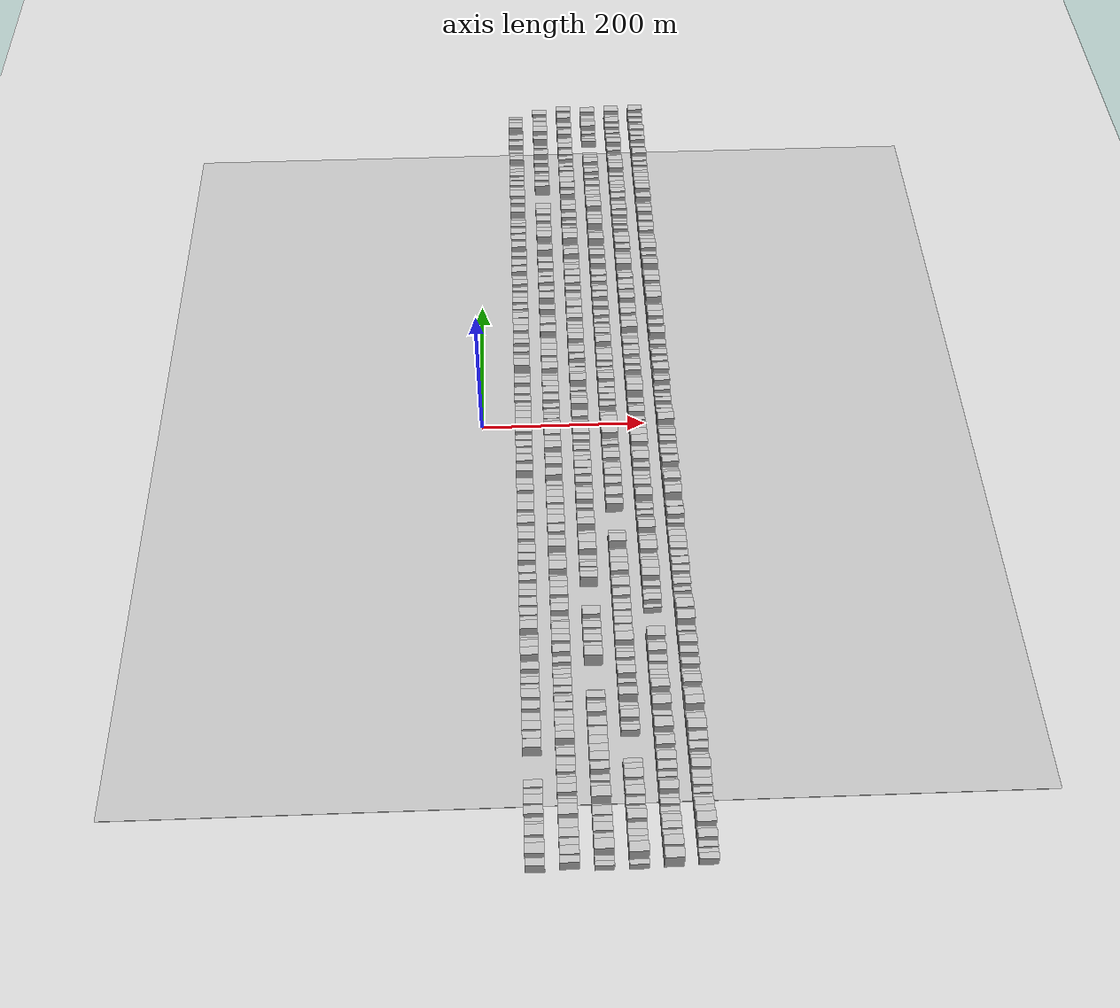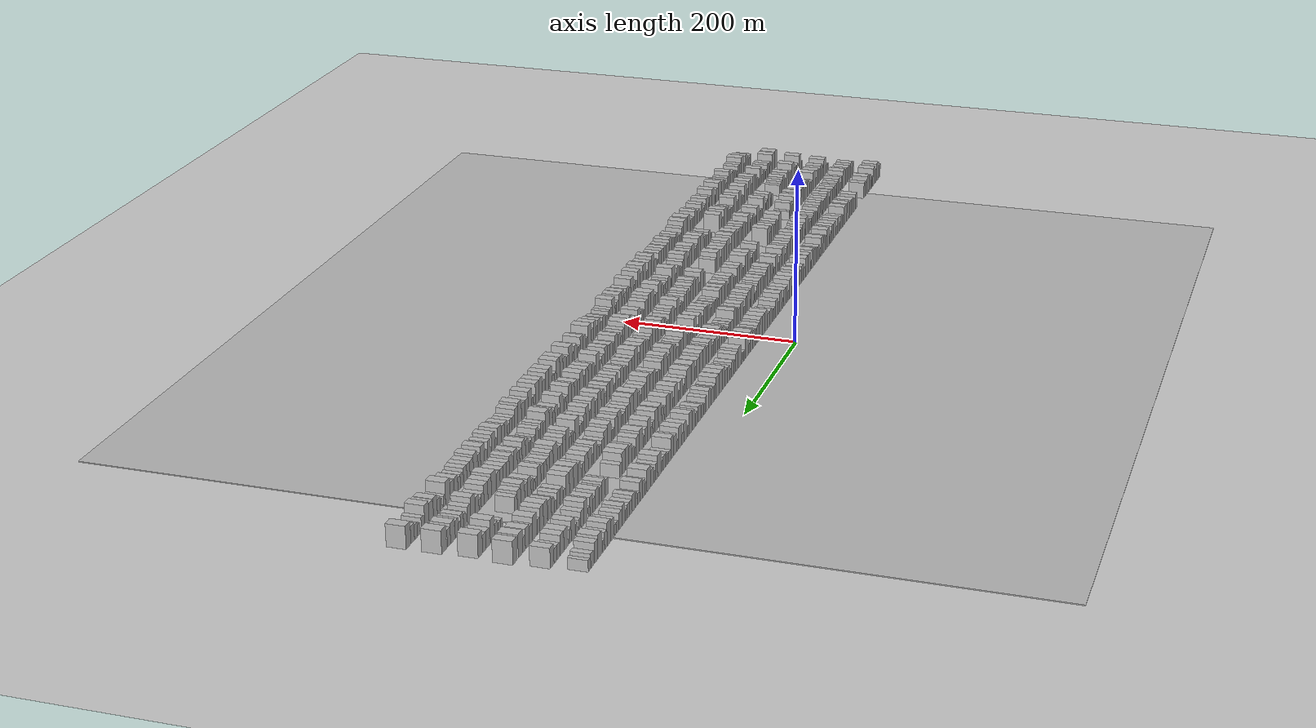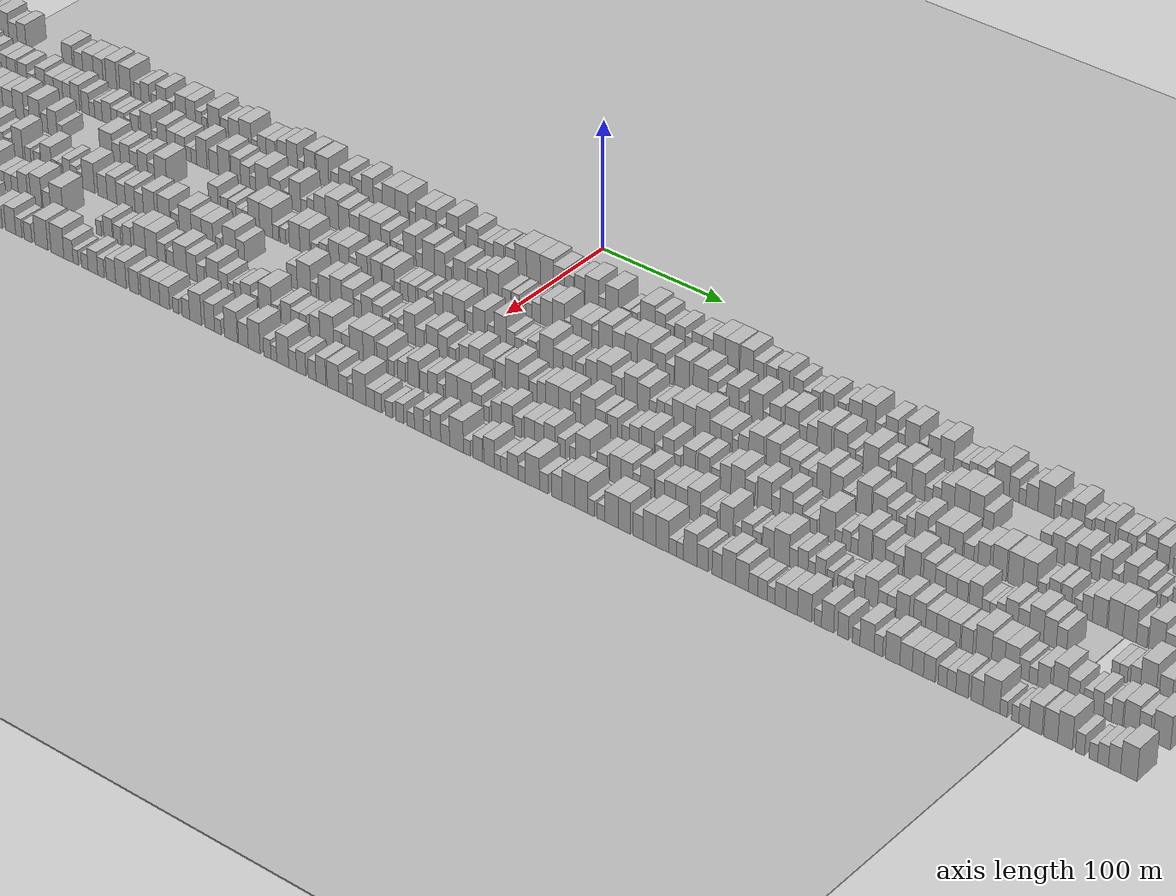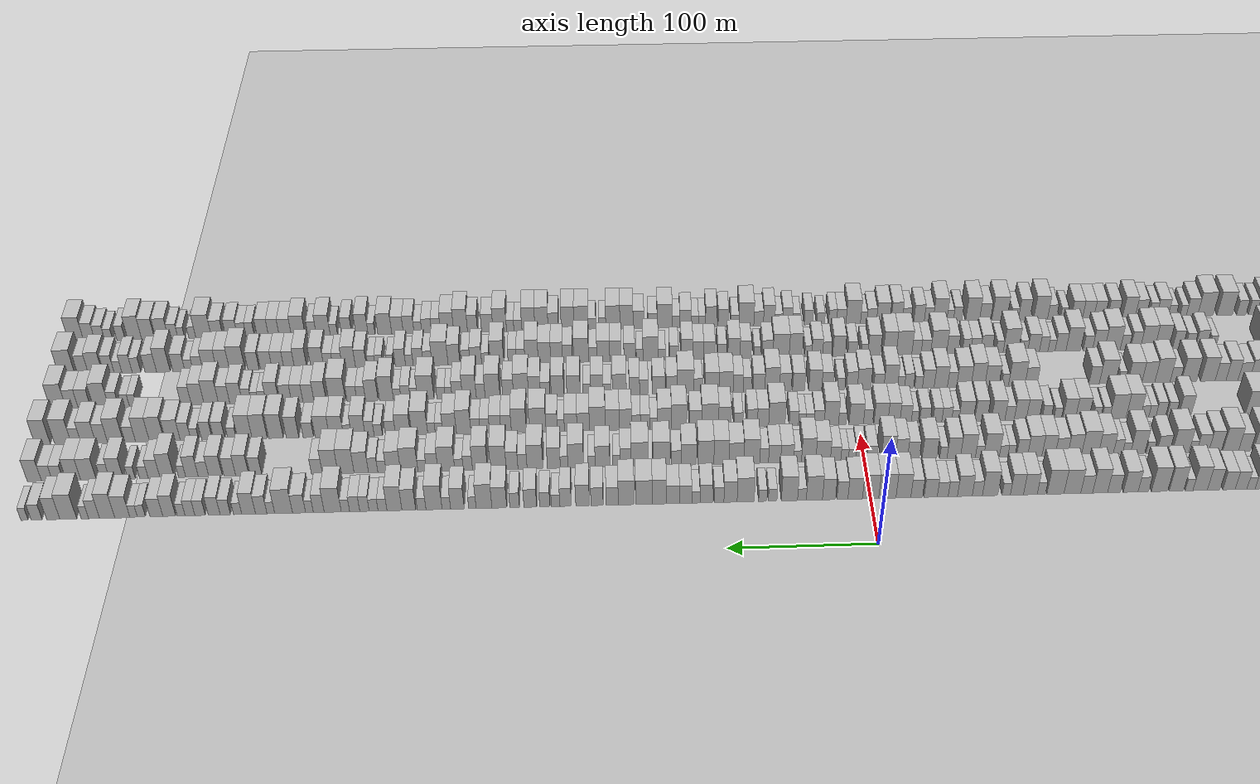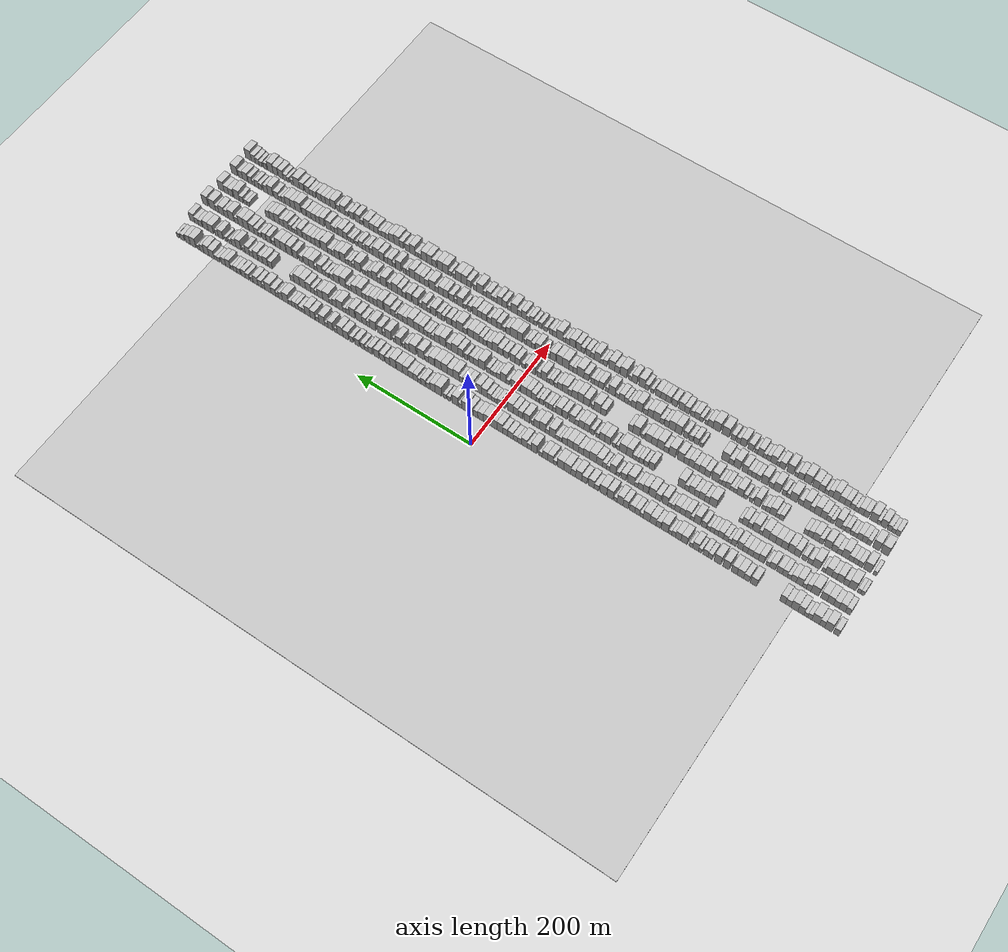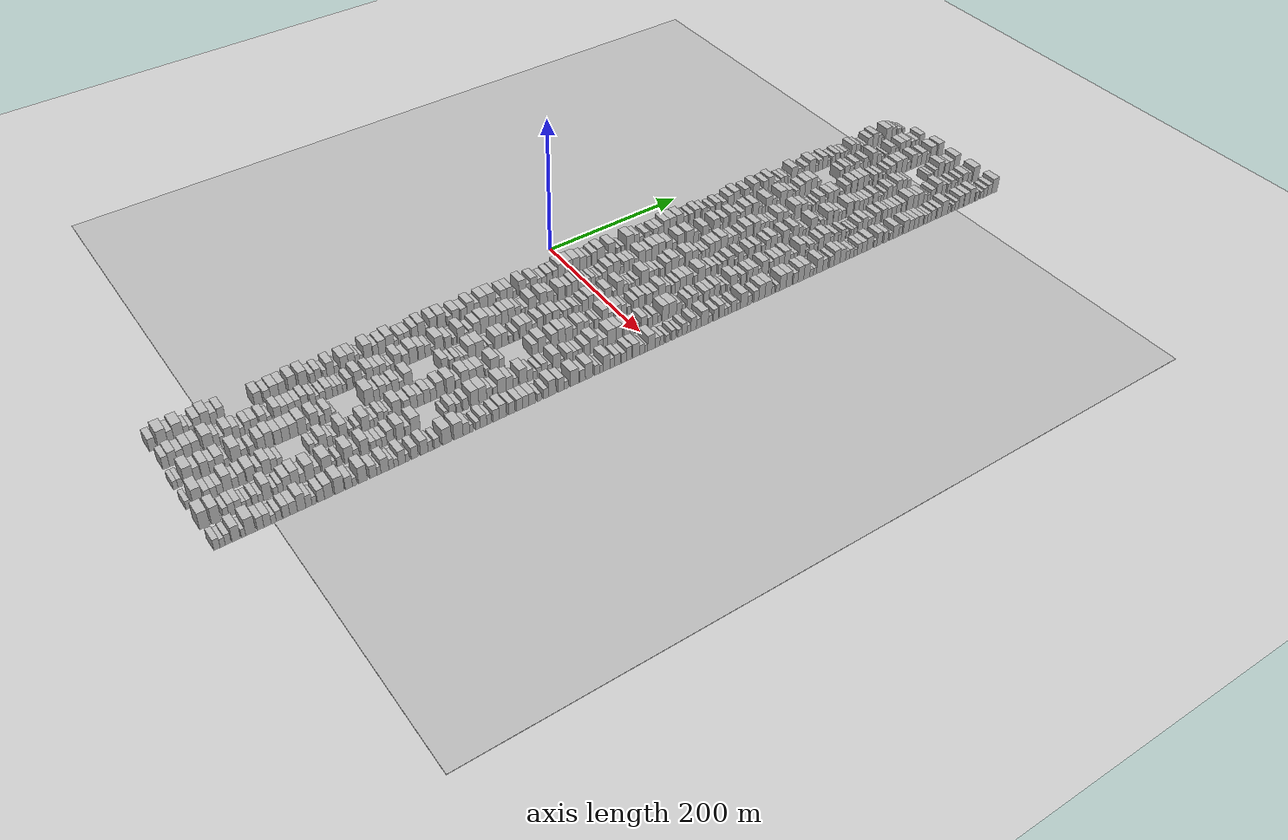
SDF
<?xml version="1.0" encoding="utf-8"?>

<sdf version="1.6">

   <world name="default">

      <gui fullscreen="0">

         <camera name="user_camera">

            <pose>-15 0 4.57585 0 0 0</pose>

            <view_controller>orbit</view_controller>

         </camera>

      </gui>

      <scene>

         <sky>

           <clouds>

             <speed>12</speed>

           </clouds>

         </sky>

         <ambient>0.4 0.4 0.4 1</ambient>

         <background>0.7 0.7 0.7 1</background>

         <shadows>1</shadows>

      </scene>

      <gravity>0 0 -9.8066</gravity>

      <magnetic_field>6e-06 2.3e-05 -4.2e-05</magnetic_field>

      <physics default="0" name="default_physics" type="ode">

         <ode>

            <solver>

               <type>quick</type>

               <iters>10</iters>

               <sor>1.0</sor>

               <use_dynamic_moi_rescaling>0</use_dynamic_moi_rescaling>

            </solver>

            <constraints>

               <cfm>0</cfm>

               <erp>0.2</erp>

               <contact_max_correcting_vel>100</contact_max_correcting_vel>

               <contact_surface_layer>0.001</contact_surface_layer>

            </constraints>

         </ode>

         <max_step_size>0.004</max_step_size>

         <real_time_factor>1</real_time_factor>

         <real_time_update_rate>250</real_time_update_rate>

      </physics>

      <light name="sun" type="directional">

         <cast_shadows>1</cast_shadows>

         <pose>0 0 10 0 0 0</pose>

         <diffuse>0.8 0.8 0.8 1</diffuse>

         <specular>0.2 0.2 0.2 1</specular>

         <attenuation>

            <range>1000</range>

            <constant>0.9</constant>

            <linear>0.01</linear>

            <quadratic>0.001</quadratic>

         </attenuation>

         <direction>-0.5 0.1 -0.9</direction>

      </light>

      <include>

         <name>ground_plane_1</name>

         <uri>model://HANNAS_ground_plane</uri>

         <pose>0 0 0  0 0 0</pose>

      </include>

      <include>

         <name>ground_plane_2</name>

         <uri>model://HANNAS_ground_plane</uri>

         <pose>100 0 0  0 0 0</pose>

      </include>

      <model name="building_1">

         <static>1</static>

         <pose frame="">50.0000 -565.8020 0 0.000000 0.000000 0.000000</pose>

         <link name="link">

            <pose frame="">0 0 9.00 0 0 0</pose>

            <collision name="collision">

               <geometry>

                  <box>

                     <size>20.0000 8.3960 18.0000</size>

                  </box>

               </geometry>

               <max_contacts>10</max_contacts>

               <surface>

                  <contact>

                     <ode/>

                  </contact>

                  <bounce/>

                  <friction>

                     <torsional>

                        <ode/>

                     </torsional>

                     <ode/>

                  </friction>

               </surface>

            </collision>

            <visual name="visual">

               <cast_shadows>0</cast_shadows>

               <geometry>

                  <box>

                     <size>20.0000 8.3960 18.0000</size>

                  </box>

               </geometry>

               <material>

                  <script>

                     <uri>model://HANNAS_wall/materials/scripts</uri>

                     <uri>model://HANNAS_wall/materials/textures</uri>

                     <name>vrc/HANNAS_wall</name>

                  </script>

               </material>

            </visual>

            <self_collide>0</self_collide>

            <enable_wind>0</enable_wind>

            <kinematic>0</kinematic>

         </link>

      </model>

      <model name="building_2">

         <static>1</static>

         <pose frame="">50.0000 -553.9148 0 0.000000 0.000000 0.000000</pose>

         <link name="link">

            <pose frame="">0 0 12.00 0 0 0</pose>

            <collision name="collision">

               <geometry>

                  <box>

                     <size>20.0000 11.3786 24.0000</size>

                  </box>

               </geometry>

               <max_contacts>10</max_contacts>

               <surface>

                  <contact>

                     <ode/>

                  </contact>

                  <bounce/>

                  <friction>

                     <torsional>

                        <ode/>

                     </torsional>

                     <ode/>

                  </friction>

               </surface>

            </collision>

            <visual name="visual">

               <cast_shadows>0</cast_shadows>

               <geometry>

                  <box>

                     <size>20.0000 11.3786 24.0000</size>

                  </box>

               </geometry>

               <material>

                  <script>

                     <uri>model://HANNAS_wall/materials/scripts</uri>

                     <uri>model://HANNAS_wall/materials/textures</uri>

                     <name>vrc/HANNAS_wall</name>

                  </script>

               </material>

            </visual>

            <self_collide>0</self_collide>

            <enable_wind>0</enable_wind>

            <kinematic>0</kinematic>

         </link>

      </model>

      <model name="building_3">

         <static>1</static>

         <pose frame="">50.0000 -544.4185 0 0.000000 0.000000 0.000000</pose>

         <link name="link">

            <pose frame="">0 0 9.00 0 0 0</pose>

            <collision name="collision">

               <geometry>

                  <box>

                     <size>20.0000 7.6140 18.0000</size>

                  </box>

               </geometry>

               <max_contacts>10</max_contacts>

               <surface>

                  <contact>

                     <ode/>

                  </contact>

                  <bounce/>

                  <friction>

                     <torsional>

                        <ode/>

                     </torsional>

                     <ode/>

                  </friction>

               </surface>

            </collision>

            <visual name="visual">

               <cast_shadows>0</cast_shadows>

               <geometry>

                  <box>

                     <size>20.0000 7.6140 18.0000</size>

                  </box>

               </geometry>

               <material>

                  <script>

                     <uri>model://HANNAS_wall/materials/scripts</uri>

                     <uri>model://HANNAS_wall/materials/textures</uri>

                     <name>vrc/HANNAS_wall</name>

                  </script>

               </material>

            </visual>

            <self_collide>0</self_collide>

            <enable_wind>0</enable_wind>

            <kinematic>0</kinematic>

         </link>

      </model>

      <model name="building_4">

         <static>1</static>

         <pose frame="">50.0000 -534.6611 0 0.000000 0.000000 0.000000</pose>

         <link name="link">

            <pose frame="">0 0 12.00 0 0 0</pose>

            <collision name="collision">

               <geometry>

                  <box>

                     <size>20.0000 11.9007 24.0000</size>

                  </box>

               </geometry>

               <max_contacts>10</max_contacts>

               <surface>

                  <contact>

                     <ode/>

                  </contact>

                  <bounce/>

                  <friction>

                     <torsional>

                        <ode/>

                     </torsional>

                     <ode/>

                  </friction>

               </surface>

            </collision>

            <visual name="visual">

               <cast_shadows>0</cast_shadows>

               <geometry>

                  <box>

                     <size>20.0000 11.9007 24.0000</size>

                  </box>

               </geometry>

               <material>

                  <script>

                     <uri>model://HANNAS_wall/materials/scripts</uri>

                     <uri>model://HANNAS_wall/materials/textures</uri>

                     <name>vrc/HANNAS_wall</name>

                  </script>

               </material>

            </visual>

            <self_collide>0</self_collide>

            <enable_wind>0</enable_wind>

            <kinematic>0</kinematic>

         </link>

      </model>

      <model name="building_5">

         <static>1</static>

         <pose frame="">50.0000 -525.4273 0 0.000000 0.000000 0.000000</pose>

         <link name="link">

            <pose frame="">0 0 7.50 0 0 0</pose>

            <collision name="collision">

               <geometry>

                  <box>

                     <size>20.0000 6.5668 15.0000</size>

                  </box>

               </geometry>

               <max_contacts>10</max_contacts>

               <surface>

                  <contact>

                     <ode/>

                  </contact>

                  <bounce/>

                  <friction>

                     <torsional>

                        <ode/>

                     </torsional>

                     <ode/>

                  </friction>

               </surface>

            </collision>

            <visual name="visual">

               <cast_shadows>0</cast_shadows>

               <geometry>

                  <box>

                     <size>20.0000 6.5668 15.0000</size>

                  </box>

               </geometry>

               <material>

                  <script>

                     <uri>model://HANNAS_wall/materials/scripts</uri>

                     <uri>model://HANNAS_wall/materials/textures</uri>

                     <name>vrc/HANNAS_wall</name>

                  </script>

               </material>

            </visual>

            <self_collide>0</self_collide>

            <enable_wind>0</enable_wind>

            <kinematic>0</kinematic>

         </link>

      </model>

      <model name="building_6">

         <static>1</static>

         <pose frame="">50.0000 -519.4033 0 0.000000 0.000000 0.000000</pose>

         <link name="link">

            <pose frame="">0 0 6.00 0 0 0</pose>

            <collision name="collision">

               <geometry>

                  <box>

                     <size>20.0000 5.4813 12.0000</size>

                  </box>

               </geometry>

               <max_contacts>10</max_contacts>

               <surface>

                  <contact>

                     <ode/>

                  </contact>

                  <bounce/>

                  <friction>

                     <torsional>

                        <ode/>

                     </torsional>

                     <ode/>

                  </friction>

               </surface>

            </collision>

            <visual name="visual">

               <cast_shadows>0</cast_shadows>

               <geometry>

                  <box>

                     <size>20.0000 5.4813 12.0000</size>

                  </box>

               </geometry>

               <material>

                  <script>

                     <uri>model://HANNAS_wall/materials/scripts</uri>

                     <uri>model://HANNAS_wall/materials/textures</uri>

                     <name>vrc/HANNAS_wall</name>

                  </script>

               </material>

            </visual>

            <self_collide>0</self_collide>

            <enable_wind>0</enable_wind>

            <kinematic>0</kinematic>

         </link>

      </model>

      <model name="building_7">

         <static>1</static>

         <pose frame="">50.0000 -511.9810 0 0.000000 0.000000 0.000000</pose>

         <link name="link">

            <pose frame="">0 0 10.50 0 0 0</pose>

            <collision name="collision">

               <geometry>

                  <box>

                     <size>20.0000 9.3633 21.0000</size>

                  </box>

               </geometry>

               <max_contacts>10</max_contacts>

               <surface>

                  <contact>

                     <ode/>

                  </contact>

                  <bounce/>

                  <friction>

                     <torsional>

                        <ode/>

                     </torsional>

                     <ode/>

                  </friction>

               </surface>

            </collision>

            <visual name="visual">

               <cast_shadows>0</cast_shadows>

               <geometry>

                  <box>

                     <size>20.0000 9.3633 21.0000</size>

                  </box>

               </geometry>

               <material>

                  <script>

                     <uri>model://HANNAS_wall/materials/scripts</uri>

                     <uri>model://HANNAS_wall/materials/textures</uri>

                     <name>vrc/HANNAS_wall</name>

                  </script>

               </material>

            </visual>

            <self_collide>0</self_collide>

            <enable_wind>0</enable_wind>

            <kinematic>0</kinematic>

         </link>

      </model>

      <model name="building_8">

         <static>1</static>

         <pose frame="">50.0000 -501.9242 0 0.000000 0.000000 0.000000</pose>

         <link name="link">

            <pose frame="">0 0 12.00 0 0 0</pose>

            <collision name="collision">

               <geometry>

                  <box>

                     <size>20.0000 10.7504 24.0000</size>

                  </box>

               </geometry>

               <max_contacts>10</max_contacts>

               <surface>

                  <contact>

                     <ode/>

                  </contact>

                  <bounce/>

                  <friction>

                     <torsional>

                        <ode/>

                     </torsional>

                     <ode/>

                  </friction>

               </surface>

            </collision>

            <visual name="visual">

               <cast_shadows>0</cast_shadows>

               <geometry>

                  <box>

                     <size>20.0000 10.7504 24.0000</size>

                  </box>

               </geometry>

               <material>

                  <script>

                     <uri>model://HANNAS_wall/materials/scripts</uri>

                     <uri>model://HANNAS_wall/materials/textures</uri>

                     <name>vrc/HANNAS_wall</name>

                  </script>

               </material>

            </visual>

            <self_collide>0</self_collide>

            <enable_wind>0</enable_wind>

            <kinematic>0</kinematic>

         </link>

      </model>

      <model name="building_9">

         <static>1</static>

         <pose frame="">50.0000 -492.2639 0 0.000000 0.000000 0.000000</pose>

         <link name="link">

            <pose frame="">0 0 9.00 0 0 0</pose>

            <collision name="collision">

               <geometry>

                  <box>

                     <size>20.0000 8.5702 18.0000</size>

                  </box>

               </geometry>

               <max_contacts>10</max_contacts>

               <surface>

                  <contact>

                     <ode/>

                  </contact>

                  <bounce/>

                  <friction>

                     <torsional>

                        <ode/>

                     </torsional>

                     <ode/>

                  </friction>

               </surface>

            </collision>

            <visual name="visual">

               <cast_shadows>0</cast_shadows>

               <geometry>

                  <box>

                     <size>20.0000 8.5702 18.0000</size>

                  </box>

               </geometry>

               <material>

                  <script>

                     <uri>model://HANNAS_wall/materials/scripts</uri>

                     <uri>model://HANNAS_wall/materials/textures</uri>

                     <name>vrc/HANNAS_wall</name>

                  </script>

               </material>

            </visual>

            <self_collide>0</self_collide>

            <enable_wind>0</enable_wind>

            <kinematic>0</kinematic>

         </link>

      </model>

      <model name="building_10">

         <static>1</static>

         <pose frame="">50.0000 -483.6536 0 0.000000 0.000000 0.000000</pose>

         <link name="link">

            <pose frame="">0 0 10.50 0 0 0</pose>

            <collision name="collision">

               <geometry>

                  <box>

                     <size>20.0000 8.6506 21.0000</size>

                  </box>

               </geometry>

               <max_contacts>10</max_contacts>

               <surface>

                  <contact>

                     <ode/>

                  </contact>

                  <bounce/>

                  <friction>

                     <torsional>

                        <ode/>

                     </torsional>

                     <ode/>

                  </friction>

               </surface>

            </collision>

            <visual name="visual">

               <cast_shadows>0</cast_shadows>

               <geometry>

                  <box>

                     <size>20.0000 8.6506 21.0000</size>

                  </box>

               </geometry>

               <material>

                  <script>

                     <uri>model://HANNAS_wall/materials/scripts</uri>

                     <uri>model://HANNAS_wall/materials/textures</uri>

                     <name>vrc/HANNAS_wall</name>

                  </script>

               </material>

            </visual>

            <self_collide>0</self_collide>

            <enable_wind>0</enable_wind>

            <kinematic>0</kinematic>

         </link>

      </model>

      <model name="building_11">

         <static>1</static>

         <pose frame="">50.0000 -438.2987 0 0.000000 0.000000 0.000000</pose>

         <link name="link">

            <pose frame="">0 0 10.50 0 0 0</pose>

            <collision name="collision">

               <geometry>

                  <box>

                     <size>20.0000 10.0197 21.0000</size>

                  </box>

               </geometry>

               <max_contacts>10</max_contacts>

               <surface>

                  <contact>

                     <ode/>

                  </contact>

                  <bounce/>

                  <friction>

                     <torsional>

                        <ode/>

                     </torsional>

                     <ode/>

                  </friction>

               </surface>

            </collision>

            <visual name="visual">

               <cast_shadows>0</cast_shadows>

               <geometry>

                  <box>

                     <size>20.0000 10.0197 21.0000</size>

                  </box>

               </geometry>

               <material>

                  <script>

                     <uri>model://HANNAS_wall/materials/scripts</uri>

                     <uri>model://HANNAS_wall/materials/textures</uri>

                     <name>vrc/HANNAS_wall</name>

                  </script>

               </material>

            </visual>

            <self_collide>0</self_collide>

            <enable_wind>0</enable_wind>

            <kinematic>0</kinematic>

         </link>

      </model>

      <model name="building_12">

         <static>1</static>

         <pose frame="">50.0000 -427.1244 0 0.000000 0.000000 0.000000</pose>

         <link name="link">

            <pose frame="">0 0 9.00 0 0 0</pose>

            <collision name="collision">

               <geometry>

                  <box>

                     <size>20.0000 8.3288 18.0000</size>

                  </box>

               </geometry>

               <max_contacts>10</max_contacts>

               <surface>

                  <contact>

                     <ode/>

                  </contact>

                  <bounce/>

                  <friction>

                     <torsional>

                        <ode/>

                     </torsional>

                     <ode/>

                  </friction>

               </surface>

            </collision>

            <visual name="visual">

               <cast_shadows>0</cast_shadows>

               <geometry>

                  <box>

                     <size>20.0000 8.3288 18.0000</size>

                  </box>

               </geometry>

               <material>

                  <script>

                     <uri>model://HANNAS_wall/materials/scripts</uri>

                     <uri>model://HANNAS_wall/materials/textures</uri>

                     <name>vrc/HANNAS_wall</name>

                  </script>

               </material>

            </visual>

            <self_collide>0</self_collide>

            <enable_wind>0</enable_wind>

            <kinematic>0</kinematic>

         </link>

      </model>

      <model name="building_13">

         <static>1</static>

         <pose frame="">50.0000 -417.7253 0 0.000000 0.000000 0.000000</pose>

         <link name="link">

            <pose frame="">0 0 10.50 0 0 0</pose>

            <collision name="collision">

               <geometry>

                  <box>

                     <size>20.0000 10.4695 21.0000</size>

                  </box>

               </geometry>

               <max_contacts>10</max_contacts>

               <surface>

                  <contact>

                     <ode/>

                  </contact>

                  <bounce/>

                  <friction>

                     <torsional>

                        <ode/>

                     </torsional>

                     <ode/>

                  </friction>

               </surface>

            </collision>

            <visual name="visual">

               <cast_shadows>0</cast_shadows>

               <geometry>

                  <box>

                     <size>20.0000 10.4695 21.0000</size>

                  </box>

               </geometry>

               <material>

                  <script>

                     <uri>model://HANNAS_wall/materials/scripts</uri>

                     <uri>model://HANNAS_wall/materials/textures</uri>

                     <name>vrc/HANNAS_wall</name>

                  </script>

               </material>

            </visual>

            <self_collide>0</self_collide>

            <enable_wind>0</enable_wind>

            <kinematic>0</kinematic>

         </link>

      </model>

      <model name="building_14">

         <static>1</static>

         <pose frame="">50.0000 -407.8832 0 0.000000 0.000000 0.000000</pose>

         <link name="link">

            <pose frame="">0 0 10.50 0 0 0</pose>

            <collision name="collision">

               <geometry>

                  <box>

                     <size>20.0000 9.2147 21.0000</size>

                  </box>

               </geometry>

               <max_contacts>10</max_contacts>

               <surface>

                  <contact>

                     <ode/>

                  </contact>

                  <bounce/>

                  <friction>

                     <torsional>

                        <ode/>

                     </torsional>

                     <ode/>

                  </friction>

               </surface>

            </collision>

            <visual name="visual">

               <cast_shadows>0</cast_shadows>

               <geometry>

                  <box>

                     <size>20.0000 9.2147 21.0000</size>

                  </box>

               </geometry>

               <material>

                  <script>

                     <uri>model://HANNAS_wall/materials/scripts</uri>

                     <uri>model://HANNAS_wall/materials/textures</uri>

                     <name>vrc/HANNAS_wall</name>

                  </script>

               </material>

            </visual>

            <self_collide>0</self_collide>

            <enable_wind>0</enable_wind>

            <kinematic>0</kinematic>

         </link>

      </model>

      <model name="building_15">

         <static>1</static>

         <pose frame="">50.0000 -395.1461 0 0.000000 0.000000 0.000000</pose>

         <link name="link">

            <pose frame="">0 0 12.00 0 0 0</pose>

            <collision name="collision">

               <geometry>

                  <box>

                     <size>20.0000 10.2595 24.0000</size>

                  </box>

               </geometry>

               <max_contacts>10</max_contacts>

               <surface>

                  <contact>

                     <ode/>

                  </contact>

                  <bounce/>

                  <friction>

                     <torsional>

                        <ode/>

                     </torsional>

                     <ode/>

                  </friction>

               </surface>

            </collision>

            <visual name="visual">

               <cast_shadows>0</cast_shadows>

               <geometry>

                  <box>

                     <size>20.0000 10.2595 24.0000</size>

                  </box>

               </geometry>

               <material>

                  <script>

                     <uri>model://HANNAS_wall/materials/scripts</uri>

                     <uri>model://HANNAS_wall/materials/textures</uri>

                     <name>vrc/HANNAS_wall</name>

                  </script>

               </material>

            </visual>

            <self_collide>0</self_collide>

            <enable_wind>0</enable_wind>

            <kinematic>0</kinematic>

         </link>

      </model>

      <model name="building_16">

         <static>1</static>

         <pose frame="">50.0000 -381.5667 0 0.000000 0.000000 0.000000</pose>

         <link name="link">

            <pose frame="">0 0 12.00 0 0 0</pose>

            <collision name="collision">

               <geometry>

                  <box>

                     <size>20.0000 10.8994 24.0000</size>

                  </box>

               </geometry>

               <max_contacts>10</max_contacts>

               <surface>

                  <contact>

                     <ode/>

                  </contact>

                  <bounce/>

                  <friction>

                     <torsional>

                        <ode/>

                     </torsional>

                     <ode/>

                  </friction>

               </surface>

            </collision>

            <visual name="visual">

               <cast_shadows>0</cast_shadows>

               <geometry>

                  <box>

                     <size>20.0000 10.8994 24.0000</size>

                  </box>

               </geometry>

               <material>

                  <script>

                     <uri>model://HANNAS_wall/materials/scripts</uri>

                     <uri>model://HANNAS_wall/materials/textures</uri>

                     <name>vrc/HANNAS_wall</name>

                  </script>

               </material>

            </visual>

            <self_collide>0</self_collide>

            <enable_wind>0</enable_wind>

            <kinematic>0</kinematic>

         </link>

      </model>

      <model name="building_17">

         <static>1</static>

         <pose frame="">50.0000 -369.8226 0 0.000000 0.000000 0.000000</pose>

         <link name="link">

            <pose frame="">0 0 7.50 0 0 0</pose>

            <collision name="collision">

               <geometry>

                  <box>

                     <size>20.0000 6.5887 15.0000</size>

                  </box>

               </geometry>

               <max_contacts>10</max_contacts>

               <surface>

                  <contact>

                     <ode/>

                  </contact>

                  <bounce/>

                  <friction>

                     <torsional>

                        <ode/>

                     </torsional>

                     <ode/>

                  </friction>

               </surface>

            </collision>

            <visual name="visual">

               <cast_shadows>0</cast_shadows>

               <geometry>

                  <box>

                     <size>20.0000 6.5887 15.0000</size>

                  </box>

               </geometry>

               <material>

                  <script>

                     <uri>model://HANNAS_wall/materials/scripts</uri>

                     <uri>model://HANNAS_wall/materials/textures</uri>

                     <name>vrc/HANNAS_wall</name>

                  </script>

               </material>

            </visual>

            <self_collide>0</self_collide>

            <enable_wind>0</enable_wind>

            <kinematic>0</kinematic>

         </link>

      </model>

      <model name="building_18">

         <static>1</static>

         <pose frame="">50.0000 -362.5325 0 0.000000 0.000000 0.000000</pose>

         <link name="link">

            <pose frame="">0 0 9.00 0 0 0</pose>

            <collision name="collision">

               <geometry>

                  <box>

                     <size>20.0000 7.9915 18.0000</size>

                  </box>

               </geometry>

               <max_contacts>10</max_contacts>

               <surface>

                  <contact>

                     <ode/>

                  </contact>

                  <bounce/>

                  <friction>

                     <torsional>

                        <ode/>

                     </torsional>

                     <ode/>

                  </friction>

               </surface>

            </collision>

            <visual name="visual">

               <cast_shadows>0</cast_shadows>

               <geometry>

                  <box>

                     <size>20.0000 7.9915 18.0000</size>

                  </box>

               </geometry>

               <material>

                  <script>

                     <uri>model://HANNAS_wall/materials/scripts</uri>

                     <uri>model://HANNAS_wall/materials/textures</uri>

                     <name>vrc/HANNAS_wall</name>

                  </script>

               </material>

            </visual>

            <self_collide>0</self_collide>

            <enable_wind>0</enable_wind>

            <kinematic>0</kinematic>

         </link>

      </model>

      <model name="building_19">

         <static>1</static>

         <pose frame="">50.0000 -353.9644 0 0.000000 0.000000 0.000000</pose>

         <link name="link">

            <pose frame="">0 0 6.00 0 0 0</pose>

            <collision name="collision">

               <geometry>

                  <box>

                     <size>20.0000 5.1448 12.0000</size>

                  </box>

               </geometry>

               <max_contacts>10</max_contacts>

               <surface>

                  <contact>

                     <ode/>

                  </contact>

                  <bounce/>

                  <friction>

                     <torsional>

                        <ode/>

                     </torsional>

                     <ode/>

                  </friction>

               </surface>

            </collision>

            <visual name="visual">

               <cast_shadows>0</cast_shadows>

               <geometry>

                  <box>

                     <size>20.0000 5.1448 12.0000</size>

                  </box>

               </geometry>

               <material>

                  <script>

                     <uri>model://HANNAS_wall/materials/scripts</uri>

                     <uri>model://HANNAS_wall/materials/textures</uri>

                     <name>vrc/HANNAS_wall</name>

                  </script>

               </material>

            </visual>

            <self_collide>0</self_collide>

            <enable_wind>0</enable_wind>

            <kinematic>0</kinematic>

         </link>

      </model>

      <model name="building_20">

         <static>1</static>

         <pose frame="">50.0000 -346.6164 0 0.000000 0.000000 0.000000</pose>

         <link name="link">

            <pose frame="">0 0 10.50 0 0 0</pose>

            <collision name="collision">

               <geometry>

                  <box>

                     <size>20.0000 9.5511 21.0000</size>

                  </box>

               </geometry>

               <max_contacts>10</max_contacts>

               <surface>

                  <contact>

                     <ode/>

                  </contact>

                  <bounce/>

                  <friction>

                     <torsional>

                        <ode/>

                     </torsional>

                     <ode/>

                  </friction>

               </surface>

            </collision>

            <visual name="visual">

               <cast_shadows>0</cast_shadows>

               <geometry>

                  <box>

                     <size>20.0000 9.5511 21.0000</size>

                  </box>

               </geometry>

               <material>

                  <script>

                     <uri>model://HANNAS_wall/materials/scripts</uri>

                     <uri>model://HANNAS_wall/materials/textures</uri>

                     <name>vrc/HANNAS_wall</name>

                  </script>

               </material>

            </visual>

            <self_collide>0</self_collide>

            <enable_wind>0</enable_wind>

            <kinematic>0</kinematic>

         </link>

      </model>

      <model name="building_21">

         <static>1</static>

         <pose frame="">50.0000 -339.0628 0 0.000000 0.000000 0.000000</pose>

         <link name="link">

            <pose frame="">0 0 6.00 0 0 0</pose>

            <collision name="collision">

               <geometry>

                  <box>

                     <size>20.0000 5.5561 12.0000</size>

                  </box>

               </geometry>

               <max_contacts>10</max_contacts>

               <surface>

                  <contact>

                     <ode/>

                  </contact>

                  <bounce/>

                  <friction>

                     <torsional>

                        <ode/>

                     </torsional>

                     <ode/>

                  </friction>

               </surface>

            </collision>

            <visual name="visual">

               <cast_shadows>0</cast_shadows>

               <geometry>

                  <box>

                     <size>20.0000 5.5561 12.0000</size>

                  </box>

               </geometry>

               <material>

                  <script>

                     <uri>model://HANNAS_wall/materials/scripts</uri>

                     <uri>model://HANNAS_wall/materials/textures</uri>

                     <name>vrc/HANNAS_wall</name>

                  </script>

               </material>

            </visual>

            <self_collide>0</self_collide>

            <enable_wind>0</enable_wind>

            <kinematic>0</kinematic>

         </link>

      </model>

      <model name="building_22">

         <static>1</static>

         <pose frame="">50.0000 -328.2652 0 0.000000 0.000000 0.000000</pose>

         <link name="link">

            <pose frame="">0 0 10.50 0 0 0</pose>

            <collision name="collision">

               <geometry>

                  <box>

                     <size>20.0000 10.0391 21.0000</size>

                  </box>

               </geometry>

               <max_contacts>10</max_contacts>

               <surface>

                  <contact>

                     <ode/>

                  </contact>

                  <bounce/>

                  <friction>

                     <torsional>

                        <ode/>

                     </torsional>

                     <ode/>

                  </friction>

               </surface>

            </collision>

            <visual name="visual">

               <cast_shadows>0</cast_shadows>

               <geometry>

                  <box>

                     <size>20.0000 10.0391 21.0000</size>

                  </box>

               </geometry>

               <material>

                  <script>

                     <uri>model://HANNAS_wall/materials/scripts</uri>

                     <uri>model://HANNAS_wall/materials/textures</uri>

                     <name>vrc/HANNAS_wall</name>

                  </script>

               </material>

            </visual>

            <self_collide>0</self_collide>

            <enable_wind>0</enable_wind>

            <kinematic>0</kinematic>

         </link>

      </model>

      <model name="building_23">

         <static>1</static>

         <pose frame="">50.0000 -318.7859 0 0.000000 0.000000 0.000000</pose>

         <link name="link">

            <pose frame="">0 0 10.50 0 0 0</pose>

            <collision name="collision">

               <geometry>

                  <box>

                     <size>20.0000 8.9194 21.0000</size>

                  </box>

               </geometry>

               <max_contacts>10</max_contacts>

               <surface>

                  <contact>

                     <ode/>

                  </contact>

                  <bounce/>

                  <friction>

                     <torsional>

                        <ode/>

                     </torsional>

                     <ode/>

                  </friction>

               </surface>

            </collision>

            <visual name="visual">

               <cast_shadows>0</cast_shadows>

               <geometry>

                  <box>

                     <size>20.0000 8.9194 21.0000</size>

                  </box>

               </geometry>

               <material>

                  <script>

                     <uri>model://HANNAS_wall/materials/scripts</uri>

                     <uri>model://HANNAS_wall/materials/textures</uri>

                     <name>vrc/HANNAS_wall</name>

                  </script>

               </material>

            </visual>

            <self_collide>0</self_collide>

            <enable_wind>0</enable_wind>

            <kinematic>0</kinematic>

         </link>

      </model>

      <model name="building_24">

         <static>1</static>

         <pose frame="">50.0000 -311.3256 0 0.000000 0.000000 0.000000</pose>

         <link name="link">

            <pose frame="">0 0 7.50 0 0 0</pose>

            <collision name="collision">

               <geometry>

                  <box>

                     <size>20.0000 6.0012 15.0000</size>

                  </box>

               </geometry>

               <max_contacts>10</max_contacts>

               <surface>

                  <contact>

                     <ode/>

                  </contact>

                  <bounce/>

                  <friction>

                     <torsional>

                        <ode/>

                     </torsional>

                     <ode/>

                  </friction>

               </surface>

            </collision>

            <visual name="visual">

               <cast_shadows>0</cast_shadows>

               <geometry>

                  <box>

                     <size>20.0000 6.0012 15.0000</size>

                  </box>

               </geometry>

               <material>

                  <script>

                     <uri>model://HANNAS_wall/materials/scripts</uri>

                     <uri>model://HANNAS_wall/materials/textures</uri>

                     <name>vrc/HANNAS_wall</name>

                  </script>

               </material>

            </visual>

            <self_collide>0</self_collide>

            <enable_wind>0</enable_wind>

            <kinematic>0</kinematic>

         </link>

      </model>

      <model name="building_25">

         <static>1</static>

         <pose frame="">50.0000 -305.8745 0 0.000000 0.000000 0.000000</pose>

         <link name="link">

            <pose frame="">0 0 6.00 0 0 0</pose>

            <collision name="collision">

               <geometry>

                  <box>

                     <size>20.0000 4.9010 12.0000</size>

                  </box>

               </geometry>

               <max_contacts>10</max_contacts>

               <surface>

                  <contact>

                     <ode/>

                  </contact>

                  <bounce/>

                  <friction>

                     <torsional>

                        <ode/>

                     </torsional>

                     <ode/>

                  </friction>

               </surface>

            </collision>

            <visual name="visual">

               <cast_shadows>0</cast_shadows>

               <geometry>

                  <box>

                     <size>20.0000 4.9010 12.0000</size>

                  </box>

               </geometry>

               <material>

                  <script>

                     <uri>model://HANNAS_wall/materials/scripts</uri>

                     <uri>model://HANNAS_wall/materials/textures</uri>

                     <name>vrc/HANNAS_wall</name>

                  </script>

               </material>

            </visual>

            <self_collide>0</self_collide>

            <enable_wind>0</enable_wind>

            <kinematic>0</kinematic>

         </link>

      </model>

      <model name="building_26">

         <static>1</static>

         <pose frame="">50.0000 -296.8805 0 0.000000 0.000000 0.000000</pose>

         <link name="link">

            <pose frame="">0 0 12.00 0 0 0</pose>

            <collision name="collision">

               <geometry>

                  <box>

                     <size>20.0000 11.0871 24.0000</size>

                  </box>

               </geometry>

               <max_contacts>10</max_contacts>

               <surface>

                  <contact>

                     <ode/>

                  </contact>

                  <bounce/>

                  <friction>

                     <torsional>

                        <ode/>

                     </torsional>

                     <ode/>

                  </friction>

               </surface>

            </collision>

            <visual name="visual">

               <cast_shadows>0</cast_shadows>

               <geometry>

                  <box>

                     <size>20.0000 11.0871 24.0000</size>

                  </box>

               </geometry>

               <material>

                  <script>

                     <uri>model://HANNAS_wall/materials/scripts</uri>

                     <uri>model://HANNAS_wall/materials/textures</uri>

                     <name>vrc/HANNAS_wall</name>

                  </script>

               </material>

            </visual>

            <self_collide>0</self_collide>

            <enable_wind>0</enable_wind>

            <kinematic>0</kinematic>

         </link>

      </model>

      <model name="building_27">

         <static>1</static>

         <pose frame="">50.0000 -286.7191 0 0.000000 0.000000 0.000000</pose>

         <link name="link">

            <pose frame="">0 0 9.00 0 0 0</pose>

            <collision name="collision">

               <geometry>

                  <box>

                     <size>20.0000 7.2356 18.0000</size>

                  </box>

               </geometry>

               <max_contacts>10</max_contacts>

               <surface>

                  <contact>

                     <ode/>

                  </contact>

                  <bounce/>

                  <friction>

                     <torsional>

                        <ode/>

                     </torsional>

                     <ode/>

                  </friction>

               </surface>

            </collision>

            <visual name="visual">

               <cast_shadows>0</cast_shadows>

               <geometry>

                  <box>

                     <size>20.0000 7.2356 18.0000</size>

                  </box>

               </geometry>

               <material>

                  <script>

                     <uri>model://HANNAS_wall/materials/scripts</uri>

                     <uri>model://HANNAS_wall/materials/textures</uri>

                     <name>vrc/HANNAS_wall</name>

                  </script>

               </material>

            </visual>

            <self_collide>0</self_collide>

            <enable_wind>0</enable_wind>

            <kinematic>0</kinematic>

         </link>

      </model>

      <model name="building_28">

         <static>1</static>

         <pose frame="">50.0000 -277.9937 0 0.000000 0.000000 0.000000</pose>

         <link name="link">

            <pose frame="">0 0 10.50 0 0 0</pose>

            <collision name="collision">

               <geometry>

                  <box>

                     <size>20.0000 10.2153 21.0000</size>

                  </box>

               </geometry>

               <max_contacts>10</max_contacts>

               <surface>

                  <contact>

                     <ode/>

                  </contact>

                  <bounce/>

                  <friction>

                     <torsional>

                        <ode/>

                     </torsional>

                     <ode/>

                  </friction>

               </surface>

            </collision>

            <visual name="visual">

               <cast_shadows>0</cast_shadows>

               <geometry>

                  <box>

                     <size>20.0000 10.2153 21.0000</size>

                  </box>

               </geometry>

               <material>

                  <script>

                     <uri>model://HANNAS_wall/materials/scripts</uri>

                     <uri>model://HANNAS_wall/materials/textures</uri>

                     <name>vrc/HANNAS_wall</name>

                  </script>

               </material>

            </visual>

            <self_collide>0</self_collide>

            <enable_wind>0</enable_wind>

            <kinematic>0</kinematic>

         </link>

      </model>

      <model name="building_29">

         <static>1</static>

         <pose frame="">50.0000 -267.3749 0 0.000000 0.000000 0.000000</pose>

         <link name="link">

            <pose frame="">0 0 12.00 0 0 0</pose>

            <collision name="collision">

               <geometry>

                  <box>

                     <size>20.0000 11.0223 24.0000</size>

                  </box>

               </geometry>

               <max_contacts>10</max_contacts>

               <surface>

                  <contact>

                     <ode/>

                  </contact>

                  <bounce/>

                  <friction>

                     <torsional>

                        <ode/>

                     </torsional>

                     <ode/>

                  </friction>

               </surface>

            </collision>

            <visual name="visual">

               <cast_shadows>0</cast_shadows>

               <geometry>

                  <box>

                     <size>20.0000 11.0223 24.0000</size>

                  </box>

               </geometry>

               <material>

                  <script>

                     <uri>model://HANNAS_wall/materials/scripts</uri>

                     <uri>model://HANNAS_wall/materials/textures</uri>

                     <name>vrc/HANNAS_wall</name>

                  </script>

               </material>

            </visual>

            <self_collide>0</self_collide>

            <enable_wind>0</enable_wind>

            <kinematic>0</kinematic>

         </link>

      </model>

      <model name="building_30">

         <static>1</static>

         <pose frame="">50.0000 -259.0522 0 0.000000 0.000000 0.000000</pose>

         <link name="link">

            <pose frame="">0 0 6.00 0 0 0</pose>

            <collision name="collision">

               <geometry>

                  <box>

                     <size>20.0000 5.6230 12.0000</size>

                  </box>

               </geometry>

               <max_contacts>10</max_contacts>

               <surface>

                  <contact>

                     <ode/>

                  </contact>

                  <bounce/>

                  <friction>

                     <torsional>

                        <ode/>

                     </torsional>

                     <ode/>

                  </friction>

               </surface>

            </collision>

            <visual name="visual">

               <cast_shadows>0</cast_shadows>

               <geometry>

                  <box>

                     <size>20.0000 5.6230 12.0000</size>

                  </box>

               </geometry>

               <material>

                  <script>

                     <uri>model://HANNAS_wall/materials/scripts</uri>

                     <uri>model://HANNAS_wall/materials/textures</uri>

                     <name>vrc/HANNAS_wall</name>

                  </script>

               </material>

            </visual>

            <self_collide>0</self_collide>

            <enable_wind>0</enable_wind>

            <kinematic>0</kinematic>

         </link>

      </model>

      <model name="building_31">

         <static>1</static>

         <pose frame="">50.0000 -252.1641 0 0.000000 0.000000 0.000000</pose>

         <link name="link">

            <pose frame="">0 0 9.00 0 0 0</pose>

            <collision name="collision">

               <geometry>

                  <box>

                     <size>20.0000 8.1533 18.0000</size>

                  </box>

               </geometry>

               <max_contacts>10</max_contacts>

               <surface>

                  <contact>

                     <ode/>

                  </contact>

                  <bounce/>

                  <friction>

                     <torsional>

                        <ode/>

                     </torsional>

                     <ode/>

                  </friction>

               </surface>

            </collision>

            <visual name="visual">

               <cast_shadows>0</cast_shadows>

               <geometry>

                  <box>

                     <size>20.0000 8.1533 18.0000</size>

                  </box>

               </geometry>

               <material>

                  <script>

                     <uri>model://HANNAS_wall/materials/scripts</uri>

                     <uri>model://HANNAS_wall/materials/textures</uri>

                     <name>vrc/HANNAS_wall</name>

                  </script>

               </material>

            </visual>

            <self_collide>0</self_collide>

            <enable_wind>0</enable_wind>

            <kinematic>0</kinematic>

         </link>

      </model>

      <model name="building_32">

         <static>1</static>

         <pose frame="">50.0000 -243.8982 0 0.000000 0.000000 0.000000</pose>

         <link name="link">

            <pose frame="">0 0 9.00 0 0 0</pose>

            <collision name="collision">

               <geometry>

                  <box>

                     <size>20.0000 8.3785 18.0000</size>

                  </box>

               </geometry>

               <max_contacts>10</max_contacts>

               <surface>

                  <contact>

                     <ode/>

                  </contact>

                  <bounce/>

                  <friction>

                     <torsional>

                        <ode/>

                     </torsional>

                     <ode/>

                  </friction>

               </surface>

            </collision>

            <visual name="visual">

               <cast_shadows>0</cast_shadows>

               <geometry>

                  <box>

                     <size>20.0000 8.3785 18.0000</size>

                  </box>

               </geometry>

               <material>

                  <script>

                     <uri>model://HANNAS_wall/materials/scripts</uri>

                     <uri>model://HANNAS_wall/materials/textures</uri>

                     <name>vrc/HANNAS_wall</name>

                  </script>

               </material>

            </visual>

            <self_collide>0</self_collide>

            <enable_wind>0</enable_wind>

            <kinematic>0</kinematic>

         </link>

      </model>

      <model name="building_33">

         <static>1</static>

         <pose frame="">50.0000 -233.4024 0 0.000000 0.000000 0.000000</pose>

         <link name="link">

            <pose frame="">0 0 10.50 0 0 0</pose>

            <collision name="collision">

               <geometry>

                  <box>

                     <size>20.0000 8.6130 21.0000</size>

                  </box>

               </geometry>

               <max_contacts>10</max_contacts>

               <surface>

                  <contact>

                     <ode/>

                  </contact>

                  <bounce/>

                  <friction>

                     <torsional>

                        <ode/>

                     </torsional>

                     <ode/>

                  </friction>

               </surface>

            </collision>

            <visual name="visual">

               <cast_shadows>0</cast_shadows>

               <geometry>

                  <box>

                     <size>20.0000 8.6130 21.0000</size>

                  </box>

               </geometry>

               <material>

                  <script>

                     <uri>model://HANNAS_wall/materials/scripts</uri>

                     <uri>model://HANNAS_wall/materials/textures</uri>

                     <name>vrc/HANNAS_wall</name>

                  </script>

               </material>

            </visual>

            <self_collide>0</self_collide>

            <enable_wind>0</enable_wind>

            <kinematic>0</kinematic>

         </link>

      </model>

      <model name="building_34">

         <static>1</static>

         <pose frame="">50.0000 -224.1698 0 0.000000 0.000000 0.000000</pose>

         <link name="link">

            <pose frame="">0 0 12.00 0 0 0</pose>

            <collision name="collision">

               <geometry>

                  <box>

                     <size>20.0000 9.8521 24.0000</size>

                  </box>

               </geometry>

               <max_contacts>10</max_contacts>

               <surface>

                  <contact>

                     <ode/>

                  </contact>

                  <bounce/>

                  <friction>

                     <torsional>

                        <ode/>

                     </torsional>

                     <ode/>

                  </friction>

               </surface>

            </collision>

            <visual name="visual">

               <cast_shadows>0</cast_shadows>

               <geometry>

                  <box>

                     <size>20.0000 9.8521 24.0000</size>

                  </box>

               </geometry>

               <material>

                  <script>

                     <uri>model://HANNAS_wall/materials/scripts</uri>

                     <uri>model://HANNAS_wall/materials/textures</uri>

                     <name>vrc/HANNAS_wall</name>

                  </script>

               </material>

            </visual>

            <self_collide>0</self_collide>

            <enable_wind>0</enable_wind>

            <kinematic>0</kinematic>

         </link>

      </model>

      <model name="building_35">

         <static>1</static>

         <pose frame="">50.0000 -216.5741 0 0.000000 0.000000 0.000000</pose>

         <link name="link">

            <pose frame="">0 0 6.00 0 0 0</pose>

            <collision name="collision">

               <geometry>

                  <box>

                     <size>20.0000 5.3393 12.0000</size>

                  </box>

               </geometry>

               <max_contacts>10</max_contacts>

               <surface>

                  <contact>

                     <ode/>

                  </contact>

                  <bounce/>

                  <friction>

                     <torsional>

                        <ode/>

                     </torsional>

                     <ode/>

                  </friction>

               </surface>

            </collision>

            <visual name="visual">

               <cast_shadows>0</cast_shadows>

               <geometry>

                  <box>

                     <size>20.0000 5.3393 12.0000</size>

                  </box>

               </geometry>

               <material>

                  <script>

                     <uri>model://HANNAS_wall/materials/scripts</uri>

                     <uri>model://HANNAS_wall/materials/textures</uri>

                     <name>vrc/HANNAS_wall</name>

                  </script>

               </material>

            </visual>

            <self_collide>0</self_collide>

            <enable_wind>0</enable_wind>

            <kinematic>0</kinematic>

         </link>

      </model>

      <model name="building_36">

         <static>1</static>

         <pose frame="">50.0000 -207.9369 0 0.000000 0.000000 0.000000</pose>

         <link name="link">

            <pose frame="">0 0 12.00 0 0 0</pose>

            <collision name="collision">

               <geometry>

                  <box>

                     <size>20.0000 9.9350 24.0000</size>

                  </box>

               </geometry>

               <max_contacts>10</max_contacts>

               <surface>

                  <contact>

                     <ode/>

                  </contact>

                  <bounce/>

                  <friction>

                     <torsional>

                        <ode/>

                     </torsional>

                     <ode/>

                  </friction>

               </surface>

            </collision>

            <visual name="visual">

               <cast_shadows>0</cast_shadows>

               <geometry>

                  <box>

                     <size>20.0000 9.9350 24.0000</size>

                  </box>

               </geometry>

               <material>

                  <script>

                     <uri>model://HANNAS_wall/materials/scripts</uri>

                     <uri>model://HANNAS_wall/materials/textures</uri>

                     <name>vrc/HANNAS_wall</name>

                  </script>

               </material>

            </visual>

            <self_collide>0</self_collide>

            <enable_wind>0</enable_wind>

            <kinematic>0</kinematic>

         </link>

      </model>

      <model name="building_37">

         <static>1</static>

         <pose frame="">50.0000 -196.3970 0 0.000000 0.000000 0.000000</pose>

         <link name="link">

            <pose frame="">0 0 12.00 0 0 0</pose>

            <collision name="collision">

               <geometry>

                  <box>

                     <size>20.0000 11.1449 24.0000</size>

                  </box>

               </geometry>

               <max_contacts>10</max_contacts>

               <surface>

                  <contact>

                     <ode/>

                  </contact>

                  <bounce/>

                  <friction>

                     <torsional>

                        <ode/>

                     </torsional>

                     <ode/>

                  </friction>

               </surface>

            </collision>

            <visual name="visual">

               <cast_shadows>0</cast_shadows>

               <geometry>

                  <box>

                     <size>20.0000 11.1449 24.0000</size>

                  </box>

               </geometry>

               <material>

                  <script>

                     <uri>model://HANNAS_wall/materials/scripts</uri>

                     <uri>model://HANNAS_wall/materials/textures</uri>

                     <name>vrc/HANNAS_wall</name>

                  </script>

               </material>

            </visual>

            <self_collide>0</self_collide>

            <enable_wind>0</enable_wind>

            <kinematic>0</kinematic>

         </link>

      </model>

      <model name="building_38">

         <static>1</static>

         <pose frame="">50.0000 -185.2506 0 0.000000 0.000000 0.000000</pose>

         <link name="link">

            <pose frame="">0 0 7.50 0 0 0</pose>

            <collision name="collision">

               <geometry>

                  <box>

                     <size>20.0000 7.1479 15.0000</size>

                  </box>

               </geometry>

               <max_contacts>10</max_contacts>

               <surface>

                  <contact>

                     <ode/>

                  </contact>

                  <bounce/>

                  <friction>

                     <torsional>

                        <ode/>

                     </torsional>

                     <ode/>

                  </friction>

               </surface>

            </collision>

            <visual name="visual">

               <cast_shadows>0</cast_shadows>

               <geometry>

                  <box>

                     <size>20.0000 7.1479 15.0000</size>

                  </box>

               </geometry>

               <material>

                  <script>

                     <uri>model://HANNAS_wall/materials/scripts</uri>

                     <uri>model://HANNAS_wall/materials/textures</uri>

                     <name>vrc/HANNAS_wall</name>

                  </script>

               </material>

            </visual>

            <self_collide>0</self_collide>

            <enable_wind>0</enable_wind>

            <kinematic>0</kinematic>

         </link>

      </model>

      <model name="building_39">

         <static>1</static>

         <pose frame="">50.0000 -176.6455 0 0.000000 0.000000 0.000000</pose>

         <link name="link">

            <pose frame="">0 0 10.50 0 0 0</pose>

            <collision name="collision">

               <geometry>

                  <box>

                     <size>20.0000 10.0623 21.0000</size>

                  </box>

               </geometry>

               <max_contacts>10</max_contacts>

               <surface>

                  <contact>

                     <ode/>

                  </contact>

                  <bounce/>

                  <friction>

                     <torsional>

                        <ode/>

                     </torsional>

                     <ode/>

                  </friction>

               </surface>

            </collision>

            <visual name="visual">

               <cast_shadows>0</cast_shadows>

               <geometry>

                  <box>

                     <size>20.0000 10.0623 21.0000</size>

                  </box>

               </geometry>

               <material>

                  <script>

                     <uri>model://HANNAS_wall/materials/scripts</uri>

                     <uri>model://HANNAS_wall/materials/textures</uri>

                     <name>vrc/HANNAS_wall</name>

                  </script>

               </material>

            </visual>

            <self_collide>0</self_collide>

            <enable_wind>0</enable_wind>

            <kinematic>0</kinematic>

         </link>

      </model>

      <model name="building_40">

         <static>1</static>

         <pose frame="">50.0000 -165.2181 0 0.000000 0.000000 0.000000</pose>

         <link name="link">

            <pose frame="">0 0 9.00 0 0 0</pose>

            <collision name="collision">

               <geometry>

                  <box>

                     <size>20.0000 8.7925 18.0000</size>

                  </box>

               </geometry>

               <max_contacts>10</max_contacts>

               <surface>

                  <contact>

                     <ode/>

                  </contact>

                  <bounce/>

                  <friction>

                     <torsional>

                        <ode/>

                     </torsional>

                     <ode/>

                  </friction>

               </surface>

            </collision>

            <visual name="visual">

               <cast_shadows>0</cast_shadows>

               <geometry>

                  <box>

                     <size>20.0000 8.7925 18.0000</size>

                  </box>

               </geometry>

               <material>

                  <script>

                     <uri>model://HANNAS_wall/materials/scripts</uri>

                     <uri>model://HANNAS_wall/materials/textures</uri>

                     <name>vrc/HANNAS_wall</name>

                  </script>

               </material>

            </visual>

            <self_collide>0</self_collide>

            <enable_wind>0</enable_wind>

            <kinematic>0</kinematic>

         </link>

      </model>

      <model name="building_41">

         <static>1</static>

         <pose frame="">50.0000 -155.7027 0 0.000000 0.000000 0.000000</pose>

         <link name="link">

            <pose frame="">0 0 12.00 0 0 0</pose>

            <collision name="collision">

               <geometry>

                  <box>

                     <size>20.0000 10.2382 24.0000</size>

                  </box>

               </geometry>

               <max_contacts>10</max_contacts>

               <surface>

                  <contact>

                     <ode/>

                  </contact>

                  <bounce/>

                  <friction>

                     <torsional>

                        <ode/>

                     </torsional>

                     <ode/>

                  </friction>

               </surface>

            </collision>

            <visual name="visual">

               <cast_shadows>0</cast_shadows>

               <geometry>

                  <box>

                     <size>20.0000 10.2382 24.0000</size>

                  </box>

               </geometry>

               <material>

                  <script>

                     <uri>model://HANNAS_wall/materials/scripts</uri>

                     <uri>model://HANNAS_wall/materials/textures</uri>

                     <name>vrc/HANNAS_wall</name>

                  </script>

               </material>

            </visual>

            <self_collide>0</self_collide>

            <enable_wind>0</enable_wind>

            <kinematic>0</kinematic>

         </link>

      </model>

      <model name="building_42">

         <static>1</static>

         <pose frame="">50.0000 -146.5190 0 0.000000 0.000000 0.000000</pose>

         <link name="link">

            <pose frame="">0 0 9.00 0 0 0</pose>

            <collision name="collision">

               <geometry>

                  <box>

                     <size>20.0000 8.1291 18.0000</size>

                  </box>

               </geometry>

               <max_contacts>10</max_contacts>

               <surface>

                  <contact>

                     <ode/>

                  </contact>

                  <bounce/>

                  <friction>

                     <torsional>

                        <ode/>

                     </torsional>

                     <ode/>

                  </friction>

               </surface>

            </collision>

            <visual name="visual">

               <cast_shadows>0</cast_shadows>

               <geometry>

                  <box>

                     <size>20.0000 8.1291 18.0000</size>

                  </box>

               </geometry>

               <material>

                  <script>

                     <uri>model://HANNAS_wall/materials/scripts</uri>

                     <uri>model://HANNAS_wall/materials/textures</uri>

                     <name>vrc/HANNAS_wall</name>

                  </script>

               </material>

            </visual>

            <self_collide>0</self_collide>

            <enable_wind>0</enable_wind>

            <kinematic>0</kinematic>

         </link>

      </model>

      <model name="building_43">

         <static>1</static>

         <pose frame="">50.0000 -136.7335 0 0.000000 0.000000 0.000000</pose>

         <link name="link">

            <pose frame="">0 0 12.00 0 0 0</pose>

            <collision name="collision">

               <geometry>

                  <box>

                     <size>20.0000 11.4420 24.0000</size>

                  </box>

               </geometry>

               <max_contacts>10</max_contacts>

               <surface>

                  <contact>

                     <ode/>

                  </contact>

                  <bounce/>

                  <friction>

                     <torsional>

                        <ode/>

                     </torsional>

                     <ode/>

                  </friction>

               </surface>

            </collision>

            <visual name="visual">

               <cast_shadows>0</cast_shadows>

               <geometry>

                  <box>

                     <size>20.0000 11.4420 24.0000</size>

                  </box>

               </geometry>

               <material>

                  <script>

                     <uri>model://HANNAS_wall/materials/scripts</uri>

                     <uri>model://HANNAS_wall/materials/textures</uri>

                     <name>vrc/HANNAS_wall</name>

                  </script>

               </material>

            </visual>

            <self_collide>0</self_collide>

            <enable_wind>0</enable_wind>

            <kinematic>0</kinematic>

         </link>

      </model>

      <model name="building_44">

         <static>1</static>

         <pose frame="">50.0000 -125.1948 0 0.000000 0.000000 0.000000</pose>

         <link name="link">

            <pose frame="">0 0 12.00 0 0 0</pose>

            <collision name="collision">

               <geometry>

                  <box>

                     <size>20.0000 11.6354 24.0000</size>

                  </box>

               </geometry>

               <max_contacts>10</max_contacts>

               <surface>

                  <contact>

                     <ode/>

                  </contact>

                  <bounce/>

                  <friction>

                     <torsional>

                        <ode/>

                     </torsional>

                     <ode/>

                  </friction>

               </surface>

            </collision>

            <visual name="visual">

               <cast_shadows>0</cast_shadows>

               <geometry>

                  <box>

                     <size>20.0000 11.6354 24.0000</size>

                  </box>

               </geometry>

               <material>

                  <script>

                     <uri>model://HANNAS_wall/materials/scripts</uri>

                     <uri>model://HANNAS_wall/materials/textures</uri>

                     <name>vrc/HANNAS_wall</name>

                  </script>

               </material>

            </visual>

            <self_collide>0</self_collide>

            <enable_wind>0</enable_wind>

            <kinematic>0</kinematic>

         </link>

      </model>

      <model name="building_45">

         <static>1</static>

         <pose frame="">50.0000 -115.5677 0 0.000000 0.000000 0.000000</pose>

         <link name="link">

            <pose frame="">0 0 6.00 0 0 0</pose>

            <collision name="collision">

               <geometry>

                  <box>

                     <size>20.0000 5.6187 12.0000</size>

                  </box>

               </geometry>

               <max_contacts>10</max_contacts>

               <surface>

                  <contact>

                     <ode/>

                  </contact>

                  <bounce/>

                  <friction>

                     <torsional>

                        <ode/>

                     </torsional>

                     <ode/>

                  </friction>

               </surface>

            </collision>

            <visual name="visual">

               <cast_shadows>0</cast_shadows>

               <geometry>

                  <box>

                     <size>20.0000 5.6187 12.0000</size>

                  </box>

               </geometry>

               <material>

                  <script>

                     <uri>model://HANNAS_wall/materials/scripts</uri>

                     <uri>model://HANNAS_wall/materials/textures</uri>

                     <name>vrc/HANNAS_wall</name>

                  </script>

               </material>

            </visual>

            <self_collide>0</self_collide>

            <enable_wind>0</enable_wind>

            <kinematic>0</kinematic>

         </link>

      </model>

      <model name="building_46">

         <static>1</static>

         <pose frame="">50.0000 -108.0615 0 0.000000 0.000000 0.000000</pose>

         <link name="link">

            <pose frame="">0 0 10.50 0 0 0</pose>

            <collision name="collision">

               <geometry>

                  <box>

                     <size>20.0000 9.3937 21.0000</size>

                  </box>

               </geometry>

               <max_contacts>10</max_contacts>

               <surface>

                  <contact>

                     <ode/>

                  </contact>

                  <bounce/>

                  <friction>

                     <torsional>

                        <ode/>

                     </torsional>

                     <ode/>

                  </friction>

               </surface>

            </collision>

            <visual name="visual">

               <cast_shadows>0</cast_shadows>

               <geometry>

                  <box>

                     <size>20.0000 9.3937 21.0000</size>

                  </box>

               </geometry>

               <material>

                  <script>

                     <uri>model://HANNAS_wall/materials/scripts</uri>

                     <uri>model://HANNAS_wall/materials/textures</uri>

                     <name>vrc/HANNAS_wall</name>

                  </script>

               </material>

            </visual>

            <self_collide>0</self_collide>

            <enable_wind>0</enable_wind>

            <kinematic>0</kinematic>

         </link>

      </model>

      <model name="building_47">

         <static>1</static>

         <pose frame="">50.0000 -98.9167 0 0.000000 0.000000 0.000000</pose>

         <link name="link">

            <pose frame="">0 0 10.50 0 0 0</pose>

            <collision name="collision">

               <geometry>

                  <box>

                     <size>20.0000 8.8960 21.0000</size>

                  </box>

               </geometry>

               <max_contacts>10</max_contacts>

               <surface>

                  <contact>

                     <ode/>

                  </contact>

                  <bounce/>

                  <friction>

                     <torsional>

                        <ode/>

                     </torsional>

                     <ode/>

                  </friction>

               </surface>

            </collision>

            <visual name="visual">

               <cast_shadows>0</cast_shadows>

               <geometry>

                  <box>

                     <size>20.0000 8.8960 21.0000</size>

                  </box>

               </geometry>

               <material>

                  <script>

                     <uri>model://HANNAS_wall/materials/scripts</uri>

                     <uri>model://HANNAS_wall/materials/textures</uri>

                     <name>vrc/HANNAS_wall</name>

                  </script>

               </material>

            </visual>

            <self_collide>0</self_collide>

            <enable_wind>0</enable_wind>

            <kinematic>0</kinematic>

         </link>

      </model>

      <model name="building_48">

         <static>1</static>

         <pose frame="">50.0000 -91.6531 0 0.000000 0.000000 0.000000</pose>

         <link name="link">

            <pose frame="">0 0 6.00 0 0 0</pose>

            <collision name="collision">

               <geometry>

                  <box>

                     <size>20.0000 5.6313 12.0000</size>

                  </box>

               </geometry>

               <max_contacts>10</max_contacts>

               <surface>

                  <contact>

                     <ode/>

                  </contact>

                  <bounce/>

                  <friction>

                     <torsional>

                        <ode/>

                     </torsional>

                     <ode/>

                  </friction>

               </surface>

            </collision>

            <visual name="visual">

               <cast_shadows>0</cast_shadows>

               <geometry>

                  <box>

                     <size>20.0000 5.6313 12.0000</size>

                  </box>

               </geometry>

               <material>

                  <script>

                     <uri>model://HANNAS_wall/materials/scripts</uri>

                     <uri>model://HANNAS_wall/materials/textures</uri>

                     <name>vrc/HANNAS_wall</name>

                  </script>

               </material>

            </visual>

            <self_collide>0</self_collide>

            <enable_wind>0</enable_wind>

            <kinematic>0</kinematic>

         </link>

      </model>

      <model name="building_49">

         <static>1</static>

         <pose frame="">50.0000 -80.5970 0 0.000000 0.000000 0.000000</pose>

         <link name="link">

            <pose frame="">0 0 12.00 0 0 0</pose>

            <collision name="collision">

               <geometry>

                  <box>

                     <size>20.0000 10.4808 24.0000</size>

                  </box>

               </geometry>

               <max_contacts>10</max_contacts>

               <surface>

                  <contact>

                     <ode/>

                  </contact>

                  <bounce/>

                  <friction>

                     <torsional>

                        <ode/>

                     </torsional>

                     <ode/>

                  </friction>

               </surface>

            </collision>

            <visual name="visual">

               <cast_shadows>0</cast_shadows>

               <geometry>

                  <box>

                     <size>20.0000 10.4808 24.0000</size>

                  </box>

               </geometry>

               <material>

                  <script>

                     <uri>model://HANNAS_wall/materials/scripts</uri>

                     <uri>model://HANNAS_wall/materials/textures</uri>

                     <name>vrc/HANNAS_wall</name>

                  </script>

               </material>

            </visual>

            <self_collide>0</self_collide>

            <enable_wind>0</enable_wind>

            <kinematic>0</kinematic>

         </link>

      </model>

      <model name="building_50">

         <static>1</static>

         <pose frame="">50.0000 -71.9100 0 0.000000 0.000000 0.000000</pose>

         <link name="link">

            <pose frame="">0 0 7.50 0 0 0</pose>

            <collision name="collision">

               <geometry>

                  <box>

                     <size>20.0000 6.8932 15.0000</size>

                  </box>

               </geometry>

               <max_contacts>10</max_contacts>

               <surface>

                  <contact>

                     <ode/>

                  </contact>

                  <bounce/>

                  <friction>

                     <torsional>

                        <ode/>

                     </torsional>

                     <ode/>

                  </friction>

               </surface>

            </collision>

            <visual name="visual">

               <cast_shadows>0</cast_shadows>

               <geometry>

                  <box>

                     <size>20.0000 6.8932 15.0000</size>

                  </box>

               </geometry>

               <material>

                  <script>

                     <uri>model://HANNAS_wall/materials/scripts</uri>

                     <uri>model://HANNAS_wall/materials/textures</uri>

                     <name>vrc/HANNAS_wall</name>

                  </script>

               </material>

            </visual>

            <self_collide>0</self_collide>

            <enable_wind>0</enable_wind>

            <kinematic>0</kinematic>

         </link>

      </model>

      <model name="building_51">

         <static>1</static>

         <pose frame="">50.0000 -63.4535 0 0.000000 0.000000 0.000000</pose>

         <link name="link">

            <pose frame="">0 0 10.50 0 0 0</pose>

            <collision name="collision">

               <geometry>

                  <box>

                     <size>20.0000 10.0200 21.0000</size>

                  </box>

               </geometry>

               <max_contacts>10</max_contacts>

               <surface>

                  <contact>

                     <ode/>

                  </contact>

                  <bounce/>

                  <friction>

                     <torsional>

                        <ode/>

                     </torsional>

                     <ode/>

                  </friction>

               </surface>

            </collision>

            <visual name="visual">

               <cast_shadows>0</cast_shadows>

               <geometry>

                  <box>

                     <size>20.0000 10.0200 21.0000</size>

                  </box>

               </geometry>

               <material>

                  <script>

                     <uri>model://HANNAS_wall/materials/scripts</uri>

                     <uri>model://HANNAS_wall/materials/textures</uri>

                     <name>vrc/HANNAS_wall</name>

                  </script>

               </material>

            </visual>

            <self_collide>0</self_collide>

            <enable_wind>0</enable_wind>

            <kinematic>0</kinematic>

         </link>

      </model>

      <model name="building_52">

         <static>1</static>

         <pose frame="">50.0000 -55.2991 0 0.000000 0.000000 0.000000</pose>

         <link name="link">

            <pose frame="">0 0 7.50 0 0 0</pose>

            <collision name="collision">

               <geometry>

                  <box>

                     <size>20.0000 6.2887 15.0000</size>

                  </box>

               </geometry>

               <max_contacts>10</max_contacts>

               <surface>

                  <contact>

                     <ode/>

                  </contact>

                  <bounce/>

                  <friction>

                     <torsional>

                        <ode/>

                     </torsional>

                     <ode/>

                  </friction>

               </surface>

            </collision>

            <visual name="visual">

               <cast_shadows>0</cast_shadows>

               <geometry>

                  <box>

                     <size>20.0000 6.2887 15.0000</size>

                  </box>

               </geometry>

               <material>

                  <script>

                     <uri>model://HANNAS_wall/materials/scripts</uri>

                     <uri>model://HANNAS_wall/materials/textures</uri>

                     <name>vrc/HANNAS_wall</name>

                  </script>

               </material>

            </visual>

            <self_collide>0</self_collide>

            <enable_wind>0</enable_wind>

            <kinematic>0</kinematic>

         </link>

      </model>

      <model name="building_53">

         <static>1</static>

         <pose frame="">50.0000 -48.4106 0 0.000000 0.000000 0.000000</pose>

         <link name="link">

            <pose frame="">0 0 7.50 0 0 0</pose>

            <collision name="collision">

               <geometry>

                  <box>

                     <size>20.0000 7.4884 15.0000</size>

                  </box>

               </geometry>

               <max_contacts>10</max_contacts>

               <surface>

                  <contact>

                     <ode/>

                  </contact>

                  <bounce/>

                  <friction>

                     <torsional>

                        <ode/>

                     </torsional>

                     <ode/>

                  </friction>

               </surface>

            </collision>

            <visual name="visual">

               <cast_shadows>0</cast_shadows>

               <geometry>

                  <box>

                     <size>20.0000 7.4884 15.0000</size>

                  </box>

               </geometry>

               <material>

                  <script>

                     <uri>model://HANNAS_wall/materials/scripts</uri>

                     <uri>model://HANNAS_wall/materials/textures</uri>

                     <name>vrc/HANNAS_wall</name>

                  </script>

               </material>

            </visual>

            <self_collide>0</self_collide>

            <enable_wind>0</enable_wind>

            <kinematic>0</kinematic>

         </link>

      </model>

      <model name="building_54">

         <static>1</static>

         <pose frame="">50.0000 -40.1829 0 0.000000 0.000000 0.000000</pose>

         <link name="link">

            <pose frame="">0 0 9.00 0 0 0</pose>

            <collision name="collision">

               <geometry>

                  <box>

                     <size>20.0000 8.9669 18.0000</size>

                  </box>

               </geometry>

               <max_contacts>10</max_contacts>

               <surface>

                  <contact>

                     <ode/>

                  </contact>

                  <bounce/>

                  <friction>

                     <torsional>

                        <ode/>

                     </torsional>

                     <ode/>

                  </friction>

               </surface>

            </collision>

            <visual name="visual">

               <cast_shadows>0</cast_shadows>

               <geometry>

                  <box>

                     <size>20.0000 8.9669 18.0000</size>

                  </box>

               </geometry>

               <material>

                  <script>

                     <uri>model://HANNAS_wall/materials/scripts</uri>

                     <uri>model://HANNAS_wall/materials/textures</uri>

                     <name>vrc/HANNAS_wall</name>

                  </script>

               </material>

            </visual>

            <self_collide>0</self_collide>

            <enable_wind>0</enable_wind>

            <kinematic>0</kinematic>

         </link>

      </model>

      <model name="building_55">

         <static>1</static>

         <pose frame="">50.0000 -30.7081 0 0.000000 0.000000 0.000000</pose>

         <link name="link">

            <pose frame="">0 0 9.00 0 0 0</pose>

            <collision name="collision">

               <geometry>

                  <box>

                     <size>20.0000 7.9828 18.0000</size>

                  </box>

               </geometry>

               <max_contacts>10</max_contacts>

               <surface>

                  <contact>

                     <ode/>

                  </contact>

                  <bounce/>

                  <friction>

                     <torsional>

                        <ode/>

                     </torsional>

                     <ode/>

                  </friction>

               </surface>

            </collision>

            <visual name="visual">

               <cast_shadows>0</cast_shadows>

               <geometry>

                  <box>

                     <size>20.0000 7.9828 18.0000</size>

                  </box>

               </geometry>

               <material>

                  <script>

                     <uri>model://HANNAS_wall/materials/scripts</uri>

                     <uri>model://HANNAS_wall/materials/textures</uri>

                     <name>vrc/HANNAS_wall</name>

                  </script>

               </material>

            </visual>

            <self_collide>0</self_collide>

            <enable_wind>0</enable_wind>

            <kinematic>0</kinematic>

         </link>

      </model>

      <model name="building_56">

         <static>1</static>

         <pose frame="">50.0000 -21.6612 0 0.000000 0.000000 0.000000</pose>

         <link name="link">

            <pose frame="">0 0 12.00 0 0 0</pose>

            <collision name="collision">

               <geometry>

                  <box>

                     <size>20.0000 10.1111 24.0000</size>

                  </box>

               </geometry>

               <max_contacts>10</max_contacts>

               <surface>

                  <contact>

                     <ode/>

                  </contact>

                  <bounce/>

                  <friction>

                     <torsional>

                        <ode/>

                     </torsional>

                     <ode/>

                  </friction>

               </surface>

            </collision>

            <visual name="visual">

               <cast_shadows>0</cast_shadows>

               <geometry>

                  <box>

                     <size>20.0000 10.1111 24.0000</size>

                  </box>

               </geometry>

               <material>

                  <script>

                     <uri>model://HANNAS_wall/materials/scripts</uri>

                     <uri>model://HANNAS_wall/materials/textures</uri>

                     <name>vrc/HANNAS_wall</name>

                  </script>

               </material>

            </visual>

            <self_collide>0</self_collide>

            <enable_wind>0</enable_wind>

            <kinematic>0</kinematic>

         </link>

      </model>

      <model name="building_57">

         <static>1</static>

         <pose frame="">50.0000 -10.7391 0 0.000000 0.000000 0.000000</pose>

         <link name="link">

            <pose frame="">0 0 12.00 0 0 0</pose>

            <collision name="collision">

               <geometry>

                  <box>

                     <size>20.0000 11.7331 24.0000</size>

                  </box>

               </geometry>

               <max_contacts>10</max_contacts>

               <surface>

                  <contact>

                     <ode/>

                  </contact>

                  <bounce/>

                  <friction>

                     <torsional>

                        <ode/>

                     </torsional>

                     <ode/>

                  </friction>

               </surface>

            </collision>

            <visual name="visual">

               <cast_shadows>0</cast_shadows>

               <geometry>

                  <box>

                     <size>20.0000 11.7331 24.0000</size>

                  </box>

               </geometry>

               <material>

                  <script>

                     <uri>model://HANNAS_wall/materials/scripts</uri>

                     <uri>model://HANNAS_wall/materials/textures</uri>

                     <name>vrc/HANNAS_wall</name>

                  </script>

               </material>

            </visual>

            <self_collide>0</self_collide>

            <enable_wind>0</enable_wind>

            <kinematic>0</kinematic>

         </link>

      </model>

      <model name="building_58">

         <static>1</static>

         <pose frame="">50.0000 0.6521 0 0.000000 0.000000 0.000000</pose>

         <link name="link">

            <pose frame="">0 0 12.00 0 0 0</pose>

            <collision name="collision">

               <geometry>

                  <box>

                     <size>20.0000 11.0493 24.0000</size>

                  </box>

               </geometry>

               <max_contacts>10</max_contacts>

               <surface>

                  <contact>

                     <ode/>

                  </contact>

                  <bounce/>

                  <friction>

                     <torsional>

                        <ode/>

                     </torsional>

                     <ode/>

                  </friction>

               </surface>

            </collision>

            <visual name="visual">

               <cast_shadows>0</cast_shadows>

               <geometry>

                  <box>

                     <size>20.0000 11.0493 24.0000</size>

                  </box>

               </geometry>

               <material>

                  <script>

                     <uri>model://HANNAS_wall/materials/scripts</uri>

                     <uri>model://HANNAS_wall/materials/textures</uri>

                     <name>vrc/HANNAS_wall</name>

                  </script>

               </material>

            </visual>

            <self_collide>0</self_collide>

            <enable_wind>0</enable_wind>

            <kinematic>0</kinematic>

         </link>

      </model>

      <model name="building_59">

         <static>1</static>

         <pose frame="">50.0000 11.0912 0 0.000000 0.000000 0.000000</pose>

         <link name="link">

            <pose frame="">0 0 10.50 0 0 0</pose>

            <collision name="collision">

               <geometry>

                  <box>

                     <size>20.0000 9.8289 21.0000</size>

                  </box>

               </geometry>

               <max_contacts>10</max_contacts>

               <surface>

                  <contact>

                     <ode/>

                  </contact>

                  <bounce/>

                  <friction>

                     <torsional>

                        <ode/>

                     </torsional>

                     <ode/>

                  </friction>

               </surface>

            </collision>

            <visual name="visual">

               <cast_shadows>0</cast_shadows>

               <geometry>

                  <box>

                     <size>20.0000 9.8289 21.0000</size>

                  </box>

               </geometry>

               <material>

                  <script>

                     <uri>model://HANNAS_wall/materials/scripts</uri>

                     <uri>model://HANNAS_wall/materials/textures</uri>

                     <name>vrc/HANNAS_wall</name>

                  </script>

               </material>

            </visual>

            <self_collide>0</self_collide>

            <enable_wind>0</enable_wind>

            <kinematic>0</kinematic>

         </link>

      </model>

      <model name="building_60">

         <static>1</static>

         <pose frame="">50.0000 19.7149 0 0.000000 0.000000 0.000000</pose>

         <link name="link">

            <pose frame="">0 0 9.00 0 0 0</pose>

            <collision name="collision">

               <geometry>

                  <box>

                     <size>20.0000 7.4185 18.0000</size>

                  </box>

               </geometry>

               <max_contacts>10</max_contacts>

               <surface>

                  <contact>

                     <ode/>

                  </contact>

                  <bounce/>

                  <friction>

                     <torsional>

                        <ode/>

                     </torsional>

                     <ode/>

                  </friction>

               </surface>

            </collision>

            <visual name="visual">

               <cast_shadows>0</cast_shadows>

               <geometry>

                  <box>

                     <size>20.0000 7.4185 18.0000</size>

                  </box>

               </geometry>

               <material>

                  <script>

                     <uri>model://HANNAS_wall/materials/scripts</uri>

                     <uri>model://HANNAS_wall/materials/textures</uri>

                     <name>vrc/HANNAS_wall</name>

                  </script>

               </material>

            </visual>

            <self_collide>0</self_collide>

            <enable_wind>0</enable_wind>

            <kinematic>0</kinematic>

         </link>

      </model>

      <model name="building_61">

         <static>1</static>

         <pose frame="">50.0000 28.8338 0 0.000000 0.000000 0.000000</pose>

         <link name="link">

            <pose frame="">0 0 10.50 0 0 0</pose>

            <collision name="collision">

               <geometry>

                  <box>

                     <size>20.0000 8.8193 21.0000</size>

                  </box>

               </geometry>

               <max_contacts>10</max_contacts>

               <surface>

                  <contact>

                     <ode/>

                  </contact>

                  <bounce/>

                  <friction>

                     <torsional>

                        <ode/>

                     </torsional>

                     <ode/>

                  </friction>

               </surface>

            </collision>

            <visual name="visual">

               <cast_shadows>0</cast_shadows>

               <geometry>

                  <box>

                     <size>20.0000 8.8193 21.0000</size>

                  </box>

               </geometry>

               <material>

                  <script>

                     <uri>model://HANNAS_wall/materials/scripts</uri>

                     <uri>model://HANNAS_wall/materials/textures</uri>

                     <name>vrc/HANNAS_wall</name>

                  </script>

               </material>

            </visual>

            <self_collide>0</self_collide>

            <enable_wind>0</enable_wind>

            <kinematic>0</kinematic>

         </link>

      </model>

      <model name="building_62">

         <static>1</static>

         <pose frame="">50.0000 38.7204 0 0.000000 0.000000 0.000000</pose>

         <link name="link">

            <pose frame="">0 0 12.00 0 0 0</pose>

            <collision name="collision">

               <geometry>

                  <box>

                     <size>20.0000 10.9539 24.0000</size>

                  </box>

               </geometry>

               <max_contacts>10</max_contacts>

               <surface>

                  <contact>

                     <ode/>

                  </contact>

                  <bounce/>

                  <friction>

                     <torsional>

                        <ode/>

                     </torsional>

                     <ode/>

                  </friction>

               </surface>

            </collision>

            <visual name="visual">

               <cast_shadows>0</cast_shadows>

               <geometry>

                  <box>

                     <size>20.0000 10.9539 24.0000</size>

                  </box>

               </geometry>

               <material>

                  <script>

                     <uri>model://HANNAS_wall/materials/scripts</uri>

                     <uri>model://HANNAS_wall/materials/textures</uri>

                     <name>vrc/HANNAS_wall</name>

                  </script>

               </material>

            </visual>

            <self_collide>0</self_collide>

            <enable_wind>0</enable_wind>

            <kinematic>0</kinematic>

         </link>

      </model>

      <model name="building_63">

         <static>1</static>

         <pose frame="">50.0000 47.1609 0 0.000000 0.000000 0.000000</pose>

         <link name="link">

            <pose frame="">0 0 6.00 0 0 0</pose>

            <collision name="collision">

               <geometry>

                  <box>

                     <size>20.0000 5.9271 12.0000</size>

                  </box>

               </geometry>

               <max_contacts>10</max_contacts>

               <surface>

                  <contact>

                     <ode/>

                  </contact>

                  <bounce/>

                  <friction>

                     <torsional>

                        <ode/>

                     </torsional>

                     <ode/>

                  </friction>

               </surface>

            </collision>

            <visual name="visual">

               <cast_shadows>0</cast_shadows>

               <geometry>

                  <box>

                     <size>20.0000 5.9271 12.0000</size>

                  </box>

               </geometry>

               <material>

                  <script>

                     <uri>model://HANNAS_wall/materials/scripts</uri>

                     <uri>model://HANNAS_wall/materials/textures</uri>

                     <name>vrc/HANNAS_wall</name>

                  </script>

               </material>

            </visual>

            <self_collide>0</self_collide>

            <enable_wind>0</enable_wind>

            <kinematic>0</kinematic>

         </link>

      </model>

      <model name="building_64">

         <static>1</static>

         <pose frame="">50.0000 55.5924 0 0.000000 0.000000 0.000000</pose>

         <link name="link">

            <pose frame="">0 0 12.00 0 0 0</pose>

            <collision name="collision">

               <geometry>

                  <box>

                     <size>20.0000 10.9358 24.0000</size>

                  </box>

               </geometry>

               <max_contacts>10</max_contacts>

               <surface>

                  <contact>

                     <ode/>

                  </contact>

                  <bounce/>

                  <friction>

                     <torsional>

                        <ode/>

                     </torsional>

                     <ode/>

                  </friction>

               </surface>

            </collision>

            <visual name="visual">

               <cast_shadows>0</cast_shadows>

               <geometry>

                  <box>

                     <size>20.0000 10.9358 24.0000</size>

                  </box>

               </geometry>

               <material>

                  <script>

                     <uri>model://HANNAS_wall/materials/scripts</uri>

                     <uri>model://HANNAS_wall/materials/textures</uri>

                     <name>vrc/HANNAS_wall</name>

                  </script>

               </material>

            </visual>

            <self_collide>0</self_collide>

            <enable_wind>0</enable_wind>

            <kinematic>0</kinematic>

         </link>

      </model>

      <model name="building_65">

         <static>1</static>

         <pose frame="">50.0000 66.9774 0 0.000000 0.000000 0.000000</pose>

         <link name="link">

            <pose frame="">0 0 6.00 0 0 0</pose>

            <collision name="collision">

               <geometry>

                  <box>

                     <size>20.0000 5.8342 12.0000</size>

                  </box>

               </geometry>

               <max_contacts>10</max_contacts>

               <surface>

                  <contact>

                     <ode/>

                  </contact>

                  <bounce/>

                  <friction>

                     <torsional>

                        <ode/>

                     </torsional>

                     <ode/>

                  </friction>

               </surface>

            </collision>

            <visual name="visual">

               <cast_shadows>0</cast_shadows>

               <geometry>

                  <box>

                     <size>20.0000 5.8342 12.0000</size>

                  </box>

               </geometry>

               <material>

                  <script>

                     <uri>model://HANNAS_wall/materials/scripts</uri>

                     <uri>model://HANNAS_wall/materials/textures</uri>

                     <name>vrc/HANNAS_wall</name>

                  </script>

               </material>

            </visual>

            <self_collide>0</self_collide>

            <enable_wind>0</enable_wind>

            <kinematic>0</kinematic>

         </link>

      </model>

      <model name="building_66">

         <static>1</static>

         <pose frame="">50.0000 73.6622 0 0.000000 0.000000 0.000000</pose>

         <link name="link">

            <pose frame="">0 0 6.00 0 0 0</pose>

            <collision name="collision">

               <geometry>

                  <box>

                     <size>20.0000 5.5355 12.0000</size>

                  </box>

               </geometry>

               <max_contacts>10</max_contacts>

               <surface>

                  <contact>

                     <ode/>

                  </contact>

                  <bounce/>

                  <friction>

                     <torsional>

                        <ode/>

                     </torsional>

                     <ode/>

                  </friction>

               </surface>

            </collision>

            <visual name="visual">

               <cast_shadows>0</cast_shadows>

               <geometry>

                  <box>

                     <size>20.0000 5.5355 12.0000</size>

                  </box>

               </geometry>

               <material>

                  <script>

                     <uri>model://HANNAS_wall/materials/scripts</uri>

                     <uri>model://HANNAS_wall/materials/textures</uri>

                     <name>vrc/HANNAS_wall</name>

                  </script>

               </material>

            </visual>

            <self_collide>0</self_collide>

            <enable_wind>0</enable_wind>

            <kinematic>0</kinematic>

         </link>

      </model>

      <model name="building_67">

         <static>1</static>

         <pose frame="">50.0000 85.2145 0 0.000000 0.000000 0.000000</pose>

         <link name="link">

            <pose frame="">0 0 12.00 0 0 0</pose>

            <collision name="collision">

               <geometry>

                  <box>

                     <size>20.0000 11.5692 24.0000</size>

                  </box>

               </geometry>

               <max_contacts>10</max_contacts>

               <surface>

                  <contact>

                     <ode/>

                  </contact>

                  <bounce/>

                  <friction>

                     <torsional>

                        <ode/>

                     </torsional>

                     <ode/>

                  </friction>

               </surface>

            </collision>

            <visual name="visual">

               <cast_shadows>0</cast_shadows>

               <geometry>

                  <box>

                     <size>20.0000 11.5692 24.0000</size>

                  </box>

               </geometry>

               <material>

                  <script>

                     <uri>model://HANNAS_wall/materials/scripts</uri>

                     <uri>model://HANNAS_wall/materials/textures</uri>

                     <name>vrc/HANNAS_wall</name>

                  </script>

               </material>

            </visual>

            <self_collide>0</self_collide>

            <enable_wind>0</enable_wind>

            <kinematic>0</kinematic>

         </link>

      </model>

      <model name="building_68">

         <static>1</static>

         <pose frame="">50.0000 95.4609 0 0.000000 0.000000 0.000000</pose>

         <link name="link">

            <pose frame="">0 0 10.50 0 0 0</pose>

            <collision name="collision">

               <geometry>

                  <box>

                     <size>20.0000 8.9235 21.0000</size>

                  </box>

               </geometry>

               <max_contacts>10</max_contacts>

               <surface>

                  <contact>

                     <ode/>

                  </contact>

                  <bounce/>

                  <friction>

                     <torsional>

                        <ode/>

                     </torsional>

                     <ode/>

                  </friction>

               </surface>

            </collision>

            <visual name="visual">

               <cast_shadows>0</cast_shadows>

               <geometry>

                  <box>

                     <size>20.0000 8.9235 21.0000</size>

                  </box>

               </geometry>

               <material>

                  <script>

                     <uri>model://HANNAS_wall/materials/scripts</uri>

                     <uri>model://HANNAS_wall/materials/textures</uri>

                     <name>vrc/HANNAS_wall</name>

                  </script>

               </material>

            </visual>

            <self_collide>0</self_collide>

            <enable_wind>0</enable_wind>

            <kinematic>0</kinematic>

         </link>

      </model>

      <model name="building_69">

         <static>1</static>

         <pose frame="">50.0000 103.2038 0 0.000000 0.000000 0.000000</pose>

         <link name="link">

            <pose frame="">0 0 7.50 0 0 0</pose>

            <collision name="collision">

               <geometry>

                  <box>

                     <size>20.0000 6.5624 15.0000</size>

                  </box>

               </geometry>

               <max_contacts>10</max_contacts>

               <surface>

                  <contact>

                     <ode/>

                  </contact>

                  <bounce/>

                  <friction>

                     <torsional>

                        <ode/>

                     </torsional>

                     <ode/>

                  </friction>

               </surface>

            </collision>

            <visual name="visual">

               <cast_shadows>0</cast_shadows>

               <geometry>

                  <box>

                     <size>20.0000 6.5624 15.0000</size>

                  </box>

               </geometry>

               <material>

                  <script>

                     <uri>model://HANNAS_wall/materials/scripts</uri>

                     <uri>model://HANNAS_wall/materials/textures</uri>

                     <name>vrc/HANNAS_wall</name>

                  </script>

               </material>

            </visual>

            <self_collide>0</self_collide>

            <enable_wind>0</enable_wind>

            <kinematic>0</kinematic>

         </link>

      </model>

      <model name="building_70">

         <static>1</static>

         <pose frame="">50.0000 111.7547 0 0.000000 0.000000 0.000000</pose>

         <link name="link">

            <pose frame="">0 0 9.00 0 0 0</pose>

            <collision name="collision">

               <geometry>

                  <box>

                     <size>20.0000 8.5394 18.0000</size>

                  </box>

               </geometry>

               <max_contacts>10</max_contacts>

               <surface>

                  <contact>

                     <ode/>

                  </contact>

                  <bounce/>

                  <friction>

                     <torsional>

                        <ode/>

                     </torsional>

                     <ode/>

                  </friction>

               </surface>

            </collision>

            <visual name="visual">

               <cast_shadows>0</cast_shadows>

               <geometry>

                  <box>

                     <size>20.0000 8.5394 18.0000</size>

                  </box>

               </geometry>

               <material>

                  <script>

                     <uri>model://HANNAS_wall/materials/scripts</uri>

                     <uri>model://HANNAS_wall/materials/textures</uri>

                     <name>vrc/HANNAS_wall</name>

                  </script>

               </material>

            </visual>

            <self_collide>0</self_collide>

            <enable_wind>0</enable_wind>

            <kinematic>0</kinematic>

         </link>

      </model>

      <model name="building_71">

         <static>1</static>

         <pose frame="">50.0000 118.8188 0 0.000000 0.000000 0.000000</pose>

         <link name="link">

            <pose frame="">0 0 6.00 0 0 0</pose>

            <collision name="collision">

               <geometry>

                  <box>

                     <size>20.0000 5.5887 12.0000</size>

                  </box>

               </geometry>

               <max_contacts>10</max_contacts>

               <surface>

                  <contact>

                     <ode/>

                  </contact>

                  <bounce/>

                  <friction>

                     <torsional>

                        <ode/>

                     </torsional>

                     <ode/>

                  </friction>

               </surface>

            </collision>

            <visual name="visual">

               <cast_shadows>0</cast_shadows>

               <geometry>

                  <box>

                     <size>20.0000 5.5887 12.0000</size>

                  </box>

               </geometry>

               <material>

                  <script>

                     <uri>model://HANNAS_wall/materials/scripts</uri>

                     <uri>model://HANNAS_wall/materials/textures</uri>

                     <name>vrc/HANNAS_wall</name>

                  </script>

               </material>

            </visual>

            <self_collide>0</self_collide>

            <enable_wind>0</enable_wind>

            <kinematic>0</kinematic>

         </link>

      </model>

      <model name="building_72">

         <static>1</static>

         <pose frame="">50.0000 125.7364 0 0.000000 0.000000 0.000000</pose>

         <link name="link">

            <pose frame="">0 0 9.00 0 0 0</pose>

            <collision name="collision">

               <geometry>

                  <box>

                     <size>20.0000 8.2465 18.0000</size>

                  </box>

               </geometry>

               <max_contacts>10</max_contacts>

               <surface>

                  <contact>

                     <ode/>

                  </contact>

                  <bounce/>

                  <friction>

                     <torsional>

                        <ode/>

                     </torsional>

                     <ode/>

                  </friction>

               </surface>

            </collision>

            <visual name="visual">

               <cast_shadows>0</cast_shadows>

               <geometry>

                  <box>

                     <size>20.0000 8.2465 18.0000</size>

                  </box>

               </geometry>

               <material>

                  <script>

                     <uri>model://HANNAS_wall/materials/scripts</uri>

                     <uri>model://HANNAS_wall/materials/textures</uri>

                     <name>vrc/HANNAS_wall</name>

                  </script>

               </material>

            </visual>

            <self_collide>0</self_collide>

            <enable_wind>0</enable_wind>

            <kinematic>0</kinematic>

         </link>

      </model>

      <model name="building_73">

         <static>1</static>

         <pose frame="">50.0000 134.1838 0 0.000000 0.000000 0.000000</pose>

         <link name="link">

            <pose frame="">0 0 9.00 0 0 0</pose>

            <collision name="collision">

               <geometry>

                  <box>

                     <size>20.0000 8.6482 18.0000</size>

                  </box>

               </geometry>

               <max_contacts>10</max_contacts>

               <surface>

                  <contact>

                     <ode/>

                  </contact>

                  <bounce/>

                  <friction>

                     <torsional>

                        <ode/>

                     </torsional>

                     <ode/>

                  </friction>

               </surface>

            </collision>

            <visual name="visual">

               <cast_shadows>0</cast_shadows>

               <geometry>

                  <box>

                     <size>20.0000 8.6482 18.0000</size>

                  </box>

               </geometry>

               <material>

                  <script>

                     <uri>model://HANNAS_wall/materials/scripts</uri>

                     <uri>model://HANNAS_wall/materials/textures</uri>

                     <name>vrc/HANNAS_wall</name>

                  </script>

               </material>

            </visual>

            <self_collide>0</self_collide>

            <enable_wind>0</enable_wind>

            <kinematic>0</kinematic>

         </link>

      </model>

      <model name="building_74">

         <static>1</static>

         <pose frame="">50.0000 143.3903 0 0.000000 0.000000 0.000000</pose>

         <link name="link">

            <pose frame="">0 0 12.00 0 0 0</pose>

            <collision name="collision">

               <geometry>

                  <box>

                     <size>20.0000 9.7649 24.0000</size>

                  </box>

               </geometry>

               <max_contacts>10</max_contacts>

               <surface>

                  <contact>

                     <ode/>

                  </contact>

                  <bounce/>

                  <friction>

                     <torsional>

                        <ode/>

                     </torsional>

                     <ode/>

                  </friction>

               </surface>

            </collision>

            <visual name="visual">

               <cast_shadows>0</cast_shadows>

               <geometry>

                  <box>

                     <size>20.0000 9.7649 24.0000</size>

                  </box>

               </geometry>

               <material>

                  <script>

                     <uri>model://HANNAS_wall/materials/scripts</uri>

                     <uri>model://HANNAS_wall/materials/textures</uri>

                     <name>vrc/HANNAS_wall</name>

                  </script>

               </material>

            </visual>

            <self_collide>0</self_collide>

            <enable_wind>0</enable_wind>

            <kinematic>0</kinematic>

         </link>

      </model>

      <model name="building_75">

         <static>1</static>

         <pose frame="">50.0000 153.8451 0 0.000000 0.000000 0.000000</pose>

         <link name="link">

            <pose frame="">0 0 12.00 0 0 0</pose>

            <collision name="collision">

               <geometry>

                  <box>

                     <size>20.0000 11.1446 24.0000</size>

                  </box>

               </geometry>

               <max_contacts>10</max_contacts>

               <surface>

                  <contact>

                     <ode/>

                  </contact>

                  <bounce/>

                  <friction>

                     <torsional>

                        <ode/>

                     </torsional>

                     <ode/>

                  </friction>

               </surface>

            </collision>

            <visual name="visual">

               <cast_shadows>0</cast_shadows>

               <geometry>

                  <box>

                     <size>20.0000 11.1446 24.0000</size>

                  </box>

               </geometry>

               <material>

                  <script>

                     <uri>model://HANNAS_wall/materials/scripts</uri>

                     <uri>model://HANNAS_wall/materials/textures</uri>

                     <name>vrc/HANNAS_wall</name>

                  </script>

               </material>

            </visual>

            <self_collide>0</self_collide>

            <enable_wind>0</enable_wind>

            <kinematic>0</kinematic>

         </link>

      </model>

      <model name="building_76">

         <static>1</static>

         <pose frame="">50.0000 165.7647 0 0.000000 0.000000 0.000000</pose>

         <link name="link">

            <pose frame="">0 0 12.00 0 0 0</pose>

            <collision name="collision">

               <geometry>

                  <box>

                     <size>20.0000 10.6947 24.0000</size>

                  </box>

               </geometry>

               <max_contacts>10</max_contacts>

               <surface>

                  <contact>

                     <ode/>

                  </contact>

                  <bounce/>

                  <friction>

                     <torsional>

                        <ode/>

                     </torsional>

                     <ode/>

                  </friction>

               </surface>

            </collision>

            <visual name="visual">

               <cast_shadows>0</cast_shadows>

               <geometry>

                  <box>

                     <size>20.0000 10.6947 24.0000</size>

                  </box>

               </geometry>

               <material>

                  <script>

                     <uri>model://HANNAS_wall/materials/scripts</uri>

                     <uri>model://HANNAS_wall/materials/textures</uri>

                     <name>vrc/HANNAS_wall</name>

                  </script>

               </material>

            </visual>

            <self_collide>0</self_collide>

            <enable_wind>0</enable_wind>

            <kinematic>0</kinematic>

         </link>

      </model>

      <model name="building_77">

         <static>1</static>

         <pose frame="">50.0000 175.2107 0 0.000000 0.000000 0.000000</pose>

         <link name="link">

            <pose frame="">0 0 9.00 0 0 0</pose>

            <collision name="collision">

               <geometry>

                  <box>

                     <size>20.0000 8.1973 18.0000</size>

                  </box>

               </geometry>

               <max_contacts>10</max_contacts>

               <surface>

                  <contact>

                     <ode/>

                  </contact>

                  <bounce/>

                  <friction>

                     <torsional>

                        <ode/>

                     </torsional>

                     <ode/>

                  </friction>

               </surface>

            </collision>

            <visual name="visual">

               <cast_shadows>0</cast_shadows>

               <geometry>

                  <box>

                     <size>20.0000 8.1973 18.0000</size>

                  </box>

               </geometry>

               <material>

                  <script>

                     <uri>model://HANNAS_wall/materials/scripts</uri>

                     <uri>model://HANNAS_wall/materials/textures</uri>

                     <name>vrc/HANNAS_wall</name>

                  </script>

               </material>

            </visual>

            <self_collide>0</self_collide>

            <enable_wind>0</enable_wind>

            <kinematic>0</kinematic>

         </link>

      </model>

      <model name="building_78">

         <static>1</static>

         <pose frame="">50.0000 185.4106 0 0.000000 0.000000 0.000000</pose>

         <link name="link">

            <pose frame="">0 0 9.00 0 0 0</pose>

            <collision name="collision">

               <geometry>

                  <box>

                     <size>20.0000 8.2025 18.0000</size>

                  </box>

               </geometry>

               <max_contacts>10</max_contacts>

               <surface>

                  <contact>

                     <ode/>

                  </contact>

                  <bounce/>

                  <friction>

                     <torsional>

                        <ode/>

                     </torsional>

                     <ode/>

                  </friction>

               </surface>

            </collision>

            <visual name="visual">

               <cast_shadows>0</cast_shadows>

               <geometry>

                  <box>

                     <size>20.0000 8.2025 18.0000</size>

                  </box>

               </geometry>

               <material>

                  <script>

                     <uri>model://HANNAS_wall/materials/scripts</uri>

                     <uri>model://HANNAS_wall/materials/textures</uri>

                     <name>vrc/HANNAS_wall</name>

                  </script>

               </material>

            </visual>

            <self_collide>0</self_collide>

            <enable_wind>0</enable_wind>

            <kinematic>0</kinematic>

         </link>

      </model>

      <model name="building_79">

         <static>1</static>

         <pose frame="">50.0000 195.1301 0 0.000000 0.000000 0.000000</pose>

         <link name="link">

            <pose frame="">0 0 10.50 0 0 0</pose>

            <collision name="collision">

               <geometry>

                  <box>

                     <size>20.0000 9.2365 21.0000</size>

                  </box>

               </geometry>

               <max_contacts>10</max_contacts>

               <surface>

                  <contact>

                     <ode/>

                  </contact>

                  <bounce/>

                  <friction>

                     <torsional>

                        <ode/>

                     </torsional>

                     <ode/>

                  </friction>

               </surface>

            </collision>

            <visual name="visual">

               <cast_shadows>0</cast_shadows>

               <geometry>

                  <box>

                     <size>20.0000 9.2365 21.0000</size>

                  </box>

               </geometry>

               <material>

                  <script>

                     <uri>model://HANNAS_wall/materials/scripts</uri>

                     <uri>model://HANNAS_wall/materials/textures</uri>

                     <name>vrc/HANNAS_wall</name>

                  </script>

               </material>

            </visual>

            <self_collide>0</self_collide>

            <enable_wind>0</enable_wind>

            <kinematic>0</kinematic>

         </link>

      </model>

      <model name="building_80">

         <static>1</static>

         <pose frame="">50.0000 206.5927 0 0.000000 0.000000 0.000000</pose>

         <link name="link">

            <pose frame="">0 0 9.00 0 0 0</pose>

            <collision name="collision">

               <geometry>

                  <box>

                     <size>20.0000 7.6885 18.0000</size>

                  </box>

               </geometry>

               <max_contacts>10</max_contacts>

               <surface>

                  <contact>

                     <ode/>

                  </contact>

                  <bounce/>

                  <friction>

                     <torsional>

                        <ode/>

                     </torsional>

                     <ode/>

                  </friction>

               </surface>

            </collision>

            <visual name="visual">

               <cast_shadows>0</cast_shadows>

               <geometry>

                  <box>

                     <size>20.0000 7.6885 18.0000</size>

                  </box>

               </geometry>

               <material>

                  <script>

                     <uri>model://HANNAS_wall/materials/scripts</uri>

                     <uri>model://HANNAS_wall/materials/textures</uri>

                     <name>vrc/HANNAS_wall</name>

                  </script>

               </material>

            </visual>

            <self_collide>0</self_collide>

            <enable_wind>0</enable_wind>

            <kinematic>0</kinematic>

         </link>

      </model>

      <model name="building_81">

         <static>1</static>

         <pose frame="">50.0000 213.2928 0 0.000000 0.000000 0.000000</pose>

         <link name="link">

            <pose frame="">0 0 6.00 0 0 0</pose>

            <collision name="collision">

               <geometry>

                  <box>

                     <size>20.0000 5.7117 12.0000</size>

                  </box>

               </geometry>

               <max_contacts>10</max_contacts>

               <surface>

                  <contact>

                     <ode/>

                  </contact>

                  <bounce/>

                  <friction>

                     <torsional>

                        <ode/>

                     </torsional>

                     <ode/>

                  </friction>

               </surface>

            </collision>

            <visual name="visual">

               <cast_shadows>0</cast_shadows>

               <geometry>

                  <box>

                     <size>20.0000 5.7117 12.0000</size>

                  </box>

               </geometry>

               <material>

                  <script>

                     <uri>model://HANNAS_wall/materials/scripts</uri>

                     <uri>model://HANNAS_wall/materials/textures</uri>

                     <name>vrc/HANNAS_wall</name>

                  </script>

               </material>

            </visual>

            <self_collide>0</self_collide>

            <enable_wind>0</enable_wind>

            <kinematic>0</kinematic>

         </link>

      </model>

      <model name="building_82">

         <static>1</static>

         <pose frame="">50.0000 220.6034 0 0.000000 0.000000 0.000000</pose>

         <link name="link">

            <pose frame="">0 0 7.50 0 0 0</pose>

            <collision name="collision">

               <geometry>

                  <box>

                     <size>20.0000 6.9096 15.0000</size>

                  </box>

               </geometry>

               <max_contacts>10</max_contacts>

               <surface>

                  <contact>

                     <ode/>

                  </contact>

                  <bounce/>

                  <friction>

                     <torsional>

                        <ode/>

                     </torsional>

                     <ode/>

                  </friction>

               </surface>

            </collision>

            <visual name="visual">

               <cast_shadows>0</cast_shadows>

               <geometry>

                  <box>

                     <size>20.0000 6.9096 15.0000</size>

                  </box>

               </geometry>

               <material>

                  <script>

                     <uri>model://HANNAS_wall/materials/scripts</uri>

                     <uri>model://HANNAS_wall/materials/textures</uri>

                     <name>vrc/HANNAS_wall</name>

                  </script>

               </material>

            </visual>

            <self_collide>0</self_collide>

            <enable_wind>0</enable_wind>

            <kinematic>0</kinematic>

         </link>

      </model>

      <model name="building_83">

         <static>1</static>

         <pose frame="">50.0000 230.3329 0 0.000000 0.000000 0.000000</pose>

         <link name="link">

            <pose frame="">0 0 9.00 0 0 0</pose>

            <collision name="collision">

               <geometry>

                  <box>

                     <size>20.0000 8.5494 18.0000</size>

                  </box>

               </geometry>

               <max_contacts>10</max_contacts>

               <surface>

                  <contact>

                     <ode/>

                  </contact>

                  <bounce/>

                  <friction>

                     <torsional>

                        <ode/>

                     </torsional>

                     <ode/>

                  </friction>

               </surface>

            </collision>

            <visual name="visual">

               <cast_shadows>0</cast_shadows>

               <geometry>

                  <box>

                     <size>20.0000 8.5494 18.0000</size>

                  </box>

               </geometry>

               <material>

                  <script>

                     <uri>model://HANNAS_wall/materials/scripts</uri>

                     <uri>model://HANNAS_wall/materials/textures</uri>

                     <name>vrc/HANNAS_wall</name>

                  </script>

               </material>

            </visual>

            <self_collide>0</self_collide>

            <enable_wind>0</enable_wind>

            <kinematic>0</kinematic>

         </link>

      </model>

      <model name="building_84">

         <static>1</static>

         <pose frame="">50.0000 240.8622 0 0.000000 0.000000 0.000000</pose>

         <link name="link">

            <pose frame="">0 0 7.50 0 0 0</pose>

            <collision name="collision">

               <geometry>

                  <box>

                     <size>20.0000 6.5090 15.0000</size>

                  </box>

               </geometry>

               <max_contacts>10</max_contacts>

               <surface>

                  <contact>

                     <ode/>

                  </contact>

                  <bounce/>

                  <friction>

                     <torsional>

                        <ode/>

                     </torsional>

                     <ode/>

                  </friction>

               </surface>

            </collision>

            <visual name="visual">

               <cast_shadows>0</cast_shadows>

               <geometry>

                  <box>

                     <size>20.0000 6.5090 15.0000</size>

                  </box>

               </geometry>

               <material>

                  <script>

                     <uri>model://HANNAS_wall/materials/scripts</uri>

                     <uri>model://HANNAS_wall/materials/textures</uri>

                     <name>vrc/HANNAS_wall</name>

                  </script>

               </material>

            </visual>

            <self_collide>0</self_collide>

            <enable_wind>0</enable_wind>

            <kinematic>0</kinematic>

         </link>

      </model>

      <model name="building_85">

         <static>1</static>

         <pose frame="">50.0000 251.1097 0 0.000000 0.000000 0.000000</pose>

         <link name="link">

            <pose frame="">0 0 10.50 0 0 0</pose>

            <collision name="collision">

               <geometry>

                  <box>

                     <size>20.0000 9.9861 21.0000</size>

                  </box>

               </geometry>

               <max_contacts>10</max_contacts>

               <surface>

                  <contact>

                     <ode/>

                  </contact>

                  <bounce/>

                  <friction>

                     <torsional>

                        <ode/>

                     </torsional>

                     <ode/>

                  </friction>

               </surface>

            </collision>

            <visual name="visual">

               <cast_shadows>0</cast_shadows>

               <geometry>

                  <box>

                     <size>20.0000 9.9861 21.0000</size>

                  </box>

               </geometry>

               <material>

                  <script>

                     <uri>model://HANNAS_wall/materials/scripts</uri>

                     <uri>model://HANNAS_wall/materials/textures</uri>

                     <name>vrc/HANNAS_wall</name>

                  </script>

               </material>

            </visual>

            <self_collide>0</self_collide>

            <enable_wind>0</enable_wind>

            <kinematic>0</kinematic>

         </link>

      </model>

      <model name="building_86">

         <static>1</static>

         <pose frame="">50.0000 261.4041 0 0.000000 0.000000 0.000000</pose>

         <link name="link">

            <pose frame="">0 0 12.00 0 0 0</pose>

            <collision name="collision">

               <geometry>

                  <box>

                     <size>20.0000 10.6026 24.0000</size>

                  </box>

               </geometry>

               <max_contacts>10</max_contacts>

               <surface>

                  <contact>

                     <ode/>

                  </contact>

                  <bounce/>

                  <friction>

                     <torsional>

                        <ode/>

                     </torsional>

                     <ode/>

                  </friction>

               </surface>

            </collision>

            <visual name="visual">

               <cast_shadows>0</cast_shadows>

               <geometry>

                  <box>

                     <size>20.0000 10.6026 24.0000</size>

                  </box>

               </geometry>

               <material>

                  <script>

                     <uri>model://HANNAS_wall/materials/scripts</uri>

                     <uri>model://HANNAS_wall/materials/textures</uri>

                     <name>vrc/HANNAS_wall</name>

                  </script>

               </material>

            </visual>

            <self_collide>0</self_collide>

            <enable_wind>0</enable_wind>

            <kinematic>0</kinematic>

         </link>

      </model>

      <model name="building_87">

         <static>1</static>

         <pose frame="">50.0000 269.1859 0 0.000000 0.000000 0.000000</pose>

         <link name="link">

            <pose frame="">0 0 6.00 0 0 0</pose>

            <collision name="collision">

               <geometry>

                  <box>

                     <size>20.0000 4.9610 12.0000</size>

                  </box>

               </geometry>

               <max_contacts>10</max_contacts>

               <surface>

                  <contact>

                     <ode/>

                  </contact>

                  <bounce/>

                  <friction>

                     <torsional>

                        <ode/>

                     </torsional>

                     <ode/>

                  </friction>

               </surface>

            </collision>

            <visual name="visual">

               <cast_shadows>0</cast_shadows>

               <geometry>

                  <box>

                     <size>20.0000 4.9610 12.0000</size>

                  </box>

               </geometry>

               <material>

                  <script>

                     <uri>model://HANNAS_wall/materials/scripts</uri>

                     <uri>model://HANNAS_wall/materials/textures</uri>

                     <name>vrc/HANNAS_wall</name>

                  </script>

               </material>

            </visual>

            <self_collide>0</self_collide>

            <enable_wind>0</enable_wind>

            <kinematic>0</kinematic>

         </link>

      </model>

      <model name="building_88">

         <static>1</static>

         <pose frame="">50.0000 279.2473 0 0.000000 0.000000 0.000000</pose>

         <link name="link">

            <pose frame="">0 0 10.50 0 0 0</pose>

            <collision name="collision">

               <geometry>

                  <box>

                     <size>20.0000 9.1618 21.0000</size>

                  </box>

               </geometry>

               <max_contacts>10</max_contacts>

               <surface>

                  <contact>

                     <ode/>

                  </contact>

                  <bounce/>

                  <friction>

                     <torsional>

                        <ode/>

                     </torsional>

                     <ode/>

                  </friction>

               </surface>

            </collision>

            <visual name="visual">

               <cast_shadows>0</cast_shadows>

               <geometry>

                  <box>

                     <size>20.0000 9.1618 21.0000</size>

                  </box>

               </geometry>

               <material>

                  <script>

                     <uri>model://HANNAS_wall/materials/scripts</uri>

                     <uri>model://HANNAS_wall/materials/textures</uri>

                     <name>vrc/HANNAS_wall</name>

                  </script>

               </material>

            </visual>

            <self_collide>0</self_collide>

            <enable_wind>0</enable_wind>

            <kinematic>0</kinematic>

         </link>

      </model>

      <model name="building_89">

         <static>1</static>

         <pose frame="">50.0000 286.6895 0 0.000000 0.000000 0.000000</pose>

         <link name="link">

            <pose frame="">0 0 6.00 0 0 0</pose>

            <collision name="collision">

               <geometry>

                  <box>

                     <size>20.0000 5.7227 12.0000</size>

                  </box>

               </geometry>

               <max_contacts>10</max_contacts>

               <surface>

                  <contact>

                     <ode/>

                  </contact>

                  <bounce/>

                  <friction>

                     <torsional>

                        <ode/>

                     </torsional>

                     <ode/>

                  </friction>

               </surface>

            </collision>

            <visual name="visual">

               <cast_shadows>0</cast_shadows>

               <geometry>

                  <box>

                     <size>20.0000 5.7227 12.0000</size>

                  </box>

               </geometry>

               <material>

                  <script>

                     <uri>model://HANNAS_wall/materials/scripts</uri>

                     <uri>model://HANNAS_wall/materials/textures</uri>

                     <name>vrc/HANNAS_wall</name>

                  </script>

               </material>

            </visual>

            <self_collide>0</self_collide>

            <enable_wind>0</enable_wind>

            <kinematic>0</kinematic>

         </link>

      </model>

      <model name="building_90">

         <static>1</static>

         <pose frame="">50.0000 294.9625 0 0.000000 0.000000 0.000000</pose>

         <link name="link">

            <pose frame="">0 0 12.00 0 0 0</pose>

            <collision name="collision">

               <geometry>

                  <box>

                     <size>20.0000 10.8232 24.0000</size>

                  </box>

               </geometry>

               <max_contacts>10</max_contacts>

               <surface>

                  <contact>

                     <ode/>

                  </contact>

                  <bounce/>

                  <friction>

                     <torsional>

                        <ode/>

                     </torsional>

                     <ode/>

                  </friction>

               </surface>

            </collision>

            <visual name="visual">

               <cast_shadows>0</cast_shadows>

               <geometry>

                  <box>

                     <size>20.0000 10.8232 24.0000</size>

                  </box>

               </geometry>

               <material>

                  <script>

                     <uri>model://HANNAS_wall/materials/scripts</uri>

                     <uri>model://HANNAS_wall/materials/textures</uri>

                     <name>vrc/HANNAS_wall</name>

                  </script>

               </material>

            </visual>

            <self_collide>0</self_collide>

            <enable_wind>0</enable_wind>

            <kinematic>0</kinematic>

         </link>

      </model>

      <model name="building_91">

         <static>1</static>

         <pose frame="">50.0000 303.2726 0 0.000000 0.000000 0.000000</pose>

         <link name="link">

            <pose frame="">0 0 6.00 0 0 0</pose>

            <collision name="collision">

               <geometry>

                  <box>

                     <size>20.0000 5.7970 12.0000</size>

                  </box>

               </geometry>

               <max_contacts>10</max_contacts>

               <surface>

                  <contact>

                     <ode/>

                  </contact>

                  <bounce/>

                  <friction>

                     <torsional>

                        <ode/>

                     </torsional>

                     <ode/>

                  </friction>

               </surface>

            </collision>

            <visual name="visual">

               <cast_shadows>0</cast_shadows>

               <geometry>

                  <box>

                     <size>20.0000 5.7970 12.0000</size>

                  </box>

               </geometry>

               <material>

                  <script>

                     <uri>model://HANNAS_wall/materials/scripts</uri>

                     <uri>model://HANNAS_wall/materials/textures</uri>

                     <name>vrc/HANNAS_wall</name>

                  </script>

               </material>

            </visual>

            <self_collide>0</self_collide>

            <enable_wind>0</enable_wind>

            <kinematic>0</kinematic>

         </link>

      </model>

      <model name="building_92">

         <static>1</static>

         <pose frame="">50.0000 311.8122 0 0.000000 0.000000 0.000000</pose>

         <link name="link">

            <pose frame="">0 0 10.50 0 0 0</pose>

            <collision name="collision">

               <geometry>

                  <box>

                     <size>20.0000 9.2822 21.0000</size>

                  </box>

               </geometry>

               <max_contacts>10</max_contacts>

               <surface>

                  <contact>

                     <ode/>

                  </contact>

                  <bounce/>

                  <friction>

                     <torsional>

                        <ode/>

                     </torsional>

                     <ode/>

                  </friction>

               </surface>

            </collision>

            <visual name="visual">

               <cast_shadows>0</cast_shadows>

               <geometry>

                  <box>

                     <size>20.0000 9.2822 21.0000</size>

                  </box>

               </geometry>

               <material>

                  <script>

                     <uri>model://HANNAS_wall/materials/scripts</uri>

                     <uri>model://HANNAS_wall/materials/textures</uri>

                     <name>vrc/HANNAS_wall</name>

                  </script>

               </material>

            </visual>

            <self_collide>0</self_collide>

            <enable_wind>0</enable_wind>

            <kinematic>0</kinematic>

         </link>

      </model>

      <model name="building_93">

         <static>1</static>

         <pose frame="">50.0000 321.4640 0 0.000000 0.000000 0.000000</pose>

         <link name="link">

            <pose frame="">0 0 12.00 0 0 0</pose>

            <collision name="collision">

               <geometry>

                  <box>

                     <size>20.0000 10.0214 24.0000</size>

                  </box>

               </geometry>

               <max_contacts>10</max_contacts>

               <surface>

                  <contact>

                     <ode/>

                  </contact>

                  <bounce/>

                  <friction>

                     <torsional>

                        <ode/>

                     </torsional>

                     <ode/>

                  </friction>

               </surface>

            </collision>

            <visual name="visual">

               <cast_shadows>0</cast_shadows>

               <geometry>

                  <box>

                     <size>20.0000 10.0214 24.0000</size>

                  </box>

               </geometry>

               <material>

                  <script>

                     <uri>model://HANNAS_wall/materials/scripts</uri>

                     <uri>model://HANNAS_wall/materials/textures</uri>

                     <name>vrc/HANNAS_wall</name>

                  </script>

               </material>

            </visual>

            <self_collide>0</self_collide>

            <enable_wind>0</enable_wind>

            <kinematic>0</kinematic>

         </link>

      </model>

      <model name="building_94">

         <static>1</static>

         <pose frame="">50.0000 329.4486 0 0.000000 0.000000 0.000000</pose>

         <link name="link">

            <pose frame="">0 0 6.00 0 0 0</pose>

            <collision name="collision">

               <geometry>

                  <box>

                     <size>20.0000 5.9478 12.0000</size>

                  </box>

               </geometry>

               <max_contacts>10</max_contacts>

               <surface>

                  <contact>

                     <ode/>

                  </contact>

                  <bounce/>

                  <friction>

                     <torsional>

                        <ode/>

                     </torsional>

                     <ode/>

                  </friction>

               </surface>

            </collision>

            <visual name="visual">

               <cast_shadows>0</cast_shadows>

               <geometry>

                  <box>

                     <size>20.0000 5.9478 12.0000</size>

                  </box>

               </geometry>

               <material>

                  <script>

                     <uri>model://HANNAS_wall/materials/scripts</uri>

                     <uri>model://HANNAS_wall/materials/textures</uri>

                     <name>vrc/HANNAS_wall</name>

                  </script>

               </material>

            </visual>

            <self_collide>0</self_collide>

            <enable_wind>0</enable_wind>

            <kinematic>0</kinematic>

         </link>

      </model>

      <model name="building_95">

         <static>1</static>

         <pose frame="">50.0000 335.3960 0 0.000000 0.000000 0.000000</pose>

         <link name="link">

            <pose frame="">0 0 6.00 0 0 0</pose>

            <collision name="collision">

               <geometry>

                  <box>

                     <size>20.0000 5.9469 12.0000</size>

                  </box>

               </geometry>

               <max_contacts>10</max_contacts>

               <surface>

                  <contact>

                     <ode/>

                  </contact>

                  <bounce/>

                  <friction>

                     <torsional>

                        <ode/>

                     </torsional>

                     <ode/>

                  </friction>

               </surface>

            </collision>

            <visual name="visual">

               <cast_shadows>0</cast_shadows>

               <geometry>

                  <box>

                     <size>20.0000 5.9469 12.0000</size>

                  </box>

               </geometry>

               <material>

                  <script>

                     <uri>model://HANNAS_wall/materials/scripts</uri>

                     <uri>model://HANNAS_wall/materials/textures</uri>

                     <name>vrc/HANNAS_wall</name>

                  </script>

               </material>

            </visual>

            <self_collide>0</self_collide>

            <enable_wind>0</enable_wind>

            <kinematic>0</kinematic>

         </link>

      </model>

      <model name="building_96">

         <static>1</static>

         <pose frame="">50.0000 341.5275 0 0.000000 0.000000 0.000000</pose>

         <link name="link">

            <pose frame="">0 0 7.50 0 0 0</pose>

            <collision name="collision">

               <geometry>

                  <box>

                     <size>20.0000 6.3160 15.0000</size>

                  </box>

               </geometry>

               <max_contacts>10</max_contacts>

               <surface>

                  <contact>

                     <ode/>

                  </contact>

                  <bounce/>

                  <friction>

                     <torsional>

                        <ode/>

                     </torsional>

                     <ode/>

                  </friction>

               </surface>

            </collision>

            <visual name="visual">

               <cast_shadows>0</cast_shadows>

               <geometry>

                  <box>

                     <size>20.0000 6.3160 15.0000</size>

                  </box>

               </geometry>

               <material>

                  <script>

                     <uri>model://HANNAS_wall/materials/scripts</uri>

                     <uri>model://HANNAS_wall/materials/textures</uri>

                     <name>vrc/HANNAS_wall</name>

                  </script>

               </material>

            </visual>

            <self_collide>0</self_collide>

            <enable_wind>0</enable_wind>

            <kinematic>0</kinematic>

         </link>

      </model>

      <model name="building_97">

         <static>1</static>

         <pose frame="">50.0000 348.0690 0 0.000000 0.000000 0.000000</pose>

         <link name="link">

            <pose frame="">0 0 7.50 0 0 0</pose>

            <collision name="collision">

               <geometry>

                  <box>

                     <size>20.0000 6.7670 15.0000</size>

                  </box>

               </geometry>

               <max_contacts>10</max_contacts>

               <surface>

                  <contact>

                     <ode/>

                  </contact>

                  <bounce/>

                  <friction>

                     <torsional>

                        <ode/>

                     </torsional>

                     <ode/>

                  </friction>

               </surface>

            </collision>

            <visual name="visual">

               <cast_shadows>0</cast_shadows>

               <geometry>

                  <box>

                     <size>20.0000 6.7670 15.0000</size>

                  </box>

               </geometry>

               <material>

                  <script>

                     <uri>model://HANNAS_wall/materials/scripts</uri>

                     <uri>model://HANNAS_wall/materials/textures</uri>

                     <name>vrc/HANNAS_wall</name>

                  </script>

               </material>

            </visual>

            <self_collide>0</self_collide>

            <enable_wind>0</enable_wind>

            <kinematic>0</kinematic>

         </link>

      </model>

      <model name="building_98">

         <static>1</static>

         <pose frame="">50.0000 354.2437 0 0.000000 0.000000 0.000000</pose>

         <link name="link">

            <pose frame="">0 0 6.00 0 0 0</pose>

            <collision name="collision">

               <geometry>

                  <box>

                     <size>20.0000 5.5825 12.0000</size>

                  </box>

               </geometry>

               <max_contacts>10</max_contacts>

               <surface>

                  <contact>

                     <ode/>

                  </contact>

                  <bounce/>

                  <friction>

                     <torsional>

                        <ode/>

                     </torsional>

                     <ode/>

                  </friction>

               </surface>

            </collision>

            <visual name="visual">

               <cast_shadows>0</cast_shadows>

               <geometry>

                  <box>

                     <size>20.0000 5.5825 12.0000</size>

                  </box>

               </geometry>

               <material>

                  <script>

                     <uri>model://HANNAS_wall/materials/scripts</uri>

                     <uri>model://HANNAS_wall/materials/textures</uri>

                     <name>vrc/HANNAS_wall</name>

                  </script>

               </material>

            </visual>

            <self_collide>0</self_collide>

            <enable_wind>0</enable_wind>

            <kinematic>0</kinematic>

         </link>

      </model>

      <model name="building_99">

         <static>1</static>

         <pose frame="">50.0000 362.7256 0 0.000000 0.000000 0.000000</pose>

         <link name="link">

            <pose frame="">0 0 12.00 0 0 0</pose>

            <collision name="collision">

               <geometry>

                  <box>

                     <size>20.0000 11.3812 24.0000</size>

                  </box>

               </geometry>

               <max_contacts>10</max_contacts>

               <surface>

                  <contact>

                     <ode/>

                  </contact>

                  <bounce/>

                  <friction>

                     <torsional>

                        <ode/>

                     </torsional>

                     <ode/>

                  </friction>

               </surface>

            </collision>

            <visual name="visual">

               <cast_shadows>0</cast_shadows>

               <geometry>

                  <box>

                     <size>20.0000 11.3812 24.0000</size>

                  </box>

               </geometry>

               <material>

                  <script>

                     <uri>model://HANNAS_wall/materials/scripts</uri>

                     <uri>model://HANNAS_wall/materials/textures</uri>

                     <name>vrc/HANNAS_wall</name>

                  </script>

               </material>

            </visual>

            <self_collide>0</self_collide>

            <enable_wind>0</enable_wind>

            <kinematic>0</kinematic>

         </link>

      </model>

      <model name="building_100">

         <static>1</static>

         <pose frame="">50.0000 372.0240 0 0.000000 0.000000 0.000000</pose>

         <link name="link">

            <pose frame="">0 0 9.00 0 0 0</pose>

            <collision name="collision">

               <geometry>

                  <box>

                     <size>20.0000 7.2157 18.0000</size>

                  </box>

               </geometry>

               <max_contacts>10</max_contacts>

               <surface>

                  <contact>

                     <ode/>

                  </contact>

                  <bounce/>

                  <friction>

                     <torsional>

                        <ode/>

                     </torsional>

                     <ode/>

                  </friction>

               </surface>

            </collision>

            <visual name="visual">

               <cast_shadows>0</cast_shadows>

               <geometry>

                  <box>

                     <size>20.0000 7.2157 18.0000</size>

                  </box>

               </geometry>

               <material>

                  <script>

                     <uri>model://HANNAS_wall/materials/scripts</uri>

                     <uri>model://HANNAS_wall/materials/textures</uri>

                     <name>vrc/HANNAS_wall</name>

                  </script>

               </material>

            </visual>

            <self_collide>0</self_collide>

            <enable_wind>0</enable_wind>

            <kinematic>0</kinematic>

         </link>

      </model>

      <model name="building_101">

         <static>1</static>

         <pose frame="">50.0000 378.2402 0 0.000000 0.000000 0.000000</pose>

         <link name="link">

            <pose frame="">0 0 6.00 0 0 0</pose>

            <collision name="collision">

               <geometry>

                  <box>

                     <size>20.0000 5.2165 12.0000</size>

                  </box>

               </geometry>

               <max_contacts>10</max_contacts>

               <surface>

                  <contact>

                     <ode/>

                  </contact>

                  <bounce/>

                  <friction>

                     <torsional>

                        <ode/>

                     </torsional>

                     <ode/>

                  </friction>

               </surface>

            </collision>

            <visual name="visual">

               <cast_shadows>0</cast_shadows>

               <geometry>

                  <box>

                     <size>20.0000 5.2165 12.0000</size>

                  </box>

               </geometry>

               <material>

                  <script>

                     <uri>model://HANNAS_wall/materials/scripts</uri>

                     <uri>model://HANNAS_wall/materials/textures</uri>

                     <name>vrc/HANNAS_wall</name>

                  </script>

               </material>

            </visual>

            <self_collide>0</self_collide>

            <enable_wind>0</enable_wind>

            <kinematic>0</kinematic>

         </link>

      </model>

      <model name="building_102">

         <static>1</static>

         <pose frame="">50.0000 385.2216 0 0.000000 0.000000 0.000000</pose>

         <link name="link">

            <pose frame="">0 0 9.00 0 0 0</pose>

            <collision name="collision">

               <geometry>

                  <box>

                     <size>20.0000 8.7464 18.0000</size>

                  </box>

               </geometry>

               <max_contacts>10</max_contacts>

               <surface>

                  <contact>

                     <ode/>

                  </contact>

                  <bounce/>

                  <friction>

                     <torsional>

                        <ode/>

                     </torsional>

                     <ode/>

                  </friction>

               </surface>

            </collision>

            <visual name="visual">

               <cast_shadows>0</cast_shadows>

               <geometry>

                  <box>

                     <size>20.0000 8.7464 18.0000</size>

                  </box>

               </geometry>

               <material>

                  <script>

                     <uri>model://HANNAS_wall/materials/scripts</uri>

                     <uri>model://HANNAS_wall/materials/textures</uri>

                     <name>vrc/HANNAS_wall</name>

                  </script>

               </material>

            </visual>

            <self_collide>0</self_collide>

            <enable_wind>0</enable_wind>

            <kinematic>0</kinematic>

         </link>

      </model>

      <model name="building_103">

         <static>1</static>

         <pose frame="">50.0000 395.5257 0 0.000000 0.000000 0.000000</pose>

         <link name="link">

            <pose frame="">0 0 12.00 0 0 0</pose>

            <collision name="collision">

               <geometry>

                  <box>

                     <size>20.0000 11.8618 24.0000</size>

                  </box>

               </geometry>

               <max_contacts>10</max_contacts>

               <surface>

                  <contact>

                     <ode/>

                  </contact>

                  <bounce/>

                  <friction>

                     <torsional>

                        <ode/>

                     </torsional>

                     <ode/>

                  </friction>

               </surface>

            </collision>

            <visual name="visual">

               <cast_shadows>0</cast_shadows>

               <geometry>

                  <box>

                     <size>20.0000 11.8618 24.0000</size>

                  </box>

               </geometry>

               <material>

                  <script>

                     <uri>model://HANNAS_wall/materials/scripts</uri>

                     <uri>model://HANNAS_wall/materials/textures</uri>

                     <name>vrc/HANNAS_wall</name>

                  </script>

               </material>

            </visual>

            <self_collide>0</self_collide>

            <enable_wind>0</enable_wind>

            <kinematic>0</kinematic>

         </link>

      </model>

      <model name="building_104">

         <static>1</static>

         <pose frame="">50.0000 404.0453 0 0.000000 0.000000 0.000000</pose>

         <link name="link">

            <pose frame="">0 0 6.00 0 0 0</pose>

            <collision name="collision">

               <geometry>

                  <box>

                     <size>20.0000 5.1774 12.0000</size>

                  </box>

               </geometry>

               <max_contacts>10</max_contacts>

               <surface>

                  <contact>

                     <ode/>

                  </contact>

                  <bounce/>

                  <friction>

                     <torsional>

                        <ode/>

                     </torsional>

                     <ode/>

                  </friction>

               </surface>

            </collision>

            <visual name="visual">

               <cast_shadows>0</cast_shadows>

               <geometry>

                  <box>

                     <size>20.0000 5.1774 12.0000</size>

                  </box>

               </geometry>

               <material>

                  <script>

                     <uri>model://HANNAS_wall/materials/scripts</uri>

                     <uri>model://HANNAS_wall/materials/textures</uri>

                     <name>vrc/HANNAS_wall</name>

                  </script>

               </material>

            </visual>

            <self_collide>0</self_collide>

            <enable_wind>0</enable_wind>

            <kinematic>0</kinematic>

         </link>

      </model>

      <model name="building_105">

         <static>1</static>

         <pose frame="">50.0000 410.4576 0 0.000000 0.000000 0.000000</pose>

         <link name="link">

            <pose frame="">0 0 9.00 0 0 0</pose>

            <collision name="collision">

               <geometry>

                  <box>

                     <size>20.0000 7.6471 18.0000</size>

                  </box>

               </geometry>

               <max_contacts>10</max_contacts>

               <surface>

                  <contact>

                     <ode/>

                  </contact>

                  <bounce/>

                  <friction>

                     <torsional>

                        <ode/>

                     </torsional>

                     <ode/>

                  </friction>

               </surface>

            </collision>

            <visual name="visual">

               <cast_shadows>0</cast_shadows>

               <geometry>

                  <box>

                     <size>20.0000 7.6471 18.0000</size>

                  </box>

               </geometry>

               <material>

                  <script>

                     <uri>model://HANNAS_wall/materials/scripts</uri>

                     <uri>model://HANNAS_wall/materials/textures</uri>

                     <name>vrc/HANNAS_wall</name>

                  </script>

               </material>

            </visual>

            <self_collide>0</self_collide>

            <enable_wind>0</enable_wind>

            <kinematic>0</kinematic>

         </link>

      </model>

      <model name="building_106">

         <static>1</static>

         <pose frame="">50.0000 418.8817 0 0.000000 0.000000 0.000000</pose>

         <link name="link">

            <pose frame="">0 0 10.50 0 0 0</pose>

            <collision name="collision">

               <geometry>

                  <box>

                     <size>20.0000 9.2010 21.0000</size>

                  </box>

               </geometry>

               <max_contacts>10</max_contacts>

               <surface>

                  <contact>

                     <ode/>

                  </contact>

                  <bounce/>

                  <friction>

                     <torsional>

                        <ode/>

                     </torsional>

                     <ode/>

                  </friction>

               </surface>

            </collision>

            <visual name="visual">

               <cast_shadows>0</cast_shadows>

               <geometry>

                  <box>

                     <size>20.0000 9.2010 21.0000</size>

                  </box>

               </geometry>

               <material>

                  <script>

                     <uri>model://HANNAS_wall/materials/scripts</uri>

                     <uri>model://HANNAS_wall/materials/textures</uri>

                     <name>vrc/HANNAS_wall</name>

                  </script>

               </material>

            </visual>

            <self_collide>0</self_collide>

            <enable_wind>0</enable_wind>

            <kinematic>0</kinematic>

         </link>

      </model>

      <model name="building_107">

         <static>1</static>

         <pose frame="">50.0000 426.2056 0 0.000000 0.000000 0.000000</pose>

         <link name="link">

            <pose frame="">0 0 6.00 0 0 0</pose>

            <collision name="collision">

               <geometry>

                  <box>

                     <size>20.0000 5.4469 12.0000</size>

                  </box>

               </geometry>

               <max_contacts>10</max_contacts>

               <surface>

                  <contact>

                     <ode/>

                  </contact>

                  <bounce/>

                  <friction>

                     <torsional>

                        <ode/>

                     </torsional>

                     <ode/>

                  </friction>

               </surface>

            </collision>

            <visual name="visual">

               <cast_shadows>0</cast_shadows>

               <geometry>

                  <box>

                     <size>20.0000 5.4469 12.0000</size>

                  </box>

               </geometry>

               <material>

                  <script>

                     <uri>model://HANNAS_wall/materials/scripts</uri>

                     <uri>model://HANNAS_wall/materials/textures</uri>

                     <name>vrc/HANNAS_wall</name>

                  </script>

               </material>

            </visual>

            <self_collide>0</self_collide>

            <enable_wind>0</enable_wind>

            <kinematic>0</kinematic>

         </link>

      </model>

      <model name="building_108">

         <static>1</static>

         <pose frame="">50.0000 434.3857 0 0.000000 0.000000 0.000000</pose>

         <link name="link">

            <pose frame="">0 0 7.50 0 0 0</pose>

            <collision name="collision">

               <geometry>

                  <box>

                     <size>20.0000 6.9132 15.0000</size>

                  </box>

               </geometry>

               <max_contacts>10</max_contacts>

               <surface>

                  <contact>

                     <ode/>

                  </contact>

                  <bounce/>

                  <friction>

                     <torsional>

                        <ode/>

                     </torsional>

                     <ode/>

                  </friction>

               </surface>

            </collision>

            <visual name="visual">

               <cast_shadows>0</cast_shadows>

               <geometry>

                  <box>

                     <size>20.0000 6.9132 15.0000</size>

                  </box>

               </geometry>

               <material>

                  <script>

                     <uri>model://HANNAS_wall/materials/scripts</uri>

                     <uri>model://HANNAS_wall/materials/textures</uri>

                     <name>vrc/HANNAS_wall</name>

                  </script>

               </material>

            </visual>

            <self_collide>0</self_collide>

            <enable_wind>0</enable_wind>

            <kinematic>0</kinematic>

         </link>

      </model>

      <model name="building_109">

         <static>1</static>

         <pose frame="">50.0000 441.7940 0 0.000000 0.000000 0.000000</pose>

         <link name="link">

            <pose frame="">0 0 9.00 0 0 0</pose>

            <collision name="collision">

               <geometry>

                  <box>

                     <size>20.0000 7.9033 18.0000</size>

                  </box>

               </geometry>

               <max_contacts>10</max_contacts>

               <surface>

                  <contact>

                     <ode/>

                  </contact>

                  <bounce/>

                  <friction>

                     <torsional>

                        <ode/>

                     </torsional>

                     <ode/>

                  </friction>

               </surface>

            </collision>

            <visual name="visual">

               <cast_shadows>0</cast_shadows>

               <geometry>

                  <box>

                     <size>20.0000 7.9033 18.0000</size>

                  </box>

               </geometry>

               <material>

                  <script>

                     <uri>model://HANNAS_wall/materials/scripts</uri>

                     <uri>model://HANNAS_wall/materials/textures</uri>

                     <name>vrc/HANNAS_wall</name>

                  </script>

               </material>

            </visual>

            <self_collide>0</self_collide>

            <enable_wind>0</enable_wind>

            <kinematic>0</kinematic>

         </link>

      </model>

      <model name="building_110">

         <static>1</static>

         <pose frame="">50.0000 451.2131 0 0.000000 0.000000 0.000000</pose>

         <link name="link">

            <pose frame="">0 0 7.50 0 0 0</pose>

            <collision name="collision">

               <geometry>

                  <box>

                     <size>20.0000 6.9349 15.0000</size>

                  </box>

               </geometry>

               <max_contacts>10</max_contacts>

               <surface>

                  <contact>

                     <ode/>

                  </contact>

                  <bounce/>

                  <friction>

                     <torsional>

                        <ode/>

                     </torsional>

                     <ode/>

                  </friction>

               </surface>

            </collision>

            <visual name="visual">

               <cast_shadows>0</cast_shadows>

               <geometry>

                  <box>

                     <size>20.0000 6.9349 15.0000</size>

                  </box>

               </geometry>

               <material>

                  <script>

                     <uri>model://HANNAS_wall/materials/scripts</uri>

                     <uri>model://HANNAS_wall/materials/textures</uri>

                     <name>vrc/HANNAS_wall</name>

                  </script>

               </material>

            </visual>

            <self_collide>0</self_collide>

            <enable_wind>0</enable_wind>

            <kinematic>0</kinematic>

         </link>

      </model>

      <model name="building_111">

         <static>1</static>

         <pose frame="">50.0000 457.9496 0 0.000000 0.000000 0.000000</pose>

         <link name="link">

            <pose frame="">0 0 7.50 0 0 0</pose>

            <collision name="collision">

               <geometry>

                  <box>

                     <size>20.0000 6.5381 15.0000</size>

                  </box>

               </geometry>

               <max_contacts>10</max_contacts>

               <surface>

                  <contact>

                     <ode/>

                  </contact>

                  <bounce/>

                  <friction>

                     <torsional>

                        <ode/>

                     </torsional>

                     <ode/>

                  </friction>

               </surface>

            </collision>

            <visual name="visual">

               <cast_shadows>0</cast_shadows>

               <geometry>

                  <box>

                     <size>20.0000 6.5381 15.0000</size>

                  </box>

               </geometry>

               <material>

                  <script>

                     <uri>model://HANNAS_wall/materials/scripts</uri>

                     <uri>model://HANNAS_wall/materials/textures</uri>

                     <name>vrc/HANNAS_wall</name>

                  </script>

               </material>

            </visual>

            <self_collide>0</self_collide>

            <enable_wind>0</enable_wind>

            <kinematic>0</kinematic>

         </link>

      </model>

      <model name="building_112">

         <static>1</static>

         <pose frame="">50.0000 463.8132 0 0.000000 0.000000 0.000000</pose>

         <link name="link">

            <pose frame="">0 0 6.00 0 0 0</pose>

            <collision name="collision">

               <geometry>

                  <box>

                     <size>20.0000 5.1892 12.0000</size>

                  </box>

               </geometry>

               <max_contacts>10</max_contacts>

               <surface>

                  <contact>

                     <ode/>

                  </contact>

                  <bounce/>

                  <friction>

                     <torsional>

                        <ode/>

                     </torsional>

                     <ode/>

                  </friction>

               </surface>

            </collision>

            <visual name="visual">

               <cast_shadows>0</cast_shadows>

               <geometry>

                  <box>

                     <size>20.0000 5.1892 12.0000</size>

                  </box>

               </geometry>

               <material>

                  <script>

                     <uri>model://HANNAS_wall/materials/scripts</uri>

                     <uri>model://HANNAS_wall/materials/textures</uri>

                     <name>vrc/HANNAS_wall</name>

                  </script>

               </material>

            </visual>

            <self_collide>0</self_collide>

            <enable_wind>0</enable_wind>

            <kinematic>0</kinematic>

         </link>

      </model>

      <model name="building_113">

         <static>1</static>

         <pose frame="">50.0000 471.7088 0 0.000000 0.000000 0.000000</pose>

         <link name="link">

            <pose frame="">0 0 10.50 0 0 0</pose>

            <collision name="collision">

               <geometry>

                  <box>

                     <size>20.0000 8.6019 21.0000</size>

                  </box>

               </geometry>

               <max_contacts>10</max_contacts>

               <surface>

                  <contact>

                     <ode/>

                  </contact>

                  <bounce/>

                  <friction>

                     <torsional>

                        <ode/>

                     </torsional>

                     <ode/>

                  </friction>

               </surface>

            </collision>

            <visual name="visual">

               <cast_shadows>0</cast_shadows>

               <geometry>

                  <box>

                     <size>20.0000 8.6019 21.0000</size>

                  </box>

               </geometry>

               <material>

                  <script>

                     <uri>model://HANNAS_wall/materials/scripts</uri>

                     <uri>model://HANNAS_wall/materials/textures</uri>

                     <name>vrc/HANNAS_wall</name>

                  </script>

               </material>

            </visual>

            <self_collide>0</self_collide>

            <enable_wind>0</enable_wind>

            <kinematic>0</kinematic>

         </link>

      </model>

      <model name="building_114">

         <static>1</static>

         <pose frame="">50.0000 480.2743 0 0.000000 0.000000 0.000000</pose>

         <link name="link">

            <pose frame="">0 0 9.00 0 0 0</pose>

            <collision name="collision">

               <geometry>

                  <box>

                     <size>20.0000 8.5291 18.0000</size>

                  </box>

               </geometry>

               <max_contacts>10</max_contacts>

               <surface>

                  <contact>

                     <ode/>

                  </contact>

                  <bounce/>

                  <friction>

                     <torsional>

                        <ode/>

                     </torsional>

                     <ode/>

                  </friction>

               </surface>

            </collision>

            <visual name="visual">

               <cast_shadows>0</cast_shadows>

               <geometry>

                  <box>

                     <size>20.0000 8.5291 18.0000</size>

                  </box>

               </geometry>

               <material>

                  <script>

                     <uri>model://HANNAS_wall/materials/scripts</uri>

                     <uri>model://HANNAS_wall/materials/textures</uri>

                     <name>vrc/HANNAS_wall</name>

                  </script>

               </material>

            </visual>

            <self_collide>0</self_collide>

            <enable_wind>0</enable_wind>

            <kinematic>0</kinematic>

         </link>

      </model>

      <model name="building_115">

         <static>1</static>

         <pose frame="">50.0000 490.2247 0 0.000000 0.000000 0.000000</pose>

         <link name="link">

            <pose frame="">0 0 6.00 0 0 0</pose>

            <collision name="collision">

               <geometry>

                  <box>

                     <size>20.0000 5.3717 12.0000</size>

                  </box>

               </geometry>

               <max_contacts>10</max_contacts>

               <surface>

                  <contact>

                     <ode/>

                  </contact>

                  <bounce/>

                  <friction>

                     <torsional>

                        <ode/>

                     </torsional>

                     <ode/>

                  </friction>

               </surface>

            </collision>

            <visual name="visual">

               <cast_shadows>0</cast_shadows>

               <geometry>

                  <box>

                     <size>20.0000 5.3717 12.0000</size>

                  </box>

               </geometry>

               <material>

                  <script>

                     <uri>model://HANNAS_wall/materials/scripts</uri>

                     <uri>model://HANNAS_wall/materials/textures</uri>

                     <name>vrc/HANNAS_wall</name>

                  </script>

               </material>

            </visual>

            <self_collide>0</self_collide>

            <enable_wind>0</enable_wind>

            <kinematic>0</kinematic>

         </link>

      </model>

      <model name="building_116">

         <static>1</static>

         <pose frame="">50.0000 495.4224 0 0.000000 0.000000 0.000000</pose>

         <link name="link">

            <pose frame="">0 0 6.00 0 0 0</pose>

            <collision name="collision">

               <geometry>

                  <box>

                     <size>20.0000 5.0236 12.0000</size>

                  </box>

               </geometry>

               <max_contacts>10</max_contacts>

               <surface>

                  <contact>

                     <ode/>

                  </contact>

                  <bounce/>

                  <friction>

                     <torsional>

                        <ode/>

                     </torsional>

                     <ode/>

                  </friction>

               </surface>

            </collision>

            <visual name="visual">

               <cast_shadows>0</cast_shadows>

               <geometry>

                  <box>

                     <size>20.0000 5.0236 12.0000</size>

                  </box>

               </geometry>

               <material>

                  <script>

                     <uri>model://HANNAS_wall/materials/scripts</uri>

                     <uri>model://HANNAS_wall/materials/textures</uri>

                     <name>vrc/HANNAS_wall</name>

                  </script>

               </material>

            </visual>

            <self_collide>0</self_collide>

            <enable_wind>0</enable_wind>

            <kinematic>0</kinematic>

         </link>

      </model>

      <model name="building_117">

         <static>1</static>

         <pose frame="">50.0000 502.9723 0 0.000000 0.000000 0.000000</pose>

         <link name="link">

            <pose frame="">0 0 10.50 0 0 0</pose>

            <collision name="collision">

               <geometry>

                  <box>

                     <size>20.0000 10.0762 21.0000</size>

                  </box>

               </geometry>

               <max_contacts>10</max_contacts>

               <surface>

                  <contact>

                     <ode/>

                  </contact>

                  <bounce/>

                  <friction>

                     <torsional>

                        <ode/>

                     </torsional>

                     <ode/>

                  </friction>

               </surface>

            </collision>

            <visual name="visual">

               <cast_shadows>0</cast_shadows>

               <geometry>

                  <box>

                     <size>20.0000 10.0762 21.0000</size>

                  </box>

               </geometry>

               <material>

                  <script>

                     <uri>model://HANNAS_wall/materials/scripts</uri>

                     <uri>model://HANNAS_wall/materials/textures</uri>

                     <name>vrc/HANNAS_wall</name>

                  </script>

               </material>

            </visual>

            <self_collide>0</self_collide>

            <enable_wind>0</enable_wind>

            <kinematic>0</kinematic>

         </link>

      </model>

      <model name="building_118">

         <static>1</static>

         <pose frame="">50.0000 513.0581 0 0.000000 0.000000 0.000000</pose>

         <link name="link">

            <pose frame="">0 0 12.00 0 0 0</pose>

            <collision name="collision">

               <geometry>

                  <box>

                     <size>20.0000 10.0954 24.0000</size>

                  </box>

               </geometry>

               <max_contacts>10</max_contacts>

               <surface>

                  <contact>

                     <ode/>

                  </contact>

                  <bounce/>

                  <friction>

                     <torsional>

                        <ode/>

                     </torsional>

                     <ode/>

                  </friction>

               </surface>

            </collision>

            <visual name="visual">

               <cast_shadows>0</cast_shadows>

               <geometry>

                  <box>

                     <size>20.0000 10.0954 24.0000</size>

                  </box>

               </geometry>

               <material>

                  <script>

                     <uri>model://HANNAS_wall/materials/scripts</uri>

                     <uri>model://HANNAS_wall/materials/textures</uri>

                     <name>vrc/HANNAS_wall</name>

                  </script>

               </material>

            </visual>

            <self_collide>0</self_collide>

            <enable_wind>0</enable_wind>

            <kinematic>0</kinematic>

         </link>

      </model>

      <model name="building_119">

         <static>1</static>

         <pose frame="">50.0000 521.7585 0 0.000000 0.000000 0.000000</pose>

         <link name="link">

            <pose frame="">0 0 9.00 0 0 0</pose>

            <collision name="collision">

               <geometry>

                  <box>

                     <size>20.0000 7.3054 18.0000</size>

                  </box>

               </geometry>

               <max_contacts>10</max_contacts>

               <surface>

                  <contact>

                     <ode/>

                  </contact>

                  <bounce/>

                  <friction>

                     <torsional>

                        <ode/>

                     </torsional>

                     <ode/>

                  </friction>

               </surface>

            </collision>

            <visual name="visual">

               <cast_shadows>0</cast_shadows>

               <geometry>

                  <box>

                     <size>20.0000 7.3054 18.0000</size>

                  </box>

               </geometry>

               <material>

                  <script>

                     <uri>model://HANNAS_wall/materials/scripts</uri>

                     <uri>model://HANNAS_wall/materials/textures</uri>

                     <name>vrc/HANNAS_wall</name>

                  </script>

               </material>

            </visual>

            <self_collide>0</self_collide>

            <enable_wind>0</enable_wind>

            <kinematic>0</kinematic>

         </link>

      </model>

      <model name="building_120">

         <static>1</static>

         <pose frame="">50.0000 527.8324 0 0.000000 0.000000 0.000000</pose>

         <link name="link">

            <pose frame="">0 0 6.00 0 0 0</pose>

            <collision name="collision">

               <geometry>

                  <box>

                     <size>20.0000 4.8424 12.0000</size>

                  </box>

               </geometry>

               <max_contacts>10</max_contacts>

               <surface>

                  <contact>

                     <ode/>

                  </contact>

                  <bounce/>

                  <friction>

                     <torsional>

                        <ode/>

                     </torsional>

                     <ode/>

                  </friction>

               </surface>

            </collision>

            <visual name="visual">

               <cast_shadows>0</cast_shadows>

               <geometry>

                  <box>

                     <size>20.0000 4.8424 12.0000</size>

                  </box>

               </geometry>

               <material>

                  <script>

                     <uri>model://HANNAS_wall/materials/scripts</uri>

                     <uri>model://HANNAS_wall/materials/textures</uri>

                     <name>vrc/HANNAS_wall</name>

                  </script>

               </material>

            </visual>

            <self_collide>0</self_collide>

            <enable_wind>0</enable_wind>

            <kinematic>0</kinematic>

         </link>

      </model>

      <model name="building_121">

         <static>1</static>

         <pose frame="">50.0000 538.8467 0 0.000000 0.000000 0.000000</pose>

         <link name="link">

            <pose frame="">0 0 12.00 0 0 0</pose>

            <collision name="collision">

               <geometry>

                  <box>

                     <size>20.0000 11.1860 24.0000</size>

                  </box>

               </geometry>

               <max_contacts>10</max_contacts>

               <surface>

                  <contact>

                     <ode/>

                  </contact>

                  <bounce/>

                  <friction>

                     <torsional>

                        <ode/>

                     </torsional>

                     <ode/>

                  </friction>

               </surface>

            </collision>

            <visual name="visual">

               <cast_shadows>0</cast_shadows>

               <geometry>

                  <box>

                     <size>20.0000 11.1860 24.0000</size>

                  </box>

               </geometry>

               <material>

                  <script>

                     <uri>model://HANNAS_wall/materials/scripts</uri>

                     <uri>model://HANNAS_wall/materials/textures</uri>

                     <name>vrc/HANNAS_wall</name>

                  </script>

               </material>

            </visual>

            <self_collide>0</self_collide>

            <enable_wind>0</enable_wind>

            <kinematic>0</kinematic>

         </link>

      </model>

      <model name="building_122">

         <static>1</static>

         <pose frame="">50.0000 548.8034 0 0.000000 0.000000 0.000000</pose>

         <link name="link">

            <pose frame="">0 0 10.50 0 0 0</pose>

            <collision name="collision">

               <geometry>

                  <box>

                     <size>20.0000 8.7273 21.0000</size>

                  </box>

               </geometry>

               <max_contacts>10</max_contacts>

               <surface>

                  <contact>

                     <ode/>

                  </contact>

                  <bounce/>

                  <friction>

                     <torsional>

                        <ode/>

                     </torsional>

                     <ode/>

                  </friction>

               </surface>

            </collision>

            <visual name="visual">

               <cast_shadows>0</cast_shadows>

               <geometry>

                  <box>

                     <size>20.0000 8.7273 21.0000</size>

                  </box>

               </geometry>

               <material>

                  <script>

                     <uri>model://HANNAS_wall/materials/scripts</uri>

                     <uri>model://HANNAS_wall/materials/textures</uri>

                     <name>vrc/HANNAS_wall</name>

                  </script>

               </material>

            </visual>

            <self_collide>0</self_collide>

            <enable_wind>0</enable_wind>

            <kinematic>0</kinematic>

         </link>

      </model>

      <model name="building_123">

         <static>1</static>

         <pose frame="">50.0000 559.8126 0 0.000000 0.000000 0.000000</pose>

         <link name="link">

            <pose frame="">0 0 7.50 0 0 0</pose>

            <collision name="collision">

               <geometry>

                  <box>

                     <size>20.0000 7.2911 15.0000</size>

                  </box>

               </geometry>

               <max_contacts>10</max_contacts>

               <surface>

                  <contact>

                     <ode/>

                  </contact>

                  <bounce/>

                  <friction>

                     <torsional>

                        <ode/>

                     </torsional>

                     <ode/>

                  </friction>

               </surface>

            </collision>

            <visual name="visual">

               <cast_shadows>0</cast_shadows>

               <geometry>

                  <box>

                     <size>20.0000 7.2911 15.0000</size>

                  </box>

               </geometry>

               <material>

                  <script>

                     <uri>model://HANNAS_wall/materials/scripts</uri>

                     <uri>model://HANNAS_wall/materials/textures</uri>

                     <name>vrc/HANNAS_wall</name>

                  </script>

               </material>

            </visual>

            <self_collide>0</self_collide>

            <enable_wind>0</enable_wind>

            <kinematic>0</kinematic>

         </link>

      </model>

      <model name="building_124">

         <static>1</static>

         <pose frame="">50.0000 567.8747 0 0.000000 0.000000 0.000000</pose>

         <link name="link">

            <pose frame="">0 0 6.00 0 0 0</pose>

            <collision name="collision">

               <geometry>

                  <box>

                     <size>20.0000 4.8332 12.0000</size>

                  </box>

               </geometry>

               <max_contacts>10</max_contacts>

               <surface>

                  <contact>

                     <ode/>

                  </contact>

                  <bounce/>

                  <friction>

                     <torsional>

                        <ode/>

                     </torsional>

                     <ode/>

                  </friction>

               </surface>

            </collision>

            <visual name="visual">

               <cast_shadows>0</cast_shadows>

               <geometry>

                  <box>

                     <size>20.0000 4.8332 12.0000</size>

                  </box>

               </geometry>

               <material>

                  <script>

                     <uri>model://HANNAS_wall/materials/scripts</uri>

                     <uri>model://HANNAS_wall/materials/textures</uri>

                     <name>vrc/HANNAS_wall</name>

                  </script>

               </material>

            </visual>

            <self_collide>0</self_collide>

            <enable_wind>0</enable_wind>

            <kinematic>0</kinematic>

         </link>

      </model>

      <model name="building_125">

         <static>1</static>

         <pose frame="">85.0000 -564.1710 0 0.000000 0.000000 0.000000</pose>

         <link name="link">

            <pose frame="">0 0 9.00 0 0 0</pose>

            <collision name="collision">

               <geometry>

                  <box>

                     <size>20.0000 7.6581 18.0000</size>

                  </box>

               </geometry>

               <max_contacts>10</max_contacts>

               <surface>

                  <contact>

                     <ode/>

                  </contact>

                  <bounce/>

                  <friction>

                     <torsional>

                        <ode/>

                     </torsional>

                     <ode/>

                  </friction>

               </surface>

            </collision>

            <visual name="visual">

               <cast_shadows>0</cast_shadows>

               <geometry>

                  <box>

                     <size>20.0000 7.6581 18.0000</size>

                  </box>

               </geometry>

               <material>

                  <script>

                     <uri>model://HANNAS_wall/materials/scripts</uri>

                     <uri>model://HANNAS_wall/materials/textures</uri>

                     <name>vrc/HANNAS_wall</name>

                  </script>

               </material>

            </visual>

            <self_collide>0</self_collide>

            <enable_wind>0</enable_wind>

            <kinematic>0</kinematic>

         </link>

      </model>

      <model name="building_126">

         <static>1</static>

         <pose frame="">85.0000 -555.5886 0 0.000000 0.000000 0.000000</pose>

         <link name="link">

            <pose frame="">0 0 10.50 0 0 0</pose>

            <collision name="collision">

               <geometry>

                  <box>

                     <size>20.0000 9.5065 21.0000</size>

                  </box>

               </geometry>

               <max_contacts>10</max_contacts>

               <surface>

                  <contact>

                     <ode/>

                  </contact>

                  <bounce/>

                  <friction>

                     <torsional>

                        <ode/>

                     </torsional>

                     <ode/>

                  </friction>

               </surface>

            </collision>

            <visual name="visual">

               <cast_shadows>0</cast_shadows>

               <geometry>

                  <box>

                     <size>20.0000 9.5065 21.0000</size>

                  </box>

               </geometry>

               <material>

                  <script>

                     <uri>model://HANNAS_wall/materials/scripts</uri>

                     <uri>model://HANNAS_wall/materials/textures</uri>

                     <name>vrc/HANNAS_wall</name>

                  </script>

               </material>

            </visual>

            <self_collide>0</self_collide>

            <enable_wind>0</enable_wind>

            <kinematic>0</kinematic>

         </link>

      </model>

      <model name="building_127">

         <static>1</static>

         <pose frame="">85.0000 -546.5594 0 0.000000 0.000000 0.000000</pose>

         <link name="link">

            <pose frame="">0 0 9.00 0 0 0</pose>

            <collision name="collision">

               <geometry>

                  <box>

                     <size>20.0000 8.5520 18.0000</size>

                  </box>

               </geometry>

               <max_contacts>10</max_contacts>

               <surface>

                  <contact>

                     <ode/>

                  </contact>

                  <bounce/>

                  <friction>

                     <torsional>

                        <ode/>

                     </torsional>

                     <ode/>

                  </friction>

               </surface>

            </collision>

            <visual name="visual">

               <cast_shadows>0</cast_shadows>

               <geometry>

                  <box>

                     <size>20.0000 8.5520 18.0000</size>

                  </box>

               </geometry>

               <material>

                  <script>

                     <uri>model://HANNAS_wall/materials/scripts</uri>

                     <uri>model://HANNAS_wall/materials/textures</uri>

                     <name>vrc/HANNAS_wall</name>

                  </script>

               </material>

            </visual>

            <self_collide>0</self_collide>

            <enable_wind>0</enable_wind>

            <kinematic>0</kinematic>

         </link>

      </model>

      <model name="building_128">

         <static>1</static>

         <pose frame="">85.0000 -537.4006 0 0.000000 0.000000 0.000000</pose>

         <link name="link">

            <pose frame="">0 0 10.50 0 0 0</pose>

            <collision name="collision">

               <geometry>

                  <box>

                     <size>20.0000 9.7656 21.0000</size>

                  </box>

               </geometry>

               <max_contacts>10</max_contacts>

               <surface>

                  <contact>

                     <ode/>

                  </contact>

                  <bounce/>

                  <friction>

                     <torsional>

                        <ode/>

                     </torsional>

                     <ode/>

                  </friction>

               </surface>

            </collision>

            <visual name="visual">

               <cast_shadows>0</cast_shadows>

               <geometry>

                  <box>

                     <size>20.0000 9.7656 21.0000</size>

                  </box>

               </geometry>

               <material>

                  <script>

                     <uri>model://HANNAS_wall/materials/scripts</uri>

                     <uri>model://HANNAS_wall/materials/textures</uri>

                     <name>vrc/HANNAS_wall</name>

                  </script>

               </material>

            </visual>

            <self_collide>0</self_collide>

            <enable_wind>0</enable_wind>

            <kinematic>0</kinematic>

         </link>

      </model>

      <model name="building_129">

         <static>1</static>

         <pose frame="">85.0000 -527.5394 0 0.000000 0.000000 0.000000</pose>

         <link name="link">

            <pose frame="">0 0 10.50 0 0 0</pose>

            <collision name="collision">

               <geometry>

                  <box>

                     <size>20.0000 9.9567 21.0000</size>

                  </box>

               </geometry>

               <max_contacts>10</max_contacts>

               <surface>

                  <contact>

                     <ode/>

                  </contact>

                  <bounce/>

                  <friction>

                     <torsional>

                        <ode/>

                     </torsional>

                     <ode/>

                  </friction>

               </surface>

            </collision>

            <visual name="visual">

               <cast_shadows>0</cast_shadows>

               <geometry>

                  <box>

                     <size>20.0000 9.9567 21.0000</size>

                  </box>

               </geometry>

               <material>

                  <script>

                     <uri>model://HANNAS_wall/materials/scripts</uri>

                     <uri>model://HANNAS_wall/materials/textures</uri>

                     <name>vrc/HANNAS_wall</name>

                  </script>

               </material>

            </visual>

            <self_collide>0</self_collide>

            <enable_wind>0</enable_wind>

            <kinematic>0</kinematic>

         </link>

      </model>

      <model name="building_130">

         <static>1</static>

         <pose frame="">85.0000 -513.5784 0 0.000000 0.000000 0.000000</pose>

         <link name="link">

            <pose frame="">0 0 12.00 0 0 0</pose>

            <collision name="collision">

               <geometry>

                  <box>

                     <size>20.0000 11.9653 24.0000</size>

                  </box>

               </geometry>

               <max_contacts>10</max_contacts>

               <surface>

                  <contact>

                     <ode/>

                  </contact>

                  <bounce/>

                  <friction>

                     <torsional>

                        <ode/>

                     </torsional>

                     <ode/>

                  </friction>

               </surface>

            </collision>

            <visual name="visual">

               <cast_shadows>0</cast_shadows>

               <geometry>

                  <box>

                     <size>20.0000 11.9653 24.0000</size>

                  </box>

               </geometry>

               <material>

                  <script>

                     <uri>model://HANNAS_wall/materials/scripts</uri>

                     <uri>model://HANNAS_wall/materials/textures</uri>

                     <name>vrc/HANNAS_wall</name>

                  </script>

               </material>

            </visual>

            <self_collide>0</self_collide>

            <enable_wind>0</enable_wind>

            <kinematic>0</kinematic>

         </link>

      </model>

      <model name="building_131">

         <static>1</static>

         <pose frame="">85.0000 -503.9289 0 0.000000 0.000000 0.000000</pose>

         <link name="link">

            <pose frame="">0 0 9.00 0 0 0</pose>

            <collision name="collision">

               <geometry>

                  <box>

                     <size>20.0000 7.3338 18.0000</size>

                  </box>

               </geometry>

               <max_contacts>10</max_contacts>

               <surface>

                  <contact>

                     <ode/>

                  </contact>

                  <bounce/>

                  <friction>

                     <torsional>

                        <ode/>

                     </torsional>

                     <ode/>

                  </friction>

               </surface>

            </collision>

            <visual name="visual">

               <cast_shadows>0</cast_shadows>

               <geometry>

                  <box>

                     <size>20.0000 7.3338 18.0000</size>

                  </box>

               </geometry>

               <material>

                  <script>

                     <uri>model://HANNAS_wall/materials/scripts</uri>

                     <uri>model://HANNAS_wall/materials/textures</uri>

                     <name>vrc/HANNAS_wall</name>

                  </script>

               </material>

            </visual>

            <self_collide>0</self_collide>

            <enable_wind>0</enable_wind>

            <kinematic>0</kinematic>

         </link>

      </model>

      <model name="building_132">

         <static>1</static>

         <pose frame="">85.0000 -497.3384 0 0.000000 0.000000 0.000000</pose>

         <link name="link">

            <pose frame="">0 0 6.00 0 0 0</pose>

            <collision name="collision">

               <geometry>

                  <box>

                     <size>20.0000 5.8474 12.0000</size>

                  </box>

               </geometry>

               <max_contacts>10</max_contacts>

               <surface>

                  <contact>

                     <ode/>

                  </contact>

                  <bounce/>

                  <friction>

                     <torsional>

                        <ode/>

                     </torsional>

                     <ode/>

                  </friction>

               </surface>

            </collision>

            <visual name="visual">

               <cast_shadows>0</cast_shadows>

               <geometry>

                  <box>

                     <size>20.0000 5.8474 12.0000</size>

                  </box>

               </geometry>

               <material>

                  <script>

                     <uri>model://HANNAS_wall/materials/scripts</uri>

                     <uri>model://HANNAS_wall/materials/textures</uri>

                     <name>vrc/HANNAS_wall</name>

                  </script>

               </material>

            </visual>

            <self_collide>0</self_collide>

            <enable_wind>0</enable_wind>

            <kinematic>0</kinematic>

         </link>

      </model>

      <model name="building_133">

         <static>1</static>

         <pose frame="">85.0000 -489.5734 0 0.000000 0.000000 0.000000</pose>

         <link name="link">

            <pose frame="">0 0 10.50 0 0 0</pose>

            <collision name="collision">

               <geometry>

                  <box>

                     <size>20.0000 9.6825 21.0000</size>

                  </box>

               </geometry>

               <max_contacts>10</max_contacts>

               <surface>

                  <contact>

                     <ode/>

                  </contact>

                  <bounce/>

                  <friction>

                     <torsional>

                        <ode/>

                     </torsional>

                     <ode/>

                  </friction>

               </surface>

            </collision>

            <visual name="visual">

               <cast_shadows>0</cast_shadows>

               <geometry>

                  <box>

                     <size>20.0000 9.6825 21.0000</size>

                  </box>

               </geometry>

               <material>

                  <script>

                     <uri>model://HANNAS_wall/materials/scripts</uri>

                     <uri>model://HANNAS_wall/materials/textures</uri>

                     <name>vrc/HANNAS_wall</name>

                  </script>

               </material>

            </visual>

            <self_collide>0</self_collide>

            <enable_wind>0</enable_wind>

            <kinematic>0</kinematic>

         </link>

      </model>

      <model name="building_134">

         <static>1</static>

         <pose frame="">85.0000 -480.4930 0 0.000000 0.000000 0.000000</pose>

         <link name="link">

            <pose frame="">0 0 9.00 0 0 0</pose>

            <collision name="collision">

               <geometry>

                  <box>

                     <size>20.0000 8.4784 18.0000</size>

                  </box>

               </geometry>

               <max_contacts>10</max_contacts>

               <surface>

                  <contact>

                     <ode/>

                  </contact>

                  <bounce/>

                  <friction>

                     <torsional>

                        <ode/>

                     </torsional>

                     <ode/>

                  </friction>

               </surface>

            </collision>

            <visual name="visual">

               <cast_shadows>0</cast_shadows>

               <geometry>

                  <box>

                     <size>20.0000 8.4784 18.0000</size>

                  </box>

               </geometry>

               <material>

                  <script>

                     <uri>model://HANNAS_wall/materials/scripts</uri>

                     <uri>model://HANNAS_wall/materials/textures</uri>

                     <name>vrc/HANNAS_wall</name>

                  </script>

               </material>

            </visual>

            <self_collide>0</self_collide>

            <enable_wind>0</enable_wind>

            <kinematic>0</kinematic>

         </link>

      </model>

      <model name="building_135">

         <static>1</static>

         <pose frame="">85.0000 -473.4483 0 0.000000 0.000000 0.000000</pose>

         <link name="link">

            <pose frame="">0 0 6.00 0 0 0</pose>

            <collision name="collision">

               <geometry>

                  <box>

                     <size>20.0000 5.6111 12.0000</size>

                  </box>

               </geometry>

               <max_contacts>10</max_contacts>

               <surface>

                  <contact>

                     <ode/>

                  </contact>

                  <bounce/>

                  <friction>

                     <torsional>

                        <ode/>

                     </torsional>

                     <ode/>

                  </friction>

               </surface>

            </collision>

            <visual name="visual">

               <cast_shadows>0</cast_shadows>

               <geometry>

                  <box>

                     <size>20.0000 5.6111 12.0000</size>

                  </box>

               </geometry>

               <material>

                  <script>

                     <uri>model://HANNAS_wall/materials/scripts</uri>

                     <uri>model://HANNAS_wall/materials/textures</uri>

                     <name>vrc/HANNAS_wall</name>

                  </script>

               </material>

            </visual>

            <self_collide>0</self_collide>

            <enable_wind>0</enable_wind>

            <kinematic>0</kinematic>

         </link>

      </model>

      <model name="building_136">

         <static>1</static>

         <pose frame="">85.0000 -466.7669 0 0.000000 0.000000 0.000000</pose>

         <link name="link">

            <pose frame="">0 0 9.00 0 0 0</pose>

            <collision name="collision">

               <geometry>

                  <box>

                     <size>20.0000 7.7516 18.0000</size>

                  </box>

               </geometry>

               <max_contacts>10</max_contacts>

               <surface>

                  <contact>

                     <ode/>

                  </contact>

                  <bounce/>

                  <friction>

                     <torsional>

                        <ode/>

                     </torsional>

                     <ode/>

                  </friction>

               </surface>

            </collision>

            <visual name="visual">

               <cast_shadows>0</cast_shadows>

               <geometry>

                  <box>

                     <size>20.0000 7.7516 18.0000</size>

                  </box>

               </geometry>

               <material>

                  <script>

                     <uri>model://HANNAS_wall/materials/scripts</uri>

                     <uri>model://HANNAS_wall/materials/textures</uri>

                     <name>vrc/HANNAS_wall</name>

                  </script>

               </material>

            </visual>

            <self_collide>0</self_collide>

            <enable_wind>0</enable_wind>

            <kinematic>0</kinematic>

         </link>

      </model>

      <model name="building_137">

         <static>1</static>

         <pose frame="">85.0000 -458.4582 0 0.000000 0.000000 0.000000</pose>

         <link name="link">

            <pose frame="">0 0 9.00 0 0 0</pose>

            <collision name="collision">

               <geometry>

                  <box>

                     <size>20.0000 8.8658 18.0000</size>

                  </box>

               </geometry>

               <max_contacts>10</max_contacts>

               <surface>

                  <contact>

                     <ode/>

                  </contact>

                  <bounce/>

                  <friction>

                     <torsional>

                        <ode/>

                     </torsional>

                     <ode/>

                  </friction>

               </surface>

            </collision>

            <visual name="visual">

               <cast_shadows>0</cast_shadows>

               <geometry>

                  <box>

                     <size>20.0000 8.8658 18.0000</size>

                  </box>

               </geometry>

               <material>

                  <script>

                     <uri>model://HANNAS_wall/materials/scripts</uri>

                     <uri>model://HANNAS_wall/materials/textures</uri>

                     <name>vrc/HANNAS_wall</name>

                  </script>

               </material>

            </visual>

            <self_collide>0</self_collide>

            <enable_wind>0</enable_wind>

            <kinematic>0</kinematic>

         </link>

      </model>

      <model name="building_138">

         <static>1</static>

         <pose frame="">85.0000 -447.5859 0 0.000000 0.000000 0.000000</pose>

         <link name="link">

            <pose frame="">0 0 9.00 0 0 0</pose>

            <collision name="collision">

               <geometry>

                  <box>

                     <size>20.0000 8.8788 18.0000</size>

                  </box>

               </geometry>

               <max_contacts>10</max_contacts>

               <surface>

                  <contact>

                     <ode/>

                  </contact>

                  <bounce/>

                  <friction>

                     <torsional>

                        <ode/>

                     </torsional>

                     <ode/>

                  </friction>

               </surface>

            </collision>

            <visual name="visual">

               <cast_shadows>0</cast_shadows>

               <geometry>

                  <box>

                     <size>20.0000 8.8788 18.0000</size>

                  </box>

               </geometry>

               <material>

                  <script>

                     <uri>model://HANNAS_wall/materials/scripts</uri>

                     <uri>model://HANNAS_wall/materials/textures</uri>

                     <name>vrc/HANNAS_wall</name>

                  </script>

               </material>

            </visual>

            <self_collide>0</self_collide>

            <enable_wind>0</enable_wind>

            <kinematic>0</kinematic>

         </link>

      </model>

      <model name="building_139">

         <static>1</static>

         <pose frame="">85.0000 -440.2610 0 0.000000 0.000000 0.000000</pose>

         <link name="link">

            <pose frame="">0 0 6.00 0 0 0</pose>

            <collision name="collision">

               <geometry>

                  <box>

                     <size>20.0000 5.7711 12.0000</size>

                  </box>

               </geometry>

               <max_contacts>10</max_contacts>

               <surface>

                  <contact>

                     <ode/>

                  </contact>

                  <bounce/>

                  <friction>

                     <torsional>

                        <ode/>

                     </torsional>

                     <ode/>

                  </friction>

               </surface>

            </collision>

            <visual name="visual">

               <cast_shadows>0</cast_shadows>

               <geometry>

                  <box>

                     <size>20.0000 5.7711 12.0000</size>

                  </box>

               </geometry>

               <material>

                  <script>

                     <uri>model://HANNAS_wall/materials/scripts</uri>

                     <uri>model://HANNAS_wall/materials/textures</uri>

                     <name>vrc/HANNAS_wall</name>

                  </script>

               </material>

            </visual>

            <self_collide>0</self_collide>

            <enable_wind>0</enable_wind>

            <kinematic>0</kinematic>

         </link>

      </model>

      <model name="building_140">

         <static>1</static>

         <pose frame="">85.0000 -429.9075 0 0.000000 0.000000 0.000000</pose>

         <link name="link">

            <pose frame="">0 0 10.50 0 0 0</pose>

            <collision name="collision">

               <geometry>

                  <box>

                     <size>20.0000 8.9358 21.0000</size>

                  </box>

               </geometry>

               <max_contacts>10</max_contacts>

               <surface>

                  <contact>

                     <ode/>

                  </contact>

                  <bounce/>

                  <friction>

                     <torsional>

                        <ode/>

                     </torsional>

                     <ode/>

                  </friction>

               </surface>

            </collision>

            <visual name="visual">

               <cast_shadows>0</cast_shadows>

               <geometry>

                  <box>

                     <size>20.0000 8.9358 21.0000</size>

                  </box>

               </geometry>

               <material>

                  <script>

                     <uri>model://HANNAS_wall/materials/scripts</uri>

                     <uri>model://HANNAS_wall/materials/textures</uri>

                     <name>vrc/HANNAS_wall</name>

                  </script>

               </material>

            </visual>

            <self_collide>0</self_collide>

            <enable_wind>0</enable_wind>

            <kinematic>0</kinematic>

         </link>

      </model>

      <model name="building_141">

         <static>1</static>

         <pose frame="">85.0000 -421.0649 0 0.000000 0.000000 0.000000</pose>

         <link name="link">

            <pose frame="">0 0 9.00 0 0 0</pose>

            <collision name="collision">

               <geometry>

                  <box>

                     <size>20.0000 8.7495 18.0000</size>

                  </box>

               </geometry>

               <max_contacts>10</max_contacts>

               <surface>

                  <contact>

                     <ode/>

                  </contact>

                  <bounce/>

                  <friction>

                     <torsional>

                        <ode/>

                     </torsional>

                     <ode/>

                  </friction>

               </surface>

            </collision>

            <visual name="visual">

               <cast_shadows>0</cast_shadows>

               <geometry>

                  <box>

                     <size>20.0000 8.7495 18.0000</size>

                  </box>

               </geometry>

               <material>

                  <script>

                     <uri>model://HANNAS_wall/materials/scripts</uri>

                     <uri>model://HANNAS_wall/materials/textures</uri>

                     <name>vrc/HANNAS_wall</name>

                  </script>

               </material>

            </visual>

            <self_collide>0</self_collide>

            <enable_wind>0</enable_wind>

            <kinematic>0</kinematic>

         </link>

      </model>

      <model name="building_142">

         <static>1</static>

         <pose frame="">85.0000 -412.4148 0 0.000000 0.000000 0.000000</pose>

         <link name="link">

            <pose frame="">0 0 9.00 0 0 0</pose>

            <collision name="collision">

               <geometry>

                  <box>

                     <size>20.0000 8.5507 18.0000</size>

                  </box>

               </geometry>

               <max_contacts>10</max_contacts>

               <surface>

                  <contact>

                     <ode/>

                  </contact>

                  <bounce/>

                  <friction>

                     <torsional>

                        <ode/>

                     </torsional>

                     <ode/>

                  </friction>

               </surface>

            </collision>

            <visual name="visual">

               <cast_shadows>0</cast_shadows>

               <geometry>

                  <box>

                     <size>20.0000 8.5507 18.0000</size>

                  </box>

               </geometry>

               <material>

                  <script>

                     <uri>model://HANNAS_wall/materials/scripts</uri>

                     <uri>model://HANNAS_wall/materials/textures</uri>

                     <name>vrc/HANNAS_wall</name>

                  </script>

               </material>

            </visual>

            <self_collide>0</self_collide>

            <enable_wind>0</enable_wind>

            <kinematic>0</kinematic>

         </link>

      </model>

      <model name="building_143">

         <static>1</static>

         <pose frame="">85.0000 -404.3010 0 0.000000 0.000000 0.000000</pose>

         <link name="link">

            <pose frame="">0 0 9.00 0 0 0</pose>

            <collision name="collision">

               <geometry>

                  <box>

                     <size>20.0000 7.6769 18.0000</size>

                  </box>

               </geometry>

               <max_contacts>10</max_contacts>

               <surface>

                  <contact>

                     <ode/>

                  </contact>

                  <bounce/>

                  <friction>

                     <torsional>

                        <ode/>

                     </torsional>

                     <ode/>

                  </friction>

               </surface>

            </collision>

            <visual name="visual">

               <cast_shadows>0</cast_shadows>

               <geometry>

                  <box>

                     <size>20.0000 7.6769 18.0000</size>

                  </box>

               </geometry>

               <material>

                  <script>

                     <uri>model://HANNAS_wall/materials/scripts</uri>

                     <uri>model://HANNAS_wall/materials/textures</uri>

                     <name>vrc/HANNAS_wall</name>

                  </script>

               </material>

            </visual>

            <self_collide>0</self_collide>

            <enable_wind>0</enable_wind>

            <kinematic>0</kinematic>

         </link>

      </model>

      <model name="building_144">

         <static>1</static>

         <pose frame="">85.0000 -396.1701 0 0.000000 0.000000 0.000000</pose>

         <link name="link">

            <pose frame="">0 0 10.50 0 0 0</pose>

            <collision name="collision">

               <geometry>

                  <box>

                     <size>20.0000 8.5849 21.0000</size>

                  </box>

               </geometry>

               <max_contacts>10</max_contacts>

               <surface>

                  <contact>

                     <ode/>

                  </contact>

                  <bounce/>

                  <friction>

                     <torsional>

                        <ode/>

                     </torsional>

                     <ode/>

                  </friction>

               </surface>

            </collision>

            <visual name="visual">

               <cast_shadows>0</cast_shadows>

               <geometry>

                  <box>

                     <size>20.0000 8.5849 21.0000</size>

                  </box>

               </geometry>

               <material>

                  <script>

                     <uri>model://HANNAS_wall/materials/scripts</uri>

                     <uri>model://HANNAS_wall/materials/textures</uri>

                     <name>vrc/HANNAS_wall</name>

                  </script>

               </material>

            </visual>

            <self_collide>0</self_collide>

            <enable_wind>0</enable_wind>

            <kinematic>0</kinematic>

         </link>

      </model>

      <model name="building_145">

         <static>1</static>

         <pose frame="">85.0000 -386.2719 0 0.000000 0.000000 0.000000</pose>

         <link name="link">

            <pose frame="">0 0 9.00 0 0 0</pose>

            <collision name="collision">

               <geometry>

                  <box>

                     <size>20.0000 7.2113 18.0000</size>

                  </box>

               </geometry>

               <max_contacts>10</max_contacts>

               <surface>

                  <contact>

                     <ode/>

                  </contact>

                  <bounce/>

                  <friction>

                     <torsional>

                        <ode/>

                     </torsional>

                     <ode/>

                  </friction>

               </surface>

            </collision>

            <visual name="visual">

               <cast_shadows>0</cast_shadows>

               <geometry>

                  <box>

                     <size>20.0000 7.2113 18.0000</size>

                  </box>

               </geometry>

               <material>

                  <script>

                     <uri>model://HANNAS_wall/materials/scripts</uri>

                     <uri>model://HANNAS_wall/materials/textures</uri>

                     <name>vrc/HANNAS_wall</name>

                  </script>

               </material>

            </visual>

            <self_collide>0</self_collide>

            <enable_wind>0</enable_wind>

            <kinematic>0</kinematic>

         </link>

      </model>

      <model name="building_146">

         <static>1</static>

         <pose frame="">85.0000 -379.9864 0 0.000000 0.000000 0.000000</pose>

         <link name="link">

            <pose frame="">0 0 6.00 0 0 0</pose>

            <collision name="collision">

               <geometry>

                  <box>

                     <size>20.0000 5.3597 12.0000</size>

                  </box>

               </geometry>

               <max_contacts>10</max_contacts>

               <surface>

                  <contact>

                     <ode/>

                  </contact>

                  <bounce/>

                  <friction>

                     <torsional>

                        <ode/>

                     </torsional>

                     <ode/>

                  </friction>

               </surface>

            </collision>

            <visual name="visual">

               <cast_shadows>0</cast_shadows>

               <geometry>

                  <box>

                     <size>20.0000 5.3597 12.0000</size>

                  </box>

               </geometry>

               <material>

                  <script>

                     <uri>model://HANNAS_wall/materials/scripts</uri>

                     <uri>model://HANNAS_wall/materials/textures</uri>

                     <name>vrc/HANNAS_wall</name>

                  </script>

               </material>

            </visual>

            <self_collide>0</self_collide>

            <enable_wind>0</enable_wind>

            <kinematic>0</kinematic>

         </link>

      </model>

      <model name="building_147">

         <static>1</static>

         <pose frame="">85.0000 -373.6903 0 0.000000 0.000000 0.000000</pose>

         <link name="link">

            <pose frame="">0 0 7.50 0 0 0</pose>

            <collision name="collision">

               <geometry>

                  <box>

                     <size>20.0000 7.2324 15.0000</size>

                  </box>

               </geometry>

               <max_contacts>10</max_contacts>

               <surface>

                  <contact>

                     <ode/>

                  </contact>

                  <bounce/>

                  <friction>

                     <torsional>

                        <ode/>

                     </torsional>

                     <ode/>

                  </friction>

               </surface>

            </collision>

            <visual name="visual">

               <cast_shadows>0</cast_shadows>

               <geometry>

                  <box>

                     <size>20.0000 7.2324 15.0000</size>

                  </box>

               </geometry>

               <material>

                  <script>

                     <uri>model://HANNAS_wall/materials/scripts</uri>

                     <uri>model://HANNAS_wall/materials/textures</uri>

                     <name>vrc/HANNAS_wall</name>

                  </script>

               </material>

            </visual>

            <self_collide>0</self_collide>

            <enable_wind>0</enable_wind>

            <kinematic>0</kinematic>

         </link>

      </model>

      <model name="building_148">

         <static>1</static>

         <pose frame="">85.0000 -365.6812 0 0.000000 0.000000 0.000000</pose>

         <link name="link">

            <pose frame="">0 0 9.00 0 0 0</pose>

            <collision name="collision">

               <geometry>

                  <box>

                     <size>20.0000 8.7858 18.0000</size>

                  </box>

               </geometry>

               <max_contacts>10</max_contacts>

               <surface>

                  <contact>

                     <ode/>

                  </contact>

                  <bounce/>

                  <friction>

                     <torsional>

                        <ode/>

                     </torsional>

                     <ode/>

                  </friction>

               </surface>

            </collision>

            <visual name="visual">

               <cast_shadows>0</cast_shadows>

               <geometry>

                  <box>

                     <size>20.0000 8.7858 18.0000</size>

                  </box>

               </geometry>

               <material>

                  <script>

                     <uri>model://HANNAS_wall/materials/scripts</uri>

                     <uri>model://HANNAS_wall/materials/textures</uri>

                     <name>vrc/HANNAS_wall</name>

                  </script>

               </material>

            </visual>

            <self_collide>0</self_collide>

            <enable_wind>0</enable_wind>

            <kinematic>0</kinematic>

         </link>

      </model>

      <model name="building_149">

         <static>1</static>

         <pose frame="">85.0000 -358.2171 0 0.000000 0.000000 0.000000</pose>

         <link name="link">

            <pose frame="">0 0 7.50 0 0 0</pose>

            <collision name="collision">

               <geometry>

                  <box>

                     <size>20.0000 6.1424 15.0000</size>

                  </box>

               </geometry>

               <max_contacts>10</max_contacts>

               <surface>

                  <contact>

                     <ode/>

                  </contact>

                  <bounce/>

                  <friction>

                     <torsional>

                        <ode/>

                     </torsional>

                     <ode/>

                  </friction>

               </surface>

            </collision>

            <visual name="visual">

               <cast_shadows>0</cast_shadows>

               <geometry>

                  <box>

                     <size>20.0000 6.1424 15.0000</size>

                  </box>

               </geometry>

               <material>

                  <script>

                     <uri>model://HANNAS_wall/materials/scripts</uri>

                     <uri>model://HANNAS_wall/materials/textures</uri>

                     <name>vrc/HANNAS_wall</name>

                  </script>

               </material>

            </visual>

            <self_collide>0</self_collide>

            <enable_wind>0</enable_wind>

            <kinematic>0</kinematic>

         </link>

      </model>

      <model name="building_150">

         <static>1</static>

         <pose frame="">85.0000 -351.8388 0 0.000000 0.000000 0.000000</pose>

         <link name="link">

            <pose frame="">0 0 7.50 0 0 0</pose>

            <collision name="collision">

               <geometry>

                  <box>

                     <size>20.0000 6.6140 15.0000</size>

                  </box>

               </geometry>

               <max_contacts>10</max_contacts>

               <surface>

                  <contact>

                     <ode/>

                  </contact>

                  <bounce/>

                  <friction>

                     <torsional>

                        <ode/>

                     </torsional>

                     <ode/>

                  </friction>

               </surface>

            </collision>

            <visual name="visual">

               <cast_shadows>0</cast_shadows>

               <geometry>

                  <box>

                     <size>20.0000 6.6140 15.0000</size>

                  </box>

               </geometry>

               <material>

                  <script>

                     <uri>model://HANNAS_wall/materials/scripts</uri>

                     <uri>model://HANNAS_wall/materials/textures</uri>

                     <name>vrc/HANNAS_wall</name>

                  </script>

               </material>

            </visual>

            <self_collide>0</self_collide>

            <enable_wind>0</enable_wind>

            <kinematic>0</kinematic>

         </link>

      </model>

      <model name="building_151">

         <static>1</static>

         <pose frame="">85.0000 -346.0177 0 0.000000 0.000000 0.000000</pose>

         <link name="link">

            <pose frame="">0 0 6.00 0 0 0</pose>

            <collision name="collision">

               <geometry>

                  <box>

                     <size>20.0000 5.0283 12.0000</size>

                  </box>

               </geometry>

               <max_contacts>10</max_contacts>

               <surface>

                  <contact>

                     <ode/>

                  </contact>

                  <bounce/>

                  <friction>

                     <torsional>

                        <ode/>

                     </torsional>

                     <ode/>

                  </friction>

               </surface>

            </collision>

            <visual name="visual">

               <cast_shadows>0</cast_shadows>

               <geometry>

                  <box>

                     <size>20.0000 5.0283 12.0000</size>

                  </box>

               </geometry>

               <material>

                  <script>

                     <uri>model://HANNAS_wall/materials/scripts</uri>

                     <uri>model://HANNAS_wall/materials/textures</uri>

                     <name>vrc/HANNAS_wall</name>

                  </script>

               </material>

            </visual>

            <self_collide>0</self_collide>

            <enable_wind>0</enable_wind>

            <kinematic>0</kinematic>

         </link>

      </model>

      <model name="building_152">

         <static>1</static>

         <pose frame="">85.0000 -338.6510 0 0.000000 0.000000 0.000000</pose>

         <link name="link">

            <pose frame="">0 0 9.00 0 0 0</pose>

            <collision name="collision">

               <geometry>

                  <box>

                     <size>20.0000 7.7050 18.0000</size>

                  </box>

               </geometry>

               <max_contacts>10</max_contacts>

               <surface>

                  <contact>

                     <ode/>

                  </contact>

                  <bounce/>

                  <friction>

                     <torsional>

                        <ode/>

                     </torsional>

                     <ode/>

                  </friction>

               </surface>

            </collision>

            <visual name="visual">

               <cast_shadows>0</cast_shadows>

               <geometry>

                  <box>

                     <size>20.0000 7.7050 18.0000</size>

                  </box>

               </geometry>

               <material>

                  <script>

                     <uri>model://HANNAS_wall/materials/scripts</uri>

                     <uri>model://HANNAS_wall/materials/textures</uri>

                     <name>vrc/HANNAS_wall</name>

                  </script>

               </material>

            </visual>

            <self_collide>0</self_collide>

            <enable_wind>0</enable_wind>

            <kinematic>0</kinematic>

         </link>

      </model>

      <model name="building_153">

         <static>1</static>

         <pose frame="">85.0000 -327.7500 0 0.000000 0.000000 0.000000</pose>

         <link name="link">

            <pose frame="">0 0 12.00 0 0 0</pose>

            <collision name="collision">

               <geometry>

                  <box>

                     <size>20.0000 10.0971 24.0000</size>

                  </box>

               </geometry>

               <max_contacts>10</max_contacts>

               <surface>

                  <contact>

                     <ode/>

                  </contact>

                  <bounce/>

                  <friction>

                     <torsional>

                        <ode/>

                     </torsional>

                     <ode/>

                  </friction>

               </surface>

            </collision>

            <visual name="visual">

               <cast_shadows>0</cast_shadows>

               <geometry>

                  <box>

                     <size>20.0000 10.0971 24.0000</size>

                  </box>

               </geometry>

               <material>

                  <script>

                     <uri>model://HANNAS_wall/materials/scripts</uri>

                     <uri>model://HANNAS_wall/materials/textures</uri>

                     <name>vrc/HANNAS_wall</name>

                  </script>

               </material>

            </visual>

            <self_collide>0</self_collide>

            <enable_wind>0</enable_wind>

            <kinematic>0</kinematic>

         </link>

      </model>

      <model name="building_154">

         <static>1</static>

         <pose frame="">85.0000 -319.9447 0 0.000000 0.000000 0.000000</pose>

         <link name="link">

            <pose frame="">0 0 6.00 0 0 0</pose>

            <collision name="collision">

               <geometry>

                  <box>

                     <size>20.0000 5.5135 12.0000</size>

                  </box>

               </geometry>

               <max_contacts>10</max_contacts>

               <surface>

                  <contact>

                     <ode/>

                  </contact>

                  <bounce/>

                  <friction>

                     <torsional>

                        <ode/>

                     </torsional>

                     <ode/>

                  </friction>

               </surface>

            </collision>

            <visual name="visual">

               <cast_shadows>0</cast_shadows>

               <geometry>

                  <box>

                     <size>20.0000 5.5135 12.0000</size>

                  </box>

               </geometry>

               <material>

                  <script>

                     <uri>model://HANNAS_wall/materials/scripts</uri>

                     <uri>model://HANNAS_wall/materials/textures</uri>

                     <name>vrc/HANNAS_wall</name>

                  </script>

               </material>

            </visual>

            <self_collide>0</self_collide>

            <enable_wind>0</enable_wind>

            <kinematic>0</kinematic>

         </link>

      </model>

      <model name="building_155">

         <static>1</static>

         <pose frame="">85.0000 -312.7263 0 0.000000 0.000000 0.000000</pose>

         <link name="link">

            <pose frame="">0 0 10.50 0 0 0</pose>

            <collision name="collision">

               <geometry>

                  <box>

                     <size>20.0000 8.9234 21.0000</size>

                  </box>

               </geometry>

               <max_contacts>10</max_contacts>

               <surface>

                  <contact>

                     <ode/>

                  </contact>

                  <bounce/>

                  <friction>

                     <torsional>

                        <ode/>

                     </torsional>

                     <ode/>

                  </friction>

               </surface>

            </collision>

            <visual name="visual">

               <cast_shadows>0</cast_shadows>

               <geometry>

                  <box>

                     <size>20.0000 8.9234 21.0000</size>

                  </box>

               </geometry>

               <material>

                  <script>

                     <uri>model://HANNAS_wall/materials/scripts</uri>

                     <uri>model://HANNAS_wall/materials/textures</uri>

                     <name>vrc/HANNAS_wall</name>

                  </script>

               </material>

            </visual>

            <self_collide>0</self_collide>

            <enable_wind>0</enable_wind>

            <kinematic>0</kinematic>

         </link>

      </model>

      <model name="building_156">

         <static>1</static>

         <pose frame="">85.0000 -304.1106 0 0.000000 0.000000 0.000000</pose>

         <link name="link">

            <pose frame="">0 0 9.00 0 0 0</pose>

            <collision name="collision">

               <geometry>

                  <box>

                     <size>20.0000 8.3079 18.0000</size>

                  </box>

               </geometry>

               <max_contacts>10</max_contacts>

               <surface>

                  <contact>

                     <ode/>

                  </contact>

                  <bounce/>

                  <friction>

                     <torsional>

                        <ode/>

                     </torsional>

                     <ode/>

                  </friction>

               </surface>

            </collision>

            <visual name="visual">

               <cast_shadows>0</cast_shadows>

               <geometry>

                  <box>

                     <size>20.0000 8.3079 18.0000</size>

                  </box>

               </geometry>

               <material>

                  <script>

                     <uri>model://HANNAS_wall/materials/scripts</uri>

                     <uri>model://HANNAS_wall/materials/textures</uri>

                     <name>vrc/HANNAS_wall</name>

                  </script>

               </material>

            </visual>

            <self_collide>0</self_collide>

            <enable_wind>0</enable_wind>

            <kinematic>0</kinematic>

         </link>

      </model>

      <model name="building_157">

         <static>1</static>

         <pose frame="">85.0000 -295.5395 0 0.000000 0.000000 0.000000</pose>

         <link name="link">

            <pose frame="">0 0 9.00 0 0 0</pose>

            <collision name="collision">

               <geometry>

                  <box>

                     <size>20.0000 8.8343 18.0000</size>

                  </box>

               </geometry>

               <max_contacts>10</max_contacts>

               <surface>

                  <contact>

                     <ode/>

                  </contact>

                  <bounce/>

                  <friction>

                     <torsional>

                        <ode/>

                     </torsional>

                     <ode/>

                  </friction>

               </surface>

            </collision>

            <visual name="visual">

               <cast_shadows>0</cast_shadows>

               <geometry>

                  <box>

                     <size>20.0000 8.8343 18.0000</size>

                  </box>

               </geometry>

               <material>

                  <script>

                     <uri>model://HANNAS_wall/materials/scripts</uri>

                     <uri>model://HANNAS_wall/materials/textures</uri>

                     <name>vrc/HANNAS_wall</name>

                  </script>

               </material>

            </visual>

            <self_collide>0</self_collide>

            <enable_wind>0</enable_wind>

            <kinematic>0</kinematic>

         </link>

      </model>

      <model name="building_158">

         <static>1</static>

         <pose frame="">85.0000 -288.3594 0 0.000000 0.000000 0.000000</pose>

         <link name="link">

            <pose frame="">0 0 6.00 0 0 0</pose>

            <collision name="collision">

               <geometry>

                  <box>

                     <size>20.0000 5.5260 12.0000</size>

                  </box>

               </geometry>

               <max_contacts>10</max_contacts>

               <surface>

                  <contact>

                     <ode/>

                  </contact>

                  <bounce/>

                  <friction>

                     <torsional>

                        <ode/>

                     </torsional>

                     <ode/>

                  </friction>

               </surface>

            </collision>

            <visual name="visual">

               <cast_shadows>0</cast_shadows>

               <geometry>

                  <box>

                     <size>20.0000 5.5260 12.0000</size>

                  </box>

               </geometry>

               <material>

                  <script>

                     <uri>model://HANNAS_wall/materials/scripts</uri>

                     <uri>model://HANNAS_wall/materials/textures</uri>

                     <name>vrc/HANNAS_wall</name>

                  </script>

               </material>

            </visual>

            <self_collide>0</self_collide>

            <enable_wind>0</enable_wind>

            <kinematic>0</kinematic>

         </link>

      </model>

      <model name="building_159">

         <static>1</static>

         <pose frame="">85.0000 -283.0335 0 0.000000 0.000000 0.000000</pose>

         <link name="link">

            <pose frame="">0 0 6.00 0 0 0</pose>

            <collision name="collision">

               <geometry>

                  <box>

                     <size>20.0000 5.1257 12.0000</size>

                  </box>

               </geometry>

               <max_contacts>10</max_contacts>

               <surface>

                  <contact>

                     <ode/>

                  </contact>

                  <bounce/>

                  <friction>

                     <torsional>

                        <ode/>

                     </torsional>

                     <ode/>

                  </friction>

               </surface>

            </collision>

            <visual name="visual">

               <cast_shadows>0</cast_shadows>

               <geometry>

                  <box>

                     <size>20.0000 5.1257 12.0000</size>

                  </box>

               </geometry>

               <material>

                  <script>

                     <uri>model://HANNAS_wall/materials/scripts</uri>

                     <uri>model://HANNAS_wall/materials/textures</uri>

                     <name>vrc/HANNAS_wall</name>

                  </script>

               </material>

            </visual>

            <self_collide>0</self_collide>

            <enable_wind>0</enable_wind>

            <kinematic>0</kinematic>

         </link>

      </model>

      <model name="building_160">

         <static>1</static>

         <pose frame="">85.0000 -275.6094 0 0.000000 0.000000 0.000000</pose>

         <link name="link">

            <pose frame="">0 0 12.00 0 0 0</pose>

            <collision name="collision">

               <geometry>

                  <box>

                     <size>20.0000 9.7226 24.0000</size>

                  </box>

               </geometry>

               <max_contacts>10</max_contacts>

               <surface>

                  <contact>

                     <ode/>

                  </contact>

                  <bounce/>

                  <friction>

                     <torsional>

                        <ode/>

                     </torsional>

                     <ode/>

                  </friction>

               </surface>

            </collision>

            <visual name="visual">

               <cast_shadows>0</cast_shadows>

               <geometry>

                  <box>

                     <size>20.0000 9.7226 24.0000</size>

                  </box>

               </geometry>

               <material>

                  <script>

                     <uri>model://HANNAS_wall/materials/scripts</uri>

                     <uri>model://HANNAS_wall/materials/textures</uri>

                     <name>vrc/HANNAS_wall</name>

                  </script>

               </material>

            </visual>

            <self_collide>0</self_collide>

            <enable_wind>0</enable_wind>

            <kinematic>0</kinematic>

         </link>

      </model>

      <model name="building_161">

         <static>1</static>

         <pose frame="">85.0000 -264.5301 0 0.000000 0.000000 0.000000</pose>

         <link name="link">

            <pose frame="">0 0 9.00 0 0 0</pose>

            <collision name="collision">

               <geometry>

                  <box>

                     <size>20.0000 8.4359 18.0000</size>

                  </box>

               </geometry>

               <max_contacts>10</max_contacts>

               <surface>

                  <contact>

                     <ode/>

                  </contact>

                  <bounce/>

                  <friction>

                     <torsional>

                        <ode/>

                     </torsional>

                     <ode/>

                  </friction>

               </surface>

            </collision>

            <visual name="visual">

               <cast_shadows>0</cast_shadows>

               <geometry>

                  <box>

                     <size>20.0000 8.4359 18.0000</size>

                  </box>

               </geometry>

               <material>

                  <script>

                     <uri>model://HANNAS_wall/materials/scripts</uri>

                     <uri>model://HANNAS_wall/materials/textures</uri>

                     <name>vrc/HANNAS_wall</name>

                  </script>

               </material>

            </visual>

            <self_collide>0</self_collide>

            <enable_wind>0</enable_wind>

            <kinematic>0</kinematic>

         </link>

      </model>

      <model name="building_162">

         <static>1</static>

         <pose frame="">85.0000 -254.7841 0 0.000000 0.000000 0.000000</pose>

         <link name="link">

            <pose frame="">0 0 12.00 0 0 0</pose>

            <collision name="collision">

               <geometry>

                  <box>

                     <size>20.0000 11.0560 24.0000</size>

                  </box>

               </geometry>

               <max_contacts>10</max_contacts>

               <surface>

                  <contact>

                     <ode/>

                  </contact>

                  <bounce/>

                  <friction>

                     <torsional>

                        <ode/>

                     </torsional>

                     <ode/>

                  </friction>

               </surface>

            </collision>

            <visual name="visual">

               <cast_shadows>0</cast_shadows>

               <geometry>

                  <box>

                     <size>20.0000 11.0560 24.0000</size>

                  </box>

               </geometry>

               <material>

                  <script>

                     <uri>model://HANNAS_wall/materials/scripts</uri>

                     <uri>model://HANNAS_wall/materials/textures</uri>

                     <name>vrc/HANNAS_wall</name>

                  </script>

               </material>

            </visual>

            <self_collide>0</self_collide>

            <enable_wind>0</enable_wind>

            <kinematic>0</kinematic>

         </link>

      </model>

      <model name="building_163">

         <static>1</static>

         <pose frame="">85.0000 -243.8533 0 0.000000 0.000000 0.000000</pose>

         <link name="link">

            <pose frame="">0 0 10.50 0 0 0</pose>

            <collision name="collision">

               <geometry>

                  <box>

                     <size>20.0000 8.8056 21.0000</size>

                  </box>

               </geometry>

               <max_contacts>10</max_contacts>

               <surface>

                  <contact>

                     <ode/>

                  </contact>

                  <bounce/>

                  <friction>

                     <torsional>

                        <ode/>

                     </torsional>

                     <ode/>

                  </friction>

               </surface>

            </collision>

            <visual name="visual">

               <cast_shadows>0</cast_shadows>

               <geometry>

                  <box>

                     <size>20.0000 8.8056 21.0000</size>

                  </box>

               </geometry>

               <material>

                  <script>

                     <uri>model://HANNAS_wall/materials/scripts</uri>

                     <uri>model://HANNAS_wall/materials/textures</uri>

                     <name>vrc/HANNAS_wall</name>

                  </script>

               </material>

            </visual>

            <self_collide>0</self_collide>

            <enable_wind>0</enable_wind>

            <kinematic>0</kinematic>

         </link>

      </model>

      <model name="building_164">

         <static>1</static>

         <pose frame="">85.0000 -235.2449 0 0.000000 0.000000 0.000000</pose>

         <link name="link">

            <pose frame="">0 0 9.00 0 0 0</pose>

            <collision name="collision">

               <geometry>

                  <box>

                     <size>20.0000 8.4113 18.0000</size>

                  </box>

               </geometry>

               <max_contacts>10</max_contacts>

               <surface>

                  <contact>

                     <ode/>

                  </contact>

                  <bounce/>

                  <friction>

                     <torsional>

                        <ode/>

                     </torsional>

                     <ode/>

                  </friction>

               </surface>

            </collision>

            <visual name="visual">

               <cast_shadows>0</cast_shadows>

               <geometry>

                  <box>

                     <size>20.0000 8.4113 18.0000</size>

                  </box>

               </geometry>

               <material>

                  <script>

                     <uri>model://HANNAS_wall/materials/scripts</uri>

                     <uri>model://HANNAS_wall/materials/textures</uri>

                     <name>vrc/HANNAS_wall</name>

                  </script>

               </material>

            </visual>

            <self_collide>0</self_collide>

            <enable_wind>0</enable_wind>

            <kinematic>0</kinematic>

         </link>

      </model>

      <model name="building_165">

         <static>1</static>

         <pose frame="">85.0000 -228.3363 0 0.000000 0.000000 0.000000</pose>

         <link name="link">

            <pose frame="">0 0 6.00 0 0 0</pose>

            <collision name="collision">

               <geometry>

                  <box>

                     <size>20.0000 5.4058 12.0000</size>

                  </box>

               </geometry>

               <max_contacts>10</max_contacts>

               <surface>

                  <contact>

                     <ode/>

                  </contact>

                  <bounce/>

                  <friction>

                     <torsional>

                        <ode/>

                     </torsional>

                     <ode/>

                  </friction>

               </surface>

            </collision>

            <visual name="visual">

               <cast_shadows>0</cast_shadows>

               <geometry>

                  <box>

                     <size>20.0000 5.4058 12.0000</size>

                  </box>

               </geometry>

               <material>

                  <script>

                     <uri>model://HANNAS_wall/materials/scripts</uri>

                     <uri>model://HANNAS_wall/materials/textures</uri>

                     <name>vrc/HANNAS_wall</name>

                  </script>

               </material>

            </visual>

            <self_collide>0</self_collide>

            <enable_wind>0</enable_wind>

            <kinematic>0</kinematic>

         </link>

      </model>

      <model name="building_166">

         <static>1</static>

         <pose frame="">85.0000 -219.7524 0 0.000000 0.000000 0.000000</pose>

         <link name="link">

            <pose frame="">0 0 12.00 0 0 0</pose>

            <collision name="collision">

               <geometry>

                  <box>

                     <size>20.0000 11.7620 24.0000</size>

                  </box>

               </geometry>

               <max_contacts>10</max_contacts>

               <surface>

                  <contact>

                     <ode/>

                  </contact>

                  <bounce/>

                  <friction>

                     <torsional>

                        <ode/>

                     </torsional>

                     <ode/>

                  </friction>

               </surface>

            </collision>

            <visual name="visual">

               <cast_shadows>0</cast_shadows>

               <geometry>

                  <box>

                     <size>20.0000 11.7620 24.0000</size>

                  </box>

               </geometry>

               <material>

                  <script>

                     <uri>model://HANNAS_wall/materials/scripts</uri>

                     <uri>model://HANNAS_wall/materials/textures</uri>

                     <name>vrc/HANNAS_wall</name>

                  </script>

               </material>

            </visual>

            <self_collide>0</self_collide>

            <enable_wind>0</enable_wind>

            <kinematic>0</kinematic>

         </link>

      </model>

      <model name="building_167">

         <static>1</static>

         <pose frame="">85.0000 -207.4541 0 0.000000 0.000000 0.000000</pose>

         <link name="link">

            <pose frame="">0 0 9.00 0 0 0</pose>

            <collision name="collision">

               <geometry>

                  <box>

                     <size>20.0000 8.8347 18.0000</size>

                  </box>

               </geometry>

               <max_contacts>10</max_contacts>

               <surface>

                  <contact>

                     <ode/>

                  </contact>

                  <bounce/>

                  <friction>

                     <torsional>

                        <ode/>

                     </torsional>

                     <ode/>

                  </friction>

               </surface>

            </collision>

            <visual name="visual">

               <cast_shadows>0</cast_shadows>

               <geometry>

                  <box>

                     <size>20.0000 8.8347 18.0000</size>

                  </box>

               </geometry>

               <material>

                  <script>

                     <uri>model://HANNAS_wall/materials/scripts</uri>

                     <uri>model://HANNAS_wall/materials/textures</uri>

                     <name>vrc/HANNAS_wall</name>

                  </script>

               </material>

            </visual>

            <self_collide>0</self_collide>

            <enable_wind>0</enable_wind>

            <kinematic>0</kinematic>

         </link>

      </model>

      <model name="building_168">

         <static>1</static>

         <pose frame="">85.0000 -198.3733 0 0.000000 0.000000 0.000000</pose>

         <link name="link">

            <pose frame="">0 0 6.00 0 0 0</pose>

            <collision name="collision">

               <geometry>

                  <box>

                     <size>20.0000 5.3268 12.0000</size>

                  </box>

               </geometry>

               <max_contacts>10</max_contacts>

               <surface>

                  <contact>

                     <ode/>

                  </contact>

                  <bounce/>

                  <friction>

                     <torsional>

                        <ode/>

                     </torsional>

                     <ode/>

                  </friction>

               </surface>

            </collision>

            <visual name="visual">

               <cast_shadows>0</cast_shadows>

               <geometry>

                  <box>

                     <size>20.0000 5.3268 12.0000</size>

                  </box>

               </geometry>

               <material>

                  <script>

                     <uri>model://HANNAS_wall/materials/scripts</uri>

                     <uri>model://HANNAS_wall/materials/textures</uri>

                     <name>vrc/HANNAS_wall</name>

                  </script>

               </material>

            </visual>

            <self_collide>0</self_collide>

            <enable_wind>0</enable_wind>

            <kinematic>0</kinematic>

         </link>

      </model>

      <model name="building_169">

         <static>1</static>

         <pose frame="">85.0000 -189.6783 0 0.000000 0.000000 0.000000</pose>

         <link name="link">

            <pose frame="">0 0 12.00 0 0 0</pose>

            <collision name="collision">

               <geometry>

                  <box>

                     <size>20.0000 10.0632 24.0000</size>

                  </box>

               </geometry>

               <max_contacts>10</max_contacts>

               <surface>

                  <contact>

                     <ode/>

                  </contact>

                  <bounce/>

                  <friction>

                     <torsional>

                        <ode/>

                     </torsional>

                     <ode/>

                  </friction>

               </surface>

            </collision>

            <visual name="visual">

               <cast_shadows>0</cast_shadows>

               <geometry>

                  <box>

                     <size>20.0000 10.0632 24.0000</size>

                  </box>

               </geometry>

               <material>

                  <script>

                     <uri>model://HANNAS_wall/materials/scripts</uri>

                     <uri>model://HANNAS_wall/materials/textures</uri>

                     <name>vrc/HANNAS_wall</name>

                  </script>

               </material>

            </visual>

            <self_collide>0</self_collide>

            <enable_wind>0</enable_wind>

            <kinematic>0</kinematic>

         </link>

      </model>

      <model name="building_170">

         <static>1</static>

         <pose frame="">85.0000 -181.8300 0 0.000000 0.000000 0.000000</pose>

         <link name="link">

            <pose frame="">0 0 6.00 0 0 0</pose>

            <collision name="collision">

               <geometry>

                  <box>

                     <size>20.0000 5.6335 12.0000</size>

                  </box>

               </geometry>

               <max_contacts>10</max_contacts>

               <surface>

                  <contact>

                     <ode/>

                  </contact>

                  <bounce/>

                  <friction>

                     <torsional>

                        <ode/>

                     </torsional>

                     <ode/>

                  </friction>

               </surface>

            </collision>

            <visual name="visual">

               <cast_shadows>0</cast_shadows>

               <geometry>

                  <box>

                     <size>20.0000 5.6335 12.0000</size>

                  </box>

               </geometry>

               <material>

                  <script>

                     <uri>model://HANNAS_wall/materials/scripts</uri>

                     <uri>model://HANNAS_wall/materials/textures</uri>

                     <name>vrc/HANNAS_wall</name>

                  </script>

               </material>

            </visual>

            <self_collide>0</self_collide>

            <enable_wind>0</enable_wind>

            <kinematic>0</kinematic>

         </link>

      </model>

      <model name="building_171">

         <static>1</static>

         <pose frame="">85.0000 -175.8057 0 0.000000 0.000000 0.000000</pose>

         <link name="link">

            <pose frame="">0 0 7.50 0 0 0</pose>

            <collision name="collision">

               <geometry>

                  <box>

                     <size>20.0000 6.4151 15.0000</size>

                  </box>

               </geometry>

               <max_contacts>10</max_contacts>

               <surface>

                  <contact>

                     <ode/>

                  </contact>

                  <bounce/>

                  <friction>

                     <torsional>

                        <ode/>

                     </torsional>

                     <ode/>

                  </friction>

               </surface>

            </collision>

            <visual name="visual">

               <cast_shadows>0</cast_shadows>

               <geometry>

                  <box>

                     <size>20.0000 6.4151 15.0000</size>

                  </box>

               </geometry>

               <material>

                  <script>

                     <uri>model://HANNAS_wall/materials/scripts</uri>

                     <uri>model://HANNAS_wall/materials/textures</uri>

                     <name>vrc/HANNAS_wall</name>

                  </script>

               </material>

            </visual>

            <self_collide>0</self_collide>

            <enable_wind>0</enable_wind>

            <kinematic>0</kinematic>

         </link>

      </model>

      <model name="building_172">

         <static>1</static>

         <pose frame="">85.0000 -167.3849 0 0.000000 0.000000 0.000000</pose>

         <link name="link">

            <pose frame="">0 0 10.50 0 0 0</pose>

            <collision name="collision">

               <geometry>

                  <box>

                     <size>20.0000 10.4266 21.0000</size>

                  </box>

               </geometry>

               <max_contacts>10</max_contacts>

               <surface>

                  <contact>

                     <ode/>

                  </contact>

                  <bounce/>

                  <friction>

                     <torsional>

                        <ode/>

                     </torsional>

                     <ode/>

                  </friction>

               </surface>

            </collision>

            <visual name="visual">

               <cast_shadows>0</cast_shadows>

               <geometry>

                  <box>

                     <size>20.0000 10.4266 21.0000</size>

                  </box>

               </geometry>

               <material>

                  <script>

                     <uri>model://HANNAS_wall/materials/scripts</uri>

                     <uri>model://HANNAS_wall/materials/textures</uri>

                     <name>vrc/HANNAS_wall</name>

                  </script>

               </material>

            </visual>

            <self_collide>0</self_collide>

            <enable_wind>0</enable_wind>

            <kinematic>0</kinematic>

         </link>

      </model>

      <model name="building_173">

         <static>1</static>

         <pose frame="">85.0000 -156.3026 0 0.000000 0.000000 0.000000</pose>

         <link name="link">

            <pose frame="">0 0 12.00 0 0 0</pose>

            <collision name="collision">

               <geometry>

                  <box>

                     <size>20.0000 11.7380 24.0000</size>

                  </box>

               </geometry>

               <max_contacts>10</max_contacts>

               <surface>

                  <contact>

                     <ode/>

                  </contact>

                  <bounce/>

                  <friction>

                     <torsional>

                        <ode/>

                     </torsional>

                     <ode/>

                  </friction>

               </surface>

            </collision>

            <visual name="visual">

               <cast_shadows>0</cast_shadows>

               <geometry>

                  <box>

                     <size>20.0000 11.7380 24.0000</size>

                  </box>

               </geometry>

               <material>

                  <script>

                     <uri>model://HANNAS_wall/materials/scripts</uri>

                     <uri>model://HANNAS_wall/materials/textures</uri>

                     <name>vrc/HANNAS_wall</name>

                  </script>

               </material>

            </visual>

            <self_collide>0</self_collide>

            <enable_wind>0</enable_wind>

            <kinematic>0</kinematic>

         </link>

      </model>

      <model name="building_174">

         <static>1</static>

         <pose frame="">85.0000 -145.5999 0 0.000000 0.000000 0.000000</pose>

         <link name="link">

            <pose frame="">0 0 10.50 0 0 0</pose>

            <collision name="collision">

               <geometry>

                  <box>

                     <size>20.0000 9.6675 21.0000</size>

                  </box>

               </geometry>

               <max_contacts>10</max_contacts>

               <surface>

                  <contact>

                     <ode/>

                  </contact>

                  <bounce/>

                  <friction>

                     <torsional>

                        <ode/>

                     </torsional>

                     <ode/>

                  </friction>

               </surface>

            </collision>

            <visual name="visual">

               <cast_shadows>0</cast_shadows>

               <geometry>

                  <box>

                     <size>20.0000 9.6675 21.0000</size>

                  </box>

               </geometry>

               <material>

                  <script>

                     <uri>model://HANNAS_wall/materials/scripts</uri>

                     <uri>model://HANNAS_wall/materials/textures</uri>

                     <name>vrc/HANNAS_wall</name>

                  </script>

               </material>

            </visual>

            <self_collide>0</self_collide>

            <enable_wind>0</enable_wind>

            <kinematic>0</kinematic>

         </link>

      </model>

      <model name="building_175">

         <static>1</static>

         <pose frame="">85.0000 -136.4104 0 0.000000 0.000000 0.000000</pose>

         <link name="link">

            <pose frame="">0 0 9.00 0 0 0</pose>

            <collision name="collision">

               <geometry>

                  <box>

                     <size>20.0000 8.7113 18.0000</size>

                  </box>

               </geometry>

               <max_contacts>10</max_contacts>

               <surface>

                  <contact>

                     <ode/>

                  </contact>

                  <bounce/>

                  <friction>

                     <torsional>

                        <ode/>

                     </torsional>

                     <ode/>

                  </friction>

               </surface>

            </collision>

            <visual name="visual">

               <cast_shadows>0</cast_shadows>

               <geometry>

                  <box>

                     <size>20.0000 8.7113 18.0000</size>

                  </box>

               </geometry>

               <material>

                  <script>

                     <uri>model://HANNAS_wall/materials/scripts</uri>

                     <uri>model://HANNAS_wall/materials/textures</uri>

                     <name>vrc/HANNAS_wall</name>

                  </script>

               </material>

            </visual>

            <self_collide>0</self_collide>

            <enable_wind>0</enable_wind>

            <kinematic>0</kinematic>

         </link>

      </model>

      <model name="building_176">

         <static>1</static>

         <pose frame="">85.0000 -127.4559 0 0.000000 0.000000 0.000000</pose>

         <link name="link">

            <pose frame="">0 0 10.50 0 0 0</pose>

            <collision name="collision">

               <geometry>

                  <box>

                     <size>20.0000 9.1978 21.0000</size>

                  </box>

               </geometry>

               <max_contacts>10</max_contacts>

               <surface>

                  <contact>

                     <ode/>

                  </contact>

                  <bounce/>

                  <friction>

                     <torsional>

                        <ode/>

                     </torsional>

                     <ode/>

                  </friction>

               </surface>

            </collision>

            <visual name="visual">

               <cast_shadows>0</cast_shadows>

               <geometry>

                  <box>

                     <size>20.0000 9.1978 21.0000</size>

                  </box>

               </geometry>

               <material>

                  <script>

                     <uri>model://HANNAS_wall/materials/scripts</uri>

                     <uri>model://HANNAS_wall/materials/textures</uri>

                     <name>vrc/HANNAS_wall</name>

                  </script>

               </material>

            </visual>

            <self_collide>0</self_collide>

            <enable_wind>0</enable_wind>

            <kinematic>0</kinematic>

         </link>

      </model>

      <model name="building_177">

         <static>1</static>

         <pose frame="">85.0000 -117.8306 0 0.000000 0.000000 0.000000</pose>

         <link name="link">

            <pose frame="">0 0 10.50 0 0 0</pose>

            <collision name="collision">

               <geometry>

                  <box>

                     <size>20.0000 10.0528 21.0000</size>

                  </box>

               </geometry>

               <max_contacts>10</max_contacts>

               <surface>

                  <contact>

                     <ode/>

                  </contact>

                  <bounce/>

                  <friction>

                     <torsional>

                        <ode/>

                     </torsional>

                     <ode/>

                  </friction>

               </surface>

            </collision>

            <visual name="visual">

               <cast_shadows>0</cast_shadows>

               <geometry>

                  <box>

                     <size>20.0000 10.0528 21.0000</size>

                  </box>

               </geometry>

               <material>

                  <script>

                     <uri>model://HANNAS_wall/materials/scripts</uri>

                     <uri>model://HANNAS_wall/materials/textures</uri>

                     <name>vrc/HANNAS_wall</name>

                  </script>

               </material>

            </visual>

            <self_collide>0</self_collide>

            <enable_wind>0</enable_wind>

            <kinematic>0</kinematic>

         </link>

      </model>

      <model name="building_178">

         <static>1</static>

         <pose frame="">85.0000 -108.9233 0 0.000000 0.000000 0.000000</pose>

         <link name="link">

            <pose frame="">0 0 9.00 0 0 0</pose>

            <collision name="collision">

               <geometry>

                  <box>

                     <size>20.0000 7.7618 18.0000</size>

                  </box>

               </geometry>

               <max_contacts>10</max_contacts>

               <surface>

                  <contact>

                     <ode/>

                  </contact>

                  <bounce/>

                  <friction>

                     <torsional>

                        <ode/>

                     </torsional>

                     <ode/>

                  </friction>

               </surface>

            </collision>

            <visual name="visual">

               <cast_shadows>0</cast_shadows>

               <geometry>

                  <box>

                     <size>20.0000 7.7618 18.0000</size>

                  </box>

               </geometry>

               <material>

                  <script>

                     <uri>model://HANNAS_wall/materials/scripts</uri>

                     <uri>model://HANNAS_wall/materials/textures</uri>

                     <name>vrc/HANNAS_wall</name>

                  </script>

               </material>

            </visual>

            <self_collide>0</self_collide>

            <enable_wind>0</enable_wind>

            <kinematic>0</kinematic>

         </link>

      </model>

      <model name="building_179">

         <static>1</static>

         <pose frame="">85.0000 -101.5424 0 0.000000 0.000000 0.000000</pose>

         <link name="link">

            <pose frame="">0 0 6.00 0 0 0</pose>

            <collision name="collision">

               <geometry>

                  <box>

                     <size>20.0000 4.9999 12.0000</size>

                  </box>

               </geometry>

               <max_contacts>10</max_contacts>

               <surface>

                  <contact>

                     <ode/>

                  </contact>

                  <bounce/>

                  <friction>

                     <torsional>

                        <ode/>

                     </torsional>

                     <ode/>

                  </friction>

               </surface>

            </collision>

            <visual name="visual">

               <cast_shadows>0</cast_shadows>

               <geometry>

                  <box>

                     <size>20.0000 4.9999 12.0000</size>

                  </box>

               </geometry>

               <material>

                  <script>

                     <uri>model://HANNAS_wall/materials/scripts</uri>

                     <uri>model://HANNAS_wall/materials/textures</uri>

                     <name>vrc/HANNAS_wall</name>

                  </script>

               </material>

            </visual>

            <self_collide>0</self_collide>

            <enable_wind>0</enable_wind>

            <kinematic>0</kinematic>

         </link>

      </model>

      <model name="building_180">

         <static>1</static>

         <pose frame="">85.0000 -96.0987 0 0.000000 0.000000 0.000000</pose>

         <link name="link">

            <pose frame="">0 0 6.00 0 0 0</pose>

            <collision name="collision">

               <geometry>

                  <box>

                     <size>20.0000 5.8877 12.0000</size>

                  </box>

               </geometry>

               <max_contacts>10</max_contacts>

               <surface>

                  <contact>

                     <ode/>

                  </contact>

                  <bounce/>

                  <friction>

                     <torsional>

                        <ode/>

                     </torsional>

                     <ode/>

                  </friction>

               </surface>

            </collision>

            <visual name="visual">

               <cast_shadows>0</cast_shadows>

               <geometry>

                  <box>

                     <size>20.0000 5.8877 12.0000</size>

                  </box>

               </geometry>

               <material>

                  <script>

                     <uri>model://HANNAS_wall/materials/scripts</uri>

                     <uri>model://HANNAS_wall/materials/textures</uri>

                     <name>vrc/HANNAS_wall</name>

                  </script>

               </material>

            </visual>

            <self_collide>0</self_collide>

            <enable_wind>0</enable_wind>

            <kinematic>0</kinematic>

         </link>

      </model>

      <model name="building_181">

         <static>1</static>

         <pose frame="">85.0000 -87.7137 0 0.000000 0.000000 0.000000</pose>

         <link name="link">

            <pose frame="">0 0 12.00 0 0 0</pose>

            <collision name="collision">

               <geometry>

                  <box>

                     <size>20.0000 10.8822 24.0000</size>

                  </box>

               </geometry>

               <max_contacts>10</max_contacts>

               <surface>

                  <contact>

                     <ode/>

                  </contact>

                  <bounce/>

                  <friction>

                     <torsional>

                        <ode/>

                     </torsional>

                     <ode/>

                  </friction>

               </surface>

            </collision>

            <visual name="visual">

               <cast_shadows>0</cast_shadows>

               <geometry>

                  <box>

                     <size>20.0000 10.8822 24.0000</size>

                  </box>

               </geometry>

               <material>

                  <script>

                     <uri>model://HANNAS_wall/materials/scripts</uri>

                     <uri>model://HANNAS_wall/materials/textures</uri>

                     <name>vrc/HANNAS_wall</name>

                  </script>

               </material>

            </visual>

            <self_collide>0</self_collide>

            <enable_wind>0</enable_wind>

            <kinematic>0</kinematic>

         </link>

      </model>

      <model name="building_182">

         <static>1</static>

         <pose frame="">85.0000 -79.3883 0 0.000000 0.000000 0.000000</pose>

         <link name="link">

            <pose frame="">0 0 6.00 0 0 0</pose>

            <collision name="collision">

               <geometry>

                  <box>

                     <size>20.0000 5.7686 12.0000</size>

                  </box>

               </geometry>

               <max_contacts>10</max_contacts>

               <surface>

                  <contact>

                     <ode/>

                  </contact>

                  <bounce/>

                  <friction>

                     <torsional>

                        <ode/>

                     </torsional>

                     <ode/>

                  </friction>

               </surface>

            </collision>

            <visual name="visual">

               <cast_shadows>0</cast_shadows>

               <geometry>

                  <box>

                     <size>20.0000 5.7686 12.0000</size>

                  </box>

               </geometry>

               <material>

                  <script>

                     <uri>model://HANNAS_wall/materials/scripts</uri>

                     <uri>model://HANNAS_wall/materials/textures</uri>

                     <name>vrc/HANNAS_wall</name>

                  </script>

               </material>

            </visual>

            <self_collide>0</self_collide>

            <enable_wind>0</enable_wind>

            <kinematic>0</kinematic>

         </link>

      </model>

      <model name="building_183">

         <static>1</static>

         <pose frame="">85.0000 -71.2640 0 0.000000 0.000000 0.000000</pose>

         <link name="link">

            <pose frame="">0 0 12.00 0 0 0</pose>

            <collision name="collision">

               <geometry>

                  <box>

                     <size>20.0000 10.4800 24.0000</size>

                  </box>

               </geometry>

               <max_contacts>10</max_contacts>

               <surface>

                  <contact>

                     <ode/>

                  </contact>

                  <bounce/>

                  <friction>

                     <torsional>

                        <ode/>

                     </torsional>

                     <ode/>

                  </friction>

               </surface>

            </collision>

            <visual name="visual">

               <cast_shadows>0</cast_shadows>

               <geometry>

                  <box>

                     <size>20.0000 10.4800 24.0000</size>

                  </box>

               </geometry>

               <material>

                  <script>

                     <uri>model://HANNAS_wall/materials/scripts</uri>

                     <uri>model://HANNAS_wall/materials/textures</uri>

                     <name>vrc/HANNAS_wall</name>

                  </script>

               </material>

            </visual>

            <self_collide>0</self_collide>

            <enable_wind>0</enable_wind>

            <kinematic>0</kinematic>

         </link>

      </model>

      <model name="building_184">

         <static>1</static>

         <pose frame="">85.0000 -61.4055 0 0.000000 0.000000 0.000000</pose>

         <link name="link">

            <pose frame="">0 0 10.50 0 0 0</pose>

            <collision name="collision">

               <geometry>

                  <box>

                     <size>20.0000 9.2370 21.0000</size>

                  </box>

               </geometry>

               <max_contacts>10</max_contacts>

               <surface>

                  <contact>

                     <ode/>

                  </contact>

                  <bounce/>

                  <friction>

                     <torsional>

                        <ode/>

                     </torsional>

                     <ode/>

                  </friction>

               </surface>

            </collision>

            <visual name="visual">

               <cast_shadows>0</cast_shadows>

               <geometry>

                  <box>

                     <size>20.0000 9.2370 21.0000</size>

                  </box>

               </geometry>

               <material>

                  <script>

                     <uri>model://HANNAS_wall/materials/scripts</uri>

                     <uri>model://HANNAS_wall/materials/textures</uri>

                     <name>vrc/HANNAS_wall</name>

                  </script>

               </material>

            </visual>

            <self_collide>0</self_collide>

            <enable_wind>0</enable_wind>

            <kinematic>0</kinematic>

         </link>

      </model>

      <model name="building_185">

         <static>1</static>

         <pose frame="">85.0000 -54.2216 0 0.000000 0.000000 0.000000</pose>

         <link name="link">

            <pose frame="">0 0 6.00 0 0 0</pose>

            <collision name="collision">

               <geometry>

                  <box>

                     <size>20.0000 5.1307 12.0000</size>

                  </box>

               </geometry>

               <max_contacts>10</max_contacts>

               <surface>

                  <contact>

                     <ode/>

                  </contact>

                  <bounce/>

                  <friction>

                     <torsional>

                        <ode/>

                     </torsional>

                     <ode/>

                  </friction>

               </surface>

            </collision>

            <visual name="visual">

               <cast_shadows>0</cast_shadows>

               <geometry>

                  <box>

                     <size>20.0000 5.1307 12.0000</size>

                  </box>

               </geometry>

               <material>

                  <script>

                     <uri>model://HANNAS_wall/materials/scripts</uri>

                     <uri>model://HANNAS_wall/materials/textures</uri>

                     <name>vrc/HANNAS_wall</name>

                  </script>

               </material>

            </visual>

            <self_collide>0</self_collide>

            <enable_wind>0</enable_wind>

            <kinematic>0</kinematic>

         </link>

      </model>

      <model name="building_186">

         <static>1</static>

         <pose frame="">85.0000 -44.5384 0 0.000000 0.000000 0.000000</pose>

         <link name="link">

            <pose frame="">0 0 10.50 0 0 0</pose>

            <collision name="collision">

               <geometry>

                  <box>

                     <size>20.0000 10.2357 21.0000</size>

                  </box>

               </geometry>

               <max_contacts>10</max_contacts>

               <surface>

                  <contact>

                     <ode/>

                  </contact>

                  <bounce/>

                  <friction>

                     <torsional>

                        <ode/>

                     </torsional>

                     <ode/>

                  </friction>

               </surface>

            </collision>

            <visual name="visual">

               <cast_shadows>0</cast_shadows>

               <geometry>

                  <box>

                     <size>20.0000 10.2357 21.0000</size>

                  </box>

               </geometry>

               <material>

                  <script>

                     <uri>model://HANNAS_wall/materials/scripts</uri>

                     <uri>model://HANNAS_wall/materials/textures</uri>

                     <name>vrc/HANNAS_wall</name>

                  </script>

               </material>

            </visual>

            <self_collide>0</self_collide>

            <enable_wind>0</enable_wind>

            <kinematic>0</kinematic>

         </link>

      </model>

      <model name="building_187">

         <static>1</static>

         <pose frame="">85.0000 -33.3006 0 0.000000 0.000000 0.000000</pose>

         <link name="link">

            <pose frame="">0 0 9.00 0 0 0</pose>

            <collision name="collision">

               <geometry>

                  <box>

                     <size>20.0000 8.2400 18.0000</size>

                  </box>

               </geometry>

               <max_contacts>10</max_contacts>

               <surface>

                  <contact>

                     <ode/>

                  </contact>

                  <bounce/>

                  <friction>

                     <torsional>

                        <ode/>

                     </torsional>

                     <ode/>

                  </friction>

               </surface>

            </collision>

            <visual name="visual">

               <cast_shadows>0</cast_shadows>

               <geometry>

                  <box>

                     <size>20.0000 8.2400 18.0000</size>

                  </box>

               </geometry>

               <material>

                  <script>

                     <uri>model://HANNAS_wall/materials/scripts</uri>

                     <uri>model://HANNAS_wall/materials/textures</uri>

                     <name>vrc/HANNAS_wall</name>

                  </script>

               </material>

            </visual>

            <self_collide>0</self_collide>

            <enable_wind>0</enable_wind>

            <kinematic>0</kinematic>

         </link>

      </model>

      <model name="building_188">

         <static>1</static>

         <pose frame="">85.0000 -24.9480 0 0.000000 0.000000 0.000000</pose>

         <link name="link">

            <pose frame="">0 0 10.50 0 0 0</pose>

            <collision name="collision">

               <geometry>

                  <box>

                     <size>20.0000 8.4653 21.0000</size>

                  </box>

               </geometry>

               <max_contacts>10</max_contacts>

               <surface>

                  <contact>

                     <ode/>

                  </contact>

                  <bounce/>

                  <friction>

                     <torsional>

                        <ode/>

                     </torsional>

                     <ode/>

                  </friction>

               </surface>

            </collision>

            <visual name="visual">

               <cast_shadows>0</cast_shadows>

               <geometry>

                  <box>

                     <size>20.0000 8.4653 21.0000</size>

                  </box>

               </geometry>

               <material>

                  <script>

                     <uri>model://HANNAS_wall/materials/scripts</uri>

                     <uri>model://HANNAS_wall/materials/textures</uri>

                     <name>vrc/HANNAS_wall</name>

                  </script>

               </material>

            </visual>

            <self_collide>0</self_collide>

            <enable_wind>0</enable_wind>

            <kinematic>0</kinematic>

         </link>

      </model>

      <model name="building_189">

         <static>1</static>

         <pose frame="">85.0000 -15.8539 0 0.000000 0.000000 0.000000</pose>

         <link name="link">

            <pose frame="">0 0 12.00 0 0 0</pose>

            <collision name="collision">

               <geometry>

                  <box>

                     <size>20.0000 9.7229 24.0000</size>

                  </box>

               </geometry>

               <max_contacts>10</max_contacts>

               <surface>

                  <contact>

                     <ode/>

                  </contact>

                  <bounce/>

                  <friction>

                     <torsional>

                        <ode/>

                     </torsional>

                     <ode/>

                  </friction>

               </surface>

            </collision>

            <visual name="visual">

               <cast_shadows>0</cast_shadows>

               <geometry>

                  <box>

                     <size>20.0000 9.7229 24.0000</size>

                  </box>

               </geometry>

               <material>

                  <script>

                     <uri>model://HANNAS_wall/materials/scripts</uri>

                     <uri>model://HANNAS_wall/materials/textures</uri>

                     <name>vrc/HANNAS_wall</name>

                  </script>

               </material>

            </visual>

            <self_collide>0</self_collide>

            <enable_wind>0</enable_wind>

            <kinematic>0</kinematic>

         </link>

      </model>

      <model name="building_190">

         <static>1</static>

         <pose frame="">85.0000 -4.4233 0 0.000000 0.000000 0.000000</pose>

         <link name="link">

            <pose frame="">0 0 7.50 0 0 0</pose>

            <collision name="collision">

               <geometry>

                  <box>

                     <size>20.0000 7.1381 15.0000</size>

                  </box>

               </geometry>

               <max_contacts>10</max_contacts>

               <surface>

                  <contact>

                     <ode/>

                  </contact>

                  <bounce/>

                  <friction>

                     <torsional>

                        <ode/>

                     </torsional>

                     <ode/>

                  </friction>

               </surface>

            </collision>

            <visual name="visual">

               <cast_shadows>0</cast_shadows>

               <geometry>

                  <box>

                     <size>20.0000 7.1381 15.0000</size>

                  </box>

               </geometry>

               <material>

                  <script>

                     <uri>model://HANNAS_wall/materials/scripts</uri>

                     <uri>model://HANNAS_wall/materials/textures</uri>

                     <name>vrc/HANNAS_wall</name>

                  </script>

               </material>

            </visual>

            <self_collide>0</self_collide>

            <enable_wind>0</enable_wind>

            <kinematic>0</kinematic>

         </link>

      </model>

      <model name="building_191">

         <static>1</static>

         <pose frame="">85.0000 3.3822 0 0.000000 0.000000 0.000000</pose>

         <link name="link">

            <pose frame="">0 0 7.50 0 0 0</pose>

            <collision name="collision">

               <geometry>

                  <box>

                     <size>20.0000 6.4730 15.0000</size>

                  </box>

               </geometry>

               <max_contacts>10</max_contacts>

               <surface>

                  <contact>

                     <ode/>

                  </contact>

                  <bounce/>

                  <friction>

                     <torsional>

                        <ode/>

                     </torsional>

                     <ode/>

                  </friction>

               </surface>

            </collision>

            <visual name="visual">

               <cast_shadows>0</cast_shadows>

               <geometry>

                  <box>

                     <size>20.0000 6.4730 15.0000</size>

                  </box>

               </geometry>

               <material>

                  <script>

                     <uri>model://HANNAS_wall/materials/scripts</uri>

                     <uri>model://HANNAS_wall/materials/textures</uri>

                     <name>vrc/HANNAS_wall</name>

                  </script>

               </material>

            </visual>

            <self_collide>0</self_collide>

            <enable_wind>0</enable_wind>

            <kinematic>0</kinematic>

         </link>

      </model>

      <model name="building_192">

         <static>1</static>

         <pose frame="">85.0000 9.2058 0 0.000000 0.000000 0.000000</pose>

         <link name="link">

            <pose frame="">0 0 6.00 0 0 0</pose>

            <collision name="collision">

               <geometry>

                  <box>

                     <size>20.0000 5.1743 12.0000</size>

                  </box>

               </geometry>

               <max_contacts>10</max_contacts>

               <surface>

                  <contact>

                     <ode/>

                  </contact>

                  <bounce/>

                  <friction>

                     <torsional>

                        <ode/>

                     </torsional>

                     <ode/>

                  </friction>

               </surface>

            </collision>

            <visual name="visual">

               <cast_shadows>0</cast_shadows>

               <geometry>

                  <box>

                     <size>20.0000 5.1743 12.0000</size>

                  </box>

               </geometry>

               <material>

                  <script>

                     <uri>model://HANNAS_wall/materials/scripts</uri>

                     <uri>model://HANNAS_wall/materials/textures</uri>

                     <name>vrc/HANNAS_wall</name>

                  </script>

               </material>

            </visual>

            <self_collide>0</self_collide>

            <enable_wind>0</enable_wind>

            <kinematic>0</kinematic>

         </link>

      </model>

      <model name="building_193">

         <static>1</static>

         <pose frame="">85.0000 14.4256 0 0.000000 0.000000 0.000000</pose>

         <link name="link">

            <pose frame="">0 0 6.00 0 0 0</pose>

            <collision name="collision">

               <geometry>

                  <box>

                     <size>20.0000 5.2652 12.0000</size>

                  </box>

               </geometry>

               <max_contacts>10</max_contacts>

               <surface>

                  <contact>

                     <ode/>

                  </contact>

                  <bounce/>

                  <friction>

                     <torsional>

                        <ode/>

                     </torsional>

                     <ode/>

                  </friction>

               </surface>

            </collision>

            <visual name="visual">

               <cast_shadows>0</cast_shadows>

               <geometry>

                  <box>

                     <size>20.0000 5.2652 12.0000</size>

                  </box>

               </geometry>

               <material>

                  <script>

                     <uri>model://HANNAS_wall/materials/scripts</uri>

                     <uri>model://HANNAS_wall/materials/textures</uri>

                     <name>vrc/HANNAS_wall</name>

                  </script>

               </material>

            </visual>

            <self_collide>0</self_collide>

            <enable_wind>0</enable_wind>

            <kinematic>0</kinematic>

         </link>

      </model>

      <model name="building_194">

         <static>1</static>

         <pose frame="">85.0000 20.6503 0 0.000000 0.000000 0.000000</pose>

         <link name="link">

            <pose frame="">0 0 7.50 0 0 0</pose>

            <collision name="collision">

               <geometry>

                  <box>

                     <size>20.0000 7.1842 15.0000</size>

                  </box>

               </geometry>

               <max_contacts>10</max_contacts>

               <surface>

                  <contact>

                     <ode/>

                  </contact>

                  <bounce/>

                  <friction>

                     <torsional>

                        <ode/>

                     </torsional>

                     <ode/>

                  </friction>

               </surface>

            </collision>

            <visual name="visual">

               <cast_shadows>0</cast_shadows>

               <geometry>

                  <box>

                     <size>20.0000 7.1842 15.0000</size>

                  </box>

               </geometry>

               <material>

                  <script>

                     <uri>model://HANNAS_wall/materials/scripts</uri>

                     <uri>model://HANNAS_wall/materials/textures</uri>

                     <name>vrc/HANNAS_wall</name>

                  </script>

               </material>

            </visual>

            <self_collide>0</self_collide>

            <enable_wind>0</enable_wind>

            <kinematic>0</kinematic>

         </link>

      </model>

      <model name="building_195">

         <static>1</static>

         <pose frame="">85.0000 29.2987 0 0.000000 0.000000 0.000000</pose>

         <link name="link">

            <pose frame="">0 0 10.50 0 0 0</pose>

            <collision name="collision">

               <geometry>

                  <box>

                     <size>20.0000 10.1127 21.0000</size>

                  </box>

               </geometry>

               <max_contacts>10</max_contacts>

               <surface>

                  <contact>

                     <ode/>

                  </contact>

                  <bounce/>

                  <friction>

                     <torsional>

                        <ode/>

                     </torsional>

                     <ode/>

                  </friction>

               </surface>

            </collision>

            <visual name="visual">

               <cast_shadows>0</cast_shadows>

               <geometry>

                  <box>

                     <size>20.0000 10.1127 21.0000</size>

                  </box>

               </geometry>

               <material>

                  <script>

                     <uri>model://HANNAS_wall/materials/scripts</uri>

                     <uri>model://HANNAS_wall/materials/textures</uri>

                     <name>vrc/HANNAS_wall</name>

                  </script>

               </material>

            </visual>

            <self_collide>0</self_collide>

            <enable_wind>0</enable_wind>

            <kinematic>0</kinematic>

         </link>

      </model>

      <model name="building_196">

         <static>1</static>

         <pose frame="">85.0000 39.3096 0 0.000000 0.000000 0.000000</pose>

         <link name="link">

            <pose frame="">0 0 12.00 0 0 0</pose>

            <collision name="collision">

               <geometry>

                  <box>

                     <size>20.0000 9.9090 24.0000</size>

                  </box>

               </geometry>

               <max_contacts>10</max_contacts>

               <surface>

                  <contact>

                     <ode/>

                  </contact>

                  <bounce/>

                  <friction>

                     <torsional>

                        <ode/>

                     </torsional>

                     <ode/>

                  </friction>

               </surface>

            </collision>

            <visual name="visual">

               <cast_shadows>0</cast_shadows>

               <geometry>

                  <box>

                     <size>20.0000 9.9090 24.0000</size>

                  </box>

               </geometry>

               <material>

                  <script>

                     <uri>model://HANNAS_wall/materials/scripts</uri>

                     <uri>model://HANNAS_wall/materials/textures</uri>

                     <name>vrc/HANNAS_wall</name>

                  </script>

               </material>

            </visual>

            <self_collide>0</self_collide>

            <enable_wind>0</enable_wind>

            <kinematic>0</kinematic>

         </link>

      </model>

      <model name="building_197">

         <static>1</static>

         <pose frame="">85.0000 46.9934 0 0.000000 0.000000 0.000000</pose>

         <link name="link">

            <pose frame="">0 0 6.00 0 0 0</pose>

            <collision name="collision">

               <geometry>

                  <box>

                     <size>20.0000 5.4587 12.0000</size>

                  </box>

               </geometry>

               <max_contacts>10</max_contacts>

               <surface>

                  <contact>

                     <ode/>

                  </contact>

                  <bounce/>

                  <friction>

                     <torsional>

                        <ode/>

                     </torsional>

                     <ode/>

                  </friction>

               </surface>

            </collision>

            <visual name="visual">

               <cast_shadows>0</cast_shadows>

               <geometry>

                  <box>

                     <size>20.0000 5.4587 12.0000</size>

                  </box>

               </geometry>

               <material>

                  <script>

                     <uri>model://HANNAS_wall/materials/scripts</uri>

                     <uri>model://HANNAS_wall/materials/textures</uri>

                     <name>vrc/HANNAS_wall</name>

                  </script>

               </material>

            </visual>

            <self_collide>0</self_collide>

            <enable_wind>0</enable_wind>

            <kinematic>0</kinematic>

         </link>

      </model>

      <model name="building_198">

         <static>1</static>

         <pose frame="">85.0000 54.1948 0 0.000000 0.000000 0.000000</pose>

         <link name="link">

            <pose frame="">0 0 9.00 0 0 0</pose>

            <collision name="collision">

               <geometry>

                  <box>

                     <size>20.0000 8.9439 18.0000</size>

                  </box>

               </geometry>

               <max_contacts>10</max_contacts>

               <surface>

                  <contact>

                     <ode/>

                  </contact>

                  <bounce/>

                  <friction>

                     <torsional>

                        <ode/>

                     </torsional>

                     <ode/>

                  </friction>

               </surface>

            </collision>

            <visual name="visual">

               <cast_shadows>0</cast_shadows>

               <geometry>

                  <box>

                     <size>20.0000 8.9439 18.0000</size>

                  </box>

               </geometry>

               <material>

                  <script>

                     <uri>model://HANNAS_wall/materials/scripts</uri>

                     <uri>model://HANNAS_wall/materials/textures</uri>

                     <name>vrc/HANNAS_wall</name>

                  </script>

               </material>

            </visual>

            <self_collide>0</self_collide>

            <enable_wind>0</enable_wind>

            <kinematic>0</kinematic>

         </link>

      </model>

      <model name="building_199">

         <static>1</static>

         <pose frame="">85.0000 62.8538 0 0.000000 0.000000 0.000000</pose>

         <link name="link">

            <pose frame="">0 0 9.00 0 0 0</pose>

            <collision name="collision">

               <geometry>

                  <box>

                     <size>20.0000 8.3741 18.0000</size>

                  </box>

               </geometry>

               <max_contacts>10</max_contacts>

               <surface>

                  <contact>

                     <ode/>

                  </contact>

                  <bounce/>

                  <friction>

                     <torsional>

                        <ode/>

                     </torsional>

                     <ode/>

                  </friction>

               </surface>

            </collision>

            <visual name="visual">

               <cast_shadows>0</cast_shadows>

               <geometry>

                  <box>

                     <size>20.0000 8.3741 18.0000</size>

                  </box>

               </geometry>

               <material>

                  <script>

                     <uri>model://HANNAS_wall/materials/scripts</uri>

                     <uri>model://HANNAS_wall/materials/textures</uri>

                     <name>vrc/HANNAS_wall</name>

                  </script>

               </material>

            </visual>

            <self_collide>0</self_collide>

            <enable_wind>0</enable_wind>

            <kinematic>0</kinematic>

         </link>

      </model>

      <model name="building_200">

         <static>1</static>

         <pose frame="">85.0000 70.0856 0 0.000000 0.000000 0.000000</pose>

         <link name="link">

            <pose frame="">0 0 7.50 0 0 0</pose>

            <collision name="collision">

               <geometry>

                  <box>

                     <size>20.0000 6.0896 15.0000</size>

                  </box>

               </geometry>

               <max_contacts>10</max_contacts>

               <surface>

                  <contact>

                     <ode/>

                  </contact>

                  <bounce/>

                  <friction>

                     <torsional>

                        <ode/>

                     </torsional>

                     <ode/>

                  </friction>

               </surface>

            </collision>

            <visual name="visual">

               <cast_shadows>0</cast_shadows>

               <geometry>

                  <box>

                     <size>20.0000 6.0896 15.0000</size>

                  </box>

               </geometry>

               <material>

                  <script>

                     <uri>model://HANNAS_wall/materials/scripts</uri>

                     <uri>model://HANNAS_wall/materials/textures</uri>

                     <name>vrc/HANNAS_wall</name>

                  </script>

               </material>

            </visual>

            <self_collide>0</self_collide>

            <enable_wind>0</enable_wind>

            <kinematic>0</kinematic>

         </link>

      </model>

      <model name="building_201">

         <static>1</static>

         <pose frame="">85.0000 78.6139 0 0.000000 0.000000 0.000000</pose>

         <link name="link">

            <pose frame="">0 0 12.00 0 0 0</pose>

            <collision name="collision">

               <geometry>

                  <box>

                     <size>20.0000 10.9671 24.0000</size>

                  </box>

               </geometry>

               <max_contacts>10</max_contacts>

               <surface>

                  <contact>

                     <ode/>

                  </contact>

                  <bounce/>

                  <friction>

                     <torsional>

                        <ode/>

                     </torsional>

                     <ode/>

                  </friction>

               </surface>

            </collision>

            <visual name="visual">

               <cast_shadows>0</cast_shadows>

               <geometry>

                  <box>

                     <size>20.0000 10.9671 24.0000</size>

                  </box>

               </geometry>

               <material>

                  <script>

                     <uri>model://HANNAS_wall/materials/scripts</uri>

                     <uri>model://HANNAS_wall/materials/textures</uri>

                     <name>vrc/HANNAS_wall</name>

                  </script>

               </material>

            </visual>

            <self_collide>0</self_collide>

            <enable_wind>0</enable_wind>

            <kinematic>0</kinematic>

         </link>

      </model>

      <model name="building_202">

         <static>1</static>

         <pose frame="">85.0000 89.2255 0 0.000000 0.000000 0.000000</pose>

         <link name="link">

            <pose frame="">0 0 10.50 0 0 0</pose>

            <collision name="collision">

               <geometry>

                  <box>

                     <size>20.0000 10.2559 21.0000</size>

                  </box>

               </geometry>

               <max_contacts>10</max_contacts>

               <surface>

                  <contact>

                     <ode/>

                  </contact>

                  <bounce/>

                  <friction>

                     <torsional>

                        <ode/>

                     </torsional>

                     <ode/>

                  </friction>

               </surface>

            </collision>

            <visual name="visual">

               <cast_shadows>0</cast_shadows>

               <geometry>

                  <box>

                     <size>20.0000 10.2559 21.0000</size>

                  </box>

               </geometry>

               <material>

                  <script>

                     <uri>model://HANNAS_wall/materials/scripts</uri>

                     <uri>model://HANNAS_wall/materials/textures</uri>

                     <name>vrc/HANNAS_wall</name>

                  </script>

               </material>

            </visual>

            <self_collide>0</self_collide>

            <enable_wind>0</enable_wind>

            <kinematic>0</kinematic>

         </link>

      </model>

      <model name="building_203">

         <static>1</static>

         <pose frame="">85.0000 99.5866 0 0.000000 0.000000 0.000000</pose>

         <link name="link">

            <pose frame="">0 0 12.00 0 0 0</pose>

            <collision name="collision">

               <geometry>

                  <box>

                     <size>20.0000 10.4663 24.0000</size>

                  </box>

               </geometry>

               <max_contacts>10</max_contacts>

               <surface>

                  <contact>

                     <ode/>

                  </contact>

                  <bounce/>

                  <friction>

                     <torsional>

                        <ode/>

                     </torsional>

                     <ode/>

                  </friction>

               </surface>

            </collision>

            <visual name="visual">

               <cast_shadows>0</cast_shadows>

               <geometry>

                  <box>

                     <size>20.0000 10.4663 24.0000</size>

                  </box>

               </geometry>

               <material>

                  <script>

                     <uri>model://HANNAS_wall/materials/scripts</uri>

                     <uri>model://HANNAS_wall/materials/textures</uri>

                     <name>vrc/HANNAS_wall</name>

                  </script>

               </material>

            </visual>

            <self_collide>0</self_collide>

            <enable_wind>0</enable_wind>

            <kinematic>0</kinematic>

         </link>

      </model>

      <model name="building_204">

         <static>1</static>

         <pose frame="">85.0000 110.2987 0 0.000000 0.000000 0.000000</pose>

         <link name="link">

            <pose frame="">0 0 12.00 0 0 0</pose>

            <collision name="collision">

               <geometry>

                  <box>

                     <size>20.0000 10.9579 24.0000</size>

                  </box>

               </geometry>

               <max_contacts>10</max_contacts>

               <surface>

                  <contact>

                     <ode/>

                  </contact>

                  <bounce/>

                  <friction>

                     <torsional>

                        <ode/>

                     </torsional>

                     <ode/>

                  </friction>

               </surface>

            </collision>

            <visual name="visual">

               <cast_shadows>0</cast_shadows>

               <geometry>

                  <box>

                     <size>20.0000 10.9579 24.0000</size>

                  </box>

               </geometry>

               <material>

                  <script>

                     <uri>model://HANNAS_wall/materials/scripts</uri>

                     <uri>model://HANNAS_wall/materials/textures</uri>

                     <name>vrc/HANNAS_wall</name>

                  </script>

               </material>

            </visual>

            <self_collide>0</self_collide>

            <enable_wind>0</enable_wind>

            <kinematic>0</kinematic>

         </link>

      </model>

      <model name="building_205">

         <static>1</static>

         <pose frame="">85.0000 122.0157 0 0.000000 0.000000 0.000000</pose>

         <link name="link">

            <pose frame="">0 0 10.50 0 0 0</pose>

            <collision name="collision">

               <geometry>

                  <box>

                     <size>20.0000 10.4762 21.0000</size>

                  </box>

               </geometry>

               <max_contacts>10</max_contacts>

               <surface>

                  <contact>

                     <ode/>

                  </contact>

                  <bounce/>

                  <friction>

                     <torsional>

                        <ode/>

                     </torsional>

                     <ode/>

                  </friction>

               </surface>

            </collision>

            <visual name="visual">

               <cast_shadows>0</cast_shadows>

               <geometry>

                  <box>

                     <size>20.0000 10.4762 21.0000</size>

                  </box>

               </geometry>

               <material>

                  <script>

                     <uri>model://HANNAS_wall/materials/scripts</uri>

                     <uri>model://HANNAS_wall/materials/textures</uri>

                     <name>vrc/HANNAS_wall</name>

                  </script>

               </material>

            </visual>

            <self_collide>0</self_collide>

            <enable_wind>0</enable_wind>

            <kinematic>0</kinematic>

         </link>

      </model>

      <model name="building_206">

         <static>1</static>

         <pose frame="">85.0000 130.7040 0 0.000000 0.000000 0.000000</pose>

         <link name="link">

            <pose frame="">0 0 7.50 0 0 0</pose>

            <collision name="collision">

               <geometry>

                  <box>

                     <size>20.0000 6.9004 15.0000</size>

                  </box>

               </geometry>

               <max_contacts>10</max_contacts>

               <surface>

                  <contact>

                     <ode/>

                  </contact>

                  <bounce/>

                  <friction>

                     <torsional>

                        <ode/>

                     </torsional>

                     <ode/>

                  </friction>

               </surface>

            </collision>

            <visual name="visual">

               <cast_shadows>0</cast_shadows>

               <geometry>

                  <box>

                     <size>20.0000 6.9004 15.0000</size>

                  </box>

               </geometry>

               <material>

                  <script>

                     <uri>model://HANNAS_wall/materials/scripts</uri>

                     <uri>model://HANNAS_wall/materials/textures</uri>

                     <name>vrc/HANNAS_wall</name>

                  </script>

               </material>

            </visual>

            <self_collide>0</self_collide>

            <enable_wind>0</enable_wind>

            <kinematic>0</kinematic>

         </link>

      </model>

      <model name="building_207">

         <static>1</static>

         <pose frame="">85.0000 141.0026 0 0.000000 0.000000 0.000000</pose>

         <link name="link">

            <pose frame="">0 0 12.00 0 0 0</pose>

            <collision name="collision">

               <geometry>

                  <box>

                     <size>20.0000 11.6968 24.0000</size>

                  </box>

               </geometry>

               <max_contacts>10</max_contacts>

               <surface>

                  <contact>

                     <ode/>

                  </contact>

                  <bounce/>

                  <friction>

                     <torsional>

                        <ode/>

                     </torsional>

                     <ode/>

                  </friction>

               </surface>

            </collision>

            <visual name="visual">

               <cast_shadows>0</cast_shadows>

               <geometry>

                  <box>

                     <size>20.0000 11.6968 24.0000</size>

                  </box>

               </geometry>

               <material>

                  <script>

                     <uri>model://HANNAS_wall/materials/scripts</uri>

                     <uri>model://HANNAS_wall/materials/textures</uri>

                     <name>vrc/HANNAS_wall</name>

                  </script>

               </material>

            </visual>

            <self_collide>0</self_collide>

            <enable_wind>0</enable_wind>

            <kinematic>0</kinematic>

         </link>

      </model>

      <model name="building_208">

         <static>1</static>

         <pose frame="">85.0000 155.7988 0 0.000000 0.000000 0.000000</pose>

         <link name="link">

            <pose frame="">0 0 12.00 0 0 0</pose>

            <collision name="collision">

               <geometry>

                  <box>

                     <size>20.0000 11.8956 24.0000</size>

                  </box>

               </geometry>

               <max_contacts>10</max_contacts>

               <surface>

                  <contact>

                     <ode/>

                  </contact>

                  <bounce/>

                  <friction>

                     <torsional>

                        <ode/>

                     </torsional>

                     <ode/>

                  </friction>

               </surface>

            </collision>

            <visual name="visual">

               <cast_shadows>0</cast_shadows>

               <geometry>

                  <box>

                     <size>20.0000 11.8956 24.0000</size>

                  </box>

               </geometry>

               <material>

                  <script>

                     <uri>model://HANNAS_wall/materials/scripts</uri>

                     <uri>model://HANNAS_wall/materials/textures</uri>

                     <name>vrc/HANNAS_wall</name>

                  </script>

               </material>

            </visual>

            <self_collide>0</self_collide>

            <enable_wind>0</enable_wind>

            <kinematic>0</kinematic>

         </link>

      </model>

      <model name="building_209">

         <static>1</static>

         <pose frame="">85.0000 165.6041 0 0.000000 0.000000 0.000000</pose>

         <link name="link">

            <pose frame="">0 0 9.00 0 0 0</pose>

            <collision name="collision">

               <geometry>

                  <box>

                     <size>20.0000 7.7152 18.0000</size>

                  </box>

               </geometry>

               <max_contacts>10</max_contacts>

               <surface>

                  <contact>

                     <ode/>

                  </contact>

                  <bounce/>

                  <friction>

                     <torsional>

                        <ode/>

                     </torsional>

                     <ode/>

                  </friction>

               </surface>

            </collision>

            <visual name="visual">

               <cast_shadows>0</cast_shadows>

               <geometry>

                  <box>

                     <size>20.0000 7.7152 18.0000</size>

                  </box>

               </geometry>

               <material>

                  <script>

                     <uri>model://HANNAS_wall/materials/scripts</uri>

                     <uri>model://HANNAS_wall/materials/textures</uri>

                     <name>vrc/HANNAS_wall</name>

                  </script>

               </material>

            </visual>

            <self_collide>0</self_collide>

            <enable_wind>0</enable_wind>

            <kinematic>0</kinematic>

         </link>

      </model>

      <model name="building_210">

         <static>1</static>

         <pose frame="">85.0000 171.9448 0 0.000000 0.000000 0.000000</pose>

         <link name="link">

            <pose frame="">0 0 6.00 0 0 0</pose>

            <collision name="collision">

               <geometry>

                  <box>

                     <size>20.0000 4.9661 12.0000</size>

                  </box>

               </geometry>

               <max_contacts>10</max_contacts>

               <surface>

                  <contact>

                     <ode/>

                  </contact>

                  <bounce/>

                  <friction>

                     <torsional>

                        <ode/>

                     </torsional>

                     <ode/>

                  </friction>

               </surface>

            </collision>

            <visual name="visual">

               <cast_shadows>0</cast_shadows>

               <geometry>

                  <box>

                     <size>20.0000 4.9661 12.0000</size>

                  </box>

               </geometry>

               <material>

                  <script>

                     <uri>model://HANNAS_wall/materials/scripts</uri>

                     <uri>model://HANNAS_wall/materials/textures</uri>

                     <name>vrc/HANNAS_wall</name>

                  </script>

               </material>

            </visual>

            <self_collide>0</self_collide>

            <enable_wind>0</enable_wind>

            <kinematic>0</kinematic>

         </link>

      </model>

      <model name="building_211">

         <static>1</static>

         <pose frame="">85.0000 181.4668 0 0.000000 0.000000 0.000000</pose>

         <link name="link">

            <pose frame="">0 0 10.50 0 0 0</pose>

            <collision name="collision">

               <geometry>

                  <box>

                     <size>20.0000 10.0780 21.0000</size>

                  </box>

               </geometry>

               <max_contacts>10</max_contacts>

               <surface>

                  <contact>

                     <ode/>

                  </contact>

                  <bounce/>

                  <friction>

                     <torsional>

                        <ode/>

                     </torsional>

                     <ode/>

                  </friction>

               </surface>

            </collision>

            <visual name="visual">

               <cast_shadows>0</cast_shadows>

               <geometry>

                  <box>

                     <size>20.0000 10.0780 21.0000</size>

                  </box>

               </geometry>

               <material>

                  <script>

                     <uri>model://HANNAS_wall/materials/scripts</uri>

                     <uri>model://HANNAS_wall/materials/textures</uri>

                     <name>vrc/HANNAS_wall</name>

                  </script>

               </material>

            </visual>

            <self_collide>0</self_collide>

            <enable_wind>0</enable_wind>

            <kinematic>0</kinematic>

         </link>

      </model>

      <model name="building_212">

         <static>1</static>

         <pose frame="">85.0000 188.9668 0 0.000000 0.000000 0.000000</pose>

         <link name="link">

            <pose frame="">0 0 6.00 0 0 0</pose>

            <collision name="collision">

               <geometry>

                  <box>

                     <size>20.0000 4.9221 12.0000</size>

                  </box>

               </geometry>

               <max_contacts>10</max_contacts>

               <surface>

                  <contact>

                     <ode/>

                  </contact>

                  <bounce/>

                  <friction>

                     <torsional>

                        <ode/>

                     </torsional>

                     <ode/>

                  </friction>

               </surface>

            </collision>

            <visual name="visual">

               <cast_shadows>0</cast_shadows>

               <geometry>

                  <box>

                     <size>20.0000 4.9221 12.0000</size>

                  </box>

               </geometry>

               <material>

                  <script>

                     <uri>model://HANNAS_wall/materials/scripts</uri>

                     <uri>model://HANNAS_wall/materials/textures</uri>

                     <name>vrc/HANNAS_wall</name>

                  </script>

               </material>

            </visual>

            <self_collide>0</self_collide>

            <enable_wind>0</enable_wind>

            <kinematic>0</kinematic>

         </link>

      </model>

      <model name="building_213">

         <static>1</static>

         <pose frame="">85.0000 199.8682 0 0.000000 0.000000 0.000000</pose>

         <link name="link">

            <pose frame="">0 0 12.00 0 0 0</pose>

            <collision name="collision">

               <geometry>

                  <box>

                     <size>20.0000 10.8807 24.0000</size>

                  </box>

               </geometry>

               <max_contacts>10</max_contacts>

               <surface>

                  <contact>

                     <ode/>

                  </contact>

                  <bounce/>

                  <friction>

                     <torsional>

                        <ode/>

                     </torsional>

                     <ode/>

                  </friction>

               </surface>

            </collision>

            <visual name="visual">

               <cast_shadows>0</cast_shadows>

               <geometry>

                  <box>

                     <size>20.0000 10.8807 24.0000</size>

                  </box>

               </geometry>

               <material>

                  <script>

                     <uri>model://HANNAS_wall/materials/scripts</uri>

                     <uri>model://HANNAS_wall/materials/textures</uri>

                     <name>vrc/HANNAS_wall</name>

                  </script>

               </material>

            </visual>

            <self_collide>0</self_collide>

            <enable_wind>0</enable_wind>

            <kinematic>0</kinematic>

         </link>

      </model>

      <model name="building_214">

         <static>1</static>

         <pose frame="">85.0000 207.9066 0 0.000000 0.000000 0.000000</pose>

         <link name="link">

            <pose frame="">0 0 6.00 0 0 0</pose>

            <collision name="collision">

               <geometry>

                  <box>

                     <size>20.0000 5.1960 12.0000</size>

                  </box>

               </geometry>

               <max_contacts>10</max_contacts>

               <surface>

                  <contact>

                     <ode/>

                  </contact>

                  <bounce/>

                  <friction>

                     <torsional>

                        <ode/>

                     </torsional>

                     <ode/>

                  </friction>

               </surface>

            </collision>

            <visual name="visual">

               <cast_shadows>0</cast_shadows>

               <geometry>

                  <box>

                     <size>20.0000 5.1960 12.0000</size>

                  </box>

               </geometry>

               <material>

                  <script>

                     <uri>model://HANNAS_wall/materials/scripts</uri>

                     <uri>model://HANNAS_wall/materials/textures</uri>

                     <name>vrc/HANNAS_wall</name>

                  </script>

               </material>

            </visual>

            <self_collide>0</self_collide>

            <enable_wind>0</enable_wind>

            <kinematic>0</kinematic>

         </link>

      </model>

      <model name="building_215">

         <static>1</static>

         <pose frame="">85.0000 214.9555 0 0.000000 0.000000 0.000000</pose>

         <link name="link">

            <pose frame="">0 0 10.50 0 0 0</pose>

            <collision name="collision">

               <geometry>

                  <box>

                     <size>20.0000 8.9018 21.0000</size>

                  </box>

               </geometry>

               <max_contacts>10</max_contacts>

               <surface>

                  <contact>

                     <ode/>

                  </contact>

                  <bounce/>

                  <friction>

                     <torsional>

                        <ode/>

                     </torsional>

                     <ode/>

                  </friction>

               </surface>

            </collision>

            <visual name="visual">

               <cast_shadows>0</cast_shadows>

               <geometry>

                  <box>

                     <size>20.0000 8.9018 21.0000</size>

                  </box>

               </geometry>

               <material>

                  <script>

                     <uri>model://HANNAS_wall/materials/scripts</uri>

                     <uri>model://HANNAS_wall/materials/textures</uri>

                     <name>vrc/HANNAS_wall</name>

                  </script>

               </material>

            </visual>

            <self_collide>0</self_collide>

            <enable_wind>0</enable_wind>

            <kinematic>0</kinematic>

         </link>

      </model>

      <model name="building_216">

         <static>1</static>

         <pose frame="">85.0000 227.9018 0 0.000000 0.000000 0.000000</pose>

         <link name="link">

            <pose frame="">0 0 12.00 0 0 0</pose>

            <collision name="collision">

               <geometry>

                  <box>

                     <size>20.0000 10.9909 24.0000</size>

                  </box>

               </geometry>

               <max_contacts>10</max_contacts>

               <surface>

                  <contact>

                     <ode/>

                  </contact>

                  <bounce/>

                  <friction>

                     <torsional>

                        <ode/>

                     </torsional>

                     <ode/>

                  </friction>

               </surface>

            </collision>

            <visual name="visual">

               <cast_shadows>0</cast_shadows>

               <geometry>

                  <box>

                     <size>20.0000 10.9909 24.0000</size>

                  </box>

               </geometry>

               <material>

                  <script>

                     <uri>model://HANNAS_wall/materials/scripts</uri>

                     <uri>model://HANNAS_wall/materials/textures</uri>

                     <name>vrc/HANNAS_wall</name>

                  </script>

               </material>

            </visual>

            <self_collide>0</self_collide>

            <enable_wind>0</enable_wind>

            <kinematic>0</kinematic>

         </link>

      </model>

      <model name="building_217">

         <static>1</static>

         <pose frame="">85.0000 236.5381 0 0.000000 0.000000 0.000000</pose>

         <link name="link">

            <pose frame="">0 0 7.50 0 0 0</pose>

            <collision name="collision">

               <geometry>

                  <box>

                     <size>20.0000 6.2817 15.0000</size>

                  </box>

               </geometry>

               <max_contacts>10</max_contacts>

               <surface>

                  <contact>

                     <ode/>

                  </contact>

                  <bounce/>

                  <friction>

                     <torsional>

                        <ode/>

                     </torsional>

                     <ode/>

                  </friction>

               </surface>

            </collision>

            <visual name="visual">

               <cast_shadows>0</cast_shadows>

               <geometry>

                  <box>

                     <size>20.0000 6.2817 15.0000</size>

                  </box>

               </geometry>

               <material>

                  <script>

                     <uri>model://HANNAS_wall/materials/scripts</uri>

                     <uri>model://HANNAS_wall/materials/textures</uri>

                     <name>vrc/HANNAS_wall</name>

                  </script>

               </material>

            </visual>

            <self_collide>0</self_collide>

            <enable_wind>0</enable_wind>

            <kinematic>0</kinematic>

         </link>

      </model>

      <model name="building_218">

         <static>1</static>

         <pose frame="">85.0000 243.7006 0 0.000000 0.000000 0.000000</pose>

         <link name="link">

            <pose frame="">0 0 9.00 0 0 0</pose>

            <collision name="collision">

               <geometry>

                  <box>

                     <size>20.0000 8.0432 18.0000</size>

                  </box>

               </geometry>

               <max_contacts>10</max_contacts>

               <surface>

                  <contact>

                     <ode/>

                  </contact>

                  <bounce/>

                  <friction>

                     <torsional>

                        <ode/>

                     </torsional>

                     <ode/>

                  </friction>

               </surface>

            </collision>

            <visual name="visual">

               <cast_shadows>0</cast_shadows>

               <geometry>

                  <box>

                     <size>20.0000 8.0432 18.0000</size>

                  </box>

               </geometry>

               <material>

                  <script>

                     <uri>model://HANNAS_wall/materials/scripts</uri>

                     <uri>model://HANNAS_wall/materials/textures</uri>

                     <name>vrc/HANNAS_wall</name>

                  </script>

               </material>

            </visual>

            <self_collide>0</self_collide>

            <enable_wind>0</enable_wind>

            <kinematic>0</kinematic>

         </link>

      </model>

      <model name="building_219">

         <static>1</static>

         <pose frame="">85.0000 253.1313 0 0.000000 0.000000 0.000000</pose>

         <link name="link">

            <pose frame="">0 0 12.00 0 0 0</pose>

            <collision name="collision">

               <geometry>

                  <box>

                     <size>20.0000 10.8182 24.0000</size>

                  </box>

               </geometry>

               <max_contacts>10</max_contacts>

               <surface>

                  <contact>

                     <ode/>

                  </contact>

                  <bounce/>

                  <friction>

                     <torsional>

                        <ode/>

                     </torsional>

                     <ode/>

                  </friction>

               </surface>

            </collision>

            <visual name="visual">

               <cast_shadows>0</cast_shadows>

               <geometry>

                  <box>

                     <size>20.0000 10.8182 24.0000</size>

                  </box>

               </geometry>

               <material>

                  <script>

                     <uri>model://HANNAS_wall/materials/scripts</uri>

                     <uri>model://HANNAS_wall/materials/textures</uri>

                     <name>vrc/HANNAS_wall</name>

                  </script>

               </material>

            </visual>

            <self_collide>0</self_collide>

            <enable_wind>0</enable_wind>

            <kinematic>0</kinematic>

         </link>

      </model>

      <model name="building_220">

         <static>1</static>

         <pose frame="">85.0000 265.6946 0 0.000000 0.000000 0.000000</pose>

         <link name="link">

            <pose frame="">0 0 12.00 0 0 0</pose>

            <collision name="collision">

               <geometry>

                  <box>

                     <size>20.0000 10.3085 24.0000</size>

                  </box>

               </geometry>

               <max_contacts>10</max_contacts>

               <surface>

                  <contact>

                     <ode/>

                  </contact>

                  <bounce/>

                  <friction>

                     <torsional>

                        <ode/>

                     </torsional>

                     <ode/>

                  </friction>

               </surface>

            </collision>

            <visual name="visual">

               <cast_shadows>0</cast_shadows>

               <geometry>

                  <box>

                     <size>20.0000 10.3085 24.0000</size>

                  </box>

               </geometry>

               <material>

                  <script>

                     <uri>model://HANNAS_wall/materials/scripts</uri>

                     <uri>model://HANNAS_wall/materials/textures</uri>

                     <name>vrc/HANNAS_wall</name>

                  </script>

               </material>

            </visual>

            <self_collide>0</self_collide>

            <enable_wind>0</enable_wind>

            <kinematic>0</kinematic>

         </link>

      </model>

      <model name="building_221">

         <static>1</static>

         <pose frame="">85.0000 273.9865 0 0.000000 0.000000 0.000000</pose>

         <link name="link">

            <pose frame="">0 0 7.50 0 0 0</pose>

            <collision name="collision">

               <geometry>

                  <box>

                     <size>20.0000 6.2753 15.0000</size>

                  </box>

               </geometry>

               <max_contacts>10</max_contacts>

               <surface>

                  <contact>

                     <ode/>

                  </contact>

                  <bounce/>

                  <friction>

                     <torsional>

                        <ode/>

                     </torsional>

                     <ode/>

                  </friction>

               </surface>

            </collision>

            <visual name="visual">

               <cast_shadows>0</cast_shadows>

               <geometry>

                  <box>

                     <size>20.0000 6.2753 15.0000</size>

                  </box>

               </geometry>

               <material>

                  <script>

                     <uri>model://HANNAS_wall/materials/scripts</uri>

                     <uri>model://HANNAS_wall/materials/textures</uri>

                     <name>vrc/HANNAS_wall</name>

                  </script>

               </material>

            </visual>

            <self_collide>0</self_collide>

            <enable_wind>0</enable_wind>

            <kinematic>0</kinematic>

         </link>

      </model>

      <model name="building_222">

         <static>1</static>

         <pose frame="">85.0000 280.0619 0 0.000000 0.000000 0.000000</pose>

         <link name="link">

            <pose frame="">0 0 6.00 0 0 0</pose>

            <collision name="collision">

               <geometry>

                  <box>

                     <size>20.0000 5.8754 12.0000</size>

                  </box>

               </geometry>

               <max_contacts>10</max_contacts>

               <surface>

                  <contact>

                     <ode/>

                  </contact>

                  <bounce/>

                  <friction>

                     <torsional>

                        <ode/>

                     </torsional>

                     <ode/>

                  </friction>

               </surface>

            </collision>

            <visual name="visual">

               <cast_shadows>0</cast_shadows>

               <geometry>

                  <box>

                     <size>20.0000 5.8754 12.0000</size>

                  </box>

               </geometry>

               <material>

                  <script>

                     <uri>model://HANNAS_wall/materials/scripts</uri>

                     <uri>model://HANNAS_wall/materials/textures</uri>

                     <name>vrc/HANNAS_wall</name>

                  </script>

               </material>

            </visual>

            <self_collide>0</self_collide>

            <enable_wind>0</enable_wind>

            <kinematic>0</kinematic>

         </link>

      </model>

      <model name="building_223">

         <static>1</static>

         <pose frame="">85.0000 288.7765 0 0.000000 0.000000 0.000000</pose>

         <link name="link">

            <pose frame="">0 0 12.00 0 0 0</pose>

            <collision name="collision">

               <geometry>

                  <box>

                     <size>20.0000 11.5539 24.0000</size>

                  </box>

               </geometry>

               <max_contacts>10</max_contacts>

               <surface>

                  <contact>

                     <ode/>

                  </contact>

                  <bounce/>

                  <friction>

                     <torsional>

                        <ode/>

                     </torsional>

                     <ode/>

                  </friction>

               </surface>

            </collision>

            <visual name="visual">

               <cast_shadows>0</cast_shadows>

               <geometry>

                  <box>

                     <size>20.0000 11.5539 24.0000</size>

                  </box>

               </geometry>

               <material>

                  <script>

                     <uri>model://HANNAS_wall/materials/scripts</uri>

                     <uri>model://HANNAS_wall/materials/textures</uri>

                     <name>vrc/HANNAS_wall</name>

                  </script>

               </material>

            </visual>

            <self_collide>0</self_collide>

            <enable_wind>0</enable_wind>

            <kinematic>0</kinematic>

         </link>

      </model>

      <model name="building_224">

         <static>1</static>

         <pose frame="">85.0000 298.4699 0 0.000000 0.000000 0.000000</pose>

         <link name="link">

            <pose frame="">0 0 9.00 0 0 0</pose>

            <collision name="collision">

               <geometry>

                  <box>

                     <size>20.0000 7.8329 18.0000</size>

                  </box>

               </geometry>

               <max_contacts>10</max_contacts>

               <surface>

                  <contact>

                     <ode/>

                  </contact>

                  <bounce/>

                  <friction>

                     <torsional>

                        <ode/>

                     </torsional>

                     <ode/>

                  </friction>

               </surface>

            </collision>

            <visual name="visual">

               <cast_shadows>0</cast_shadows>

               <geometry>

                  <box>

                     <size>20.0000 7.8329 18.0000</size>

                  </box>

               </geometry>

               <material>

                  <script>

                     <uri>model://HANNAS_wall/materials/scripts</uri>

                     <uri>model://HANNAS_wall/materials/textures</uri>

                     <name>vrc/HANNAS_wall</name>

                  </script>

               </material>

            </visual>

            <self_collide>0</self_collide>

            <enable_wind>0</enable_wind>

            <kinematic>0</kinematic>

         </link>

      </model>

      <model name="building_225">

         <static>1</static>

         <pose frame="">85.0000 305.2999 0 0.000000 0.000000 0.000000</pose>

         <link name="link">

            <pose frame="">0 0 6.00 0 0 0</pose>

            <collision name="collision">

               <geometry>

                  <box>

                     <size>20.0000 5.8271 12.0000</size>

                  </box>

               </geometry>

               <max_contacts>10</max_contacts>

               <surface>

                  <contact>

                     <ode/>

                  </contact>

                  <bounce/>

                  <friction>

                     <torsional>

                        <ode/>

                     </torsional>

                     <ode/>

                  </friction>

               </surface>

            </collision>

            <visual name="visual">

               <cast_shadows>0</cast_shadows>

               <geometry>

                  <box>

                     <size>20.0000 5.8271 12.0000</size>

                  </box>

               </geometry>

               <material>

                  <script>

                     <uri>model://HANNAS_wall/materials/scripts</uri>

                     <uri>model://HANNAS_wall/materials/textures</uri>

                     <name>vrc/HANNAS_wall</name>

                  </script>

               </material>

            </visual>

            <self_collide>0</self_collide>

            <enable_wind>0</enable_wind>

            <kinematic>0</kinematic>

         </link>

      </model>

      <model name="building_226">

         <static>1</static>

         <pose frame="">85.0000 314.1725 0 0.000000 0.000000 0.000000</pose>

         <link name="link">

            <pose frame="">0 0 12.00 0 0 0</pose>

            <collision name="collision">

               <geometry>

                  <box>

                     <size>20.0000 11.9181 24.0000</size>

                  </box>

               </geometry>

               <max_contacts>10</max_contacts>

               <surface>

                  <contact>

                     <ode/>

                  </contact>

                  <bounce/>

                  <friction>

                     <torsional>

                        <ode/>

                     </torsional>

                     <ode/>

                  </friction>

               </surface>

            </collision>

            <visual name="visual">

               <cast_shadows>0</cast_shadows>

               <geometry>

                  <box>

                     <size>20.0000 11.9181 24.0000</size>

                  </box>

               </geometry>

               <material>

                  <script>

                     <uri>model://HANNAS_wall/materials/scripts</uri>

                     <uri>model://HANNAS_wall/materials/textures</uri>

                     <name>vrc/HANNAS_wall</name>

                  </script>

               </material>

            </visual>

            <self_collide>0</self_collide>

            <enable_wind>0</enable_wind>

            <kinematic>0</kinematic>

         </link>

      </model>

      <model name="building_227">

         <static>1</static>

         <pose frame="">85.0000 325.0318 0 0.000000 0.000000 0.000000</pose>

         <link name="link">

            <pose frame="">0 0 10.50 0 0 0</pose>

            <collision name="collision">

               <geometry>

                  <box>

                     <size>20.0000 9.8004 21.0000</size>

                  </box>

               </geometry>

               <max_contacts>10</max_contacts>

               <surface>

                  <contact>

                     <ode/>

                  </contact>

                  <bounce/>

                  <friction>

                     <torsional>

                        <ode/>

                     </torsional>

                     <ode/>

                  </friction>

               </surface>

            </collision>

            <visual name="visual">

               <cast_shadows>0</cast_shadows>

               <geometry>

                  <box>

                     <size>20.0000 9.8004 21.0000</size>

                  </box>

               </geometry>

               <material>

                  <script>

                     <uri>model://HANNAS_wall/materials/scripts</uri>

                     <uri>model://HANNAS_wall/materials/textures</uri>

                     <name>vrc/HANNAS_wall</name>

                  </script>

               </material>

            </visual>

            <self_collide>0</self_collide>

            <enable_wind>0</enable_wind>

            <kinematic>0</kinematic>

         </link>

      </model>

      <model name="building_228">

         <static>1</static>

         <pose frame="">85.0000 332.8530 0 0.000000 0.000000 0.000000</pose>

         <link name="link">

            <pose frame="">0 0 6.00 0 0 0</pose>

            <collision name="collision">

               <geometry>

                  <box>

                     <size>20.0000 5.8420 12.0000</size>

                  </box>

               </geometry>

               <max_contacts>10</max_contacts>

               <surface>

                  <contact>

                     <ode/>

                  </contact>

                  <bounce/>

                  <friction>

                     <torsional>

                        <ode/>

                     </torsional>

                     <ode/>

                  </friction>

               </surface>

            </collision>

            <visual name="visual">

               <cast_shadows>0</cast_shadows>

               <geometry>

                  <box>

                     <size>20.0000 5.8420 12.0000</size>

                  </box>

               </geometry>

               <material>

                  <script>

                     <uri>model://HANNAS_wall/materials/scripts</uri>

                     <uri>model://HANNAS_wall/materials/textures</uri>

                     <name>vrc/HANNAS_wall</name>

                  </script>

               </material>

            </visual>

            <self_collide>0</self_collide>

            <enable_wind>0</enable_wind>

            <kinematic>0</kinematic>

         </link>

      </model>

      <model name="building_229">

         <static>1</static>

         <pose frame="">85.0000 338.9552 0 0.000000 0.000000 0.000000</pose>

         <link name="link">

            <pose frame="">0 0 7.50 0 0 0</pose>

            <collision name="collision">

               <geometry>

                  <box>

                     <size>20.0000 6.3623 15.0000</size>

                  </box>

               </geometry>

               <max_contacts>10</max_contacts>

               <surface>

                  <contact>

                     <ode/>

                  </contact>

                  <bounce/>

                  <friction>

                     <torsional>

                        <ode/>

                     </torsional>

                     <ode/>

                  </friction>

               </surface>

            </collision>

            <visual name="visual">

               <cast_shadows>0</cast_shadows>

               <geometry>

                  <box>

                     <size>20.0000 6.3623 15.0000</size>

                  </box>

               </geometry>

               <material>

                  <script>

                     <uri>model://HANNAS_wall/materials/scripts</uri>

                     <uri>model://HANNAS_wall/materials/textures</uri>

                     <name>vrc/HANNAS_wall</name>

                  </script>

               </material>

            </visual>

            <self_collide>0</self_collide>

            <enable_wind>0</enable_wind>

            <kinematic>0</kinematic>

         </link>

      </model>

      <model name="building_230">

         <static>1</static>

         <pose frame="">85.0000 347.0585 0 0.000000 0.000000 0.000000</pose>

         <link name="link">

            <pose frame="">0 0 10.50 0 0 0</pose>

            <collision name="collision">

               <geometry>

                  <box>

                     <size>20.0000 9.8443 21.0000</size>

                  </box>

               </geometry>

               <max_contacts>10</max_contacts>

               <surface>

                  <contact>

                     <ode/>

                  </contact>

                  <bounce/>

                  <friction>

                     <torsional>

                        <ode/>

                     </torsional>

                     <ode/>

                  </friction>

               </surface>

            </collision>

            <visual name="visual">

               <cast_shadows>0</cast_shadows>

               <geometry>

                  <box>

                     <size>20.0000 9.8443 21.0000</size>

                  </box>

               </geometry>

               <material>

                  <script>

                     <uri>model://HANNAS_wall/materials/scripts</uri>

                     <uri>model://HANNAS_wall/materials/textures</uri>

                     <name>vrc/HANNAS_wall</name>

                  </script>

               </material>

            </visual>

            <self_collide>0</self_collide>

            <enable_wind>0</enable_wind>

            <kinematic>0</kinematic>

         </link>

      </model>

      <model name="building_231">

         <static>1</static>

         <pose frame="">85.0000 357.4768 0 0.000000 0.000000 0.000000</pose>

         <link name="link">

            <pose frame="">0 0 12.00 0 0 0</pose>

            <collision name="collision">

               <geometry>

                  <box>

                     <size>20.0000 10.9921 24.0000</size>

                  </box>

               </geometry>

               <max_contacts>10</max_contacts>

               <surface>

                  <contact>

                     <ode/>

                  </contact>

                  <bounce/>

                  <friction>

                     <torsional>

                        <ode/>

                     </torsional>

                     <ode/>

                  </friction>

               </surface>

            </collision>

            <visual name="visual">

               <cast_shadows>0</cast_shadows>

               <geometry>

                  <box>

                     <size>20.0000 10.9921 24.0000</size>

                  </box>

               </geometry>

               <material>

                  <script>

                     <uri>model://HANNAS_wall/materials/scripts</uri>

                     <uri>model://HANNAS_wall/materials/textures</uri>

                     <name>vrc/HANNAS_wall</name>

                  </script>

               </material>

            </visual>

            <self_collide>0</self_collide>

            <enable_wind>0</enable_wind>

            <kinematic>0</kinematic>

         </link>

      </model>

      <model name="building_232">

         <static>1</static>

         <pose frame="">85.0000 368.2807 0 0.000000 0.000000 0.000000</pose>

         <link name="link">

            <pose frame="">0 0 12.00 0 0 0</pose>

            <collision name="collision">

               <geometry>

                  <box>

                     <size>20.0000 10.6157 24.0000</size>

                  </box>

               </geometry>

               <max_contacts>10</max_contacts>

               <surface>

                  <contact>

                     <ode/>

                  </contact>

                  <bounce/>

                  <friction>

                     <torsional>

                        <ode/>

                     </torsional>

                     <ode/>

                  </friction>

               </surface>

            </collision>

            <visual name="visual">

               <cast_shadows>0</cast_shadows>

               <geometry>

                  <box>

                     <size>20.0000 10.6157 24.0000</size>

                  </box>

               </geometry>

               <material>

                  <script>

                     <uri>model://HANNAS_wall/materials/scripts</uri>

                     <uri>model://HANNAS_wall/materials/textures</uri>

                     <name>vrc/HANNAS_wall</name>

                  </script>

               </material>

            </visual>

            <self_collide>0</self_collide>

            <enable_wind>0</enable_wind>

            <kinematic>0</kinematic>

         </link>

      </model>

      <model name="building_233">

         <static>1</static>

         <pose frame="">85.0000 377.3295 0 0.000000 0.000000 0.000000</pose>

         <link name="link">

            <pose frame="">0 0 7.50 0 0 0</pose>

            <collision name="collision">

               <geometry>

                  <box>

                     <size>20.0000 7.4819 15.0000</size>

                  </box>

               </geometry>

               <max_contacts>10</max_contacts>

               <surface>

                  <contact>

                     <ode/>

                  </contact>

                  <bounce/>

                  <friction>

                     <torsional>

                        <ode/>

                     </torsional>

                     <ode/>

                  </friction>

               </surface>

            </collision>

            <visual name="visual">

               <cast_shadows>0</cast_shadows>

               <geometry>

                  <box>

                     <size>20.0000 7.4819 15.0000</size>

                  </box>

               </geometry>

               <material>

                  <script>

                     <uri>model://HANNAS_wall/materials/scripts</uri>

                     <uri>model://HANNAS_wall/materials/textures</uri>

                     <name>vrc/HANNAS_wall</name>

                  </script>

               </material>

            </visual>

            <self_collide>0</self_collide>

            <enable_wind>0</enable_wind>

            <kinematic>0</kinematic>

         </link>

      </model>

      <model name="building_234">

         <static>1</static>

         <pose frame="">85.0000 418.8511 0 0.000000 0.000000 0.000000</pose>

         <link name="link">

            <pose frame="">0 0 9.00 0 0 0</pose>

            <collision name="collision">

               <geometry>

                  <box>

                     <size>20.0000 7.8538 18.0000</size>

                  </box>

               </geometry>

               <max_contacts>10</max_contacts>

               <surface>

                  <contact>

                     <ode/>

                  </contact>

                  <bounce/>

                  <friction>

                     <torsional>

                        <ode/>

                     </torsional>

                     <ode/>

                  </friction>

               </surface>

            </collision>

            <visual name="visual">

               <cast_shadows>0</cast_shadows>

               <geometry>

                  <box>

                     <size>20.0000 7.8538 18.0000</size>

                  </box>

               </geometry>

               <material>

                  <script>

                     <uri>model://HANNAS_wall/materials/scripts</uri>

                     <uri>model://HANNAS_wall/materials/textures</uri>

                     <name>vrc/HANNAS_wall</name>

                  </script>

               </material>

            </visual>

            <self_collide>0</self_collide>

            <enable_wind>0</enable_wind>

            <kinematic>0</kinematic>

         </link>

      </model>

      <model name="building_235">

         <static>1</static>

         <pose frame="">85.0000 428.2792 0 0.000000 0.000000 0.000000</pose>

         <link name="link">

            <pose frame="">0 0 10.50 0 0 0</pose>

            <collision name="collision">

               <geometry>

                  <box>

                     <size>20.0000 9.0023 21.0000</size>

                  </box>

               </geometry>

               <max_contacts>10</max_contacts>

               <surface>

                  <contact>

                     <ode/>

                  </contact>

                  <bounce/>

                  <friction>

                     <torsional>

                        <ode/>

                     </torsional>

                     <ode/>

                  </friction>

               </surface>

            </collision>

            <visual name="visual">

               <cast_shadows>0</cast_shadows>

               <geometry>

                  <box>

                     <size>20.0000 9.0023 21.0000</size>

                  </box>

               </geometry>

               <material>

                  <script>

                     <uri>model://HANNAS_wall/materials/scripts</uri>

                     <uri>model://HANNAS_wall/materials/textures</uri>

                     <name>vrc/HANNAS_wall</name>

                  </script>

               </material>

            </visual>

            <self_collide>0</self_collide>

            <enable_wind>0</enable_wind>

            <kinematic>0</kinematic>

         </link>

      </model>

      <model name="building_236">

         <static>1</static>

         <pose frame="">85.0000 436.7944 0 0.000000 0.000000 0.000000</pose>

         <link name="link">

            <pose frame="">0 0 9.00 0 0 0</pose>

            <collision name="collision">

               <geometry>

                  <box>

                     <size>20.0000 8.0281 18.0000</size>

                  </box>

               </geometry>

               <max_contacts>10</max_contacts>

               <surface>

                  <contact>

                     <ode/>

                  </contact>

                  <bounce/>

                  <friction>

                     <torsional>

                        <ode/>

                     </torsional>

                     <ode/>

                  </friction>

               </surface>

            </collision>

            <visual name="visual">

               <cast_shadows>0</cast_shadows>

               <geometry>

                  <box>

                     <size>20.0000 8.0281 18.0000</size>

                  </box>

               </geometry>

               <material>

                  <script>

                     <uri>model://HANNAS_wall/materials/scripts</uri>

                     <uri>model://HANNAS_wall/materials/textures</uri>

                     <name>vrc/HANNAS_wall</name>

                  </script>

               </material>

            </visual>

            <self_collide>0</self_collide>

            <enable_wind>0</enable_wind>

            <kinematic>0</kinematic>

         </link>

      </model>

      <model name="building_237">

         <static>1</static>

         <pose frame="">85.0000 446.4732 0 0.000000 0.000000 0.000000</pose>

         <link name="link">

            <pose frame="">0 0 10.50 0 0 0</pose>

            <collision name="collision">

               <geometry>

                  <box>

                     <size>20.0000 9.3296 21.0000</size>

                  </box>

               </geometry>

               <max_contacts>10</max_contacts>

               <surface>

                  <contact>

                     <ode/>

                  </contact>

                  <bounce/>

                  <friction>

                     <torsional>

                        <ode/>

                     </torsional>

                     <ode/>

                  </friction>

               </surface>

            </collision>

            <visual name="visual">

               <cast_shadows>0</cast_shadows>

               <geometry>

                  <box>

                     <size>20.0000 9.3296 21.0000</size>

                  </box>

               </geometry>

               <material>

                  <script>

                     <uri>model://HANNAS_wall/materials/scripts</uri>

                     <uri>model://HANNAS_wall/materials/textures</uri>

                     <name>vrc/HANNAS_wall</name>

                  </script>

               </material>

            </visual>

            <self_collide>0</self_collide>

            <enable_wind>0</enable_wind>

            <kinematic>0</kinematic>

         </link>

      </model>

      <model name="building_238">

         <static>1</static>

         <pose frame="">85.0000 454.7021 0 0.000000 0.000000 0.000000</pose>

         <link name="link">

            <pose frame="">0 0 7.50 0 0 0</pose>

            <collision name="collision">

               <geometry>

                  <box>

                     <size>20.0000 7.1281 15.0000</size>

                  </box>

               </geometry>

               <max_contacts>10</max_contacts>

               <surface>

                  <contact>

                     <ode/>

                  </contact>

                  <bounce/>

                  <friction>

                     <torsional>

                        <ode/>

                     </torsional>

                     <ode/>

                  </friction>

               </surface>

            </collision>

            <visual name="visual">

               <cast_shadows>0</cast_shadows>

               <geometry>

                  <box>

                     <size>20.0000 7.1281 15.0000</size>

                  </box>

               </geometry>

               <material>

                  <script>

                     <uri>model://HANNAS_wall/materials/scripts</uri>

                     <uri>model://HANNAS_wall/materials/textures</uri>

                     <name>vrc/HANNAS_wall</name>

                  </script>

               </material>

            </visual>

            <self_collide>0</self_collide>

            <enable_wind>0</enable_wind>

            <kinematic>0</kinematic>

         </link>

      </model>

      <model name="building_239">

         <static>1</static>

         <pose frame="">85.0000 462.5322 0 0.000000 0.000000 0.000000</pose>

         <link name="link">

            <pose frame="">0 0 10.50 0 0 0</pose>

            <collision name="collision">

               <geometry>

                  <box>

                     <size>20.0000 8.5323 21.0000</size>

                  </box>

               </geometry>

               <max_contacts>10</max_contacts>

               <surface>

                  <contact>

                     <ode/>

                  </contact>

                  <bounce/>

                  <friction>

                     <torsional>

                        <ode/>

                     </torsional>

                     <ode/>

                  </friction>

               </surface>

            </collision>

            <visual name="visual">

               <cast_shadows>0</cast_shadows>

               <geometry>

                  <box>

                     <size>20.0000 8.5323 21.0000</size>

                  </box>

               </geometry>

               <material>

                  <script>

                     <uri>model://HANNAS_wall/materials/scripts</uri>

                     <uri>model://HANNAS_wall/materials/textures</uri>

                     <name>vrc/HANNAS_wall</name>

                  </script>

               </material>

            </visual>

            <self_collide>0</self_collide>

            <enable_wind>0</enable_wind>

            <kinematic>0</kinematic>

         </link>

      </model>

      <model name="building_240">

         <static>1</static>

         <pose frame="">85.0000 469.2284 0 0.000000 0.000000 0.000000</pose>

         <link name="link">

            <pose frame="">0 0 6.00 0 0 0</pose>

            <collision name="collision">

               <geometry>

                  <box>

                     <size>20.0000 4.8600 12.0000</size>

                  </box>

               </geometry>

               <max_contacts>10</max_contacts>

               <surface>

                  <contact>

                     <ode/>

                  </contact>

                  <bounce/>

                  <friction>

                     <torsional>

                        <ode/>

                     </torsional>

                     <ode/>

                  </friction>

               </surface>

            </collision>

            <visual name="visual">

               <cast_shadows>0</cast_shadows>

               <geometry>

                  <box>

                     <size>20.0000 4.8600 12.0000</size>

                  </box>

               </geometry>

               <material>

                  <script>

                     <uri>model://HANNAS_wall/materials/scripts</uri>

                     <uri>model://HANNAS_wall/materials/textures</uri>

                     <name>vrc/HANNAS_wall</name>

                  </script>

               </material>

            </visual>

            <self_collide>0</self_collide>

            <enable_wind>0</enable_wind>

            <kinematic>0</kinematic>

         </link>

      </model>

      <model name="building_241">

         <static>1</static>

         <pose frame="">85.0000 479.4768 0 0.000000 0.000000 0.000000</pose>

         <link name="link">

            <pose frame="">0 0 12.00 0 0 0</pose>

            <collision name="collision">

               <geometry>

                  <box>

                     <size>20.0000 9.6370 24.0000</size>

                  </box>

               </geometry>

               <max_contacts>10</max_contacts>

               <surface>

                  <contact>

                     <ode/>

                  </contact>

                  <bounce/>

                  <friction>

                     <torsional>

                        <ode/>

                     </torsional>

                     <ode/>

                  </friction>

               </surface>

            </collision>

            <visual name="visual">

               <cast_shadows>0</cast_shadows>

               <geometry>

                  <box>

                     <size>20.0000 9.6370 24.0000</size>

                  </box>

               </geometry>

               <material>

                  <script>

                     <uri>model://HANNAS_wall/materials/scripts</uri>

                     <uri>model://HANNAS_wall/materials/textures</uri>

                     <name>vrc/HANNAS_wall</name>

                  </script>

               </material>

            </visual>

            <self_collide>0</self_collide>

            <enable_wind>0</enable_wind>

            <kinematic>0</kinematic>

         </link>

      </model>

      <model name="building_242">

         <static>1</static>

         <pose frame="">85.0000 488.3011 0 0.000000 0.000000 0.000000</pose>

         <link name="link">

            <pose frame="">0 0 9.00 0 0 0</pose>

            <collision name="collision">

               <geometry>

                  <box>

                     <size>20.0000 8.0117 18.0000</size>

                  </box>

               </geometry>

               <max_contacts>10</max_contacts>

               <surface>

                  <contact>

                     <ode/>

                  </contact>

                  <bounce/>

                  <friction>

                     <torsional>

                        <ode/>

                     </torsional>

                     <ode/>

                  </friction>

               </surface>

            </collision>

            <visual name="visual">

               <cast_shadows>0</cast_shadows>

               <geometry>

                  <box>

                     <size>20.0000 8.0117 18.0000</size>

                  </box>

               </geometry>

               <material>

                  <script>

                     <uri>model://HANNAS_wall/materials/scripts</uri>

                     <uri>model://HANNAS_wall/materials/textures</uri>

                     <name>vrc/HANNAS_wall</name>

                  </script>

               </material>

            </visual>

            <self_collide>0</self_collide>

            <enable_wind>0</enable_wind>

            <kinematic>0</kinematic>

         </link>

      </model>

      <model name="building_243">

         <static>1</static>

         <pose frame="">85.0000 495.2084 0 0.000000 0.000000 0.000000</pose>

         <link name="link">

            <pose frame="">0 0 6.00 0 0 0</pose>

            <collision name="collision">

               <geometry>

                  <box>

                     <size>20.0000 5.8029 12.0000</size>

                  </box>

               </geometry>

               <max_contacts>10</max_contacts>

               <surface>

                  <contact>

                     <ode/>

                  </contact>

                  <bounce/>

                  <friction>

                     <torsional>

                        <ode/>

                     </torsional>

                     <ode/>

                  </friction>

               </surface>

            </collision>

            <visual name="visual">

               <cast_shadows>0</cast_shadows>

               <geometry>

                  <box>

                     <size>20.0000 5.8029 12.0000</size>

                  </box>

               </geometry>

               <material>

                  <script>

                     <uri>model://HANNAS_wall/materials/scripts</uri>

                     <uri>model://HANNAS_wall/materials/textures</uri>

                     <name>vrc/HANNAS_wall</name>

                  </script>

               </material>

            </visual>

            <self_collide>0</self_collide>

            <enable_wind>0</enable_wind>

            <kinematic>0</kinematic>

         </link>

      </model>

      <model name="building_244">

         <static>1</static>

         <pose frame="">85.0000 503.6392 0 0.000000 0.000000 0.000000</pose>

         <link name="link">

            <pose frame="">0 0 6.00 0 0 0</pose>

            <collision name="collision">

               <geometry>

                  <box>

                     <size>20.0000 5.0587 12.0000</size>

                  </box>

               </geometry>

               <max_contacts>10</max_contacts>

               <surface>

                  <contact>

                     <ode/>

                  </contact>

                  <bounce/>

                  <friction>

                     <torsional>

                        <ode/>

                     </torsional>

                     <ode/>

                  </friction>

               </surface>

            </collision>

            <visual name="visual">

               <cast_shadows>0</cast_shadows>

               <geometry>

                  <box>

                     <size>20.0000 5.0587 12.0000</size>

                  </box>

               </geometry>

               <material>

                  <script>

                     <uri>model://HANNAS_wall/materials/scripts</uri>

                     <uri>model://HANNAS_wall/materials/textures</uri>

                     <name>vrc/HANNAS_wall</name>

                  </script>

               </material>

            </visual>

            <self_collide>0</self_collide>

            <enable_wind>0</enable_wind>

            <kinematic>0</kinematic>

         </link>

      </model>

      <model name="building_245">

         <static>1</static>

         <pose frame="">85.0000 513.8636 0 0.000000 0.000000 0.000000</pose>

         <link name="link">

            <pose frame="">0 0 10.50 0 0 0</pose>

            <collision name="collision">

               <geometry>

                  <box>

                     <size>20.0000 9.3901 21.0000</size>

                  </box>

               </geometry>

               <max_contacts>10</max_contacts>

               <surface>

                  <contact>

                     <ode/>

                  </contact>

                  <bounce/>

                  <friction>

                     <torsional>

                        <ode/>

                     </torsional>

                     <ode/>

                  </friction>

               </surface>

            </collision>

            <visual name="visual">

               <cast_shadows>0</cast_shadows>

               <geometry>

                  <box>

                     <size>20.0000 9.3901 21.0000</size>

                  </box>

               </geometry>

               <material>

                  <script>

                     <uri>model://HANNAS_wall/materials/scripts</uri>

                     <uri>model://HANNAS_wall/materials/textures</uri>

                     <name>vrc/HANNAS_wall</name>

                  </script>

               </material>

            </visual>

            <self_collide>0</self_collide>

            <enable_wind>0</enable_wind>

            <kinematic>0</kinematic>

         </link>

      </model>

      <model name="building_246">

         <static>1</static>

         <pose frame="">85.0000 521.6339 0 0.000000 0.000000 0.000000</pose>

         <link name="link">

            <pose frame="">0 0 7.50 0 0 0</pose>

            <collision name="collision">

               <geometry>

                  <box>

                     <size>20.0000 6.1504 15.0000</size>

                  </box>

               </geometry>

               <max_contacts>10</max_contacts>

               <surface>

                  <contact>

                     <ode/>

                  </contact>

                  <bounce/>

                  <friction>

                     <torsional>

                        <ode/>

                     </torsional>

                     <ode/>

                  </friction>

               </surface>

            </collision>

            <visual name="visual">

               <cast_shadows>0</cast_shadows>

               <geometry>

                  <box>

                     <size>20.0000 6.1504 15.0000</size>

                  </box>

               </geometry>

               <material>

                  <script>

                     <uri>model://HANNAS_wall/materials/scripts</uri>

                     <uri>model://HANNAS_wall/materials/textures</uri>

                     <name>vrc/HANNAS_wall</name>

                  </script>

               </material>

            </visual>

            <self_collide>0</self_collide>

            <enable_wind>0</enable_wind>

            <kinematic>0</kinematic>

         </link>

      </model>

      <model name="building_247">

         <static>1</static>

         <pose frame="">85.0000 532.9416 0 0.000000 0.000000 0.000000</pose>

         <link name="link">

            <pose frame="">0 0 10.50 0 0 0</pose>

            <collision name="collision">

               <geometry>

                  <box>

                     <size>20.0000 10.4651 21.0000</size>

                  </box>

               </geometry>

               <max_contacts>10</max_contacts>

               <surface>

                  <contact>

                     <ode/>

                  </contact>

                  <bounce/>

                  <friction>

                     <torsional>

                        <ode/>

                     </torsional>

                     <ode/>

                  </friction>

               </surface>

            </collision>

            <visual name="visual">

               <cast_shadows>0</cast_shadows>

               <geometry>

                  <box>

                     <size>20.0000 10.4651 21.0000</size>

                  </box>

               </geometry>

               <material>

                  <script>

                     <uri>model://HANNAS_wall/materials/scripts</uri>

                     <uri>model://HANNAS_wall/materials/textures</uri>

                     <name>vrc/HANNAS_wall</name>

                  </script>

               </material>

            </visual>

            <self_collide>0</self_collide>

            <enable_wind>0</enable_wind>

            <kinematic>0</kinematic>

         </link>

      </model>

      <model name="building_248">

         <static>1</static>

         <pose frame="">85.0000 543.0946 0 0.000000 0.000000 0.000000</pose>

         <link name="link">

            <pose frame="">0 0 10.50 0 0 0</pose>

            <collision name="collision">

               <geometry>

                  <box>

                     <size>20.0000 9.8409 21.0000</size>

                  </box>

               </geometry>

               <max_contacts>10</max_contacts>

               <surface>

                  <contact>

                     <ode/>

                  </contact>

                  <bounce/>

                  <friction>

                     <torsional>

                        <ode/>

                     </torsional>

                     <ode/>

                  </friction>

               </surface>

            </collision>

            <visual name="visual">

               <cast_shadows>0</cast_shadows>

               <geometry>

                  <box>

                     <size>20.0000 9.8409 21.0000</size>

                  </box>

               </geometry>

               <material>

                  <script>

                     <uri>model://HANNAS_wall/materials/scripts</uri>

                     <uri>model://HANNAS_wall/materials/textures</uri>

                     <name>vrc/HANNAS_wall</name>

                  </script>

               </material>

            </visual>

            <self_collide>0</self_collide>

            <enable_wind>0</enable_wind>

            <kinematic>0</kinematic>

         </link>

      </model>

      <model name="building_249">

         <static>1</static>

         <pose frame="">85.0000 553.7186 0 0.000000 0.000000 0.000000</pose>

         <link name="link">

            <pose frame="">0 0 7.50 0 0 0</pose>

            <collision name="collision">

               <geometry>

                  <box>

                     <size>20.0000 7.4071 15.0000</size>

                  </box>

               </geometry>

               <max_contacts>10</max_contacts>

               <surface>

                  <contact>

                     <ode/>

                  </contact>

                  <bounce/>

                  <friction>

                     <torsional>

                        <ode/>

                     </torsional>

                     <ode/>

                  </friction>

               </surface>

            </collision>

            <visual name="visual">

               <cast_shadows>0</cast_shadows>

               <geometry>

                  <box>

                     <size>20.0000 7.4071 15.0000</size>

                  </box>

               </geometry>

               <material>

                  <script>

                     <uri>model://HANNAS_wall/materials/scripts</uri>

                     <uri>model://HANNAS_wall/materials/textures</uri>

                     <name>vrc/HANNAS_wall</name>

                  </script>

               </material>

            </visual>

            <self_collide>0</self_collide>

            <enable_wind>0</enable_wind>

            <kinematic>0</kinematic>

         </link>

      </model>

      <model name="building_250">

         <static>1</static>

         <pose frame="">85.0000 561.1134 0 0.000000 0.000000 0.000000</pose>

         <link name="link">

            <pose frame="">0 0 7.50 0 0 0</pose>

            <collision name="collision">

               <geometry>

                  <box>

                     <size>20.0000 7.3824 15.0000</size>

                  </box>

               </geometry>

               <max_contacts>10</max_contacts>

               <surface>

                  <contact>

                     <ode/>

                  </contact>

                  <bounce/>

                  <friction>

                     <torsional>

                        <ode/>

                     </torsional>

                     <ode/>

                  </friction>

               </surface>

            </collision>

            <visual name="visual">

               <cast_shadows>0</cast_shadows>

               <geometry>

                  <box>

                     <size>20.0000 7.3824 15.0000</size>

                  </box>

               </geometry>

               <material>

                  <script>

                     <uri>model://HANNAS_wall/materials/scripts</uri>

                     <uri>model://HANNAS_wall/materials/textures</uri>

                     <name>vrc/HANNAS_wall</name>

                  </script>

               </material>

            </visual>

            <self_collide>0</self_collide>

            <enable_wind>0</enable_wind>

            <kinematic>0</kinematic>

         </link>

      </model>

      <model name="building_251">

         <static>1</static>

         <pose frame="">85.0000 569.6321 0 0.000000 0.000000 0.000000</pose>

         <link name="link">

            <pose frame="">0 0 10.50 0 0 0</pose>

            <collision name="collision">

               <geometry>

                  <box>

                     <size>20.0000 9.6550 21.0000</size>

                  </box>

               </geometry>

               <max_contacts>10</max_contacts>

               <surface>

                  <contact>

                     <ode/>

                  </contact>

                  <bounce/>

                  <friction>

                     <torsional>

                        <ode/>

                     </torsional>

                     <ode/>

                  </friction>

               </surface>

            </collision>

            <visual name="visual">

               <cast_shadows>0</cast_shadows>

               <geometry>

                  <box>

                     <size>20.0000 9.6550 21.0000</size>

                  </box>

               </geometry>

               <material>

                  <script>

                     <uri>model://HANNAS_wall/materials/scripts</uri>

                     <uri>model://HANNAS_wall/materials/textures</uri>

                     <name>vrc/HANNAS_wall</name>

                  </script>

               </material>

            </visual>

            <self_collide>0</self_collide>

            <enable_wind>0</enable_wind>

            <kinematic>0</kinematic>

         </link>

      </model>

      <model name="building_252">

         <static>1</static>

         <pose frame="">120.0000 -567.3957 0 0.000000 0.000000 0.000000</pose>

         <link name="link">

            <pose frame="">0 0 6.00 0 0 0</pose>

            <collision name="collision">

               <geometry>

                  <box>

                     <size>20.0000 5.2086 12.0000</size>

                  </box>

               </geometry>

               <max_contacts>10</max_contacts>

               <surface>

                  <contact>

                     <ode/>

                  </contact>

                  <bounce/>

                  <friction>

                     <torsional>

                        <ode/>

                     </torsional>

                     <ode/>

                  </friction>

               </surface>

            </collision>

            <visual name="visual">

               <cast_shadows>0</cast_shadows>

               <geometry>

                  <box>

                     <size>20.0000 5.2086 12.0000</size>

                  </box>

               </geometry>

               <material>

                  <script>

                     <uri>model://HANNAS_wall/materials/scripts</uri>

                     <uri>model://HANNAS_wall/materials/textures</uri>

                     <name>vrc/HANNAS_wall</name>

                  </script>

               </material>

            </visual>

            <self_collide>0</self_collide>

            <enable_wind>0</enable_wind>

            <kinematic>0</kinematic>

         </link>

      </model>

      <model name="building_253">

         <static>1</static>

         <pose frame="">120.0000 -562.0153 0 0.000000 0.000000 0.000000</pose>

         <link name="link">

            <pose frame="">0 0 6.00 0 0 0</pose>

            <collision name="collision">

               <geometry>

                  <box>

                     <size>20.0000 5.5522 12.0000</size>

                  </box>

               </geometry>

               <max_contacts>10</max_contacts>

               <surface>

                  <contact>

                     <ode/>

                  </contact>

                  <bounce/>

                  <friction>

                     <torsional>

                        <ode/>

                     </torsional>

                     <ode/>

                  </friction>

               </surface>

            </collision>

            <visual name="visual">

               <cast_shadows>0</cast_shadows>

               <geometry>

                  <box>

                     <size>20.0000 5.5522 12.0000</size>

                  </box>

               </geometry>

               <material>

                  <script>

                     <uri>model://HANNAS_wall/materials/scripts</uri>

                     <uri>model://HANNAS_wall/materials/textures</uri>

                     <name>vrc/HANNAS_wall</name>

                  </script>

               </material>

            </visual>

            <self_collide>0</self_collide>

            <enable_wind>0</enable_wind>

            <kinematic>0</kinematic>

         </link>

      </model>

      <model name="building_254">

         <static>1</static>

         <pose frame="">120.0000 -551.6204 0 0.000000 0.000000 0.000000</pose>

         <link name="link">

            <pose frame="">0 0 12.00 0 0 0</pose>

            <collision name="collision">

               <geometry>

                  <box>

                     <size>20.0000 11.2376 24.0000</size>

                  </box>

               </geometry>

               <max_contacts>10</max_contacts>

               <surface>

                  <contact>

                     <ode/>

                  </contact>

                  <bounce/>

                  <friction>

                     <torsional>

                        <ode/>

                     </torsional>

                     <ode/>

                  </friction>

               </surface>

            </collision>

            <visual name="visual">

               <cast_shadows>0</cast_shadows>

               <geometry>

                  <box>

                     <size>20.0000 11.2376 24.0000</size>

                  </box>

               </geometry>

               <material>

                  <script>

                     <uri>model://HANNAS_wall/materials/scripts</uri>

                     <uri>model://HANNAS_wall/materials/textures</uri>

                     <name>vrc/HANNAS_wall</name>

                  </script>

               </material>

            </visual>

            <self_collide>0</self_collide>

            <enable_wind>0</enable_wind>

            <kinematic>0</kinematic>

         </link>

      </model>

      <model name="building_255">

         <static>1</static>

         <pose frame="">120.0000 -542.0420 0 0.000000 0.000000 0.000000</pose>

         <link name="link">

            <pose frame="">0 0 9.00 0 0 0</pose>

            <collision name="collision">

               <geometry>

                  <box>

                     <size>20.0000 7.9191 18.0000</size>

                  </box>

               </geometry>

               <max_contacts>10</max_contacts>

               <surface>

                  <contact>

                     <ode/>

                  </contact>

                  <bounce/>

                  <friction>

                     <torsional>

                        <ode/>

                     </torsional>

                     <ode/>

                  </friction>

               </surface>

            </collision>

            <visual name="visual">

               <cast_shadows>0</cast_shadows>

               <geometry>

                  <box>

                     <size>20.0000 7.9191 18.0000</size>

                  </box>

               </geometry>

               <material>

                  <script>

                     <uri>model://HANNAS_wall/materials/scripts</uri>

                     <uri>model://HANNAS_wall/materials/textures</uri>

                     <name>vrc/HANNAS_wall</name>

                  </script>

               </material>

            </visual>

            <self_collide>0</self_collide>

            <enable_wind>0</enable_wind>

            <kinematic>0</kinematic>

         </link>

      </model>

      <model name="building_256">

         <static>1</static>

         <pose frame="">120.0000 -532.3242 0 0.000000 0.000000 0.000000</pose>

         <link name="link">

            <pose frame="">0 0 10.50 0 0 0</pose>

            <collision name="collision">

               <geometry>

                  <box>

                     <size>20.0000 9.5166 21.0000</size>

                  </box>

               </geometry>

               <max_contacts>10</max_contacts>

               <surface>

                  <contact>

                     <ode/>

                  </contact>

                  <bounce/>

                  <friction>

                     <torsional>

                        <ode/>

                     </torsional>

                     <ode/>

                  </friction>

               </surface>

            </collision>

            <visual name="visual">

               <cast_shadows>0</cast_shadows>

               <geometry>

                  <box>

                     <size>20.0000 9.5166 21.0000</size>

                  </box>

               </geometry>

               <material>

                  <script>

                     <uri>model://HANNAS_wall/materials/scripts</uri>

                     <uri>model://HANNAS_wall/materials/textures</uri>

                     <name>vrc/HANNAS_wall</name>

                  </script>

               </material>

            </visual>

            <self_collide>0</self_collide>

            <enable_wind>0</enable_wind>

            <kinematic>0</kinematic>

         </link>

      </model>

      <model name="building_257">

         <static>1</static>

         <pose frame="">120.0000 -523.8500 0 0.000000 0.000000 0.000000</pose>

         <link name="link">

            <pose frame="">0 0 9.00 0 0 0</pose>

            <collision name="collision">

               <geometry>

                  <box>

                     <size>20.0000 7.4318 18.0000</size>

                  </box>

               </geometry>

               <max_contacts>10</max_contacts>

               <surface>

                  <contact>

                     <ode/>

                  </contact>

                  <bounce/>

                  <friction>

                     <torsional>

                        <ode/>

                     </torsional>

                     <ode/>

                  </friction>

               </surface>

            </collision>

            <visual name="visual">

               <cast_shadows>0</cast_shadows>

               <geometry>

                  <box>

                     <size>20.0000 7.4318 18.0000</size>

                  </box>

               </geometry>

               <material>

                  <script>

                     <uri>model://HANNAS_wall/materials/scripts</uri>

                     <uri>model://HANNAS_wall/materials/textures</uri>

                     <name>vrc/HANNAS_wall</name>

                  </script>

               </material>

            </visual>

            <self_collide>0</self_collide>

            <enable_wind>0</enable_wind>

            <kinematic>0</kinematic>

         </link>

      </model>

      <model name="building_258">

         <static>1</static>

         <pose frame="">120.0000 -515.0436 0 0.000000 0.000000 0.000000</pose>

         <link name="link">

            <pose frame="">0 0 10.50 0 0 0</pose>

            <collision name="collision">

               <geometry>

                  <box>

                     <size>20.0000 10.1809 21.0000</size>

                  </box>

               </geometry>

               <max_contacts>10</max_contacts>

               <surface>

                  <contact>

                     <ode/>

                  </contact>

                  <bounce/>

                  <friction>

                     <torsional>

                        <ode/>

                     </torsional>

                     <ode/>

                  </friction>

               </surface>

            </collision>

            <visual name="visual">

               <cast_shadows>0</cast_shadows>

               <geometry>

                  <box>

                     <size>20.0000 10.1809 21.0000</size>

                  </box>

               </geometry>

               <material>

                  <script>

                     <uri>model://HANNAS_wall/materials/scripts</uri>

                     <uri>model://HANNAS_wall/materials/textures</uri>

                     <name>vrc/HANNAS_wall</name>

                  </script>

               </material>

            </visual>

            <self_collide>0</self_collide>

            <enable_wind>0</enable_wind>

            <kinematic>0</kinematic>

         </link>

      </model>

      <model name="building_259">

         <static>1</static>

         <pose frame="">120.0000 -507.2481 0 0.000000 0.000000 0.000000</pose>

         <link name="link">

            <pose frame="">0 0 6.00 0 0 0</pose>

            <collision name="collision">

               <geometry>

                  <box>

                     <size>20.0000 5.4101 12.0000</size>

                  </box>

               </geometry>

               <max_contacts>10</max_contacts>

               <surface>

                  <contact>

                     <ode/>

                  </contact>

                  <bounce/>

                  <friction>

                     <torsional>

                        <ode/>

                     </torsional>

                     <ode/>

                  </friction>

               </surface>

            </collision>

            <visual name="visual">

               <cast_shadows>0</cast_shadows>

               <geometry>

                  <box>

                     <size>20.0000 5.4101 12.0000</size>

                  </box>

               </geometry>

               <material>

                  <script>

                     <uri>model://HANNAS_wall/materials/scripts</uri>

                     <uri>model://HANNAS_wall/materials/textures</uri>

                     <name>vrc/HANNAS_wall</name>

                  </script>

               </material>

            </visual>

            <self_collide>0</self_collide>

            <enable_wind>0</enable_wind>

            <kinematic>0</kinematic>

         </link>

      </model>

      <model name="building_260">

         <static>1</static>

         <pose frame="">120.0000 -495.7571 0 0.000000 0.000000 0.000000</pose>

         <link name="link">

            <pose frame="">0 0 12.00 0 0 0</pose>

            <collision name="collision">

               <geometry>

                  <box>

                     <size>20.0000 11.5719 24.0000</size>

                  </box>

               </geometry>

               <max_contacts>10</max_contacts>

               <surface>

                  <contact>

                     <ode/>

                  </contact>

                  <bounce/>

                  <friction>

                     <torsional>

                        <ode/>

                     </torsional>

                     <ode/>

                  </friction>

               </surface>

            </collision>

            <visual name="visual">

               <cast_shadows>0</cast_shadows>

               <geometry>

                  <box>

                     <size>20.0000 11.5719 24.0000</size>

                  </box>

               </geometry>

               <material>

                  <script>

                     <uri>model://HANNAS_wall/materials/scripts</uri>

                     <uri>model://HANNAS_wall/materials/textures</uri>

                     <name>vrc/HANNAS_wall</name>

                  </script>

               </material>

            </visual>

            <self_collide>0</self_collide>

            <enable_wind>0</enable_wind>

            <kinematic>0</kinematic>

         </link>

      </model>

      <model name="building_261">

         <static>1</static>

         <pose frame="">120.0000 -486.2264 0 0.000000 0.000000 0.000000</pose>

         <link name="link">

            <pose frame="">0 0 7.50 0 0 0</pose>

            <collision name="collision">

               <geometry>

                  <box>

                     <size>20.0000 7.4894 15.0000</size>

                  </box>

               </geometry>

               <max_contacts>10</max_contacts>

               <surface>

                  <contact>

                     <ode/>

                  </contact>

                  <bounce/>

                  <friction>

                     <torsional>

                        <ode/>

                     </torsional>

                     <ode/>

                  </friction>

               </surface>

            </collision>

            <visual name="visual">

               <cast_shadows>0</cast_shadows>

               <geometry>

                  <box>

                     <size>20.0000 7.4894 15.0000</size>

                  </box>

               </geometry>

               <material>

                  <script>

                     <uri>model://HANNAS_wall/materials/scripts</uri>

                     <uri>model://HANNAS_wall/materials/textures</uri>

                     <name>vrc/HANNAS_wall</name>

                  </script>

               </material>

            </visual>

            <self_collide>0</self_collide>

            <enable_wind>0</enable_wind>

            <kinematic>0</kinematic>

         </link>

      </model>

      <model name="building_262">

         <static>1</static>

         <pose frame="">120.0000 -476.8883 0 0.000000 0.000000 0.000000</pose>

         <link name="link">

            <pose frame="">0 0 7.50 0 0 0</pose>

            <collision name="collision">

               <geometry>

                  <box>

                     <size>20.0000 7.1868 15.0000</size>

                  </box>

               </geometry>

               <max_contacts>10</max_contacts>

               <surface>

                  <contact>

                     <ode/>

                  </contact>

                  <bounce/>

                  <friction>

                     <torsional>

                        <ode/>

                     </torsional>

                     <ode/>

                  </friction>

               </surface>

            </collision>

            <visual name="visual">

               <cast_shadows>0</cast_shadows>

               <geometry>

                  <box>

                     <size>20.0000 7.1868 15.0000</size>

                  </box>

               </geometry>

               <material>

                  <script>

                     <uri>model://HANNAS_wall/materials/scripts</uri>

                     <uri>model://HANNAS_wall/materials/textures</uri>

                     <name>vrc/HANNAS_wall</name>

                  </script>

               </material>

            </visual>

            <self_collide>0</self_collide>

            <enable_wind>0</enable_wind>

            <kinematic>0</kinematic>

         </link>

      </model>

      <model name="building_263">

         <static>1</static>

         <pose frame="">120.0000 -465.7614 0 0.000000 0.000000 0.000000</pose>

         <link name="link">

            <pose frame="">0 0 10.50 0 0 0</pose>

            <collision name="collision">

               <geometry>

                  <box>

                     <size>20.0000 9.0671 21.0000</size>

                  </box>

               </geometry>

               <max_contacts>10</max_contacts>

               <surface>

                  <contact>

                     <ode/>

                  </contact>

                  <bounce/>

                  <friction>

                     <torsional>

                        <ode/>

                     </torsional>

                     <ode/>

                  </friction>

               </surface>

            </collision>

            <visual name="visual">

               <cast_shadows>0</cast_shadows>

               <geometry>

                  <box>

                     <size>20.0000 9.0671 21.0000</size>

                  </box>

               </geometry>

               <material>

                  <script>

                     <uri>model://HANNAS_wall/materials/scripts</uri>

                     <uri>model://HANNAS_wall/materials/textures</uri>

                     <name>vrc/HANNAS_wall</name>

                  </script>

               </material>

            </visual>

            <self_collide>0</self_collide>

            <enable_wind>0</enable_wind>

            <kinematic>0</kinematic>

         </link>

      </model>

      <model name="building_264">

         <static>1</static>

         <pose frame="">120.0000 -456.3356 0 0.000000 0.000000 0.000000</pose>

         <link name="link">

            <pose frame="">0 0 12.00 0 0 0</pose>

            <collision name="collision">

               <geometry>

                  <box>

                     <size>20.0000 9.7847 24.0000</size>

                  </box>

               </geometry>

               <max_contacts>10</max_contacts>

               <surface>

                  <contact>

                     <ode/>

                  </contact>

                  <bounce/>

                  <friction>

                     <torsional>

                        <ode/>

                     </torsional>

                     <ode/>

                  </friction>

               </surface>

            </collision>

            <visual name="visual">

               <cast_shadows>0</cast_shadows>

               <geometry>

                  <box>

                     <size>20.0000 9.7847 24.0000</size>

                  </box>

               </geometry>

               <material>

                  <script>

                     <uri>model://HANNAS_wall/materials/scripts</uri>

                     <uri>model://HANNAS_wall/materials/textures</uri>

                     <name>vrc/HANNAS_wall</name>

                  </script>

               </material>

            </visual>

            <self_collide>0</self_collide>

            <enable_wind>0</enable_wind>

            <kinematic>0</kinematic>

         </link>

      </model>

      <model name="building_265">

         <static>1</static>

         <pose frame="">120.0000 -445.8211 0 0.000000 0.000000 0.000000</pose>

         <link name="link">

            <pose frame="">0 0 10.50 0 0 0</pose>

            <collision name="collision">

               <geometry>

                  <box>

                     <size>20.0000 9.2442 21.0000</size>

                  </box>

               </geometry>

               <max_contacts>10</max_contacts>

               <surface>

                  <contact>

                     <ode/>

                  </contact>

                  <bounce/>

                  <friction>

                     <torsional>

                        <ode/>

                     </torsional>

                     <ode/>

                  </friction>

               </surface>

            </collision>

            <visual name="visual">

               <cast_shadows>0</cast_shadows>

               <geometry>

                  <box>

                     <size>20.0000 9.2442 21.0000</size>

                  </box>

               </geometry>

               <material>

                  <script>

                     <uri>model://HANNAS_wall/materials/scripts</uri>

                     <uri>model://HANNAS_wall/materials/textures</uri>

                     <name>vrc/HANNAS_wall</name>

                  </script>

               </material>

            </visual>

            <self_collide>0</self_collide>

            <enable_wind>0</enable_wind>

            <kinematic>0</kinematic>

         </link>

      </model>

      <model name="building_266">

         <static>1</static>

         <pose frame="">120.0000 -436.4629 0 0.000000 0.000000 0.000000</pose>

         <link name="link">

            <pose frame="">0 0 10.50 0 0 0</pose>

            <collision name="collision">

               <geometry>

                  <box>

                     <size>20.0000 9.4722 21.0000</size>

                  </box>

               </geometry>

               <max_contacts>10</max_contacts>

               <surface>

                  <contact>

                     <ode/>

                  </contact>

                  <bounce/>

                  <friction>

                     <torsional>

                        <ode/>

                     </torsional>

                     <ode/>

                  </friction>

               </surface>

            </collision>

            <visual name="visual">

               <cast_shadows>0</cast_shadows>

               <geometry>

                  <box>

                     <size>20.0000 9.4722 21.0000</size>

                  </box>

               </geometry>

               <material>

                  <script>

                     <uri>model://HANNAS_wall/materials/scripts</uri>

                     <uri>model://HANNAS_wall/materials/textures</uri>

                     <name>vrc/HANNAS_wall</name>

                  </script>

               </material>

            </visual>

            <self_collide>0</self_collide>

            <enable_wind>0</enable_wind>

            <kinematic>0</kinematic>

         </link>

      </model>

      <model name="building_267">

         <static>1</static>

         <pose frame="">120.0000 -426.6934 0 0.000000 0.000000 0.000000</pose>

         <link name="link">

            <pose frame="">0 0 10.50 0 0 0</pose>

            <collision name="collision">

               <geometry>

                  <box>

                     <size>20.0000 10.0666 21.0000</size>

                  </box>

               </geometry>

               <max_contacts>10</max_contacts>

               <surface>

                  <contact>

                     <ode/>

                  </contact>

                  <bounce/>

                  <friction>

                     <torsional>

                        <ode/>

                     </torsional>

                     <ode/>

                  </friction>

               </surface>

            </collision>

            <visual name="visual">

               <cast_shadows>0</cast_shadows>

               <geometry>

                  <box>

                     <size>20.0000 10.0666 21.0000</size>

                  </box>

               </geometry>

               <material>

                  <script>

                     <uri>model://HANNAS_wall/materials/scripts</uri>

                     <uri>model://HANNAS_wall/materials/textures</uri>

                     <name>vrc/HANNAS_wall</name>

                  </script>

               </material>

            </visual>

            <self_collide>0</self_collide>

            <enable_wind>0</enable_wind>

            <kinematic>0</kinematic>

         </link>

      </model>

      <model name="building_268">

         <static>1</static>

         <pose frame="">120.0000 -416.3464 0 0.000000 0.000000 0.000000</pose>

         <link name="link">

            <pose frame="">0 0 12.00 0 0 0</pose>

            <collision name="collision">

               <geometry>

                  <box>

                     <size>20.0000 10.6274 24.0000</size>

                  </box>

               </geometry>

               <max_contacts>10</max_contacts>

               <surface>

                  <contact>

                     <ode/>

                  </contact>

                  <bounce/>

                  <friction>

                     <torsional>

                        <ode/>

                     </torsional>

                     <ode/>

                  </friction>

               </surface>

            </collision>

            <visual name="visual">

               <cast_shadows>0</cast_shadows>

               <geometry>

                  <box>

                     <size>20.0000 10.6274 24.0000</size>

                  </box>

               </geometry>

               <material>

                  <script>

                     <uri>model://HANNAS_wall/materials/scripts</uri>

                     <uri>model://HANNAS_wall/materials/textures</uri>

                     <name>vrc/HANNAS_wall</name>

                  </script>

               </material>

            </visual>

            <self_collide>0</self_collide>

            <enable_wind>0</enable_wind>

            <kinematic>0</kinematic>

         </link>

      </model>

      <model name="building_269">

         <static>1</static>

         <pose frame="">120.0000 -408.5070 0 0.000000 0.000000 0.000000</pose>

         <link name="link">

            <pose frame="">0 0 6.00 0 0 0</pose>

            <collision name="collision">

               <geometry>

                  <box>

                     <size>20.0000 5.0515 12.0000</size>

                  </box>

               </geometry>

               <max_contacts>10</max_contacts>

               <surface>

                  <contact>

                     <ode/>

                  </contact>

                  <bounce/>

                  <friction>

                     <torsional>

                        <ode/>

                     </torsional>

                     <ode/>

                  </friction>

               </surface>

            </collision>

            <visual name="visual">

               <cast_shadows>0</cast_shadows>

               <geometry>

                  <box>

                     <size>20.0000 5.0515 12.0000</size>

                  </box>

               </geometry>

               <material>

                  <script>

                     <uri>model://HANNAS_wall/materials/scripts</uri>

                     <uri>model://HANNAS_wall/materials/textures</uri>

                     <name>vrc/HANNAS_wall</name>

                  </script>

               </material>

            </visual>

            <self_collide>0</self_collide>

            <enable_wind>0</enable_wind>

            <kinematic>0</kinematic>

         </link>

      </model>

      <model name="building_270">

         <static>1</static>

         <pose frame="">120.0000 -400.7196 0 0.000000 0.000000 0.000000</pose>

         <link name="link">

            <pose frame="">0 0 12.00 0 0 0</pose>

            <collision name="collision">

               <geometry>

                  <box>

                     <size>20.0000 10.5233 24.0000</size>

                  </box>

               </geometry>

               <max_contacts>10</max_contacts>

               <surface>

                  <contact>

                     <ode/>

                  </contact>

                  <bounce/>

                  <friction>

                     <torsional>

                        <ode/>

                     </torsional>

                     <ode/>

                  </friction>

               </surface>

            </collision>

            <visual name="visual">

               <cast_shadows>0</cast_shadows>

               <geometry>

                  <box>

                     <size>20.0000 10.5233 24.0000</size>

                  </box>

               </geometry>

               <material>

                  <script>

                     <uri>model://HANNAS_wall/materials/scripts</uri>

                     <uri>model://HANNAS_wall/materials/textures</uri>

                     <name>vrc/HANNAS_wall</name>

                  </script>

               </material>

            </visual>

            <self_collide>0</self_collide>

            <enable_wind>0</enable_wind>

            <kinematic>0</kinematic>

         </link>

      </model>

      <model name="building_271">

         <static>1</static>

         <pose frame="">120.0000 -391.2503 0 0.000000 0.000000 0.000000</pose>

         <link name="link">

            <pose frame="">0 0 7.50 0 0 0</pose>

            <collision name="collision">

               <geometry>

                  <box>

                     <size>20.0000 6.4152 15.0000</size>

                  </box>

               </geometry>

               <max_contacts>10</max_contacts>

               <surface>

                  <contact>

                     <ode/>

                  </contact>

                  <bounce/>

                  <friction>

                     <torsional>

                        <ode/>

                     </torsional>

                     <ode/>

                  </friction>

               </surface>

            </collision>

            <visual name="visual">

               <cast_shadows>0</cast_shadows>

               <geometry>

                  <box>

                     <size>20.0000 6.4152 15.0000</size>

                  </box>

               </geometry>

               <material>

                  <script>

                     <uri>model://HANNAS_wall/materials/scripts</uri>

                     <uri>model://HANNAS_wall/materials/textures</uri>

                     <name>vrc/HANNAS_wall</name>

                  </script>

               </material>

            </visual>

            <self_collide>0</self_collide>

            <enable_wind>0</enable_wind>

            <kinematic>0</kinematic>

         </link>

      </model>

      <model name="building_272">

         <static>1</static>

         <pose frame="">120.0000 -383.6450 0 0.000000 0.000000 0.000000</pose>

         <link name="link">

            <pose frame="">0 0 10.50 0 0 0</pose>

            <collision name="collision">

               <geometry>

                  <box>

                     <size>20.0000 8.7955 21.0000</size>

                  </box>

               </geometry>

               <max_contacts>10</max_contacts>

               <surface>

                  <contact>

                     <ode/>

                  </contact>

                  <bounce/>

                  <friction>

                     <torsional>

                        <ode/>

                     </torsional>

                     <ode/>

                  </friction>

               </surface>

            </collision>

            <visual name="visual">

               <cast_shadows>0</cast_shadows>

               <geometry>

                  <box>

                     <size>20.0000 8.7955 21.0000</size>

                  </box>

               </geometry>

               <material>

                  <script>

                     <uri>model://HANNAS_wall/materials/scripts</uri>

                     <uri>model://HANNAS_wall/materials/textures</uri>

                     <name>vrc/HANNAS_wall</name>

                  </script>

               </material>

            </visual>

            <self_collide>0</self_collide>

            <enable_wind>0</enable_wind>

            <kinematic>0</kinematic>

         </link>

      </model>

      <model name="building_273">

         <static>1</static>

         <pose frame="">120.0000 -376.5155 0 0.000000 0.000000 0.000000</pose>

         <link name="link">

            <pose frame="">0 0 6.00 0 0 0</pose>

            <collision name="collision">

               <geometry>

                  <box>

                     <size>20.0000 5.4633 12.0000</size>

                  </box>

               </geometry>

               <max_contacts>10</max_contacts>

               <surface>

                  <contact>

                     <ode/>

                  </contact>

                  <bounce/>

                  <friction>

                     <torsional>

                        <ode/>

                     </torsional>

                     <ode/>

                  </friction>

               </surface>

            </collision>

            <visual name="visual">

               <cast_shadows>0</cast_shadows>

               <geometry>

                  <box>

                     <size>20.0000 5.4633 12.0000</size>

                  </box>

               </geometry>

               <material>

                  <script>

                     <uri>model://HANNAS_wall/materials/scripts</uri>

                     <uri>model://HANNAS_wall/materials/textures</uri>

                     <name>vrc/HANNAS_wall</name>

                  </script>

               </material>

            </visual>

            <self_collide>0</self_collide>

            <enable_wind>0</enable_wind>

            <kinematic>0</kinematic>

         </link>

      </model>

      <model name="building_274">

         <static>1</static>

         <pose frame="">120.0000 -331.8995 0 0.000000 0.000000 0.000000</pose>

         <link name="link">

            <pose frame="">0 0 12.00 0 0 0</pose>

            <collision name="collision">

               <geometry>

                  <box>

                     <size>20.0000 11.9229 24.0000</size>

                  </box>

               </geometry>

               <max_contacts>10</max_contacts>

               <surface>

                  <contact>

                     <ode/>

                  </contact>

                  <bounce/>

                  <friction>

                     <torsional>

                        <ode/>

                     </torsional>

                     <ode/>

                  </friction>

               </surface>

            </collision>

            <visual name="visual">

               <cast_shadows>0</cast_shadows>

               <geometry>

                  <box>

                     <size>20.0000 11.9229 24.0000</size>

                  </box>

               </geometry>

               <material>

                  <script>

                     <uri>model://HANNAS_wall/materials/scripts</uri>

                     <uri>model://HANNAS_wall/materials/textures</uri>

                     <name>vrc/HANNAS_wall</name>

                  </script>

               </material>

            </visual>

            <self_collide>0</self_collide>

            <enable_wind>0</enable_wind>

            <kinematic>0</kinematic>

         </link>

      </model>

      <model name="building_275">

         <static>1</static>

         <pose frame="">120.0000 -322.2136 0 0.000000 0.000000 0.000000</pose>

         <link name="link">

            <pose frame="">0 0 9.00 0 0 0</pose>

            <collision name="collision">

               <geometry>

                  <box>

                     <size>20.0000 7.4489 18.0000</size>

                  </box>

               </geometry>

               <max_contacts>10</max_contacts>

               <surface>

                  <contact>

                     <ode/>

                  </contact>

                  <bounce/>

                  <friction>

                     <torsional>

                        <ode/>

                     </torsional>

                     <ode/>

                  </friction>

               </surface>

            </collision>

            <visual name="visual">

               <cast_shadows>0</cast_shadows>

               <geometry>

                  <box>

                     <size>20.0000 7.4489 18.0000</size>

                  </box>

               </geometry>

               <material>

                  <script>

                     <uri>model://HANNAS_wall/materials/scripts</uri>

                     <uri>model://HANNAS_wall/materials/textures</uri>

                     <name>vrc/HANNAS_wall</name>

                  </script>

               </material>

            </visual>

            <self_collide>0</self_collide>

            <enable_wind>0</enable_wind>

            <kinematic>0</kinematic>

         </link>

      </model>

      <model name="building_276">

         <static>1</static>

         <pose frame="">120.0000 -314.0083 0 0.000000 0.000000 0.000000</pose>

         <link name="link">

            <pose frame="">0 0 10.50 0 0 0</pose>

            <collision name="collision">

               <geometry>

                  <box>

                     <size>20.0000 8.9616 21.0000</size>

                  </box>

               </geometry>

               <max_contacts>10</max_contacts>

               <surface>

                  <contact>

                     <ode/>

                  </contact>

                  <bounce/>

                  <friction>

                     <torsional>

                        <ode/>

                     </torsional>

                     <ode/>

                  </friction>

               </surface>

            </collision>

            <visual name="visual">

               <cast_shadows>0</cast_shadows>

               <geometry>

                  <box>

                     <size>20.0000 8.9616 21.0000</size>

                  </box>

               </geometry>

               <material>

                  <script>

                     <uri>model://HANNAS_wall/materials/scripts</uri>

                     <uri>model://HANNAS_wall/materials/textures</uri>

                     <name>vrc/HANNAS_wall</name>

                  </script>

               </material>

            </visual>

            <self_collide>0</self_collide>

            <enable_wind>0</enable_wind>

            <kinematic>0</kinematic>

         </link>

      </model>

      <model name="building_277">

         <static>1</static>

         <pose frame="">120.0000 -305.7389 0 0.000000 0.000000 0.000000</pose>

         <link name="link">

            <pose frame="">0 0 9.00 0 0 0</pose>

            <collision name="collision">

               <geometry>

                  <box>

                     <size>20.0000 7.5772 18.0000</size>

                  </box>

               </geometry>

               <max_contacts>10</max_contacts>

               <surface>

                  <contact>

                     <ode/>

                  </contact>

                  <bounce/>

                  <friction>

                     <torsional>

                        <ode/>

                     </torsional>

                     <ode/>

                  </friction>

               </surface>

            </collision>

            <visual name="visual">

               <cast_shadows>0</cast_shadows>

               <geometry>

                  <box>

                     <size>20.0000 7.5772 18.0000</size>

                  </box>

               </geometry>

               <material>

                  <script>

                     <uri>model://HANNAS_wall/materials/scripts</uri>

                     <uri>model://HANNAS_wall/materials/textures</uri>

                     <name>vrc/HANNAS_wall</name>

                  </script>

               </material>

            </visual>

            <self_collide>0</self_collide>

            <enable_wind>0</enable_wind>

            <kinematic>0</kinematic>

         </link>

      </model>

      <model name="building_278">

         <static>1</static>

         <pose frame="">120.0000 -297.3888 0 0.000000 0.000000 0.000000</pose>

         <link name="link">

            <pose frame="">0 0 10.50 0 0 0</pose>

            <collision name="collision">

               <geometry>

                  <box>

                     <size>20.0000 9.1230 21.0000</size>

                  </box>

               </geometry>

               <max_contacts>10</max_contacts>

               <surface>

                  <contact>

                     <ode/>

                  </contact>

                  <bounce/>

                  <friction>

                     <torsional>

                        <ode/>

                     </torsional>

                     <ode/>

                  </friction>

               </surface>

            </collision>

            <visual name="visual">

               <cast_shadows>0</cast_shadows>

               <geometry>

                  <box>

                     <size>20.0000 9.1230 21.0000</size>

                  </box>

               </geometry>

               <material>

                  <script>

                     <uri>model://HANNAS_wall/materials/scripts</uri>

                     <uri>model://HANNAS_wall/materials/textures</uri>

                     <name>vrc/HANNAS_wall</name>

                  </script>

               </material>

            </visual>

            <self_collide>0</self_collide>

            <enable_wind>0</enable_wind>

            <kinematic>0</kinematic>

         </link>

      </model>

      <model name="building_279">

         <static>1</static>

         <pose frame="">120.0000 -289.5791 0 0.000000 0.000000 0.000000</pose>

         <link name="link">

            <pose frame="">0 0 7.50 0 0 0</pose>

            <collision name="collision">

               <geometry>

                  <box>

                     <size>20.0000 6.4964 15.0000</size>

                  </box>

               </geometry>

               <max_contacts>10</max_contacts>

               <surface>

                  <contact>

                     <ode/>

                  </contact>

                  <bounce/>

                  <friction>

                     <torsional>

                        <ode/>

                     </torsional>

                     <ode/>

                  </friction>

               </surface>

            </collision>

            <visual name="visual">

               <cast_shadows>0</cast_shadows>

               <geometry>

                  <box>

                     <size>20.0000 6.4964 15.0000</size>

                  </box>

               </geometry>

               <material>

                  <script>

                     <uri>model://HANNAS_wall/materials/scripts</uri>

                     <uri>model://HANNAS_wall/materials/textures</uri>

                     <name>vrc/HANNAS_wall</name>

                  </script>

               </material>

            </visual>

            <self_collide>0</self_collide>

            <enable_wind>0</enable_wind>

            <kinematic>0</kinematic>

         </link>

      </model>

      <model name="building_280">

         <static>1</static>

         <pose frame="">120.0000 -280.7509 0 0.000000 0.000000 0.000000</pose>

         <link name="link">

            <pose frame="">0 0 12.00 0 0 0</pose>

            <collision name="collision">

               <geometry>

                  <box>

                     <size>20.0000 11.1599 24.0000</size>

                  </box>

               </geometry>

               <max_contacts>10</max_contacts>

               <surface>

                  <contact>

                     <ode/>

                  </contact>

                  <bounce/>

                  <friction>

                     <torsional>

                        <ode/>

                     </torsional>

                     <ode/>

                  </friction>

               </surface>

            </collision>

            <visual name="visual">

               <cast_shadows>0</cast_shadows>

               <geometry>

                  <box>

                     <size>20.0000 11.1599 24.0000</size>

                  </box>

               </geometry>

               <material>

                  <script>

                     <uri>model://HANNAS_wall/materials/scripts</uri>

                     <uri>model://HANNAS_wall/materials/textures</uri>

                     <name>vrc/HANNAS_wall</name>

                  </script>

               </material>

            </visual>

            <self_collide>0</self_collide>

            <enable_wind>0</enable_wind>

            <kinematic>0</kinematic>

         </link>

      </model>

      <model name="building_281">

         <static>1</static>

         <pose frame="">120.0000 -231.8530 0 0.000000 0.000000 0.000000</pose>

         <link name="link">

            <pose frame="">0 0 10.50 0 0 0</pose>

            <collision name="collision">

               <geometry>

                  <box>

                     <size>20.0000 8.8786 21.0000</size>

                  </box>

               </geometry>

               <max_contacts>10</max_contacts>

               <surface>

                  <contact>

                     <ode/>

                  </contact>

                  <bounce/>

                  <friction>

                     <torsional>

                        <ode/>

                     </torsional>

                     <ode/>

                  </friction>

               </surface>

            </collision>

            <visual name="visual">

               <cast_shadows>0</cast_shadows>

               <geometry>

                  <box>

                     <size>20.0000 8.8786 21.0000</size>

                  </box>

               </geometry>

               <material>

                  <script>

                     <uri>model://HANNAS_wall/materials/scripts</uri>

                     <uri>model://HANNAS_wall/materials/textures</uri>

                     <name>vrc/HANNAS_wall</name>

                  </script>

               </material>

            </visual>

            <self_collide>0</self_collide>

            <enable_wind>0</enable_wind>

            <kinematic>0</kinematic>

         </link>

      </model>

      <model name="building_282">

         <static>1</static>

         <pose frame="">120.0000 -222.2317 0 0.000000 0.000000 0.000000</pose>

         <link name="link">

            <pose frame="">0 0 7.50 0 0 0</pose>

            <collision name="collision">

               <geometry>

                  <box>

                     <size>20.0000 6.3639 15.0000</size>

                  </box>

               </geometry>

               <max_contacts>10</max_contacts>

               <surface>

                  <contact>

                     <ode/>

                  </contact>

                  <bounce/>

                  <friction>

                     <torsional>

                        <ode/>

                     </torsional>

                     <ode/>

                  </friction>

               </surface>

            </collision>

            <visual name="visual">

               <cast_shadows>0</cast_shadows>

               <geometry>

                  <box>

                     <size>20.0000 6.3639 15.0000</size>

                  </box>

               </geometry>

               <material>

                  <script>

                     <uri>model://HANNAS_wall/materials/scripts</uri>

                     <uri>model://HANNAS_wall/materials/textures</uri>

                     <name>vrc/HANNAS_wall</name>

                  </script>

               </material>

            </visual>

            <self_collide>0</self_collide>

            <enable_wind>0</enable_wind>

            <kinematic>0</kinematic>

         </link>

      </model>

      <model name="building_283">

         <static>1</static>

         <pose frame="">120.0000 -214.6047 0 0.000000 0.000000 0.000000</pose>

         <link name="link">

            <pose frame="">0 0 7.50 0 0 0</pose>

            <collision name="collision">

               <geometry>

                  <box>

                     <size>20.0000 6.8900 15.0000</size>

                  </box>

               </geometry>

               <max_contacts>10</max_contacts>

               <surface>

                  <contact>

                     <ode/>

                  </contact>

                  <bounce/>

                  <friction>

                     <torsional>

                        <ode/>

                     </torsional>

                     <ode/>

                  </friction>

               </surface>

            </collision>

            <visual name="visual">

               <cast_shadows>0</cast_shadows>

               <geometry>

                  <box>

                     <size>20.0000 6.8900 15.0000</size>

                  </box>

               </geometry>

               <material>

                  <script>

                     <uri>model://HANNAS_wall/materials/scripts</uri>

                     <uri>model://HANNAS_wall/materials/textures</uri>

                     <name>vrc/HANNAS_wall</name>

                  </script>

               </material>

            </visual>

            <self_collide>0</self_collide>

            <enable_wind>0</enable_wind>

            <kinematic>0</kinematic>

         </link>

      </model>

      <model name="building_284">

         <static>1</static>

         <pose frame="">120.0000 -208.6235 0 0.000000 0.000000 0.000000</pose>

         <link name="link">

            <pose frame="">0 0 6.00 0 0 0</pose>

            <collision name="collision">

               <geometry>

                  <box>

                     <size>20.0000 5.0725 12.0000</size>

                  </box>

               </geometry>

               <max_contacts>10</max_contacts>

               <surface>

                  <contact>

                     <ode/>

                  </contact>

                  <bounce/>

                  <friction>

                     <torsional>

                        <ode/>

                     </torsional>

                     <ode/>

                  </friction>

               </surface>

            </collision>

            <visual name="visual">

               <cast_shadows>0</cast_shadows>

               <geometry>

                  <box>

                     <size>20.0000 5.0725 12.0000</size>

                  </box>

               </geometry>

               <material>

                  <script>

                     <uri>model://HANNAS_wall/materials/scripts</uri>

                     <uri>model://HANNAS_wall/materials/textures</uri>

                     <name>vrc/HANNAS_wall</name>

                  </script>

               </material>

            </visual>

            <self_collide>0</self_collide>

            <enable_wind>0</enable_wind>

            <kinematic>0</kinematic>

         </link>

      </model>

      <model name="building_285">

         <static>1</static>

         <pose frame="">120.0000 -203.0892 0 0.000000 0.000000 0.000000</pose>

         <link name="link">

            <pose frame="">0 0 6.00 0 0 0</pose>

            <collision name="collision">

               <geometry>

                  <box>

                     <size>20.0000 5.9961 12.0000</size>

                  </box>

               </geometry>

               <max_contacts>10</max_contacts>

               <surface>

                  <contact>

                     <ode/>

                  </contact>

                  <bounce/>

                  <friction>

                     <torsional>

                        <ode/>

                     </torsional>

                     <ode/>

                  </friction>

               </surface>

            </collision>

            <visual name="visual">

               <cast_shadows>0</cast_shadows>

               <geometry>

                  <box>

                     <size>20.0000 5.9961 12.0000</size>

                  </box>

               </geometry>

               <material>

                  <script>

                     <uri>model://HANNAS_wall/materials/scripts</uri>

                     <uri>model://HANNAS_wall/materials/textures</uri>

                     <name>vrc/HANNAS_wall</name>

                  </script>

               </material>

            </visual>

            <self_collide>0</self_collide>

            <enable_wind>0</enable_wind>

            <kinematic>0</kinematic>

         </link>

      </model>

      <model name="building_286">

         <static>1</static>

         <pose frame="">120.0000 -194.9878 0 0.000000 0.000000 0.000000</pose>

         <link name="link">

            <pose frame="">0 0 12.00 0 0 0</pose>

            <collision name="collision">

               <geometry>

                  <box>

                     <size>20.0000 10.2066 24.0000</size>

                  </box>

               </geometry>

               <max_contacts>10</max_contacts>

               <surface>

                  <contact>

                     <ode/>

                  </contact>

                  <bounce/>

                  <friction>

                     <torsional>

                        <ode/>

                     </torsional>

                     <ode/>

                  </friction>

               </surface>

            </collision>

            <visual name="visual">

               <cast_shadows>0</cast_shadows>

               <geometry>

                  <box>

                     <size>20.0000 10.2066 24.0000</size>

                  </box>

               </geometry>

               <material>

                  <script>

                     <uri>model://HANNAS_wall/materials/scripts</uri>

                     <uri>model://HANNAS_wall/materials/textures</uri>

                     <name>vrc/HANNAS_wall</name>

                  </script>

               </material>

            </visual>

            <self_collide>0</self_collide>

            <enable_wind>0</enable_wind>

            <kinematic>0</kinematic>

         </link>

      </model>

      <model name="building_287">

         <static>1</static>

         <pose frame="">120.0000 -184.0534 0 0.000000 0.000000 0.000000</pose>

         <link name="link">

            <pose frame="">0 0 12.00 0 0 0</pose>

            <collision name="collision">

               <geometry>

                  <box>

                     <size>20.0000 11.6623 24.0000</size>

                  </box>

               </geometry>

               <max_contacts>10</max_contacts>

               <surface>

                  <contact>

                     <ode/>

                  </contact>

                  <bounce/>

                  <friction>

                     <torsional>

                        <ode/>

                     </torsional>

                     <ode/>

                  </friction>

               </surface>

            </collision>

            <visual name="visual">

               <cast_shadows>0</cast_shadows>

               <geometry>

                  <box>

                     <size>20.0000 11.6623 24.0000</size>

                  </box>

               </geometry>

               <material>

                  <script>

                     <uri>model://HANNAS_wall/materials/scripts</uri>

                     <uri>model://HANNAS_wall/materials/textures</uri>

                     <name>vrc/HANNAS_wall</name>

                  </script>

               </material>

            </visual>

            <self_collide>0</self_collide>

            <enable_wind>0</enable_wind>

            <kinematic>0</kinematic>

         </link>

      </model>

      <model name="building_288">

         <static>1</static>

         <pose frame="">120.0000 -175.4624 0 0.000000 0.000000 0.000000</pose>

         <link name="link">

            <pose frame="">0 0 6.00 0 0 0</pose>

            <collision name="collision">

               <geometry>

                  <box>

                     <size>20.0000 5.5197 12.0000</size>

                  </box>

               </geometry>

               <max_contacts>10</max_contacts>

               <surface>

                  <contact>

                     <ode/>

                  </contact>

                  <bounce/>

                  <friction>

                     <torsional>

                        <ode/>

                     </torsional>

                     <ode/>

                  </friction>

               </surface>

            </collision>

            <visual name="visual">

               <cast_shadows>0</cast_shadows>

               <geometry>

                  <box>

                     <size>20.0000 5.5197 12.0000</size>

                  </box>

               </geometry>

               <material>

                  <script>

                     <uri>model://HANNAS_wall/materials/scripts</uri>

                     <uri>model://HANNAS_wall/materials/textures</uri>

                     <name>vrc/HANNAS_wall</name>

                  </script>

               </material>

            </visual>

            <self_collide>0</self_collide>

            <enable_wind>0</enable_wind>

            <kinematic>0</kinematic>

         </link>

      </model>

      <model name="building_289">

         <static>1</static>

         <pose frame="">120.0000 -168.9992 0 0.000000 0.000000 0.000000</pose>

         <link name="link">

            <pose frame="">0 0 6.00 0 0 0</pose>

            <collision name="collision">

               <geometry>

                  <box>

                     <size>20.0000 5.4068 12.0000</size>

                  </box>

               </geometry>

               <max_contacts>10</max_contacts>

               <surface>

                  <contact>

                     <ode/>

                  </contact>

                  <bounce/>

                  <friction>

                     <torsional>

                        <ode/>

                     </torsional>

                     <ode/>

                  </friction>

               </surface>

            </collision>

            <visual name="visual">

               <cast_shadows>0</cast_shadows>

               <geometry>

                  <box>

                     <size>20.0000 5.4068 12.0000</size>

                  </box>

               </geometry>

               <material>

                  <script>

                     <uri>model://HANNAS_wall/materials/scripts</uri>

                     <uri>model://HANNAS_wall/materials/textures</uri>

                     <name>vrc/HANNAS_wall</name>

                  </script>

               </material>

            </visual>

            <self_collide>0</self_collide>

            <enable_wind>0</enable_wind>

            <kinematic>0</kinematic>

         </link>

      </model>

      <model name="building_290">

         <static>1</static>

         <pose frame="">120.0000 -158.5037 0 0.000000 0.000000 0.000000</pose>

         <link name="link">

            <pose frame="">0 0 10.50 0 0 0</pose>

            <collision name="collision">

               <geometry>

                  <box>

                     <size>20.0000 9.5843 21.0000</size>

                  </box>

               </geometry>

               <max_contacts>10</max_contacts>

               <surface>

                  <contact>

                     <ode/>

                  </contact>

                  <bounce/>

                  <friction>

                     <torsional>

                        <ode/>

                     </torsional>

                     <ode/>

                  </friction>

               </surface>

            </collision>

            <visual name="visual">

               <cast_shadows>0</cast_shadows>

               <geometry>

                  <box>

                     <size>20.0000 9.5843 21.0000</size>

                  </box>

               </geometry>

               <material>

                  <script>

                     <uri>model://HANNAS_wall/materials/scripts</uri>

                     <uri>model://HANNAS_wall/materials/textures</uri>

                     <name>vrc/HANNAS_wall</name>

                  </script>

               </material>

            </visual>

            <self_collide>0</self_collide>

            <enable_wind>0</enable_wind>

            <kinematic>0</kinematic>

         </link>

      </model>

      <model name="building_291">

         <static>1</static>

         <pose frame="">120.0000 -149.1790 0 0.000000 0.000000 0.000000</pose>

         <link name="link">

            <pose frame="">0 0 10.50 0 0 0</pose>

            <collision name="collision">

               <geometry>

                  <box>

                     <size>20.0000 9.0650 21.0000</size>

                  </box>

               </geometry>

               <max_contacts>10</max_contacts>

               <surface>

                  <contact>

                     <ode/>

                  </contact>

                  <bounce/>

                  <friction>

                     <torsional>

                        <ode/>

                     </torsional>

                     <ode/>

                  </friction>

               </surface>

            </collision>

            <visual name="visual">

               <cast_shadows>0</cast_shadows>

               <geometry>

                  <box>

                     <size>20.0000 9.0650 21.0000</size>

                  </box>

               </geometry>

               <material>

                  <script>

                     <uri>model://HANNAS_wall/materials/scripts</uri>

                     <uri>model://HANNAS_wall/materials/textures</uri>

                     <name>vrc/HANNAS_wall</name>

                  </script>

               </material>

            </visual>

            <self_collide>0</self_collide>

            <enable_wind>0</enable_wind>

            <kinematic>0</kinematic>

         </link>

      </model>

      <model name="building_292">

         <static>1</static>

         <pose frame="">120.0000 -140.9449 0 0.000000 0.000000 0.000000</pose>

         <link name="link">

            <pose frame="">0 0 6.00 0 0 0</pose>

            <collision name="collision">

               <geometry>

                  <box>

                     <size>20.0000 5.4032 12.0000</size>

                  </box>

               </geometry>

               <max_contacts>10</max_contacts>

               <surface>

                  <contact>

                     <ode/>

                  </contact>

                  <bounce/>

                  <friction>

                     <torsional>

                        <ode/>

                     </torsional>

                     <ode/>

                  </friction>

               </surface>

            </collision>

            <visual name="visual">

               <cast_shadows>0</cast_shadows>

               <geometry>

                  <box>

                     <size>20.0000 5.4032 12.0000</size>

                  </box>

               </geometry>

               <material>

                  <script>

                     <uri>model://HANNAS_wall/materials/scripts</uri>

                     <uri>model://HANNAS_wall/materials/textures</uri>

                     <name>vrc/HANNAS_wall</name>

                  </script>

               </material>

            </visual>

            <self_collide>0</self_collide>

            <enable_wind>0</enable_wind>

            <kinematic>0</kinematic>

         </link>

      </model>

      <model name="building_293">

         <static>1</static>

         <pose frame="">120.0000 -133.0382 0 0.000000 0.000000 0.000000</pose>

         <link name="link">

            <pose frame="">0 0 7.50 0 0 0</pose>

            <collision name="collision">

               <geometry>

                  <box>

                     <size>20.0000 6.4101 15.0000</size>

                  </box>

               </geometry>

               <max_contacts>10</max_contacts>

               <surface>

                  <contact>

                     <ode/>

                  </contact>

                  <bounce/>

                  <friction>

                     <torsional>

                        <ode/>

                     </torsional>

                     <ode/>

                  </friction>

               </surface>

            </collision>

            <visual name="visual">

               <cast_shadows>0</cast_shadows>

               <geometry>

                  <box>

                     <size>20.0000 6.4101 15.0000</size>

                  </box>

               </geometry>

               <material>

                  <script>

                     <uri>model://HANNAS_wall/materials/scripts</uri>

                     <uri>model://HANNAS_wall/materials/textures</uri>

                     <name>vrc/HANNAS_wall</name>

                  </script>

               </material>

            </visual>

            <self_collide>0</self_collide>

            <enable_wind>0</enable_wind>

            <kinematic>0</kinematic>

         </link>

      </model>

      <model name="building_294">

         <static>1</static>

         <pose frame="">120.0000 -123.2537 0 0.000000 0.000000 0.000000</pose>

         <link name="link">

            <pose frame="">0 0 10.50 0 0 0</pose>

            <collision name="collision">

               <geometry>

                  <box>

                     <size>20.0000 9.1590 21.0000</size>

                  </box>

               </geometry>

               <max_contacts>10</max_contacts>

               <surface>

                  <contact>

                     <ode/>

                  </contact>

                  <bounce/>

                  <friction>

                     <torsional>

                        <ode/>

                     </torsional>

                     <ode/>

                  </friction>

               </surface>

            </collision>

            <visual name="visual">

               <cast_shadows>0</cast_shadows>

               <geometry>

                  <box>

                     <size>20.0000 9.1590 21.0000</size>

                  </box>

               </geometry>

               <material>

                  <script>

                     <uri>model://HANNAS_wall/materials/scripts</uri>

                     <uri>model://HANNAS_wall/materials/textures</uri>

                     <name>vrc/HANNAS_wall</name>

                  </script>

               </material>

            </visual>

            <self_collide>0</self_collide>

            <enable_wind>0</enable_wind>

            <kinematic>0</kinematic>

         </link>

      </model>

      <model name="building_295">

         <static>1</static>

         <pose frame="">120.0000 -114.3227 0 0.000000 0.000000 0.000000</pose>

         <link name="link">

            <pose frame="">0 0 10.50 0 0 0</pose>

            <collision name="collision">

               <geometry>

                  <box>

                     <size>20.0000 8.7031 21.0000</size>

                  </box>

               </geometry>

               <max_contacts>10</max_contacts>

               <surface>

                  <contact>

                     <ode/>

                  </contact>

                  <bounce/>

                  <friction>

                     <torsional>

                        <ode/>

                     </torsional>

                     <ode/>

                  </friction>

               </surface>

            </collision>

            <visual name="visual">

               <cast_shadows>0</cast_shadows>

               <geometry>

                  <box>

                     <size>20.0000 8.7031 21.0000</size>

                  </box>

               </geometry>

               <material>

                  <script>

                     <uri>model://HANNAS_wall/materials/scripts</uri>

                     <uri>model://HANNAS_wall/materials/textures</uri>

                     <name>vrc/HANNAS_wall</name>

                  </script>

               </material>

            </visual>

            <self_collide>0</self_collide>

            <enable_wind>0</enable_wind>

            <kinematic>0</kinematic>

         </link>

      </model>

      <model name="building_296">

         <static>1</static>

         <pose frame="">120.0000 -106.6994 0 0.000000 0.000000 0.000000</pose>

         <link name="link">

            <pose frame="">0 0 7.50 0 0 0</pose>

            <collision name="collision">

               <geometry>

                  <box>

                     <size>20.0000 6.5434 15.0000</size>

                  </box>

               </geometry>

               <max_contacts>10</max_contacts>

               <surface>

                  <contact>

                     <ode/>

                  </contact>

                  <bounce/>

                  <friction>

                     <torsional>

                        <ode/>

                     </torsional>

                     <ode/>

                  </friction>

               </surface>

            </collision>

            <visual name="visual">

               <cast_shadows>0</cast_shadows>

               <geometry>

                  <box>

                     <size>20.0000 6.5434 15.0000</size>

                  </box>

               </geometry>

               <material>

                  <script>

                     <uri>model://HANNAS_wall/materials/scripts</uri>

                     <uri>model://HANNAS_wall/materials/textures</uri>

                     <name>vrc/HANNAS_wall</name>

                  </script>

               </material>

            </visual>

            <self_collide>0</self_collide>

            <enable_wind>0</enable_wind>

            <kinematic>0</kinematic>

         </link>

      </model>

      <model name="building_297">

         <static>1</static>

         <pose frame="">120.0000 -98.6085 0 0.000000 0.000000 0.000000</pose>

         <link name="link">

            <pose frame="">0 0 10.50 0 0 0</pose>

            <collision name="collision">

               <geometry>

                  <box>

                     <size>20.0000 9.6384 21.0000</size>

                  </box>

               </geometry>

               <max_contacts>10</max_contacts>

               <surface>

                  <contact>

                     <ode/>

                  </contact>

                  <bounce/>

                  <friction>

                     <torsional>

                        <ode/>

                     </torsional>

                     <ode/>

                  </friction>

               </surface>

            </collision>

            <visual name="visual">

               <cast_shadows>0</cast_shadows>

               <geometry>

                  <box>

                     <size>20.0000 9.6384 21.0000</size>

                  </box>

               </geometry>

               <material>

                  <script>

                     <uri>model://HANNAS_wall/materials/scripts</uri>

                     <uri>model://HANNAS_wall/materials/textures</uri>

                     <name>vrc/HANNAS_wall</name>

                  </script>

               </material>

            </visual>

            <self_collide>0</self_collide>

            <enable_wind>0</enable_wind>

            <kinematic>0</kinematic>

         </link>

      </model>

      <model name="building_298">

         <static>1</static>

         <pose frame="">120.0000 -86.3195 0 0.000000 0.000000 0.000000</pose>

         <link name="link">

            <pose frame="">0 0 10.50 0 0 0</pose>

            <collision name="collision">

               <geometry>

                  <box>

                     <size>20.0000 8.9395 21.0000</size>

                  </box>

               </geometry>

               <max_contacts>10</max_contacts>

               <surface>

                  <contact>

                     <ode/>

                  </contact>

                  <bounce/>

                  <friction>

                     <torsional>

                        <ode/>

                     </torsional>

                     <ode/>

                  </friction>

               </surface>

            </collision>

            <visual name="visual">

               <cast_shadows>0</cast_shadows>

               <geometry>

                  <box>

                     <size>20.0000 8.9395 21.0000</size>

                  </box>

               </geometry>

               <material>

                  <script>

                     <uri>model://HANNAS_wall/materials/scripts</uri>

                     <uri>model://HANNAS_wall/materials/textures</uri>

                     <name>vrc/HANNAS_wall</name>

                  </script>

               </material>

            </visual>

            <self_collide>0</self_collide>

            <enable_wind>0</enable_wind>

            <kinematic>0</kinematic>

         </link>

      </model>

      <model name="building_299">

         <static>1</static>

         <pose frame="">120.0000 -75.7126 0 0.000000 0.000000 0.000000</pose>

         <link name="link">

            <pose frame="">0 0 10.50 0 0 0</pose>

            <collision name="collision">

               <geometry>

                  <box>

                     <size>20.0000 10.2743 21.0000</size>

                  </box>

               </geometry>

               <max_contacts>10</max_contacts>

               <surface>

                  <contact>

                     <ode/>

                  </contact>

                  <bounce/>

                  <friction>

                     <torsional>

                        <ode/>

                     </torsional>

                     <ode/>

                  </friction>

               </surface>

            </collision>

            <visual name="visual">

               <cast_shadows>0</cast_shadows>

               <geometry>

                  <box>

                     <size>20.0000 10.2743 21.0000</size>

                  </box>

               </geometry>

               <material>

                  <script>

                     <uri>model://HANNAS_wall/materials/scripts</uri>

                     <uri>model://HANNAS_wall/materials/textures</uri>

                     <name>vrc/HANNAS_wall</name>

                  </script>

               </material>

            </visual>

            <self_collide>0</self_collide>

            <enable_wind>0</enable_wind>

            <kinematic>0</kinematic>

         </link>

      </model>

      <model name="building_300">

         <static>1</static>

         <pose frame="">120.0000 -68.0052 0 0.000000 0.000000 0.000000</pose>

         <link name="link">

            <pose frame="">0 0 6.00 0 0 0</pose>

            <collision name="collision">

               <geometry>

                  <box>

                     <size>20.0000 5.1406 12.0000</size>

                  </box>

               </geometry>

               <max_contacts>10</max_contacts>

               <surface>

                  <contact>

                     <ode/>

                  </contact>

                  <bounce/>

                  <friction>

                     <torsional>

                        <ode/>

                     </torsional>

                     <ode/>

                  </friction>

               </surface>

            </collision>

            <visual name="visual">

               <cast_shadows>0</cast_shadows>

               <geometry>

                  <box>

                     <size>20.0000 5.1406 12.0000</size>

                  </box>

               </geometry>

               <material>

                  <script>

                     <uri>model://HANNAS_wall/materials/scripts</uri>

                     <uri>model://HANNAS_wall/materials/textures</uri>

                     <name>vrc/HANNAS_wall</name>

                  </script>

               </material>

            </visual>

            <self_collide>0</self_collide>

            <enable_wind>0</enable_wind>

            <kinematic>0</kinematic>

         </link>

      </model>

      <model name="building_301">

         <static>1</static>

         <pose frame="">120.0000 -61.9763 0 0.000000 0.000000 0.000000</pose>

         <link name="link">

            <pose frame="">0 0 7.50 0 0 0</pose>

            <collision name="collision">

               <geometry>

                  <box>

                     <size>20.0000 6.9171 15.0000</size>

                  </box>

               </geometry>

               <max_contacts>10</max_contacts>

               <surface>

                  <contact>

                     <ode/>

                  </contact>

                  <bounce/>

                  <friction>

                     <torsional>

                        <ode/>

                     </torsional>

                     <ode/>

                  </friction>

               </surface>

            </collision>

            <visual name="visual">

               <cast_shadows>0</cast_shadows>

               <geometry>

                  <box>

                     <size>20.0000 6.9171 15.0000</size>

                  </box>

               </geometry>

               <material>

                  <script>

                     <uri>model://HANNAS_wall/materials/scripts</uri>

                     <uri>model://HANNAS_wall/materials/textures</uri>

                     <name>vrc/HANNAS_wall</name>

                  </script>

               </material>

            </visual>

            <self_collide>0</self_collide>

            <enable_wind>0</enable_wind>

            <kinematic>0</kinematic>

         </link>

      </model>

      <model name="building_302">

         <static>1</static>

         <pose frame="">120.0000 -55.3268 0 0.000000 0.000000 0.000000</pose>

         <link name="link">

            <pose frame="">0 0 7.50 0 0 0</pose>

            <collision name="collision">

               <geometry>

                  <box>

                     <size>20.0000 6.3819 15.0000</size>

                  </box>

               </geometry>

               <max_contacts>10</max_contacts>

               <surface>

                  <contact>

                     <ode/>

                  </contact>

                  <bounce/>

                  <friction>

                     <torsional>

                        <ode/>

                     </torsional>

                     <ode/>

                  </friction>

               </surface>

            </collision>

            <visual name="visual">

               <cast_shadows>0</cast_shadows>

               <geometry>

                  <box>

                     <size>20.0000 6.3819 15.0000</size>

                  </box>

               </geometry>

               <material>

                  <script>

                     <uri>model://HANNAS_wall/materials/scripts</uri>

                     <uri>model://HANNAS_wall/materials/textures</uri>

                     <name>vrc/HANNAS_wall</name>

                  </script>

               </material>

            </visual>

            <self_collide>0</self_collide>

            <enable_wind>0</enable_wind>

            <kinematic>0</kinematic>

         </link>

      </model>

      <model name="building_303">

         <static>1</static>

         <pose frame="">120.0000 -46.4385 0 0.000000 0.000000 0.000000</pose>

         <link name="link">

            <pose frame="">0 0 7.50 0 0 0</pose>

            <collision name="collision">

               <geometry>

                  <box>

                     <size>20.0000 7.3947 15.0000</size>

                  </box>

               </geometry>

               <max_contacts>10</max_contacts>

               <surface>

                  <contact>

                     <ode/>

                  </contact>

                  <bounce/>

                  <friction>

                     <torsional>

                        <ode/>

                     </torsional>

                     <ode/>

                  </friction>

               </surface>

            </collision>

            <visual name="visual">

               <cast_shadows>0</cast_shadows>

               <geometry>

                  <box>

                     <size>20.0000 7.3947 15.0000</size>

                  </box>

               </geometry>

               <material>

                  <script>

                     <uri>model://HANNAS_wall/materials/scripts</uri>

                     <uri>model://HANNAS_wall/materials/textures</uri>

                     <name>vrc/HANNAS_wall</name>

                  </script>

               </material>

            </visual>

            <self_collide>0</self_collide>

            <enable_wind>0</enable_wind>

            <kinematic>0</kinematic>

         </link>

      </model>

      <model name="building_304">

         <static>1</static>

         <pose frame="">120.0000 -39.2498 0 0.000000 0.000000 0.000000</pose>

         <link name="link">

            <pose frame="">0 0 6.00 0 0 0</pose>

            <collision name="collision">

               <geometry>

                  <box>

                     <size>20.0000 4.9827 12.0000</size>

                  </box>

               </geometry>

               <max_contacts>10</max_contacts>

               <surface>

                  <contact>

                     <ode/>

                  </contact>

                  <bounce/>

                  <friction>

                     <torsional>

                        <ode/>

                     </torsional>

                     <ode/>

                  </friction>

               </surface>

            </collision>

            <visual name="visual">

               <cast_shadows>0</cast_shadows>

               <geometry>

                  <box>

                     <size>20.0000 4.9827 12.0000</size>

                  </box>

               </geometry>

               <material>

                  <script>

                     <uri>model://HANNAS_wall/materials/scripts</uri>

                     <uri>model://HANNAS_wall/materials/textures</uri>

                     <name>vrc/HANNAS_wall</name>

                  </script>

               </material>

            </visual>

            <self_collide>0</self_collide>

            <enable_wind>0</enable_wind>

            <kinematic>0</kinematic>

         </link>

      </model>

      <model name="building_305">

         <static>1</static>

         <pose frame="">120.0000 -32.7090 0 0.000000 0.000000 0.000000</pose>

         <link name="link">

            <pose frame="">0 0 9.00 0 0 0</pose>

            <collision name="collision">

               <geometry>

                  <box>

                     <size>20.0000 8.0989 18.0000</size>

                  </box>

               </geometry>

               <max_contacts>10</max_contacts>

               <surface>

                  <contact>

                     <ode/>

                  </contact>

                  <bounce/>

                  <friction>

                     <torsional>

                        <ode/>

                     </torsional>

                     <ode/>

                  </friction>

               </surface>

            </collision>

            <visual name="visual">

               <cast_shadows>0</cast_shadows>

               <geometry>

                  <box>

                     <size>20.0000 8.0989 18.0000</size>

                  </box>

               </geometry>

               <material>

                  <script>

                     <uri>model://HANNAS_wall/materials/scripts</uri>

                     <uri>model://HANNAS_wall/materials/textures</uri>

                     <name>vrc/HANNAS_wall</name>

                  </script>

               </material>

            </visual>

            <self_collide>0</self_collide>

            <enable_wind>0</enable_wind>

            <kinematic>0</kinematic>

         </link>

      </model>

      <model name="building_306">

         <static>1</static>

         <pose frame="">120.0000 -24.4343 0 0.000000 0.000000 0.000000</pose>

         <link name="link">

            <pose frame="">0 0 10.50 0 0 0</pose>

            <collision name="collision">

               <geometry>

                  <box>

                     <size>20.0000 8.4505 21.0000</size>

                  </box>

               </geometry>

               <max_contacts>10</max_contacts>

               <surface>

                  <contact>

                     <ode/>

                  </contact>

                  <bounce/>

                  <friction>

                     <torsional>

                        <ode/>

                     </torsional>

                     <ode/>

                  </friction>

               </surface>

            </collision>

            <visual name="visual">

               <cast_shadows>0</cast_shadows>

               <geometry>

                  <box>

                     <size>20.0000 8.4505 21.0000</size>

                  </box>

               </geometry>

               <material>

                  <script>

                     <uri>model://HANNAS_wall/materials/scripts</uri>

                     <uri>model://HANNAS_wall/materials/textures</uri>

                     <name>vrc/HANNAS_wall</name>

                  </script>

               </material>

            </visual>

            <self_collide>0</self_collide>

            <enable_wind>0</enable_wind>

            <kinematic>0</kinematic>

         </link>

      </model>

      <model name="building_307">

         <static>1</static>

         <pose frame="">120.0000 -15.3014 0 0.000000 0.000000 0.000000</pose>

         <link name="link">

            <pose frame="">0 0 10.50 0 0 0</pose>

            <collision name="collision">

               <geometry>

                  <box>

                     <size>20.0000 9.8154 21.0000</size>

                  </box>

               </geometry>

               <max_contacts>10</max_contacts>

               <surface>

                  <contact>

                     <ode/>

                  </contact>

                  <bounce/>

                  <friction>

                     <torsional>

                        <ode/>

                     </torsional>

                     <ode/>

                  </friction>

               </surface>

            </collision>

            <visual name="visual">

               <cast_shadows>0</cast_shadows>

               <geometry>

                  <box>

                     <size>20.0000 9.8154 21.0000</size>

                  </box>

               </geometry>

               <material>

                  <script>

                     <uri>model://HANNAS_wall/materials/scripts</uri>

                     <uri>model://HANNAS_wall/materials/textures</uri>

                     <name>vrc/HANNAS_wall</name>

                  </script>

               </material>

            </visual>

            <self_collide>0</self_collide>

            <enable_wind>0</enable_wind>

            <kinematic>0</kinematic>

         </link>

      </model>

      <model name="building_308">

         <static>1</static>

         <pose frame="">120.0000 -6.1564 0 0.000000 0.000000 0.000000</pose>

         <link name="link">

            <pose frame="">0 0 7.50 0 0 0</pose>

            <collision name="collision">

               <geometry>

                  <box>

                     <size>20.0000 6.4744 15.0000</size>

                  </box>

               </geometry>

               <max_contacts>10</max_contacts>

               <surface>

                  <contact>

                     <ode/>

                  </contact>

                  <bounce/>

                  <friction>

                     <torsional>

                        <ode/>

                     </torsional>

                     <ode/>

                  </friction>

               </surface>

            </collision>

            <visual name="visual">

               <cast_shadows>0</cast_shadows>

               <geometry>

                  <box>

                     <size>20.0000 6.4744 15.0000</size>

                  </box>

               </geometry>

               <material>

                  <script>

                     <uri>model://HANNAS_wall/materials/scripts</uri>

                     <uri>model://HANNAS_wall/materials/textures</uri>

                     <name>vrc/HANNAS_wall</name>

                  </script>

               </material>

            </visual>

            <self_collide>0</self_collide>

            <enable_wind>0</enable_wind>

            <kinematic>0</kinematic>

         </link>

      </model>

      <model name="building_309">

         <static>1</static>

         <pose frame="">120.0000 2.1796 0 0.000000 0.000000 0.000000</pose>

         <link name="link">

            <pose frame="">0 0 10.50 0 0 0</pose>

            <collision name="collision">

               <geometry>

                  <box>

                     <size>20.0000 10.1977 21.0000</size>

                  </box>

               </geometry>

               <max_contacts>10</max_contacts>

               <surface>

                  <contact>

                     <ode/>

                  </contact>

                  <bounce/>

                  <friction>

                     <torsional>

                        <ode/>

                     </torsional>

                     <ode/>

                  </friction>

               </surface>

            </collision>

            <visual name="visual">

               <cast_shadows>0</cast_shadows>

               <geometry>

                  <box>

                     <size>20.0000 10.1977 21.0000</size>

                  </box>

               </geometry>

               <material>

                  <script>

                     <uri>model://HANNAS_wall/materials/scripts</uri>

                     <uri>model://HANNAS_wall/materials/textures</uri>

                     <name>vrc/HANNAS_wall</name>

                  </script>

               </material>

            </visual>

            <self_collide>0</self_collide>

            <enable_wind>0</enable_wind>

            <kinematic>0</kinematic>

         </link>

      </model>

      <model name="building_310">

         <static>1</static>

         <pose frame="">120.0000 12.0316 0 0.000000 0.000000 0.000000</pose>

         <link name="link">

            <pose frame="">0 0 6.00 0 0 0</pose>

            <collision name="collision">

               <geometry>

                  <box>

                     <size>20.0000 5.5062 12.0000</size>

                  </box>

               </geometry>

               <max_contacts>10</max_contacts>

               <surface>

                  <contact>

                     <ode/>

                  </contact>

                  <bounce/>

                  <friction>

                     <torsional>

                        <ode/>

                     </torsional>

                     <ode/>

                  </friction>

               </surface>

            </collision>

            <visual name="visual">

               <cast_shadows>0</cast_shadows>

               <geometry>

                  <box>

                     <size>20.0000 5.5062 12.0000</size>

                  </box>

               </geometry>

               <material>

                  <script>

                     <uri>model://HANNAS_wall/materials/scripts</uri>

                     <uri>model://HANNAS_wall/materials/textures</uri>

                     <name>vrc/HANNAS_wall</name>

                  </script>

               </material>

            </visual>

            <self_collide>0</self_collide>

            <enable_wind>0</enable_wind>

            <kinematic>0</kinematic>

         </link>

      </model>

      <model name="building_311">

         <static>1</static>

         <pose frame="">120.0000 19.8864 0 0.000000 0.000000 0.000000</pose>

         <link name="link">

            <pose frame="">0 0 12.00 0 0 0</pose>

            <collision name="collision">

               <geometry>

                  <box>

                     <size>20.0000 10.2034 24.0000</size>

                  </box>

               </geometry>

               <max_contacts>10</max_contacts>

               <surface>

                  <contact>

                     <ode/>

                  </contact>

                  <bounce/>

                  <friction>

                     <torsional>

                        <ode/>

                     </torsional>

                     <ode/>

                  </friction>

               </surface>

            </collision>

            <visual name="visual">

               <cast_shadows>0</cast_shadows>

               <geometry>

                  <box>

                     <size>20.0000 10.2034 24.0000</size>

                  </box>

               </geometry>

               <material>

                  <script>

                     <uri>model://HANNAS_wall/materials/scripts</uri>

                     <uri>model://HANNAS_wall/materials/textures</uri>

                     <name>vrc/HANNAS_wall</name>

                  </script>

               </material>

            </visual>

            <self_collide>0</self_collide>

            <enable_wind>0</enable_wind>

            <kinematic>0</kinematic>

         </link>

      </model>

      <model name="building_312">

         <static>1</static>

         <pose frame="">120.0000 28.5121 0 0.000000 0.000000 0.000000</pose>

         <link name="link">

            <pose frame="">0 0 7.50 0 0 0</pose>

            <collision name="collision">

               <geometry>

                  <box>

                     <size>20.0000 7.0480 15.0000</size>

                  </box>

               </geometry>

               <max_contacts>10</max_contacts>

               <surface>

                  <contact>

                     <ode/>

                  </contact>

                  <bounce/>

                  <friction>

                     <torsional>

                        <ode/>

                     </torsional>

                     <ode/>

                  </friction>

               </surface>

            </collision>

            <visual name="visual">

               <cast_shadows>0</cast_shadows>

               <geometry>

                  <box>

                     <size>20.0000 7.0480 15.0000</size>

                  </box>

               </geometry>

               <material>

                  <script>

                     <uri>model://HANNAS_wall/materials/scripts</uri>

                     <uri>model://HANNAS_wall/materials/textures</uri>

                     <name>vrc/HANNAS_wall</name>

                  </script>

               </material>

            </visual>

            <self_collide>0</self_collide>

            <enable_wind>0</enable_wind>

            <kinematic>0</kinematic>

         </link>

      </model>

      <model name="building_313">

         <static>1</static>

         <pose frame="">120.0000 34.9559 0 0.000000 0.000000 0.000000</pose>

         <link name="link">

            <pose frame="">0 0 6.00 0 0 0</pose>

            <collision name="collision">

               <geometry>

                  <box>

                     <size>20.0000 5.8396 12.0000</size>

                  </box>

               </geometry>

               <max_contacts>10</max_contacts>

               <surface>

                  <contact>

                     <ode/>

                  </contact>

                  <bounce/>

                  <friction>

                     <torsional>

                        <ode/>

                     </torsional>

                     <ode/>

                  </friction>

               </surface>

            </collision>

            <visual name="visual">

               <cast_shadows>0</cast_shadows>

               <geometry>

                  <box>

                     <size>20.0000 5.8396 12.0000</size>

                  </box>

               </geometry>

               <material>

                  <script>

                     <uri>model://HANNAS_wall/materials/scripts</uri>

                     <uri>model://HANNAS_wall/materials/textures</uri>

                     <name>vrc/HANNAS_wall</name>

                  </script>

               </material>

            </visual>

            <self_collide>0</self_collide>

            <enable_wind>0</enable_wind>

            <kinematic>0</kinematic>

         </link>

      </model>

      <model name="building_314">

         <static>1</static>

         <pose frame="">120.0000 40.4903 0 0.000000 0.000000 0.000000</pose>

         <link name="link">

            <pose frame="">0 0 6.00 0 0 0</pose>

            <collision name="collision">

               <geometry>

                  <box>

                     <size>20.0000 5.2292 12.0000</size>

                  </box>

               </geometry>

               <max_contacts>10</max_contacts>

               <surface>

                  <contact>

                     <ode/>

                  </contact>

                  <bounce/>

                  <friction>

                     <torsional>

                        <ode/>

                     </torsional>

                     <ode/>

                  </friction>

               </surface>

            </collision>

            <visual name="visual">

               <cast_shadows>0</cast_shadows>

               <geometry>

                  <box>

                     <size>20.0000 5.2292 12.0000</size>

                  </box>

               </geometry>

               <material>

                  <script>

                     <uri>model://HANNAS_wall/materials/scripts</uri>

                     <uri>model://HANNAS_wall/materials/textures</uri>

                     <name>vrc/HANNAS_wall</name>

                  </script>

               </material>

            </visual>

            <self_collide>0</self_collide>

            <enable_wind>0</enable_wind>

            <kinematic>0</kinematic>

         </link>

      </model>

      <model name="building_315">

         <static>1</static>

         <pose frame="">120.0000 46.3773 0 0.000000 0.000000 0.000000</pose>

         <link name="link">

            <pose frame="">0 0 7.50 0 0 0</pose>

            <collision name="collision">

               <geometry>

                  <box>

                     <size>20.0000 6.5448 15.0000</size>

                  </box>

               </geometry>

               <max_contacts>10</max_contacts>

               <surface>

                  <contact>

                     <ode/>

                  </contact>

                  <bounce/>

                  <friction>

                     <torsional>

                        <ode/>

                     </torsional>

                     <ode/>

                  </friction>

               </surface>

            </collision>

            <visual name="visual">

               <cast_shadows>0</cast_shadows>

               <geometry>

                  <box>

                     <size>20.0000 6.5448 15.0000</size>

                  </box>

               </geometry>

               <material>

                  <script>

                     <uri>model://HANNAS_wall/materials/scripts</uri>

                     <uri>model://HANNAS_wall/materials/textures</uri>

                     <name>vrc/HANNAS_wall</name>

                  </script>

               </material>

            </visual>

            <self_collide>0</self_collide>

            <enable_wind>0</enable_wind>

            <kinematic>0</kinematic>

         </link>

      </model>

      <model name="building_316">

         <static>1</static>

         <pose frame="">120.0000 58.4431 0 0.000000 0.000000 0.000000</pose>

         <link name="link">

            <pose frame="">0 0 12.00 0 0 0</pose>

            <collision name="collision">

               <geometry>

                  <box>

                     <size>20.0000 11.5869 24.0000</size>

                  </box>

               </geometry>

               <max_contacts>10</max_contacts>

               <surface>

                  <contact>

                     <ode/>

                  </contact>

                  <bounce/>

                  <friction>

                     <torsional>

                        <ode/>

                     </torsional>

                     <ode/>

                  </friction>

               </surface>

            </collision>

            <visual name="visual">

               <cast_shadows>0</cast_shadows>

               <geometry>

                  <box>

                     <size>20.0000 11.5869 24.0000</size>

                  </box>

               </geometry>

               <material>

                  <script>

                     <uri>model://HANNAS_wall/materials/scripts</uri>

                     <uri>model://HANNAS_wall/materials/textures</uri>

                     <name>vrc/HANNAS_wall</name>

                  </script>

               </material>

            </visual>

            <self_collide>0</self_collide>

            <enable_wind>0</enable_wind>

            <kinematic>0</kinematic>

         </link>

      </model>

      <model name="building_317">

         <static>1</static>

         <pose frame="">120.0000 68.2392 0 0.000000 0.000000 0.000000</pose>

         <link name="link">

            <pose frame="">0 0 9.00 0 0 0</pose>

            <collision name="collision">

               <geometry>

                  <box>

                     <size>20.0000 8.0052 18.0000</size>

                  </box>

               </geometry>

               <max_contacts>10</max_contacts>

               <surface>

                  <contact>

                     <ode/>

                  </contact>

                  <bounce/>

                  <friction>

                     <torsional>

                        <ode/>

                     </torsional>

                     <ode/>

                  </friction>

               </surface>

            </collision>

            <visual name="visual">

               <cast_shadows>0</cast_shadows>

               <geometry>

                  <box>

                     <size>20.0000 8.0052 18.0000</size>

                  </box>

               </geometry>

               <material>

                  <script>

                     <uri>model://HANNAS_wall/materials/scripts</uri>

                     <uri>model://HANNAS_wall/materials/textures</uri>

                     <name>vrc/HANNAS_wall</name>

                  </script>

               </material>

            </visual>

            <self_collide>0</self_collide>

            <enable_wind>0</enable_wind>

            <kinematic>0</kinematic>

         </link>

      </model>

      <model name="building_318">

         <static>1</static>

         <pose frame="">120.0000 75.8827 0 0.000000 0.000000 0.000000</pose>

         <link name="link">

            <pose frame="">0 0 9.00 0 0 0</pose>

            <collision name="collision">

               <geometry>

                  <box>

                     <size>20.0000 7.2819 18.0000</size>

                  </box>

               </geometry>

               <max_contacts>10</max_contacts>

               <surface>

                  <contact>

                     <ode/>

                  </contact>

                  <bounce/>

                  <friction>

                     <torsional>

                        <ode/>

                     </torsional>

                     <ode/>

                  </friction>

               </surface>

            </collision>

            <visual name="visual">

               <cast_shadows>0</cast_shadows>

               <geometry>

                  <box>

                     <size>20.0000 7.2819 18.0000</size>

                  </box>

               </geometry>

               <material>

                  <script>

                     <uri>model://HANNAS_wall/materials/scripts</uri>

                     <uri>model://HANNAS_wall/materials/textures</uri>

                     <name>vrc/HANNAS_wall</name>

                  </script>

               </material>

            </visual>

            <self_collide>0</self_collide>

            <enable_wind>0</enable_wind>

            <kinematic>0</kinematic>

         </link>

      </model>

      <model name="building_319">

         <static>1</static>

         <pose frame="">120.0000 85.6360 0 0.000000 0.000000 0.000000</pose>

         <link name="link">

            <pose frame="">0 0 7.50 0 0 0</pose>

            <collision name="collision">

               <geometry>

                  <box>

                     <size>20.0000 6.2247 15.0000</size>

                  </box>

               </geometry>

               <max_contacts>10</max_contacts>

               <surface>

                  <contact>

                     <ode/>

                  </contact>

                  <bounce/>

                  <friction>

                     <torsional>

                        <ode/>

                     </torsional>

                     <ode/>

                  </friction>

               </surface>

            </collision>

            <visual name="visual">

               <cast_shadows>0</cast_shadows>

               <geometry>

                  <box>

                     <size>20.0000 6.2247 15.0000</size>

                  </box>

               </geometry>

               <material>

                  <script>

                     <uri>model://HANNAS_wall/materials/scripts</uri>

                     <uri>model://HANNAS_wall/materials/textures</uri>

                     <name>vrc/HANNAS_wall</name>

                  </script>

               </material>

            </visual>

            <self_collide>0</self_collide>

            <enable_wind>0</enable_wind>

            <kinematic>0</kinematic>

         </link>

      </model>

      <model name="building_320">

         <static>1</static>

         <pose frame="">120.0000 95.1866 0 0.000000 0.000000 0.000000</pose>

         <link name="link">

            <pose frame="">0 0 10.50 0 0 0</pose>

            <collision name="collision">

               <geometry>

                  <box>

                     <size>20.0000 8.8765 21.0000</size>

                  </box>

               </geometry>

               <max_contacts>10</max_contacts>

               <surface>

                  <contact>

                     <ode/>

                  </contact>

                  <bounce/>

                  <friction>

                     <torsional>

                        <ode/>

                     </torsional>

                     <ode/>

                  </friction>

               </surface>

            </collision>

            <visual name="visual">

               <cast_shadows>0</cast_shadows>

               <geometry>

                  <box>

                     <size>20.0000 8.8765 21.0000</size>

                  </box>

               </geometry>

               <material>

                  <script>

                     <uri>model://HANNAS_wall/materials/scripts</uri>

                     <uri>model://HANNAS_wall/materials/textures</uri>

                     <name>vrc/HANNAS_wall</name>

                  </script>

               </material>

            </visual>

            <self_collide>0</self_collide>

            <enable_wind>0</enable_wind>

            <kinematic>0</kinematic>

         </link>

      </model>

      <model name="building_321">

         <static>1</static>

         <pose frame="">120.0000 105.5461 0 0.000000 0.000000 0.000000</pose>

         <link name="link">

            <pose frame="">0 0 12.00 0 0 0</pose>

            <collision name="collision">

               <geometry>

                  <box>

                     <size>20.0000 11.8425 24.0000</size>

                  </box>

               </geometry>

               <max_contacts>10</max_contacts>

               <surface>

                  <contact>

                     <ode/>

                  </contact>

                  <bounce/>

                  <friction>

                     <torsional>

                        <ode/>

                     </torsional>

                     <ode/>

                  </friction>

               </surface>

            </collision>

            <visual name="visual">

               <cast_shadows>0</cast_shadows>

               <geometry>

                  <box>

                     <size>20.0000 11.8425 24.0000</size>

                  </box>

               </geometry>

               <material>

                  <script>

                     <uri>model://HANNAS_wall/materials/scripts</uri>

                     <uri>model://HANNAS_wall/materials/textures</uri>

                     <name>vrc/HANNAS_wall</name>

                  </script>

               </material>

            </visual>

            <self_collide>0</self_collide>

            <enable_wind>0</enable_wind>

            <kinematic>0</kinematic>

         </link>

      </model>

      <model name="building_322">

         <static>1</static>

         <pose frame="">120.0000 115.7819 0 0.000000 0.000000 0.000000</pose>

         <link name="link">

            <pose frame="">0 0 9.00 0 0 0</pose>

            <collision name="collision">

               <geometry>

                  <box>

                     <size>20.0000 8.6290 18.0000</size>

                  </box>

               </geometry>

               <max_contacts>10</max_contacts>

               <surface>

                  <contact>

                     <ode/>

                  </contact>

                  <bounce/>

                  <friction>

                     <torsional>

                        <ode/>

                     </torsional>

                     <ode/>

                  </friction>

               </surface>

            </collision>

            <visual name="visual">

               <cast_shadows>0</cast_shadows>

               <geometry>

                  <box>

                     <size>20.0000 8.6290 18.0000</size>

                  </box>

               </geometry>

               <material>

                  <script>

                     <uri>model://HANNAS_wall/materials/scripts</uri>

                     <uri>model://HANNAS_wall/materials/textures</uri>

                     <name>vrc/HANNAS_wall</name>

                  </script>

               </material>

            </visual>

            <self_collide>0</self_collide>

            <enable_wind>0</enable_wind>

            <kinematic>0</kinematic>

         </link>

      </model>

      <model name="building_323">

         <static>1</static>

         <pose frame="">120.0000 127.4299 0 0.000000 0.000000 0.000000</pose>

         <link name="link">

            <pose frame="">0 0 12.00 0 0 0</pose>

            <collision name="collision">

               <geometry>

                  <box>

                     <size>20.0000 10.6669 24.0000</size>

                  </box>

               </geometry>

               <max_contacts>10</max_contacts>

               <surface>

                  <contact>

                     <ode/>

                  </contact>

                  <bounce/>

                  <friction>

                     <torsional>

                        <ode/>

                     </torsional>

                     <ode/>

                  </friction>

               </surface>

            </collision>

            <visual name="visual">

               <cast_shadows>0</cast_shadows>

               <geometry>

                  <box>

                     <size>20.0000 10.6669 24.0000</size>

                  </box>

               </geometry>

               <material>

                  <script>

                     <uri>model://HANNAS_wall/materials/scripts</uri>

                     <uri>model://HANNAS_wall/materials/textures</uri>

                     <name>vrc/HANNAS_wall</name>

                  </script>

               </material>

            </visual>

            <self_collide>0</self_collide>

            <enable_wind>0</enable_wind>

            <kinematic>0</kinematic>

         </link>

      </model>

      <model name="building_324">

         <static>1</static>

         <pose frame="">120.0000 137.6440 0 0.000000 0.000000 0.000000</pose>

         <link name="link">

            <pose frame="">0 0 10.50 0 0 0</pose>

            <collision name="collision">

               <geometry>

                  <box>

                     <size>20.0000 9.7614 21.0000</size>

                  </box>

               </geometry>

               <max_contacts>10</max_contacts>

               <surface>

                  <contact>

                     <ode/>

                  </contact>

                  <bounce/>

                  <friction>

                     <torsional>

                        <ode/>

                     </torsional>

                     <ode/>

                  </friction>

               </surface>

            </collision>

            <visual name="visual">

               <cast_shadows>0</cast_shadows>

               <geometry>

                  <box>

                     <size>20.0000 9.7614 21.0000</size>

                  </box>

               </geometry>

               <material>

                  <script>

                     <uri>model://HANNAS_wall/materials/scripts</uri>

                     <uri>model://HANNAS_wall/materials/textures</uri>

                     <name>vrc/HANNAS_wall</name>

                  </script>

               </material>

            </visual>

            <self_collide>0</self_collide>

            <enable_wind>0</enable_wind>

            <kinematic>0</kinematic>

         </link>

      </model>

      <model name="building_325">

         <static>1</static>

         <pose frame="">120.0000 145.2863 0 0.000000 0.000000 0.000000</pose>

         <link name="link">

            <pose frame="">0 0 6.00 0 0 0</pose>

            <collision name="collision">

               <geometry>

                  <box>

                     <size>20.0000 5.5233 12.0000</size>

                  </box>

               </geometry>

               <max_contacts>10</max_contacts>

               <surface>

                  <contact>

                     <ode/>

                  </contact>

                  <bounce/>

                  <friction>

                     <torsional>

                        <ode/>

                     </torsional>

                     <ode/>

                  </friction>

               </surface>

            </collision>

            <visual name="visual">

               <cast_shadows>0</cast_shadows>

               <geometry>

                  <box>

                     <size>20.0000 5.5233 12.0000</size>

                  </box>

               </geometry>

               <material>

                  <script>

                     <uri>model://HANNAS_wall/materials/scripts</uri>

                     <uri>model://HANNAS_wall/materials/textures</uri>

                     <name>vrc/HANNAS_wall</name>

                  </script>

               </material>

            </visual>

            <self_collide>0</self_collide>

            <enable_wind>0</enable_wind>

            <kinematic>0</kinematic>

         </link>

      </model>

      <model name="building_326">

         <static>1</static>

         <pose frame="">120.0000 151.3237 0 0.000000 0.000000 0.000000</pose>

         <link name="link">

            <pose frame="">0 0 7.50 0 0 0</pose>

            <collision name="collision">

               <geometry>

                  <box>

                     <size>20.0000 6.5514 15.0000</size>

                  </box>

               </geometry>

               <max_contacts>10</max_contacts>

               <surface>

                  <contact>

                     <ode/>

                  </contact>

                  <bounce/>

                  <friction>

                     <torsional>

                        <ode/>

                     </torsional>

                     <ode/>

                  </friction>

               </surface>

            </collision>

            <visual name="visual">

               <cast_shadows>0</cast_shadows>

               <geometry>

                  <box>

                     <size>20.0000 6.5514 15.0000</size>

                  </box>

               </geometry>

               <material>

                  <script>

                     <uri>model://HANNAS_wall/materials/scripts</uri>

                     <uri>model://HANNAS_wall/materials/textures</uri>

                     <name>vrc/HANNAS_wall</name>

                  </script>

               </material>

            </visual>

            <self_collide>0</self_collide>

            <enable_wind>0</enable_wind>

            <kinematic>0</kinematic>

         </link>

      </model>

      <model name="building_327">

         <static>1</static>

         <pose frame="">120.0000 157.6786 0 0.000000 0.000000 0.000000</pose>

         <link name="link">

            <pose frame="">0 0 7.50 0 0 0</pose>

            <collision name="collision">

               <geometry>

                  <box>

                     <size>20.0000 6.1584 15.0000</size>

                  </box>

               </geometry>

               <max_contacts>10</max_contacts>

               <surface>

                  <contact>

                     <ode/>

                  </contact>

                  <bounce/>

                  <friction>

                     <torsional>

                        <ode/>

                     </torsional>

                     <ode/>

                  </friction>

               </surface>

            </collision>

            <visual name="visual">

               <cast_shadows>0</cast_shadows>

               <geometry>

                  <box>

                     <size>20.0000 6.1584 15.0000</size>

                  </box>

               </geometry>

               <material>

                  <script>

                     <uri>model://HANNAS_wall/materials/scripts</uri>

                     <uri>model://HANNAS_wall/materials/textures</uri>

                     <name>vrc/HANNAS_wall</name>

                  </script>

               </material>

            </visual>

            <self_collide>0</self_collide>

            <enable_wind>0</enable_wind>

            <kinematic>0</kinematic>

         </link>

      </model>

      <model name="building_328">

         <static>1</static>

         <pose frame="">120.0000 165.1004 0 0.000000 0.000000 0.000000</pose>

         <link name="link">

            <pose frame="">0 0 10.50 0 0 0</pose>

            <collision name="collision">

               <geometry>

                  <box>

                     <size>20.0000 8.6852 21.0000</size>

                  </box>

               </geometry>

               <max_contacts>10</max_contacts>

               <surface>

                  <contact>

                     <ode/>

                  </contact>

                  <bounce/>

                  <friction>

                     <torsional>

                        <ode/>

                     </torsional>

                     <ode/>

                  </friction>

               </surface>

            </collision>

            <visual name="visual">

               <cast_shadows>0</cast_shadows>

               <geometry>

                  <box>

                     <size>20.0000 8.6852 21.0000</size>

                  </box>

               </geometry>

               <material>

                  <script>

                     <uri>model://HANNAS_wall/materials/scripts</uri>

                     <uri>model://HANNAS_wall/materials/textures</uri>

                     <name>vrc/HANNAS_wall</name>

                  </script>

               </material>

            </visual>

            <self_collide>0</self_collide>

            <enable_wind>0</enable_wind>

            <kinematic>0</kinematic>

         </link>

      </model>

      <model name="building_329">

         <static>1</static>

         <pose frame="">120.0000 174.3376 0 0.000000 0.000000 0.000000</pose>

         <link name="link">

            <pose frame="">0 0 10.50 0 0 0</pose>

            <collision name="collision">

               <geometry>

                  <box>

                     <size>20.0000 9.7893 21.0000</size>

                  </box>

               </geometry>

               <max_contacts>10</max_contacts>

               <surface>

                  <contact>

                     <ode/>

                  </contact>

                  <bounce/>

                  <friction>

                     <torsional>

                        <ode/>

                     </torsional>

                     <ode/>

                  </friction>

               </surface>

            </collision>

            <visual name="visual">

               <cast_shadows>0</cast_shadows>

               <geometry>

                  <box>

                     <size>20.0000 9.7893 21.0000</size>

                  </box>

               </geometry>

               <material>

                  <script>

                     <uri>model://HANNAS_wall/materials/scripts</uri>

                     <uri>model://HANNAS_wall/materials/textures</uri>

                     <name>vrc/HANNAS_wall</name>

                  </script>

               </material>

            </visual>

            <self_collide>0</self_collide>

            <enable_wind>0</enable_wind>

            <kinematic>0</kinematic>

         </link>

      </model>

      <model name="building_330">

         <static>1</static>

         <pose frame="">120.0000 184.8171 0 0.000000 0.000000 0.000000</pose>

         <link name="link">

            <pose frame="">0 0 12.00 0 0 0</pose>

            <collision name="collision">

               <geometry>

                  <box>

                     <size>20.0000 11.1698 24.0000</size>

                  </box>

               </geometry>

               <max_contacts>10</max_contacts>

               <surface>

                  <contact>

                     <ode/>

                  </contact>

                  <bounce/>

                  <friction>

                     <torsional>

                        <ode/>

                     </torsional>

                     <ode/>

                  </friction>

               </surface>

            </collision>

            <visual name="visual">

               <cast_shadows>0</cast_shadows>

               <geometry>

                  <box>

                     <size>20.0000 11.1698 24.0000</size>

                  </box>

               </geometry>

               <material>

                  <script>

                     <uri>model://HANNAS_wall/materials/scripts</uri>

                     <uri>model://HANNAS_wall/materials/textures</uri>

                     <name>vrc/HANNAS_wall</name>

                  </script>

               </material>

            </visual>

            <self_collide>0</self_collide>

            <enable_wind>0</enable_wind>

            <kinematic>0</kinematic>

         </link>

      </model>

      <model name="building_331">

         <static>1</static>

         <pose frame="">120.0000 194.7699 0 0.000000 0.000000 0.000000</pose>

         <link name="link">

            <pose frame="">0 0 9.00 0 0 0</pose>

            <collision name="collision">

               <geometry>

                  <box>

                     <size>20.0000 8.7357 18.0000</size>

                  </box>

               </geometry>

               <max_contacts>10</max_contacts>

               <surface>

                  <contact>

                     <ode/>

                  </contact>

                  <bounce/>

                  <friction>

                     <torsional>

                        <ode/>

                     </torsional>

                     <ode/>

                  </friction>

               </surface>

            </collision>

            <visual name="visual">

               <cast_shadows>0</cast_shadows>

               <geometry>

                  <box>

                     <size>20.0000 8.7357 18.0000</size>

                  </box>

               </geometry>

               <material>

                  <script>

                     <uri>model://HANNAS_wall/materials/scripts</uri>

                     <uri>model://HANNAS_wall/materials/textures</uri>

                     <name>vrc/HANNAS_wall</name>

                  </script>

               </material>

            </visual>

            <self_collide>0</self_collide>

            <enable_wind>0</enable_wind>

            <kinematic>0</kinematic>

         </link>

      </model>

      <model name="building_332">

         <static>1</static>

         <pose frame="">120.0000 203.5922 0 0.000000 0.000000 0.000000</pose>

         <link name="link">

            <pose frame="">0 0 9.00 0 0 0</pose>

            <collision name="collision">

               <geometry>

                  <box>

                     <size>20.0000 8.9089 18.0000</size>

                  </box>

               </geometry>

               <max_contacts>10</max_contacts>

               <surface>

                  <contact>

                     <ode/>

                  </contact>

                  <bounce/>

                  <friction>

                     <torsional>

                        <ode/>

                     </torsional>

                     <ode/>

                  </friction>

               </surface>

            </collision>

            <visual name="visual">

               <cast_shadows>0</cast_shadows>

               <geometry>

                  <box>

                     <size>20.0000 8.9089 18.0000</size>

                  </box>

               </geometry>

               <material>

                  <script>

                     <uri>model://HANNAS_wall/materials/scripts</uri>

                     <uri>model://HANNAS_wall/materials/textures</uri>

                     <name>vrc/HANNAS_wall</name>

                  </script>

               </material>

            </visual>

            <self_collide>0</self_collide>

            <enable_wind>0</enable_wind>

            <kinematic>0</kinematic>

         </link>

      </model>

      <model name="building_333">

         <static>1</static>

         <pose frame="">120.0000 210.4878 0 0.000000 0.000000 0.000000</pose>

         <link name="link">

            <pose frame="">0 0 6.00 0 0 0</pose>

            <collision name="collision">

               <geometry>

                  <box>

                     <size>20.0000 4.8824 12.0000</size>

                  </box>

               </geometry>

               <max_contacts>10</max_contacts>

               <surface>

                  <contact>

                     <ode/>

                  </contact>

                  <bounce/>

                  <friction>

                     <torsional>

                        <ode/>

                     </torsional>

                     <ode/>

                  </friction>

               </surface>

            </collision>

            <visual name="visual">

               <cast_shadows>0</cast_shadows>

               <geometry>

                  <box>

                     <size>20.0000 4.8824 12.0000</size>

                  </box>

               </geometry>

               <material>

                  <script>

                     <uri>model://HANNAS_wall/materials/scripts</uri>

                     <uri>model://HANNAS_wall/materials/textures</uri>

                     <name>vrc/HANNAS_wall</name>

                  </script>

               </material>

            </visual>

            <self_collide>0</self_collide>

            <enable_wind>0</enable_wind>

            <kinematic>0</kinematic>

         </link>

      </model>

      <model name="building_334">

         <static>1</static>

         <pose frame="">120.0000 216.9383 0 0.000000 0.000000 0.000000</pose>

         <link name="link">

            <pose frame="">0 0 9.00 0 0 0</pose>

            <collision name="collision">

               <geometry>

                  <box>

                     <size>20.0000 8.0185 18.0000</size>

                  </box>

               </geometry>

               <max_contacts>10</max_contacts>

               <surface>

                  <contact>

                     <ode/>

                  </contact>

                  <bounce/>

                  <friction>

                     <torsional>

                        <ode/>

                     </torsional>

                     <ode/>

                  </friction>

               </surface>

            </collision>

            <visual name="visual">

               <cast_shadows>0</cast_shadows>

               <geometry>

                  <box>

                     <size>20.0000 8.0185 18.0000</size>

                  </box>

               </geometry>

               <material>

                  <script>

                     <uri>model://HANNAS_wall/materials/scripts</uri>

                     <uri>model://HANNAS_wall/materials/textures</uri>

                     <name>vrc/HANNAS_wall</name>

                  </script>

               </material>

            </visual>

            <self_collide>0</self_collide>

            <enable_wind>0</enable_wind>

            <kinematic>0</kinematic>

         </link>

      </model>

      <model name="building_335">

         <static>1</static>

         <pose frame="">120.0000 226.8157 0 0.000000 0.000000 0.000000</pose>

         <link name="link">

            <pose frame="">0 0 12.00 0 0 0</pose>

            <collision name="collision">

               <geometry>

                  <box>

                     <size>20.0000 11.7364 24.0000</size>

                  </box>

               </geometry>

               <max_contacts>10</max_contacts>

               <surface>

                  <contact>

                     <ode/>

                  </contact>

                  <bounce/>

                  <friction>

                     <torsional>

                        <ode/>

                     </torsional>

                     <ode/>

                  </friction>

               </surface>

            </collision>

            <visual name="visual">

               <cast_shadows>0</cast_shadows>

               <geometry>

                  <box>

                     <size>20.0000 11.7364 24.0000</size>

                  </box>

               </geometry>

               <material>

                  <script>

                     <uri>model://HANNAS_wall/materials/scripts</uri>

                     <uri>model://HANNAS_wall/materials/textures</uri>

                     <name>vrc/HANNAS_wall</name>

                  </script>

               </material>

            </visual>

            <self_collide>0</self_collide>

            <enable_wind>0</enable_wind>

            <kinematic>0</kinematic>

         </link>

      </model>

      <model name="building_336">

         <static>1</static>

         <pose frame="">120.0000 239.9857 0 0.000000 0.000000 0.000000</pose>

         <link name="link">

            <pose frame="">0 0 12.00 0 0 0</pose>

            <collision name="collision">

               <geometry>

                  <box>

                     <size>20.0000 10.6036 24.0000</size>

                  </box>

               </geometry>

               <max_contacts>10</max_contacts>

               <surface>

                  <contact>

                     <ode/>

                  </contact>

                  <bounce/>

                  <friction>

                     <torsional>

                        <ode/>

                     </torsional>

                     <ode/>

                  </friction>

               </surface>

            </collision>

            <visual name="visual">

               <cast_shadows>0</cast_shadows>

               <geometry>

                  <box>

                     <size>20.0000 10.6036 24.0000</size>

                  </box>

               </geometry>

               <material>

                  <script>

                     <uri>model://HANNAS_wall/materials/scripts</uri>

                     <uri>model://HANNAS_wall/materials/textures</uri>

                     <name>vrc/HANNAS_wall</name>

                  </script>

               </material>

            </visual>

            <self_collide>0</self_collide>

            <enable_wind>0</enable_wind>

            <kinematic>0</kinematic>

         </link>

      </model>

      <model name="building_337">

         <static>1</static>

         <pose frame="">120.0000 248.9544 0 0.000000 0.000000 0.000000</pose>

         <link name="link">

            <pose frame="">0 0 9.00 0 0 0</pose>

            <collision name="collision">

               <geometry>

                  <box>

                     <size>20.0000 7.3338 18.0000</size>

                  </box>

               </geometry>

               <max_contacts>10</max_contacts>

               <surface>

                  <contact>

                     <ode/>

                  </contact>

                  <bounce/>

                  <friction>

                     <torsional>

                        <ode/>

                     </torsional>

                     <ode/>

                  </friction>

               </surface>

            </collision>

            <visual name="visual">

               <cast_shadows>0</cast_shadows>

               <geometry>

                  <box>

                     <size>20.0000 7.3338 18.0000</size>

                  </box>

               </geometry>

               <material>

                  <script>

                     <uri>model://HANNAS_wall/materials/scripts</uri>

                     <uri>model://HANNAS_wall/materials/textures</uri>

                     <name>vrc/HANNAS_wall</name>

                  </script>

               </material>

            </visual>

            <self_collide>0</self_collide>

            <enable_wind>0</enable_wind>

            <kinematic>0</kinematic>

         </link>

      </model>

      <model name="building_338">

         <static>1</static>

         <pose frame="">120.0000 256.6154 0 0.000000 0.000000 0.000000</pose>

         <link name="link">

            <pose frame="">0 0 9.00 0 0 0</pose>

            <collision name="collision">

               <geometry>

                  <box>

                     <size>20.0000 7.9882 18.0000</size>

                  </box>

               </geometry>

               <max_contacts>10</max_contacts>

               <surface>

                  <contact>

                     <ode/>

                  </contact>

                  <bounce/>

                  <friction>

                     <torsional>

                        <ode/>

                     </torsional>

                     <ode/>

                  </friction>

               </surface>

            </collision>

            <visual name="visual">

               <cast_shadows>0</cast_shadows>

               <geometry>

                  <box>

                     <size>20.0000 7.9882 18.0000</size>

                  </box>

               </geometry>

               <material>

                  <script>

                     <uri>model://HANNAS_wall/materials/scripts</uri>

                     <uri>model://HANNAS_wall/materials/textures</uri>

                     <name>vrc/HANNAS_wall</name>

                  </script>

               </material>

            </visual>

            <self_collide>0</self_collide>

            <enable_wind>0</enable_wind>

            <kinematic>0</kinematic>

         </link>

      </model>

      <model name="building_339">

         <static>1</static>

         <pose frame="">120.0000 263.9034 0 0.000000 0.000000 0.000000</pose>

         <link name="link">

            <pose frame="">0 0 7.50 0 0 0</pose>

            <collision name="collision">

               <geometry>

                  <box>

                     <size>20.0000 6.5879 15.0000</size>

                  </box>

               </geometry>

               <max_contacts>10</max_contacts>

               <surface>

                  <contact>

                     <ode/>

                  </contact>

                  <bounce/>

                  <friction>

                     <torsional>

                        <ode/>

                     </torsional>

                     <ode/>

                  </friction>

               </surface>

            </collision>

            <visual name="visual">

               <cast_shadows>0</cast_shadows>

               <geometry>

                  <box>

                     <size>20.0000 6.5879 15.0000</size>

                  </box>

               </geometry>

               <material>

                  <script>

                     <uri>model://HANNAS_wall/materials/scripts</uri>

                     <uri>model://HANNAS_wall/materials/textures</uri>

                     <name>vrc/HANNAS_wall</name>

                  </script>

               </material>

            </visual>

            <self_collide>0</self_collide>

            <enable_wind>0</enable_wind>

            <kinematic>0</kinematic>

         </link>

      </model>

      <model name="building_340">

         <static>1</static>

         <pose frame="">120.0000 270.4171 0 0.000000 0.000000 0.000000</pose>

         <link name="link">

            <pose frame="">0 0 7.50 0 0 0</pose>

            <collision name="collision">

               <geometry>

                  <box>

                     <size>20.0000 6.4394 15.0000</size>

                  </box>

               </geometry>

               <max_contacts>10</max_contacts>

               <surface>

                  <contact>

                     <ode/>

                  </contact>

                  <bounce/>

                  <friction>

                     <torsional>

                        <ode/>

                     </torsional>

                     <ode/>

                  </friction>

               </surface>

            </collision>

            <visual name="visual">

               <cast_shadows>0</cast_shadows>

               <geometry>

                  <box>

                     <size>20.0000 6.4394 15.0000</size>

                  </box>

               </geometry>

               <material>

                  <script>

                     <uri>model://HANNAS_wall/materials/scripts</uri>

                     <uri>model://HANNAS_wall/materials/textures</uri>

                     <name>vrc/HANNAS_wall</name>

                  </script>

               </material>

            </visual>

            <self_collide>0</self_collide>

            <enable_wind>0</enable_wind>

            <kinematic>0</kinematic>

         </link>

      </model>

      <model name="building_341">

         <static>1</static>

         <pose frame="">120.0000 278.7281 0 0.000000 0.000000 0.000000</pose>

         <link name="link">

            <pose frame="">0 0 12.00 0 0 0</pose>

            <collision name="collision">

               <geometry>

                  <box>

                     <size>20.0000 10.1827 24.0000</size>

                  </box>

               </geometry>

               <max_contacts>10</max_contacts>

               <surface>

                  <contact>

                     <ode/>

                  </contact>

                  <bounce/>

                  <friction>

                     <torsional>

                        <ode/>

                     </torsional>

                     <ode/>

                  </friction>

               </surface>

            </collision>

            <visual name="visual">

               <cast_shadows>0</cast_shadows>

               <geometry>

                  <box>

                     <size>20.0000 10.1827 24.0000</size>

                  </box>

               </geometry>

               <material>

                  <script>

                     <uri>model://HANNAS_wall/materials/scripts</uri>

                     <uri>model://HANNAS_wall/materials/textures</uri>

                     <name>vrc/HANNAS_wall</name>

                  </script>

               </material>

            </visual>

            <self_collide>0</self_collide>

            <enable_wind>0</enable_wind>

            <kinematic>0</kinematic>

         </link>

      </model>

      <model name="building_342">

         <static>1</static>

         <pose frame="">120.0000 288.5776 0 0.000000 0.000000 0.000000</pose>

         <link name="link">

            <pose frame="">0 0 10.50 0 0 0</pose>

            <collision name="collision">

               <geometry>

                  <box>

                     <size>20.0000 9.5162 21.0000</size>

                  </box>

               </geometry>

               <max_contacts>10</max_contacts>

               <surface>

                  <contact>

                     <ode/>

                  </contact>

                  <bounce/>

                  <friction>

                     <torsional>

                        <ode/>

                     </torsional>

                     <ode/>

                  </friction>

               </surface>

            </collision>

            <visual name="visual">

               <cast_shadows>0</cast_shadows>

               <geometry>

                  <box>

                     <size>20.0000 9.5162 21.0000</size>

                  </box>

               </geometry>

               <material>

                  <script>

                     <uri>model://HANNAS_wall/materials/scripts</uri>

                     <uri>model://HANNAS_wall/materials/textures</uri>

                     <name>vrc/HANNAS_wall</name>

                  </script>

               </material>

            </visual>

            <self_collide>0</self_collide>

            <enable_wind>0</enable_wind>

            <kinematic>0</kinematic>

         </link>

      </model>

      <model name="building_343">

         <static>1</static>

         <pose frame="">120.0000 295.9961 0 0.000000 0.000000 0.000000</pose>

         <link name="link">

            <pose frame="">0 0 6.00 0 0 0</pose>

            <collision name="collision">

               <geometry>

                  <box>

                     <size>20.0000 5.3208 12.0000</size>

                  </box>

               </geometry>

               <max_contacts>10</max_contacts>

               <surface>

                  <contact>

                     <ode/>

                  </contact>

                  <bounce/>

                  <friction>

                     <torsional>

                        <ode/>

                     </torsional>

                     <ode/>

                  </friction>

               </surface>

            </collision>

            <visual name="visual">

               <cast_shadows>0</cast_shadows>

               <geometry>

                  <box>

                     <size>20.0000 5.3208 12.0000</size>

                  </box>

               </geometry>

               <material>

                  <script>

                     <uri>model://HANNAS_wall/materials/scripts</uri>

                     <uri>model://HANNAS_wall/materials/textures</uri>

                     <name>vrc/HANNAS_wall</name>

                  </script>

               </material>

            </visual>

            <self_collide>0</self_collide>

            <enable_wind>0</enable_wind>

            <kinematic>0</kinematic>

         </link>

      </model>

      <model name="building_344">

         <static>1</static>

         <pose frame="">120.0000 301.3036 0 0.000000 0.000000 0.000000</pose>

         <link name="link">

            <pose frame="">0 0 6.00 0 0 0</pose>

            <collision name="collision">

               <geometry>

                  <box>

                     <size>20.0000 5.2942 12.0000</size>

                  </box>

               </geometry>

               <max_contacts>10</max_contacts>

               <surface>

                  <contact>

                     <ode/>

                  </contact>

                  <bounce/>

                  <friction>

                     <torsional>

                        <ode/>

                     </torsional>

                     <ode/>

                  </friction>

               </surface>

            </collision>

            <visual name="visual">

               <cast_shadows>0</cast_shadows>

               <geometry>

                  <box>

                     <size>20.0000 5.2942 12.0000</size>

                  </box>

               </geometry>

               <material>

                  <script>

                     <uri>model://HANNAS_wall/materials/scripts</uri>

                     <uri>model://HANNAS_wall/materials/textures</uri>

                     <name>vrc/HANNAS_wall</name>

                  </script>

               </material>

            </visual>

            <self_collide>0</self_collide>

            <enable_wind>0</enable_wind>

            <kinematic>0</kinematic>

         </link>

      </model>

      <model name="building_345">

         <static>1</static>

         <pose frame="">120.0000 309.5109 0 0.000000 0.000000 0.000000</pose>

         <link name="link">

            <pose frame="">0 0 12.00 0 0 0</pose>

            <collision name="collision">

               <geometry>

                  <box>

                     <size>20.0000 11.1205 24.0000</size>

                  </box>

               </geometry>

               <max_contacts>10</max_contacts>

               <surface>

                  <contact>

                     <ode/>

                  </contact>

                  <bounce/>

                  <friction>

                     <torsional>

                        <ode/>

                     </torsional>

                     <ode/>

                  </friction>

               </surface>

            </collision>

            <visual name="visual">

               <cast_shadows>0</cast_shadows>

               <geometry>

                  <box>

                     <size>20.0000 11.1205 24.0000</size>

                  </box>

               </geometry>

               <material>

                  <script>

                     <uri>model://HANNAS_wall/materials/scripts</uri>

                     <uri>model://HANNAS_wall/materials/textures</uri>

                     <name>vrc/HANNAS_wall</name>

                  </script>

               </material>

            </visual>

            <self_collide>0</self_collide>

            <enable_wind>0</enable_wind>

            <kinematic>0</kinematic>

         </link>

      </model>

      <model name="building_346">

         <static>1</static>

         <pose frame="">120.0000 321.2701 0 0.000000 0.000000 0.000000</pose>

         <link name="link">

            <pose frame="">0 0 10.50 0 0 0</pose>

            <collision name="collision">

               <geometry>

                  <box>

                     <size>20.0000 10.3979 21.0000</size>

                  </box>

               </geometry>

               <max_contacts>10</max_contacts>

               <surface>

                  <contact>

                     <ode/>

                  </contact>

                  <bounce/>

                  <friction>

                     <torsional>

                        <ode/>

                     </torsional>

                     <ode/>

                  </friction>

               </surface>

            </collision>

            <visual name="visual">

               <cast_shadows>0</cast_shadows>

               <geometry>

                  <box>

                     <size>20.0000 10.3979 21.0000</size>

                  </box>

               </geometry>

               <material>

                  <script>

                     <uri>model://HANNAS_wall/materials/scripts</uri>

                     <uri>model://HANNAS_wall/materials/textures</uri>

                     <name>vrc/HANNAS_wall</name>

                  </script>

               </material>

            </visual>

            <self_collide>0</self_collide>

            <enable_wind>0</enable_wind>

            <kinematic>0</kinematic>

         </link>

      </model>

      <model name="building_347">

         <static>1</static>

         <pose frame="">120.0000 330.0333 0 0.000000 0.000000 0.000000</pose>

         <link name="link">

            <pose frame="">0 0 7.50 0 0 0</pose>

            <collision name="collision">

               <geometry>

                  <box>

                     <size>20.0000 7.1287 15.0000</size>

                  </box>

               </geometry>

               <max_contacts>10</max_contacts>

               <surface>

                  <contact>

                     <ode/>

                  </contact>

                  <bounce/>

                  <friction>

                     <torsional>

                        <ode/>

                     </torsional>

                     <ode/>

                  </friction>

               </surface>

            </collision>

            <visual name="visual">

               <cast_shadows>0</cast_shadows>

               <geometry>

                  <box>

                     <size>20.0000 7.1287 15.0000</size>

                  </box>

               </geometry>

               <material>

                  <script>

                     <uri>model://HANNAS_wall/materials/scripts</uri>

                     <uri>model://HANNAS_wall/materials/textures</uri>

                     <name>vrc/HANNAS_wall</name>

                  </script>

               </material>

            </visual>

            <self_collide>0</self_collide>

            <enable_wind>0</enable_wind>

            <kinematic>0</kinematic>

         </link>

      </model>

      <model name="building_348">

         <static>1</static>

         <pose frame="">120.0000 338.5299 0 0.000000 0.000000 0.000000</pose>

         <link name="link">

            <pose frame="">0 0 6.00 0 0 0</pose>

            <collision name="collision">

               <geometry>

                  <box>

                     <size>20.0000 5.8646 12.0000</size>

                  </box>

               </geometry>

               <max_contacts>10</max_contacts>

               <surface>

                  <contact>

                     <ode/>

                  </contact>

                  <bounce/>

                  <friction>

                     <torsional>

                        <ode/>

                     </torsional>

                     <ode/>

                  </friction>

               </surface>

            </collision>

            <visual name="visual">

               <cast_shadows>0</cast_shadows>

               <geometry>

                  <box>

                     <size>20.0000 5.8646 12.0000</size>

                  </box>

               </geometry>

               <material>

                  <script>

                     <uri>model://HANNAS_wall/materials/scripts</uri>

                     <uri>model://HANNAS_wall/materials/textures</uri>

                     <name>vrc/HANNAS_wall</name>

                  </script>

               </material>

            </visual>

            <self_collide>0</self_collide>

            <enable_wind>0</enable_wind>

            <kinematic>0</kinematic>

         </link>

      </model>

      <model name="building_349">

         <static>1</static>

         <pose frame="">120.0000 344.5566 0 0.000000 0.000000 0.000000</pose>

         <link name="link">

            <pose frame="">0 0 7.50 0 0 0</pose>

            <collision name="collision">

               <geometry>

                  <box>

                     <size>20.0000 6.1887 15.0000</size>

                  </box>

               </geometry>

               <max_contacts>10</max_contacts>

               <surface>

                  <contact>

                     <ode/>

                  </contact>

                  <bounce/>

                  <friction>

                     <torsional>

                        <ode/>

                     </torsional>

                     <ode/>

                  </friction>

               </surface>

            </collision>

            <visual name="visual">

               <cast_shadows>0</cast_shadows>

               <geometry>

                  <box>

                     <size>20.0000 6.1887 15.0000</size>

                  </box>

               </geometry>

               <material>

                  <script>

                     <uri>model://HANNAS_wall/materials/scripts</uri>

                     <uri>model://HANNAS_wall/materials/textures</uri>

                     <name>vrc/HANNAS_wall</name>

                  </script>

               </material>

            </visual>

            <self_collide>0</self_collide>

            <enable_wind>0</enable_wind>

            <kinematic>0</kinematic>

         </link>

      </model>

      <model name="building_350">

         <static>1</static>

         <pose frame="">120.0000 352.4219 0 0.000000 0.000000 0.000000</pose>

         <link name="link">

            <pose frame="">0 0 10.50 0 0 0</pose>

            <collision name="collision">

               <geometry>

                  <box>

                     <size>20.0000 9.5420 21.0000</size>

                  </box>

               </geometry>

               <max_contacts>10</max_contacts>

               <surface>

                  <contact>

                     <ode/>

                  </contact>

                  <bounce/>

                  <friction>

                     <torsional>

                        <ode/>

                     </torsional>

                     <ode/>

                  </friction>

               </surface>

            </collision>

            <visual name="visual">

               <cast_shadows>0</cast_shadows>

               <geometry>

                  <box>

                     <size>20.0000 9.5420 21.0000</size>

                  </box>

               </geometry>

               <material>

                  <script>

                     <uri>model://HANNAS_wall/materials/scripts</uri>

                     <uri>model://HANNAS_wall/materials/textures</uri>

                     <name>vrc/HANNAS_wall</name>

                  </script>

               </material>

            </visual>

            <self_collide>0</self_collide>

            <enable_wind>0</enable_wind>

            <kinematic>0</kinematic>

         </link>

      </model>

      <model name="building_351">

         <static>1</static>

         <pose frame="">120.0000 359.9753 0 0.000000 0.000000 0.000000</pose>

         <link name="link">

            <pose frame="">0 0 6.00 0 0 0</pose>

            <collision name="collision">

               <geometry>

                  <box>

                     <size>20.0000 5.5649 12.0000</size>

                  </box>

               </geometry>

               <max_contacts>10</max_contacts>

               <surface>

                  <contact>

                     <ode/>

                  </contact>

                  <bounce/>

                  <friction>

                     <torsional>

                        <ode/>

                     </torsional>

                     <ode/>

                  </friction>

               </surface>

            </collision>

            <visual name="visual">

               <cast_shadows>0</cast_shadows>

               <geometry>

                  <box>

                     <size>20.0000 5.5649 12.0000</size>

                  </box>

               </geometry>

               <material>

                  <script>

                     <uri>model://HANNAS_wall/materials/scripts</uri>

                     <uri>model://HANNAS_wall/materials/textures</uri>

                     <name>vrc/HANNAS_wall</name>

                  </script>

               </material>

            </visual>

            <self_collide>0</self_collide>

            <enable_wind>0</enable_wind>

            <kinematic>0</kinematic>

         </link>

      </model>

      <model name="building_352">

         <static>1</static>

         <pose frame="">120.0000 367.7478 0 0.000000 0.000000 0.000000</pose>

         <link name="link">

            <pose frame="">0 0 10.50 0 0 0</pose>

            <collision name="collision">

               <geometry>

                  <box>

                     <size>20.0000 9.9799 21.0000</size>

                  </box>

               </geometry>

               <max_contacts>10</max_contacts>

               <surface>

                  <contact>

                     <ode/>

                  </contact>

                  <bounce/>

                  <friction>

                     <torsional>

                        <ode/>

                     </torsional>

                     <ode/>

                  </friction>

               </surface>

            </collision>

            <visual name="visual">

               <cast_shadows>0</cast_shadows>

               <geometry>

                  <box>

                     <size>20.0000 9.9799 21.0000</size>

                  </box>

               </geometry>

               <material>

                  <script>

                     <uri>model://HANNAS_wall/materials/scripts</uri>

                     <uri>model://HANNAS_wall/materials/textures</uri>

                     <name>vrc/HANNAS_wall</name>

                  </script>

               </material>

            </visual>

            <self_collide>0</self_collide>

            <enable_wind>0</enable_wind>

            <kinematic>0</kinematic>

         </link>

      </model>

      <model name="building_353">

         <static>1</static>

         <pose frame="">120.0000 377.7495 0 0.000000 0.000000 0.000000</pose>

         <link name="link">

            <pose frame="">0 0 10.50 0 0 0</pose>

            <collision name="collision">

               <geometry>

                  <box>

                     <size>20.0000 10.0236 21.0000</size>

                  </box>

               </geometry>

               <max_contacts>10</max_contacts>

               <surface>

                  <contact>

                     <ode/>

                  </contact>

                  <bounce/>

                  <friction>

                     <torsional>

                        <ode/>

                     </torsional>

                     <ode/>

                  </friction>

               </surface>

            </collision>

            <visual name="visual">

               <cast_shadows>0</cast_shadows>

               <geometry>

                  <box>

                     <size>20.0000 10.0236 21.0000</size>

                  </box>

               </geometry>

               <material>

                  <script>

                     <uri>model://HANNAS_wall/materials/scripts</uri>

                     <uri>model://HANNAS_wall/materials/textures</uri>

                     <name>vrc/HANNAS_wall</name>

                  </script>

               </material>

            </visual>

            <self_collide>0</self_collide>

            <enable_wind>0</enable_wind>

            <kinematic>0</kinematic>

         </link>

      </model>

      <model name="building_354">

         <static>1</static>

         <pose frame="">120.0000 387.4186 0 0.000000 0.000000 0.000000</pose>

         <link name="link">

            <pose frame="">0 0 7.50 0 0 0</pose>

            <collision name="collision">

               <geometry>

                  <box>

                     <size>20.0000 7.3145 15.0000</size>

                  </box>

               </geometry>

               <max_contacts>10</max_contacts>

               <surface>

                  <contact>

                     <ode/>

                  </contact>

                  <bounce/>

                  <friction>

                     <torsional>

                        <ode/>

                     </torsional>

                     <ode/>

                  </friction>

               </surface>

            </collision>

            <visual name="visual">

               <cast_shadows>0</cast_shadows>

               <geometry>

                  <box>

                     <size>20.0000 7.3145 15.0000</size>

                  </box>

               </geometry>

               <material>

                  <script>

                     <uri>model://HANNAS_wall/materials/scripts</uri>

                     <uri>model://HANNAS_wall/materials/textures</uri>

                     <name>vrc/HANNAS_wall</name>

                  </script>

               </material>

            </visual>

            <self_collide>0</self_collide>

            <enable_wind>0</enable_wind>

            <kinematic>0</kinematic>

         </link>

      </model>

      <model name="building_355">

         <static>1</static>

         <pose frame="">120.0000 398.4719 0 0.000000 0.000000 0.000000</pose>

         <link name="link">

            <pose frame="">0 0 10.50 0 0 0</pose>

            <collision name="collision">

               <geometry>

                  <box>

                     <size>20.0000 8.7922 21.0000</size>

                  </box>

               </geometry>

               <max_contacts>10</max_contacts>

               <surface>

                  <contact>

                     <ode/>

                  </contact>

                  <bounce/>

                  <friction>

                     <torsional>

                        <ode/>

                     </torsional>

                     <ode/>

                  </friction>

               </surface>

            </collision>

            <visual name="visual">

               <cast_shadows>0</cast_shadows>

               <geometry>

                  <box>

                     <size>20.0000 8.7922 21.0000</size>

                  </box>

               </geometry>

               <material>

                  <script>

                     <uri>model://HANNAS_wall/materials/scripts</uri>

                     <uri>model://HANNAS_wall/materials/textures</uri>

                     <name>vrc/HANNAS_wall</name>

                  </script>

               </material>

            </visual>

            <self_collide>0</self_collide>

            <enable_wind>0</enable_wind>

            <kinematic>0</kinematic>

         </link>

      </model>

      <model name="building_356">

         <static>1</static>

         <pose frame="">120.0000 409.9845 0 0.000000 0.000000 0.000000</pose>

         <link name="link">

            <pose frame="">0 0 12.00 0 0 0</pose>

            <collision name="collision">

               <geometry>

                  <box>

                     <size>20.0000 10.2330 24.0000</size>

                  </box>

               </geometry>

               <max_contacts>10</max_contacts>

               <surface>

                  <contact>

                     <ode/>

                  </contact>

                  <bounce/>

                  <friction>

                     <torsional>

                        <ode/>

                     </torsional>

                     <ode/>

                  </friction>

               </surface>

            </collision>

            <visual name="visual">

               <cast_shadows>0</cast_shadows>

               <geometry>

                  <box>

                     <size>20.0000 10.2330 24.0000</size>

                  </box>

               </geometry>

               <material>

                  <script>

                     <uri>model://HANNAS_wall/materials/scripts</uri>

                     <uri>model://HANNAS_wall/materials/textures</uri>

                     <name>vrc/HANNAS_wall</name>

                  </script>

               </material>

            </visual>

            <self_collide>0</self_collide>

            <enable_wind>0</enable_wind>

            <kinematic>0</kinematic>

         </link>

      </model>

      <model name="building_357">

         <static>1</static>

         <pose frame="">120.0000 421.3764 0 0.000000 0.000000 0.000000</pose>

         <link name="link">

            <pose frame="">0 0 12.00 0 0 0</pose>

            <collision name="collision">

               <geometry>

                  <box>

                     <size>20.0000 10.5509 24.0000</size>

                  </box>

               </geometry>

               <max_contacts>10</max_contacts>

               <surface>

                  <contact>

                     <ode/>

                  </contact>

                  <bounce/>

                  <friction>

                     <torsional>

                        <ode/>

                     </torsional>

                     <ode/>

                  </friction>

               </surface>

            </collision>

            <visual name="visual">

               <cast_shadows>0</cast_shadows>

               <geometry>

                  <box>

                     <size>20.0000 10.5509 24.0000</size>

                  </box>

               </geometry>

               <material>

                  <script>

                     <uri>model://HANNAS_wall/materials/scripts</uri>

                     <uri>model://HANNAS_wall/materials/textures</uri>

                     <name>vrc/HANNAS_wall</name>

                  </script>

               </material>

            </visual>

            <self_collide>0</self_collide>

            <enable_wind>0</enable_wind>

            <kinematic>0</kinematic>

         </link>

      </model>

      <model name="building_358">

         <static>1</static>

         <pose frame="">120.0000 431.6572 0 0.000000 0.000000 0.000000</pose>

         <link name="link">

            <pose frame="">0 0 12.00 0 0 0</pose>

            <collision name="collision">

               <geometry>

                  <box>

                     <size>20.0000 10.0106 24.0000</size>

                  </box>

               </geometry>

               <max_contacts>10</max_contacts>

               <surface>

                  <contact>

                     <ode/>

                  </contact>

                  <bounce/>

                  <friction>

                     <torsional>

                        <ode/>

                     </torsional>

                     <ode/>

                  </friction>

               </surface>

            </collision>

            <visual name="visual">

               <cast_shadows>0</cast_shadows>

               <geometry>

                  <box>

                     <size>20.0000 10.0106 24.0000</size>

                  </box>

               </geometry>

               <material>

                  <script>

                     <uri>model://HANNAS_wall/materials/scripts</uri>

                     <uri>model://HANNAS_wall/materials/textures</uri>

                     <name>vrc/HANNAS_wall</name>

                  </script>

               </material>

            </visual>

            <self_collide>0</self_collide>

            <enable_wind>0</enable_wind>

            <kinematic>0</kinematic>

         </link>

      </model>

      <model name="building_359">

         <static>1</static>

         <pose frame="">120.0000 440.5516 0 0.000000 0.000000 0.000000</pose>

         <link name="link">

            <pose frame="">0 0 6.00 0 0 0</pose>

            <collision name="collision">

               <geometry>

                  <box>

                     <size>20.0000 5.7782 12.0000</size>

                  </box>

               </geometry>

               <max_contacts>10</max_contacts>

               <surface>

                  <contact>

                     <ode/>

                  </contact>

                  <bounce/>

                  <friction>

                     <torsional>

                        <ode/>

                     </torsional>

                     <ode/>

                  </friction>

               </surface>

            </collision>

            <visual name="visual">

               <cast_shadows>0</cast_shadows>

               <geometry>

                  <box>

                     <size>20.0000 5.7782 12.0000</size>

                  </box>

               </geometry>

               <material>

                  <script>

                     <uri>model://HANNAS_wall/materials/scripts</uri>

                     <uri>model://HANNAS_wall/materials/textures</uri>

                     <name>vrc/HANNAS_wall</name>

                  </script>

               </material>

            </visual>

            <self_collide>0</self_collide>

            <enable_wind>0</enable_wind>

            <kinematic>0</kinematic>

         </link>

      </model>

      <model name="building_360">

         <static>1</static>

         <pose frame="">120.0000 449.4152 0 0.000000 0.000000 0.000000</pose>

         <link name="link">

            <pose frame="">0 0 9.00 0 0 0</pose>

            <collision name="collision">

               <geometry>

                  <box>

                     <size>20.0000 7.9490 18.0000</size>

                  </box>

               </geometry>

               <max_contacts>10</max_contacts>

               <surface>

                  <contact>

                     <ode/>

                  </contact>

                  <bounce/>

                  <friction>

                     <torsional>

                        <ode/>

                     </torsional>

                     <ode/>

                  </friction>

               </surface>

            </collision>

            <visual name="visual">

               <cast_shadows>0</cast_shadows>

               <geometry>

                  <box>

                     <size>20.0000 7.9490 18.0000</size>

                  </box>

               </geometry>

               <material>

                  <script>

                     <uri>model://HANNAS_wall/materials/scripts</uri>

                     <uri>model://HANNAS_wall/materials/textures</uri>

                     <name>vrc/HANNAS_wall</name>

                  </script>

               </material>

            </visual>

            <self_collide>0</self_collide>

            <enable_wind>0</enable_wind>

            <kinematic>0</kinematic>

         </link>

      </model>

      <model name="building_361">

         <static>1</static>

         <pose frame="">120.0000 458.0494 0 0.000000 0.000000 0.000000</pose>

         <link name="link">

            <pose frame="">0 0 9.00 0 0 0</pose>

            <collision name="collision">

               <geometry>

                  <box>

                     <size>20.0000 7.3192 18.0000</size>

                  </box>

               </geometry>

               <max_contacts>10</max_contacts>

               <surface>

                  <contact>

                     <ode/>

                  </contact>

                  <bounce/>

                  <friction>

                     <torsional>

                        <ode/>

                     </torsional>

                     <ode/>

                  </friction>

               </surface>

            </collision>

            <visual name="visual">

               <cast_shadows>0</cast_shadows>

               <geometry>

                  <box>

                     <size>20.0000 7.3192 18.0000</size>

                  </box>

               </geometry>

               <material>

                  <script>

                     <uri>model://HANNAS_wall/materials/scripts</uri>

                     <uri>model://HANNAS_wall/materials/textures</uri>

                     <name>vrc/HANNAS_wall</name>

                  </script>

               </material>

            </visual>

            <self_collide>0</self_collide>

            <enable_wind>0</enable_wind>

            <kinematic>0</kinematic>

         </link>

      </model>

      <model name="building_362">

         <static>1</static>

         <pose frame="">120.0000 466.4621 0 0.000000 0.000000 0.000000</pose>

         <link name="link">

            <pose frame="">0 0 6.00 0 0 0</pose>

            <collision name="collision">

               <geometry>

                  <box>

                     <size>20.0000 5.5063 12.0000</size>

                  </box>

               </geometry>

               <max_contacts>10</max_contacts>

               <surface>

                  <contact>

                     <ode/>

                  </contact>

                  <bounce/>

                  <friction>

                     <torsional>

                        <ode/>

                     </torsional>

                     <ode/>

                  </friction>

               </surface>

            </collision>

            <visual name="visual">

               <cast_shadows>0</cast_shadows>

               <geometry>

                  <box>

                     <size>20.0000 5.5063 12.0000</size>

                  </box>

               </geometry>

               <material>

                  <script>

                     <uri>model://HANNAS_wall/materials/scripts</uri>

                     <uri>model://HANNAS_wall/materials/textures</uri>

                     <name>vrc/HANNAS_wall</name>

                  </script>

               </material>

            </visual>

            <self_collide>0</self_collide>

            <enable_wind>0</enable_wind>

            <kinematic>0</kinematic>

         </link>

      </model>

      <model name="building_363">

         <static>1</static>

         <pose frame="">120.0000 472.9235 0 0.000000 0.000000 0.000000</pose>

         <link name="link">

            <pose frame="">0 0 9.00 0 0 0</pose>

            <collision name="collision">

               <geometry>

                  <box>

                     <size>20.0000 7.4165 18.0000</size>

                  </box>

               </geometry>

               <max_contacts>10</max_contacts>

               <surface>

                  <contact>

                     <ode/>

                  </contact>

                  <bounce/>

                  <friction>

                     <torsional>

                        <ode/>

                     </torsional>

                     <ode/>

                  </friction>

               </surface>

            </collision>

            <visual name="visual">

               <cast_shadows>0</cast_shadows>

               <geometry>

                  <box>

                     <size>20.0000 7.4165 18.0000</size>

                  </box>

               </geometry>

               <material>

                  <script>

                     <uri>model://HANNAS_wall/materials/scripts</uri>

                     <uri>model://HANNAS_wall/materials/textures</uri>

                     <name>vrc/HANNAS_wall</name>

                  </script>

               </material>

            </visual>

            <self_collide>0</self_collide>

            <enable_wind>0</enable_wind>

            <kinematic>0</kinematic>

         </link>

      </model>

      <model name="building_364">

         <static>1</static>

         <pose frame="">120.0000 481.7088 0 0.000000 0.000000 0.000000</pose>

         <link name="link">

            <pose frame="">0 0 10.50 0 0 0</pose>

            <collision name="collision">

               <geometry>

                  <box>

                     <size>20.0000 10.1541 21.0000</size>

                  </box>

               </geometry>

               <max_contacts>10</max_contacts>

               <surface>

                  <contact>

                     <ode/>

                  </contact>

                  <bounce/>

                  <friction>

                     <torsional>

                        <ode/>

                     </torsional>

                     <ode/>

                  </friction>

               </surface>

            </collision>

            <visual name="visual">

               <cast_shadows>0</cast_shadows>

               <geometry>

                  <box>

                     <size>20.0000 10.1541 21.0000</size>

                  </box>

               </geometry>

               <material>

                  <script>

                     <uri>model://HANNAS_wall/materials/scripts</uri>

                     <uri>model://HANNAS_wall/materials/textures</uri>

                     <name>vrc/HANNAS_wall</name>

                  </script>

               </material>

            </visual>

            <self_collide>0</self_collide>

            <enable_wind>0</enable_wind>

            <kinematic>0</kinematic>

         </link>

      </model>

      <model name="building_365">

         <static>1</static>

         <pose frame="">120.0000 492.9511 0 0.000000 0.000000 0.000000</pose>

         <link name="link">

            <pose frame="">0 0 12.00 0 0 0</pose>

            <collision name="collision">

               <geometry>

                  <box>

                     <size>20.0000 10.3305 24.0000</size>

                  </box>

               </geometry>

               <max_contacts>10</max_contacts>

               <surface>

                  <contact>

                     <ode/>

                  </contact>

                  <bounce/>

                  <friction>

                     <torsional>

                        <ode/>

                     </torsional>

                     <ode/>

                  </friction>

               </surface>

            </collision>

            <visual name="visual">

               <cast_shadows>0</cast_shadows>

               <geometry>

                  <box>

                     <size>20.0000 10.3305 24.0000</size>

                  </box>

               </geometry>

               <material>

                  <script>

                     <uri>model://HANNAS_wall/materials/scripts</uri>

                     <uri>model://HANNAS_wall/materials/textures</uri>

                     <name>vrc/HANNAS_wall</name>

                  </script>

               </material>

            </visual>

            <self_collide>0</self_collide>

            <enable_wind>0</enable_wind>

            <kinematic>0</kinematic>

         </link>

      </model>

      <model name="building_366">

         <static>1</static>

         <pose frame="">120.0000 502.9421 0 0.000000 0.000000 0.000000</pose>

         <link name="link">

            <pose frame="">0 0 12.00 0 0 0</pose>

            <collision name="collision">

               <geometry>

                  <box>

                     <size>20.0000 9.6515 24.0000</size>

                  </box>

               </geometry>

               <max_contacts>10</max_contacts>

               <surface>

                  <contact>

                     <ode/>

                  </contact>

                  <bounce/>

                  <friction>

                     <torsional>

                        <ode/>

                     </torsional>

                     <ode/>

                  </friction>

               </surface>

            </collision>

            <visual name="visual">

               <cast_shadows>0</cast_shadows>

               <geometry>

                  <box>

                     <size>20.0000 9.6515 24.0000</size>

                  </box>

               </geometry>

               <material>

                  <script>

                     <uri>model://HANNAS_wall/materials/scripts</uri>

                     <uri>model://HANNAS_wall/materials/textures</uri>

                     <name>vrc/HANNAS_wall</name>

                  </script>

               </material>

            </visual>

            <self_collide>0</self_collide>

            <enable_wind>0</enable_wind>

            <kinematic>0</kinematic>

         </link>

      </model>

      <model name="building_367">

         <static>1</static>

         <pose frame="">120.0000 511.4753 0 0.000000 0.000000 0.000000</pose>

         <link name="link">

            <pose frame="">0 0 7.50 0 0 0</pose>

            <collision name="collision">

               <geometry>

                  <box>

                     <size>20.0000 7.4149 15.0000</size>

                  </box>

               </geometry>

               <max_contacts>10</max_contacts>

               <surface>

                  <contact>

                     <ode/>

                  </contact>

                  <bounce/>

                  <friction>

                     <torsional>

                        <ode/>

                     </torsional>

                     <ode/>

                  </friction>

               </surface>

            </collision>

            <visual name="visual">

               <cast_shadows>0</cast_shadows>

               <geometry>

                  <box>

                     <size>20.0000 7.4149 15.0000</size>

                  </box>

               </geometry>

               <material>

                  <script>

                     <uri>model://HANNAS_wall/materials/scripts</uri>

                     <uri>model://HANNAS_wall/materials/textures</uri>

                     <name>vrc/HANNAS_wall</name>

                  </script>

               </material>

            </visual>

            <self_collide>0</self_collide>

            <enable_wind>0</enable_wind>

            <kinematic>0</kinematic>

         </link>

      </model>

      <model name="building_368">

         <static>1</static>

         <pose frame="">120.0000 521.6994 0 0.000000 0.000000 0.000000</pose>

         <link name="link">

            <pose frame="">0 0 12.00 0 0 0</pose>

            <collision name="collision">

               <geometry>

                  <box>

                     <size>20.0000 11.0334 24.0000</size>

                  </box>

               </geometry>

               <max_contacts>10</max_contacts>

               <surface>

                  <contact>

                     <ode/>

                  </contact>

                  <bounce/>

                  <friction>

                     <torsional>

                        <ode/>

                     </torsional>

                     <ode/>

                  </friction>

               </surface>

            </collision>

            <visual name="visual">

               <cast_shadows>0</cast_shadows>

               <geometry>

                  <box>

                     <size>20.0000 11.0334 24.0000</size>

                  </box>

               </geometry>

               <material>

                  <script>

                     <uri>model://HANNAS_wall/materials/scripts</uri>

                     <uri>model://HANNAS_wall/materials/textures</uri>

                     <name>vrc/HANNAS_wall</name>

                  </script>

               </material>

            </visual>

            <self_collide>0</self_collide>

            <enable_wind>0</enable_wind>

            <kinematic>0</kinematic>

         </link>

      </model>

      <model name="building_369">

         <static>1</static>

         <pose frame="">120.0000 531.3002 0 0.000000 0.000000 0.000000</pose>

         <link name="link">

            <pose frame="">0 0 9.00 0 0 0</pose>

            <collision name="collision">

               <geometry>

                  <box>

                     <size>20.0000 8.1682 18.0000</size>

                  </box>

               </geometry>

               <max_contacts>10</max_contacts>

               <surface>

                  <contact>

                     <ode/>

                  </contact>

                  <bounce/>

                  <friction>

                     <torsional>

                        <ode/>

                     </torsional>

                     <ode/>

                  </friction>

               </surface>

            </collision>

            <visual name="visual">

               <cast_shadows>0</cast_shadows>

               <geometry>

                  <box>

                     <size>20.0000 8.1682 18.0000</size>

                  </box>

               </geometry>

               <material>

                  <script>

                     <uri>model://HANNAS_wall/materials/scripts</uri>

                     <uri>model://HANNAS_wall/materials/textures</uri>

                     <name>vrc/HANNAS_wall</name>

                  </script>

               </material>

            </visual>

            <self_collide>0</self_collide>

            <enable_wind>0</enable_wind>

            <kinematic>0</kinematic>

         </link>

      </model>

      <model name="building_370">

         <static>1</static>

         <pose frame="">120.0000 540.5417 0 0.000000 0.000000 0.000000</pose>

         <link name="link">

            <pose frame="">0 0 10.50 0 0 0</pose>

            <collision name="collision">

               <geometry>

                  <box>

                     <size>20.0000 10.3147 21.0000</size>

                  </box>

               </geometry>

               <max_contacts>10</max_contacts>

               <surface>

                  <contact>

                     <ode/>

                  </contact>

                  <bounce/>

                  <friction>

                     <torsional>

                        <ode/>

                     </torsional>

                     <ode/>

                  </friction>

               </surface>

            </collision>

            <visual name="visual">

               <cast_shadows>0</cast_shadows>

               <geometry>

                  <box>

                     <size>20.0000 10.3147 21.0000</size>

                  </box>

               </geometry>

               <material>

                  <script>

                     <uri>model://HANNAS_wall/materials/scripts</uri>

                     <uri>model://HANNAS_wall/materials/textures</uri>

                     <name>vrc/HANNAS_wall</name>

                  </script>

               </material>

            </visual>

            <self_collide>0</self_collide>

            <enable_wind>0</enable_wind>

            <kinematic>0</kinematic>

         </link>

      </model>

      <model name="building_371">

         <static>1</static>

         <pose frame="">120.0000 549.0625 0 0.000000 0.000000 0.000000</pose>

         <link name="link">

            <pose frame="">0 0 7.50 0 0 0</pose>

            <collision name="collision">

               <geometry>

                  <box>

                     <size>20.0000 6.7269 15.0000</size>

                  </box>

               </geometry>

               <max_contacts>10</max_contacts>

               <surface>

                  <contact>

                     <ode/>

                  </contact>

                  <bounce/>

                  <friction>

                     <torsional>

                        <ode/>

                     </torsional>

                     <ode/>

                  </friction>

               </surface>

            </collision>

            <visual name="visual">

               <cast_shadows>0</cast_shadows>

               <geometry>

                  <box>

                     <size>20.0000 6.7269 15.0000</size>

                  </box>

               </geometry>

               <material>

                  <script>

                     <uri>model://HANNAS_wall/materials/scripts</uri>

                     <uri>model://HANNAS_wall/materials/textures</uri>

                     <name>vrc/HANNAS_wall</name>

                  </script>

               </material>

            </visual>

            <self_collide>0</self_collide>

            <enable_wind>0</enable_wind>

            <kinematic>0</kinematic>

         </link>

      </model>

      <model name="building_372">

         <static>1</static>

         <pose frame="">120.0000 558.1771 0 0.000000 0.000000 0.000000</pose>

         <link name="link">

            <pose frame="">0 0 12.00 0 0 0</pose>

            <collision name="collision">

               <geometry>

                  <box>

                     <size>20.0000 11.5024 24.0000</size>

                  </box>

               </geometry>

               <max_contacts>10</max_contacts>

               <surface>

                  <contact>

                     <ode/>

                  </contact>

                  <bounce/>

                  <friction>

                     <torsional>

                        <ode/>

                     </torsional>

                     <ode/>

                  </friction>

               </surface>

            </collision>

            <visual name="visual">

               <cast_shadows>0</cast_shadows>

               <geometry>

                  <box>

                     <size>20.0000 11.5024 24.0000</size>

                  </box>

               </geometry>

               <material>

                  <script>

                     <uri>model://HANNAS_wall/materials/scripts</uri>

                     <uri>model://HANNAS_wall/materials/textures</uri>

                     <name>vrc/HANNAS_wall</name>

                  </script>

               </material>

            </visual>

            <self_collide>0</self_collide>

            <enable_wind>0</enable_wind>

            <kinematic>0</kinematic>

         </link>

      </model>

      <model name="building_373">

         <static>1</static>

         <pose frame="">120.0000 572.2870 0 0.000000 0.000000 0.000000</pose>

         <link name="link">

            <pose frame="">0 0 12.00 0 0 0</pose>

            <collision name="collision">

               <geometry>

                  <box>

                     <size>20.0000 10.7174 24.0000</size>

                  </box>

               </geometry>

               <max_contacts>10</max_contacts>

               <surface>

                  <contact>

                     <ode/>

                  </contact>

                  <bounce/>

                  <friction>

                     <torsional>

                        <ode/>

                     </torsional>

                     <ode/>

                  </friction>

               </surface>

            </collision>

            <visual name="visual">

               <cast_shadows>0</cast_shadows>

               <geometry>

                  <box>

                     <size>20.0000 10.7174 24.0000</size>

                  </box>

               </geometry>

               <material>

                  <script>

                     <uri>model://HANNAS_wall/materials/scripts</uri>

                     <uri>model://HANNAS_wall/materials/textures</uri>

                     <name>vrc/HANNAS_wall</name>

                  </script>

               </material>

            </visual>

            <self_collide>0</self_collide>

            <enable_wind>0</enable_wind>

            <kinematic>0</kinematic>

         </link>

      </model>

      <model name="building_374">

         <static>1</static>

         <pose frame="">155.0000 -567.1918 0 0.000000 0.000000 0.000000</pose>

         <link name="link">

            <pose frame="">0 0 6.00 0 0 0</pose>

            <collision name="collision">

               <geometry>

                  <box>

                     <size>20.0000 5.6164 12.0000</size>

                  </box>

               </geometry>

               <max_contacts>10</max_contacts>

               <surface>

                  <contact>

                     <ode/>

                  </contact>

                  <bounce/>

                  <friction>

                     <torsional>

                        <ode/>

                     </torsional>

                     <ode/>

                  </friction>

               </surface>

            </collision>

            <visual name="visual">

               <cast_shadows>0</cast_shadows>

               <geometry>

                  <box>

                     <size>20.0000 5.6164 12.0000</size>

                  </box>

               </geometry>

               <material>

                  <script>

                     <uri>model://HANNAS_wall/materials/scripts</uri>

                     <uri>model://HANNAS_wall/materials/textures</uri>

                     <name>vrc/HANNAS_wall</name>

                  </script>

               </material>

            </visual>

            <self_collide>0</self_collide>

            <enable_wind>0</enable_wind>

            <kinematic>0</kinematic>

         </link>

      </model>

      <model name="building_375">

         <static>1</static>

         <pose frame="">155.0000 -555.8159 0 0.000000 0.000000 0.000000</pose>

         <link name="link">

            <pose frame="">0 0 12.00 0 0 0</pose>

            <collision name="collision">

               <geometry>

                  <box>

                     <size>20.0000 11.1355 24.0000</size>

                  </box>

               </geometry>

               <max_contacts>10</max_contacts>

               <surface>

                  <contact>

                     <ode/>

                  </contact>

                  <bounce/>

                  <friction>

                     <torsional>

                        <ode/>

                     </torsional>

                     <ode/>

                  </friction>

               </surface>

            </collision>

            <visual name="visual">

               <cast_shadows>0</cast_shadows>

               <geometry>

                  <box>

                     <size>20.0000 11.1355 24.0000</size>

                  </box>

               </geometry>

               <material>

                  <script>

                     <uri>model://HANNAS_wall/materials/scripts</uri>

                     <uri>model://HANNAS_wall/materials/textures</uri>

                     <name>vrc/HANNAS_wall</name>

                  </script>

               </material>

            </visual>

            <self_collide>0</self_collide>

            <enable_wind>0</enable_wind>

            <kinematic>0</kinematic>

         </link>

      </model>

      <model name="building_376">

         <static>1</static>

         <pose frame="">155.0000 -544.6604 0 0.000000 0.000000 0.000000</pose>

         <link name="link">

            <pose frame="">0 0 7.50 0 0 0</pose>

            <collision name="collision">

               <geometry>

                  <box>

                     <size>20.0000 7.1755 15.0000</size>

                  </box>

               </geometry>

               <max_contacts>10</max_contacts>

               <surface>

                  <contact>

                     <ode/>

                  </contact>

                  <bounce/>

                  <friction>

                     <torsional>

                        <ode/>

                     </torsional>

                     <ode/>

                  </friction>

               </surface>

            </collision>

            <visual name="visual">

               <cast_shadows>0</cast_shadows>

               <geometry>

                  <box>

                     <size>20.0000 7.1755 15.0000</size>

                  </box>

               </geometry>

               <material>

                  <script>

                     <uri>model://HANNAS_wall/materials/scripts</uri>

                     <uri>model://HANNAS_wall/materials/textures</uri>

                     <name>vrc/HANNAS_wall</name>

                  </script>

               </material>

            </visual>

            <self_collide>0</self_collide>

            <enable_wind>0</enable_wind>

            <kinematic>0</kinematic>

         </link>

      </model>

      <model name="building_377">

         <static>1</static>

         <pose frame="">155.0000 -537.4642 0 0.000000 0.000000 0.000000</pose>

         <link name="link">

            <pose frame="">0 0 7.50 0 0 0</pose>

            <collision name="collision">

               <geometry>

                  <box>

                     <size>20.0000 7.2169 15.0000</size>

                  </box>

               </geometry>

               <max_contacts>10</max_contacts>

               <surface>

                  <contact>

                     <ode/>

                  </contact>

                  <bounce/>

                  <friction>

                     <torsional>

                        <ode/>

                     </torsional>

                     <ode/>

                  </friction>

               </surface>

            </collision>

            <visual name="visual">

               <cast_shadows>0</cast_shadows>

               <geometry>

                  <box>

                     <size>20.0000 7.2169 15.0000</size>

                  </box>

               </geometry>

               <material>

                  <script>

                     <uri>model://HANNAS_wall/materials/scripts</uri>

                     <uri>model://HANNAS_wall/materials/textures</uri>

                     <name>vrc/HANNAS_wall</name>

                  </script>

               </material>

            </visual>

            <self_collide>0</self_collide>

            <enable_wind>0</enable_wind>

            <kinematic>0</kinematic>

         </link>

      </model>

      <model name="building_378">

         <static>1</static>

         <pose frame="">155.0000 -530.2417 0 0.000000 0.000000 0.000000</pose>

         <link name="link">

            <pose frame="">0 0 7.50 0 0 0</pose>

            <collision name="collision">

               <geometry>

                  <box>

                     <size>20.0000 7.2280 15.0000</size>

                  </box>

               </geometry>

               <max_contacts>10</max_contacts>

               <surface>

                  <contact>

                     <ode/>

                  </contact>

                  <bounce/>

                  <friction>

                     <torsional>

                        <ode/>

                     </torsional>

                     <ode/>

                  </friction>

               </surface>

            </collision>

            <visual name="visual">

               <cast_shadows>0</cast_shadows>

               <geometry>

                  <box>

                     <size>20.0000 7.2280 15.0000</size>

                  </box>

               </geometry>

               <material>

                  <script>

                     <uri>model://HANNAS_wall/materials/scripts</uri>

                     <uri>model://HANNAS_wall/materials/textures</uri>

                     <name>vrc/HANNAS_wall</name>

                  </script>

               </material>

            </visual>

            <self_collide>0</self_collide>

            <enable_wind>0</enable_wind>

            <kinematic>0</kinematic>

         </link>

      </model>

      <model name="building_379">

         <static>1</static>

         <pose frame="">155.0000 -521.3453 0 0.000000 0.000000 0.000000</pose>

         <link name="link">

            <pose frame="">0 0 12.00 0 0 0</pose>

            <collision name="collision">

               <geometry>

                  <box>

                     <size>20.0000 10.5647 24.0000</size>

                  </box>

               </geometry>

               <max_contacts>10</max_contacts>

               <surface>

                  <contact>

                     <ode/>

                  </contact>

                  <bounce/>

                  <friction>

                     <torsional>

                        <ode/>

                     </torsional>

                     <ode/>

                  </friction>

               </surface>

            </collision>

            <visual name="visual">

               <cast_shadows>0</cast_shadows>

               <geometry>

                  <box>

                     <size>20.0000 10.5647 24.0000</size>

                  </box>

               </geometry>

               <material>

                  <script>

                     <uri>model://HANNAS_wall/materials/scripts</uri>

                     <uri>model://HANNAS_wall/materials/textures</uri>

                     <name>vrc/HANNAS_wall</name>

                  </script>

               </material>

            </visual>

            <self_collide>0</self_collide>

            <enable_wind>0</enable_wind>

            <kinematic>0</kinematic>

         </link>

      </model>

      <model name="building_380">

         <static>1</static>

         <pose frame="">155.0000 -512.3873 0 0.000000 0.000000 0.000000</pose>

         <link name="link">

            <pose frame="">0 0 7.50 0 0 0</pose>

            <collision name="collision">

               <geometry>

                  <box>

                     <size>20.0000 7.3513 15.0000</size>

                  </box>

               </geometry>

               <max_contacts>10</max_contacts>

               <surface>

                  <contact>

                     <ode/>

                  </contact>

                  <bounce/>

                  <friction>

                     <torsional>

                        <ode/>

                     </torsional>

                     <ode/>

                  </friction>

               </surface>

            </collision>

            <visual name="visual">

               <cast_shadows>0</cast_shadows>

               <geometry>

                  <box>

                     <size>20.0000 7.3513 15.0000</size>

                  </box>

               </geometry>

               <material>

                  <script>

                     <uri>model://HANNAS_wall/materials/scripts</uri>

                     <uri>model://HANNAS_wall/materials/textures</uri>

                     <name>vrc/HANNAS_wall</name>

                  </script>

               </material>

            </visual>

            <self_collide>0</self_collide>

            <enable_wind>0</enable_wind>

            <kinematic>0</kinematic>

         </link>

      </model>

      <model name="building_381">

         <static>1</static>

         <pose frame="">155.0000 -504.5391 0 0.000000 0.000000 0.000000</pose>

         <link name="link">

            <pose frame="">0 0 9.00 0 0 0</pose>

            <collision name="collision">

               <geometry>

                  <box>

                     <size>20.0000 8.3450 18.0000</size>

                  </box>

               </geometry>

               <max_contacts>10</max_contacts>

               <surface>

                  <contact>

                     <ode/>

                  </contact>

                  <bounce/>

                  <friction>

                     <torsional>

                        <ode/>

                     </torsional>

                     <ode/>

                  </friction>

               </surface>

            </collision>

            <visual name="visual">

               <cast_shadows>0</cast_shadows>

               <geometry>

                  <box>

                     <size>20.0000 8.3450 18.0000</size>

                  </box>

               </geometry>

               <material>

                  <script>

                     <uri>model://HANNAS_wall/materials/scripts</uri>

                     <uri>model://HANNAS_wall/materials/textures</uri>

                     <name>vrc/HANNAS_wall</name>

                  </script>

               </material>

            </visual>

            <self_collide>0</self_collide>

            <enable_wind>0</enable_wind>

            <kinematic>0</kinematic>

         </link>

      </model>

      <model name="building_382">

         <static>1</static>

         <pose frame="">155.0000 -494.1483 0 0.000000 0.000000 0.000000</pose>

         <link name="link">

            <pose frame="">0 0 10.50 0 0 0</pose>

            <collision name="collision">

               <geometry>

                  <box>

                     <size>20.0000 10.4366 21.0000</size>

                  </box>

               </geometry>

               <max_contacts>10</max_contacts>

               <surface>

                  <contact>

                     <ode/>

                  </contact>

                  <bounce/>

                  <friction>

                     <torsional>

                        <ode/>

                     </torsional>

                     <ode/>

                  </friction>

               </surface>

            </collision>

            <visual name="visual">

               <cast_shadows>0</cast_shadows>

               <geometry>

                  <box>

                     <size>20.0000 10.4366 21.0000</size>

                  </box>

               </geometry>

               <material>

                  <script>

                     <uri>model://HANNAS_wall/materials/scripts</uri>

                     <uri>model://HANNAS_wall/materials/textures</uri>

                     <name>vrc/HANNAS_wall</name>

                  </script>

               </material>

            </visual>

            <self_collide>0</self_collide>

            <enable_wind>0</enable_wind>

            <kinematic>0</kinematic>

         </link>

      </model>

      <model name="building_383">

         <static>1</static>

         <pose frame="">155.0000 -483.7432 0 0.000000 0.000000 0.000000</pose>

         <link name="link">

            <pose frame="">0 0 7.50 0 0 0</pose>

            <collision name="collision">

               <geometry>

                  <box>

                     <size>20.0000 6.3737 15.0000</size>

                  </box>

               </geometry>

               <max_contacts>10</max_contacts>

               <surface>

                  <contact>

                     <ode/>

                  </contact>

                  <bounce/>

                  <friction>

                     <torsional>

                        <ode/>

                     </torsional>

                     <ode/>

                  </friction>

               </surface>

            </collision>

            <visual name="visual">

               <cast_shadows>0</cast_shadows>

               <geometry>

                  <box>

                     <size>20.0000 6.3737 15.0000</size>

                  </box>

               </geometry>

               <material>

                  <script>

                     <uri>model://HANNAS_wall/materials/scripts</uri>

                     <uri>model://HANNAS_wall/materials/textures</uri>

                     <name>vrc/HANNAS_wall</name>

                  </script>

               </material>

            </visual>

            <self_collide>0</self_collide>

            <enable_wind>0</enable_wind>

            <kinematic>0</kinematic>

         </link>

      </model>

      <model name="building_384">

         <static>1</static>

         <pose frame="">155.0000 -475.5431 0 0.000000 0.000000 0.000000</pose>

         <link name="link">

            <pose frame="">0 0 10.50 0 0 0</pose>

            <collision name="collision">

               <geometry>

                  <box>

                     <size>20.0000 10.0265 21.0000</size>

                  </box>

               </geometry>

               <max_contacts>10</max_contacts>

               <surface>

                  <contact>

                     <ode/>

                  </contact>

                  <bounce/>

                  <friction>

                     <torsional>

                        <ode/>

                     </torsional>

                     <ode/>

                  </friction>

               </surface>

            </collision>

            <visual name="visual">

               <cast_shadows>0</cast_shadows>

               <geometry>

                  <box>

                     <size>20.0000 10.0265 21.0000</size>

                  </box>

               </geometry>

               <material>

                  <script>

                     <uri>model://HANNAS_wall/materials/scripts</uri>

                     <uri>model://HANNAS_wall/materials/textures</uri>

                     <name>vrc/HANNAS_wall</name>

                  </script>

               </material>

            </visual>

            <self_collide>0</self_collide>

            <enable_wind>0</enable_wind>

            <kinematic>0</kinematic>

         </link>

      </model>

      <model name="building_385">

         <static>1</static>

         <pose frame="">155.0000 -466.7608 0 0.000000 0.000000 0.000000</pose>

         <link name="link">

            <pose frame="">0 0 9.00 0 0 0</pose>

            <collision name="collision">

               <geometry>

                  <box>

                     <size>20.0000 7.5381 18.0000</size>

                  </box>

               </geometry>

               <max_contacts>10</max_contacts>

               <surface>

                  <contact>

                     <ode/>

                  </contact>

                  <bounce/>

                  <friction>

                     <torsional>

                        <ode/>

                     </torsional>

                     <ode/>

                  </friction>

               </surface>

            </collision>

            <visual name="visual">

               <cast_shadows>0</cast_shadows>

               <geometry>

                  <box>

                     <size>20.0000 7.5381 18.0000</size>

                  </box>

               </geometry>

               <material>

                  <script>

                     <uri>model://HANNAS_wall/materials/scripts</uri>

                     <uri>model://HANNAS_wall/materials/textures</uri>

                     <name>vrc/HANNAS_wall</name>

                  </script>

               </material>

            </visual>

            <self_collide>0</self_collide>

            <enable_wind>0</enable_wind>

            <kinematic>0</kinematic>

         </link>

      </model>

      <model name="building_386">

         <static>1</static>

         <pose frame="">155.0000 -459.6958 0 0.000000 0.000000 0.000000</pose>

         <link name="link">

            <pose frame="">0 0 7.50 0 0 0</pose>

            <collision name="collision">

               <geometry>

                  <box>

                     <size>20.0000 6.5917 15.0000</size>

                  </box>

               </geometry>

               <max_contacts>10</max_contacts>

               <surface>

                  <contact>

                     <ode/>

                  </contact>

                  <bounce/>

                  <friction>

                     <torsional>

                        <ode/>

                     </torsional>

                     <ode/>

                  </friction>

               </surface>

            </collision>

            <visual name="visual">

               <cast_shadows>0</cast_shadows>

               <geometry>

                  <box>

                     <size>20.0000 6.5917 15.0000</size>

                  </box>

               </geometry>

               <material>

                  <script>

                     <uri>model://HANNAS_wall/materials/scripts</uri>

                     <uri>model://HANNAS_wall/materials/textures</uri>

                     <name>vrc/HANNAS_wall</name>

                  </script>

               </material>

            </visual>

            <self_collide>0</self_collide>

            <enable_wind>0</enable_wind>

            <kinematic>0</kinematic>

         </link>

      </model>

      <model name="building_387">

         <static>1</static>

         <pose frame="">155.0000 -420.8927 0 0.000000 0.000000 0.000000</pose>

         <link name="link">

            <pose frame="">0 0 7.50 0 0 0</pose>

            <collision name="collision">

               <geometry>

                  <box>

                     <size>20.0000 7.0048 15.0000</size>

                  </box>

               </geometry>

               <max_contacts>10</max_contacts>

               <surface>

                  <contact>

                     <ode/>

                  </contact>

                  <bounce/>

                  <friction>

                     <torsional>

                        <ode/>

                     </torsional>

                     <ode/>

                  </friction>

               </surface>

            </collision>

            <visual name="visual">

               <cast_shadows>0</cast_shadows>

               <geometry>

                  <box>

                     <size>20.0000 7.0048 15.0000</size>

                  </box>

               </geometry>

               <material>

                  <script>

                     <uri>model://HANNAS_wall/materials/scripts</uri>

                     <uri>model://HANNAS_wall/materials/textures</uri>

                     <name>vrc/HANNAS_wall</name>

                  </script>

               </material>

            </visual>

            <self_collide>0</self_collide>

            <enable_wind>0</enable_wind>

            <kinematic>0</kinematic>

         </link>

      </model>

      <model name="building_388">

         <static>1</static>

         <pose frame="">155.0000 -414.8956 0 0.000000 0.000000 0.000000</pose>

         <link name="link">

            <pose frame="">0 0 6.00 0 0 0</pose>

            <collision name="collision">

               <geometry>

                  <box>

                     <size>20.0000 4.9894 12.0000</size>

                  </box>

               </geometry>

               <max_contacts>10</max_contacts>

               <surface>

                  <contact>

                     <ode/>

                  </contact>

                  <bounce/>

                  <friction>

                     <torsional>

                        <ode/>

                     </torsional>

                     <ode/>

                  </friction>

               </surface>

            </collision>

            <visual name="visual">

               <cast_shadows>0</cast_shadows>

               <geometry>

                  <box>

                     <size>20.0000 4.9894 12.0000</size>

                  </box>

               </geometry>

               <material>

                  <script>

                     <uri>model://HANNAS_wall/materials/scripts</uri>

                     <uri>model://HANNAS_wall/materials/textures</uri>

                     <name>vrc/HANNAS_wall</name>

                  </script>

               </material>

            </visual>

            <self_collide>0</self_collide>

            <enable_wind>0</enable_wind>

            <kinematic>0</kinematic>

         </link>

      </model>

      <model name="building_389">

         <static>1</static>

         <pose frame="">155.0000 -407.4630 0 0.000000 0.000000 0.000000</pose>

         <link name="link">

            <pose frame="">0 0 10.50 0 0 0</pose>

            <collision name="collision">

               <geometry>

                  <box>

                     <size>20.0000 9.8758 21.0000</size>

                  </box>

               </geometry>

               <max_contacts>10</max_contacts>

               <surface>

                  <contact>

                     <ode/>

                  </contact>

                  <bounce/>

                  <friction>

                     <torsional>

                        <ode/>

                     </torsional>

                     <ode/>

                  </friction>

               </surface>

            </collision>

            <visual name="visual">

               <cast_shadows>0</cast_shadows>

               <geometry>

                  <box>

                     <size>20.0000 9.8758 21.0000</size>

                  </box>

               </geometry>

               <material>

                  <script>

                     <uri>model://HANNAS_wall/materials/scripts</uri>

                     <uri>model://HANNAS_wall/materials/textures</uri>

                     <name>vrc/HANNAS_wall</name>

                  </script>

               </material>

            </visual>

            <self_collide>0</self_collide>

            <enable_wind>0</enable_wind>

            <kinematic>0</kinematic>

         </link>

      </model>

      <model name="building_390">

         <static>1</static>

         <pose frame="">155.0000 -399.1991 0 0.000000 0.000000 0.000000</pose>

         <link name="link">

            <pose frame="">0 0 7.50 0 0 0</pose>

            <collision name="collision">

               <geometry>

                  <box>

                     <size>20.0000 6.6518 15.0000</size>

                  </box>

               </geometry>

               <max_contacts>10</max_contacts>

               <surface>

                  <contact>

                     <ode/>

                  </contact>

                  <bounce/>

                  <friction>

                     <torsional>

                        <ode/>

                     </torsional>

                     <ode/>

                  </friction>

               </surface>

            </collision>

            <visual name="visual">

               <cast_shadows>0</cast_shadows>

               <geometry>

                  <box>

                     <size>20.0000 6.6518 15.0000</size>

                  </box>

               </geometry>

               <material>

                  <script>

                     <uri>model://HANNAS_wall/materials/scripts</uri>

                     <uri>model://HANNAS_wall/materials/textures</uri>

                     <name>vrc/HANNAS_wall</name>

                  </script>

               </material>

            </visual>

            <self_collide>0</self_collide>

            <enable_wind>0</enable_wind>

            <kinematic>0</kinematic>

         </link>

      </model>

      <model name="building_391">

         <static>1</static>

         <pose frame="">155.0000 -392.9006 0 0.000000 0.000000 0.000000</pose>

         <link name="link">

            <pose frame="">0 0 6.00 0 0 0</pose>

            <collision name="collision">

               <geometry>

                  <box>

                     <size>20.0000 5.9453 12.0000</size>

                  </box>

               </geometry>

               <max_contacts>10</max_contacts>

               <surface>

                  <contact>

                     <ode/>

                  </contact>

                  <bounce/>

                  <friction>

                     <torsional>

                        <ode/>

                     </torsional>

                     <ode/>

                  </friction>

               </surface>

            </collision>

            <visual name="visual">

               <cast_shadows>0</cast_shadows>

               <geometry>

                  <box>

                     <size>20.0000 5.9453 12.0000</size>

                  </box>

               </geometry>

               <material>

                  <script>

                     <uri>model://HANNAS_wall/materials/scripts</uri>

                     <uri>model://HANNAS_wall/materials/textures</uri>

                     <name>vrc/HANNAS_wall</name>

                  </script>

               </material>

            </visual>

            <self_collide>0</self_collide>

            <enable_wind>0</enable_wind>

            <kinematic>0</kinematic>

         </link>

      </model>

      <model name="building_392">

         <static>1</static>

         <pose frame="">155.0000 -382.0707 0 0.000000 0.000000 0.000000</pose>

         <link name="link">

            <pose frame="">0 0 12.00 0 0 0</pose>

            <collision name="collision">

               <geometry>

                  <box>

                     <size>20.0000 9.7144 24.0000</size>

                  </box>

               </geometry>

               <max_contacts>10</max_contacts>

               <surface>

                  <contact>

                     <ode/>

                  </contact>

                  <bounce/>

                  <friction>

                     <torsional>

                        <ode/>

                     </torsional>

                     <ode/>

                  </friction>

               </surface>

            </collision>

            <visual name="visual">

               <cast_shadows>0</cast_shadows>

               <geometry>

                  <box>

                     <size>20.0000 9.7144 24.0000</size>

                  </box>

               </geometry>

               <material>

                  <script>

                     <uri>model://HANNAS_wall/materials/scripts</uri>

                     <uri>model://HANNAS_wall/materials/textures</uri>

                     <name>vrc/HANNAS_wall</name>

                  </script>

               </material>

            </visual>

            <self_collide>0</self_collide>

            <enable_wind>0</enable_wind>

            <kinematic>0</kinematic>

         </link>

      </model>

      <model name="building_393">

         <static>1</static>

         <pose frame="">155.0000 -372.4449 0 0.000000 0.000000 0.000000</pose>

         <link name="link">

            <pose frame="">0 0 6.00 0 0 0</pose>

            <collision name="collision">

               <geometry>

                  <box>

                     <size>20.0000 5.5372 12.0000</size>

                  </box>

               </geometry>

               <max_contacts>10</max_contacts>

               <surface>

                  <contact>

                     <ode/>

                  </contact>

                  <bounce/>

                  <friction>

                     <torsional>

                        <ode/>

                     </torsional>

                     <ode/>

                  </friction>

               </surface>

            </collision>

            <visual name="visual">

               <cast_shadows>0</cast_shadows>

               <geometry>

                  <box>

                     <size>20.0000 5.5372 12.0000</size>

                  </box>

               </geometry>

               <material>

                  <script>

                     <uri>model://HANNAS_wall/materials/scripts</uri>

                     <uri>model://HANNAS_wall/materials/textures</uri>

                     <name>vrc/HANNAS_wall</name>

                  </script>

               </material>

            </visual>

            <self_collide>0</self_collide>

            <enable_wind>0</enable_wind>

            <kinematic>0</kinematic>

         </link>

      </model>

      <model name="building_394">

         <static>1</static>

         <pose frame="">155.0000 -363.7154 0 0.000000 0.000000 0.000000</pose>

         <link name="link">

            <pose frame="">0 0 6.00 0 0 0</pose>

            <collision name="collision">

               <geometry>

                  <box>

                     <size>20.0000 5.9218 12.0000</size>

                  </box>

               </geometry>

               <max_contacts>10</max_contacts>

               <surface>

                  <contact>

                     <ode/>

                  </contact>

                  <bounce/>

                  <friction>

                     <torsional>

                        <ode/>

                     </torsional>

                     <ode/>

                  </friction>

               </surface>

            </collision>

            <visual name="visual">

               <cast_shadows>0</cast_shadows>

               <geometry>

                  <box>

                     <size>20.0000 5.9218 12.0000</size>

                  </box>

               </geometry>

               <material>

                  <script>

                     <uri>model://HANNAS_wall/materials/scripts</uri>

                     <uri>model://HANNAS_wall/materials/textures</uri>

                     <name>vrc/HANNAS_wall</name>

                  </script>

               </material>

            </visual>

            <self_collide>0</self_collide>

            <enable_wind>0</enable_wind>

            <kinematic>0</kinematic>

         </link>

      </model>

      <model name="building_395">

         <static>1</static>

         <pose frame="">155.0000 -354.6315 0 0.000000 0.000000 0.000000</pose>

         <link name="link">

            <pose frame="">0 0 10.50 0 0 0</pose>

            <collision name="collision">

               <geometry>

                  <box>

                     <size>20.0000 10.2461 21.0000</size>

                  </box>

               </geometry>

               <max_contacts>10</max_contacts>

               <surface>

                  <contact>

                     <ode/>

                  </contact>

                  <bounce/>

                  <friction>

                     <torsional>

                        <ode/>

                     </torsional>

                     <ode/>

                  </friction>

               </surface>

            </collision>

            <visual name="visual">

               <cast_shadows>0</cast_shadows>

               <geometry>

                  <box>

                     <size>20.0000 10.2461 21.0000</size>

                  </box>

               </geometry>

               <material>

                  <script>

                     <uri>model://HANNAS_wall/materials/scripts</uri>

                     <uri>model://HANNAS_wall/materials/textures</uri>

                     <name>vrc/HANNAS_wall</name>

                  </script>

               </material>

            </visual>

            <self_collide>0</self_collide>

            <enable_wind>0</enable_wind>

            <kinematic>0</kinematic>

         </link>

      </model>

      <model name="building_396">

         <static>1</static>

         <pose frame="">155.0000 -346.9445 0 0.000000 0.000000 0.000000</pose>

         <link name="link">

            <pose frame="">0 0 6.00 0 0 0</pose>

            <collision name="collision">

               <geometry>

                  <box>

                     <size>20.0000 5.1278 12.0000</size>

                  </box>

               </geometry>

               <max_contacts>10</max_contacts>

               <surface>

                  <contact>

                     <ode/>

                  </contact>

                  <bounce/>

                  <friction>

                     <torsional>

                        <ode/>

                     </torsional>

                     <ode/>

                  </friction>

               </surface>

            </collision>

            <visual name="visual">

               <cast_shadows>0</cast_shadows>

               <geometry>

                  <box>

                     <size>20.0000 5.1278 12.0000</size>

                  </box>

               </geometry>

               <material>

                  <script>

                     <uri>model://HANNAS_wall/materials/scripts</uri>

                     <uri>model://HANNAS_wall/materials/textures</uri>

                     <name>vrc/HANNAS_wall</name>

                  </script>

               </material>

            </visual>

            <self_collide>0</self_collide>

            <enable_wind>0</enable_wind>

            <kinematic>0</kinematic>

         </link>

      </model>

      <model name="building_397">

         <static>1</static>

         <pose frame="">155.0000 -341.5956 0 0.000000 0.000000 0.000000</pose>

         <link name="link">

            <pose frame="">0 0 6.00 0 0 0</pose>

            <collision name="collision">

               <geometry>

                  <box>

                     <size>20.0000 5.5701 12.0000</size>

                  </box>

               </geometry>

               <max_contacts>10</max_contacts>

               <surface>

                  <contact>

                     <ode/>

                  </contact>

                  <bounce/>

                  <friction>

                     <torsional>

                        <ode/>

                     </torsional>

                     <ode/>

                  </friction>

               </surface>

            </collision>

            <visual name="visual">

               <cast_shadows>0</cast_shadows>

               <geometry>

                  <box>

                     <size>20.0000 5.5701 12.0000</size>

                  </box>

               </geometry>

               <material>

                  <script>

                     <uri>model://HANNAS_wall/materials/scripts</uri>

                     <uri>model://HANNAS_wall/materials/textures</uri>

                     <name>vrc/HANNAS_wall</name>

                  </script>

               </material>

            </visual>

            <self_collide>0</self_collide>

            <enable_wind>0</enable_wind>

            <kinematic>0</kinematic>

         </link>

      </model>

      <model name="building_398">

         <static>1</static>

         <pose frame="">155.0000 -335.1966 0 0.000000 0.000000 0.000000</pose>

         <link name="link">

            <pose frame="">0 0 9.00 0 0 0</pose>

            <collision name="collision">

               <geometry>

                  <box>

                     <size>20.0000 7.2279 18.0000</size>

                  </box>

               </geometry>

               <max_contacts>10</max_contacts>

               <surface>

                  <contact>

                     <ode/>

                  </contact>

                  <bounce/>

                  <friction>

                     <torsional>

                        <ode/>

                     </torsional>

                     <ode/>

                  </friction>

               </surface>

            </collision>

            <visual name="visual">

               <cast_shadows>0</cast_shadows>

               <geometry>

                  <box>

                     <size>20.0000 7.2279 18.0000</size>

                  </box>

               </geometry>

               <material>

                  <script>

                     <uri>model://HANNAS_wall/materials/scripts</uri>

                     <uri>model://HANNAS_wall/materials/textures</uri>

                     <name>vrc/HANNAS_wall</name>

                  </script>

               </material>

            </visual>

            <self_collide>0</self_collide>

            <enable_wind>0</enable_wind>

            <kinematic>0</kinematic>

         </link>

      </model>

      <model name="building_399">

         <static>1</static>

         <pose frame="">155.0000 -328.5461 0 0.000000 0.000000 0.000000</pose>

         <link name="link">

            <pose frame="">0 0 7.50 0 0 0</pose>

            <collision name="collision">

               <geometry>

                  <box>

                     <size>20.0000 6.0731 15.0000</size>

                  </box>

               </geometry>

               <max_contacts>10</max_contacts>

               <surface>

                  <contact>

                     <ode/>

                  </contact>

                  <bounce/>

                  <friction>

                     <torsional>

                        <ode/>

                     </torsional>

                     <ode/>

                  </friction>

               </surface>

            </collision>

            <visual name="visual">

               <cast_shadows>0</cast_shadows>

               <geometry>

                  <box>

                     <size>20.0000 6.0731 15.0000</size>

                  </box>

               </geometry>

               <material>

                  <script>

                     <uri>model://HANNAS_wall/materials/scripts</uri>

                     <uri>model://HANNAS_wall/materials/textures</uri>

                     <name>vrc/HANNAS_wall</name>

                  </script>

               </material>

            </visual>

            <self_collide>0</self_collide>

            <enable_wind>0</enable_wind>

            <kinematic>0</kinematic>

         </link>

      </model>

      <model name="building_400">

         <static>1</static>

         <pose frame="">155.0000 -322.9132 0 0.000000 0.000000 0.000000</pose>

         <link name="link">

            <pose frame="">0 0 6.00 0 0 0</pose>

            <collision name="collision">

               <geometry>

                  <box>

                     <size>20.0000 5.1927 12.0000</size>

                  </box>

               </geometry>

               <max_contacts>10</max_contacts>

               <surface>

                  <contact>

                     <ode/>

                  </contact>

                  <bounce/>

                  <friction>

                     <torsional>

                        <ode/>

                     </torsional>

                     <ode/>

                  </friction>

               </surface>

            </collision>

            <visual name="visual">

               <cast_shadows>0</cast_shadows>

               <geometry>

                  <box>

                     <size>20.0000 5.1927 12.0000</size>

                  </box>

               </geometry>

               <material>

                  <script>

                     <uri>model://HANNAS_wall/materials/scripts</uri>

                     <uri>model://HANNAS_wall/materials/textures</uri>

                     <name>vrc/HANNAS_wall</name>

                  </script>

               </material>

            </visual>

            <self_collide>0</self_collide>

            <enable_wind>0</enable_wind>

            <kinematic>0</kinematic>

         </link>

      </model>

      <model name="building_401">

         <static>1</static>

         <pose frame="">155.0000 -314.6764 0 0.000000 0.000000 0.000000</pose>

         <link name="link">

            <pose frame="">0 0 12.00 0 0 0</pose>

            <collision name="collision">

               <geometry>

                  <box>

                     <size>20.0000 11.2809 24.0000</size>

                  </box>

               </geometry>

               <max_contacts>10</max_contacts>

               <surface>

                  <contact>

                     <ode/>

                  </contact>

                  <bounce/>

                  <friction>

                     <torsional>

                        <ode/>

                     </torsional>

                     <ode/>

                  </friction>

               </surface>

            </collision>

            <visual name="visual">

               <cast_shadows>0</cast_shadows>

               <geometry>

                  <box>

                     <size>20.0000 11.2809 24.0000</size>

                  </box>

               </geometry>

               <material>

                  <script>

                     <uri>model://HANNAS_wall/materials/scripts</uri>

                     <uri>model://HANNAS_wall/materials/textures</uri>

                     <name>vrc/HANNAS_wall</name>

                  </script>

               </material>

            </visual>

            <self_collide>0</self_collide>

            <enable_wind>0</enable_wind>

            <kinematic>0</kinematic>

         </link>

      </model>

      <model name="building_402">

         <static>1</static>

         <pose frame="">155.0000 -301.6490 0 0.000000 0.000000 0.000000</pose>

         <link name="link">

            <pose frame="">0 0 9.00 0 0 0</pose>

            <collision name="collision">

               <geometry>

                  <box>

                     <size>20.0000 8.7740 18.0000</size>

                  </box>

               </geometry>

               <max_contacts>10</max_contacts>

               <surface>

                  <contact>

                     <ode/>

                  </contact>

                  <bounce/>

                  <friction>

                     <torsional>

                        <ode/>

                     </torsional>

                     <ode/>

                  </friction>

               </surface>

            </collision>

            <visual name="visual">

               <cast_shadows>0</cast_shadows>

               <geometry>

                  <box>

                     <size>20.0000 8.7740 18.0000</size>

                  </box>

               </geometry>

               <material>

                  <script>

                     <uri>model://HANNAS_wall/materials/scripts</uri>

                     <uri>model://HANNAS_wall/materials/textures</uri>

                     <name>vrc/HANNAS_wall</name>

                  </script>

               </material>

            </visual>

            <self_collide>0</self_collide>

            <enable_wind>0</enable_wind>

            <kinematic>0</kinematic>

         </link>

      </model>

      <model name="building_403">

         <static>1</static>

         <pose frame="">155.0000 -292.8273 0 0.000000 0.000000 0.000000</pose>

         <link name="link">

            <pose frame="">0 0 10.50 0 0 0</pose>

            <collision name="collision">

               <geometry>

                  <box>

                     <size>20.0000 8.8694 21.0000</size>

                  </box>

               </geometry>

               <max_contacts>10</max_contacts>

               <surface>

                  <contact>

                     <ode/>

                  </contact>

                  <bounce/>

                  <friction>

                     <torsional>

                        <ode/>

                     </torsional>

                     <ode/>

                  </friction>

               </surface>

            </collision>

            <visual name="visual">

               <cast_shadows>0</cast_shadows>

               <geometry>

                  <box>

                     <size>20.0000 8.8694 21.0000</size>

                  </box>

               </geometry>

               <material>

                  <script>

                     <uri>model://HANNAS_wall/materials/scripts</uri>

                     <uri>model://HANNAS_wall/materials/textures</uri>

                     <name>vrc/HANNAS_wall</name>

                  </script>

               </material>

            </visual>

            <self_collide>0</self_collide>

            <enable_wind>0</enable_wind>

            <kinematic>0</kinematic>

         </link>

      </model>

      <model name="building_404">

         <static>1</static>

         <pose frame="">155.0000 -284.1888 0 0.000000 0.000000 0.000000</pose>

         <link name="link">

            <pose frame="">0 0 9.00 0 0 0</pose>

            <collision name="collision">

               <geometry>

                  <box>

                     <size>20.0000 8.4075 18.0000</size>

                  </box>

               </geometry>

               <max_contacts>10</max_contacts>

               <surface>

                  <contact>

                     <ode/>

                  </contact>

                  <bounce/>

                  <friction>

                     <torsional>

                        <ode/>

                     </torsional>

                     <ode/>

                  </friction>

               </surface>

            </collision>

            <visual name="visual">

               <cast_shadows>0</cast_shadows>

               <geometry>

                  <box>

                     <size>20.0000 8.4075 18.0000</size>

                  </box>

               </geometry>

               <material>

                  <script>

                     <uri>model://HANNAS_wall/materials/scripts</uri>

                     <uri>model://HANNAS_wall/materials/textures</uri>

                     <name>vrc/HANNAS_wall</name>

                  </script>

               </material>

            </visual>

            <self_collide>0</self_collide>

            <enable_wind>0</enable_wind>

            <kinematic>0</kinematic>

         </link>

      </model>

      <model name="building_405">

         <static>1</static>

         <pose frame="">155.0000 -275.6095 0 0.000000 0.000000 0.000000</pose>

         <link name="link">

            <pose frame="">0 0 10.50 0 0 0</pose>

            <collision name="collision">

               <geometry>

                  <box>

                     <size>20.0000 8.7512 21.0000</size>

                  </box>

               </geometry>

               <max_contacts>10</max_contacts>

               <surface>

                  <contact>

                     <ode/>

                  </contact>

                  <bounce/>

                  <friction>

                     <torsional>

                        <ode/>

                     </torsional>

                     <ode/>

                  </friction>

               </surface>

            </collision>

            <visual name="visual">

               <cast_shadows>0</cast_shadows>

               <geometry>

                  <box>

                     <size>20.0000 8.7512 21.0000</size>

                  </box>

               </geometry>

               <material>

                  <script>

                     <uri>model://HANNAS_wall/materials/scripts</uri>

                     <uri>model://HANNAS_wall/materials/textures</uri>

                     <name>vrc/HANNAS_wall</name>

                  </script>

               </material>

            </visual>

            <self_collide>0</self_collide>

            <enable_wind>0</enable_wind>

            <kinematic>0</kinematic>

         </link>

      </model>

      <model name="building_406">

         <static>1</static>

         <pose frame="">155.0000 -267.2447 0 0.000000 0.000000 0.000000</pose>

         <link name="link">

            <pose frame="">0 0 9.00 0 0 0</pose>

            <collision name="collision">

               <geometry>

                  <box>

                     <size>20.0000 7.9783 18.0000</size>

                  </box>

               </geometry>

               <max_contacts>10</max_contacts>

               <surface>

                  <contact>

                     <ode/>

                  </contact>

                  <bounce/>

                  <friction>

                     <torsional>

                        <ode/>

                     </torsional>

                     <ode/>

                  </friction>

               </surface>

            </collision>

            <visual name="visual">

               <cast_shadows>0</cast_shadows>

               <geometry>

                  <box>

                     <size>20.0000 7.9783 18.0000</size>

                  </box>

               </geometry>

               <material>

                  <script>

                     <uri>model://HANNAS_wall/materials/scripts</uri>

                     <uri>model://HANNAS_wall/materials/textures</uri>

                     <name>vrc/HANNAS_wall</name>

                  </script>

               </material>

            </visual>

            <self_collide>0</self_collide>

            <enable_wind>0</enable_wind>

            <kinematic>0</kinematic>

         </link>

      </model>

      <model name="building_407">

         <static>1</static>

         <pose frame="">155.0000 -257.9760 0 0.000000 0.000000 0.000000</pose>

         <link name="link">

            <pose frame="">0 0 12.00 0 0 0</pose>

            <collision name="collision">

               <geometry>

                  <box>

                     <size>20.0000 10.5592 24.0000</size>

                  </box>

               </geometry>

               <max_contacts>10</max_contacts>

               <surface>

                  <contact>

                     <ode/>

                  </contact>

                  <bounce/>

                  <friction>

                     <torsional>

                        <ode/>

                     </torsional>

                     <ode/>

                  </friction>

               </surface>

            </collision>

            <visual name="visual">

               <cast_shadows>0</cast_shadows>

               <geometry>

                  <box>

                     <size>20.0000 10.5592 24.0000</size>

                  </box>

               </geometry>

               <material>

                  <script>

                     <uri>model://HANNAS_wall/materials/scripts</uri>

                     <uri>model://HANNAS_wall/materials/textures</uri>

                     <name>vrc/HANNAS_wall</name>

                  </script>

               </material>

            </visual>

            <self_collide>0</self_collide>

            <enable_wind>0</enable_wind>

            <kinematic>0</kinematic>

         </link>

      </model>

      <model name="building_408">

         <static>1</static>

         <pose frame="">155.0000 -244.1624 0 0.000000 0.000000 0.000000</pose>

         <link name="link">

            <pose frame="">0 0 12.00 0 0 0</pose>

            <collision name="collision">

               <geometry>

                  <box>

                     <size>20.0000 11.0680 24.0000</size>

                  </box>

               </geometry>

               <max_contacts>10</max_contacts>

               <surface>

                  <contact>

                     <ode/>

                  </contact>

                  <bounce/>

                  <friction>

                     <torsional>

                        <ode/>

                     </torsional>

                     <ode/>

                  </friction>

               </surface>

            </collision>

            <visual name="visual">

               <cast_shadows>0</cast_shadows>

               <geometry>

                  <box>

                     <size>20.0000 11.0680 24.0000</size>

                  </box>

               </geometry>

               <material>

                  <script>

                     <uri>model://HANNAS_wall/materials/scripts</uri>

                     <uri>model://HANNAS_wall/materials/textures</uri>

                     <name>vrc/HANNAS_wall</name>

                  </script>

               </material>

            </visual>

            <self_collide>0</self_collide>

            <enable_wind>0</enable_wind>

            <kinematic>0</kinematic>

         </link>

      </model>

      <model name="building_409">

         <static>1</static>

         <pose frame="">155.0000 -233.9638 0 0.000000 0.000000 0.000000</pose>

         <link name="link">

            <pose frame="">0 0 7.50 0 0 0</pose>

            <collision name="collision">

               <geometry>

                  <box>

                     <size>20.0000 7.3293 15.0000</size>

                  </box>

               </geometry>

               <max_contacts>10</max_contacts>

               <surface>

                  <contact>

                     <ode/>

                  </contact>

                  <bounce/>

                  <friction>

                     <torsional>

                        <ode/>

                     </torsional>

                     <ode/>

                  </friction>

               </surface>

            </collision>

            <visual name="visual">

               <cast_shadows>0</cast_shadows>

               <geometry>

                  <box>

                     <size>20.0000 7.3293 15.0000</size>

                  </box>

               </geometry>

               <material>

                  <script>

                     <uri>model://HANNAS_wall/materials/scripts</uri>

                     <uri>model://HANNAS_wall/materials/textures</uri>

                     <name>vrc/HANNAS_wall</name>

                  </script>

               </material>

            </visual>

            <self_collide>0</self_collide>

            <enable_wind>0</enable_wind>

            <kinematic>0</kinematic>

         </link>

      </model>

      <model name="building_410">

         <static>1</static>

         <pose frame="">155.0000 -224.7346 0 0.000000 0.000000 0.000000</pose>

         <link name="link">

            <pose frame="">0 0 12.00 0 0 0</pose>

            <collision name="collision">

               <geometry>

                  <box>

                     <size>20.0000 11.1290 24.0000</size>

                  </box>

               </geometry>

               <max_contacts>10</max_contacts>

               <surface>

                  <contact>

                     <ode/>

                  </contact>

                  <bounce/>

                  <friction>

                     <torsional>

                        <ode/>

                     </torsional>

                     <ode/>

                  </friction>

               </surface>

            </collision>

            <visual name="visual">

               <cast_shadows>0</cast_shadows>

               <geometry>

                  <box>

                     <size>20.0000 11.1290 24.0000</size>

                  </box>

               </geometry>

               <material>

                  <script>

                     <uri>model://HANNAS_wall/materials/scripts</uri>

                     <uri>model://HANNAS_wall/materials/textures</uri>

                     <name>vrc/HANNAS_wall</name>

                  </script>

               </material>

            </visual>

            <self_collide>0</self_collide>

            <enable_wind>0</enable_wind>

            <kinematic>0</kinematic>

         </link>

      </model>

      <model name="building_411">

         <static>1</static>

         <pose frame="">155.0000 -214.4296 0 0.000000 0.000000 0.000000</pose>

         <link name="link">

            <pose frame="">0 0 10.50 0 0 0</pose>

            <collision name="collision">

               <geometry>

                  <box>

                     <size>20.0000 9.4811 21.0000</size>

                  </box>

               </geometry>

               <max_contacts>10</max_contacts>

               <surface>

                  <contact>

                     <ode/>

                  </contact>

                  <bounce/>

                  <friction>

                     <torsional>

                        <ode/>

                     </torsional>

                     <ode/>

                  </friction>

               </surface>

            </collision>

            <visual name="visual">

               <cast_shadows>0</cast_shadows>

               <geometry>

                  <box>

                     <size>20.0000 9.4811 21.0000</size>

                  </box>

               </geometry>

               <material>

                  <script>

                     <uri>model://HANNAS_wall/materials/scripts</uri>

                     <uri>model://HANNAS_wall/materials/textures</uri>

                     <name>vrc/HANNAS_wall</name>

                  </script>

               </material>

            </visual>

            <self_collide>0</self_collide>

            <enable_wind>0</enable_wind>

            <kinematic>0</kinematic>

         </link>

      </model>

      <model name="building_412">

         <static>1</static>

         <pose frame="">155.0000 -204.5675 0 0.000000 0.000000 0.000000</pose>

         <link name="link">

            <pose frame="">0 0 10.50 0 0 0</pose>

            <collision name="collision">

               <geometry>

                  <box>

                     <size>20.0000 10.2431 21.0000</size>

                  </box>

               </geometry>

               <max_contacts>10</max_contacts>

               <surface>

                  <contact>

                     <ode/>

                  </contact>

                  <bounce/>

                  <friction>

                     <torsional>

                        <ode/>

                     </torsional>

                     <ode/>

                  </friction>

               </surface>

            </collision>

            <visual name="visual">

               <cast_shadows>0</cast_shadows>

               <geometry>

                  <box>

                     <size>20.0000 10.2431 21.0000</size>

                  </box>

               </geometry>

               <material>

                  <script>

                     <uri>model://HANNAS_wall/materials/scripts</uri>

                     <uri>model://HANNAS_wall/materials/textures</uri>

                     <name>vrc/HANNAS_wall</name>

                  </script>

               </material>

            </visual>

            <self_collide>0</self_collide>

            <enable_wind>0</enable_wind>

            <kinematic>0</kinematic>

         </link>

      </model>

      <model name="building_413">

         <static>1</static>

         <pose frame="">155.0000 -194.8703 0 0.000000 0.000000 0.000000</pose>

         <link name="link">

            <pose frame="">0 0 6.00 0 0 0</pose>

            <collision name="collision">

               <geometry>

                  <box>

                     <size>20.0000 5.1512 12.0000</size>

                  </box>

               </geometry>

               <max_contacts>10</max_contacts>

               <surface>

                  <contact>

                     <ode/>

                  </contact>

                  <bounce/>

                  <friction>

                     <torsional>

                        <ode/>

                     </torsional>

                     <ode/>

                  </friction>

               </surface>

            </collision>

            <visual name="visual">

               <cast_shadows>0</cast_shadows>

               <geometry>

                  <box>

                     <size>20.0000 5.1512 12.0000</size>

                  </box>

               </geometry>

               <material>

                  <script>

                     <uri>model://HANNAS_wall/materials/scripts</uri>

                     <uri>model://HANNAS_wall/materials/textures</uri>

                     <name>vrc/HANNAS_wall</name>

                  </script>

               </material>

            </visual>

            <self_collide>0</self_collide>

            <enable_wind>0</enable_wind>

            <kinematic>0</kinematic>

         </link>

      </model>

      <model name="building_414">

         <static>1</static>

         <pose frame="">155.0000 -184.4607 0 0.000000 0.000000 0.000000</pose>

         <link name="link">

            <pose frame="">0 0 12.00 0 0 0</pose>

            <collision name="collision">

               <geometry>

                  <box>

                     <size>20.0000 11.6682 24.0000</size>

                  </box>

               </geometry>

               <max_contacts>10</max_contacts>

               <surface>

                  <contact>

                     <ode/>

                  </contact>

                  <bounce/>

                  <friction>

                     <torsional>

                        <ode/>

                     </torsional>

                     <ode/>

                  </friction>

               </surface>

            </collision>

            <visual name="visual">

               <cast_shadows>0</cast_shadows>

               <geometry>

                  <box>

                     <size>20.0000 11.6682 24.0000</size>

                  </box>

               </geometry>

               <material>

                  <script>

                     <uri>model://HANNAS_wall/materials/scripts</uri>

                     <uri>model://HANNAS_wall/materials/textures</uri>

                     <name>vrc/HANNAS_wall</name>

                  </script>

               </material>

            </visual>

            <self_collide>0</self_collide>

            <enable_wind>0</enable_wind>

            <kinematic>0</kinematic>

         </link>

      </model>

      <model name="building_415">

         <static>1</static>

         <pose frame="">155.0000 -174.8527 0 0.000000 0.000000 0.000000</pose>

         <link name="link">

            <pose frame="">0 0 9.00 0 0 0</pose>

            <collision name="collision">

               <geometry>

                  <box>

                     <size>20.0000 7.5477 18.0000</size>

                  </box>

               </geometry>

               <max_contacts>10</max_contacts>

               <surface>

                  <contact>

                     <ode/>

                  </contact>

                  <bounce/>

                  <friction>

                     <torsional>

                        <ode/>

                     </torsional>

                     <ode/>

                  </friction>

               </surface>

            </collision>

            <visual name="visual">

               <cast_shadows>0</cast_shadows>

               <geometry>

                  <box>

                     <size>20.0000 7.5477 18.0000</size>

                  </box>

               </geometry>

               <material>

                  <script>

                     <uri>model://HANNAS_wall/materials/scripts</uri>

                     <uri>model://HANNAS_wall/materials/textures</uri>

                     <name>vrc/HANNAS_wall</name>

                  </script>

               </material>

            </visual>

            <self_collide>0</self_collide>

            <enable_wind>0</enable_wind>

            <kinematic>0</kinematic>

         </link>

      </model>

      <model name="building_416">

         <static>1</static>

         <pose frame="">155.0000 -128.7834 0 0.000000 0.000000 0.000000</pose>

         <link name="link">

            <pose frame="">0 0 9.00 0 0 0</pose>

            <collision name="collision">

               <geometry>

                  <box>

                     <size>20.0000 8.8637 18.0000</size>

                  </box>

               </geometry>

               <max_contacts>10</max_contacts>

               <surface>

                  <contact>

                     <ode/>

                  </contact>

                  <bounce/>

                  <friction>

                     <torsional>

                        <ode/>

                     </torsional>

                     <ode/>

                  </friction>

               </surface>

            </collision>

            <visual name="visual">

               <cast_shadows>0</cast_shadows>

               <geometry>

                  <box>

                     <size>20.0000 8.8637 18.0000</size>

                  </box>

               </geometry>

               <material>

                  <script>

                     <uri>model://HANNAS_wall/materials/scripts</uri>

                     <uri>model://HANNAS_wall/materials/textures</uri>

                     <name>vrc/HANNAS_wall</name>

                  </script>

               </material>

            </visual>

            <self_collide>0</self_collide>

            <enable_wind>0</enable_wind>

            <kinematic>0</kinematic>

         </link>

      </model>

      <model name="building_417">

         <static>1</static>

         <pose frame="">155.0000 -118.3941 0 0.000000 0.000000 0.000000</pose>

         <link name="link">

            <pose frame="">0 0 12.00 0 0 0</pose>

            <collision name="collision">

               <geometry>

                  <box>

                     <size>20.0000 11.9148 24.0000</size>

                  </box>

               </geometry>

               <max_contacts>10</max_contacts>

               <surface>

                  <contact>

                     <ode/>

                  </contact>

                  <bounce/>

                  <friction>

                     <torsional>

                        <ode/>

                     </torsional>

                     <ode/>

                  </friction>

               </surface>

            </collision>

            <visual name="visual">

               <cast_shadows>0</cast_shadows>

               <geometry>

                  <box>

                     <size>20.0000 11.9148 24.0000</size>

                  </box>

               </geometry>

               <material>

                  <script>

                     <uri>model://HANNAS_wall/materials/scripts</uri>

                     <uri>model://HANNAS_wall/materials/textures</uri>

                     <name>vrc/HANNAS_wall</name>

                  </script>

               </material>

            </visual>

            <self_collide>0</self_collide>

            <enable_wind>0</enable_wind>

            <kinematic>0</kinematic>

         </link>

      </model>

      <model name="building_418">

         <static>1</static>

         <pose frame="">155.0000 -109.9319 0 0.000000 0.000000 0.000000</pose>

         <link name="link">

            <pose frame="">0 0 6.00 0 0 0</pose>

            <collision name="collision">

               <geometry>

                  <box>

                     <size>20.0000 5.0096 12.0000</size>

                  </box>

               </geometry>

               <max_contacts>10</max_contacts>

               <surface>

                  <contact>

                     <ode/>

                  </contact>

                  <bounce/>

                  <friction>

                     <torsional>

                        <ode/>

                     </torsional>

                     <ode/>

                  </friction>

               </surface>

            </collision>

            <visual name="visual">

               <cast_shadows>0</cast_shadows>

               <geometry>

                  <box>

                     <size>20.0000 5.0096 12.0000</size>

                  </box>

               </geometry>

               <material>

                  <script>

                     <uri>model://HANNAS_wall/materials/scripts</uri>

                     <uri>model://HANNAS_wall/materials/textures</uri>

                     <name>vrc/HANNAS_wall</name>

                  </script>

               </material>

            </visual>

            <self_collide>0</self_collide>

            <enable_wind>0</enable_wind>

            <kinematic>0</kinematic>

         </link>

      </model>

      <model name="building_419">

         <static>1</static>

         <pose frame="">155.0000 -100.2900 0 0.000000 0.000000 0.000000</pose>

         <link name="link">

            <pose frame="">0 0 10.50 0 0 0</pose>

            <collision name="collision">

               <geometry>

                  <box>

                     <size>20.0000 10.2742 21.0000</size>

                  </box>

               </geometry>

               <max_contacts>10</max_contacts>

               <surface>

                  <contact>

                     <ode/>

                  </contact>

                  <bounce/>

                  <friction>

                     <torsional>

                        <ode/>

                     </torsional>

                     <ode/>

                  </friction>

               </surface>

            </collision>

            <visual name="visual">

               <cast_shadows>0</cast_shadows>

               <geometry>

                  <box>

                     <size>20.0000 10.2742 21.0000</size>

                  </box>

               </geometry>

               <material>

                  <script>

                     <uri>model://HANNAS_wall/materials/scripts</uri>

                     <uri>model://HANNAS_wall/materials/textures</uri>

                     <name>vrc/HANNAS_wall</name>

                  </script>

               </material>

            </visual>

            <self_collide>0</self_collide>

            <enable_wind>0</enable_wind>

            <kinematic>0</kinematic>

         </link>

      </model>

      <model name="building_420">

         <static>1</static>

         <pose frame="">155.0000 -90.1247 0 0.000000 0.000000 0.000000</pose>

         <link name="link">

            <pose frame="">0 0 12.00 0 0 0</pose>

            <collision name="collision">

               <geometry>

                  <box>

                     <size>20.0000 10.0564 24.0000</size>

                  </box>

               </geometry>

               <max_contacts>10</max_contacts>

               <surface>

                  <contact>

                     <ode/>

                  </contact>

                  <bounce/>

                  <friction>

                     <torsional>

                        <ode/>

                     </torsional>

                     <ode/>

                  </friction>

               </surface>

            </collision>

            <visual name="visual">

               <cast_shadows>0</cast_shadows>

               <geometry>

                  <box>

                     <size>20.0000 10.0564 24.0000</size>

                  </box>

               </geometry>

               <material>

                  <script>

                     <uri>model://HANNAS_wall/materials/scripts</uri>

                     <uri>model://HANNAS_wall/materials/textures</uri>

                     <name>vrc/HANNAS_wall</name>

                  </script>

               </material>

            </visual>

            <self_collide>0</self_collide>

            <enable_wind>0</enable_wind>

            <kinematic>0</kinematic>

         </link>

      </model>

      <model name="building_421">

         <static>1</static>

         <pose frame="">155.0000 -79.9105 0 0.000000 0.000000 0.000000</pose>

         <link name="link">

            <pose frame="">0 0 10.50 0 0 0</pose>

            <collision name="collision">

               <geometry>

                  <box>

                     <size>20.0000 10.3719 21.0000</size>

                  </box>

               </geometry>

               <max_contacts>10</max_contacts>

               <surface>

                  <contact>

                     <ode/>

                  </contact>

                  <bounce/>

                  <friction>

                     <torsional>

                        <ode/>

                     </torsional>

                     <ode/>

                  </friction>

               </surface>

            </collision>

            <visual name="visual">

               <cast_shadows>0</cast_shadows>

               <geometry>

                  <box>

                     <size>20.0000 10.3719 21.0000</size>

                  </box>

               </geometry>

               <material>

                  <script>

                     <uri>model://HANNAS_wall/materials/scripts</uri>

                     <uri>model://HANNAS_wall/materials/textures</uri>

                     <name>vrc/HANNAS_wall</name>

                  </script>

               </material>

            </visual>

            <self_collide>0</self_collide>

            <enable_wind>0</enable_wind>

            <kinematic>0</kinematic>

         </link>

      </model>

      <model name="building_422">

         <static>1</static>

         <pose frame="">155.0000 -71.4096 0 0.000000 0.000000 0.000000</pose>

         <link name="link">

            <pose frame="">0 0 7.50 0 0 0</pose>

            <collision name="collision">

               <geometry>

                  <box>

                     <size>20.0000 6.6300 15.0000</size>

                  </box>

               </geometry>

               <max_contacts>10</max_contacts>

               <surface>

                  <contact>

                     <ode/>

                  </contact>

                  <bounce/>

                  <friction>

                     <torsional>

                        <ode/>

                     </torsional>

                     <ode/>

                  </friction>

               </surface>

            </collision>

            <visual name="visual">

               <cast_shadows>0</cast_shadows>

               <geometry>

                  <box>

                     <size>20.0000 6.6300 15.0000</size>

                  </box>

               </geometry>

               <material>

                  <script>

                     <uri>model://HANNAS_wall/materials/scripts</uri>

                     <uri>model://HANNAS_wall/materials/textures</uri>

                     <name>vrc/HANNAS_wall</name>

                  </script>

               </material>

            </visual>

            <self_collide>0</self_collide>

            <enable_wind>0</enable_wind>

            <kinematic>0</kinematic>

         </link>

      </model>

      <model name="building_423">

         <static>1</static>

         <pose frame="">155.0000 -63.2566 0 0.000000 0.000000 0.000000</pose>

         <link name="link">

            <pose frame="">0 0 10.50 0 0 0</pose>

            <collision name="collision">

               <geometry>

                  <box>

                     <size>20.0000 9.6760 21.0000</size>

                  </box>

               </geometry>

               <max_contacts>10</max_contacts>

               <surface>

                  <contact>

                     <ode/>

                  </contact>

                  <bounce/>

                  <friction>

                     <torsional>

                        <ode/>

                     </torsional>

                     <ode/>

                  </friction>

               </surface>

            </collision>

            <visual name="visual">

               <cast_shadows>0</cast_shadows>

               <geometry>

                  <box>

                     <size>20.0000 9.6760 21.0000</size>

                  </box>

               </geometry>

               <material>

                  <script>

                     <uri>model://HANNAS_wall/materials/scripts</uri>

                     <uri>model://HANNAS_wall/materials/textures</uri>

                     <name>vrc/HANNAS_wall</name>

                  </script>

               </material>

            </visual>

            <self_collide>0</self_collide>

            <enable_wind>0</enable_wind>

            <kinematic>0</kinematic>

         </link>

      </model>

      <model name="building_424">

         <static>1</static>

         <pose frame="">155.0000 -54.1730 0 0.000000 0.000000 0.000000</pose>

         <link name="link">

            <pose frame="">0 0 9.00 0 0 0</pose>

            <collision name="collision">

               <geometry>

                  <box>

                     <size>20.0000 8.4913 18.0000</size>

                  </box>

               </geometry>

               <max_contacts>10</max_contacts>

               <surface>

                  <contact>

                     <ode/>

                  </contact>

                  <bounce/>

                  <friction>

                     <torsional>

                        <ode/>

                     </torsional>

                     <ode/>

                  </friction>

               </surface>

            </collision>

            <visual name="visual">

               <cast_shadows>0</cast_shadows>

               <geometry>

                  <box>

                     <size>20.0000 8.4913 18.0000</size>

                  </box>

               </geometry>

               <material>

                  <script>

                     <uri>model://HANNAS_wall/materials/scripts</uri>

                     <uri>model://HANNAS_wall/materials/textures</uri>

                     <name>vrc/HANNAS_wall</name>

                  </script>

               </material>

            </visual>

            <self_collide>0</self_collide>

            <enable_wind>0</enable_wind>

            <kinematic>0</kinematic>

         </link>

      </model>

      <model name="building_425">

         <static>1</static>

         <pose frame="">155.0000 -47.1718 0 0.000000 0.000000 0.000000</pose>

         <link name="link">

            <pose frame="">0 0 6.00 0 0 0</pose>

            <collision name="collision">

               <geometry>

                  <box>

                     <size>20.0000 5.5110 12.0000</size>

                  </box>

               </geometry>

               <max_contacts>10</max_contacts>

               <surface>

                  <contact>

                     <ode/>

                  </contact>

                  <bounce/>

                  <friction>

                     <torsional>

                        <ode/>

                     </torsional>

                     <ode/>

                  </friction>

               </surface>

            </collision>

            <visual name="visual">

               <cast_shadows>0</cast_shadows>

               <geometry>

                  <box>

                     <size>20.0000 5.5110 12.0000</size>

                  </box>

               </geometry>

               <material>

                  <script>

                     <uri>model://HANNAS_wall/materials/scripts</uri>

                     <uri>model://HANNAS_wall/materials/textures</uri>

                     <name>vrc/HANNAS_wall</name>

                  </script>

               </material>

            </visual>

            <self_collide>0</self_collide>

            <enable_wind>0</enable_wind>

            <kinematic>0</kinematic>

         </link>

      </model>

      <model name="building_426">

         <static>1</static>

         <pose frame="">155.0000 -40.1226 0 0.000000 0.000000 0.000000</pose>

         <link name="link">

            <pose frame="">0 0 7.50 0 0 0</pose>

            <collision name="collision">

               <geometry>

                  <box>

                     <size>20.0000 6.5875 15.0000</size>

                  </box>

               </geometry>

               <max_contacts>10</max_contacts>

               <surface>

                  <contact>

                     <ode/>

                  </contact>

                  <bounce/>

                  <friction>

                     <torsional>

                        <ode/>

                     </torsional>

                     <ode/>

                  </friction>

               </surface>

            </collision>

            <visual name="visual">

               <cast_shadows>0</cast_shadows>

               <geometry>

                  <box>

                     <size>20.0000 6.5875 15.0000</size>

                  </box>

               </geometry>

               <material>

                  <script>

                     <uri>model://HANNAS_wall/materials/scripts</uri>

                     <uri>model://HANNAS_wall/materials/textures</uri>

                     <name>vrc/HANNAS_wall</name>

                  </script>

               </material>

            </visual>

            <self_collide>0</self_collide>

            <enable_wind>0</enable_wind>

            <kinematic>0</kinematic>

         </link>

      </model>

      <model name="building_427">

         <static>1</static>

         <pose frame="">155.0000 -34.2712 0 0.000000 0.000000 0.000000</pose>

         <link name="link">

            <pose frame="">0 0 6.00 0 0 0</pose>

            <collision name="collision">

               <geometry>

                  <box>

                     <size>20.0000 5.1152 12.0000</size>

                  </box>

               </geometry>

               <max_contacts>10</max_contacts>

               <surface>

                  <contact>

                     <ode/>

                  </contact>

                  <bounce/>

                  <friction>

                     <torsional>

                        <ode/>

                     </torsional>

                     <ode/>

                  </friction>

               </surface>

            </collision>

            <visual name="visual">

               <cast_shadows>0</cast_shadows>

               <geometry>

                  <box>

                     <size>20.0000 5.1152 12.0000</size>

                  </box>

               </geometry>

               <material>

                  <script>

                     <uri>model://HANNAS_wall/materials/scripts</uri>

                     <uri>model://HANNAS_wall/materials/textures</uri>

                     <name>vrc/HANNAS_wall</name>

                  </script>

               </material>

            </visual>

            <self_collide>0</self_collide>

            <enable_wind>0</enable_wind>

            <kinematic>0</kinematic>

         </link>

      </model>

      <model name="building_428">

         <static>1</static>

         <pose frame="">155.0000 -26.7871 0 0.000000 0.000000 0.000000</pose>

         <link name="link">

            <pose frame="">0 0 12.00 0 0 0</pose>

            <collision name="collision">

               <geometry>

                  <box>

                     <size>20.0000 9.8530 24.0000</size>

                  </box>

               </geometry>

               <max_contacts>10</max_contacts>

               <surface>

                  <contact>

                     <ode/>

                  </contact>

                  <bounce/>

                  <friction>

                     <torsional>

                        <ode/>

                     </torsional>

                     <ode/>

                  </friction>

               </surface>

            </collision>

            <visual name="visual">

               <cast_shadows>0</cast_shadows>

               <geometry>

                  <box>

                     <size>20.0000 9.8530 24.0000</size>

                  </box>

               </geometry>

               <material>

                  <script>

                     <uri>model://HANNAS_wall/materials/scripts</uri>

                     <uri>model://HANNAS_wall/materials/textures</uri>

                     <name>vrc/HANNAS_wall</name>

                  </script>

               </material>

            </visual>

            <self_collide>0</self_collide>

            <enable_wind>0</enable_wind>

            <kinematic>0</kinematic>

         </link>

      </model>

      <model name="building_429">

         <static>1</static>

         <pose frame="">155.0000 -18.1608 0 0.000000 0.000000 0.000000</pose>

         <link name="link">

            <pose frame="">0 0 7.50 0 0 0</pose>

            <collision name="collision">

               <geometry>

                  <box>

                     <size>20.0000 7.3995 15.0000</size>

                  </box>

               </geometry>

               <max_contacts>10</max_contacts>

               <surface>

                  <contact>

                     <ode/>

                  </contact>

                  <bounce/>

                  <friction>

                     <torsional>

                        <ode/>

                     </torsional>

                     <ode/>

                  </friction>

               </surface>

            </collision>

            <visual name="visual">

               <cast_shadows>0</cast_shadows>

               <geometry>

                  <box>

                     <size>20.0000 7.3995 15.0000</size>

                  </box>

               </geometry>

               <material>

                  <script>

                     <uri>model://HANNAS_wall/materials/scripts</uri>

                     <uri>model://HANNAS_wall/materials/textures</uri>

                     <name>vrc/HANNAS_wall</name>

                  </script>

               </material>

            </visual>

            <self_collide>0</self_collide>

            <enable_wind>0</enable_wind>

            <kinematic>0</kinematic>

         </link>

      </model>

      <model name="building_430">

         <static>1</static>

         <pose frame="">155.0000 -7.5324 0 0.000000 0.000000 0.000000</pose>

         <link name="link">

            <pose frame="">0 0 10.50 0 0 0</pose>

            <collision name="collision">

               <geometry>

                  <box>

                     <size>20.0000 9.8574 21.0000</size>

                  </box>

               </geometry>

               <max_contacts>10</max_contacts>

               <surface>

                  <contact>

                     <ode/>

                  </contact>

                  <bounce/>

                  <friction>

                     <torsional>

                        <ode/>

                     </torsional>

                     <ode/>

                  </friction>

               </surface>

            </collision>

            <visual name="visual">

               <cast_shadows>0</cast_shadows>

               <geometry>

                  <box>

                     <size>20.0000 9.8574 21.0000</size>

                  </box>

               </geometry>

               <material>

                  <script>

                     <uri>model://HANNAS_wall/materials/scripts</uri>

                     <uri>model://HANNAS_wall/materials/textures</uri>

                     <name>vrc/HANNAS_wall</name>

                  </script>

               </material>

            </visual>

            <self_collide>0</self_collide>

            <enable_wind>0</enable_wind>

            <kinematic>0</kinematic>

         </link>

      </model>

      <model name="building_431">

         <static>1</static>

         <pose frame="">155.0000 1.3657 0 0.000000 0.000000 0.000000</pose>

         <link name="link">

            <pose frame="">0 0 9.00 0 0 0</pose>

            <collision name="collision">

               <geometry>

                  <box>

                     <size>20.0000 7.9387 18.0000</size>

                  </box>

               </geometry>

               <max_contacts>10</max_contacts>

               <surface>

                  <contact>

                     <ode/>

                  </contact>

                  <bounce/>

                  <friction>

                     <torsional>

                        <ode/>

                     </torsional>

                     <ode/>

                  </friction>

               </surface>

            </collision>

            <visual name="visual">

               <cast_shadows>0</cast_shadows>

               <geometry>

                  <box>

                     <size>20.0000 7.9387 18.0000</size>

                  </box>

               </geometry>

               <material>

                  <script>

                     <uri>model://HANNAS_wall/materials/scripts</uri>

                     <uri>model://HANNAS_wall/materials/textures</uri>

                     <name>vrc/HANNAS_wall</name>

                  </script>

               </material>

            </visual>

            <self_collide>0</self_collide>

            <enable_wind>0</enable_wind>

            <kinematic>0</kinematic>

         </link>

      </model>

      <model name="building_432">

         <static>1</static>

         <pose frame="">155.0000 9.1701 0 0.000000 0.000000 0.000000</pose>

         <link name="link">

            <pose frame="">0 0 6.00 0 0 0</pose>

            <collision name="collision">

               <geometry>

                  <box>

                     <size>20.0000 5.6703 12.0000</size>

                  </box>

               </geometry>

               <max_contacts>10</max_contacts>

               <surface>

                  <contact>

                     <ode/>

                  </contact>

                  <bounce/>

                  <friction>

                     <torsional>

                        <ode/>

                     </torsional>

                     <ode/>

                  </friction>

               </surface>

            </collision>

            <visual name="visual">

               <cast_shadows>0</cast_shadows>

               <geometry>

                  <box>

                     <size>20.0000 5.6703 12.0000</size>

                  </box>

               </geometry>

               <material>

                  <script>

                     <uri>model://HANNAS_wall/materials/scripts</uri>

                     <uri>model://HANNAS_wall/materials/textures</uri>

                     <name>vrc/HANNAS_wall</name>

                  </script>

               </material>

            </visual>

            <self_collide>0</self_collide>

            <enable_wind>0</enable_wind>

            <kinematic>0</kinematic>

         </link>

      </model>

      <model name="building_433">

         <static>1</static>

         <pose frame="">155.0000 19.0726 0 0.000000 0.000000 0.000000</pose>

         <link name="link">

            <pose frame="">0 0 9.00 0 0 0</pose>

            <collision name="collision">

               <geometry>

                  <box>

                     <size>20.0000 8.1346 18.0000</size>

                  </box>

               </geometry>

               <max_contacts>10</max_contacts>

               <surface>

                  <contact>

                     <ode/>

                  </contact>

                  <bounce/>

                  <friction>

                     <torsional>

                        <ode/>

                     </torsional>

                     <ode/>

                  </friction>

               </surface>

            </collision>

            <visual name="visual">

               <cast_shadows>0</cast_shadows>

               <geometry>

                  <box>

                     <size>20.0000 8.1346 18.0000</size>

                  </box>

               </geometry>

               <material>

                  <script>

                     <uri>model://HANNAS_wall/materials/scripts</uri>

                     <uri>model://HANNAS_wall/materials/textures</uri>

                     <name>vrc/HANNAS_wall</name>

                  </script>

               </material>

            </visual>

            <self_collide>0</self_collide>

            <enable_wind>0</enable_wind>

            <kinematic>0</kinematic>

         </link>

      </model>

      <model name="building_434">

         <static>1</static>

         <pose frame="">155.0000 27.7882 0 0.000000 0.000000 0.000000</pose>

         <link name="link">

            <pose frame="">0 0 10.50 0 0 0</pose>

            <collision name="collision">

               <geometry>

                  <box>

                     <size>20.0000 9.2966 21.0000</size>

                  </box>

               </geometry>

               <max_contacts>10</max_contacts>

               <surface>

                  <contact>

                     <ode/>

                  </contact>

                  <bounce/>

                  <friction>

                     <torsional>

                        <ode/>

                     </torsional>

                     <ode/>

                  </friction>

               </surface>

            </collision>

            <visual name="visual">

               <cast_shadows>0</cast_shadows>

               <geometry>

                  <box>

                     <size>20.0000 9.2966 21.0000</size>

                  </box>

               </geometry>

               <material>

                  <script>

                     <uri>model://HANNAS_wall/materials/scripts</uri>

                     <uri>model://HANNAS_wall/materials/textures</uri>

                     <name>vrc/HANNAS_wall</name>

                  </script>

               </material>

            </visual>

            <self_collide>0</self_collide>

            <enable_wind>0</enable_wind>

            <kinematic>0</kinematic>

         </link>

      </model>

      <model name="building_435">

         <static>1</static>

         <pose frame="">155.0000 39.7906 0 0.000000 0.000000 0.000000</pose>

         <link name="link">

            <pose frame="">0 0 9.00 0 0 0</pose>

            <collision name="collision">

               <geometry>

                  <box>

                     <size>20.0000 8.7083 18.0000</size>

                  </box>

               </geometry>

               <max_contacts>10</max_contacts>

               <surface>

                  <contact>

                     <ode/>

                  </contact>

                  <bounce/>

                  <friction>

                     <torsional>

                        <ode/>

                     </torsional>

                     <ode/>

                  </friction>

               </surface>

            </collision>

            <visual name="visual">

               <cast_shadows>0</cast_shadows>

               <geometry>

                  <box>

                     <size>20.0000 8.7083 18.0000</size>

                  </box>

               </geometry>

               <material>

                  <script>

                     <uri>model://HANNAS_wall/materials/scripts</uri>

                     <uri>model://HANNAS_wall/materials/textures</uri>

                     <name>vrc/HANNAS_wall</name>

                  </script>

               </material>

            </visual>

            <self_collide>0</self_collide>

            <enable_wind>0</enable_wind>

            <kinematic>0</kinematic>

         </link>

      </model>

      <model name="building_436">

         <static>1</static>

         <pose frame="">155.0000 49.4117 0 0.000000 0.000000 0.000000</pose>

         <link name="link">

            <pose frame="">0 0 9.00 0 0 0</pose>

            <collision name="collision">

               <geometry>

                  <box>

                     <size>20.0000 8.5338 18.0000</size>

                  </box>

               </geometry>

               <max_contacts>10</max_contacts>

               <surface>

                  <contact>

                     <ode/>

                  </contact>

                  <bounce/>

                  <friction>

                     <torsional>

                        <ode/>

                     </torsional>

                     <ode/>

                  </friction>

               </surface>

            </collision>

            <visual name="visual">

               <cast_shadows>0</cast_shadows>

               <geometry>

                  <box>

                     <size>20.0000 8.5338 18.0000</size>

                  </box>

               </geometry>

               <material>

                  <script>

                     <uri>model://HANNAS_wall/materials/scripts</uri>

                     <uri>model://HANNAS_wall/materials/textures</uri>

                     <name>vrc/HANNAS_wall</name>

                  </script>

               </material>

            </visual>

            <self_collide>0</self_collide>

            <enable_wind>0</enable_wind>

            <kinematic>0</kinematic>

         </link>

      </model>

      <model name="building_437">

         <static>1</static>

         <pose frame="">155.0000 58.9732 0 0.000000 0.000000 0.000000</pose>

         <link name="link">

            <pose frame="">0 0 12.00 0 0 0</pose>

            <collision name="collision">

               <geometry>

                  <box>

                     <size>20.0000 10.5892 24.0000</size>

                  </box>

               </geometry>

               <max_contacts>10</max_contacts>

               <surface>

                  <contact>

                     <ode/>

                  </contact>

                  <bounce/>

                  <friction>

                     <torsional>

                        <ode/>

                     </torsional>

                     <ode/>

                  </friction>

               </surface>

            </collision>

            <visual name="visual">

               <cast_shadows>0</cast_shadows>

               <geometry>

                  <box>

                     <size>20.0000 10.5892 24.0000</size>

                  </box>

               </geometry>

               <material>

                  <script>

                     <uri>model://HANNAS_wall/materials/scripts</uri>

                     <uri>model://HANNAS_wall/materials/textures</uri>

                     <name>vrc/HANNAS_wall</name>

                  </script>

               </material>

            </visual>

            <self_collide>0</self_collide>

            <enable_wind>0</enable_wind>

            <kinematic>0</kinematic>

         </link>

      </model>

      <model name="building_438">

         <static>1</static>

         <pose frame="">155.0000 68.5002 0 0.000000 0.000000 0.000000</pose>

         <link name="link">

            <pose frame="">0 0 9.00 0 0 0</pose>

            <collision name="collision">

               <geometry>

                  <box>

                     <size>20.0000 8.4649 18.0000</size>

                  </box>

               </geometry>

               <max_contacts>10</max_contacts>

               <surface>

                  <contact>

                     <ode/>

                  </contact>

                  <bounce/>

                  <friction>

                     <torsional>

                        <ode/>

                     </torsional>

                     <ode/>

                  </friction>

               </surface>

            </collision>

            <visual name="visual">

               <cast_shadows>0</cast_shadows>

               <geometry>

                  <box>

                     <size>20.0000 8.4649 18.0000</size>

                  </box>

               </geometry>

               <material>

                  <script>

                     <uri>model://HANNAS_wall/materials/scripts</uri>

                     <uri>model://HANNAS_wall/materials/textures</uri>

                     <name>vrc/HANNAS_wall</name>

                  </script>

               </material>

            </visual>

            <self_collide>0</self_collide>

            <enable_wind>0</enable_wind>

            <kinematic>0</kinematic>

         </link>

      </model>

      <model name="building_439">

         <static>1</static>

         <pose frame="">155.0000 76.7738 0 0.000000 0.000000 0.000000</pose>

         <link name="link">

            <pose frame="">0 0 7.50 0 0 0</pose>

            <collision name="collision">

               <geometry>

                  <box>

                     <size>20.0000 6.0822 15.0000</size>

                  </box>

               </geometry>

               <max_contacts>10</max_contacts>

               <surface>

                  <contact>

                     <ode/>

                  </contact>

                  <bounce/>

                  <friction>

                     <torsional>

                        <ode/>

                     </torsional>

                     <ode/>

                  </friction>

               </surface>

            </collision>

            <visual name="visual">

               <cast_shadows>0</cast_shadows>

               <geometry>

                  <box>

                     <size>20.0000 6.0822 15.0000</size>

                  </box>

               </geometry>

               <material>

                  <script>

                     <uri>model://HANNAS_wall/materials/scripts</uri>

                     <uri>model://HANNAS_wall/materials/textures</uri>

                     <name>vrc/HANNAS_wall</name>

                  </script>

               </material>

            </visual>

            <self_collide>0</self_collide>

            <enable_wind>0</enable_wind>

            <kinematic>0</kinematic>

         </link>

      </model>

      <model name="building_440">

         <static>1</static>

         <pose frame="">155.0000 83.4387 0 0.000000 0.000000 0.000000</pose>

         <link name="link">

            <pose frame="">0 0 9.00 0 0 0</pose>

            <collision name="collision">

               <geometry>

                  <box>

                     <size>20.0000 7.2476 18.0000</size>

                  </box>

               </geometry>

               <max_contacts>10</max_contacts>

               <surface>

                  <contact>

                     <ode/>

                  </contact>

                  <bounce/>

                  <friction>

                     <torsional>

                        <ode/>

                     </torsional>

                     <ode/>

                  </friction>

               </surface>

            </collision>

            <visual name="visual">

               <cast_shadows>0</cast_shadows>

               <geometry>

                  <box>

                     <size>20.0000 7.2476 18.0000</size>

                  </box>

               </geometry>

               <material>

                  <script>

                     <uri>model://HANNAS_wall/materials/scripts</uri>

                     <uri>model://HANNAS_wall/materials/textures</uri>

                     <name>vrc/HANNAS_wall</name>

                  </script>

               </material>

            </visual>

            <self_collide>0</self_collide>

            <enable_wind>0</enable_wind>

            <kinematic>0</kinematic>

         </link>

      </model>

      <model name="building_441">

         <static>1</static>

         <pose frame="">155.0000 92.2007 0 0.000000 0.000000 0.000000</pose>

         <link name="link">

            <pose frame="">0 0 10.50 0 0 0</pose>

            <collision name="collision">

               <geometry>

                  <box>

                     <size>20.0000 10.2766 21.0000</size>

                  </box>

               </geometry>

               <max_contacts>10</max_contacts>

               <surface>

                  <contact>

                     <ode/>

                  </contact>

                  <bounce/>

                  <friction>

                     <torsional>

                        <ode/>

                     </torsional>

                     <ode/>

                  </friction>

               </surface>

            </collision>

            <visual name="visual">

               <cast_shadows>0</cast_shadows>

               <geometry>

                  <box>

                     <size>20.0000 10.2766 21.0000</size>

                  </box>

               </geometry>

               <material>

                  <script>

                     <uri>model://HANNAS_wall/materials/scripts</uri>

                     <uri>model://HANNAS_wall/materials/textures</uri>

                     <name>vrc/HANNAS_wall</name>

                  </script>

               </material>

            </visual>

            <self_collide>0</self_collide>

            <enable_wind>0</enable_wind>

            <kinematic>0</kinematic>

         </link>

      </model>

      <model name="building_442">

         <static>1</static>

         <pose frame="">155.0000 102.2745 0 0.000000 0.000000 0.000000</pose>

         <link name="link">

            <pose frame="">0 0 10.50 0 0 0</pose>

            <collision name="collision">

               <geometry>

                  <box>

                     <size>20.0000 9.8709 21.0000</size>

                  </box>

               </geometry>

               <max_contacts>10</max_contacts>

               <surface>

                  <contact>

                     <ode/>

                  </contact>

                  <bounce/>

                  <friction>

                     <torsional>

                        <ode/>

                     </torsional>

                     <ode/>

                  </friction>

               </surface>

            </collision>

            <visual name="visual">

               <cast_shadows>0</cast_shadows>

               <geometry>

                  <box>

                     <size>20.0000 9.8709 21.0000</size>

                  </box>

               </geometry>

               <material>

                  <script>

                     <uri>model://HANNAS_wall/materials/scripts</uri>

                     <uri>model://HANNAS_wall/materials/textures</uri>

                     <name>vrc/HANNAS_wall</name>

                  </script>

               </material>

            </visual>

            <self_collide>0</self_collide>

            <enable_wind>0</enable_wind>

            <kinematic>0</kinematic>

         </link>

      </model>

      <model name="building_443">

         <static>1</static>

         <pose frame="">155.0000 112.2857 0 0.000000 0.000000 0.000000</pose>

         <link name="link">

            <pose frame="">0 0 7.50 0 0 0</pose>

            <collision name="collision">

               <geometry>

                  <box>

                     <size>20.0000 6.1515 15.0000</size>

                  </box>

               </geometry>

               <max_contacts>10</max_contacts>

               <surface>

                  <contact>

                     <ode/>

                  </contact>

                  <bounce/>

                  <friction>

                     <torsional>

                        <ode/>

                     </torsional>

                     <ode/>

                  </friction>

               </surface>

            </collision>

            <visual name="visual">

               <cast_shadows>0</cast_shadows>

               <geometry>

                  <box>

                     <size>20.0000 6.1515 15.0000</size>

                  </box>

               </geometry>

               <material>

                  <script>

                     <uri>model://HANNAS_wall/materials/scripts</uri>

                     <uri>model://HANNAS_wall/materials/textures</uri>

                     <name>vrc/HANNAS_wall</name>

                  </script>

               </material>

            </visual>

            <self_collide>0</self_collide>

            <enable_wind>0</enable_wind>

            <kinematic>0</kinematic>

         </link>

      </model>

      <model name="building_444">

         <static>1</static>

         <pose frame="">155.0000 121.2841 0 0.000000 0.000000 0.000000</pose>

         <link name="link">

            <pose frame="">0 0 12.00 0 0 0</pose>

            <collision name="collision">

               <geometry>

                  <box>

                     <size>20.0000 11.8455 24.0000</size>

                  </box>

               </geometry>

               <max_contacts>10</max_contacts>

               <surface>

                  <contact>

                     <ode/>

                  </contact>

                  <bounce/>

                  <friction>

                     <torsional>

                        <ode/>

                     </torsional>

                     <ode/>

                  </friction>

               </surface>

            </collision>

            <visual name="visual">

               <cast_shadows>0</cast_shadows>

               <geometry>

                  <box>

                     <size>20.0000 11.8455 24.0000</size>

                  </box>

               </geometry>

               <material>

                  <script>

                     <uri>model://HANNAS_wall/materials/scripts</uri>

                     <uri>model://HANNAS_wall/materials/textures</uri>

                     <name>vrc/HANNAS_wall</name>

                  </script>

               </material>

            </visual>

            <self_collide>0</self_collide>

            <enable_wind>0</enable_wind>

            <kinematic>0</kinematic>

         </link>

      </model>

      <model name="building_445">

         <static>1</static>

         <pose frame="">155.0000 131.2844 0 0.000000 0.000000 0.000000</pose>

         <link name="link">

            <pose frame="">0 0 9.00 0 0 0</pose>

            <collision name="collision">

               <geometry>

                  <box>

                     <size>20.0000 8.1551 18.0000</size>

                  </box>

               </geometry>

               <max_contacts>10</max_contacts>

               <surface>

                  <contact>

                     <ode/>

                  </contact>

                  <bounce/>

                  <friction>

                     <torsional>

                        <ode/>

                     </torsional>

                     <ode/>

                  </friction>

               </surface>

            </collision>

            <visual name="visual">

               <cast_shadows>0</cast_shadows>

               <geometry>

                  <box>

                     <size>20.0000 8.1551 18.0000</size>

                  </box>

               </geometry>

               <material>

                  <script>

                     <uri>model://HANNAS_wall/materials/scripts</uri>

                     <uri>model://HANNAS_wall/materials/textures</uri>

                     <name>vrc/HANNAS_wall</name>

                  </script>

               </material>

            </visual>

            <self_collide>0</self_collide>

            <enable_wind>0</enable_wind>

            <kinematic>0</kinematic>

         </link>

      </model>

      <model name="building_446">

         <static>1</static>

         <pose frame="">155.0000 140.7761 0 0.000000 0.000000 0.000000</pose>

         <link name="link">

            <pose frame="">0 0 9.00 0 0 0</pose>

            <collision name="collision">

               <geometry>

                  <box>

                     <size>20.0000 8.8284 18.0000</size>

                  </box>

               </geometry>

               <max_contacts>10</max_contacts>

               <surface>

                  <contact>

                     <ode/>

                  </contact>

                  <bounce/>

                  <friction>

                     <torsional>

                        <ode/>

                     </torsional>

                     <ode/>

                  </friction>

               </surface>

            </collision>

            <visual name="visual">

               <cast_shadows>0</cast_shadows>

               <geometry>

                  <box>

                     <size>20.0000 8.8284 18.0000</size>

                  </box>

               </geometry>

               <material>

                  <script>

                     <uri>model://HANNAS_wall/materials/scripts</uri>

                     <uri>model://HANNAS_wall/materials/textures</uri>

                     <name>vrc/HANNAS_wall</name>

                  </script>

               </material>

            </visual>

            <self_collide>0</self_collide>

            <enable_wind>0</enable_wind>

            <kinematic>0</kinematic>

         </link>

      </model>

      <model name="building_447">

         <static>1</static>

         <pose frame="">155.0000 151.3047 0 0.000000 0.000000 0.000000</pose>

         <link name="link">

            <pose frame="">0 0 7.50 0 0 0</pose>

            <collision name="collision">

               <geometry>

                  <box>

                     <size>20.0000 6.2287 15.0000</size>

                  </box>

               </geometry>

               <max_contacts>10</max_contacts>

               <surface>

                  <contact>

                     <ode/>

                  </contact>

                  <bounce/>

                  <friction>

                     <torsional>

                        <ode/>

                     </torsional>

                     <ode/>

                  </friction>

               </surface>

            </collision>

            <visual name="visual">

               <cast_shadows>0</cast_shadows>

               <geometry>

                  <box>

                     <size>20.0000 6.2287 15.0000</size>

                  </box>

               </geometry>

               <material>

                  <script>

                     <uri>model://HANNAS_wall/materials/scripts</uri>

                     <uri>model://HANNAS_wall/materials/textures</uri>

                     <name>vrc/HANNAS_wall</name>

                  </script>

               </material>

            </visual>

            <self_collide>0</self_collide>

            <enable_wind>0</enable_wind>

            <kinematic>0</kinematic>

         </link>

      </model>

      <model name="building_448">

         <static>1</static>

         <pose frame="">155.0000 158.1606 0 0.000000 0.000000 0.000000</pose>

         <link name="link">

            <pose frame="">0 0 9.00 0 0 0</pose>

            <collision name="collision">

               <geometry>

                  <box>

                     <size>20.0000 7.4830 18.0000</size>

                  </box>

               </geometry>

               <max_contacts>10</max_contacts>

               <surface>

                  <contact>

                     <ode/>

                  </contact>

                  <bounce/>

                  <friction>

                     <torsional>

                        <ode/>

                     </torsional>

                     <ode/>

                  </friction>

               </surface>

            </collision>

            <visual name="visual">

               <cast_shadows>0</cast_shadows>

               <geometry>

                  <box>

                     <size>20.0000 7.4830 18.0000</size>

                  </box>

               </geometry>

               <material>

                  <script>

                     <uri>model://HANNAS_wall/materials/scripts</uri>

                     <uri>model://HANNAS_wall/materials/textures</uri>

                     <name>vrc/HANNAS_wall</name>

                  </script>

               </material>

            </visual>

            <self_collide>0</self_collide>

            <enable_wind>0</enable_wind>

            <kinematic>0</kinematic>

         </link>

      </model>

      <model name="building_449">

         <static>1</static>

         <pose frame="">155.0000 168.8871 0 0.000000 0.000000 0.000000</pose>

         <link name="link">

            <pose frame="">0 0 10.50 0 0 0</pose>

            <collision name="collision">

               <geometry>

                  <box>

                     <size>20.0000 9.9700 21.0000</size>

                  </box>

               </geometry>

               <max_contacts>10</max_contacts>

               <surface>

                  <contact>

                     <ode/>

                  </contact>

                  <bounce/>

                  <friction>

                     <torsional>

                        <ode/>

                     </torsional>

                     <ode/>

                  </friction>

               </surface>

            </collision>

            <visual name="visual">

               <cast_shadows>0</cast_shadows>

               <geometry>

                  <box>

                     <size>20.0000 9.9700 21.0000</size>

                  </box>

               </geometry>

               <material>

                  <script>

                     <uri>model://HANNAS_wall/materials/scripts</uri>

                     <uri>model://HANNAS_wall/materials/textures</uri>

                     <name>vrc/HANNAS_wall</name>

                  </script>

               </material>

            </visual>

            <self_collide>0</self_collide>

            <enable_wind>0</enable_wind>

            <kinematic>0</kinematic>

         </link>

      </model>

      <model name="building_450">

         <static>1</static>

         <pose frame="">155.0000 177.7484 0 0.000000 0.000000 0.000000</pose>

         <link name="link">

            <pose frame="">0 0 6.00 0 0 0</pose>

            <collision name="collision">

               <geometry>

                  <box>

                     <size>20.0000 5.7526 12.0000</size>

                  </box>

               </geometry>

               <max_contacts>10</max_contacts>

               <surface>

                  <contact>

                     <ode/>

                  </contact>

                  <bounce/>

                  <friction>

                     <torsional>

                        <ode/>

                     </torsional>

                     <ode/>

                  </friction>

               </surface>

            </collision>

            <visual name="visual">

               <cast_shadows>0</cast_shadows>

               <geometry>

                  <box>

                     <size>20.0000 5.7526 12.0000</size>

                  </box>

               </geometry>

               <material>

                  <script>

                     <uri>model://HANNAS_wall/materials/scripts</uri>

                     <uri>model://HANNAS_wall/materials/textures</uri>

                     <name>vrc/HANNAS_wall</name>

                  </script>

               </material>

            </visual>

            <self_collide>0</self_collide>

            <enable_wind>0</enable_wind>

            <kinematic>0</kinematic>

         </link>

      </model>

      <model name="building_451">

         <static>1</static>

         <pose frame="">155.0000 185.0141 0 0.000000 0.000000 0.000000</pose>

         <link name="link">

            <pose frame="">0 0 10.50 0 0 0</pose>

            <collision name="collision">

               <geometry>

                  <box>

                     <size>20.0000 8.7788 21.0000</size>

                  </box>

               </geometry>

               <max_contacts>10</max_contacts>

               <surface>

                  <contact>

                     <ode/>

                  </contact>

                  <bounce/>

                  <friction>

                     <torsional>

                        <ode/>

                     </torsional>

                     <ode/>

                  </friction>

               </surface>

            </collision>

            <visual name="visual">

               <cast_shadows>0</cast_shadows>

               <geometry>

                  <box>

                     <size>20.0000 8.7788 21.0000</size>

                  </box>

               </geometry>

               <material>

                  <script>

                     <uri>model://HANNAS_wall/materials/scripts</uri>

                     <uri>model://HANNAS_wall/materials/textures</uri>

                     <name>vrc/HANNAS_wall</name>

                  </script>

               </material>

            </visual>

            <self_collide>0</self_collide>

            <enable_wind>0</enable_wind>

            <kinematic>0</kinematic>

         </link>

      </model>

      <model name="building_452">

         <static>1</static>

         <pose frame="">155.0000 192.1810 0 0.000000 0.000000 0.000000</pose>

         <link name="link">

            <pose frame="">0 0 6.00 0 0 0</pose>

            <collision name="collision">

               <geometry>

                  <box>

                     <size>20.0000 5.5550 12.0000</size>

                  </box>

               </geometry>

               <max_contacts>10</max_contacts>

               <surface>

                  <contact>

                     <ode/>

                  </contact>

                  <bounce/>

                  <friction>

                     <torsional>

                        <ode/>

                     </torsional>

                     <ode/>

                  </friction>

               </surface>

            </collision>

            <visual name="visual">

               <cast_shadows>0</cast_shadows>

               <geometry>

                  <box>

                     <size>20.0000 5.5550 12.0000</size>

                  </box>

               </geometry>

               <material>

                  <script>

                     <uri>model://HANNAS_wall/materials/scripts</uri>

                     <uri>model://HANNAS_wall/materials/textures</uri>

                     <name>vrc/HANNAS_wall</name>

                  </script>

               </material>

            </visual>

            <self_collide>0</self_collide>

            <enable_wind>0</enable_wind>

            <kinematic>0</kinematic>

         </link>

      </model>

      <model name="building_453">

         <static>1</static>

         <pose frame="">155.0000 201.8083 0 0.000000 0.000000 0.000000</pose>

         <link name="link">

            <pose frame="">0 0 10.50 0 0 0</pose>

            <collision name="collision">

               <geometry>

                  <box>

                     <size>20.0000 9.6996 21.0000</size>

                  </box>

               </geometry>

               <max_contacts>10</max_contacts>

               <surface>

                  <contact>

                     <ode/>

                  </contact>

                  <bounce/>

                  <friction>

                     <torsional>

                        <ode/>

                     </torsional>

                     <ode/>

                  </friction>

               </surface>

            </collision>

            <visual name="visual">

               <cast_shadows>0</cast_shadows>

               <geometry>

                  <box>

                     <size>20.0000 9.6996 21.0000</size>

                  </box>

               </geometry>

               <material>

                  <script>

                     <uri>model://HANNAS_wall/materials/scripts</uri>

                     <uri>model://HANNAS_wall/materials/textures</uri>

                     <name>vrc/HANNAS_wall</name>

                  </script>

               </material>

            </visual>

            <self_collide>0</self_collide>

            <enable_wind>0</enable_wind>

            <kinematic>0</kinematic>

         </link>

      </model>

      <model name="building_454">

         <static>1</static>

         <pose frame="">155.0000 213.2307 0 0.000000 0.000000 0.000000</pose>

         <link name="link">

            <pose frame="">0 0 10.50 0 0 0</pose>

            <collision name="collision">

               <geometry>

                  <box>

                     <size>20.0000 9.1452 21.0000</size>

                  </box>

               </geometry>

               <max_contacts>10</max_contacts>

               <surface>

                  <contact>

                     <ode/>

                  </contact>

                  <bounce/>

                  <friction>

                     <torsional>

                        <ode/>

                     </torsional>

                     <ode/>

                  </friction>

               </surface>

            </collision>

            <visual name="visual">

               <cast_shadows>0</cast_shadows>

               <geometry>

                  <box>

                     <size>20.0000 9.1452 21.0000</size>

                  </box>

               </geometry>

               <material>

                  <script>

                     <uri>model://HANNAS_wall/materials/scripts</uri>

                     <uri>model://HANNAS_wall/materials/textures</uri>

                     <name>vrc/HANNAS_wall</name>

                  </script>

               </material>

            </visual>

            <self_collide>0</self_collide>

            <enable_wind>0</enable_wind>

            <kinematic>0</kinematic>

         </link>

      </model>

      <model name="building_455">

         <static>1</static>

         <pose frame="">155.0000 222.1620 0 0.000000 0.000000 0.000000</pose>

         <link name="link">

            <pose frame="">0 0 7.50 0 0 0</pose>

            <collision name="collision">

               <geometry>

                  <box>

                     <size>20.0000 6.7174 15.0000</size>

                  </box>

               </geometry>

               <max_contacts>10</max_contacts>

               <surface>

                  <contact>

                     <ode/>

                  </contact>

                  <bounce/>

                  <friction>

                     <torsional>

                        <ode/>

                     </torsional>

                     <ode/>

                  </friction>

               </surface>

            </collision>

            <visual name="visual">

               <cast_shadows>0</cast_shadows>

               <geometry>

                  <box>

                     <size>20.0000 6.7174 15.0000</size>

                  </box>

               </geometry>

               <material>

                  <script>

                     <uri>model://HANNAS_wall/materials/scripts</uri>

                     <uri>model://HANNAS_wall/materials/textures</uri>

                     <name>vrc/HANNAS_wall</name>

                  </script>

               </material>

            </visual>

            <self_collide>0</self_collide>

            <enable_wind>0</enable_wind>

            <kinematic>0</kinematic>

         </link>

      </model>

      <model name="building_456">

         <static>1</static>

         <pose frame="">155.0000 229.7882 0 0.000000 0.000000 0.000000</pose>

         <link name="link">

            <pose frame="">0 0 10.50 0 0 0</pose>

            <collision name="collision">

               <geometry>

                  <box>

                     <size>20.0000 8.5350 21.0000</size>

                  </box>

               </geometry>

               <max_contacts>10</max_contacts>

               <surface>

                  <contact>

                     <ode/>

                  </contact>

                  <bounce/>

                  <friction>

                     <torsional>

                        <ode/>

                     </torsional>

                     <ode/>

                  </friction>

               </surface>

            </collision>

            <visual name="visual">

               <cast_shadows>0</cast_shadows>

               <geometry>

                  <box>

                     <size>20.0000 8.5350 21.0000</size>

                  </box>

               </geometry>

               <material>

                  <script>

                     <uri>model://HANNAS_wall/materials/scripts</uri>

                     <uri>model://HANNAS_wall/materials/textures</uri>

                     <name>vrc/HANNAS_wall</name>

                  </script>

               </material>

            </visual>

            <self_collide>0</self_collide>

            <enable_wind>0</enable_wind>

            <kinematic>0</kinematic>

         </link>

      </model>

      <model name="building_457">

         <static>1</static>

         <pose frame="">155.0000 239.4377 0 0.000000 0.000000 0.000000</pose>

         <link name="link">

            <pose frame="">0 0 12.00 0 0 0</pose>

            <collision name="collision">

               <geometry>

                  <box>

                     <size>20.0000 10.7641 24.0000</size>

                  </box>

               </geometry>

               <max_contacts>10</max_contacts>

               <surface>

                  <contact>

                     <ode/>

                  </contact>

                  <bounce/>

                  <friction>

                     <torsional>

                        <ode/>

                     </torsional>

                     <ode/>

                  </friction>

               </surface>

            </collision>

            <visual name="visual">

               <cast_shadows>0</cast_shadows>

               <geometry>

                  <box>

                     <size>20.0000 10.7641 24.0000</size>

                  </box>

               </geometry>

               <material>

                  <script>

                     <uri>model://HANNAS_wall/materials/scripts</uri>

                     <uri>model://HANNAS_wall/materials/textures</uri>

                     <name>vrc/HANNAS_wall</name>

                  </script>

               </material>

            </visual>

            <self_collide>0</self_collide>

            <enable_wind>0</enable_wind>

            <kinematic>0</kinematic>

         </link>

      </model>

      <model name="building_458">

         <static>1</static>

         <pose frame="">155.0000 248.7163 0 0.000000 0.000000 0.000000</pose>

         <link name="link">

            <pose frame="">0 0 9.00 0 0 0</pose>

            <collision name="collision">

               <geometry>

                  <box>

                     <size>20.0000 7.7931 18.0000</size>

                  </box>

               </geometry>

               <max_contacts>10</max_contacts>

               <surface>

                  <contact>

                     <ode/>

                  </contact>

                  <bounce/>

                  <friction>

                     <torsional>

                        <ode/>

                     </torsional>

                     <ode/>

                  </friction>

               </surface>

            </collision>

            <visual name="visual">

               <cast_shadows>0</cast_shadows>

               <geometry>

                  <box>

                     <size>20.0000 7.7931 18.0000</size>

                  </box>

               </geometry>

               <material>

                  <script>

                     <uri>model://HANNAS_wall/materials/scripts</uri>

                     <uri>model://HANNAS_wall/materials/textures</uri>

                     <name>vrc/HANNAS_wall</name>

                  </script>

               </material>

            </visual>

            <self_collide>0</self_collide>

            <enable_wind>0</enable_wind>

            <kinematic>0</kinematic>

         </link>

      </model>

      <model name="building_459">

         <static>1</static>

         <pose frame="">155.0000 259.9588 0 0.000000 0.000000 0.000000</pose>

         <link name="link">

            <pose frame="">0 0 12.00 0 0 0</pose>

            <collision name="collision">

               <geometry>

                  <box>

                     <size>20.0000 10.6918 24.0000</size>

                  </box>

               </geometry>

               <max_contacts>10</max_contacts>

               <surface>

                  <contact>

                     <ode/>

                  </contact>

                  <bounce/>

                  <friction>

                     <torsional>

                        <ode/>

                     </torsional>

                     <ode/>

                  </friction>

               </surface>

            </collision>

            <visual name="visual">

               <cast_shadows>0</cast_shadows>

               <geometry>

                  <box>

                     <size>20.0000 10.6918 24.0000</size>

                  </box>

               </geometry>

               <material>

                  <script>

                     <uri>model://HANNAS_wall/materials/scripts</uri>

                     <uri>model://HANNAS_wall/materials/textures</uri>

                     <name>vrc/HANNAS_wall</name>

                  </script>

               </material>

            </visual>

            <self_collide>0</self_collide>

            <enable_wind>0</enable_wind>

            <kinematic>0</kinematic>

         </link>

      </model>

      <model name="building_460">

         <static>1</static>

         <pose frame="">155.0000 268.4652 0 0.000000 0.000000 0.000000</pose>

         <link name="link">

            <pose frame="">0 0 7.50 0 0 0</pose>

            <collision name="collision">

               <geometry>

                  <box>

                     <size>20.0000 6.3209 15.0000</size>

                  </box>

               </geometry>

               <max_contacts>10</max_contacts>

               <surface>

                  <contact>

                     <ode/>

                  </contact>

                  <bounce/>

                  <friction>

                     <torsional>

                        <ode/>

                     </torsional>

                     <ode/>

                  </friction>

               </surface>

            </collision>

            <visual name="visual">

               <cast_shadows>0</cast_shadows>

               <geometry>

                  <box>

                     <size>20.0000 6.3209 15.0000</size>

                  </box>

               </geometry>

               <material>

                  <script>

                     <uri>model://HANNAS_wall/materials/scripts</uri>

                     <uri>model://HANNAS_wall/materials/textures</uri>

                     <name>vrc/HANNAS_wall</name>

                  </script>

               </material>

            </visual>

            <self_collide>0</self_collide>

            <enable_wind>0</enable_wind>

            <kinematic>0</kinematic>

         </link>

      </model>

      <model name="building_461">

         <static>1</static>

         <pose frame="">155.0000 276.5347 0 0.000000 0.000000 0.000000</pose>

         <link name="link">

            <pose frame="">0 0 12.00 0 0 0</pose>

            <collision name="collision">

               <geometry>

                  <box>

                     <size>20.0000 9.8182 24.0000</size>

                  </box>

               </geometry>

               <max_contacts>10</max_contacts>

               <surface>

                  <contact>

                     <ode/>

                  </contact>

                  <bounce/>

                  <friction>

                     <torsional>

                        <ode/>

                     </torsional>

                     <ode/>

                  </friction>

               </surface>

            </collision>

            <visual name="visual">

               <cast_shadows>0</cast_shadows>

               <geometry>

                  <box>

                     <size>20.0000 9.8182 24.0000</size>

                  </box>

               </geometry>

               <material>

                  <script>

                     <uri>model://HANNAS_wall/materials/scripts</uri>

                     <uri>model://HANNAS_wall/materials/textures</uri>

                     <name>vrc/HANNAS_wall</name>

                  </script>

               </material>

            </visual>

            <self_collide>0</self_collide>

            <enable_wind>0</enable_wind>

            <kinematic>0</kinematic>

         </link>

      </model>

      <model name="building_462">

         <static>1</static>

         <pose frame="">155.0000 285.1681 0 0.000000 0.000000 0.000000</pose>

         <link name="link">

            <pose frame="">0 0 9.00 0 0 0</pose>

            <collision name="collision">

               <geometry>

                  <box>

                     <size>20.0000 7.4486 18.0000</size>

                  </box>

               </geometry>

               <max_contacts>10</max_contacts>

               <surface>

                  <contact>

                     <ode/>

                  </contact>

                  <bounce/>

                  <friction>

                     <torsional>

                        <ode/>

                     </torsional>

                     <ode/>

                  </friction>

               </surface>

            </collision>

            <visual name="visual">

               <cast_shadows>0</cast_shadows>

               <geometry>

                  <box>

                     <size>20.0000 7.4486 18.0000</size>

                  </box>

               </geometry>

               <material>

                  <script>

                     <uri>model://HANNAS_wall/materials/scripts</uri>

                     <uri>model://HANNAS_wall/materials/textures</uri>

                     <name>vrc/HANNAS_wall</name>

                  </script>

               </material>

            </visual>

            <self_collide>0</self_collide>

            <enable_wind>0</enable_wind>

            <kinematic>0</kinematic>

         </link>

      </model>

      <model name="building_463">

         <static>1</static>

         <pose frame="">155.0000 291.3958 0 0.000000 0.000000 0.000000</pose>

         <link name="link">

            <pose frame="">0 0 6.00 0 0 0</pose>

            <collision name="collision">

               <geometry>

                  <box>

                     <size>20.0000 5.0066 12.0000</size>

                  </box>

               </geometry>

               <max_contacts>10</max_contacts>

               <surface>

                  <contact>

                     <ode/>

                  </contact>

                  <bounce/>

                  <friction>

                     <torsional>

                        <ode/>

                     </torsional>

                     <ode/>

                  </friction>

               </surface>

            </collision>

            <visual name="visual">

               <cast_shadows>0</cast_shadows>

               <geometry>

                  <box>

                     <size>20.0000 5.0066 12.0000</size>

                  </box>

               </geometry>

               <material>

                  <script>

                     <uri>model://HANNAS_wall/materials/scripts</uri>

                     <uri>model://HANNAS_wall/materials/textures</uri>

                     <name>vrc/HANNAS_wall</name>

                  </script>

               </material>

            </visual>

            <self_collide>0</self_collide>

            <enable_wind>0</enable_wind>

            <kinematic>0</kinematic>

         </link>

      </model>

      <model name="building_464">

         <static>1</static>

         <pose frame="">155.0000 296.8434 0 0.000000 0.000000 0.000000</pose>

         <link name="link">

            <pose frame="">0 0 6.00 0 0 0</pose>

            <collision name="collision">

               <geometry>

                  <box>

                     <size>20.0000 5.8887 12.0000</size>

                  </box>

               </geometry>

               <max_contacts>10</max_contacts>

               <surface>

                  <contact>

                     <ode/>

                  </contact>

                  <bounce/>

                  <friction>

                     <torsional>

                        <ode/>

                     </torsional>

                     <ode/>

                  </friction>

               </surface>

            </collision>

            <visual name="visual">

               <cast_shadows>0</cast_shadows>

               <geometry>

                  <box>

                     <size>20.0000 5.8887 12.0000</size>

                  </box>

               </geometry>

               <material>

                  <script>

                     <uri>model://HANNAS_wall/materials/scripts</uri>

                     <uri>model://HANNAS_wall/materials/textures</uri>

                     <name>vrc/HANNAS_wall</name>

                  </script>

               </material>

            </visual>

            <self_collide>0</self_collide>

            <enable_wind>0</enable_wind>

            <kinematic>0</kinematic>

         </link>

      </model>

      <model name="building_465">

         <static>1</static>

         <pose frame="">155.0000 307.6956 0 0.000000 0.000000 0.000000</pose>

         <link name="link">

            <pose frame="">0 0 12.00 0 0 0</pose>

            <collision name="collision">

               <geometry>

                  <box>

                     <size>20.0000 11.8158 24.0000</size>

                  </box>

               </geometry>

               <max_contacts>10</max_contacts>

               <surface>

                  <contact>

                     <ode/>

                  </contact>

                  <bounce/>

                  <friction>

                     <torsional>

                        <ode/>

                     </torsional>

                     <ode/>

                  </friction>

               </surface>

            </collision>

            <visual name="visual">

               <cast_shadows>0</cast_shadows>

               <geometry>

                  <box>

                     <size>20.0000 11.8158 24.0000</size>

                  </box>

               </geometry>

               <material>

                  <script>

                     <uri>model://HANNAS_wall/materials/scripts</uri>

                     <uri>model://HANNAS_wall/materials/textures</uri>

                     <name>vrc/HANNAS_wall</name>

                  </script>

               </material>

            </visual>

            <self_collide>0</self_collide>

            <enable_wind>0</enable_wind>

            <kinematic>0</kinematic>

         </link>

      </model>

      <model name="building_466">

         <static>1</static>

         <pose frame="">155.0000 316.2322 0 0.000000 0.000000 0.000000</pose>

         <link name="link">

            <pose frame="">0 0 6.00 0 0 0</pose>

            <collision name="collision">

               <geometry>

                  <box>

                     <size>20.0000 5.2574 12.0000</size>

                  </box>

               </geometry>

               <max_contacts>10</max_contacts>

               <surface>

                  <contact>

                     <ode/>

                  </contact>

                  <bounce/>

                  <friction>

                     <torsional>

                        <ode/>

                     </torsional>

                     <ode/>

                  </friction>

               </surface>

            </collision>

            <visual name="visual">

               <cast_shadows>0</cast_shadows>

               <geometry>

                  <box>

                     <size>20.0000 5.2574 12.0000</size>

                  </box>

               </geometry>

               <material>

                  <script>

                     <uri>model://HANNAS_wall/materials/scripts</uri>

                     <uri>model://HANNAS_wall/materials/textures</uri>

                     <name>vrc/HANNAS_wall</name>

                  </script>

               </material>

            </visual>

            <self_collide>0</self_collide>

            <enable_wind>0</enable_wind>

            <kinematic>0</kinematic>

         </link>

      </model>

      <model name="building_467">

         <static>1</static>

         <pose frame="">155.0000 322.1403 0 0.000000 0.000000 0.000000</pose>

         <link name="link">

            <pose frame="">0 0 7.50 0 0 0</pose>

            <collision name="collision">

               <geometry>

                  <box>

                     <size>20.0000 6.5587 15.0000</size>

                  </box>

               </geometry>

               <max_contacts>10</max_contacts>

               <surface>

                  <contact>

                     <ode/>

                  </contact>

                  <bounce/>

                  <friction>

                     <torsional>

                        <ode/>

                     </torsional>

                     <ode/>

                  </friction>

               </surface>

            </collision>

            <visual name="visual">

               <cast_shadows>0</cast_shadows>

               <geometry>

                  <box>

                     <size>20.0000 6.5587 15.0000</size>

                  </box>

               </geometry>

               <material>

                  <script>

                     <uri>model://HANNAS_wall/materials/scripts</uri>

                     <uri>model://HANNAS_wall/materials/textures</uri>

                     <name>vrc/HANNAS_wall</name>

                  </script>

               </material>

            </visual>

            <self_collide>0</self_collide>

            <enable_wind>0</enable_wind>

            <kinematic>0</kinematic>

         </link>

      </model>

      <model name="building_468">

         <static>1</static>

         <pose frame="">155.0000 328.1553 0 0.000000 0.000000 0.000000</pose>

         <link name="link">

            <pose frame="">0 0 6.00 0 0 0</pose>

            <collision name="collision">

               <geometry>

                  <box>

                     <size>20.0000 5.4712 12.0000</size>

                  </box>

               </geometry>

               <max_contacts>10</max_contacts>

               <surface>

                  <contact>

                     <ode/>

                  </contact>

                  <bounce/>

                  <friction>

                     <torsional>

                        <ode/>

                     </torsional>

                     <ode/>

                  </friction>

               </surface>

            </collision>

            <visual name="visual">

               <cast_shadows>0</cast_shadows>

               <geometry>

                  <box>

                     <size>20.0000 5.4712 12.0000</size>

                  </box>

               </geometry>

               <material>

                  <script>

                     <uri>model://HANNAS_wall/materials/scripts</uri>

                     <uri>model://HANNAS_wall/materials/textures</uri>

                     <name>vrc/HANNAS_wall</name>

                  </script>

               </material>

            </visual>

            <self_collide>0</self_collide>

            <enable_wind>0</enable_wind>

            <kinematic>0</kinematic>

         </link>

      </model>

      <model name="building_469">

         <static>1</static>

         <pose frame="">155.0000 335.8884 0 0.000000 0.000000 0.000000</pose>

         <link name="link">

            <pose frame="">0 0 12.00 0 0 0</pose>

            <collision name="collision">

               <geometry>

                  <box>

                     <size>20.0000 9.9950 24.0000</size>

                  </box>

               </geometry>

               <max_contacts>10</max_contacts>

               <surface>

                  <contact>

                     <ode/>

                  </contact>

                  <bounce/>

                  <friction>

                     <torsional>

                        <ode/>

                     </torsional>

                     <ode/>

                  </friction>

               </surface>

            </collision>

            <visual name="visual">

               <cast_shadows>0</cast_shadows>

               <geometry>

                  <box>

                     <size>20.0000 9.9950 24.0000</size>

                  </box>

               </geometry>

               <material>

                  <script>

                     <uri>model://HANNAS_wall/materials/scripts</uri>

                     <uri>model://HANNAS_wall/materials/textures</uri>

                     <name>vrc/HANNAS_wall</name>

                  </script>

               </material>

            </visual>

            <self_collide>0</self_collide>

            <enable_wind>0</enable_wind>

            <kinematic>0</kinematic>

         </link>

      </model>

      <model name="building_470">

         <static>1</static>

         <pose frame="">155.0000 346.3557 0 0.000000 0.000000 0.000000</pose>

         <link name="link">

            <pose frame="">0 0 10.50 0 0 0</pose>

            <collision name="collision">

               <geometry>

                  <box>

                     <size>20.0000 8.9396 21.0000</size>

                  </box>

               </geometry>

               <max_contacts>10</max_contacts>

               <surface>

                  <contact>

                     <ode/>

                  </contact>

                  <bounce/>

                  <friction>

                     <torsional>

                        <ode/>

                     </torsional>

                     <ode/>

                  </friction>

               </surface>

            </collision>

            <visual name="visual">

               <cast_shadows>0</cast_shadows>

               <geometry>

                  <box>

                     <size>20.0000 8.9396 21.0000</size>

                  </box>

               </geometry>

               <material>

                  <script>

                     <uri>model://HANNAS_wall/materials/scripts</uri>

                     <uri>model://HANNAS_wall/materials/textures</uri>

                     <name>vrc/HANNAS_wall</name>

                  </script>

               </material>

            </visual>

            <self_collide>0</self_collide>

            <enable_wind>0</enable_wind>

            <kinematic>0</kinematic>

         </link>

      </model>

      <model name="building_471">

         <static>1</static>

         <pose frame="">155.0000 353.9232 0 0.000000 0.000000 0.000000</pose>

         <link name="link">

            <pose frame="">0 0 7.50 0 0 0</pose>

            <collision name="collision">

               <geometry>

                  <box>

                     <size>20.0000 6.1954 15.0000</size>

                  </box>

               </geometry>

               <max_contacts>10</max_contacts>

               <surface>

                  <contact>

                     <ode/>

                  </contact>

                  <bounce/>

                  <friction>

                     <torsional>

                        <ode/>

                     </torsional>

                     <ode/>

                  </friction>

               </surface>

            </collision>

            <visual name="visual">

               <cast_shadows>0</cast_shadows>

               <geometry>

                  <box>

                     <size>20.0000 6.1954 15.0000</size>

                  </box>

               </geometry>

               <material>

                  <script>

                     <uri>model://HANNAS_wall/materials/scripts</uri>

                     <uri>model://HANNAS_wall/materials/textures</uri>

                     <name>vrc/HANNAS_wall</name>

                  </script>

               </material>

            </visual>

            <self_collide>0</self_collide>

            <enable_wind>0</enable_wind>

            <kinematic>0</kinematic>

         </link>

      </model>

      <model name="building_472">

         <static>1</static>

         <pose frame="">155.0000 360.5276 0 0.000000 0.000000 0.000000</pose>

         <link name="link">

            <pose frame="">0 0 7.50 0 0 0</pose>

            <collision name="collision">

               <geometry>

                  <box>

                     <size>20.0000 7.0134 15.0000</size>

                  </box>

               </geometry>

               <max_contacts>10</max_contacts>

               <surface>

                  <contact>

                     <ode/>

                  </contact>

                  <bounce/>

                  <friction>

                     <torsional>

                        <ode/>

                     </torsional>

                     <ode/>

                  </friction>

               </surface>

            </collision>

            <visual name="visual">

               <cast_shadows>0</cast_shadows>

               <geometry>

                  <box>

                     <size>20.0000 7.0134 15.0000</size>

                  </box>

               </geometry>

               <material>

                  <script>

                     <uri>model://HANNAS_wall/materials/scripts</uri>

                     <uri>model://HANNAS_wall/materials/textures</uri>

                     <name>vrc/HANNAS_wall</name>

                  </script>

               </material>

            </visual>

            <self_collide>0</self_collide>

            <enable_wind>0</enable_wind>

            <kinematic>0</kinematic>

         </link>

      </model>

      <model name="building_473">

         <static>1</static>

         <pose frame="">155.0000 370.9724 0 0.000000 0.000000 0.000000</pose>

         <link name="link">

            <pose frame="">0 0 12.00 0 0 0</pose>

            <collision name="collision">

               <geometry>

                  <box>

                     <size>20.0000 11.8762 24.0000</size>

                  </box>

               </geometry>

               <max_contacts>10</max_contacts>

               <surface>

                  <contact>

                     <ode/>

                  </contact>

                  <bounce/>

                  <friction>

                     <torsional>

                        <ode/>

                     </torsional>

                     <ode/>

                  </friction>

               </surface>

            </collision>

            <visual name="visual">

               <cast_shadows>0</cast_shadows>

               <geometry>

                  <box>

                     <size>20.0000 11.8762 24.0000</size>

                  </box>

               </geometry>

               <material>

                  <script>

                     <uri>model://HANNAS_wall/materials/scripts</uri>

                     <uri>model://HANNAS_wall/materials/textures</uri>

                     <name>vrc/HANNAS_wall</name>

                  </script>

               </material>

            </visual>

            <self_collide>0</self_collide>

            <enable_wind>0</enable_wind>

            <kinematic>0</kinematic>

         </link>

      </model>

      <model name="building_474">

         <static>1</static>

         <pose frame="">155.0000 383.2444 0 0.000000 0.000000 0.000000</pose>

         <link name="link">

            <pose frame="">0 0 10.50 0 0 0</pose>

            <collision name="collision">

               <geometry>

                  <box>

                     <size>20.0000 8.6679 21.0000</size>

                  </box>

               </geometry>

               <max_contacts>10</max_contacts>

               <surface>

                  <contact>

                     <ode/>

                  </contact>

                  <bounce/>

                  <friction>

                     <torsional>

                        <ode/>

                     </torsional>

                     <ode/>

                  </friction>

               </surface>

            </collision>

            <visual name="visual">

               <cast_shadows>0</cast_shadows>

               <geometry>

                  <box>

                     <size>20.0000 8.6679 21.0000</size>

                  </box>

               </geometry>

               <material>

                  <script>

                     <uri>model://HANNAS_wall/materials/scripts</uri>

                     <uri>model://HANNAS_wall/materials/textures</uri>

                     <name>vrc/HANNAS_wall</name>

                  </script>

               </material>

            </visual>

            <self_collide>0</self_collide>

            <enable_wind>0</enable_wind>

            <kinematic>0</kinematic>

         </link>

      </model>

      <model name="building_475">

         <static>1</static>

         <pose frame="">155.0000 391.5191 0 0.000000 0.000000 0.000000</pose>

         <link name="link">

            <pose frame="">0 0 9.00 0 0 0</pose>

            <collision name="collision">

               <geometry>

                  <box>

                     <size>20.0000 7.8816 18.0000</size>

                  </box>

               </geometry>

               <max_contacts>10</max_contacts>

               <surface>

                  <contact>

                     <ode/>

                  </contact>

                  <bounce/>

                  <friction>

                     <torsional>

                        <ode/>

                     </torsional>

                     <ode/>

                  </friction>

               </surface>

            </collision>

            <visual name="visual">

               <cast_shadows>0</cast_shadows>

               <geometry>

                  <box>

                     <size>20.0000 7.8816 18.0000</size>

                  </box>

               </geometry>

               <material>

                  <script>

                     <uri>model://HANNAS_wall/materials/scripts</uri>

                     <uri>model://HANNAS_wall/materials/textures</uri>

                     <name>vrc/HANNAS_wall</name>

                  </script>

               </material>

            </visual>

            <self_collide>0</self_collide>

            <enable_wind>0</enable_wind>

            <kinematic>0</kinematic>

         </link>

      </model>

      <model name="building_476">

         <static>1</static>

         <pose frame="">155.0000 399.5139 0 0.000000 0.000000 0.000000</pose>

         <link name="link">

            <pose frame="">0 0 9.00 0 0 0</pose>

            <collision name="collision">

               <geometry>

                  <box>

                     <size>20.0000 8.1080 18.0000</size>

                  </box>

               </geometry>

               <max_contacts>10</max_contacts>

               <surface>

                  <contact>

                     <ode/>

                  </contact>

                  <bounce/>

                  <friction>

                     <torsional>

                        <ode/>

                     </torsional>

                     <ode/>

                  </friction>

               </surface>

            </collision>

            <visual name="visual">

               <cast_shadows>0</cast_shadows>

               <geometry>

                  <box>

                     <size>20.0000 8.1080 18.0000</size>

                  </box>

               </geometry>

               <material>

                  <script>

                     <uri>model://HANNAS_wall/materials/scripts</uri>

                     <uri>model://HANNAS_wall/materials/textures</uri>

                     <name>vrc/HANNAS_wall</name>

                  </script>

               </material>

            </visual>

            <self_collide>0</self_collide>

            <enable_wind>0</enable_wind>

            <kinematic>0</kinematic>

         </link>

      </model>

      <model name="building_477">

         <static>1</static>

         <pose frame="">155.0000 407.5145 0 0.000000 0.000000 0.000000</pose>

         <link name="link">

            <pose frame="">0 0 9.00 0 0 0</pose>

            <collision name="collision">

               <geometry>

                  <box>

                     <size>20.0000 7.8932 18.0000</size>

                  </box>

               </geometry>

               <max_contacts>10</max_contacts>

               <surface>

                  <contact>

                     <ode/>

                  </contact>

                  <bounce/>

                  <friction>

                     <torsional>

                        <ode/>

                     </torsional>

                     <ode/>

                  </friction>

               </surface>

            </collision>

            <visual name="visual">

               <cast_shadows>0</cast_shadows>

               <geometry>

                  <box>

                     <size>20.0000 7.8932 18.0000</size>

                  </box>

               </geometry>

               <material>

                  <script>

                     <uri>model://HANNAS_wall/materials/scripts</uri>

                     <uri>model://HANNAS_wall/materials/textures</uri>

                     <name>vrc/HANNAS_wall</name>

                  </script>

               </material>

            </visual>

            <self_collide>0</self_collide>

            <enable_wind>0</enable_wind>

            <kinematic>0</kinematic>

         </link>

      </model>

      <model name="building_478">

         <static>1</static>

         <pose frame="">155.0000 417.0420 0 0.000000 0.000000 0.000000</pose>

         <link name="link">

            <pose frame="">0 0 10.50 0 0 0</pose>

            <collision name="collision">

               <geometry>

                  <box>

                     <size>20.0000 9.1618 21.0000</size>

                  </box>

               </geometry>

               <max_contacts>10</max_contacts>

               <surface>

                  <contact>

                     <ode/>

                  </contact>

                  <bounce/>

                  <friction>

                     <torsional>

                        <ode/>

                     </torsional>

                     <ode/>

                  </friction>

               </surface>

            </collision>

            <visual name="visual">

               <cast_shadows>0</cast_shadows>

               <geometry>

                  <box>

                     <size>20.0000 9.1618 21.0000</size>

                  </box>

               </geometry>

               <material>

                  <script>

                     <uri>model://HANNAS_wall/materials/scripts</uri>

                     <uri>model://HANNAS_wall/materials/textures</uri>

                     <name>vrc/HANNAS_wall</name>

                  </script>

               </material>

            </visual>

            <self_collide>0</self_collide>

            <enable_wind>0</enable_wind>

            <kinematic>0</kinematic>

         </link>

      </model>

      <model name="building_479">

         <static>1</static>

         <pose frame="">155.0000 424.4192 0 0.000000 0.000000 0.000000</pose>

         <link name="link">

            <pose frame="">0 0 6.00 0 0 0</pose>

            <collision name="collision">

               <geometry>

                  <box>

                     <size>20.0000 5.5928 12.0000</size>

                  </box>

               </geometry>

               <max_contacts>10</max_contacts>

               <surface>

                  <contact>

                     <ode/>

                  </contact>

                  <bounce/>

                  <friction>

                     <torsional>

                        <ode/>

                     </torsional>

                     <ode/>

                  </friction>

               </surface>

            </collision>

            <visual name="visual">

               <cast_shadows>0</cast_shadows>

               <geometry>

                  <box>

                     <size>20.0000 5.5928 12.0000</size>

                  </box>

               </geometry>

               <material>

                  <script>

                     <uri>model://HANNAS_wall/materials/scripts</uri>

                     <uri>model://HANNAS_wall/materials/textures</uri>

                     <name>vrc/HANNAS_wall</name>

                  </script>

               </material>

            </visual>

            <self_collide>0</self_collide>

            <enable_wind>0</enable_wind>

            <kinematic>0</kinematic>

         </link>

      </model>

      <model name="building_480">

         <static>1</static>

         <pose frame="">155.0000 429.6668 0 0.000000 0.000000 0.000000</pose>

         <link name="link">

            <pose frame="">0 0 6.00 0 0 0</pose>

            <collision name="collision">

               <geometry>

                  <box>

                     <size>20.0000 4.9024 12.0000</size>

                  </box>

               </geometry>

               <max_contacts>10</max_contacts>

               <surface>

                  <contact>

                     <ode/>

                  </contact>

                  <bounce/>

                  <friction>

                     <torsional>

                        <ode/>

                     </torsional>

                     <ode/>

                  </friction>

               </surface>

            </collision>

            <visual name="visual">

               <cast_shadows>0</cast_shadows>

               <geometry>

                  <box>

                     <size>20.0000 4.9024 12.0000</size>

                  </box>

               </geometry>

               <material>

                  <script>

                     <uri>model://HANNAS_wall/materials/scripts</uri>

                     <uri>model://HANNAS_wall/materials/textures</uri>

                     <name>vrc/HANNAS_wall</name>

                  </script>

               </material>

            </visual>

            <self_collide>0</self_collide>

            <enable_wind>0</enable_wind>

            <kinematic>0</kinematic>

         </link>

      </model>

      <model name="building_481">

         <static>1</static>

         <pose frame="">155.0000 435.2991 0 0.000000 0.000000 0.000000</pose>

         <link name="link">

            <pose frame="">0 0 7.50 0 0 0</pose>

            <collision name="collision">

               <geometry>

                  <box>

                     <size>20.0000 6.3622 15.0000</size>

                  </box>

               </geometry>

               <max_contacts>10</max_contacts>

               <surface>

                  <contact>

                     <ode/>

                  </contact>

                  <bounce/>

                  <friction>

                     <torsional>

                        <ode/>

                     </torsional>

                     <ode/>

                  </friction>

               </surface>

            </collision>

            <visual name="visual">

               <cast_shadows>0</cast_shadows>

               <geometry>

                  <box>

                     <size>20.0000 6.3622 15.0000</size>

                  </box>

               </geometry>

               <material>

                  <script>

                     <uri>model://HANNAS_wall/materials/scripts</uri>

                     <uri>model://HANNAS_wall/materials/textures</uri>

                     <name>vrc/HANNAS_wall</name>

                  </script>

               </material>

            </visual>

            <self_collide>0</self_collide>

            <enable_wind>0</enable_wind>

            <kinematic>0</kinematic>

         </link>

      </model>

      <model name="building_482">

         <static>1</static>

         <pose frame="">155.0000 442.9984 0 0.000000 0.000000 0.000000</pose>

         <link name="link">

            <pose frame="">0 0 10.50 0 0 0</pose>

            <collision name="collision">

               <geometry>

                  <box>

                     <size>20.0000 9.0364 21.0000</size>

                  </box>

               </geometry>

               <max_contacts>10</max_contacts>

               <surface>

                  <contact>

                     <ode/>

                  </contact>

                  <bounce/>

                  <friction>

                     <torsional>

                        <ode/>

                     </torsional>

                     <ode/>

                  </friction>

               </surface>

            </collision>

            <visual name="visual">

               <cast_shadows>0</cast_shadows>

               <geometry>

                  <box>

                     <size>20.0000 9.0364 21.0000</size>

                  </box>

               </geometry>

               <material>

                  <script>

                     <uri>model://HANNAS_wall/materials/scripts</uri>

                     <uri>model://HANNAS_wall/materials/textures</uri>

                     <name>vrc/HANNAS_wall</name>

                  </script>

               </material>

            </visual>

            <self_collide>0</self_collide>

            <enable_wind>0</enable_wind>

            <kinematic>0</kinematic>

         </link>

      </model>

      <model name="building_483">

         <static>1</static>

         <pose frame="">155.0000 451.5203 0 0.000000 0.000000 0.000000</pose>

         <link name="link">

            <pose frame="">0 0 9.00 0 0 0</pose>

            <collision name="collision">

               <geometry>

                  <box>

                     <size>20.0000 8.0074 18.0000</size>

                  </box>

               </geometry>

               <max_contacts>10</max_contacts>

               <surface>

                  <contact>

                     <ode/>

                  </contact>

                  <bounce/>

                  <friction>

                     <torsional>

                        <ode/>

                     </torsional>

                     <ode/>

                  </friction>

               </surface>

            </collision>

            <visual name="visual">

               <cast_shadows>0</cast_shadows>

               <geometry>

                  <box>

                     <size>20.0000 8.0074 18.0000</size>

                  </box>

               </geometry>

               <material>

                  <script>

                     <uri>model://HANNAS_wall/materials/scripts</uri>

                     <uri>model://HANNAS_wall/materials/textures</uri>

                     <name>vrc/HANNAS_wall</name>

                  </script>

               </material>

            </visual>

            <self_collide>0</self_collide>

            <enable_wind>0</enable_wind>

            <kinematic>0</kinematic>

         </link>

      </model>

      <model name="building_484">

         <static>1</static>

         <pose frame="">155.0000 460.6753 0 0.000000 0.000000 0.000000</pose>

         <link name="link">

            <pose frame="">0 0 12.00 0 0 0</pose>

            <collision name="collision">

               <geometry>

                  <box>

                     <size>20.0000 10.3026 24.0000</size>

                  </box>

               </geometry>

               <max_contacts>10</max_contacts>

               <surface>

                  <contact>

                     <ode/>

                  </contact>

                  <bounce/>

                  <friction>

                     <torsional>

                        <ode/>

                     </torsional>

                     <ode/>

                  </friction>

               </surface>

            </collision>

            <visual name="visual">

               <cast_shadows>0</cast_shadows>

               <geometry>

                  <box>

                     <size>20.0000 10.3026 24.0000</size>

                  </box>

               </geometry>

               <material>

                  <script>

                     <uri>model://HANNAS_wall/materials/scripts</uri>

                     <uri>model://HANNAS_wall/materials/textures</uri>

                     <name>vrc/HANNAS_wall</name>

                  </script>

               </material>

            </visual>

            <self_collide>0</self_collide>

            <enable_wind>0</enable_wind>

            <kinematic>0</kinematic>

         </link>

      </model>

      <model name="building_485">

         <static>1</static>

         <pose frame="">155.0000 470.3629 0 0.000000 0.000000 0.000000</pose>

         <link name="link">

            <pose frame="">0 0 10.50 0 0 0</pose>

            <collision name="collision">

               <geometry>

                  <box>

                     <size>20.0000 9.0726 21.0000</size>

                  </box>

               </geometry>

               <max_contacts>10</max_contacts>

               <surface>

                  <contact>

                     <ode/>

                  </contact>

                  <bounce/>

                  <friction>

                     <torsional>

                        <ode/>

                     </torsional>

                     <ode/>

                  </friction>

               </surface>

            </collision>

            <visual name="visual">

               <cast_shadows>0</cast_shadows>

               <geometry>

                  <box>

                     <size>20.0000 9.0726 21.0000</size>

                  </box>

               </geometry>

               <material>

                  <script>

                     <uri>model://HANNAS_wall/materials/scripts</uri>

                     <uri>model://HANNAS_wall/materials/textures</uri>

                     <name>vrc/HANNAS_wall</name>

                  </script>

               </material>

            </visual>

            <self_collide>0</self_collide>

            <enable_wind>0</enable_wind>

            <kinematic>0</kinematic>

         </link>

      </model>

      <model name="building_486">

         <static>1</static>

         <pose frame="">155.0000 478.5649 0 0.000000 0.000000 0.000000</pose>

         <link name="link">

            <pose frame="">0 0 9.00 0 0 0</pose>

            <collision name="collision">

               <geometry>

                  <box>

                     <size>20.0000 7.3315 18.0000</size>

                  </box>

               </geometry>

               <max_contacts>10</max_contacts>

               <surface>

                  <contact>

                     <ode/>

                  </contact>

                  <bounce/>

                  <friction>

                     <torsional>

                        <ode/>

                     </torsional>

                     <ode/>

                  </friction>

               </surface>

            </collision>

            <visual name="visual">

               <cast_shadows>0</cast_shadows>

               <geometry>

                  <box>

                     <size>20.0000 7.3315 18.0000</size>

                  </box>

               </geometry>

               <material>

                  <script>

                     <uri>model://HANNAS_wall/materials/scripts</uri>

                     <uri>model://HANNAS_wall/materials/textures</uri>

                     <name>vrc/HANNAS_wall</name>

                  </script>

               </material>

            </visual>

            <self_collide>0</self_collide>

            <enable_wind>0</enable_wind>

            <kinematic>0</kinematic>

         </link>

      </model>

      <model name="building_487">

         <static>1</static>

         <pose frame="">155.0000 516.2542 0 0.000000 0.000000 0.000000</pose>

         <link name="link">

            <pose frame="">0 0 6.00 0 0 0</pose>

            <collision name="collision">

               <geometry>

                  <box>

                     <size>20.0000 5.3490 12.0000</size>

                  </box>

               </geometry>

               <max_contacts>10</max_contacts>

               <surface>

                  <contact>

                     <ode/>

                  </contact>

                  <bounce/>

                  <friction>

                     <torsional>

                        <ode/>

                     </torsional>

                     <ode/>

                  </friction>

               </surface>

            </collision>

            <visual name="visual">

               <cast_shadows>0</cast_shadows>

               <geometry>

                  <box>

                     <size>20.0000 5.3490 12.0000</size>

                  </box>

               </geometry>

               <material>

                  <script>

                     <uri>model://HANNAS_wall/materials/scripts</uri>

                     <uri>model://HANNAS_wall/materials/textures</uri>

                     <name>vrc/HANNAS_wall</name>

                  </script>

               </material>

            </visual>

            <self_collide>0</self_collide>

            <enable_wind>0</enable_wind>

            <kinematic>0</kinematic>

         </link>

      </model>

      <model name="building_488">

         <static>1</static>

         <pose frame="">155.0000 521.7461 0 0.000000 0.000000 0.000000</pose>

         <link name="link">

            <pose frame="">0 0 6.00 0 0 0</pose>

            <collision name="collision">

               <geometry>

                  <box>

                     <size>20.0000 5.6346 12.0000</size>

                  </box>

               </geometry>

               <max_contacts>10</max_contacts>

               <surface>

                  <contact>

                     <ode/>

                  </contact>

                  <bounce/>

                  <friction>

                     <torsional>

                        <ode/>

                     </torsional>

                     <ode/>

                  </friction>

               </surface>

            </collision>

            <visual name="visual">

               <cast_shadows>0</cast_shadows>

               <geometry>

                  <box>

                     <size>20.0000 5.6346 12.0000</size>

                  </box>

               </geometry>

               <material>

                  <script>

                     <uri>model://HANNAS_wall/materials/scripts</uri>

                     <uri>model://HANNAS_wall/materials/textures</uri>

                     <name>vrc/HANNAS_wall</name>

                  </script>

               </material>

            </visual>

            <self_collide>0</self_collide>

            <enable_wind>0</enable_wind>

            <kinematic>0</kinematic>

         </link>

      </model>

      <model name="building_489">

         <static>1</static>

         <pose frame="">155.0000 530.0596 0 0.000000 0.000000 0.000000</pose>

         <link name="link">

            <pose frame="">0 0 7.50 0 0 0</pose>

            <collision name="collision">

               <geometry>

                  <box>

                     <size>20.0000 6.9924 15.0000</size>

                  </box>

               </geometry>

               <max_contacts>10</max_contacts>

               <surface>

                  <contact>

                     <ode/>

                  </contact>

                  <bounce/>

                  <friction>

                     <torsional>

                        <ode/>

                     </torsional>

                     <ode/>

                  </friction>

               </surface>

            </collision>

            <visual name="visual">

               <cast_shadows>0</cast_shadows>

               <geometry>

                  <box>

                     <size>20.0000 6.9924 15.0000</size>

                  </box>

               </geometry>

               <material>

                  <script>

                     <uri>model://HANNAS_wall/materials/scripts</uri>

                     <uri>model://HANNAS_wall/materials/textures</uri>

                     <name>vrc/HANNAS_wall</name>

                  </script>

               </material>

            </visual>

            <self_collide>0</self_collide>

            <enable_wind>0</enable_wind>

            <kinematic>0</kinematic>

         </link>

      </model>

      <model name="building_490">

         <static>1</static>

         <pose frame="">155.0000 538.9998 0 0.000000 0.000000 0.000000</pose>

         <link name="link">

            <pose frame="">0 0 12.00 0 0 0</pose>

            <collision name="collision">

               <geometry>

                  <box>

                     <size>20.0000 10.8880 24.0000</size>

                  </box>

               </geometry>

               <max_contacts>10</max_contacts>

               <surface>

                  <contact>

                     <ode/>

                  </contact>

                  <bounce/>

                  <friction>

                     <torsional>

                        <ode/>

                     </torsional>

                     <ode/>

                  </friction>

               </surface>

            </collision>

            <visual name="visual">

               <cast_shadows>0</cast_shadows>

               <geometry>

                  <box>

                     <size>20.0000 10.8880 24.0000</size>

                  </box>

               </geometry>

               <material>

                  <script>

                     <uri>model://HANNAS_wall/materials/scripts</uri>

                     <uri>model://HANNAS_wall/materials/textures</uri>

                     <name>vrc/HANNAS_wall</name>

                  </script>

               </material>

            </visual>

            <self_collide>0</self_collide>

            <enable_wind>0</enable_wind>

            <kinematic>0</kinematic>

         </link>

      </model>

      <model name="building_491">

         <static>1</static>

         <pose frame="">155.0000 550.8888 0 0.000000 0.000000 0.000000</pose>

         <link name="link">

            <pose frame="">0 0 9.00 0 0 0</pose>

            <collision name="collision">

               <geometry>

                  <box>

                     <size>20.0000 8.8901 18.0000</size>

                  </box>

               </geometry>

               <max_contacts>10</max_contacts>

               <surface>

                  <contact>

                     <ode/>

                  </contact>

                  <bounce/>

                  <friction>

                     <torsional>

                        <ode/>

                     </torsional>

                     <ode/>

                  </friction>

               </surface>

            </collision>

            <visual name="visual">

               <cast_shadows>0</cast_shadows>

               <geometry>

                  <box>

                     <size>20.0000 8.8901 18.0000</size>

                  </box>

               </geometry>

               <material>

                  <script>

                     <uri>model://HANNAS_wall/materials/scripts</uri>

                     <uri>model://HANNAS_wall/materials/textures</uri>

                     <name>vrc/HANNAS_wall</name>

                  </script>

               </material>

            </visual>

            <self_collide>0</self_collide>

            <enable_wind>0</enable_wind>

            <kinematic>0</kinematic>

         </link>

      </model>

      <model name="building_492">

         <static>1</static>

         <pose frame="">155.0000 559.5872 0 0.000000 0.000000 0.000000</pose>

         <link name="link">

            <pose frame="">0 0 9.00 0 0 0</pose>

            <collision name="collision">

               <geometry>

                  <box>

                     <size>20.0000 8.5066 18.0000</size>

                  </box>

               </geometry>

               <max_contacts>10</max_contacts>

               <surface>

                  <contact>

                     <ode/>

                  </contact>

                  <bounce/>

                  <friction>

                     <torsional>

                        <ode/>

                     </torsional>

                     <ode/>

                  </friction>

               </surface>

            </collision>

            <visual name="visual">

               <cast_shadows>0</cast_shadows>

               <geometry>

                  <box>

                     <size>20.0000 8.5066 18.0000</size>

                  </box>

               </geometry>

               <material>

                  <script>

                     <uri>model://HANNAS_wall/materials/scripts</uri>

                     <uri>model://HANNAS_wall/materials/textures</uri>

                     <name>vrc/HANNAS_wall</name>

                  </script>

               </material>

            </visual>

            <self_collide>0</self_collide>

            <enable_wind>0</enable_wind>

            <kinematic>0</kinematic>

         </link>

      </model>

      <model name="building_493">

         <static>1</static>

         <pose frame="">155.0000 569.4093 0 0.000000 0.000000 0.000000</pose>

         <link name="link">

            <pose frame="">0 0 12.00 0 0 0</pose>

            <collision name="collision">

               <geometry>

                  <box>

                     <size>20.0000 11.1376 24.0000</size>

                  </box>

               </geometry>

               <max_contacts>10</max_contacts>

               <surface>

                  <contact>

                     <ode/>

                  </contact>

                  <bounce/>

                  <friction>

                     <torsional>

                        <ode/>

                     </torsional>

                     <ode/>

                  </friction>

               </surface>

            </collision>

            <visual name="visual">

               <cast_shadows>0</cast_shadows>

               <geometry>

                  <box>

                     <size>20.0000 11.1376 24.0000</size>

                  </box>

               </geometry>

               <material>

                  <script>

                     <uri>model://HANNAS_wall/materials/scripts</uri>

                     <uri>model://HANNAS_wall/materials/textures</uri>

                     <name>vrc/HANNAS_wall</name>

                  </script>

               </material>

            </visual>

            <self_collide>0</self_collide>

            <enable_wind>0</enable_wind>

            <kinematic>0</kinematic>

         </link>

      </model>

      <model name="building_494">

         <static>1</static>

         <pose frame="">190.0000 -563.2613 0 0.000000 0.000000 0.000000</pose>

         <link name="link">

            <pose frame="">0 0 12.00 0 0 0</pose>

            <collision name="collision">

               <geometry>

                  <box>

                     <size>20.0000 11.4773 24.0000</size>

                  </box>

               </geometry>

               <max_contacts>10</max_contacts>

               <surface>

                  <contact>

                     <ode/>

                  </contact>

                  <bounce/>

                  <friction>

                     <torsional>

                        <ode/>

                     </torsional>

                     <ode/>

                  </friction>

               </surface>

            </collision>

            <visual name="visual">

               <cast_shadows>0</cast_shadows>

               <geometry>

                  <box>

                     <size>20.0000 11.4773 24.0000</size>

                  </box>

               </geometry>

               <material>

                  <script>

                     <uri>model://HANNAS_wall/materials/scripts</uri>

                     <uri>model://HANNAS_wall/materials/textures</uri>

                     <name>vrc/HANNAS_wall</name>

                  </script>

               </material>

            </visual>

            <self_collide>0</self_collide>

            <enable_wind>0</enable_wind>

            <kinematic>0</kinematic>

         </link>

      </model>

      <model name="building_495">

         <static>1</static>

         <pose frame="">190.0000 -550.1931 0 0.000000 0.000000 0.000000</pose>

         <link name="link">

            <pose frame="">0 0 12.00 0 0 0</pose>

            <collision name="collision">

               <geometry>

                  <box>

                     <size>20.0000 10.6591 24.0000</size>

                  </box>

               </geometry>

               <max_contacts>10</max_contacts>

               <surface>

                  <contact>

                     <ode/>

                  </contact>

                  <bounce/>

                  <friction>

                     <torsional>

                        <ode/>

                     </torsional>

                     <ode/>

                  </friction>

               </surface>

            </collision>

            <visual name="visual">

               <cast_shadows>0</cast_shadows>

               <geometry>

                  <box>

                     <size>20.0000 10.6591 24.0000</size>

                  </box>

               </geometry>

               <material>

                  <script>

                     <uri>model://HANNAS_wall/materials/scripts</uri>

                     <uri>model://HANNAS_wall/materials/textures</uri>

                     <name>vrc/HANNAS_wall</name>

                  </script>

               </material>

            </visual>

            <self_collide>0</self_collide>

            <enable_wind>0</enable_wind>

            <kinematic>0</kinematic>

         </link>

      </model>

      <model name="building_496">

         <static>1</static>

         <pose frame="">190.0000 -538.7928 0 0.000000 0.000000 0.000000</pose>

         <link name="link">

            <pose frame="">0 0 7.50 0 0 0</pose>

            <collision name="collision">

               <geometry>

                  <box>

                     <size>20.0000 6.1414 15.0000</size>

                  </box>

               </geometry>

               <max_contacts>10</max_contacts>

               <surface>

                  <contact>

                     <ode/>

                  </contact>

                  <bounce/>

                  <friction>

                     <torsional>

                        <ode/>

                     </torsional>

                     <ode/>

                  </friction>

               </surface>

            </collision>

            <visual name="visual">

               <cast_shadows>0</cast_shadows>

               <geometry>

                  <box>

                     <size>20.0000 6.1414 15.0000</size>

                  </box>

               </geometry>

               <material>

                  <script>

                     <uri>model://HANNAS_wall/materials/scripts</uri>

                     <uri>model://HANNAS_wall/materials/textures</uri>

                     <name>vrc/HANNAS_wall</name>

                  </script>

               </material>

            </visual>

            <self_collide>0</self_collide>

            <enable_wind>0</enable_wind>

            <kinematic>0</kinematic>

         </link>

      </model>

      <model name="building_497">

         <static>1</static>

         <pose frame="">190.0000 -531.9369 0 0.000000 0.000000 0.000000</pose>

         <link name="link">

            <pose frame="">0 0 9.00 0 0 0</pose>

            <collision name="collision">

               <geometry>

                  <box>

                     <size>20.0000 7.5705 18.0000</size>

                  </box>

               </geometry>

               <max_contacts>10</max_contacts>

               <surface>

                  <contact>

                     <ode/>

                  </contact>

                  <bounce/>

                  <friction>

                     <torsional>

                        <ode/>

                     </torsional>

                     <ode/>

                  </friction>

               </surface>

            </collision>

            <visual name="visual">

               <cast_shadows>0</cast_shadows>

               <geometry>

                  <box>

                     <size>20.0000 7.5705 18.0000</size>

                  </box>

               </geometry>

               <material>

                  <script>

                     <uri>model://HANNAS_wall/materials/scripts</uri>

                     <uri>model://HANNAS_wall/materials/textures</uri>

                     <name>vrc/HANNAS_wall</name>

                  </script>

               </material>

            </visual>

            <self_collide>0</self_collide>

            <enable_wind>0</enable_wind>

            <kinematic>0</kinematic>

         </link>

      </model>

      <model name="building_498">

         <static>1</static>

         <pose frame="">190.0000 -524.2915 0 0.000000 0.000000 0.000000</pose>

         <link name="link">

            <pose frame="">0 0 9.00 0 0 0</pose>

            <collision name="collision">

               <geometry>

                  <box>

                     <size>20.0000 7.7203 18.0000</size>

                  </box>

               </geometry>

               <max_contacts>10</max_contacts>

               <surface>

                  <contact>

                     <ode/>

                  </contact>

                  <bounce/>

                  <friction>

                     <torsional>

                        <ode/>

                     </torsional>

                     <ode/>

                  </friction>

               </surface>

            </collision>

            <visual name="visual">

               <cast_shadows>0</cast_shadows>

               <geometry>

                  <box>

                     <size>20.0000 7.7203 18.0000</size>

                  </box>

               </geometry>

               <material>

                  <script>

                     <uri>model://HANNAS_wall/materials/scripts</uri>

                     <uri>model://HANNAS_wall/materials/textures</uri>

                     <name>vrc/HANNAS_wall</name>

                  </script>

               </material>

            </visual>

            <self_collide>0</self_collide>

            <enable_wind>0</enable_wind>

            <kinematic>0</kinematic>

         </link>

      </model>

      <model name="building_499">

         <static>1</static>

         <pose frame="">190.0000 -517.7955 0 0.000000 0.000000 0.000000</pose>

         <link name="link">

            <pose frame="">0 0 6.00 0 0 0</pose>

            <collision name="collision">

               <geometry>

                  <box>

                     <size>20.0000 5.2717 12.0000</size>

                  </box>

               </geometry>

               <max_contacts>10</max_contacts>

               <surface>

                  <contact>

                     <ode/>

                  </contact>

                  <bounce/>

                  <friction>

                     <torsional>

                        <ode/>

                     </torsional>

                     <ode/>

                  </friction>

               </surface>

            </collision>

            <visual name="visual">

               <cast_shadows>0</cast_shadows>

               <geometry>

                  <box>

                     <size>20.0000 5.2717 12.0000</size>

                  </box>

               </geometry>

               <material>

                  <script>

                     <uri>model://HANNAS_wall/materials/scripts</uri>

                     <uri>model://HANNAS_wall/materials/textures</uri>

                     <name>vrc/HANNAS_wall</name>

                  </script>

               </material>

            </visual>

            <self_collide>0</self_collide>

            <enable_wind>0</enable_wind>

            <kinematic>0</kinematic>

         </link>

      </model>

      <model name="building_500">

         <static>1</static>

         <pose frame="">190.0000 -512.3334 0 0.000000 0.000000 0.000000</pose>

         <link name="link">

            <pose frame="">0 0 6.00 0 0 0</pose>

            <collision name="collision">

               <geometry>

                  <box>

                     <size>20.0000 5.6525 12.0000</size>

                  </box>

               </geometry>

               <max_contacts>10</max_contacts>

               <surface>

                  <contact>

                     <ode/>

                  </contact>

                  <bounce/>

                  <friction>

                     <torsional>

                        <ode/>

                     </torsional>

                     <ode/>

                  </friction>

               </surface>

            </collision>

            <visual name="visual">

               <cast_shadows>0</cast_shadows>

               <geometry>

                  <box>

                     <size>20.0000 5.6525 12.0000</size>

                  </box>

               </geometry>

               <material>

                  <script>

                     <uri>model://HANNAS_wall/materials/scripts</uri>

                     <uri>model://HANNAS_wall/materials/textures</uri>

                     <name>vrc/HANNAS_wall</name>

                  </script>

               </material>

            </visual>

            <self_collide>0</self_collide>

            <enable_wind>0</enable_wind>

            <kinematic>0</kinematic>

         </link>

      </model>

      <model name="building_501">

         <static>1</static>

         <pose frame="">190.0000 -505.1081 0 0.000000 0.000000 0.000000</pose>

         <link name="link">

            <pose frame="">0 0 7.50 0 0 0</pose>

            <collision name="collision">

               <geometry>

                  <box>

                     <size>20.0000 6.7981 15.0000</size>

                  </box>

               </geometry>

               <max_contacts>10</max_contacts>

               <surface>

                  <contact>

                     <ode/>

                  </contact>

                  <bounce/>

                  <friction>

                     <torsional>

                        <ode/>

                     </torsional>

                     <ode/>

                  </friction>

               </surface>

            </collision>

            <visual name="visual">

               <cast_shadows>0</cast_shadows>

               <geometry>

                  <box>

                     <size>20.0000 6.7981 15.0000</size>

                  </box>

               </geometry>

               <material>

                  <script>

                     <uri>model://HANNAS_wall/materials/scripts</uri>

                     <uri>model://HANNAS_wall/materials/textures</uri>

                     <name>vrc/HANNAS_wall</name>

                  </script>

               </material>

            </visual>

            <self_collide>0</self_collide>

            <enable_wind>0</enable_wind>

            <kinematic>0</kinematic>

         </link>

      </model>

      <model name="building_502">

         <static>1</static>

         <pose frame="">190.0000 -498.8279 0 0.000000 0.000000 0.000000</pose>

         <link name="link">

            <pose frame="">0 0 6.00 0 0 0</pose>

            <collision name="collision">

               <geometry>

                  <box>

                     <size>20.0000 5.7624 12.0000</size>

                  </box>

               </geometry>

               <max_contacts>10</max_contacts>

               <surface>

                  <contact>

                     <ode/>

                  </contact>

                  <bounce/>

                  <friction>

                     <torsional>

                        <ode/>

                     </torsional>

                     <ode/>

                  </friction>

               </surface>

            </collision>

            <visual name="visual">

               <cast_shadows>0</cast_shadows>

               <geometry>

                  <box>

                     <size>20.0000 5.7624 12.0000</size>

                  </box>

               </geometry>

               <material>

                  <script>

                     <uri>model://HANNAS_wall/materials/scripts</uri>

                     <uri>model://HANNAS_wall/materials/textures</uri>

                     <name>vrc/HANNAS_wall</name>

                  </script>

               </material>

            </visual>

            <self_collide>0</self_collide>

            <enable_wind>0</enable_wind>

            <kinematic>0</kinematic>

         </link>

      </model>

      <model name="building_503">

         <static>1</static>

         <pose frame="">190.0000 -491.0320 0 0.000000 0.000000 0.000000</pose>

         <link name="link">

            <pose frame="">0 0 12.00 0 0 0</pose>

            <collision name="collision">

               <geometry>

                  <box>

                     <size>20.0000 9.8293 24.0000</size>

                  </box>

               </geometry>

               <max_contacts>10</max_contacts>

               <surface>

                  <contact>

                     <ode/>

                  </contact>

                  <bounce/>

                  <friction>

                     <torsional>

                        <ode/>

                     </torsional>

                     <ode/>

                  </friction>

               </surface>

            </collision>

            <visual name="visual">

               <cast_shadows>0</cast_shadows>

               <geometry>

                  <box>

                     <size>20.0000 9.8293 24.0000</size>

                  </box>

               </geometry>

               <material>

                  <script>

                     <uri>model://HANNAS_wall/materials/scripts</uri>

                     <uri>model://HANNAS_wall/materials/textures</uri>

                     <name>vrc/HANNAS_wall</name>

                  </script>

               </material>

            </visual>

            <self_collide>0</self_collide>

            <enable_wind>0</enable_wind>

            <kinematic>0</kinematic>

         </link>

      </model>

      <model name="building_504">

         <static>1</static>

         <pose frame="">190.0000 -481.3809 0 0.000000 0.000000 0.000000</pose>

         <link name="link">

            <pose frame="">0 0 6.00 0 0 0</pose>

            <collision name="collision">

               <geometry>

                  <box>

                     <size>20.0000 5.4730 12.0000</size>

                  </box>

               </geometry>

               <max_contacts>10</max_contacts>

               <surface>

                  <contact>

                     <ode/>

                  </contact>

                  <bounce/>

                  <friction>

                     <torsional>

                        <ode/>

                     </torsional>

                     <ode/>

                  </friction>

               </surface>

            </collision>

            <visual name="visual">

               <cast_shadows>0</cast_shadows>

               <geometry>

                  <box>

                     <size>20.0000 5.4730 12.0000</size>

                  </box>

               </geometry>

               <material>

                  <script>

                     <uri>model://HANNAS_wall/materials/scripts</uri>

                     <uri>model://HANNAS_wall/materials/textures</uri>

                     <name>vrc/HANNAS_wall</name>

                  </script>

               </material>

            </visual>

            <self_collide>0</self_collide>

            <enable_wind>0</enable_wind>

            <kinematic>0</kinematic>

         </link>

      </model>

      <model name="building_505">

         <static>1</static>

         <pose frame="">190.0000 -475.5806 0 0.000000 0.000000 0.000000</pose>

         <link name="link">

            <pose frame="">0 0 7.50 0 0 0</pose>

            <collision name="collision">

               <geometry>

                  <box>

                     <size>20.0000 6.1277 15.0000</size>

                  </box>

               </geometry>

               <max_contacts>10</max_contacts>

               <surface>

                  <contact>

                     <ode/>

                  </contact>

                  <bounce/>

                  <friction>

                     <torsional>

                        <ode/>

                     </torsional>

                     <ode/>

                  </friction>

               </surface>

            </collision>

            <visual name="visual">

               <cast_shadows>0</cast_shadows>

               <geometry>

                  <box>

                     <size>20.0000 6.1277 15.0000</size>

                  </box>

               </geometry>

               <material>

                  <script>

                     <uri>model://HANNAS_wall/materials/scripts</uri>

                     <uri>model://HANNAS_wall/materials/textures</uri>

                     <name>vrc/HANNAS_wall</name>

                  </script>

               </material>

            </visual>

            <self_collide>0</self_collide>

            <enable_wind>0</enable_wind>

            <kinematic>0</kinematic>

         </link>

      </model>

      <model name="building_506">

         <static>1</static>

         <pose frame="">190.0000 -467.7268 0 0.000000 0.000000 0.000000</pose>

         <link name="link">

            <pose frame="">0 0 10.50 0 0 0</pose>

            <collision name="collision">

               <geometry>

                  <box>

                     <size>20.0000 9.5800 21.0000</size>

                  </box>

               </geometry>

               <max_contacts>10</max_contacts>

               <surface>

                  <contact>

                     <ode/>

                  </contact>

                  <bounce/>

                  <friction>

                     <torsional>

                        <ode/>

                     </torsional>

                     <ode/>

                  </friction>

               </surface>

            </collision>

            <visual name="visual">

               <cast_shadows>0</cast_shadows>

               <geometry>

                  <box>

                     <size>20.0000 9.5800 21.0000</size>

                  </box>

               </geometry>

               <material>

                  <script>

                     <uri>model://HANNAS_wall/materials/scripts</uri>

                     <uri>model://HANNAS_wall/materials/textures</uri>

                     <name>vrc/HANNAS_wall</name>

                  </script>

               </material>

            </visual>

            <self_collide>0</self_collide>

            <enable_wind>0</enable_wind>

            <kinematic>0</kinematic>

         </link>

      </model>

      <model name="building_507">

         <static>1</static>

         <pose frame="">190.0000 -457.9629 0 0.000000 0.000000 0.000000</pose>

         <link name="link">

            <pose frame="">0 0 12.00 0 0 0</pose>

            <collision name="collision">

               <geometry>

                  <box>

                     <size>20.0000 9.9477 24.0000</size>

                  </box>

               </geometry>

               <max_contacts>10</max_contacts>

               <surface>

                  <contact>

                     <ode/>

                  </contact>

                  <bounce/>

                  <friction>

                     <torsional>

                        <ode/>

                     </torsional>

                     <ode/>

                  </friction>

               </surface>

            </collision>

            <visual name="visual">

               <cast_shadows>0</cast_shadows>

               <geometry>

                  <box>

                     <size>20.0000 9.9477 24.0000</size>

                  </box>

               </geometry>

               <material>

                  <script>

                     <uri>model://HANNAS_wall/materials/scripts</uri>

                     <uri>model://HANNAS_wall/materials/textures</uri>

                     <name>vrc/HANNAS_wall</name>

                  </script>

               </material>

            </visual>

            <self_collide>0</self_collide>

            <enable_wind>0</enable_wind>

            <kinematic>0</kinematic>

         </link>

      </model>

      <model name="building_508">

         <static>1</static>

         <pose frame="">190.0000 -449.5256 0 0.000000 0.000000 0.000000</pose>

         <link name="link">

            <pose frame="">0 0 7.50 0 0 0</pose>

            <collision name="collision">

               <geometry>

                  <box>

                     <size>20.0000 6.9267 15.0000</size>

                  </box>

               </geometry>

               <max_contacts>10</max_contacts>

               <surface>

                  <contact>

                     <ode/>

                  </contact>

                  <bounce/>

                  <friction>

                     <torsional>

                        <ode/>

                     </torsional>

                     <ode/>

                  </friction>

               </surface>

            </collision>

            <visual name="visual">

               <cast_shadows>0</cast_shadows>

               <geometry>

                  <box>

                     <size>20.0000 6.9267 15.0000</size>

                  </box>

               </geometry>

               <material>

                  <script>

                     <uri>model://HANNAS_wall/materials/scripts</uri>

                     <uri>model://HANNAS_wall/materials/textures</uri>

                     <name>vrc/HANNAS_wall</name>

                  </script>

               </material>

            </visual>

            <self_collide>0</self_collide>

            <enable_wind>0</enable_wind>

            <kinematic>0</kinematic>

         </link>

      </model>

      <model name="building_509">

         <static>1</static>

         <pose frame="">190.0000 -440.6702 0 0.000000 0.000000 0.000000</pose>

         <link name="link">

            <pose frame="">0 0 12.00 0 0 0</pose>

            <collision name="collision">

               <geometry>

                  <box>

                     <size>20.0000 10.7841 24.0000</size>

                  </box>

               </geometry>

               <max_contacts>10</max_contacts>

               <surface>

                  <contact>

                     <ode/>

                  </contact>

                  <bounce/>

                  <friction>

                     <torsional>

                        <ode/>

                     </torsional>

                     <ode/>

                  </friction>

               </surface>

            </collision>

            <visual name="visual">

               <cast_shadows>0</cast_shadows>

               <geometry>

                  <box>

                     <size>20.0000 10.7841 24.0000</size>

                  </box>

               </geometry>

               <material>

                  <script>

                     <uri>model://HANNAS_wall/materials/scripts</uri>

                     <uri>model://HANNAS_wall/materials/textures</uri>

                     <name>vrc/HANNAS_wall</name>

                  </script>

               </material>

            </visual>

            <self_collide>0</self_collide>

            <enable_wind>0</enable_wind>

            <kinematic>0</kinematic>

         </link>

      </model>

      <model name="building_510">

         <static>1</static>

         <pose frame="">190.0000 -431.5756 0 0.000000 0.000000 0.000000</pose>

         <link name="link">

            <pose frame="">0 0 7.50 0 0 0</pose>

            <collision name="collision">

               <geometry>

                  <box>

                     <size>20.0000 7.4050 15.0000</size>

                  </box>

               </geometry>

               <max_contacts>10</max_contacts>

               <surface>

                  <contact>

                     <ode/>

                  </contact>

                  <bounce/>

                  <friction>

                     <torsional>

                        <ode/>

                     </torsional>

                     <ode/>

                  </friction>

               </surface>

            </collision>

            <visual name="visual">

               <cast_shadows>0</cast_shadows>

               <geometry>

                  <box>

                     <size>20.0000 7.4050 15.0000</size>

                  </box>

               </geometry>

               <material>

                  <script>

                     <uri>model://HANNAS_wall/materials/scripts</uri>

                     <uri>model://HANNAS_wall/materials/textures</uri>

                     <name>vrc/HANNAS_wall</name>

                  </script>

               </material>

            </visual>

            <self_collide>0</self_collide>

            <enable_wind>0</enable_wind>

            <kinematic>0</kinematic>

         </link>

      </model>

      <model name="building_511">

         <static>1</static>

         <pose frame="">190.0000 -420.0548 0 0.000000 0.000000 0.000000</pose>

         <link name="link">

            <pose frame="">0 0 12.00 0 0 0</pose>

            <collision name="collision">

               <geometry>

                  <box>

                     <size>20.0000 11.6368 24.0000</size>

                  </box>

               </geometry>

               <max_contacts>10</max_contacts>

               <surface>

                  <contact>

                     <ode/>

                  </contact>

                  <bounce/>

                  <friction>

                     <torsional>

                        <ode/>

                     </torsional>

                     <ode/>

                  </friction>

               </surface>

            </collision>

            <visual name="visual">

               <cast_shadows>0</cast_shadows>

               <geometry>

                  <box>

                     <size>20.0000 11.6368 24.0000</size>

                  </box>

               </geometry>

               <material>

                  <script>

                     <uri>model://HANNAS_wall/materials/scripts</uri>

                     <uri>model://HANNAS_wall/materials/textures</uri>

                     <name>vrc/HANNAS_wall</name>

                  </script>

               </material>

            </visual>

            <self_collide>0</self_collide>

            <enable_wind>0</enable_wind>

            <kinematic>0</kinematic>

         </link>

      </model>

      <model name="building_512">

         <static>1</static>

         <pose frame="">190.0000 -411.7450 0 0.000000 0.000000 0.000000</pose>

         <link name="link">

            <pose frame="">0 0 6.00 0 0 0</pose>

            <collision name="collision">

               <geometry>

                  <box>

                     <size>20.0000 4.9827 12.0000</size>

                  </box>

               </geometry>

               <max_contacts>10</max_contacts>

               <surface>

                  <contact>

                     <ode/>

                  </contact>

                  <bounce/>

                  <friction>

                     <torsional>

                        <ode/>

                     </torsional>

                     <ode/>

                  </friction>

               </surface>

            </collision>

            <visual name="visual">

               <cast_shadows>0</cast_shadows>

               <geometry>

                  <box>

                     <size>20.0000 4.9827 12.0000</size>

                  </box>

               </geometry>

               <material>

                  <script>

                     <uri>model://HANNAS_wall/materials/scripts</uri>

                     <uri>model://HANNAS_wall/materials/textures</uri>

                     <name>vrc/HANNAS_wall</name>

                  </script>

               </material>

            </visual>

            <self_collide>0</self_collide>

            <enable_wind>0</enable_wind>

            <kinematic>0</kinematic>

         </link>

      </model>

      <model name="building_513">

         <static>1</static>

         <pose frame="">190.0000 -405.1638 0 0.000000 0.000000 0.000000</pose>

         <link name="link">

            <pose frame="">0 0 7.50 0 0 0</pose>

            <collision name="collision">

               <geometry>

                  <box>

                     <size>20.0000 6.1798 15.0000</size>

                  </box>

               </geometry>

               <max_contacts>10</max_contacts>

               <surface>

                  <contact>

                     <ode/>

                  </contact>

                  <bounce/>

                  <friction>

                     <torsional>

                        <ode/>

                     </torsional>

                     <ode/>

                  </friction>

               </surface>

            </collision>

            <visual name="visual">

               <cast_shadows>0</cast_shadows>

               <geometry>

                  <box>

                     <size>20.0000 6.1798 15.0000</size>

                  </box>

               </geometry>

               <material>

                  <script>

                     <uri>model://HANNAS_wall/materials/scripts</uri>

                     <uri>model://HANNAS_wall/materials/textures</uri>

                     <name>vrc/HANNAS_wall</name>

                  </script>

               </material>

            </visual>

            <self_collide>0</self_collide>

            <enable_wind>0</enable_wind>

            <kinematic>0</kinematic>

         </link>

      </model>

      <model name="building_514">

         <static>1</static>

         <pose frame="">190.0000 -393.6456 0 0.000000 0.000000 0.000000</pose>

         <link name="link">

            <pose frame="">0 0 12.00 0 0 0</pose>

            <collision name="collision">

               <geometry>

                  <box>

                     <size>20.0000 10.8566 24.0000</size>

                  </box>

               </geometry>

               <max_contacts>10</max_contacts>

               <surface>

                  <contact>

                     <ode/>

                  </contact>

                  <bounce/>

                  <friction>

                     <torsional>

                        <ode/>

                     </torsional>

                     <ode/>

                  </friction>

               </surface>

            </collision>

            <visual name="visual">

               <cast_shadows>0</cast_shadows>

               <geometry>

                  <box>

                     <size>20.0000 10.8566 24.0000</size>

                  </box>

               </geometry>

               <material>

                  <script>

                     <uri>model://HANNAS_wall/materials/scripts</uri>

                     <uri>model://HANNAS_wall/materials/textures</uri>

                     <name>vrc/HANNAS_wall</name>

                  </script>

               </material>

            </visual>

            <self_collide>0</self_collide>

            <enable_wind>0</enable_wind>

            <kinematic>0</kinematic>

         </link>

      </model>

      <model name="building_515">

         <static>1</static>

         <pose frame="">190.0000 -384.5269 0 0.000000 0.000000 0.000000</pose>

         <link name="link">

            <pose frame="">0 0 7.50 0 0 0</pose>

            <collision name="collision">

               <geometry>

                  <box>

                     <size>20.0000 7.3808 15.0000</size>

                  </box>

               </geometry>

               <max_contacts>10</max_contacts>

               <surface>

                  <contact>

                     <ode/>

                  </contact>

                  <bounce/>

                  <friction>

                     <torsional>

                        <ode/>

                     </torsional>

                     <ode/>

                  </friction>

               </surface>

            </collision>

            <visual name="visual">

               <cast_shadows>0</cast_shadows>

               <geometry>

                  <box>

                     <size>20.0000 7.3808 15.0000</size>

                  </box>

               </geometry>

               <material>

                  <script>

                     <uri>model://HANNAS_wall/materials/scripts</uri>

                     <uri>model://HANNAS_wall/materials/textures</uri>

                     <name>vrc/HANNAS_wall</name>

                  </script>

               </material>

            </visual>

            <self_collide>0</self_collide>

            <enable_wind>0</enable_wind>

            <kinematic>0</kinematic>

         </link>

      </model>

      <model name="building_516">

         <static>1</static>

         <pose frame="">190.0000 -373.7827 0 0.000000 0.000000 0.000000</pose>

         <link name="link">

            <pose frame="">0 0 12.00 0 0 0</pose>

            <collision name="collision">

               <geometry>

                  <box>

                     <size>20.0000 10.1076 24.0000</size>

                  </box>

               </geometry>

               <max_contacts>10</max_contacts>

               <surface>

                  <contact>

                     <ode/>

                  </contact>

                  <bounce/>

                  <friction>

                     <torsional>

                        <ode/>

                     </torsional>

                     <ode/>

                  </friction>

               </surface>

            </collision>

            <visual name="visual">

               <cast_shadows>0</cast_shadows>

               <geometry>

                  <box>

                     <size>20.0000 10.1076 24.0000</size>

                  </box>

               </geometry>

               <material>

                  <script>

                     <uri>model://HANNAS_wall/materials/scripts</uri>

                     <uri>model://HANNAS_wall/materials/textures</uri>

                     <name>vrc/HANNAS_wall</name>

                  </script>

               </material>

            </visual>

            <self_collide>0</self_collide>

            <enable_wind>0</enable_wind>

            <kinematic>0</kinematic>

         </link>

      </model>

      <model name="building_517">

         <static>1</static>

         <pose frame="">190.0000 -363.1699 0 0.000000 0.000000 0.000000</pose>

         <link name="link">

            <pose frame="">0 0 7.50 0 0 0</pose>

            <collision name="collision">

               <geometry>

                  <box>

                     <size>20.0000 7.1179 15.0000</size>

                  </box>

               </geometry>

               <max_contacts>10</max_contacts>

               <surface>

                  <contact>

                     <ode/>

                  </contact>

                  <bounce/>

                  <friction>

                     <torsional>

                        <ode/>

                     </torsional>

                     <ode/>

                  </friction>

               </surface>

            </collision>

            <visual name="visual">

               <cast_shadows>0</cast_shadows>

               <geometry>

                  <box>

                     <size>20.0000 7.1179 15.0000</size>

                  </box>

               </geometry>

               <material>

                  <script>

                     <uri>model://HANNAS_wall/materials/scripts</uri>

                     <uri>model://HANNAS_wall/materials/textures</uri>

                     <name>vrc/HANNAS_wall</name>

                  </script>

               </material>

            </visual>

            <self_collide>0</self_collide>

            <enable_wind>0</enable_wind>

            <kinematic>0</kinematic>

         </link>

      </model>

      <model name="building_518">

         <static>1</static>

         <pose frame="">190.0000 -356.1908 0 0.000000 0.000000 0.000000</pose>

         <link name="link">

            <pose frame="">0 0 7.50 0 0 0</pose>

            <collision name="collision">

               <geometry>

                  <box>

                     <size>20.0000 6.8404 15.0000</size>

                  </box>

               </geometry>

               <max_contacts>10</max_contacts>

               <surface>

                  <contact>

                     <ode/>

                  </contact>

                  <bounce/>

                  <friction>

                     <torsional>

                        <ode/>

                     </torsional>

                     <ode/>

                  </friction>

               </surface>

            </collision>

            <visual name="visual">

               <cast_shadows>0</cast_shadows>

               <geometry>

                  <box>

                     <size>20.0000 6.8404 15.0000</size>

                  </box>

               </geometry>

               <material>

                  <script>

                     <uri>model://HANNAS_wall/materials/scripts</uri>

                     <uri>model://HANNAS_wall/materials/textures</uri>

                     <name>vrc/HANNAS_wall</name>

                  </script>

               </material>

            </visual>

            <self_collide>0</self_collide>

            <enable_wind>0</enable_wind>

            <kinematic>0</kinematic>

         </link>

      </model>

      <model name="building_519">

         <static>1</static>

         <pose frame="">190.0000 -349.6428 0 0.000000 0.000000 0.000000</pose>

         <link name="link">

            <pose frame="">0 0 7.50 0 0 0</pose>

            <collision name="collision">

               <geometry>

                  <box>

                     <size>20.0000 6.2556 15.0000</size>

                  </box>

               </geometry>

               <max_contacts>10</max_contacts>

               <surface>

                  <contact>

                     <ode/>

                  </contact>

                  <bounce/>

                  <friction>

                     <torsional>

                        <ode/>

                     </torsional>

                     <ode/>

                  </friction>

               </surface>

            </collision>

            <visual name="visual">

               <cast_shadows>0</cast_shadows>

               <geometry>

                  <box>

                     <size>20.0000 6.2556 15.0000</size>

                  </box>

               </geometry>

               <material>

                  <script>

                     <uri>model://HANNAS_wall/materials/scripts</uri>

                     <uri>model://HANNAS_wall/materials/textures</uri>

                     <name>vrc/HANNAS_wall</name>

                  </script>

               </material>

            </visual>

            <self_collide>0</self_collide>

            <enable_wind>0</enable_wind>

            <kinematic>0</kinematic>

         </link>

      </model>

      <model name="building_520">

         <static>1</static>

         <pose frame="">190.0000 -342.0464 0 0.000000 0.000000 0.000000</pose>

         <link name="link">

            <pose frame="">0 0 10.50 0 0 0</pose>

            <collision name="collision">

               <geometry>

                  <box>

                     <size>20.0000 8.9371 21.0000</size>

                  </box>

               </geometry>

               <max_contacts>10</max_contacts>

               <surface>

                  <contact>

                     <ode/>

                  </contact>

                  <bounce/>

                  <friction>

                     <torsional>

                        <ode/>

                     </torsional>

                     <ode/>

                  </friction>

               </surface>

            </collision>

            <visual name="visual">

               <cast_shadows>0</cast_shadows>

               <geometry>

                  <box>

                     <size>20.0000 8.9371 21.0000</size>

                  </box>

               </geometry>

               <material>

                  <script>

                     <uri>model://HANNAS_wall/materials/scripts</uri>

                     <uri>model://HANNAS_wall/materials/textures</uri>

                     <name>vrc/HANNAS_wall</name>

                  </script>

               </material>

            </visual>

            <self_collide>0</self_collide>

            <enable_wind>0</enable_wind>

            <kinematic>0</kinematic>

         </link>

      </model>

      <model name="building_521">

         <static>1</static>

         <pose frame="">190.0000 -329.4251 0 0.000000 0.000000 0.000000</pose>

         <link name="link">

            <pose frame="">0 0 12.00 0 0 0</pose>

            <collision name="collision">

               <geometry>

                  <box>

                     <size>20.0000 10.3054 24.0000</size>

                  </box>

               </geometry>

               <max_contacts>10</max_contacts>

               <surface>

                  <contact>

                     <ode/>

                  </contact>

                  <bounce/>

                  <friction>

                     <torsional>

                        <ode/>

                     </torsional>

                     <ode/>

                  </friction>

               </surface>

            </collision>

            <visual name="visual">

               <cast_shadows>0</cast_shadows>

               <geometry>

                  <box>

                     <size>20.0000 10.3054 24.0000</size>

                  </box>

               </geometry>

               <material>

                  <script>

                     <uri>model://HANNAS_wall/materials/scripts</uri>

                     <uri>model://HANNAS_wall/materials/textures</uri>

                     <name>vrc/HANNAS_wall</name>

                  </script>

               </material>

            </visual>

            <self_collide>0</self_collide>

            <enable_wind>0</enable_wind>

            <kinematic>0</kinematic>

         </link>

      </model>

      <model name="building_522">

         <static>1</static>

         <pose frame="">190.0000 -319.6870 0 0.000000 0.000000 0.000000</pose>

         <link name="link">

            <pose frame="">0 0 7.50 0 0 0</pose>

            <collision name="collision">

               <geometry>

                  <box>

                     <size>20.0000 7.1708 15.0000</size>

                  </box>

               </geometry>

               <max_contacts>10</max_contacts>

               <surface>

                  <contact>

                     <ode/>

                  </contact>

                  <bounce/>

                  <friction>

                     <torsional>

                        <ode/>

                     </torsional>

                     <ode/>

                  </friction>

               </surface>

            </collision>

            <visual name="visual">

               <cast_shadows>0</cast_shadows>

               <geometry>

                  <box>

                     <size>20.0000 7.1708 15.0000</size>

                  </box>

               </geometry>

               <material>

                  <script>

                     <uri>model://HANNAS_wall/materials/scripts</uri>

                     <uri>model://HANNAS_wall/materials/textures</uri>

                     <name>vrc/HANNAS_wall</name>

                  </script>

               </material>

            </visual>

            <self_collide>0</self_collide>

            <enable_wind>0</enable_wind>

            <kinematic>0</kinematic>

         </link>

      </model>

      <model name="building_523">

         <static>1</static>

         <pose frame="">190.0000 -310.1738 0 0.000000 0.000000 0.000000</pose>

         <link name="link">

            <pose frame="">0 0 12.00 0 0 0</pose>

            <collision name="collision">

               <geometry>

                  <box>

                     <size>20.0000 11.8557 24.0000</size>

                  </box>

               </geometry>

               <max_contacts>10</max_contacts>

               <surface>

                  <contact>

                     <ode/>

                  </contact>

                  <bounce/>

                  <friction>

                     <torsional>

                        <ode/>

                     </torsional>

                     <ode/>

                  </friction>

               </surface>

            </collision>

            <visual name="visual">

               <cast_shadows>0</cast_shadows>

               <geometry>

                  <box>

                     <size>20.0000 11.8557 24.0000</size>

                  </box>

               </geometry>

               <material>

                  <script>

                     <uri>model://HANNAS_wall/materials/scripts</uri>

                     <uri>model://HANNAS_wall/materials/textures</uri>

                     <name>vrc/HANNAS_wall</name>

                  </script>

               </material>

            </visual>

            <self_collide>0</self_collide>

            <enable_wind>0</enable_wind>

            <kinematic>0</kinematic>

         </link>

      </model>

      <model name="building_524">

         <static>1</static>

         <pose frame="">190.0000 -270.9185 0 0.000000 0.000000 0.000000</pose>

         <link name="link">

            <pose frame="">0 0 6.00 0 0 0</pose>

            <collision name="collision">

               <geometry>

                  <box>

                     <size>20.0000 4.8850 12.0000</size>

                  </box>

               </geometry>

               <max_contacts>10</max_contacts>

               <surface>

                  <contact>

                     <ode/>

                  </contact>

                  <bounce/>

                  <friction>

                     <torsional>

                        <ode/>

                     </torsional>

                     <ode/>

                  </friction>

               </surface>

            </collision>

            <visual name="visual">

               <cast_shadows>0</cast_shadows>

               <geometry>

                  <box>

                     <size>20.0000 4.8850 12.0000</size>

                  </box>

               </geometry>

               <material>

                  <script>

                     <uri>model://HANNAS_wall/materials/scripts</uri>

                     <uri>model://HANNAS_wall/materials/textures</uri>

                     <name>vrc/HANNAS_wall</name>

                  </script>

               </material>

            </visual>

            <self_collide>0</self_collide>

            <enable_wind>0</enable_wind>

            <kinematic>0</kinematic>

         </link>

      </model>

      <model name="building_525">

         <static>1</static>

         <pose frame="">190.0000 -262.3436 0 0.000000 0.000000 0.000000</pose>

         <link name="link">

            <pose frame="">0 0 9.00 0 0 0</pose>

            <collision name="collision">

               <geometry>

                  <box>

                     <size>20.0000 8.2649 18.0000</size>

                  </box>

               </geometry>

               <max_contacts>10</max_contacts>

               <surface>

                  <contact>

                     <ode/>

                  </contact>

                  <bounce/>

                  <friction>

                     <torsional>

                        <ode/>

                     </torsional>

                     <ode/>

                  </friction>

               </surface>

            </collision>

            <visual name="visual">

               <cast_shadows>0</cast_shadows>

               <geometry>

                  <box>

                     <size>20.0000 8.2649 18.0000</size>

                  </box>

               </geometry>

               <material>

                  <script>

                     <uri>model://HANNAS_wall/materials/scripts</uri>

                     <uri>model://HANNAS_wall/materials/textures</uri>

                     <name>vrc/HANNAS_wall</name>

                  </script>

               </material>

            </visual>

            <self_collide>0</self_collide>

            <enable_wind>0</enable_wind>

            <kinematic>0</kinematic>

         </link>

      </model>

      <model name="building_526">

         <static>1</static>

         <pose frame="">190.0000 -253.8655 0 0.000000 0.000000 0.000000</pose>

         <link name="link">

            <pose frame="">0 0 7.50 0 0 0</pose>

            <collision name="collision">

               <geometry>

                  <box>

                     <size>20.0000 6.6913 15.0000</size>

                  </box>

               </geometry>

               <max_contacts>10</max_contacts>

               <surface>

                  <contact>

                     <ode/>

                  </contact>

                  <bounce/>

                  <friction>

                     <torsional>

                        <ode/>

                     </torsional>

                     <ode/>

                  </friction>

               </surface>

            </collision>

            <visual name="visual">

               <cast_shadows>0</cast_shadows>

               <geometry>

                  <box>

                     <size>20.0000 6.6913 15.0000</size>

                  </box>

               </geometry>

               <material>

                  <script>

                     <uri>model://HANNAS_wall/materials/scripts</uri>

                     <uri>model://HANNAS_wall/materials/textures</uri>

                     <name>vrc/HANNAS_wall</name>

                  </script>

               </material>

            </visual>

            <self_collide>0</self_collide>

            <enable_wind>0</enable_wind>

            <kinematic>0</kinematic>

         </link>

      </model>

      <model name="building_527">

         <static>1</static>

         <pose frame="">190.0000 -244.7907 0 0.000000 0.000000 0.000000</pose>

         <link name="link">

            <pose frame="">0 0 9.00 0 0 0</pose>

            <collision name="collision">

               <geometry>

                  <box>

                     <size>20.0000 7.4584 18.0000</size>

                  </box>

               </geometry>

               <max_contacts>10</max_contacts>

               <surface>

                  <contact>

                     <ode/>

                  </contact>

                  <bounce/>

                  <friction>

                     <torsional>

                        <ode/>

                     </torsional>

                     <ode/>

                  </friction>

               </surface>

            </collision>

            <visual name="visual">

               <cast_shadows>0</cast_shadows>

               <geometry>

                  <box>

                     <size>20.0000 7.4584 18.0000</size>

                  </box>

               </geometry>

               <material>

                  <script>

                     <uri>model://HANNAS_wall/materials/scripts</uri>

                     <uri>model://HANNAS_wall/materials/textures</uri>

                     <name>vrc/HANNAS_wall</name>

                  </script>

               </material>

            </visual>

            <self_collide>0</self_collide>

            <enable_wind>0</enable_wind>

            <kinematic>0</kinematic>

         </link>

      </model>

      <model name="building_528">

         <static>1</static>

         <pose frame="">190.0000 -232.8544 0 0.000000 0.000000 0.000000</pose>

         <link name="link">

            <pose frame="">0 0 12.00 0 0 0</pose>

            <collision name="collision">

               <geometry>

                  <box>

                     <size>20.0000 10.4141 24.0000</size>

                  </box>

               </geometry>

               <max_contacts>10</max_contacts>

               <surface>

                  <contact>

                     <ode/>

                  </contact>

                  <bounce/>

                  <friction>

                     <torsional>

                        <ode/>

                     </torsional>

                     <ode/>

                  </friction>

               </surface>

            </collision>

            <visual name="visual">

               <cast_shadows>0</cast_shadows>

               <geometry>

                  <box>

                     <size>20.0000 10.4141 24.0000</size>

                  </box>

               </geometry>

               <material>

                  <script>

                     <uri>model://HANNAS_wall/materials/scripts</uri>

                     <uri>model://HANNAS_wall/materials/textures</uri>

                     <name>vrc/HANNAS_wall</name>

                  </script>

               </material>

            </visual>

            <self_collide>0</self_collide>

            <enable_wind>0</enable_wind>

            <kinematic>0</kinematic>

         </link>

      </model>

      <model name="building_529">

         <static>1</static>

         <pose frame="">190.0000 -222.2458 0 0.000000 0.000000 0.000000</pose>

         <link name="link">

            <pose frame="">0 0 12.00 0 0 0</pose>

            <collision name="collision">

               <geometry>

                  <box>

                     <size>20.0000 10.8031 24.0000</size>

                  </box>

               </geometry>

               <max_contacts>10</max_contacts>

               <surface>

                  <contact>

                     <ode/>

                  </contact>

                  <bounce/>

                  <friction>

                     <torsional>

                        <ode/>

                     </torsional>

                     <ode/>

                  </friction>

               </surface>

            </collision>

            <visual name="visual">

               <cast_shadows>0</cast_shadows>

               <geometry>

                  <box>

                     <size>20.0000 10.8031 24.0000</size>

                  </box>

               </geometry>

               <material>

                  <script>

                     <uri>model://HANNAS_wall/materials/scripts</uri>

                     <uri>model://HANNAS_wall/materials/textures</uri>

                     <name>vrc/HANNAS_wall</name>

                  </script>

               </material>

            </visual>

            <self_collide>0</self_collide>

            <enable_wind>0</enable_wind>

            <kinematic>0</kinematic>

         </link>

      </model>

      <model name="building_530">

         <static>1</static>

         <pose frame="">190.0000 -213.1835 0 0.000000 0.000000 0.000000</pose>

         <link name="link">

            <pose frame="">0 0 9.00 0 0 0</pose>

            <collision name="collision">

               <geometry>

                  <box>

                     <size>20.0000 7.3214 18.0000</size>

                  </box>

               </geometry>

               <max_contacts>10</max_contacts>

               <surface>

                  <contact>

                     <ode/>

                  </contact>

                  <bounce/>

                  <friction>

                     <torsional>

                        <ode/>

                     </torsional>

                     <ode/>

                  </friction>

               </surface>

            </collision>

            <visual name="visual">

               <cast_shadows>0</cast_shadows>

               <geometry>

                  <box>

                     <size>20.0000 7.3214 18.0000</size>

                  </box>

               </geometry>

               <material>

                  <script>

                     <uri>model://HANNAS_wall/materials/scripts</uri>

                     <uri>model://HANNAS_wall/materials/textures</uri>

                     <name>vrc/HANNAS_wall</name>

                  </script>

               </material>

            </visual>

            <self_collide>0</self_collide>

            <enable_wind>0</enable_wind>

            <kinematic>0</kinematic>

         </link>

      </model>

      <model name="building_531">

         <static>1</static>

         <pose frame="">190.0000 -205.2515 0 0.000000 0.000000 0.000000</pose>

         <link name="link">

            <pose frame="">0 0 7.50 0 0 0</pose>

            <collision name="collision">

               <geometry>

                  <box>

                     <size>20.0000 6.5425 15.0000</size>

                  </box>

               </geometry>

               <max_contacts>10</max_contacts>

               <surface>

                  <contact>

                     <ode/>

                  </contact>

                  <bounce/>

                  <friction>

                     <torsional>

                        <ode/>

                     </torsional>

                     <ode/>

                  </friction>

               </surface>

            </collision>

            <visual name="visual">

               <cast_shadows>0</cast_shadows>

               <geometry>

                  <box>

                     <size>20.0000 6.5425 15.0000</size>

                  </box>

               </geometry>

               <material>

                  <script>

                     <uri>model://HANNAS_wall/materials/scripts</uri>

                     <uri>model://HANNAS_wall/materials/textures</uri>

                     <name>vrc/HANNAS_wall</name>

                  </script>

               </material>

            </visual>

            <self_collide>0</self_collide>

            <enable_wind>0</enable_wind>

            <kinematic>0</kinematic>

         </link>

      </model>

      <model name="building_532">

         <static>1</static>

         <pose frame="">190.0000 -196.1593 0 0.000000 0.000000 0.000000</pose>

         <link name="link">

            <pose frame="">0 0 12.00 0 0 0</pose>

            <collision name="collision">

               <geometry>

                  <box>

                     <size>20.0000 11.6418 24.0000</size>

                  </box>

               </geometry>

               <max_contacts>10</max_contacts>

               <surface>

                  <contact>

                     <ode/>

                  </contact>

                  <bounce/>

                  <friction>

                     <torsional>

                        <ode/>

                     </torsional>

                     <ode/>

                  </friction>

               </surface>

            </collision>

            <visual name="visual">

               <cast_shadows>0</cast_shadows>

               <geometry>

                  <box>

                     <size>20.0000 11.6418 24.0000</size>

                  </box>

               </geometry>

               <material>

                  <script>

                     <uri>model://HANNAS_wall/materials/scripts</uri>

                     <uri>model://HANNAS_wall/materials/textures</uri>

                     <name>vrc/HANNAS_wall</name>

                  </script>

               </material>

            </visual>

            <self_collide>0</self_collide>

            <enable_wind>0</enable_wind>

            <kinematic>0</kinematic>

         </link>

      </model>

      <model name="building_533">

         <static>1</static>

         <pose frame="">190.0000 -185.7989 0 0.000000 0.000000 0.000000</pose>

         <link name="link">

            <pose frame="">0 0 10.50 0 0 0</pose>

            <collision name="collision">

               <geometry>

                  <box>

                     <size>20.0000 9.0792 21.0000</size>

                  </box>

               </geometry>

               <max_contacts>10</max_contacts>

               <surface>

                  <contact>

                     <ode/>

                  </contact>

                  <bounce/>

                  <friction>

                     <torsional>

                        <ode/>

                     </torsional>

                     <ode/>

                  </friction>

               </surface>

            </collision>

            <visual name="visual">

               <cast_shadows>0</cast_shadows>

               <geometry>

                  <box>

                     <size>20.0000 9.0792 21.0000</size>

                  </box>

               </geometry>

               <material>

                  <script>

                     <uri>model://HANNAS_wall/materials/scripts</uri>

                     <uri>model://HANNAS_wall/materials/textures</uri>

                     <name>vrc/HANNAS_wall</name>

                  </script>

               </material>

            </visual>

            <self_collide>0</self_collide>

            <enable_wind>0</enable_wind>

            <kinematic>0</kinematic>

         </link>

      </model>

      <model name="building_534">

         <static>1</static>

         <pose frame="">190.0000 -177.8338 0 0.000000 0.000000 0.000000</pose>

         <link name="link">

            <pose frame="">0 0 7.50 0 0 0</pose>

            <collision name="collision">

               <geometry>

                  <box>

                     <size>20.0000 6.8509 15.0000</size>

                  </box>

               </geometry>

               <max_contacts>10</max_contacts>

               <surface>

                  <contact>

                     <ode/>

                  </contact>

                  <bounce/>

                  <friction>

                     <torsional>

                        <ode/>

                     </torsional>

                     <ode/>

                  </friction>

               </surface>

            </collision>

            <visual name="visual">

               <cast_shadows>0</cast_shadows>

               <geometry>

                  <box>

                     <size>20.0000 6.8509 15.0000</size>

                  </box>

               </geometry>

               <material>

                  <script>

                     <uri>model://HANNAS_wall/materials/scripts</uri>

                     <uri>model://HANNAS_wall/materials/textures</uri>

                     <name>vrc/HANNAS_wall</name>

                  </script>

               </material>

            </visual>

            <self_collide>0</self_collide>

            <enable_wind>0</enable_wind>

            <kinematic>0</kinematic>

         </link>

      </model>

      <model name="building_535">

         <static>1</static>

         <pose frame="">190.0000 -167.0219 0 0.000000 0.000000 0.000000</pose>

         <link name="link">

            <pose frame="">0 0 12.00 0 0 0</pose>

            <collision name="collision">

               <geometry>

                  <box>

                     <size>20.0000 10.7730 24.0000</size>

                  </box>

               </geometry>

               <max_contacts>10</max_contacts>

               <surface>

                  <contact>

                     <ode/>

                  </contact>

                  <bounce/>

                  <friction>

                     <torsional>

                        <ode/>

                     </torsional>

                     <ode/>

                  </friction>

               </surface>

            </collision>

            <visual name="visual">

               <cast_shadows>0</cast_shadows>

               <geometry>

                  <box>

                     <size>20.0000 10.7730 24.0000</size>

                  </box>

               </geometry>

               <material>

                  <script>

                     <uri>model://HANNAS_wall/materials/scripts</uri>

                     <uri>model://HANNAS_wall/materials/textures</uri>

                     <name>vrc/HANNAS_wall</name>

                  </script>

               </material>

            </visual>

            <self_collide>0</self_collide>

            <enable_wind>0</enable_wind>

            <kinematic>0</kinematic>

         </link>

      </model>

      <model name="building_536">

         <static>1</static>

         <pose frame="">190.0000 -157.5748 0 0.000000 0.000000 0.000000</pose>

         <link name="link">

            <pose frame="">0 0 9.00 0 0 0</pose>

            <collision name="collision">

               <geometry>

                  <box>

                     <size>20.0000 8.1211 18.0000</size>

                  </box>

               </geometry>

               <max_contacts>10</max_contacts>

               <surface>

                  <contact>

                     <ode/>

                  </contact>

                  <bounce/>

                  <friction>

                     <torsional>

                        <ode/>

                     </torsional>

                     <ode/>

                  </friction>

               </surface>

            </collision>

            <visual name="visual">

               <cast_shadows>0</cast_shadows>

               <geometry>

                  <box>

                     <size>20.0000 8.1211 18.0000</size>

                  </box>

               </geometry>

               <material>

                  <script>

                     <uri>model://HANNAS_wall/materials/scripts</uri>

                     <uri>model://HANNAS_wall/materials/textures</uri>

                     <name>vrc/HANNAS_wall</name>

                  </script>

               </material>

            </visual>

            <self_collide>0</self_collide>

            <enable_wind>0</enable_wind>

            <kinematic>0</kinematic>

         </link>

      </model>

      <model name="building_537">

         <static>1</static>

         <pose frame="">190.0000 -150.8769 0 0.000000 0.000000 0.000000</pose>

         <link name="link">

            <pose frame="">0 0 6.00 0 0 0</pose>

            <collision name="collision">

               <geometry>

                  <box>

                     <size>20.0000 5.2747 12.0000</size>

                  </box>

               </geometry>

               <max_contacts>10</max_contacts>

               <surface>

                  <contact>

                     <ode/>

                  </contact>

                  <bounce/>

                  <friction>

                     <torsional>

                        <ode/>

                     </torsional>

                     <ode/>

                  </friction>

               </surface>

            </collision>

            <visual name="visual">

               <cast_shadows>0</cast_shadows>

               <geometry>

                  <box>

                     <size>20.0000 5.2747 12.0000</size>

                  </box>

               </geometry>

               <material>

                  <script>

                     <uri>model://HANNAS_wall/materials/scripts</uri>

                     <uri>model://HANNAS_wall/materials/textures</uri>

                     <name>vrc/HANNAS_wall</name>

                  </script>

               </material>

            </visual>

            <self_collide>0</self_collide>

            <enable_wind>0</enable_wind>

            <kinematic>0</kinematic>

         </link>

      </model>

      <model name="building_538">

         <static>1</static>

         <pose frame="">190.0000 -145.0642 0 0.000000 0.000000 0.000000</pose>

         <link name="link">

            <pose frame="">0 0 7.50 0 0 0</pose>

            <collision name="collision">

               <geometry>

                  <box>

                     <size>20.0000 6.3507 15.0000</size>

                  </box>

               </geometry>

               <max_contacts>10</max_contacts>

               <surface>

                  <contact>

                     <ode/>

                  </contact>

                  <bounce/>

                  <friction>

                     <torsional>

                        <ode/>

                     </torsional>

                     <ode/>

                  </friction>

               </surface>

            </collision>

            <visual name="visual">

               <cast_shadows>0</cast_shadows>

               <geometry>

                  <box>

                     <size>20.0000 6.3507 15.0000</size>

                  </box>

               </geometry>

               <material>

                  <script>

                     <uri>model://HANNAS_wall/materials/scripts</uri>

                     <uri>model://HANNAS_wall/materials/textures</uri>

                     <name>vrc/HANNAS_wall</name>

                  </script>

               </material>

            </visual>

            <self_collide>0</self_collide>

            <enable_wind>0</enable_wind>

            <kinematic>0</kinematic>

         </link>

      </model>

      <model name="building_539">

         <static>1</static>

         <pose frame="">190.0000 -137.4971 0 0.000000 0.000000 0.000000</pose>

         <link name="link">

            <pose frame="">0 0 9.00 0 0 0</pose>

            <collision name="collision">

               <geometry>

                  <box>

                     <size>20.0000 8.7835 18.0000</size>

                  </box>

               </geometry>

               <max_contacts>10</max_contacts>

               <surface>

                  <contact>

                     <ode/>

                  </contact>

                  <bounce/>

                  <friction>

                     <torsional>

                        <ode/>

                     </torsional>

                     <ode/>

                  </friction>

               </surface>

            </collision>

            <visual name="visual">

               <cast_shadows>0</cast_shadows>

               <geometry>

                  <box>

                     <size>20.0000 8.7835 18.0000</size>

                  </box>

               </geometry>

               <material>

                  <script>

                     <uri>model://HANNAS_wall/materials/scripts</uri>

                     <uri>model://HANNAS_wall/materials/textures</uri>

                     <name>vrc/HANNAS_wall</name>

                  </script>

               </material>

            </visual>

            <self_collide>0</self_collide>

            <enable_wind>0</enable_wind>

            <kinematic>0</kinematic>

         </link>

      </model>

      <model name="building_540">

         <static>1</static>

         <pose frame="">190.0000 -130.1263 0 0.000000 0.000000 0.000000</pose>

         <link name="link">

            <pose frame="">0 0 6.00 0 0 0</pose>

            <collision name="collision">

               <geometry>

                  <box>

                     <size>20.0000 5.9580 12.0000</size>

                  </box>

               </geometry>

               <max_contacts>10</max_contacts>

               <surface>

                  <contact>

                     <ode/>

                  </contact>

                  <bounce/>

                  <friction>

                     <torsional>

                        <ode/>

                     </torsional>

                     <ode/>

                  </friction>

               </surface>

            </collision>

            <visual name="visual">

               <cast_shadows>0</cast_shadows>

               <geometry>

                  <box>

                     <size>20.0000 5.9580 12.0000</size>

                  </box>

               </geometry>

               <material>

                  <script>

                     <uri>model://HANNAS_wall/materials/scripts</uri>

                     <uri>model://HANNAS_wall/materials/textures</uri>

                     <name>vrc/HANNAS_wall</name>

                  </script>

               </material>

            </visual>

            <self_collide>0</self_collide>

            <enable_wind>0</enable_wind>

            <kinematic>0</kinematic>

         </link>

      </model>

      <model name="building_541">

         <static>1</static>

         <pose frame="">190.0000 -120.5544 0 0.000000 0.000000 0.000000</pose>

         <link name="link">

            <pose frame="">0 0 12.00 0 0 0</pose>

            <collision name="collision">

               <geometry>

                  <box>

                     <size>20.0000 11.1860 24.0000</size>

                  </box>

               </geometry>

               <max_contacts>10</max_contacts>

               <surface>

                  <contact>

                     <ode/>

                  </contact>

                  <bounce/>

                  <friction>

                     <torsional>

                        <ode/>

                     </torsional>

                     <ode/>

                  </friction>

               </surface>

            </collision>

            <visual name="visual">

               <cast_shadows>0</cast_shadows>

               <geometry>

                  <box>

                     <size>20.0000 11.1860 24.0000</size>

                  </box>

               </geometry>

               <material>

                  <script>

                     <uri>model://HANNAS_wall/materials/scripts</uri>

                     <uri>model://HANNAS_wall/materials/textures</uri>

                     <name>vrc/HANNAS_wall</name>

                  </script>

               </material>

            </visual>

            <self_collide>0</self_collide>

            <enable_wind>0</enable_wind>

            <kinematic>0</kinematic>

         </link>

      </model>

      <model name="building_542">

         <static>1</static>

         <pose frame="">190.0000 -112.2590 0 0.000000 0.000000 0.000000</pose>

         <link name="link">

            <pose frame="">0 0 6.00 0 0 0</pose>

            <collision name="collision">

               <geometry>

                  <box>

                     <size>20.0000 5.4048 12.0000</size>

                  </box>

               </geometry>

               <max_contacts>10</max_contacts>

               <surface>

                  <contact>

                     <ode/>

                  </contact>

                  <bounce/>

                  <friction>

                     <torsional>

                        <ode/>

                     </torsional>

                     <ode/>

                  </friction>

               </surface>

            </collision>

            <visual name="visual">

               <cast_shadows>0</cast_shadows>

               <geometry>

                  <box>

                     <size>20.0000 5.4048 12.0000</size>

                  </box>

               </geometry>

               <material>

                  <script>

                     <uri>model://HANNAS_wall/materials/scripts</uri>

                     <uri>model://HANNAS_wall/materials/textures</uri>

                     <name>vrc/HANNAS_wall</name>

                  </script>

               </material>

            </visual>

            <self_collide>0</self_collide>

            <enable_wind>0</enable_wind>

            <kinematic>0</kinematic>

         </link>

      </model>

      <model name="building_543">

         <static>1</static>

         <pose frame="">190.0000 -102.3057 0 0.000000 0.000000 0.000000</pose>

         <link name="link">

            <pose frame="">0 0 9.00 0 0 0</pose>

            <collision name="collision">

               <geometry>

                  <box>

                     <size>20.0000 8.5017 18.0000</size>

                  </box>

               </geometry>

               <max_contacts>10</max_contacts>

               <surface>

                  <contact>

                     <ode/>

                  </contact>

                  <bounce/>

                  <friction>

                     <torsional>

                        <ode/>

                     </torsional>

                     <ode/>

                  </friction>

               </surface>

            </collision>

            <visual name="visual">

               <cast_shadows>0</cast_shadows>

               <geometry>

                  <box>

                     <size>20.0000 8.5017 18.0000</size>

                  </box>

               </geometry>

               <material>

                  <script>

                     <uri>model://HANNAS_wall/materials/scripts</uri>

                     <uri>model://HANNAS_wall/materials/textures</uri>

                     <name>vrc/HANNAS_wall</name>

                  </script>

               </material>

            </visual>

            <self_collide>0</self_collide>

            <enable_wind>0</enable_wind>

            <kinematic>0</kinematic>

         </link>

      </model>

      <model name="building_544">

         <static>1</static>

         <pose frame="">190.0000 -94.3399 0 0.000000 0.000000 0.000000</pose>

         <link name="link">

            <pose frame="">0 0 7.50 0 0 0</pose>

            <collision name="collision">

               <geometry>

                  <box>

                     <size>20.0000 7.4298 15.0000</size>

                  </box>

               </geometry>

               <max_contacts>10</max_contacts>

               <surface>

                  <contact>

                     <ode/>

                  </contact>

                  <bounce/>

                  <friction>

                     <torsional>

                        <ode/>

                     </torsional>

                     <ode/>

                  </friction>

               </surface>

            </collision>

            <visual name="visual">

               <cast_shadows>0</cast_shadows>

               <geometry>

                  <box>

                     <size>20.0000 7.4298 15.0000</size>

                  </box>

               </geometry>

               <material>

                  <script>

                     <uri>model://HANNAS_wall/materials/scripts</uri>

                     <uri>model://HANNAS_wall/materials/textures</uri>

                     <name>vrc/HANNAS_wall</name>

                  </script>

               </material>

            </visual>

            <self_collide>0</self_collide>

            <enable_wind>0</enable_wind>

            <kinematic>0</kinematic>

         </link>

      </model>

      <model name="building_545">

         <static>1</static>

         <pose frame="">190.0000 -87.5377 0 0.000000 0.000000 0.000000</pose>

         <link name="link">

            <pose frame="">0 0 7.50 0 0 0</pose>

            <collision name="collision">

               <geometry>

                  <box>

                     <size>20.0000 6.1746 15.0000</size>

                  </box>

               </geometry>

               <max_contacts>10</max_contacts>

               <surface>

                  <contact>

                     <ode/>

                  </contact>

                  <bounce/>

                  <friction>

                     <torsional>

                        <ode/>

                     </torsional>

                     <ode/>

                  </friction>

               </surface>

            </collision>

            <visual name="visual">

               <cast_shadows>0</cast_shadows>

               <geometry>

                  <box>

                     <size>20.0000 6.1746 15.0000</size>

                  </box>

               </geometry>

               <material>

                  <script>

                     <uri>model://HANNAS_wall/materials/scripts</uri>

                     <uri>model://HANNAS_wall/materials/textures</uri>

                     <name>vrc/HANNAS_wall</name>

                  </script>

               </material>

            </visual>

            <self_collide>0</self_collide>

            <enable_wind>0</enable_wind>

            <kinematic>0</kinematic>

         </link>

      </model>

      <model name="building_546">

         <static>1</static>

         <pose frame="">190.0000 -77.1733 0 0.000000 0.000000 0.000000</pose>

         <link name="link">

            <pose frame="">0 0 9.00 0 0 0</pose>

            <collision name="collision">

               <geometry>

                  <box>

                     <size>20.0000 8.5542 18.0000</size>

                  </box>

               </geometry>

               <max_contacts>10</max_contacts>

               <surface>

                  <contact>

                     <ode/>

                  </contact>

                  <bounce/>

                  <friction>

                     <torsional>

                        <ode/>

                     </torsional>

                     <ode/>

                  </friction>

               </surface>

            </collision>

            <visual name="visual">

               <cast_shadows>0</cast_shadows>

               <geometry>

                  <box>

                     <size>20.0000 8.5542 18.0000</size>

                  </box>

               </geometry>

               <material>

                  <script>

                     <uri>model://HANNAS_wall/materials/scripts</uri>

                     <uri>model://HANNAS_wall/materials/textures</uri>

                     <name>vrc/HANNAS_wall</name>

                  </script>

               </material>

            </visual>

            <self_collide>0</self_collide>

            <enable_wind>0</enable_wind>

            <kinematic>0</kinematic>

         </link>

      </model>

      <model name="building_547">

         <static>1</static>

         <pose frame="">190.0000 -66.9399 0 0.000000 0.000000 0.000000</pose>

         <link name="link">

            <pose frame="">0 0 12.00 0 0 0</pose>

            <collision name="collision">

               <geometry>

                  <box>

                     <size>20.0000 11.9125 24.0000</size>

                  </box>

               </geometry>

               <max_contacts>10</max_contacts>

               <surface>

                  <contact>

                     <ode/>

                  </contact>

                  <bounce/>

                  <friction>

                     <torsional>

                        <ode/>

                     </torsional>

                     <ode/>

                  </friction>

               </surface>

            </collision>

            <visual name="visual">

               <cast_shadows>0</cast_shadows>

               <geometry>

                  <box>

                     <size>20.0000 11.9125 24.0000</size>

                  </box>

               </geometry>

               <material>

                  <script>

                     <uri>model://HANNAS_wall/materials/scripts</uri>

                     <uri>model://HANNAS_wall/materials/textures</uri>

                     <name>vrc/HANNAS_wall</name>

                  </script>

               </material>

            </visual>

            <self_collide>0</self_collide>

            <enable_wind>0</enable_wind>

            <kinematic>0</kinematic>

         </link>

      </model>

      <model name="building_548">

         <static>1</static>

         <pose frame="">190.0000 -57.5009 0 0.000000 0.000000 0.000000</pose>

         <link name="link">

            <pose frame="">0 0 7.50 0 0 0</pose>

            <collision name="collision">

               <geometry>

                  <box>

                     <size>20.0000 6.9656 15.0000</size>

                  </box>

               </geometry>

               <max_contacts>10</max_contacts>

               <surface>

                  <contact>

                     <ode/>

                  </contact>

                  <bounce/>

                  <friction>

                     <torsional>

                        <ode/>

                     </torsional>

                     <ode/>

                  </friction>

               </surface>

            </collision>

            <visual name="visual">

               <cast_shadows>0</cast_shadows>

               <geometry>

                  <box>

                     <size>20.0000 6.9656 15.0000</size>

                  </box>

               </geometry>

               <material>

                  <script>

                     <uri>model://HANNAS_wall/materials/scripts</uri>

                     <uri>model://HANNAS_wall/materials/textures</uri>

                     <name>vrc/HANNAS_wall</name>

                  </script>

               </material>

            </visual>

            <self_collide>0</self_collide>

            <enable_wind>0</enable_wind>

            <kinematic>0</kinematic>

         </link>

      </model>

      <model name="building_549">

         <static>1</static>

         <pose frame="">190.0000 -50.5875 0 0.000000 0.000000 0.000000</pose>

         <link name="link">

            <pose frame="">0 0 7.50 0 0 0</pose>

            <collision name="collision">

               <geometry>

                  <box>

                     <size>20.0000 6.8612 15.0000</size>

                  </box>

               </geometry>

               <max_contacts>10</max_contacts>

               <surface>

                  <contact>

                     <ode/>

                  </contact>

                  <bounce/>

                  <friction>

                     <torsional>

                        <ode/>

                     </torsional>

                     <ode/>

                  </friction>

               </surface>

            </collision>

            <visual name="visual">

               <cast_shadows>0</cast_shadows>

               <geometry>

                  <box>

                     <size>20.0000 6.8612 15.0000</size>

                  </box>

               </geometry>

               <material>

                  <script>

                     <uri>model://HANNAS_wall/materials/scripts</uri>

                     <uri>model://HANNAS_wall/materials/textures</uri>

                     <name>vrc/HANNAS_wall</name>

                  </script>

               </material>

            </visual>

            <self_collide>0</self_collide>

            <enable_wind>0</enable_wind>

            <kinematic>0</kinematic>

         </link>

      </model>

      <model name="building_550">

         <static>1</static>

         <pose frame="">190.0000 -41.3615 0 0.000000 0.000000 0.000000</pose>

         <link name="link">

            <pose frame="">0 0 12.00 0 0 0</pose>

            <collision name="collision">

               <geometry>

                  <box>

                     <size>20.0000 11.5908 24.0000</size>

                  </box>

               </geometry>

               <max_contacts>10</max_contacts>

               <surface>

                  <contact>

                     <ode/>

                  </contact>

                  <bounce/>

                  <friction>

                     <torsional>

                        <ode/>

                     </torsional>

                     <ode/>

                  </friction>

               </surface>

            </collision>

            <visual name="visual">

               <cast_shadows>0</cast_shadows>

               <geometry>

                  <box>

                     <size>20.0000 11.5908 24.0000</size>

                  </box>

               </geometry>

               <material>

                  <script>

                     <uri>model://HANNAS_wall/materials/scripts</uri>

                     <uri>model://HANNAS_wall/materials/textures</uri>

                     <name>vrc/HANNAS_wall</name>

                  </script>

               </material>

            </visual>

            <self_collide>0</self_collide>

            <enable_wind>0</enable_wind>

            <kinematic>0</kinematic>

         </link>

      </model>

      <model name="building_551">

         <static>1</static>

         <pose frame="">190.0000 -30.7092 0 0.000000 0.000000 0.000000</pose>

         <link name="link">

            <pose frame="">0 0 12.00 0 0 0</pose>

            <collision name="collision">

               <geometry>

                  <box>

                     <size>20.0000 9.7136 24.0000</size>

                  </box>

               </geometry>

               <max_contacts>10</max_contacts>

               <surface>

                  <contact>

                     <ode/>

                  </contact>

                  <bounce/>

                  <friction>

                     <torsional>

                        <ode/>

                     </torsional>

                     <ode/>

                  </friction>

               </surface>

            </collision>

            <visual name="visual">

               <cast_shadows>0</cast_shadows>

               <geometry>

                  <box>

                     <size>20.0000 9.7136 24.0000</size>

                  </box>

               </geometry>

               <material>

                  <script>

                     <uri>model://HANNAS_wall/materials/scripts</uri>

                     <uri>model://HANNAS_wall/materials/textures</uri>

                     <name>vrc/HANNAS_wall</name>

                  </script>

               </material>

            </visual>

            <self_collide>0</self_collide>

            <enable_wind>0</enable_wind>

            <kinematic>0</kinematic>

         </link>

      </model>

      <model name="building_552">

         <static>1</static>

         <pose frame="">190.0000 -19.2347 0 0.000000 0.000000 0.000000</pose>

         <link name="link">

            <pose frame="">0 0 10.50 0 0 0</pose>

            <collision name="collision">

               <geometry>

                  <box>

                     <size>20.0000 9.2354 21.0000</size>

                  </box>

               </geometry>

               <max_contacts>10</max_contacts>

               <surface>

                  <contact>

                     <ode/>

                  </contact>

                  <bounce/>

                  <friction>

                     <torsional>

                        <ode/>

                     </torsional>

                     <ode/>

                  </friction>

               </surface>

            </collision>

            <visual name="visual">

               <cast_shadows>0</cast_shadows>

               <geometry>

                  <box>

                     <size>20.0000 9.2354 21.0000</size>

                  </box>

               </geometry>

               <material>

                  <script>

                     <uri>model://HANNAS_wall/materials/scripts</uri>

                     <uri>model://HANNAS_wall/materials/textures</uri>

                     <name>vrc/HANNAS_wall</name>

                  </script>

               </material>

            </visual>

            <self_collide>0</self_collide>

            <enable_wind>0</enable_wind>

            <kinematic>0</kinematic>

         </link>

      </model>

      <model name="building_553">

         <static>1</static>

         <pose frame="">190.0000 -12.0716 0 0.000000 0.000000 0.000000</pose>

         <link name="link">

            <pose frame="">0 0 6.00 0 0 0</pose>

            <collision name="collision">

               <geometry>

                  <box>

                     <size>20.0000 5.0909 12.0000</size>

                  </box>

               </geometry>

               <max_contacts>10</max_contacts>

               <surface>

                  <contact>

                     <ode/>

                  </contact>

                  <bounce/>

                  <friction>

                     <torsional>

                        <ode/>

                     </torsional>

                     <ode/>

                  </friction>

               </surface>

            </collision>

            <visual name="visual">

               <cast_shadows>0</cast_shadows>

               <geometry>

                  <box>

                     <size>20.0000 5.0909 12.0000</size>

                  </box>

               </geometry>

               <material>

                  <script>

                     <uri>model://HANNAS_wall/materials/scripts</uri>

                     <uri>model://HANNAS_wall/materials/textures</uri>

                     <name>vrc/HANNAS_wall</name>

                  </script>

               </material>

            </visual>

            <self_collide>0</self_collide>

            <enable_wind>0</enable_wind>

            <kinematic>0</kinematic>

         </link>

      </model>

      <model name="building_554">

         <static>1</static>

         <pose frame="">190.0000 -3.1373 0 0.000000 0.000000 0.000000</pose>

         <link name="link">

            <pose frame="">0 0 7.50 0 0 0</pose>

            <collision name="collision">

               <geometry>

                  <box>

                     <size>20.0000 6.7776 15.0000</size>

                  </box>

               </geometry>

               <max_contacts>10</max_contacts>

               <surface>

                  <contact>

                     <ode/>

                  </contact>

                  <bounce/>

                  <friction>

                     <torsional>

                        <ode/>

                     </torsional>

                     <ode/>

                  </friction>

               </surface>

            </collision>

            <visual name="visual">

               <cast_shadows>0</cast_shadows>

               <geometry>

                  <box>

                     <size>20.0000 6.7776 15.0000</size>

                  </box>

               </geometry>

               <material>

                  <script>

                     <uri>model://HANNAS_wall/materials/scripts</uri>

                     <uri>model://HANNAS_wall/materials/textures</uri>

                     <name>vrc/HANNAS_wall</name>

                  </script>

               </material>

            </visual>

            <self_collide>0</self_collide>

            <enable_wind>0</enable_wind>

            <kinematic>0</kinematic>

         </link>

      </model>

      <model name="building_555">

         <static>1</static>

         <pose frame="">190.0000 6.8501 0 0.000000 0.000000 0.000000</pose>

         <link name="link">

            <pose frame="">0 0 10.50 0 0 0</pose>

            <collision name="collision">

               <geometry>

                  <box>

                     <size>20.0000 9.1972 21.0000</size>

                  </box>

               </geometry>

               <max_contacts>10</max_contacts>

               <surface>

                  <contact>

                     <ode/>

                  </contact>

                  <bounce/>

                  <friction>

                     <torsional>

                        <ode/>

                     </torsional>

                     <ode/>

                  </friction>

               </surface>

            </collision>

            <visual name="visual">

               <cast_shadows>0</cast_shadows>

               <geometry>

                  <box>

                     <size>20.0000 9.1972 21.0000</size>

                  </box>

               </geometry>

               <material>

                  <script>

                     <uri>model://HANNAS_wall/materials/scripts</uri>

                     <uri>model://HANNAS_wall/materials/textures</uri>

                     <name>vrc/HANNAS_wall</name>

                  </script>

               </material>

            </visual>

            <self_collide>0</self_collide>

            <enable_wind>0</enable_wind>

            <kinematic>0</kinematic>

         </link>

      </model>

      <model name="building_556">

         <static>1</static>

         <pose frame="">190.0000 15.7063 0 0.000000 0.000000 0.000000</pose>

         <link name="link">

            <pose frame="">0 0 7.50 0 0 0</pose>

            <collision name="collision">

               <geometry>

                  <box>

                     <size>20.0000 6.5152 15.0000</size>

                  </box>

               </geometry>

               <max_contacts>10</max_contacts>

               <surface>

                  <contact>

                     <ode/>

                  </contact>

                  <bounce/>

                  <friction>

                     <torsional>

                        <ode/>

                     </torsional>

                     <ode/>

                  </friction>

               </surface>

            </collision>

            <visual name="visual">

               <cast_shadows>0</cast_shadows>

               <geometry>

                  <box>

                     <size>20.0000 6.5152 15.0000</size>

                  </box>

               </geometry>

               <material>

                  <script>

                     <uri>model://HANNAS_wall/materials/scripts</uri>

                     <uri>model://HANNAS_wall/materials/textures</uri>

                     <name>vrc/HANNAS_wall</name>

                  </script>

               </material>

            </visual>

            <self_collide>0</self_collide>

            <enable_wind>0</enable_wind>

            <kinematic>0</kinematic>

         </link>

      </model>

      <model name="building_557">

         <static>1</static>

         <pose frame="">190.0000 22.9255 0 0.000000 0.000000 0.000000</pose>

         <link name="link">

            <pose frame="">0 0 9.00 0 0 0</pose>

            <collision name="collision">

               <geometry>

                  <box>

                     <size>20.0000 7.9232 18.0000</size>

                  </box>

               </geometry>

               <max_contacts>10</max_contacts>

               <surface>

                  <contact>

                     <ode/>

                  </contact>

                  <bounce/>

                  <friction>

                     <torsional>

                        <ode/>

                     </torsional>

                     <ode/>

                  </friction>

               </surface>

            </collision>

            <visual name="visual">

               <cast_shadows>0</cast_shadows>

               <geometry>

                  <box>

                     <size>20.0000 7.9232 18.0000</size>

                  </box>

               </geometry>

               <material>

                  <script>

                     <uri>model://HANNAS_wall/materials/scripts</uri>

                     <uri>model://HANNAS_wall/materials/textures</uri>

                     <name>vrc/HANNAS_wall</name>

                  </script>

               </material>

            </visual>

            <self_collide>0</self_collide>

            <enable_wind>0</enable_wind>

            <kinematic>0</kinematic>

         </link>

      </model>

      <model name="building_558">

         <static>1</static>

         <pose frame="">190.0000 29.4342 0 0.000000 0.000000 0.000000</pose>

         <link name="link">

            <pose frame="">0 0 6.00 0 0 0</pose>

            <collision name="collision">

               <geometry>

                  <box>

                     <size>20.0000 5.0940 12.0000</size>

                  </box>

               </geometry>

               <max_contacts>10</max_contacts>

               <surface>

                  <contact>

                     <ode/>

                  </contact>

                  <bounce/>

                  <friction>

                     <torsional>

                        <ode/>

                     </torsional>

                     <ode/>

                  </friction>

               </surface>

            </collision>

            <visual name="visual">

               <cast_shadows>0</cast_shadows>

               <geometry>

                  <box>

                     <size>20.0000 5.0940 12.0000</size>

                  </box>

               </geometry>

               <material>

                  <script>

                     <uri>model://HANNAS_wall/materials/scripts</uri>

                     <uri>model://HANNAS_wall/materials/textures</uri>

                     <name>vrc/HANNAS_wall</name>

                  </script>

               </material>

            </visual>

            <self_collide>0</self_collide>

            <enable_wind>0</enable_wind>

            <kinematic>0</kinematic>

         </link>

      </model>

      <model name="building_559">

         <static>1</static>

         <pose frame="">190.0000 38.7987 0 0.000000 0.000000 0.000000</pose>

         <link name="link">

            <pose frame="">0 0 12.00 0 0 0</pose>

            <collision name="collision">

               <geometry>

                  <box>

                     <size>20.0000 9.6351 24.0000</size>

                  </box>

               </geometry>

               <max_contacts>10</max_contacts>

               <surface>

                  <contact>

                     <ode/>

                  </contact>

                  <bounce/>

                  <friction>

                     <torsional>

                        <ode/>

                     </torsional>

                     <ode/>

                  </friction>

               </surface>

            </collision>

            <visual name="visual">

               <cast_shadows>0</cast_shadows>

               <geometry>

                  <box>

                     <size>20.0000 9.6351 24.0000</size>

                  </box>

               </geometry>

               <material>

                  <script>

                     <uri>model://HANNAS_wall/materials/scripts</uri>

                     <uri>model://HANNAS_wall/materials/textures</uri>

                     <name>vrc/HANNAS_wall</name>

                  </script>

               </material>

            </visual>

            <self_collide>0</self_collide>

            <enable_wind>0</enable_wind>

            <kinematic>0</kinematic>

         </link>

      </model>

      <model name="building_560">

         <static>1</static>

         <pose frame="">190.0000 49.6088 0 0.000000 0.000000 0.000000</pose>

         <link name="link">

            <pose frame="">0 0 12.00 0 0 0</pose>

            <collision name="collision">

               <geometry>

                  <box>

                     <size>20.0000 11.9850 24.0000</size>

                  </box>

               </geometry>

               <max_contacts>10</max_contacts>

               <surface>

                  <contact>

                     <ode/>

                  </contact>

                  <bounce/>

                  <friction>

                     <torsional>

                        <ode/>

                     </torsional>

                     <ode/>

                  </friction>

               </surface>

            </collision>

            <visual name="visual">

               <cast_shadows>0</cast_shadows>

               <geometry>

                  <box>

                     <size>20.0000 11.9850 24.0000</size>

                  </box>

               </geometry>

               <material>

                  <script>

                     <uri>model://HANNAS_wall/materials/scripts</uri>

                     <uri>model://HANNAS_wall/materials/textures</uri>

                     <name>vrc/HANNAS_wall</name>

                  </script>

               </material>

            </visual>

            <self_collide>0</self_collide>

            <enable_wind>0</enable_wind>

            <kinematic>0</kinematic>

         </link>

      </model>

      <model name="building_561">

         <static>1</static>

         <pose frame="">190.0000 59.5992 0 0.000000 0.000000 0.000000</pose>

         <link name="link">

            <pose frame="">0 0 9.00 0 0 0</pose>

            <collision name="collision">

               <geometry>

                  <box>

                     <size>20.0000 7.9959 18.0000</size>

                  </box>

               </geometry>

               <max_contacts>10</max_contacts>

               <surface>

                  <contact>

                     <ode/>

                  </contact>

                  <bounce/>

                  <friction>

                     <torsional>

                        <ode/>

                     </torsional>

                     <ode/>

                  </friction>

               </surface>

            </collision>

            <visual name="visual">

               <cast_shadows>0</cast_shadows>

               <geometry>

                  <box>

                     <size>20.0000 7.9959 18.0000</size>

                  </box>

               </geometry>

               <material>

                  <script>

                     <uri>model://HANNAS_wall/materials/scripts</uri>

                     <uri>model://HANNAS_wall/materials/textures</uri>

                     <name>vrc/HANNAS_wall</name>

                  </script>

               </material>

            </visual>

            <self_collide>0</self_collide>

            <enable_wind>0</enable_wind>

            <kinematic>0</kinematic>

         </link>

      </model>

      <model name="building_562">

         <static>1</static>

         <pose frame="">190.0000 67.1172 0 0.000000 0.000000 0.000000</pose>

         <link name="link">

            <pose frame="">0 0 6.00 0 0 0</pose>

            <collision name="collision">

               <geometry>

                  <box>

                     <size>20.0000 5.0401 12.0000</size>

                  </box>

               </geometry>

               <max_contacts>10</max_contacts>

               <surface>

                  <contact>

                     <ode/>

                  </contact>

                  <bounce/>

                  <friction>

                     <torsional>

                        <ode/>

                     </torsional>

                     <ode/>

                  </friction>

               </surface>

            </collision>

            <visual name="visual">

               <cast_shadows>0</cast_shadows>

               <geometry>

                  <box>

                     <size>20.0000 5.0401 12.0000</size>

                  </box>

               </geometry>

               <material>

                  <script>

                     <uri>model://HANNAS_wall/materials/scripts</uri>

                     <uri>model://HANNAS_wall/materials/textures</uri>

                     <name>vrc/HANNAS_wall</name>

                  </script>

               </material>

            </visual>

            <self_collide>0</self_collide>

            <enable_wind>0</enable_wind>

            <kinematic>0</kinematic>

         </link>

      </model>

      <model name="building_563">

         <static>1</static>

         <pose frame="">190.0000 75.7332 0 0.000000 0.000000 0.000000</pose>

         <link name="link">

            <pose frame="">0 0 9.00 0 0 0</pose>

            <collision name="collision">

               <geometry>

                  <box>

                     <size>20.0000 8.1919 18.0000</size>

                  </box>

               </geometry>

               <max_contacts>10</max_contacts>

               <surface>

                  <contact>

                     <ode/>

                  </contact>

                  <bounce/>

                  <friction>

                     <torsional>

                        <ode/>

                     </torsional>

                     <ode/>

                  </friction>

               </surface>

            </collision>

            <visual name="visual">

               <cast_shadows>0</cast_shadows>

               <geometry>

                  <box>

                     <size>20.0000 8.1919 18.0000</size>

                  </box>

               </geometry>

               <material>

                  <script>

                     <uri>model://HANNAS_wall/materials/scripts</uri>

                     <uri>model://HANNAS_wall/materials/textures</uri>

                     <name>vrc/HANNAS_wall</name>

                  </script>

               </material>

            </visual>

            <self_collide>0</self_collide>

            <enable_wind>0</enable_wind>

            <kinematic>0</kinematic>

         </link>

      </model>

      <model name="building_564">

         <static>1</static>

         <pose frame="">190.0000 84.2913 0 0.000000 0.000000 0.000000</pose>

         <link name="link">

            <pose frame="">0 0 10.50 0 0 0</pose>

            <collision name="collision">

               <geometry>

                  <box>

                     <size>20.0000 8.9243 21.0000</size>

                  </box>

               </geometry>

               <max_contacts>10</max_contacts>

               <surface>

                  <contact>

                     <ode/>

                  </contact>

                  <bounce/>

                  <friction>

                     <torsional>

                        <ode/>

                     </torsional>

                     <ode/>

                  </friction>

               </surface>

            </collision>

            <visual name="visual">

               <cast_shadows>0</cast_shadows>

               <geometry>

                  <box>

                     <size>20.0000 8.9243 21.0000</size>

                  </box>

               </geometry>

               <material>

                  <script>

                     <uri>model://HANNAS_wall/materials/scripts</uri>

                     <uri>model://HANNAS_wall/materials/textures</uri>

                     <name>vrc/HANNAS_wall</name>

                  </script>

               </material>

            </visual>

            <self_collide>0</self_collide>

            <enable_wind>0</enable_wind>

            <kinematic>0</kinematic>

         </link>

      </model>

      <model name="building_565">

         <static>1</static>

         <pose frame="">190.0000 92.9649 0 0.000000 0.000000 0.000000</pose>

         <link name="link">

            <pose frame="">0 0 7.50 0 0 0</pose>

            <collision name="collision">

               <geometry>

                  <box>

                     <size>20.0000 6.4229 15.0000</size>

                  </box>

               </geometry>

               <max_contacts>10</max_contacts>

               <surface>

                  <contact>

                     <ode/>

                  </contact>

                  <bounce/>

                  <friction>

                     <torsional>

                        <ode/>

                     </torsional>

                     <ode/>

                  </friction>

               </surface>

            </collision>

            <visual name="visual">

               <cast_shadows>0</cast_shadows>

               <geometry>

                  <box>

                     <size>20.0000 6.4229 15.0000</size>

                  </box>

               </geometry>

               <material>

                  <script>

                     <uri>model://HANNAS_wall/materials/scripts</uri>

                     <uri>model://HANNAS_wall/materials/textures</uri>

                     <name>vrc/HANNAS_wall</name>

                  </script>

               </material>

            </visual>

            <self_collide>0</self_collide>

            <enable_wind>0</enable_wind>

            <kinematic>0</kinematic>

         </link>

      </model>

      <model name="building_566">

         <static>1</static>

         <pose frame="">190.0000 102.3924 0 0.000000 0.000000 0.000000</pose>

         <link name="link">

            <pose frame="">0 0 9.00 0 0 0</pose>

            <collision name="collision">

               <geometry>

                  <box>

                     <size>20.0000 8.4321 18.0000</size>

                  </box>

               </geometry>

               <max_contacts>10</max_contacts>

               <surface>

                  <contact>

                     <ode/>

                  </contact>

                  <bounce/>

                  <friction>

                     <torsional>

                        <ode/>

                     </torsional>

                     <ode/>

                  </friction>

               </surface>

            </collision>

            <visual name="visual">

               <cast_shadows>0</cast_shadows>

               <geometry>

                  <box>

                     <size>20.0000 8.4321 18.0000</size>

                  </box>

               </geometry>

               <material>

                  <script>

                     <uri>model://HANNAS_wall/materials/scripts</uri>

                     <uri>model://HANNAS_wall/materials/textures</uri>

                     <name>vrc/HANNAS_wall</name>

                  </script>

               </material>

            </visual>

            <self_collide>0</self_collide>

            <enable_wind>0</enable_wind>

            <kinematic>0</kinematic>

         </link>

      </model>

      <model name="building_567">

         <static>1</static>

         <pose frame="">190.0000 110.5920 0 0.000000 0.000000 0.000000</pose>

         <link name="link">

            <pose frame="">0 0 9.00 0 0 0</pose>

            <collision name="collision">

               <geometry>

                  <box>

                     <size>20.0000 7.9670 18.0000</size>

                  </box>

               </geometry>

               <max_contacts>10</max_contacts>

               <surface>

                  <contact>

                     <ode/>

                  </contact>

                  <bounce/>

                  <friction>

                     <torsional>

                        <ode/>

                     </torsional>

                     <ode/>

                  </friction>

               </surface>

            </collision>

            <visual name="visual">

               <cast_shadows>0</cast_shadows>

               <geometry>

                  <box>

                     <size>20.0000 7.9670 18.0000</size>

                  </box>

               </geometry>

               <material>

                  <script>

                     <uri>model://HANNAS_wall/materials/scripts</uri>

                     <uri>model://HANNAS_wall/materials/textures</uri>

                     <name>vrc/HANNAS_wall</name>

                  </script>

               </material>

            </visual>

            <self_collide>0</self_collide>

            <enable_wind>0</enable_wind>

            <kinematic>0</kinematic>

         </link>

      </model>

      <model name="building_568">

         <static>1</static>

         <pose frame="">190.0000 118.8590 0 0.000000 0.000000 0.000000</pose>

         <link name="link">

            <pose frame="">0 0 10.50 0 0 0</pose>

            <collision name="collision">

               <geometry>

                  <box>

                     <size>20.0000 8.5671 21.0000</size>

                  </box>

               </geometry>

               <max_contacts>10</max_contacts>

               <surface>

                  <contact>

                     <ode/>

                  </contact>

                  <bounce/>

                  <friction>

                     <torsional>

                        <ode/>

                     </torsional>

                     <ode/>

                  </friction>

               </surface>

            </collision>

            <visual name="visual">

               <cast_shadows>0</cast_shadows>

               <geometry>

                  <box>

                     <size>20.0000 8.5671 21.0000</size>

                  </box>

               </geometry>

               <material>

                  <script>

                     <uri>model://HANNAS_wall/materials/scripts</uri>

                     <uri>model://HANNAS_wall/materials/textures</uri>

                     <name>vrc/HANNAS_wall</name>

                  </script>

               </material>

            </visual>

            <self_collide>0</self_collide>

            <enable_wind>0</enable_wind>

            <kinematic>0</kinematic>

         </link>

      </model>

      <model name="building_569">

         <static>1</static>

         <pose frame="">190.0000 128.4245 0 0.000000 0.000000 0.000000</pose>

         <link name="link">

            <pose frame="">0 0 7.50 0 0 0</pose>

            <collision name="collision">

               <geometry>

                  <box>

                     <size>20.0000 6.5639 15.0000</size>

                  </box>

               </geometry>

               <max_contacts>10</max_contacts>

               <surface>

                  <contact>

                     <ode/>

                  </contact>

                  <bounce/>

                  <friction>

                     <torsional>

                        <ode/>

                     </torsional>

                     <ode/>

                  </friction>

               </surface>

            </collision>

            <visual name="visual">

               <cast_shadows>0</cast_shadows>

               <geometry>

                  <box>

                     <size>20.0000 6.5639 15.0000</size>

                  </box>

               </geometry>

               <material>

                  <script>

                     <uri>model://HANNAS_wall/materials/scripts</uri>

                     <uri>model://HANNAS_wall/materials/textures</uri>

                     <name>vrc/HANNAS_wall</name>

                  </script>

               </material>

            </visual>

            <self_collide>0</self_collide>

            <enable_wind>0</enable_wind>

            <kinematic>0</kinematic>

         </link>

      </model>

      <model name="building_570">

         <static>1</static>

         <pose frame="">190.0000 137.2837 0 0.000000 0.000000 0.000000</pose>

         <link name="link">

            <pose frame="">0 0 6.00 0 0 0</pose>

            <collision name="collision">

               <geometry>

                  <box>

                     <size>20.0000 5.1546 12.0000</size>

                  </box>

               </geometry>

               <max_contacts>10</max_contacts>

               <surface>

                  <contact>

                     <ode/>

                  </contact>

                  <bounce/>

                  <friction>

                     <torsional>

                        <ode/>

                     </torsional>

                     <ode/>

                  </friction>

               </surface>

            </collision>

            <visual name="visual">

               <cast_shadows>0</cast_shadows>

               <geometry>

                  <box>

                     <size>20.0000 5.1546 12.0000</size>

                  </box>

               </geometry>

               <material>

                  <script>

                     <uri>model://HANNAS_wall/materials/scripts</uri>

                     <uri>model://HANNAS_wall/materials/textures</uri>

                     <name>vrc/HANNAS_wall</name>

                  </script>

               </material>

            </visual>

            <self_collide>0</self_collide>

            <enable_wind>0</enable_wind>

            <kinematic>0</kinematic>

         </link>

      </model>

      <model name="building_571">

         <static>1</static>

         <pose frame="">190.0000 145.5332 0 0.000000 0.000000 0.000000</pose>

         <link name="link">

            <pose frame="">0 0 12.00 0 0 0</pose>

            <collision name="collision">

               <geometry>

                  <box>

                     <size>20.0000 11.3443 24.0000</size>

                  </box>

               </geometry>

               <max_contacts>10</max_contacts>

               <surface>

                  <contact>

                     <ode/>

                  </contact>

                  <bounce/>

                  <friction>

                     <torsional>

                        <ode/>

                     </torsional>

                     <ode/>

                  </friction>

               </surface>

            </collision>

            <visual name="visual">

               <cast_shadows>0</cast_shadows>

               <geometry>

                  <box>

                     <size>20.0000 11.3443 24.0000</size>

                  </box>

               </geometry>

               <material>

                  <script>

                     <uri>model://HANNAS_wall/materials/scripts</uri>

                     <uri>model://HANNAS_wall/materials/textures</uri>

                     <name>vrc/HANNAS_wall</name>

                  </script>

               </material>

            </visual>

            <self_collide>0</self_collide>

            <enable_wind>0</enable_wind>

            <kinematic>0</kinematic>

         </link>

      </model>

      <model name="building_572">

         <static>1</static>

         <pose frame="">190.0000 153.6458 0 0.000000 0.000000 0.000000</pose>

         <link name="link">

            <pose frame="">0 0 6.00 0 0 0</pose>

            <collision name="collision">

               <geometry>

                  <box>

                     <size>20.0000 4.8810 12.0000</size>

                  </box>

               </geometry>

               <max_contacts>10</max_contacts>

               <surface>

                  <contact>

                     <ode/>

                  </contact>

                  <bounce/>

                  <friction>

                     <torsional>

                        <ode/>

                     </torsional>

                     <ode/>

                  </friction>

               </surface>

            </collision>

            <visual name="visual">

               <cast_shadows>0</cast_shadows>

               <geometry>

                  <box>

                     <size>20.0000 4.8810 12.0000</size>

                  </box>

               </geometry>

               <material>

                  <script>

                     <uri>model://HANNAS_wall/materials/scripts</uri>

                     <uri>model://HANNAS_wall/materials/textures</uri>

                     <name>vrc/HANNAS_wall</name>

                  </script>

               </material>

            </visual>

            <self_collide>0</self_collide>

            <enable_wind>0</enable_wind>

            <kinematic>0</kinematic>

         </link>

      </model>

      <model name="building_573">

         <static>1</static>

         <pose frame="">190.0000 161.0983 0 0.000000 0.000000 0.000000</pose>

         <link name="link">

            <pose frame="">0 0 9.00 0 0 0</pose>

            <collision name="collision">

               <geometry>

                  <box>

                     <size>20.0000 8.0241 18.0000</size>

                  </box>

               </geometry>

               <max_contacts>10</max_contacts>

               <surface>

                  <contact>

                     <ode/>

                  </contact>

                  <bounce/>

                  <friction>

                     <torsional>

                        <ode/>

                     </torsional>

                     <ode/>

                  </friction>

               </surface>

            </collision>

            <visual name="visual">

               <cast_shadows>0</cast_shadows>

               <geometry>

                  <box>

                     <size>20.0000 8.0241 18.0000</size>

                  </box>

               </geometry>

               <material>

                  <script>

                     <uri>model://HANNAS_wall/materials/scripts</uri>

                     <uri>model://HANNAS_wall/materials/textures</uri>

                     <name>vrc/HANNAS_wall</name>

                  </script>

               </material>

            </visual>

            <self_collide>0</self_collide>

            <enable_wind>0</enable_wind>

            <kinematic>0</kinematic>

         </link>

      </model>

      <model name="building_574">

         <static>1</static>

         <pose frame="">190.0000 171.3165 0 0.000000 0.000000 0.000000</pose>

         <link name="link">

            <pose frame="">0 0 10.50 0 0 0</pose>

            <collision name="collision">

               <geometry>

                  <box>

                     <size>20.0000 8.4124 21.0000</size>

                  </box>

               </geometry>

               <max_contacts>10</max_contacts>

               <surface>

                  <contact>

                     <ode/>

                  </contact>

                  <bounce/>

                  <friction>

                     <torsional>

                        <ode/>

                     </torsional>

                     <ode/>

                  </friction>

               </surface>

            </collision>

            <visual name="visual">

               <cast_shadows>0</cast_shadows>

               <geometry>

                  <box>

                     <size>20.0000 8.4124 21.0000</size>

                  </box>

               </geometry>

               <material>

                  <script>

                     <uri>model://HANNAS_wall/materials/scripts</uri>

                     <uri>model://HANNAS_wall/materials/textures</uri>

                     <name>vrc/HANNAS_wall</name>

                  </script>

               </material>

            </visual>

            <self_collide>0</self_collide>

            <enable_wind>0</enable_wind>

            <kinematic>0</kinematic>

         </link>

      </model>

      <model name="building_575">

         <static>1</static>

         <pose frame="">190.0000 180.2094 0 0.000000 0.000000 0.000000</pose>

         <link name="link">

            <pose frame="">0 0 10.50 0 0 0</pose>

            <collision name="collision">

               <geometry>

                  <box>

                     <size>20.0000 9.3733 21.0000</size>

                  </box>

               </geometry>

               <max_contacts>10</max_contacts>

               <surface>

                  <contact>

                     <ode/>

                  </contact>

                  <bounce/>

                  <friction>

                     <torsional>

                        <ode/>

                     </torsional>

                     <ode/>

                  </friction>

               </surface>

            </collision>

            <visual name="visual">

               <cast_shadows>0</cast_shadows>

               <geometry>

                  <box>

                     <size>20.0000 9.3733 21.0000</size>

                  </box>

               </geometry>

               <material>

                  <script>

                     <uri>model://HANNAS_wall/materials/scripts</uri>

                     <uri>model://HANNAS_wall/materials/textures</uri>

                     <name>vrc/HANNAS_wall</name>

                  </script>

               </material>

            </visual>

            <self_collide>0</self_collide>

            <enable_wind>0</enable_wind>

            <kinematic>0</kinematic>

         </link>

      </model>

      <model name="building_576">

         <static>1</static>

         <pose frame="">190.0000 187.9095 0 0.000000 0.000000 0.000000</pose>

         <link name="link">

            <pose frame="">0 0 7.50 0 0 0</pose>

            <collision name="collision">

               <geometry>

                  <box>

                     <size>20.0000 6.0270 15.0000</size>

                  </box>

               </geometry>

               <max_contacts>10</max_contacts>

               <surface>

                  <contact>

                     <ode/>

                  </contact>

                  <bounce/>

                  <friction>

                     <torsional>

                        <ode/>

                     </torsional>

                     <ode/>

                  </friction>

               </surface>

            </collision>

            <visual name="visual">

               <cast_shadows>0</cast_shadows>

               <geometry>

                  <box>

                     <size>20.0000 6.0270 15.0000</size>

                  </box>

               </geometry>

               <material>

                  <script>

                     <uri>model://HANNAS_wall/materials/scripts</uri>

                     <uri>model://HANNAS_wall/materials/textures</uri>

                     <name>vrc/HANNAS_wall</name>

                  </script>

               </material>

            </visual>

            <self_collide>0</self_collide>

            <enable_wind>0</enable_wind>

            <kinematic>0</kinematic>

         </link>

      </model>

      <model name="building_577">

         <static>1</static>

         <pose frame="">190.0000 196.3888 0 0.000000 0.000000 0.000000</pose>

         <link name="link">

            <pose frame="">0 0 12.00 0 0 0</pose>

            <collision name="collision">

               <geometry>

                  <box>

                     <size>20.0000 10.9315 24.0000</size>

                  </box>

               </geometry>

               <max_contacts>10</max_contacts>

               <surface>

                  <contact>

                     <ode/>

                  </contact>

                  <bounce/>

                  <friction>

                     <torsional>

                        <ode/>

                     </torsional>

                     <ode/>

                  </friction>

               </surface>

            </collision>

            <visual name="visual">

               <cast_shadows>0</cast_shadows>

               <geometry>

                  <box>

                     <size>20.0000 10.9315 24.0000</size>

                  </box>

               </geometry>

               <material>

                  <script>

                     <uri>model://HANNAS_wall/materials/scripts</uri>

                     <uri>model://HANNAS_wall/materials/textures</uri>

                     <name>vrc/HANNAS_wall</name>

                  </script>

               </material>

            </visual>

            <self_collide>0</self_collide>

            <enable_wind>0</enable_wind>

            <kinematic>0</kinematic>

         </link>

      </model>

      <model name="building_578">

         <static>1</static>

         <pose frame="">190.0000 206.4728 0 0.000000 0.000000 0.000000</pose>

         <link name="link">

            <pose frame="">0 0 9.00 0 0 0</pose>

            <collision name="collision">

               <geometry>

                  <box>

                     <size>20.0000 7.2365 18.0000</size>

                  </box>

               </geometry>

               <max_contacts>10</max_contacts>

               <surface>

                  <contact>

                     <ode/>

                  </contact>

                  <bounce/>

                  <friction>

                     <torsional>

                        <ode/>

                     </torsional>

                     <ode/>

                  </friction>

               </surface>

            </collision>

            <visual name="visual">

               <cast_shadows>0</cast_shadows>

               <geometry>

                  <box>

                     <size>20.0000 7.2365 18.0000</size>

                  </box>

               </geometry>

               <material>

                  <script>

                     <uri>model://HANNAS_wall/materials/scripts</uri>

                     <uri>model://HANNAS_wall/materials/textures</uri>

                     <name>vrc/HANNAS_wall</name>

                  </script>

               </material>

            </visual>

            <self_collide>0</self_collide>

            <enable_wind>0</enable_wind>

            <kinematic>0</kinematic>

         </link>

      </model>

      <model name="building_579">

         <static>1</static>

         <pose frame="">190.0000 214.3994 0 0.000000 0.000000 0.000000</pose>

         <link name="link">

            <pose frame="">0 0 10.50 0 0 0</pose>

            <collision name="collision">

               <geometry>

                  <box>

                     <size>20.0000 8.6168 21.0000</size>

                  </box>

               </geometry>

               <max_contacts>10</max_contacts>

               <surface>

                  <contact>

                     <ode/>

                  </contact>

                  <bounce/>

                  <friction>

                     <torsional>

                        <ode/>

                     </torsional>

                     <ode/>

                  </friction>

               </surface>

            </collision>

            <visual name="visual">

               <cast_shadows>0</cast_shadows>

               <geometry>

                  <box>

                     <size>20.0000 8.6168 21.0000</size>

                  </box>

               </geometry>

               <material>

                  <script>

                     <uri>model://HANNAS_wall/materials/scripts</uri>

                     <uri>model://HANNAS_wall/materials/textures</uri>

                     <name>vrc/HANNAS_wall</name>

                  </script>

               </material>

            </visual>

            <self_collide>0</self_collide>

            <enable_wind>0</enable_wind>

            <kinematic>0</kinematic>

         </link>

      </model>

      <model name="building_580">

         <static>1</static>

         <pose frame="">190.0000 223.3030 0 0.000000 0.000000 0.000000</pose>

         <link name="link">

            <pose frame="">0 0 10.50 0 0 0</pose>

            <collision name="collision">

               <geometry>

                  <box>

                     <size>20.0000 9.1903 21.0000</size>

                  </box>

               </geometry>

               <max_contacts>10</max_contacts>

               <surface>

                  <contact>

                     <ode/>

                  </contact>

                  <bounce/>

                  <friction>

                     <torsional>

                        <ode/>

                     </torsional>

                     <ode/>

                  </friction>

               </surface>

            </collision>

            <visual name="visual">

               <cast_shadows>0</cast_shadows>

               <geometry>

                  <box>

                     <size>20.0000 9.1903 21.0000</size>

                  </box>

               </geometry>

               <material>

                  <script>

                     <uri>model://HANNAS_wall/materials/scripts</uri>

                     <uri>model://HANNAS_wall/materials/textures</uri>

                     <name>vrc/HANNAS_wall</name>

                  </script>

               </material>

            </visual>

            <self_collide>0</self_collide>

            <enable_wind>0</enable_wind>

            <kinematic>0</kinematic>

         </link>

      </model>

      <model name="building_581">

         <static>1</static>

         <pose frame="">190.0000 232.7185 0 0.000000 0.000000 0.000000</pose>

         <link name="link">

            <pose frame="">0 0 12.00 0 0 0</pose>

            <collision name="collision">

               <geometry>

                  <box>

                     <size>20.0000 9.6407 24.0000</size>

                  </box>

               </geometry>

               <max_contacts>10</max_contacts>

               <surface>

                  <contact>

                     <ode/>

                  </contact>

                  <bounce/>

                  <friction>

                     <torsional>

                        <ode/>

                     </torsional>

                     <ode/>

                  </friction>

               </surface>

            </collision>

            <visual name="visual">

               <cast_shadows>0</cast_shadows>

               <geometry>

                  <box>

                     <size>20.0000 9.6407 24.0000</size>

                  </box>

               </geometry>

               <material>

                  <script>

                     <uri>model://HANNAS_wall/materials/scripts</uri>

                     <uri>model://HANNAS_wall/materials/textures</uri>

                     <name>vrc/HANNAS_wall</name>

                  </script>

               </material>

            </visual>

            <self_collide>0</self_collide>

            <enable_wind>0</enable_wind>

            <kinematic>0</kinematic>

         </link>

      </model>

      <model name="building_582">

         <static>1</static>

         <pose frame="">190.0000 240.7155 0 0.000000 0.000000 0.000000</pose>

         <link name="link">

            <pose frame="">0 0 7.50 0 0 0</pose>

            <collision name="collision">

               <geometry>

                  <box>

                     <size>20.0000 6.3534 15.0000</size>

                  </box>

               </geometry>

               <max_contacts>10</max_contacts>

               <surface>

                  <contact>

                     <ode/>

                  </contact>

                  <bounce/>

                  <friction>

                     <torsional>

                        <ode/>

                     </torsional>

                     <ode/>

                  </friction>

               </surface>

            </collision>

            <visual name="visual">

               <cast_shadows>0</cast_shadows>

               <geometry>

                  <box>

                     <size>20.0000 6.3534 15.0000</size>

                  </box>

               </geometry>

               <material>

                  <script>

                     <uri>model://HANNAS_wall/materials/scripts</uri>

                     <uri>model://HANNAS_wall/materials/textures</uri>

                     <name>vrc/HANNAS_wall</name>

                  </script>

               </material>

            </visual>

            <self_collide>0</self_collide>

            <enable_wind>0</enable_wind>

            <kinematic>0</kinematic>

         </link>

      </model>

      <model name="building_583">

         <static>1</static>

         <pose frame="">190.0000 246.9563 0 0.000000 0.000000 0.000000</pose>

         <link name="link">

            <pose frame="">0 0 7.50 0 0 0</pose>

            <collision name="collision">

               <geometry>

                  <box>

                     <size>20.0000 6.1281 15.0000</size>

                  </box>

               </geometry>

               <max_contacts>10</max_contacts>

               <surface>

                  <contact>

                     <ode/>

                  </contact>

                  <bounce/>

                  <friction>

                     <torsional>

                        <ode/>

                     </torsional>

                     <ode/>

                  </friction>

               </surface>

            </collision>

            <visual name="visual">

               <cast_shadows>0</cast_shadows>

               <geometry>

                  <box>

                     <size>20.0000 6.1281 15.0000</size>

                  </box>

               </geometry>

               <material>

                  <script>

                     <uri>model://HANNAS_wall/materials/scripts</uri>

                     <uri>model://HANNAS_wall/materials/textures</uri>

                     <name>vrc/HANNAS_wall</name>

                  </script>

               </material>

            </visual>

            <self_collide>0</self_collide>

            <enable_wind>0</enable_wind>

            <kinematic>0</kinematic>

         </link>

      </model>

      <model name="building_584">

         <static>1</static>

         <pose frame="">190.0000 257.9794 0 0.000000 0.000000 0.000000</pose>

         <link name="link">

            <pose frame="">0 0 12.00 0 0 0</pose>

            <collision name="collision">

               <geometry>

                  <box>

                     <size>20.0000 9.9182 24.0000</size>

                  </box>

               </geometry>

               <max_contacts>10</max_contacts>

               <surface>

                  <contact>

                     <ode/>

                  </contact>

                  <bounce/>

                  <friction>

                     <torsional>

                        <ode/>

                     </torsional>

                     <ode/>

                  </friction>

               </surface>

            </collision>

            <visual name="visual">

               <cast_shadows>0</cast_shadows>

               <geometry>

                  <box>

                     <size>20.0000 9.9182 24.0000</size>

                  </box>

               </geometry>

               <material>

                  <script>

                     <uri>model://HANNAS_wall/materials/scripts</uri>

                     <uri>model://HANNAS_wall/materials/textures</uri>

                     <name>vrc/HANNAS_wall</name>

                  </script>

               </material>

            </visual>

            <self_collide>0</self_collide>

            <enable_wind>0</enable_wind>

            <kinematic>0</kinematic>

         </link>

      </model>

      <model name="building_585">

         <static>1</static>

         <pose frame="">190.0000 266.6471 0 0.000000 0.000000 0.000000</pose>

         <link name="link">

            <pose frame="">0 0 6.00 0 0 0</pose>

            <collision name="collision">

               <geometry>

                  <box>

                     <size>20.0000 5.4172 12.0000</size>

                  </box>

               </geometry>

               <max_contacts>10</max_contacts>

               <surface>

                  <contact>

                     <ode/>

                  </contact>

                  <bounce/>

                  <friction>

                     <torsional>

                        <ode/>

                     </torsional>

                     <ode/>

                  </friction>

               </surface>

            </collision>

            <visual name="visual">

               <cast_shadows>0</cast_shadows>

               <geometry>

                  <box>

                     <size>20.0000 5.4172 12.0000</size>

                  </box>

               </geometry>

               <material>

                  <script>

                     <uri>model://HANNAS_wall/materials/scripts</uri>

                     <uri>model://HANNAS_wall/materials/textures</uri>

                     <name>vrc/HANNAS_wall</name>

                  </script>

               </material>

            </visual>

            <self_collide>0</self_collide>

            <enable_wind>0</enable_wind>

            <kinematic>0</kinematic>

         </link>

      </model>

      <model name="building_586">

         <static>1</static>

         <pose frame="">190.0000 273.5458 0 0.000000 0.000000 0.000000</pose>

         <link name="link">

            <pose frame="">0 0 9.00 0 0 0</pose>

            <collision name="collision">

               <geometry>

                  <box>

                     <size>20.0000 8.3801 18.0000</size>

                  </box>

               </geometry>

               <max_contacts>10</max_contacts>

               <surface>

                  <contact>

                     <ode/>

                  </contact>

                  <bounce/>

                  <friction>

                     <torsional>

                        <ode/>

                     </torsional>

                     <ode/>

                  </friction>

               </surface>

            </collision>

            <visual name="visual">

               <cast_shadows>0</cast_shadows>

               <geometry>

                  <box>

                     <size>20.0000 8.3801 18.0000</size>

                  </box>

               </geometry>

               <material>

                  <script>

                     <uri>model://HANNAS_wall/materials/scripts</uri>

                     <uri>model://HANNAS_wall/materials/textures</uri>

                     <name>vrc/HANNAS_wall</name>

                  </script>

               </material>

            </visual>

            <self_collide>0</self_collide>

            <enable_wind>0</enable_wind>

            <kinematic>0</kinematic>

         </link>

      </model>

      <model name="building_587">

         <static>1</static>

         <pose frame="">190.0000 280.9287 0 0.000000 0.000000 0.000000</pose>

         <link name="link">

            <pose frame="">0 0 7.50 0 0 0</pose>

            <collision name="collision">

               <geometry>

                  <box>

                     <size>20.0000 6.3856 15.0000</size>

                  </box>

               </geometry>

               <max_contacts>10</max_contacts>

               <surface>

                  <contact>

                     <ode/>

                  </contact>

                  <bounce/>

                  <friction>

                     <torsional>

                        <ode/>

                     </torsional>

                     <ode/>

                  </friction>

               </surface>

            </collision>

            <visual name="visual">

               <cast_shadows>0</cast_shadows>

               <geometry>

                  <box>

                     <size>20.0000 6.3856 15.0000</size>

                  </box>

               </geometry>

               <material>

                  <script>

                     <uri>model://HANNAS_wall/materials/scripts</uri>

                     <uri>model://HANNAS_wall/materials/textures</uri>

                     <name>vrc/HANNAS_wall</name>

                  </script>

               </material>

            </visual>

            <self_collide>0</self_collide>

            <enable_wind>0</enable_wind>

            <kinematic>0</kinematic>

         </link>

      </model>

      <model name="building_588">

         <static>1</static>

         <pose frame="">190.0000 289.5291 0 0.000000 0.000000 0.000000</pose>

         <link name="link">

            <pose frame="">0 0 10.50 0 0 0</pose>

            <collision name="collision">

               <geometry>

                  <box>

                     <size>20.0000 8.8153 21.0000</size>

                  </box>

               </geometry>

               <max_contacts>10</max_contacts>

               <surface>

                  <contact>

                     <ode/>

                  </contact>

                  <bounce/>

                  <friction>

                     <torsional>

                        <ode/>

                     </torsional>

                     <ode/>

                  </friction>

               </surface>

            </collision>

            <visual name="visual">

               <cast_shadows>0</cast_shadows>

               <geometry>

                  <box>

                     <size>20.0000 8.8153 21.0000</size>

                  </box>

               </geometry>

               <material>

                  <script>

                     <uri>model://HANNAS_wall/materials/scripts</uri>

                     <uri>model://HANNAS_wall/materials/textures</uri>

                     <name>vrc/HANNAS_wall</name>

                  </script>

               </material>

            </visual>

            <self_collide>0</self_collide>

            <enable_wind>0</enable_wind>

            <kinematic>0</kinematic>

         </link>

      </model>

      <model name="building_589">

         <static>1</static>

         <pose frame="">190.0000 299.7343 0 0.000000 0.000000 0.000000</pose>

         <link name="link">

            <pose frame="">0 0 12.00 0 0 0</pose>

            <collision name="collision">

               <geometry>

                  <box>

                     <size>20.0000 11.5951 24.0000</size>

                  </box>

               </geometry>

               <max_contacts>10</max_contacts>

               <surface>

                  <contact>

                     <ode/>

                  </contact>

                  <bounce/>

                  <friction>

                     <torsional>

                        <ode/>

                     </torsional>

                     <ode/>

                  </friction>

               </surface>

            </collision>

            <visual name="visual">

               <cast_shadows>0</cast_shadows>

               <geometry>

                  <box>

                     <size>20.0000 11.5951 24.0000</size>

                  </box>

               </geometry>

               <material>

                  <script>

                     <uri>model://HANNAS_wall/materials/scripts</uri>

                     <uri>model://HANNAS_wall/materials/textures</uri>

                     <name>vrc/HANNAS_wall</name>

                  </script>

               </material>

            </visual>

            <self_collide>0</self_collide>

            <enable_wind>0</enable_wind>

            <kinematic>0</kinematic>

         </link>

      </model>

      <model name="building_590">

         <static>1</static>

         <pose frame="">190.0000 308.7307 0 0.000000 0.000000 0.000000</pose>

         <link name="link">

            <pose frame="">0 0 7.50 0 0 0</pose>

            <collision name="collision">

               <geometry>

                  <box>

                     <size>20.0000 6.3978 15.0000</size>

                  </box>

               </geometry>

               <max_contacts>10</max_contacts>

               <surface>

                  <contact>

                     <ode/>

                  </contact>

                  <bounce/>

                  <friction>

                     <torsional>

                        <ode/>

                     </torsional>

                     <ode/>

                  </friction>

               </surface>

            </collision>

            <visual name="visual">

               <cast_shadows>0</cast_shadows>

               <geometry>

                  <box>

                     <size>20.0000 6.3978 15.0000</size>

                  </box>

               </geometry>

               <material>

                  <script>

                     <uri>model://HANNAS_wall/materials/scripts</uri>

                     <uri>model://HANNAS_wall/materials/textures</uri>

                     <name>vrc/HANNAS_wall</name>

                  </script>

               </material>

            </visual>

            <self_collide>0</self_collide>

            <enable_wind>0</enable_wind>

            <kinematic>0</kinematic>

         </link>

      </model>

      <model name="building_591">

         <static>1</static>

         <pose frame="">190.0000 315.6694 0 0.000000 0.000000 0.000000</pose>

         <link name="link">

            <pose frame="">0 0 9.00 0 0 0</pose>

            <collision name="collision">

               <geometry>

                  <box>

                     <size>20.0000 7.4796 18.0000</size>

                  </box>

               </geometry>

               <max_contacts>10</max_contacts>

               <surface>

                  <contact>

                     <ode/>

                  </contact>

                  <bounce/>

                  <friction>

                     <torsional>

                        <ode/>

                     </torsional>

                     <ode/>

                  </friction>

               </surface>

            </collision>

            <visual name="visual">

               <cast_shadows>0</cast_shadows>

               <geometry>

                  <box>

                     <size>20.0000 7.4796 18.0000</size>

                  </box>

               </geometry>

               <material>

                  <script>

                     <uri>model://HANNAS_wall/materials/scripts</uri>

                     <uri>model://HANNAS_wall/materials/textures</uri>

                     <name>vrc/HANNAS_wall</name>

                  </script>

               </material>

            </visual>

            <self_collide>0</self_collide>

            <enable_wind>0</enable_wind>

            <kinematic>0</kinematic>

         </link>

      </model>

      <model name="building_592">

         <static>1</static>

         <pose frame="">190.0000 322.1671 0 0.000000 0.000000 0.000000</pose>

         <link name="link">

            <pose frame="">0 0 6.00 0 0 0</pose>

            <collision name="collision">

               <geometry>

                  <box>

                     <size>20.0000 5.5157 12.0000</size>

                  </box>

               </geometry>

               <max_contacts>10</max_contacts>

               <surface>

                  <contact>

                     <ode/>

                  </contact>

                  <bounce/>

                  <friction>

                     <torsional>

                        <ode/>

                     </torsional>

                     <ode/>

                  </friction>

               </surface>

            </collision>

            <visual name="visual">

               <cast_shadows>0</cast_shadows>

               <geometry>

                  <box>

                     <size>20.0000 5.5157 12.0000</size>

                  </box>

               </geometry>

               <material>

                  <script>

                     <uri>model://HANNAS_wall/materials/scripts</uri>

                     <uri>model://HANNAS_wall/materials/textures</uri>

                     <name>vrc/HANNAS_wall</name>

                  </script>

               </material>

            </visual>

            <self_collide>0</self_collide>

            <enable_wind>0</enable_wind>

            <kinematic>0</kinematic>

         </link>

      </model>

      <model name="building_593">

         <static>1</static>

         <pose frame="">190.0000 328.7235 0 0.000000 0.000000 0.000000</pose>

         <link name="link">

            <pose frame="">0 0 9.00 0 0 0</pose>

            <collision name="collision">

               <geometry>

                  <box>

                     <size>20.0000 7.5971 18.0000</size>

                  </box>

               </geometry>

               <max_contacts>10</max_contacts>

               <surface>

                  <contact>

                     <ode/>

                  </contact>

                  <bounce/>

                  <friction>

                     <torsional>

                        <ode/>

                     </torsional>

                     <ode/>

                  </friction>

               </surface>

            </collision>

            <visual name="visual">

               <cast_shadows>0</cast_shadows>

               <geometry>

                  <box>

                     <size>20.0000 7.5971 18.0000</size>

                  </box>

               </geometry>

               <material>

                  <script>

                     <uri>model://HANNAS_wall/materials/scripts</uri>

                     <uri>model://HANNAS_wall/materials/textures</uri>

                     <name>vrc/HANNAS_wall</name>

                  </script>

               </material>

            </visual>

            <self_collide>0</self_collide>

            <enable_wind>0</enable_wind>

            <kinematic>0</kinematic>

         </link>

      </model>

      <model name="building_594">

         <static>1</static>

         <pose frame="">190.0000 336.0433 0 0.000000 0.000000 0.000000</pose>

         <link name="link">

            <pose frame="">0 0 6.00 0 0 0</pose>

            <collision name="collision">

               <geometry>

                  <box>

                     <size>20.0000 5.0425 12.0000</size>

                  </box>

               </geometry>

               <max_contacts>10</max_contacts>

               <surface>

                  <contact>

                     <ode/>

                  </contact>

                  <bounce/>

                  <friction>

                     <torsional>

                        <ode/>

                     </torsional>

                     <ode/>

                  </friction>

               </surface>

            </collision>

            <visual name="visual">

               <cast_shadows>0</cast_shadows>

               <geometry>

                  <box>

                     <size>20.0000 5.0425 12.0000</size>

                  </box>

               </geometry>

               <material>

                  <script>

                     <uri>model://HANNAS_wall/materials/scripts</uri>

                     <uri>model://HANNAS_wall/materials/textures</uri>

                     <name>vrc/HANNAS_wall</name>

                  </script>

               </material>

            </visual>

            <self_collide>0</self_collide>

            <enable_wind>0</enable_wind>

            <kinematic>0</kinematic>

         </link>

      </model>

      <model name="building_595">

         <static>1</static>

         <pose frame="">190.0000 344.4047 0 0.000000 0.000000 0.000000</pose>

         <link name="link">

            <pose frame="">0 0 6.00 0 0 0</pose>

            <collision name="collision">

               <geometry>

                  <box>

                     <size>20.0000 5.6802 12.0000</size>

                  </box>

               </geometry>

               <max_contacts>10</max_contacts>

               <surface>

                  <contact>

                     <ode/>

                  </contact>

                  <bounce/>

                  <friction>

                     <torsional>

                        <ode/>

                     </torsional>

                     <ode/>

                  </friction>

               </surface>

            </collision>

            <visual name="visual">

               <cast_shadows>0</cast_shadows>

               <geometry>

                  <box>

                     <size>20.0000 5.6802 12.0000</size>

                  </box>

               </geometry>

               <material>

                  <script>

                     <uri>model://HANNAS_wall/materials/scripts</uri>

                     <uri>model://HANNAS_wall/materials/textures</uri>

                     <name>vrc/HANNAS_wall</name>

                  </script>

               </material>

            </visual>

            <self_collide>0</self_collide>

            <enable_wind>0</enable_wind>

            <kinematic>0</kinematic>

         </link>

      </model>

      <model name="building_596">

         <static>1</static>

         <pose frame="">190.0000 349.8702 0 0.000000 0.000000 0.000000</pose>

         <link name="link">

            <pose frame="">0 0 6.00 0 0 0</pose>

            <collision name="collision">

               <geometry>

                  <box>

                     <size>20.0000 5.2508 12.0000</size>

                  </box>

               </geometry>

               <max_contacts>10</max_contacts>

               <surface>

                  <contact>

                     <ode/>

                  </contact>

                  <bounce/>

                  <friction>

                     <torsional>

                        <ode/>

                     </torsional>

                     <ode/>

                  </friction>

               </surface>

            </collision>

            <visual name="visual">

               <cast_shadows>0</cast_shadows>

               <geometry>

                  <box>

                     <size>20.0000 5.2508 12.0000</size>

                  </box>

               </geometry>

               <material>

                  <script>

                     <uri>model://HANNAS_wall/materials/scripts</uri>

                     <uri>model://HANNAS_wall/materials/textures</uri>

                     <name>vrc/HANNAS_wall</name>

                  </script>

               </material>

            </visual>

            <self_collide>0</self_collide>

            <enable_wind>0</enable_wind>

            <kinematic>0</kinematic>

         </link>

      </model>

      <model name="building_597">

         <static>1</static>

         <pose frame="">190.0000 357.5552 0 0.000000 0.000000 0.000000</pose>

         <link name="link">

            <pose frame="">0 0 9.00 0 0 0</pose>

            <collision name="collision">

               <geometry>

                  <box>

                     <size>20.0000 8.1191 18.0000</size>

                  </box>

               </geometry>

               <max_contacts>10</max_contacts>

               <surface>

                  <contact>

                     <ode/>

                  </contact>

                  <bounce/>

                  <friction>

                     <torsional>

                        <ode/>

                     </torsional>

                     <ode/>

                  </friction>

               </surface>

            </collision>

            <visual name="visual">

               <cast_shadows>0</cast_shadows>

               <geometry>

                  <box>

                     <size>20.0000 8.1191 18.0000</size>

                  </box>

               </geometry>

               <material>

                  <script>

                     <uri>model://HANNAS_wall/materials/scripts</uri>

                     <uri>model://HANNAS_wall/materials/textures</uri>

                     <name>vrc/HANNAS_wall</name>

                  </script>

               </material>

            </visual>

            <self_collide>0</self_collide>

            <enable_wind>0</enable_wind>

            <kinematic>0</kinematic>

         </link>

      </model>

      <model name="building_598">

         <static>1</static>

         <pose frame="">190.0000 366.3879 0 0.000000 0.000000 0.000000</pose>

         <link name="link">

            <pose frame="">0 0 10.50 0 0 0</pose>

            <collision name="collision">

               <geometry>

                  <box>

                     <size>20.0000 9.5464 21.0000</size>

                  </box>

               </geometry>

               <max_contacts>10</max_contacts>

               <surface>

                  <contact>

                     <ode/>

                  </contact>

                  <bounce/>

                  <friction>

                     <torsional>

                        <ode/>

                     </torsional>

                     <ode/>

                  </friction>

               </surface>

            </collision>

            <visual name="visual">

               <cast_shadows>0</cast_shadows>

               <geometry>

                  <box>

                     <size>20.0000 9.5464 21.0000</size>

                  </box>

               </geometry>

               <material>

                  <script>

                     <uri>model://HANNAS_wall/materials/scripts</uri>

                     <uri>model://HANNAS_wall/materials/textures</uri>

                     <name>vrc/HANNAS_wall</name>

                  </script>

               </material>

            </visual>

            <self_collide>0</self_collide>

            <enable_wind>0</enable_wind>

            <kinematic>0</kinematic>

         </link>

      </model>

      <model name="building_599">

         <static>1</static>

         <pose frame="">190.0000 374.5249 0 0.000000 0.000000 0.000000</pose>

         <link name="link">

            <pose frame="">0 0 7.50 0 0 0</pose>

            <collision name="collision">

               <geometry>

                  <box>

                     <size>20.0000 6.7276 15.0000</size>

                  </box>

               </geometry>

               <max_contacts>10</max_contacts>

               <surface>

                  <contact>

                     <ode/>

                  </contact>

                  <bounce/>

                  <friction>

                     <torsional>

                        <ode/>

                     </torsional>

                     <ode/>

                  </friction>

               </surface>

            </collision>

            <visual name="visual">

               <cast_shadows>0</cast_shadows>

               <geometry>

                  <box>

                     <size>20.0000 6.7276 15.0000</size>

                  </box>

               </geometry>

               <material>

                  <script>

                     <uri>model://HANNAS_wall/materials/scripts</uri>

                     <uri>model://HANNAS_wall/materials/textures</uri>

                     <name>vrc/HANNAS_wall</name>

                  </script>

               </material>

            </visual>

            <self_collide>0</self_collide>

            <enable_wind>0</enable_wind>

            <kinematic>0</kinematic>

         </link>

      </model>

      <model name="building_600">

         <static>1</static>

         <pose frame="">190.0000 381.1868 0 0.000000 0.000000 0.000000</pose>

         <link name="link">

            <pose frame="">0 0 7.50 0 0 0</pose>

            <collision name="collision">

               <geometry>

                  <box>

                     <size>20.0000 6.5963 15.0000</size>

                  </box>

               </geometry>

               <max_contacts>10</max_contacts>

               <surface>

                  <contact>

                     <ode/>

                  </contact>

                  <bounce/>

                  <friction>

                     <torsional>

                        <ode/>

                     </torsional>

                     <ode/>

                  </friction>

               </surface>

            </collision>

            <visual name="visual">

               <cast_shadows>0</cast_shadows>

               <geometry>

                  <box>

                     <size>20.0000 6.5963 15.0000</size>

                  </box>

               </geometry>

               <material>

                  <script>

                     <uri>model://HANNAS_wall/materials/scripts</uri>

                     <uri>model://HANNAS_wall/materials/textures</uri>

                     <name>vrc/HANNAS_wall</name>

                  </script>

               </material>

            </visual>

            <self_collide>0</self_collide>

            <enable_wind>0</enable_wind>

            <kinematic>0</kinematic>

         </link>

      </model>

      <model name="building_601">

         <static>1</static>

         <pose frame="">190.0000 389.2220 0 0.000000 0.000000 0.000000</pose>

         <link name="link">

            <pose frame="">0 0 10.50 0 0 0</pose>

            <collision name="collision">

               <geometry>

                  <box>

                     <size>20.0000 9.4742 21.0000</size>

                  </box>

               </geometry>

               <max_contacts>10</max_contacts>

               <surface>

                  <contact>

                     <ode/>

                  </contact>

                  <bounce/>

                  <friction>

                     <torsional>

                        <ode/>

                     </torsional>

                     <ode/>

                  </friction>

               </surface>

            </collision>

            <visual name="visual">

               <cast_shadows>0</cast_shadows>

               <geometry>

                  <box>

                     <size>20.0000 9.4742 21.0000</size>

                  </box>

               </geometry>

               <material>

                  <script>

                     <uri>model://HANNAS_wall/materials/scripts</uri>

                     <uri>model://HANNAS_wall/materials/textures</uri>

                     <name>vrc/HANNAS_wall</name>

                  </script>

               </material>

            </visual>

            <self_collide>0</self_collide>

            <enable_wind>0</enable_wind>

            <kinematic>0</kinematic>

         </link>

      </model>

      <model name="building_602">

         <static>1</static>

         <pose frame="">190.0000 401.4230 0 0.000000 0.000000 0.000000</pose>

         <link name="link">

            <pose frame="">0 0 10.50 0 0 0</pose>

            <collision name="collision">

               <geometry>

                  <box>

                     <size>20.0000 8.9279 21.0000</size>

                  </box>

               </geometry>

               <max_contacts>10</max_contacts>

               <surface>

                  <contact>

                     <ode/>

                  </contact>

                  <bounce/>

                  <friction>

                     <torsional>

                        <ode/>

                     </torsional>

                     <ode/>

                  </friction>

               </surface>

            </collision>

            <visual name="visual">

               <cast_shadows>0</cast_shadows>

               <geometry>

                  <box>

                     <size>20.0000 8.9279 21.0000</size>

                  </box>

               </geometry>

               <material>

                  <script>

                     <uri>model://HANNAS_wall/materials/scripts</uri>

                     <uri>model://HANNAS_wall/materials/textures</uri>

                     <name>vrc/HANNAS_wall</name>

                  </script>

               </material>

            </visual>

            <self_collide>0</self_collide>

            <enable_wind>0</enable_wind>

            <kinematic>0</kinematic>

         </link>

      </model>

      <model name="building_603">

         <static>1</static>

         <pose frame="">190.0000 409.7720 0 0.000000 0.000000 0.000000</pose>

         <link name="link">

            <pose frame="">0 0 9.00 0 0 0</pose>

            <collision name="collision">

               <geometry>

                  <box>

                     <size>20.0000 7.7702 18.0000</size>

                  </box>

               </geometry>

               <max_contacts>10</max_contacts>

               <surface>

                  <contact>

                     <ode/>

                  </contact>

                  <bounce/>

                  <friction>

                     <torsional>

                        <ode/>

                     </torsional>

                     <ode/>

                  </friction>

               </surface>

            </collision>

            <visual name="visual">

               <cast_shadows>0</cast_shadows>

               <geometry>

                  <box>

                     <size>20.0000 7.7702 18.0000</size>

                  </box>

               </geometry>

               <material>

                  <script>

                     <uri>model://HANNAS_wall/materials/scripts</uri>

                     <uri>model://HANNAS_wall/materials/textures</uri>

                     <name>vrc/HANNAS_wall</name>

                  </script>

               </material>

            </visual>

            <self_collide>0</self_collide>

            <enable_wind>0</enable_wind>

            <kinematic>0</kinematic>

         </link>

      </model>

      <model name="building_604">

         <static>1</static>

         <pose frame="">190.0000 417.9468 0 0.000000 0.000000 0.000000</pose>

         <link name="link">

            <pose frame="">0 0 9.00 0 0 0</pose>

            <collision name="collision">

               <geometry>

                  <box>

                     <size>20.0000 8.5794 18.0000</size>

                  </box>

               </geometry>

               <max_contacts>10</max_contacts>

               <surface>

                  <contact>

                     <ode/>

                  </contact>

                  <bounce/>

                  <friction>

                     <torsional>

                        <ode/>

                     </torsional>

                     <ode/>

                  </friction>

               </surface>

            </collision>

            <visual name="visual">

               <cast_shadows>0</cast_shadows>

               <geometry>

                  <box>

                     <size>20.0000 8.5794 18.0000</size>

                  </box>

               </geometry>

               <material>

                  <script>

                     <uri>model://HANNAS_wall/materials/scripts</uri>

                     <uri>model://HANNAS_wall/materials/textures</uri>

                     <name>vrc/HANNAS_wall</name>

                  </script>

               </material>

            </visual>

            <self_collide>0</self_collide>

            <enable_wind>0</enable_wind>

            <kinematic>0</kinematic>

         </link>

      </model>

      <model name="building_605">

         <static>1</static>

         <pose frame="">190.0000 426.4611 0 0.000000 0.000000 0.000000</pose>

         <link name="link">

            <pose frame="">0 0 9.00 0 0 0</pose>

            <collision name="collision">

               <geometry>

                  <box>

                     <size>20.0000 8.4490 18.0000</size>

                  </box>

               </geometry>

               <max_contacts>10</max_contacts>

               <surface>

                  <contact>

                     <ode/>

                  </contact>

                  <bounce/>

                  <friction>

                     <torsional>

                        <ode/>

                     </torsional>

                     <ode/>

                  </friction>

               </surface>

            </collision>

            <visual name="visual">

               <cast_shadows>0</cast_shadows>

               <geometry>

                  <box>

                     <size>20.0000 8.4490 18.0000</size>

                  </box>

               </geometry>

               <material>

                  <script>

                     <uri>model://HANNAS_wall/materials/scripts</uri>

                     <uri>model://HANNAS_wall/materials/textures</uri>

                     <name>vrc/HANNAS_wall</name>

                  </script>

               </material>

            </visual>

            <self_collide>0</self_collide>

            <enable_wind>0</enable_wind>

            <kinematic>0</kinematic>

         </link>

      </model>

      <model name="building_606">

         <static>1</static>

         <pose frame="">190.0000 435.7761 0 0.000000 0.000000 0.000000</pose>

         <link name="link">

            <pose frame="">0 0 9.00 0 0 0</pose>

            <collision name="collision">

               <geometry>

                  <box>

                     <size>20.0000 8.1810 18.0000</size>

                  </box>

               </geometry>

               <max_contacts>10</max_contacts>

               <surface>

                  <contact>

                     <ode/>

                  </contact>

                  <bounce/>

                  <friction>

                     <torsional>

                        <ode/>

                     </torsional>

                     <ode/>

                  </friction>

               </surface>

            </collision>

            <visual name="visual">

               <cast_shadows>0</cast_shadows>

               <geometry>

                  <box>

                     <size>20.0000 8.1810 18.0000</size>

                  </box>

               </geometry>

               <material>

                  <script>

                     <uri>model://HANNAS_wall/materials/scripts</uri>

                     <uri>model://HANNAS_wall/materials/textures</uri>

                     <name>vrc/HANNAS_wall</name>

                  </script>

               </material>

            </visual>

            <self_collide>0</self_collide>

            <enable_wind>0</enable_wind>

            <kinematic>0</kinematic>

         </link>

      </model>

      <model name="building_607">

         <static>1</static>

         <pose frame="">190.0000 447.5270 0 0.000000 0.000000 0.000000</pose>

         <link name="link">

            <pose frame="">0 0 12.00 0 0 0</pose>

            <collision name="collision">

               <geometry>

                  <box>

                     <size>20.0000 11.3210 24.0000</size>

                  </box>

               </geometry>

               <max_contacts>10</max_contacts>

               <surface>

                  <contact>

                     <ode/>

                  </contact>

                  <bounce/>

                  <friction>

                     <torsional>

                        <ode/>

                     </torsional>

                     <ode/>

                  </friction>

               </surface>

            </collision>

            <visual name="visual">

               <cast_shadows>0</cast_shadows>

               <geometry>

                  <box>

                     <size>20.0000 11.3210 24.0000</size>

                  </box>

               </geometry>

               <material>

                  <script>

                     <uri>model://HANNAS_wall/materials/scripts</uri>

                     <uri>model://HANNAS_wall/materials/textures</uri>

                     <name>vrc/HANNAS_wall</name>

                  </script>

               </material>

            </visual>

            <self_collide>0</self_collide>

            <enable_wind>0</enable_wind>

            <kinematic>0</kinematic>

         </link>

      </model>

      <model name="building_608">

         <static>1</static>

         <pose frame="">190.0000 457.8367 0 0.000000 0.000000 0.000000</pose>

         <link name="link">

            <pose frame="">0 0 10.50 0 0 0</pose>

            <collision name="collision">

               <geometry>

                  <box>

                     <size>20.0000 9.2985 21.0000</size>

                  </box>

               </geometry>

               <max_contacts>10</max_contacts>

               <surface>

                  <contact>

                     <ode/>

                  </contact>

                  <bounce/>

                  <friction>

                     <torsional>

                        <ode/>

                     </torsional>

                     <ode/>

                  </friction>

               </surface>

            </collision>

            <visual name="visual">

               <cast_shadows>0</cast_shadows>

               <geometry>

                  <box>

                     <size>20.0000 9.2985 21.0000</size>

                  </box>

               </geometry>

               <material>

                  <script>

                     <uri>model://HANNAS_wall/materials/scripts</uri>

                     <uri>model://HANNAS_wall/materials/textures</uri>

                     <name>vrc/HANNAS_wall</name>

                  </script>

               </material>

            </visual>

            <self_collide>0</self_collide>

            <enable_wind>0</enable_wind>

            <kinematic>0</kinematic>

         </link>

      </model>

      <model name="building_609">

         <static>1</static>

         <pose frame="">190.0000 467.4947 0 0.000000 0.000000 0.000000</pose>

         <link name="link">

            <pose frame="">0 0 10.50 0 0 0</pose>

            <collision name="collision">

               <geometry>

                  <box>

                     <size>20.0000 10.0175 21.0000</size>

                  </box>

               </geometry>

               <max_contacts>10</max_contacts>

               <surface>

                  <contact>

                     <ode/>

                  </contact>

                  <bounce/>

                  <friction>

                     <torsional>

                        <ode/>

                     </torsional>

                     <ode/>

                  </friction>

               </surface>

            </collision>

            <visual name="visual">

               <cast_shadows>0</cast_shadows>

               <geometry>

                  <box>

                     <size>20.0000 10.0175 21.0000</size>

                  </box>

               </geometry>

               <material>

                  <script>

                     <uri>model://HANNAS_wall/materials/scripts</uri>

                     <uri>model://HANNAS_wall/materials/textures</uri>

                     <name>vrc/HANNAS_wall</name>

                  </script>

               </material>

            </visual>

            <self_collide>0</self_collide>

            <enable_wind>0</enable_wind>

            <kinematic>0</kinematic>

         </link>

      </model>

      <model name="building_610">

         <static>1</static>

         <pose frame="">190.0000 476.0759 0 0.000000 0.000000 0.000000</pose>

         <link name="link">

            <pose frame="">0 0 7.50 0 0 0</pose>

            <collision name="collision">

               <geometry>

                  <box>

                     <size>20.0000 7.1448 15.0000</size>

                  </box>

               </geometry>

               <max_contacts>10</max_contacts>

               <surface>

                  <contact>

                     <ode/>

                  </contact>

                  <bounce/>

                  <friction>

                     <torsional>

                        <ode/>

                     </torsional>

                     <ode/>

                  </friction>

               </surface>

            </collision>

            <visual name="visual">

               <cast_shadows>0</cast_shadows>

               <geometry>

                  <box>

                     <size>20.0000 7.1448 15.0000</size>

                  </box>

               </geometry>

               <material>

                  <script>

                     <uri>model://HANNAS_wall/materials/scripts</uri>

                     <uri>model://HANNAS_wall/materials/textures</uri>

                     <name>vrc/HANNAS_wall</name>

                  </script>

               </material>

            </visual>

            <self_collide>0</self_collide>

            <enable_wind>0</enable_wind>

            <kinematic>0</kinematic>

         </link>

      </model>

      <model name="building_611">

         <static>1</static>

         <pose frame="">190.0000 482.5960 0 0.000000 0.000000 0.000000</pose>

         <link name="link">

            <pose frame="">0 0 6.00 0 0 0</pose>

            <collision name="collision">

               <geometry>

                  <box>

                     <size>20.0000 5.8953 12.0000</size>

                  </box>

               </geometry>

               <max_contacts>10</max_contacts>

               <surface>

                  <contact>

                     <ode/>

                  </contact>

                  <bounce/>

                  <friction>

                     <torsional>

                        <ode/>

                     </torsional>

                     <ode/>

                  </friction>

               </surface>

            </collision>

            <visual name="visual">

               <cast_shadows>0</cast_shadows>

               <geometry>

                  <box>

                     <size>20.0000 5.8953 12.0000</size>

                  </box>

               </geometry>

               <material>

                  <script>

                     <uri>model://HANNAS_wall/materials/scripts</uri>

                     <uri>model://HANNAS_wall/materials/textures</uri>

                     <name>vrc/HANNAS_wall</name>

                  </script>

               </material>

            </visual>

            <self_collide>0</self_collide>

            <enable_wind>0</enable_wind>

            <kinematic>0</kinematic>

         </link>

      </model>

      <model name="building_612">

         <static>1</static>

         <pose frame="">190.0000 489.8990 0 0.000000 0.000000 0.000000</pose>

         <link name="link">

            <pose frame="">0 0 9.00 0 0 0</pose>

            <collision name="collision">

               <geometry>

                  <box>

                     <size>20.0000 8.7106 18.0000</size>

                  </box>

               </geometry>

               <max_contacts>10</max_contacts>

               <surface>

                  <contact>

                     <ode/>

                  </contact>

                  <bounce/>

                  <friction>

                     <torsional>

                        <ode/>

                     </torsional>

                     <ode/>

                  </friction>

               </surface>

            </collision>

            <visual name="visual">

               <cast_shadows>0</cast_shadows>

               <geometry>

                  <box>

                     <size>20.0000 8.7106 18.0000</size>

                  </box>

               </geometry>

               <material>

                  <script>

                     <uri>model://HANNAS_wall/materials/scripts</uri>

                     <uri>model://HANNAS_wall/materials/textures</uri>

                     <name>vrc/HANNAS_wall</name>

                  </script>

               </material>

            </visual>

            <self_collide>0</self_collide>

            <enable_wind>0</enable_wind>

            <kinematic>0</kinematic>

         </link>

      </model>

      <model name="building_613">

         <static>1</static>

         <pose frame="">190.0000 501.2311 0 0.000000 0.000000 0.000000</pose>

         <link name="link">

            <pose frame="">0 0 12.00 0 0 0</pose>

            <collision name="collision">

               <geometry>

                  <box>

                     <size>20.0000 9.9536 24.0000</size>

                  </box>

               </geometry>

               <max_contacts>10</max_contacts>

               <surface>

                  <contact>

                     <ode/>

                  </contact>

                  <bounce/>

                  <friction>

                     <torsional>

                        <ode/>

                     </torsional>

                     <ode/>

                  </friction>

               </surface>

            </collision>

            <visual name="visual">

               <cast_shadows>0</cast_shadows>

               <geometry>

                  <box>

                     <size>20.0000 9.9536 24.0000</size>

                  </box>

               </geometry>

               <material>

                  <script>

                     <uri>model://HANNAS_wall/materials/scripts</uri>

                     <uri>model://HANNAS_wall/materials/textures</uri>

                     <name>vrc/HANNAS_wall</name>

                  </script>

               </material>

            </visual>

            <self_collide>0</self_collide>

            <enable_wind>0</enable_wind>

            <kinematic>0</kinematic>

         </link>

      </model>

      <model name="building_614">

         <static>1</static>

         <pose frame="">190.0000 510.3817 0 0.000000 0.000000 0.000000</pose>

         <link name="link">

            <pose frame="">0 0 9.00 0 0 0</pose>

            <collision name="collision">

               <geometry>

                  <box>

                     <size>20.0000 8.3475 18.0000</size>

                  </box>

               </geometry>

               <max_contacts>10</max_contacts>

               <surface>

                  <contact>

                     <ode/>

                  </contact>

                  <bounce/>

                  <friction>

                     <torsional>

                        <ode/>

                     </torsional>

                     <ode/>

                  </friction>

               </surface>

            </collision>

            <visual name="visual">

               <cast_shadows>0</cast_shadows>

               <geometry>

                  <box>

                     <size>20.0000 8.3475 18.0000</size>

                  </box>

               </geometry>

               <material>

                  <script>

                     <uri>model://HANNAS_wall/materials/scripts</uri>

                     <uri>model://HANNAS_wall/materials/textures</uri>

                     <name>vrc/HANNAS_wall</name>

                  </script>

               </material>

            </visual>

            <self_collide>0</self_collide>

            <enable_wind>0</enable_wind>

            <kinematic>0</kinematic>

         </link>

      </model>

      <model name="building_615">

         <static>1</static>

         <pose frame="">190.0000 520.6843 0 0.000000 0.000000 0.000000</pose>

         <link name="link">

            <pose frame="">0 0 7.50 0 0 0</pose>

            <collision name="collision">

               <geometry>

                  <box>

                     <size>20.0000 6.2577 15.0000</size>

                  </box>

               </geometry>

               <max_contacts>10</max_contacts>

               <surface>

                  <contact>

                     <ode/>

                  </contact>

                  <bounce/>

                  <friction>

                     <torsional>

                        <ode/>

                     </torsional>

                     <ode/>

                  </friction>

               </surface>

            </collision>

            <visual name="visual">

               <cast_shadows>0</cast_shadows>

               <geometry>

                  <box>

                     <size>20.0000 6.2577 15.0000</size>

                  </box>

               </geometry>

               <material>

                  <script>

                     <uri>model://HANNAS_wall/materials/scripts</uri>

                     <uri>model://HANNAS_wall/materials/textures</uri>

                     <name>vrc/HANNAS_wall</name>

                  </script>

               </material>

            </visual>

            <self_collide>0</self_collide>

            <enable_wind>0</enable_wind>

            <kinematic>0</kinematic>

         </link>

      </model>

      <model name="building_616">

         <static>1</static>

         <pose frame="">190.0000 527.5434 0 0.000000 0.000000 0.000000</pose>

         <link name="link">

            <pose frame="">0 0 9.00 0 0 0</pose>

            <collision name="collision">

               <geometry>

                  <box>

                     <size>20.0000 7.4606 18.0000</size>

                  </box>

               </geometry>

               <max_contacts>10</max_contacts>

               <surface>

                  <contact>

                     <ode/>

                  </contact>

                  <bounce/>

                  <friction>

                     <torsional>

                        <ode/>

                     </torsional>

                     <ode/>

                  </friction>

               </surface>

            </collision>

            <visual name="visual">

               <cast_shadows>0</cast_shadows>

               <geometry>

                  <box>

                     <size>20.0000 7.4606 18.0000</size>

                  </box>

               </geometry>

               <material>

                  <script>

                     <uri>model://HANNAS_wall/materials/scripts</uri>

                     <uri>model://HANNAS_wall/materials/textures</uri>

                     <name>vrc/HANNAS_wall</name>

                  </script>

               </material>

            </visual>

            <self_collide>0</self_collide>

            <enable_wind>0</enable_wind>

            <kinematic>0</kinematic>

         </link>

      </model>

      <model name="building_617">

         <static>1</static>

         <pose frame="">190.0000 534.0896 0 0.000000 0.000000 0.000000</pose>

         <link name="link">

            <pose frame="">0 0 6.00 0 0 0</pose>

            <collision name="collision">

               <geometry>

                  <box>

                     <size>20.0000 5.6317 12.0000</size>

                  </box>

               </geometry>

               <max_contacts>10</max_contacts>

               <surface>

                  <contact>

                     <ode/>

                  </contact>

                  <bounce/>

                  <friction>

                     <torsional>

                        <ode/>

                     </torsional>

                     <ode/>

                  </friction>

               </surface>

            </collision>

            <visual name="visual">

               <cast_shadows>0</cast_shadows>

               <geometry>

                  <box>

                     <size>20.0000 5.6317 12.0000</size>

                  </box>

               </geometry>

               <material>

                  <script>

                     <uri>model://HANNAS_wall/materials/scripts</uri>

                     <uri>model://HANNAS_wall/materials/textures</uri>

                     <name>vrc/HANNAS_wall</name>

                  </script>

               </material>

            </visual>

            <self_collide>0</self_collide>

            <enable_wind>0</enable_wind>

            <kinematic>0</kinematic>

         </link>

      </model>

      <model name="building_618">

         <static>1</static>

         <pose frame="">190.0000 540.6591 0 0.000000 0.000000 0.000000</pose>

         <link name="link">

            <pose frame="">0 0 9.00 0 0 0</pose>

            <collision name="collision">

               <geometry>

                  <box>

                     <size>20.0000 7.5073 18.0000</size>

                  </box>

               </geometry>

               <max_contacts>10</max_contacts>

               <surface>

                  <contact>

                     <ode/>

                  </contact>

                  <bounce/>

                  <friction>

                     <torsional>

                        <ode/>

                     </torsional>

                     <ode/>

                  </friction>

               </surface>

            </collision>

            <visual name="visual">

               <cast_shadows>0</cast_shadows>

               <geometry>

                  <box>

                     <size>20.0000 7.5073 18.0000</size>

                  </box>

               </geometry>

               <material>

                  <script>

                     <uri>model://HANNAS_wall/materials/scripts</uri>

                     <uri>model://HANNAS_wall/materials/textures</uri>

                     <name>vrc/HANNAS_wall</name>

                  </script>

               </material>

            </visual>

            <self_collide>0</self_collide>

            <enable_wind>0</enable_wind>

            <kinematic>0</kinematic>

         </link>

      </model>

      <model name="building_619">

         <static>1</static>

         <pose frame="">190.0000 550.5337 0 0.000000 0.000000 0.000000</pose>

         <link name="link">

            <pose frame="">0 0 10.50 0 0 0</pose>

            <collision name="collision">

               <geometry>

                  <box>

                     <size>20.0000 10.2419 21.0000</size>

                  </box>

               </geometry>

               <max_contacts>10</max_contacts>

               <surface>

                  <contact>

                     <ode/>

                  </contact>

                  <bounce/>

                  <friction>

                     <torsional>

                        <ode/>

                     </torsional>

                     <ode/>

                  </friction>

               </surface>

            </collision>

            <visual name="visual">

               <cast_shadows>0</cast_shadows>

               <geometry>

                  <box>

                     <size>20.0000 10.2419 21.0000</size>

                  </box>

               </geometry>

               <material>

                  <script>

                     <uri>model://HANNAS_wall/materials/scripts</uri>

                     <uri>model://HANNAS_wall/materials/textures</uri>

                     <name>vrc/HANNAS_wall</name>

                  </script>

               </material>

            </visual>

            <self_collide>0</self_collide>

            <enable_wind>0</enable_wind>

            <kinematic>0</kinematic>

         </link>

      </model>

      <model name="building_620">

         <static>1</static>

         <pose frame="">190.0000 559.5287 0 0.000000 0.000000 0.000000</pose>

         <link name="link">

            <pose frame="">0 0 9.00 0 0 0</pose>

            <collision name="collision">

               <geometry>

                  <box>

                     <size>20.0000 7.7480 18.0000</size>

                  </box>

               </geometry>

               <max_contacts>10</max_contacts>

               <surface>

                  <contact>

                     <ode/>

                  </contact>

                  <bounce/>

                  <friction>

                     <torsional>

                        <ode/>

                     </torsional>

                     <ode/>

                  </friction>

               </surface>

            </collision>

            <visual name="visual">

               <cast_shadows>0</cast_shadows>

               <geometry>

                  <box>

                     <size>20.0000 7.7480 18.0000</size>

                  </box>

               </geometry>

               <material>

                  <script>

                     <uri>model://HANNAS_wall/materials/scripts</uri>

                     <uri>model://HANNAS_wall/materials/textures</uri>

                     <name>vrc/HANNAS_wall</name>

                  </script>

               </material>

            </visual>

            <self_collide>0</self_collide>

            <enable_wind>0</enable_wind>

            <kinematic>0</kinematic>

         </link>

      </model>

      <model name="building_621">

         <static>1</static>

         <pose frame="">190.0000 571.3030 0 0.000000 0.000000 0.000000</pose>

         <link name="link">

            <pose frame="">0 0 12.00 0 0 0</pose>

            <collision name="collision">

               <geometry>

                  <box>

                     <size>20.0000 11.8007 24.0000</size>

                  </box>

               </geometry>

               <max_contacts>10</max_contacts>

               <surface>

                  <contact>

                     <ode/>

                  </contact>

                  <bounce/>

                  <friction>

                     <torsional>

                        <ode/>

                     </torsional>

                     <ode/>

                  </friction>

               </surface>

            </collision>

            <visual name="visual">

               <cast_shadows>0</cast_shadows>

               <geometry>

                  <box>

                     <size>20.0000 11.8007 24.0000</size>

                  </box>

               </geometry>

               <material>

                  <script>

                     <uri>model://HANNAS_wall/materials/scripts</uri>

                     <uri>model://HANNAS_wall/materials/textures</uri>

                     <name>vrc/HANNAS_wall</name>

                  </script>

               </material>

            </visual>

            <self_collide>0</self_collide>

            <enable_wind>0</enable_wind>

            <kinematic>0</kinematic>

         </link>

      </model>

      <model name="building_622">

         <static>1</static>

         <pose frame="">225.0000 -564.5189 0 0.000000 0.000000 0.000000</pose>

         <link name="link">

            <pose frame="">0 0 7.50 0 0 0</pose>

            <collision name="collision">

               <geometry>

                  <box>

                     <size>20.0000 6.9621 15.0000</size>

                  </box>

               </geometry>

               <max_contacts>10</max_contacts>

               <surface>

                  <contact>

                     <ode/>

                  </contact>

                  <bounce/>

                  <friction>

                     <torsional>

                        <ode/>

                     </torsional>

                     <ode/>

                  </friction>

               </surface>

            </collision>

            <visual name="visual">

               <cast_shadows>0</cast_shadows>

               <geometry>

                  <box>

                     <size>20.0000 6.9621 15.0000</size>

                  </box>

               </geometry>

               <material>

                  <script>

                     <uri>model://HANNAS_wall/materials/scripts</uri>

                     <uri>model://HANNAS_wall/materials/textures</uri>

                     <name>vrc/HANNAS_wall</name>

                  </script>

               </material>

            </visual>

            <self_collide>0</self_collide>

            <enable_wind>0</enable_wind>

            <kinematic>0</kinematic>

         </link>

      </model>

      <model name="building_623">

         <static>1</static>

         <pose frame="">225.0000 -558.1711 0 0.000000 0.000000 0.000000</pose>

         <link name="link">

            <pose frame="">0 0 6.00 0 0 0</pose>

            <collision name="collision">

               <geometry>

                  <box>

                     <size>20.0000 5.7335 12.0000</size>

                  </box>

               </geometry>

               <max_contacts>10</max_contacts>

               <surface>

                  <contact>

                     <ode/>

                  </contact>

                  <bounce/>

                  <friction>

                     <torsional>

                        <ode/>

                     </torsional>

                     <ode/>

                  </friction>

               </surface>

            </collision>

            <visual name="visual">

               <cast_shadows>0</cast_shadows>

               <geometry>

                  <box>

                     <size>20.0000 5.7335 12.0000</size>

                  </box>

               </geometry>

               <material>

                  <script>

                     <uri>model://HANNAS_wall/materials/scripts</uri>

                     <uri>model://HANNAS_wall/materials/textures</uri>

                     <name>vrc/HANNAS_wall</name>

                  </script>

               </material>

            </visual>

            <self_collide>0</self_collide>

            <enable_wind>0</enable_wind>

            <kinematic>0</kinematic>

         </link>

      </model>

      <model name="building_624">

         <static>1</static>

         <pose frame="">225.0000 -551.9794 0 0.000000 0.000000 0.000000</pose>

         <link name="link">

            <pose frame="">0 0 7.50 0 0 0</pose>

            <collision name="collision">

               <geometry>

                  <box>

                     <size>20.0000 6.6500 15.0000</size>

                  </box>

               </geometry>

               <max_contacts>10</max_contacts>

               <surface>

                  <contact>

                     <ode/>

                  </contact>

                  <bounce/>

                  <friction>

                     <torsional>

                        <ode/>

                     </torsional>

                     <ode/>

                  </friction>

               </surface>

            </collision>

            <visual name="visual">

               <cast_shadows>0</cast_shadows>

               <geometry>

                  <box>

                     <size>20.0000 6.6500 15.0000</size>

                  </box>

               </geometry>

               <material>

                  <script>

                     <uri>model://HANNAS_wall/materials/scripts</uri>

                     <uri>model://HANNAS_wall/materials/textures</uri>

                     <name>vrc/HANNAS_wall</name>

                  </script>

               </material>

            </visual>

            <self_collide>0</self_collide>

            <enable_wind>0</enable_wind>

            <kinematic>0</kinematic>

         </link>

      </model>

      <model name="building_625">

         <static>1</static>

         <pose frame="">225.0000 -542.9315 0 0.000000 0.000000 0.000000</pose>

         <link name="link">

            <pose frame="">0 0 10.50 0 0 0</pose>

            <collision name="collision">

               <geometry>

                  <box>

                     <size>20.0000 9.4458 21.0000</size>

                  </box>

               </geometry>

               <max_contacts>10</max_contacts>

               <surface>

                  <contact>

                     <ode/>

                  </contact>

                  <bounce/>

                  <friction>

                     <torsional>

                        <ode/>

                     </torsional>

                     <ode/>

                  </friction>

               </surface>

            </collision>

            <visual name="visual">

               <cast_shadows>0</cast_shadows>

               <geometry>

                  <box>

                     <size>20.0000 9.4458 21.0000</size>

                  </box>

               </geometry>

               <material>

                  <script>

                     <uri>model://HANNAS_wall/materials/scripts</uri>

                     <uri>model://HANNAS_wall/materials/textures</uri>

                     <name>vrc/HANNAS_wall</name>

                  </script>

               </material>

            </visual>

            <self_collide>0</self_collide>

            <enable_wind>0</enable_wind>

            <kinematic>0</kinematic>

         </link>

      </model>

      <model name="building_626">

         <static>1</static>

         <pose frame="">225.0000 -534.8058 0 0.000000 0.000000 0.000000</pose>

         <link name="link">

            <pose frame="">0 0 6.00 0 0 0</pose>

            <collision name="collision">

               <geometry>

                  <box>

                     <size>20.0000 4.8057 12.0000</size>

                  </box>

               </geometry>

               <max_contacts>10</max_contacts>

               <surface>

                  <contact>

                     <ode/>

                  </contact>

                  <bounce/>

                  <friction>

                     <torsional>

                        <ode/>

                     </torsional>

                     <ode/>

                  </friction>

               </surface>

            </collision>

            <visual name="visual">

               <cast_shadows>0</cast_shadows>

               <geometry>

                  <box>

                     <size>20.0000 4.8057 12.0000</size>

                  </box>

               </geometry>

               <material>

                  <script>

                     <uri>model://HANNAS_wall/materials/scripts</uri>

                     <uri>model://HANNAS_wall/materials/textures</uri>

                     <name>vrc/HANNAS_wall</name>

                  </script>

               </material>

            </visual>

            <self_collide>0</self_collide>

            <enable_wind>0</enable_wind>

            <kinematic>0</kinematic>

         </link>

      </model>

      <model name="building_627">

         <static>1</static>

         <pose frame="">225.0000 -526.7570 0 0.000000 0.000000 0.000000</pose>

         <link name="link">

            <pose frame="">0 0 12.00 0 0 0</pose>

            <collision name="collision">

               <geometry>

                  <box>

                     <size>20.0000 11.2919 24.0000</size>

                  </box>

               </geometry>

               <max_contacts>10</max_contacts>

               <surface>

                  <contact>

                     <ode/>

                  </contact>

                  <bounce/>

                  <friction>

                     <torsional>

                        <ode/>

                     </torsional>

                     <ode/>

                  </friction>

               </surface>

            </collision>

            <visual name="visual">

               <cast_shadows>0</cast_shadows>

               <geometry>

                  <box>

                     <size>20.0000 11.2919 24.0000</size>

                  </box>

               </geometry>

               <material>

                  <script>

                     <uri>model://HANNAS_wall/materials/scripts</uri>

                     <uri>model://HANNAS_wall/materials/textures</uri>

                     <name>vrc/HANNAS_wall</name>

                  </script>

               </material>

            </visual>

            <self_collide>0</self_collide>

            <enable_wind>0</enable_wind>

            <kinematic>0</kinematic>

         </link>

      </model>

      <model name="building_628">

         <static>1</static>

         <pose frame="">225.0000 -515.3573 0 0.000000 0.000000 0.000000</pose>

         <link name="link">

            <pose frame="">0 0 9.00 0 0 0</pose>

            <collision name="collision">

               <geometry>

                  <box>

                     <size>20.0000 7.5075 18.0000</size>

                  </box>

               </geometry>

               <max_contacts>10</max_contacts>

               <surface>

                  <contact>

                     <ode/>

                  </contact>

                  <bounce/>

                  <friction>

                     <torsional>

                        <ode/>

                     </torsional>

                     <ode/>

                  </friction>

               </surface>

            </collision>

            <visual name="visual">

               <cast_shadows>0</cast_shadows>

               <geometry>

                  <box>

                     <size>20.0000 7.5075 18.0000</size>

                  </box>

               </geometry>

               <material>

                  <script>

                     <uri>model://HANNAS_wall/materials/scripts</uri>

                     <uri>model://HANNAS_wall/materials/textures</uri>

                     <name>vrc/HANNAS_wall</name>

                  </script>

               </material>

            </visual>

            <self_collide>0</self_collide>

            <enable_wind>0</enable_wind>

            <kinematic>0</kinematic>

         </link>

      </model>

      <model name="building_629">

         <static>1</static>

         <pose frame="">225.0000 -507.3996 0 0.000000 0.000000 0.000000</pose>

         <link name="link">

            <pose frame="">0 0 9.00 0 0 0</pose>

            <collision name="collision">

               <geometry>

                  <box>

                     <size>20.0000 8.4078 18.0000</size>

                  </box>

               </geometry>

               <max_contacts>10</max_contacts>

               <surface>

                  <contact>

                     <ode/>

                  </contact>

                  <bounce/>

                  <friction>

                     <torsional>

                        <ode/>

                     </torsional>

                     <ode/>

                  </friction>

               </surface>

            </collision>

            <visual name="visual">

               <cast_shadows>0</cast_shadows>

               <geometry>

                  <box>

                     <size>20.0000 8.4078 18.0000</size>

                  </box>

               </geometry>

               <material>

                  <script>

                     <uri>model://HANNAS_wall/materials/scripts</uri>

                     <uri>model://HANNAS_wall/materials/textures</uri>

                     <name>vrc/HANNAS_wall</name>

                  </script>

               </material>

            </visual>

            <self_collide>0</self_collide>

            <enable_wind>0</enable_wind>

            <kinematic>0</kinematic>

         </link>

      </model>

      <model name="building_630">

         <static>1</static>

         <pose frame="">225.0000 -500.3572 0 0.000000 0.000000 0.000000</pose>

         <link name="link">

            <pose frame="">0 0 6.00 0 0 0</pose>

            <collision name="collision">

               <geometry>

                  <box>

                     <size>20.0000 5.6771 12.0000</size>

                  </box>

               </geometry>

               <max_contacts>10</max_contacts>

               <surface>

                  <contact>

                     <ode/>

                  </contact>

                  <bounce/>

                  <friction>

                     <torsional>

                        <ode/>

                     </torsional>

                     <ode/>

                  </friction>

               </surface>

            </collision>

            <visual name="visual">

               <cast_shadows>0</cast_shadows>

               <geometry>

                  <box>

                     <size>20.0000 5.6771 12.0000</size>

                  </box>

               </geometry>

               <material>

                  <script>

                     <uri>model://HANNAS_wall/materials/scripts</uri>

                     <uri>model://HANNAS_wall/materials/textures</uri>

                     <name>vrc/HANNAS_wall</name>

                  </script>

               </material>

            </visual>

            <self_collide>0</self_collide>

            <enable_wind>0</enable_wind>

            <kinematic>0</kinematic>

         </link>

      </model>

      <model name="building_631">

         <static>1</static>

         <pose frame="">225.0000 -494.1246 0 0.000000 0.000000 0.000000</pose>

         <link name="link">

            <pose frame="">0 0 7.50 0 0 0</pose>

            <collision name="collision">

               <geometry>

                  <box>

                     <size>20.0000 6.7881 15.0000</size>

                  </box>

               </geometry>

               <max_contacts>10</max_contacts>

               <surface>

                  <contact>

                     <ode/>

                  </contact>

                  <bounce/>

                  <friction>

                     <torsional>

                        <ode/>

                     </torsional>

                     <ode/>

                  </friction>

               </surface>

            </collision>

            <visual name="visual">

               <cast_shadows>0</cast_shadows>

               <geometry>

                  <box>

                     <size>20.0000 6.7881 15.0000</size>

                  </box>

               </geometry>

               <material>

                  <script>

                     <uri>model://HANNAS_wall/materials/scripts</uri>

                     <uri>model://HANNAS_wall/materials/textures</uri>

                     <name>vrc/HANNAS_wall</name>

                  </script>

               </material>

            </visual>

            <self_collide>0</self_collide>

            <enable_wind>0</enable_wind>

            <kinematic>0</kinematic>

         </link>

      </model>

      <model name="building_632">

         <static>1</static>

         <pose frame="">225.0000 -485.7345 0 0.000000 0.000000 0.000000</pose>

         <link name="link">

            <pose frame="">0 0 9.00 0 0 0</pose>

            <collision name="collision">

               <geometry>

                  <box>

                     <size>20.0000 7.9921 18.0000</size>

                  </box>

               </geometry>

               <max_contacts>10</max_contacts>

               <surface>

                  <contact>

                     <ode/>

                  </contact>

                  <bounce/>

                  <friction>

                     <torsional>

                        <ode/>

                     </torsional>

                     <ode/>

                  </friction>

               </surface>

            </collision>

            <visual name="visual">

               <cast_shadows>0</cast_shadows>

               <geometry>

                  <box>

                     <size>20.0000 7.9921 18.0000</size>

                  </box>

               </geometry>

               <material>

                  <script>

                     <uri>model://HANNAS_wall/materials/scripts</uri>

                     <uri>model://HANNAS_wall/materials/textures</uri>

                     <name>vrc/HANNAS_wall</name>

                  </script>

               </material>

            </visual>

            <self_collide>0</self_collide>

            <enable_wind>0</enable_wind>

            <kinematic>0</kinematic>

         </link>

      </model>

      <model name="building_633">

         <static>1</static>

         <pose frame="">225.0000 -477.3132 0 0.000000 0.000000 0.000000</pose>

         <link name="link">

            <pose frame="">0 0 9.00 0 0 0</pose>

            <collision name="collision">

               <geometry>

                  <box>

                     <size>20.0000 8.8505 18.0000</size>

                  </box>

               </geometry>

               <max_contacts>10</max_contacts>

               <surface>

                  <contact>

                     <ode/>

                  </contact>

                  <bounce/>

                  <friction>

                     <torsional>

                        <ode/>

                     </torsional>

                     <ode/>

                  </friction>

               </surface>

            </collision>

            <visual name="visual">

               <cast_shadows>0</cast_shadows>

               <geometry>

                  <box>

                     <size>20.0000 8.8505 18.0000</size>

                  </box>

               </geometry>

               <material>

                  <script>

                     <uri>model://HANNAS_wall/materials/scripts</uri>

                     <uri>model://HANNAS_wall/materials/textures</uri>

                     <name>vrc/HANNAS_wall</name>

                  </script>

               </material>

            </visual>

            <self_collide>0</self_collide>

            <enable_wind>0</enable_wind>

            <kinematic>0</kinematic>

         </link>

      </model>

      <model name="building_634">

         <static>1</static>

         <pose frame="">225.0000 -467.9773 0 0.000000 0.000000 0.000000</pose>

         <link name="link">

            <pose frame="">0 0 12.00 0 0 0</pose>

            <collision name="collision">

               <geometry>

                  <box>

                     <size>20.0000 9.8213 24.0000</size>

                  </box>

               </geometry>

               <max_contacts>10</max_contacts>

               <surface>

                  <contact>

                     <ode/>

                  </contact>

                  <bounce/>

                  <friction>

                     <torsional>

                        <ode/>

                     </torsional>

                     <ode/>

                  </friction>

               </surface>

            </collision>

            <visual name="visual">

               <cast_shadows>0</cast_shadows>

               <geometry>

                  <box>

                     <size>20.0000 9.8213 24.0000</size>

                  </box>

               </geometry>

               <material>

                  <script>

                     <uri>model://HANNAS_wall/materials/scripts</uri>

                     <uri>model://HANNAS_wall/materials/textures</uri>

                     <name>vrc/HANNAS_wall</name>

                  </script>

               </material>

            </visual>

            <self_collide>0</self_collide>

            <enable_wind>0</enable_wind>

            <kinematic>0</kinematic>

         </link>

      </model>

      <model name="building_635">

         <static>1</static>

         <pose frame="">225.0000 -459.4477 0 0.000000 0.000000 0.000000</pose>

         <link name="link">

            <pose frame="">0 0 9.00 0 0 0</pose>

            <collision name="collision">

               <geometry>

                  <box>

                     <size>20.0000 7.2378 18.0000</size>

                  </box>

               </geometry>

               <max_contacts>10</max_contacts>

               <surface>

                  <contact>

                     <ode/>

                  </contact>

                  <bounce/>

                  <friction>

                     <torsional>

                        <ode/>

                     </torsional>

                     <ode/>

                  </friction>

               </surface>

            </collision>

            <visual name="visual">

               <cast_shadows>0</cast_shadows>

               <geometry>

                  <box>

                     <size>20.0000 7.2378 18.0000</size>

                  </box>

               </geometry>

               <material>

                  <script>

                     <uri>model://HANNAS_wall/materials/scripts</uri>

                     <uri>model://HANNAS_wall/materials/textures</uri>

                     <name>vrc/HANNAS_wall</name>

                  </script>

               </material>

            </visual>

            <self_collide>0</self_collide>

            <enable_wind>0</enable_wind>

            <kinematic>0</kinematic>

         </link>

      </model>

      <model name="building_636">

         <static>1</static>

         <pose frame="">225.0000 -453.1249 0 0.000000 0.000000 0.000000</pose>

         <link name="link">

            <pose frame="">0 0 6.00 0 0 0</pose>

            <collision name="collision">

               <geometry>

                  <box>

                     <size>20.0000 5.4080 12.0000</size>

                  </box>

               </geometry>

               <max_contacts>10</max_contacts>

               <surface>

                  <contact>

                     <ode/>

                  </contact>

                  <bounce/>

                  <friction>

                     <torsional>

                        <ode/>

                     </torsional>

                     <ode/>

                  </friction>

               </surface>

            </collision>

            <visual name="visual">

               <cast_shadows>0</cast_shadows>

               <geometry>

                  <box>

                     <size>20.0000 5.4080 12.0000</size>

                  </box>

               </geometry>

               <material>

                  <script>

                     <uri>model://HANNAS_wall/materials/scripts</uri>

                     <uri>model://HANNAS_wall/materials/textures</uri>

                     <name>vrc/HANNAS_wall</name>

                  </script>

               </material>

            </visual>

            <self_collide>0</self_collide>

            <enable_wind>0</enable_wind>

            <kinematic>0</kinematic>

         </link>

      </model>

      <model name="building_637">

         <static>1</static>

         <pose frame="">225.0000 -445.1805 0 0.000000 0.000000 0.000000</pose>

         <link name="link">

            <pose frame="">0 0 9.00 0 0 0</pose>

            <collision name="collision">

               <geometry>

                  <box>

                     <size>20.0000 8.4807 18.0000</size>

                  </box>

               </geometry>

               <max_contacts>10</max_contacts>

               <surface>

                  <contact>

                     <ode/>

                  </contact>

                  <bounce/>

                  <friction>

                     <torsional>

                        <ode/>

                     </torsional>

                     <ode/>

                  </friction>

               </surface>

            </collision>

            <visual name="visual">

               <cast_shadows>0</cast_shadows>

               <geometry>

                  <box>

                     <size>20.0000 8.4807 18.0000</size>

                  </box>

               </geometry>

               <material>

                  <script>

                     <uri>model://HANNAS_wall/materials/scripts</uri>

                     <uri>model://HANNAS_wall/materials/textures</uri>

                     <name>vrc/HANNAS_wall</name>

                  </script>

               </material>

            </visual>

            <self_collide>0</self_collide>

            <enable_wind>0</enable_wind>

            <kinematic>0</kinematic>

         </link>

      </model>

      <model name="building_638">

         <static>1</static>

         <pose frame="">225.0000 -435.8382 0 0.000000 0.000000 0.000000</pose>

         <link name="link">

            <pose frame="">0 0 10.50 0 0 0</pose>

            <collision name="collision">

               <geometry>

                  <box>

                     <size>20.0000 10.2040 21.0000</size>

                  </box>

               </geometry>

               <max_contacts>10</max_contacts>

               <surface>

                  <contact>

                     <ode/>

                  </contact>

                  <bounce/>

                  <friction>

                     <torsional>

                        <ode/>

                     </torsional>

                     <ode/>

                  </friction>

               </surface>

            </collision>

            <visual name="visual">

               <cast_shadows>0</cast_shadows>

               <geometry>

                  <box>

                     <size>20.0000 10.2040 21.0000</size>

                  </box>

               </geometry>

               <material>

                  <script>

                     <uri>model://HANNAS_wall/materials/scripts</uri>

                     <uri>model://HANNAS_wall/materials/textures</uri>

                     <name>vrc/HANNAS_wall</name>

                  </script>

               </material>

            </visual>

            <self_collide>0</self_collide>

            <enable_wind>0</enable_wind>

            <kinematic>0</kinematic>

         </link>

      </model>

      <model name="building_639">

         <static>1</static>

         <pose frame="">225.0000 -423.0302 0 0.000000 0.000000 0.000000</pose>

         <link name="link">

            <pose frame="">0 0 12.00 0 0 0</pose>

            <collision name="collision">

               <geometry>

                  <box>

                     <size>20.0000 11.4119 24.0000</size>

                  </box>

               </geometry>

               <max_contacts>10</max_contacts>

               <surface>

                  <contact>

                     <ode/>

                  </contact>

                  <bounce/>

                  <friction>

                     <torsional>

                        <ode/>

                     </torsional>

                     <ode/>

                  </friction>

               </surface>

            </collision>

            <visual name="visual">

               <cast_shadows>0</cast_shadows>

               <geometry>

                  <box>

                     <size>20.0000 11.4119 24.0000</size>

                  </box>

               </geometry>

               <material>

                  <script>

                     <uri>model://HANNAS_wall/materials/scripts</uri>

                     <uri>model://HANNAS_wall/materials/textures</uri>

                     <name>vrc/HANNAS_wall</name>

                  </script>

               </material>

            </visual>

            <self_collide>0</self_collide>

            <enable_wind>0</enable_wind>

            <kinematic>0</kinematic>

         </link>

      </model>

      <model name="building_640">

         <static>1</static>

         <pose frame="">225.0000 -411.9427 0 0.000000 0.000000 0.000000</pose>

         <link name="link">

            <pose frame="">0 0 9.00 0 0 0</pose>

            <collision name="collision">

               <geometry>

                  <box>

                     <size>20.0000 8.7632 18.0000</size>

                  </box>

               </geometry>

               <max_contacts>10</max_contacts>

               <surface>

                  <contact>

                     <ode/>

                  </contact>

                  <bounce/>

                  <friction>

                     <torsional>

                        <ode/>

                     </torsional>

                     <ode/>

                  </friction>

               </surface>

            </collision>

            <visual name="visual">

               <cast_shadows>0</cast_shadows>

               <geometry>

                  <box>

                     <size>20.0000 8.7632 18.0000</size>

                  </box>

               </geometry>

               <material>

                  <script>

                     <uri>model://HANNAS_wall/materials/scripts</uri>

                     <uri>model://HANNAS_wall/materials/textures</uri>

                     <name>vrc/HANNAS_wall</name>

                  </script>

               </material>

            </visual>

            <self_collide>0</self_collide>

            <enable_wind>0</enable_wind>

            <kinematic>0</kinematic>

         </link>

      </model>

      <model name="building_641">

         <static>1</static>

         <pose frame="">225.0000 -404.9253 0 0.000000 0.000000 0.000000</pose>

         <link name="link">

            <pose frame="">0 0 6.00 0 0 0</pose>

            <collision name="collision">

               <geometry>

                  <box>

                     <size>20.0000 5.2715 12.0000</size>

                  </box>

               </geometry>

               <max_contacts>10</max_contacts>

               <surface>

                  <contact>

                     <ode/>

                  </contact>

                  <bounce/>

                  <friction>

                     <torsional>

                        <ode/>

                     </torsional>

                     <ode/>

                  </friction>

               </surface>

            </collision>

            <visual name="visual">

               <cast_shadows>0</cast_shadows>

               <geometry>

                  <box>

                     <size>20.0000 5.2715 12.0000</size>

                  </box>

               </geometry>

               <material>

                  <script>

                     <uri>model://HANNAS_wall/materials/scripts</uri>

                     <uri>model://HANNAS_wall/materials/textures</uri>

                     <name>vrc/HANNAS_wall</name>

                  </script>

               </material>

            </visual>

            <self_collide>0</self_collide>

            <enable_wind>0</enable_wind>

            <kinematic>0</kinematic>

         </link>

      </model>

      <model name="building_642">

         <static>1</static>

         <pose frame="">225.0000 -394.9969 0 0.000000 0.000000 0.000000</pose>

         <link name="link">

            <pose frame="">0 0 12.00 0 0 0</pose>

            <collision name="collision">

               <geometry>

                  <box>

                     <size>20.0000 10.5854 24.0000</size>

                  </box>

               </geometry>

               <max_contacts>10</max_contacts>

               <surface>

                  <contact>

                     <ode/>

                  </contact>

                  <bounce/>

                  <friction>

                     <torsional>

                        <ode/>

                     </torsional>

                     <ode/>

                  </friction>

               </surface>

            </collision>

            <visual name="visual">

               <cast_shadows>0</cast_shadows>

               <geometry>

                  <box>

                     <size>20.0000 10.5854 24.0000</size>

                  </box>

               </geometry>

               <material>

                  <script>

                     <uri>model://HANNAS_wall/materials/scripts</uri>

                     <uri>model://HANNAS_wall/materials/textures</uri>

                     <name>vrc/HANNAS_wall</name>

                  </script>

               </material>

            </visual>

            <self_collide>0</self_collide>

            <enable_wind>0</enable_wind>

            <kinematic>0</kinematic>

         </link>

      </model>

      <model name="building_643">

         <static>1</static>

         <pose frame="">225.0000 -382.2600 0 0.000000 0.000000 0.000000</pose>

         <link name="link">

            <pose frame="">0 0 9.00 0 0 0</pose>

            <collision name="collision">

               <geometry>

                  <box>

                     <size>20.0000 8.8885 18.0000</size>

                  </box>

               </geometry>

               <max_contacts>10</max_contacts>

               <surface>

                  <contact>

                     <ode/>

                  </contact>

                  <bounce/>

                  <friction>

                     <torsional>

                        <ode/>

                     </torsional>

                     <ode/>

                  </friction>

               </surface>

            </collision>

            <visual name="visual">

               <cast_shadows>0</cast_shadows>

               <geometry>

                  <box>

                     <size>20.0000 8.8885 18.0000</size>

                  </box>

               </geometry>

               <material>

                  <script>

                     <uri>model://HANNAS_wall/materials/scripts</uri>

                     <uri>model://HANNAS_wall/materials/textures</uri>

                     <name>vrc/HANNAS_wall</name>

                  </script>

               </material>

            </visual>

            <self_collide>0</self_collide>

            <enable_wind>0</enable_wind>

            <kinematic>0</kinematic>

         </link>

      </model>

      <model name="building_644">

         <static>1</static>

         <pose frame="">225.0000 -375.3777 0 0.000000 0.000000 0.000000</pose>

         <link name="link">

            <pose frame="">0 0 6.00 0 0 0</pose>

            <collision name="collision">

               <geometry>

                  <box>

                     <size>20.0000 4.8760 12.0000</size>

                  </box>

               </geometry>

               <max_contacts>10</max_contacts>

               <surface>

                  <contact>

                     <ode/>

                  </contact>

                  <bounce/>

                  <friction>

                     <torsional>

                        <ode/>

                     </torsional>

                     <ode/>

                  </friction>

               </surface>

            </collision>

            <visual name="visual">

               <cast_shadows>0</cast_shadows>

               <geometry>

                  <box>

                     <size>20.0000 4.8760 12.0000</size>

                  </box>

               </geometry>

               <material>

                  <script>

                     <uri>model://HANNAS_wall/materials/scripts</uri>

                     <uri>model://HANNAS_wall/materials/textures</uri>

                     <name>vrc/HANNAS_wall</name>

                  </script>

               </material>

            </visual>

            <self_collide>0</self_collide>

            <enable_wind>0</enable_wind>

            <kinematic>0</kinematic>

         </link>

      </model>

      <model name="building_645">

         <static>1</static>

         <pose frame="">225.0000 -368.0821 0 0.000000 0.000000 0.000000</pose>

         <link name="link">

            <pose frame="">0 0 10.50 0 0 0</pose>

            <collision name="collision">

               <geometry>

                  <box>

                     <size>20.0000 9.7152 21.0000</size>

                  </box>

               </geometry>

               <max_contacts>10</max_contacts>

               <surface>

                  <contact>

                     <ode/>

                  </contact>

                  <bounce/>

                  <friction>

                     <torsional>

                        <ode/>

                     </torsional>

                     <ode/>

                  </friction>

               </surface>

            </collision>

            <visual name="visual">

               <cast_shadows>0</cast_shadows>

               <geometry>

                  <box>

                     <size>20.0000 9.7152 21.0000</size>

                  </box>

               </geometry>

               <material>

                  <script>

                     <uri>model://HANNAS_wall/materials/scripts</uri>

                     <uri>model://HANNAS_wall/materials/textures</uri>

                     <name>vrc/HANNAS_wall</name>

                  </script>

               </material>

            </visual>

            <self_collide>0</self_collide>

            <enable_wind>0</enable_wind>

            <kinematic>0</kinematic>

         </link>

      </model>

      <model name="building_646">

         <static>1</static>

         <pose frame="">225.0000 -359.9938 0 0.000000 0.000000 0.000000</pose>

         <link name="link">

            <pose frame="">0 0 7.50 0 0 0</pose>

            <collision name="collision">

               <geometry>

                  <box>

                     <size>20.0000 6.4614 15.0000</size>

                  </box>

               </geometry>

               <max_contacts>10</max_contacts>

               <surface>

                  <contact>

                     <ode/>

                  </contact>

                  <bounce/>

                  <friction>

                     <torsional>

                        <ode/>

                     </torsional>

                     <ode/>

                  </friction>

               </surface>

            </collision>

            <visual name="visual">

               <cast_shadows>0</cast_shadows>

               <geometry>

                  <box>

                     <size>20.0000 6.4614 15.0000</size>

                  </box>

               </geometry>

               <material>

                  <script>

                     <uri>model://HANNAS_wall/materials/scripts</uri>

                     <uri>model://HANNAS_wall/materials/textures</uri>

                     <name>vrc/HANNAS_wall</name>

                  </script>

               </material>

            </visual>

            <self_collide>0</self_collide>

            <enable_wind>0</enable_wind>

            <kinematic>0</kinematic>

         </link>

      </model>

      <model name="building_647">

         <static>1</static>

         <pose frame="">225.0000 -354.0320 0 0.000000 0.000000 0.000000</pose>

         <link name="link">

            <pose frame="">0 0 6.00 0 0 0</pose>

            <collision name="collision">

               <geometry>

                  <box>

                     <size>20.0000 5.4624 12.0000</size>

                  </box>

               </geometry>

               <max_contacts>10</max_contacts>

               <surface>

                  <contact>

                     <ode/>

                  </contact>

                  <bounce/>

                  <friction>

                     <torsional>

                        <ode/>

                     </torsional>

                     <ode/>

                  </friction>

               </surface>

            </collision>

            <visual name="visual">

               <cast_shadows>0</cast_shadows>

               <geometry>

                  <box>

                     <size>20.0000 5.4624 12.0000</size>

                  </box>

               </geometry>

               <material>

                  <script>

                     <uri>model://HANNAS_wall/materials/scripts</uri>

                     <uri>model://HANNAS_wall/materials/textures</uri>

                     <name>vrc/HANNAS_wall</name>

                  </script>

               </material>

            </visual>

            <self_collide>0</self_collide>

            <enable_wind>0</enable_wind>

            <kinematic>0</kinematic>

         </link>

      </model>

      <model name="building_648">

         <static>1</static>

         <pose frame="">225.0000 -346.8407 0 0.000000 0.000000 0.000000</pose>

         <link name="link">

            <pose frame="">0 0 10.50 0 0 0</pose>

            <collision name="collision">

               <geometry>

                  <box>

                     <size>20.0000 8.9201 21.0000</size>

                  </box>

               </geometry>

               <max_contacts>10</max_contacts>

               <surface>

                  <contact>

                     <ode/>

                  </contact>

                  <bounce/>

                  <friction>

                     <torsional>

                        <ode/>

                     </torsional>

                     <ode/>

                  </friction>

               </surface>

            </collision>

            <visual name="visual">

               <cast_shadows>0</cast_shadows>

               <geometry>

                  <box>

                     <size>20.0000 8.9201 21.0000</size>

                  </box>

               </geometry>

               <material>

                  <script>

                     <uri>model://HANNAS_wall/materials/scripts</uri>

                     <uri>model://HANNAS_wall/materials/textures</uri>

                     <name>vrc/HANNAS_wall</name>

                  </script>

               </material>

            </visual>

            <self_collide>0</self_collide>

            <enable_wind>0</enable_wind>

            <kinematic>0</kinematic>

         </link>

      </model>

      <model name="building_649">

         <static>1</static>

         <pose frame="">225.0000 -339.8274 0 0.000000 0.000000 0.000000</pose>

         <link name="link">

            <pose frame="">0 0 6.00 0 0 0</pose>

            <collision name="collision">

               <geometry>

                  <box>

                     <size>20.0000 5.1066 12.0000</size>

                  </box>

               </geometry>

               <max_contacts>10</max_contacts>

               <surface>

                  <contact>

                     <ode/>

                  </contact>

                  <bounce/>

                  <friction>

                     <torsional>

                        <ode/>

                     </torsional>

                     <ode/>

                  </friction>

               </surface>

            </collision>

            <visual name="visual">

               <cast_shadows>0</cast_shadows>

               <geometry>

                  <box>

                     <size>20.0000 5.1066 12.0000</size>

                  </box>

               </geometry>

               <material>

                  <script>

                     <uri>model://HANNAS_wall/materials/scripts</uri>

                     <uri>model://HANNAS_wall/materials/textures</uri>

                     <name>vrc/HANNAS_wall</name>

                  </script>

               </material>

            </visual>

            <self_collide>0</self_collide>

            <enable_wind>0</enable_wind>

            <kinematic>0</kinematic>

         </link>

      </model>

      <model name="building_650">

         <static>1</static>

         <pose frame="">225.0000 -330.9174 0 0.000000 0.000000 0.000000</pose>

         <link name="link">

            <pose frame="">0 0 9.00 0 0 0</pose>

            <collision name="collision">

               <geometry>

                  <box>

                     <size>20.0000 8.7136 18.0000</size>

                  </box>

               </geometry>

               <max_contacts>10</max_contacts>

               <surface>

                  <contact>

                     <ode/>

                  </contact>

                  <bounce/>

                  <friction>

                     <torsional>

                        <ode/>

                     </torsional>

                     <ode/>

                  </friction>

               </surface>

            </collision>

            <visual name="visual">

               <cast_shadows>0</cast_shadows>

               <geometry>

                  <box>

                     <size>20.0000 8.7136 18.0000</size>

                  </box>

               </geometry>

               <material>

                  <script>

                     <uri>model://HANNAS_wall/materials/scripts</uri>

                     <uri>model://HANNAS_wall/materials/textures</uri>

                     <name>vrc/HANNAS_wall</name>

                  </script>

               </material>

            </visual>

            <self_collide>0</self_collide>

            <enable_wind>0</enable_wind>

            <kinematic>0</kinematic>

         </link>

      </model>

      <model name="building_651">

         <static>1</static>

         <pose frame="">225.0000 -318.7988 0 0.000000 0.000000 0.000000</pose>

         <link name="link">

            <pose frame="">0 0 10.50 0 0 0</pose>

            <collision name="collision">

               <geometry>

                  <box>

                     <size>20.0000 9.5236 21.0000</size>

                  </box>

               </geometry>

               <max_contacts>10</max_contacts>

               <surface>

                  <contact>

                     <ode/>

                  </contact>

                  <bounce/>

                  <friction>

                     <torsional>

                        <ode/>

                     </torsional>

                     <ode/>

                  </friction>

               </surface>

            </collision>

            <visual name="visual">

               <cast_shadows>0</cast_shadows>

               <geometry>

                  <box>

                     <size>20.0000 9.5236 21.0000</size>

                  </box>

               </geometry>

               <material>

                  <script>

                     <uri>model://HANNAS_wall/materials/scripts</uri>

                     <uri>model://HANNAS_wall/materials/textures</uri>

                     <name>vrc/HANNAS_wall</name>

                  </script>

               </material>

            </visual>

            <self_collide>0</self_collide>

            <enable_wind>0</enable_wind>

            <kinematic>0</kinematic>

         </link>

      </model>

      <model name="building_652">

         <static>1</static>

         <pose frame="">225.0000 -310.9715 0 0.000000 0.000000 0.000000</pose>

         <link name="link">

            <pose frame="">0 0 7.50 0 0 0</pose>

            <collision name="collision">

               <geometry>

                  <box>

                     <size>20.0000 6.1310 15.0000</size>

                  </box>

               </geometry>

               <max_contacts>10</max_contacts>

               <surface>

                  <contact>

                     <ode/>

                  </contact>

                  <bounce/>

                  <friction>

                     <torsional>

                        <ode/>

                     </torsional>

                     <ode/>

                  </friction>

               </surface>

            </collision>

            <visual name="visual">

               <cast_shadows>0</cast_shadows>

               <geometry>

                  <box>

                     <size>20.0000 6.1310 15.0000</size>

                  </box>

               </geometry>

               <material>

                  <script>

                     <uri>model://HANNAS_wall/materials/scripts</uri>

                     <uri>model://HANNAS_wall/materials/textures</uri>

                     <name>vrc/HANNAS_wall</name>

                  </script>

               </material>

            </visual>

            <self_collide>0</self_collide>

            <enable_wind>0</enable_wind>

            <kinematic>0</kinematic>

         </link>

      </model>

      <model name="building_653">

         <static>1</static>

         <pose frame="">225.0000 -302.3854 0 0.000000 0.000000 0.000000</pose>

         <link name="link">

            <pose frame="">0 0 7.50 0 0 0</pose>

            <collision name="collision">

               <geometry>

                  <box>

                     <size>20.0000 7.0412 15.0000</size>

                  </box>

               </geometry>

               <max_contacts>10</max_contacts>

               <surface>

                  <contact>

                     <ode/>

                  </contact>

                  <bounce/>

                  <friction>

                     <torsional>

                        <ode/>

                     </torsional>

                     <ode/>

                  </friction>

               </surface>

            </collision>

            <visual name="visual">

               <cast_shadows>0</cast_shadows>

               <geometry>

                  <box>

                     <size>20.0000 7.0412 15.0000</size>

                  </box>

               </geometry>

               <material>

                  <script>

                     <uri>model://HANNAS_wall/materials/scripts</uri>

                     <uri>model://HANNAS_wall/materials/textures</uri>

                     <name>vrc/HANNAS_wall</name>

                  </script>

               </material>

            </visual>

            <self_collide>0</self_collide>

            <enable_wind>0</enable_wind>

            <kinematic>0</kinematic>

         </link>

      </model>

      <model name="building_654">

         <static>1</static>

         <pose frame="">225.0000 -289.8962 0 0.000000 0.000000 0.000000</pose>

         <link name="link">

            <pose frame="">0 0 12.00 0 0 0</pose>

            <collision name="collision">

               <geometry>

                  <box>

                     <size>20.0000 11.9371 24.0000</size>

                  </box>

               </geometry>

               <max_contacts>10</max_contacts>

               <surface>

                  <contact>

                     <ode/>

                  </contact>

                  <bounce/>

                  <friction>

                     <torsional>

                        <ode/>

                     </torsional>

                     <ode/>

                  </friction>

               </surface>

            </collision>

            <visual name="visual">

               <cast_shadows>0</cast_shadows>

               <geometry>

                  <box>

                     <size>20.0000 11.9371 24.0000</size>

                  </box>

               </geometry>

               <material>

                  <script>

                     <uri>model://HANNAS_wall/materials/scripts</uri>

                     <uri>model://HANNAS_wall/materials/textures</uri>

                     <name>vrc/HANNAS_wall</name>

                  </script>

               </material>

            </visual>

            <self_collide>0</self_collide>

            <enable_wind>0</enable_wind>

            <kinematic>0</kinematic>

         </link>

      </model>

      <model name="building_655">

         <static>1</static>

         <pose frame="">225.0000 -274.9748 0 0.000000 0.000000 0.000000</pose>

         <link name="link">

            <pose frame="">0 0 12.00 0 0 0</pose>

            <collision name="collision">

               <geometry>

                  <box>

                     <size>20.0000 11.9057 24.0000</size>

                  </box>

               </geometry>

               <max_contacts>10</max_contacts>

               <surface>

                  <contact>

                     <ode/>

                  </contact>

                  <bounce/>

                  <friction>

                     <torsional>

                        <ode/>

                     </torsional>

                     <ode/>

                  </friction>

               </surface>

            </collision>

            <visual name="visual">

               <cast_shadows>0</cast_shadows>

               <geometry>

                  <box>

                     <size>20.0000 11.9057 24.0000</size>

                  </box>

               </geometry>

               <material>

                  <script>

                     <uri>model://HANNAS_wall/materials/scripts</uri>

                     <uri>model://HANNAS_wall/materials/textures</uri>

                     <name>vrc/HANNAS_wall</name>

                  </script>

               </material>

            </visual>

            <self_collide>0</self_collide>

            <enable_wind>0</enable_wind>

            <kinematic>0</kinematic>

         </link>

      </model>

      <model name="building_656">

         <static>1</static>

         <pose frame="">225.0000 -264.7355 0 0.000000 0.000000 0.000000</pose>

         <link name="link">

            <pose frame="">0 0 9.00 0 0 0</pose>

            <collision name="collision">

               <geometry>

                  <box>

                     <size>20.0000 8.5728 18.0000</size>

                  </box>

               </geometry>

               <max_contacts>10</max_contacts>

               <surface>

                  <contact>

                     <ode/>

                  </contact>

                  <bounce/>

                  <friction>

                     <torsional>

                        <ode/>

                     </torsional>

                     <ode/>

                  </friction>

               </surface>

            </collision>

            <visual name="visual">

               <cast_shadows>0</cast_shadows>

               <geometry>

                  <box>

                     <size>20.0000 8.5728 18.0000</size>

                  </box>

               </geometry>

               <material>

                  <script>

                     <uri>model://HANNAS_wall/materials/scripts</uri>

                     <uri>model://HANNAS_wall/materials/textures</uri>

                     <name>vrc/HANNAS_wall</name>

                  </script>

               </material>

            </visual>

            <self_collide>0</self_collide>

            <enable_wind>0</enable_wind>

            <kinematic>0</kinematic>

         </link>

      </model>

      <model name="building_657">

         <static>1</static>

         <pose frame="">225.0000 -258.0482 0 0.000000 0.000000 0.000000</pose>

         <link name="link">

            <pose frame="">0 0 6.00 0 0 0</pose>

            <collision name="collision">

               <geometry>

                  <box>

                     <size>20.0000 4.8018 12.0000</size>

                  </box>

               </geometry>

               <max_contacts>10</max_contacts>

               <surface>

                  <contact>

                     <ode/>

                  </contact>

                  <bounce/>

                  <friction>

                     <torsional>

                        <ode/>

                     </torsional>

                     <ode/>

                  </friction>

               </surface>

            </collision>

            <visual name="visual">

               <cast_shadows>0</cast_shadows>

               <geometry>

                  <box>

                     <size>20.0000 4.8018 12.0000</size>

                  </box>

               </geometry>

               <material>

                  <script>

                     <uri>model://HANNAS_wall/materials/scripts</uri>

                     <uri>model://HANNAS_wall/materials/textures</uri>

                     <name>vrc/HANNAS_wall</name>

                  </script>

               </material>

            </visual>

            <self_collide>0</self_collide>

            <enable_wind>0</enable_wind>

            <kinematic>0</kinematic>

         </link>

      </model>

      <model name="building_658">

         <static>1</static>

         <pose frame="">225.0000 -249.6584 0 0.000000 0.000000 0.000000</pose>

         <link name="link">

            <pose frame="">0 0 6.00 0 0 0</pose>

            <collision name="collision">

               <geometry>

                  <box>

                     <size>20.0000 5.9777 12.0000</size>

                  </box>

               </geometry>

               <max_contacts>10</max_contacts>

               <surface>

                  <contact>

                     <ode/>

                  </contact>

                  <bounce/>

                  <friction>

                     <torsional>

                        <ode/>

                     </torsional>

                     <ode/>

                  </friction>

               </surface>

            </collision>

            <visual name="visual">

               <cast_shadows>0</cast_shadows>

               <geometry>

                  <box>

                     <size>20.0000 5.9777 12.0000</size>

                  </box>

               </geometry>

               <material>

                  <script>

                     <uri>model://HANNAS_wall/materials/scripts</uri>

                     <uri>model://HANNAS_wall/materials/textures</uri>

                     <name>vrc/HANNAS_wall</name>

                  </script>

               </material>

            </visual>

            <self_collide>0</self_collide>

            <enable_wind>0</enable_wind>

            <kinematic>0</kinematic>

         </link>

      </model>

      <model name="building_659">

         <static>1</static>

         <pose frame="">225.0000 -242.2893 0 0.000000 0.000000 0.000000</pose>

         <link name="link">

            <pose frame="">0 0 9.00 0 0 0</pose>

            <collision name="collision">

               <geometry>

                  <box>

                     <size>20.0000 8.7606 18.0000</size>

                  </box>

               </geometry>

               <max_contacts>10</max_contacts>

               <surface>

                  <contact>

                     <ode/>

                  </contact>

                  <bounce/>

                  <friction>

                     <torsional>

                        <ode/>

                     </torsional>

                     <ode/>

                  </friction>

               </surface>

            </collision>

            <visual name="visual">

               <cast_shadows>0</cast_shadows>

               <geometry>

                  <box>

                     <size>20.0000 8.7606 18.0000</size>

                  </box>

               </geometry>

               <material>

                  <script>

                     <uri>model://HANNAS_wall/materials/scripts</uri>

                     <uri>model://HANNAS_wall/materials/textures</uri>

                     <name>vrc/HANNAS_wall</name>

                  </script>

               </material>

            </visual>

            <self_collide>0</self_collide>

            <enable_wind>0</enable_wind>

            <kinematic>0</kinematic>

         </link>

      </model>

      <model name="building_660">

         <static>1</static>

         <pose frame="">225.0000 -234.9048 0 0.000000 0.000000 0.000000</pose>

         <link name="link">

            <pose frame="">0 0 7.50 0 0 0</pose>

            <collision name="collision">

               <geometry>

                  <box>

                     <size>20.0000 6.0083 15.0000</size>

                  </box>

               </geometry>

               <max_contacts>10</max_contacts>

               <surface>

                  <contact>

                     <ode/>

                  </contact>

                  <bounce/>

                  <friction>

                     <torsional>

                        <ode/>

                     </torsional>

                     <ode/>

                  </friction>

               </surface>

            </collision>

            <visual name="visual">

               <cast_shadows>0</cast_shadows>

               <geometry>

                  <box>

                     <size>20.0000 6.0083 15.0000</size>

                  </box>

               </geometry>

               <material>

                  <script>

                     <uri>model://HANNAS_wall/materials/scripts</uri>

                     <uri>model://HANNAS_wall/materials/textures</uri>

                     <name>vrc/HANNAS_wall</name>

                  </script>

               </material>

            </visual>

            <self_collide>0</self_collide>

            <enable_wind>0</enable_wind>

            <kinematic>0</kinematic>

         </link>

      </model>

      <model name="building_661">

         <static>1</static>

         <pose frame="">225.0000 -225.7123 0 0.000000 0.000000 0.000000</pose>

         <link name="link">

            <pose frame="">0 0 9.00 0 0 0</pose>

            <collision name="collision">

               <geometry>

                  <box>

                     <size>20.0000 8.3767 18.0000</size>

                  </box>

               </geometry>

               <max_contacts>10</max_contacts>

               <surface>

                  <contact>

                     <ode/>

                  </contact>

                  <bounce/>

                  <friction>

                     <torsional>

                        <ode/>

                     </torsional>

                     <ode/>

                  </friction>

               </surface>

            </collision>

            <visual name="visual">

               <cast_shadows>0</cast_shadows>

               <geometry>

                  <box>

                     <size>20.0000 8.3767 18.0000</size>

                  </box>

               </geometry>

               <material>

                  <script>

                     <uri>model://HANNAS_wall/materials/scripts</uri>

                     <uri>model://HANNAS_wall/materials/textures</uri>

                     <name>vrc/HANNAS_wall</name>

                  </script>

               </material>

            </visual>

            <self_collide>0</self_collide>

            <enable_wind>0</enable_wind>

            <kinematic>0</kinematic>

         </link>

      </model>

      <model name="building_662">

         <static>1</static>

         <pose frame="">225.0000 -216.7017 0 0.000000 0.000000 0.000000</pose>

         <link name="link">

            <pose frame="">0 0 10.50 0 0 0</pose>

            <collision name="collision">

               <geometry>

                  <box>

                     <size>20.0000 9.6444 21.0000</size>

                  </box>

               </geometry>

               <max_contacts>10</max_contacts>

               <surface>

                  <contact>

                     <ode/>

                  </contact>

                  <bounce/>

                  <friction>

                     <torsional>

                        <ode/>

                     </torsional>

                     <ode/>

                  </friction>

               </surface>

            </collision>

            <visual name="visual">

               <cast_shadows>0</cast_shadows>

               <geometry>

                  <box>

                     <size>20.0000 9.6444 21.0000</size>

                  </box>

               </geometry>

               <material>

                  <script>

                     <uri>model://HANNAS_wall/materials/scripts</uri>

                     <uri>model://HANNAS_wall/materials/textures</uri>

                     <name>vrc/HANNAS_wall</name>

                  </script>

               </material>

            </visual>

            <self_collide>0</self_collide>

            <enable_wind>0</enable_wind>

            <kinematic>0</kinematic>

         </link>

      </model>

      <model name="building_663">

         <static>1</static>

         <pose frame="">225.0000 -204.6889 0 0.000000 0.000000 0.000000</pose>

         <link name="link">

            <pose frame="">0 0 9.00 0 0 0</pose>

            <collision name="collision">

               <geometry>

                  <box>

                     <size>20.0000 8.3811 18.0000</size>

                  </box>

               </geometry>

               <max_contacts>10</max_contacts>

               <surface>

                  <contact>

                     <ode/>

                  </contact>

                  <bounce/>

                  <friction>

                     <torsional>

                        <ode/>

                     </torsional>

                     <ode/>

                  </friction>

               </surface>

            </collision>

            <visual name="visual">

               <cast_shadows>0</cast_shadows>

               <geometry>

                  <box>

                     <size>20.0000 8.3811 18.0000</size>

                  </box>

               </geometry>

               <material>

                  <script>

                     <uri>model://HANNAS_wall/materials/scripts</uri>

                     <uri>model://HANNAS_wall/materials/textures</uri>

                     <name>vrc/HANNAS_wall</name>

                  </script>

               </material>

            </visual>

            <self_collide>0</self_collide>

            <enable_wind>0</enable_wind>

            <kinematic>0</kinematic>

         </link>

      </model>

      <model name="building_664">

         <static>1</static>

         <pose frame="">225.0000 -194.2515 0 0.000000 0.000000 0.000000</pose>

         <link name="link">

            <pose frame="">0 0 9.00 0 0 0</pose>

            <collision name="collision">

               <geometry>

                  <box>

                     <size>20.0000 8.4938 18.0000</size>

                  </box>

               </geometry>

               <max_contacts>10</max_contacts>

               <surface>

                  <contact>

                     <ode/>

                  </contact>

                  <bounce/>

                  <friction>

                     <torsional>

                        <ode/>

                     </torsional>

                     <ode/>

                  </friction>

               </surface>

            </collision>

            <visual name="visual">

               <cast_shadows>0</cast_shadows>

               <geometry>

                  <box>

                     <size>20.0000 8.4938 18.0000</size>

                  </box>

               </geometry>

               <material>

                  <script>

                     <uri>model://HANNAS_wall/materials/scripts</uri>

                     <uri>model://HANNAS_wall/materials/textures</uri>

                     <name>vrc/HANNAS_wall</name>

                  </script>

               </material>

            </visual>

            <self_collide>0</self_collide>

            <enable_wind>0</enable_wind>

            <kinematic>0</kinematic>

         </link>

      </model>

      <model name="building_665">

         <static>1</static>

         <pose frame="">225.0000 -185.7422 0 0.000000 0.000000 0.000000</pose>

         <link name="link">

            <pose frame="">0 0 9.00 0 0 0</pose>

            <collision name="collision">

               <geometry>

                  <box>

                     <size>20.0000 8.5248 18.0000</size>

                  </box>

               </geometry>

               <max_contacts>10</max_contacts>

               <surface>

                  <contact>

                     <ode/>

                  </contact>

                  <bounce/>

                  <friction>

                     <torsional>

                        <ode/>

                     </torsional>

                     <ode/>

                  </friction>

               </surface>

            </collision>

            <visual name="visual">

               <cast_shadows>0</cast_shadows>

               <geometry>

                  <box>

                     <size>20.0000 8.5248 18.0000</size>

                  </box>

               </geometry>

               <material>

                  <script>

                     <uri>model://HANNAS_wall/materials/scripts</uri>

                     <uri>model://HANNAS_wall/materials/textures</uri>

                     <name>vrc/HANNAS_wall</name>

                  </script>

               </material>

            </visual>

            <self_collide>0</self_collide>

            <enable_wind>0</enable_wind>

            <kinematic>0</kinematic>

         </link>

      </model>

      <model name="building_666">

         <static>1</static>

         <pose frame="">225.0000 -177.1580 0 0.000000 0.000000 0.000000</pose>

         <link name="link">

            <pose frame="">0 0 9.00 0 0 0</pose>

            <collision name="collision">

               <geometry>

                  <box>

                     <size>20.0000 8.6437 18.0000</size>

                  </box>

               </geometry>

               <max_contacts>10</max_contacts>

               <surface>

                  <contact>

                     <ode/>

                  </contact>

                  <bounce/>

                  <friction>

                     <torsional>

                        <ode/>

                     </torsional>

                     <ode/>

                  </friction>

               </surface>

            </collision>

            <visual name="visual">

               <cast_shadows>0</cast_shadows>

               <geometry>

                  <box>

                     <size>20.0000 8.6437 18.0000</size>

                  </box>

               </geometry>

               <material>

                  <script>

                     <uri>model://HANNAS_wall/materials/scripts</uri>

                     <uri>model://HANNAS_wall/materials/textures</uri>

                     <name>vrc/HANNAS_wall</name>

                  </script>

               </material>

            </visual>

            <self_collide>0</self_collide>

            <enable_wind>0</enable_wind>

            <kinematic>0</kinematic>

         </link>

      </model>

      <model name="building_667">

         <static>1</static>

         <pose frame="">225.0000 -167.2116 0 0.000000 0.000000 0.000000</pose>

         <link name="link">

            <pose frame="">0 0 6.00 0 0 0</pose>

            <collision name="collision">

               <geometry>

                  <box>

                     <size>20.0000 5.2490 12.0000</size>

                  </box>

               </geometry>

               <max_contacts>10</max_contacts>

               <surface>

                  <contact>

                     <ode/>

                  </contact>

                  <bounce/>

                  <friction>

                     <torsional>

                        <ode/>

                     </torsional>

                     <ode/>

                  </friction>

               </surface>

            </collision>

            <visual name="visual">

               <cast_shadows>0</cast_shadows>

               <geometry>

                  <box>

                     <size>20.0000 5.2490 12.0000</size>

                  </box>

               </geometry>

               <material>

                  <script>

                     <uri>model://HANNAS_wall/materials/scripts</uri>

                     <uri>model://HANNAS_wall/materials/textures</uri>

                     <name>vrc/HANNAS_wall</name>

                  </script>

               </material>

            </visual>

            <self_collide>0</self_collide>

            <enable_wind>0</enable_wind>

            <kinematic>0</kinematic>

         </link>

      </model>

      <model name="building_668">

         <static>1</static>

         <pose frame="">225.0000 -158.2565 0 0.000000 0.000000 0.000000</pose>

         <link name="link">

            <pose frame="">0 0 7.50 0 0 0</pose>

            <collision name="collision">

               <geometry>

                  <box>

                     <size>20.0000 6.6613 15.0000</size>

                  </box>

               </geometry>

               <max_contacts>10</max_contacts>

               <surface>

                  <contact>

                     <ode/>

                  </contact>

                  <bounce/>

                  <friction>

                     <torsional>

                        <ode/>

                     </torsional>

                     <ode/>

                  </friction>

               </surface>

            </collision>

            <visual name="visual">

               <cast_shadows>0</cast_shadows>

               <geometry>

                  <box>

                     <size>20.0000 6.6613 15.0000</size>

                  </box>

               </geometry>

               <material>

                  <script>

                     <uri>model://HANNAS_wall/materials/scripts</uri>

                     <uri>model://HANNAS_wall/materials/textures</uri>

                     <name>vrc/HANNAS_wall</name>

                  </script>

               </material>

            </visual>

            <self_collide>0</self_collide>

            <enable_wind>0</enable_wind>

            <kinematic>0</kinematic>

         </link>

      </model>

      <model name="building_669">

         <static>1</static>

         <pose frame="">225.0000 -149.6620 0 0.000000 0.000000 0.000000</pose>

         <link name="link">

            <pose frame="">0 0 12.00 0 0 0</pose>

            <collision name="collision">

               <geometry>

                  <box>

                     <size>20.0000 10.5277 24.0000</size>

                  </box>

               </geometry>

               <max_contacts>10</max_contacts>

               <surface>

                  <contact>

                     <ode/>

                  </contact>

                  <bounce/>

                  <friction>

                     <torsional>

                        <ode/>

                     </torsional>

                     <ode/>

                  </friction>

               </surface>

            </collision>

            <visual name="visual">

               <cast_shadows>0</cast_shadows>

               <geometry>

                  <box>

                     <size>20.0000 10.5277 24.0000</size>

                  </box>

               </geometry>

               <material>

                  <script>

                     <uri>model://HANNAS_wall/materials/scripts</uri>

                     <uri>model://HANNAS_wall/materials/textures</uri>

                     <name>vrc/HANNAS_wall</name>

                  </script>

               </material>

            </visual>

            <self_collide>0</self_collide>

            <enable_wind>0</enable_wind>

            <kinematic>0</kinematic>

         </link>

      </model>

      <model name="building_670">

         <static>1</static>

         <pose frame="">225.0000 -137.0733 0 0.000000 0.000000 0.000000</pose>

         <link name="link">

            <pose frame="">0 0 10.50 0 0 0</pose>

            <collision name="collision">

               <geometry>

                  <box>

                     <size>20.0000 8.6498 21.0000</size>

                  </box>

               </geometry>

               <max_contacts>10</max_contacts>

               <surface>

                  <contact>

                     <ode/>

                  </contact>

                  <bounce/>

                  <friction>

                     <torsional>

                        <ode/>

                     </torsional>

                     <ode/>

                  </friction>

               </surface>

            </collision>

            <visual name="visual">

               <cast_shadows>0</cast_shadows>

               <geometry>

                  <box>

                     <size>20.0000 8.6498 21.0000</size>

                  </box>

               </geometry>

               <material>

                  <script>

                     <uri>model://HANNAS_wall/materials/scripts</uri>

                     <uri>model://HANNAS_wall/materials/textures</uri>

                     <name>vrc/HANNAS_wall</name>

                  </script>

               </material>

            </visual>

            <self_collide>0</self_collide>

            <enable_wind>0</enable_wind>

            <kinematic>0</kinematic>

         </link>

      </model>

      <model name="building_671">

         <static>1</static>

         <pose frame="">225.0000 -129.9064 0 0.000000 0.000000 0.000000</pose>

         <link name="link">

            <pose frame="">0 0 6.00 0 0 0</pose>

            <collision name="collision">

               <geometry>

                  <box>

                     <size>20.0000 5.6840 12.0000</size>

                  </box>

               </geometry>

               <max_contacts>10</max_contacts>

               <surface>

                  <contact>

                     <ode/>

                  </contact>

                  <bounce/>

                  <friction>

                     <torsional>

                        <ode/>

                     </torsional>

                     <ode/>

                  </friction>

               </surface>

            </collision>

            <visual name="visual">

               <cast_shadows>0</cast_shadows>

               <geometry>

                  <box>

                     <size>20.0000 5.6840 12.0000</size>

                  </box>

               </geometry>

               <material>

                  <script>

                     <uri>model://HANNAS_wall/materials/scripts</uri>

                     <uri>model://HANNAS_wall/materials/textures</uri>

                     <name>vrc/HANNAS_wall</name>

                  </script>

               </material>

            </visual>

            <self_collide>0</self_collide>

            <enable_wind>0</enable_wind>

            <kinematic>0</kinematic>

         </link>

      </model>

      <model name="building_672">

         <static>1</static>

         <pose frame="">225.0000 -118.3962 0 0.000000 0.000000 0.000000</pose>

         <link name="link">

            <pose frame="">0 0 12.00 0 0 0</pose>

            <collision name="collision">

               <geometry>

                  <box>

                     <size>20.0000 11.3362 24.0000</size>

                  </box>

               </geometry>

               <max_contacts>10</max_contacts>

               <surface>

                  <contact>

                     <ode/>

                  </contact>

                  <bounce/>

                  <friction>

                     <torsional>

                        <ode/>

                     </torsional>

                     <ode/>

                  </friction>

               </surface>

            </collision>

            <visual name="visual">

               <cast_shadows>0</cast_shadows>

               <geometry>

                  <box>

                     <size>20.0000 11.3362 24.0000</size>

                  </box>

               </geometry>

               <material>

                  <script>

                     <uri>model://HANNAS_wall/materials/scripts</uri>

                     <uri>model://HANNAS_wall/materials/textures</uri>

                     <name>vrc/HANNAS_wall</name>

                  </script>

               </material>

            </visual>

            <self_collide>0</self_collide>

            <enable_wind>0</enable_wind>

            <kinematic>0</kinematic>

         </link>

      </model>

      <model name="building_673">

         <static>1</static>

         <pose frame="">225.0000 -107.5091 0 0.000000 0.000000 0.000000</pose>

         <link name="link">

            <pose frame="">0 0 9.00 0 0 0</pose>

            <collision name="collision">

               <geometry>

                  <box>

                     <size>20.0000 8.4380 18.0000</size>

                  </box>

               </geometry>

               <max_contacts>10</max_contacts>

               <surface>

                  <contact>

                     <ode/>

                  </contact>

                  <bounce/>

                  <friction>

                     <torsional>

                        <ode/>

                     </torsional>

                     <ode/>

                  </friction>

               </surface>

            </collision>

            <visual name="visual">

               <cast_shadows>0</cast_shadows>

               <geometry>

                  <box>

                     <size>20.0000 8.4380 18.0000</size>

                  </box>

               </geometry>

               <material>

                  <script>

                     <uri>model://HANNAS_wall/materials/scripts</uri>

                     <uri>model://HANNAS_wall/materials/textures</uri>

                     <name>vrc/HANNAS_wall</name>

                  </script>

               </material>

            </visual>

            <self_collide>0</self_collide>

            <enable_wind>0</enable_wind>

            <kinematic>0</kinematic>

         </link>

      </model>

      <model name="building_674">

         <static>1</static>

         <pose frame="">225.0000 -98.0731 0 0.000000 0.000000 0.000000</pose>

         <link name="link">

            <pose frame="">0 0 12.00 0 0 0</pose>

            <collision name="collision">

               <geometry>

                  <box>

                     <size>20.0000 10.4339 24.0000</size>

                  </box>

               </geometry>

               <max_contacts>10</max_contacts>

               <surface>

                  <contact>

                     <ode/>

                  </contact>

                  <bounce/>

                  <friction>

                     <torsional>

                        <ode/>

                     </torsional>

                     <ode/>

                  </friction>

               </surface>

            </collision>

            <visual name="visual">

               <cast_shadows>0</cast_shadows>

               <geometry>

                  <box>

                     <size>20.0000 10.4339 24.0000</size>

                  </box>

               </geometry>

               <material>

                  <script>

                     <uri>model://HANNAS_wall/materials/scripts</uri>

                     <uri>model://HANNAS_wall/materials/textures</uri>

                     <name>vrc/HANNAS_wall</name>

                  </script>

               </material>

            </visual>

            <self_collide>0</self_collide>

            <enable_wind>0</enable_wind>

            <kinematic>0</kinematic>

         </link>

      </model>

      <model name="building_675">

         <static>1</static>

         <pose frame="">225.0000 -86.6756 0 0.000000 0.000000 0.000000</pose>

         <link name="link">

            <pose frame="">0 0 7.50 0 0 0</pose>

            <collision name="collision">

               <geometry>

                  <box>

                     <size>20.0000 6.3612 15.0000</size>

                  </box>

               </geometry>

               <max_contacts>10</max_contacts>

               <surface>

                  <contact>

                     <ode/>

                  </contact>

                  <bounce/>

                  <friction>

                     <torsional>

                        <ode/>

                     </torsional>

                     <ode/>

                  </friction>

               </surface>

            </collision>

            <visual name="visual">

               <cast_shadows>0</cast_shadows>

               <geometry>

                  <box>

                     <size>20.0000 6.3612 15.0000</size>

                  </box>

               </geometry>

               <material>

                  <script>

                     <uri>model://HANNAS_wall/materials/scripts</uri>

                     <uri>model://HANNAS_wall/materials/textures</uri>

                     <name>vrc/HANNAS_wall</name>

                  </script>

               </material>

            </visual>

            <self_collide>0</self_collide>

            <enable_wind>0</enable_wind>

            <kinematic>0</kinematic>

         </link>

      </model>

      <model name="building_676">

         <static>1</static>

         <pose frame="">225.0000 -81.0125 0 0.000000 0.000000 0.000000</pose>

         <link name="link">

            <pose frame="">0 0 6.00 0 0 0</pose>

            <collision name="collision">

               <geometry>

                  <box>

                     <size>20.0000 4.9650 12.0000</size>

                  </box>

               </geometry>

               <max_contacts>10</max_contacts>

               <surface>

                  <contact>

                     <ode/>

                  </contact>

                  <bounce/>

                  <friction>

                     <torsional>

                        <ode/>

                     </torsional>

                     <ode/>

                  </friction>

               </surface>

            </collision>

            <visual name="visual">

               <cast_shadows>0</cast_shadows>

               <geometry>

                  <box>

                     <size>20.0000 4.9650 12.0000</size>

                  </box>

               </geometry>

               <material>

                  <script>

                     <uri>model://HANNAS_wall/materials/scripts</uri>

                     <uri>model://HANNAS_wall/materials/textures</uri>

                     <name>vrc/HANNAS_wall</name>

                  </script>

               </material>

            </visual>

            <self_collide>0</self_collide>

            <enable_wind>0</enable_wind>

            <kinematic>0</kinematic>

         </link>

      </model>

      <model name="building_677">

         <static>1</static>

         <pose frame="">225.0000 -73.3204 0 0.000000 0.000000 0.000000</pose>

         <link name="link">

            <pose frame="">0 0 12.00 0 0 0</pose>

            <collision name="collision">

               <geometry>

                  <box>

                     <size>20.0000 10.4191 24.0000</size>

                  </box>

               </geometry>

               <max_contacts>10</max_contacts>

               <surface>

                  <contact>

                     <ode/>

                  </contact>

                  <bounce/>

                  <friction>

                     <torsional>

                        <ode/>

                     </torsional>

                     <ode/>

                  </friction>

               </surface>

            </collision>

            <visual name="visual">

               <cast_shadows>0</cast_shadows>

               <geometry>

                  <box>

                     <size>20.0000 10.4191 24.0000</size>

                  </box>

               </geometry>

               <material>

                  <script>

                     <uri>model://HANNAS_wall/materials/scripts</uri>

                     <uri>model://HANNAS_wall/materials/textures</uri>

                     <name>vrc/HANNAS_wall</name>

                  </script>

               </material>

            </visual>

            <self_collide>0</self_collide>

            <enable_wind>0</enable_wind>

            <kinematic>0</kinematic>

         </link>

      </model>

      <model name="building_678">

         <static>1</static>

         <pose frame="">225.0000 -64.7744 0 0.000000 0.000000 0.000000</pose>

         <link name="link">

            <pose frame="">0 0 7.50 0 0 0</pose>

            <collision name="collision">

               <geometry>

                  <box>

                     <size>20.0000 6.6730 15.0000</size>

                  </box>

               </geometry>

               <max_contacts>10</max_contacts>

               <surface>

                  <contact>

                     <ode/>

                  </contact>

                  <bounce/>

                  <friction>

                     <torsional>

                        <ode/>

                     </torsional>

                     <ode/>

                  </friction>

               </surface>

            </collision>

            <visual name="visual">

               <cast_shadows>0</cast_shadows>

               <geometry>

                  <box>

                     <size>20.0000 6.6730 15.0000</size>

                  </box>

               </geometry>

               <material>

                  <script>

                     <uri>model://HANNAS_wall/materials/scripts</uri>

                     <uri>model://HANNAS_wall/materials/textures</uri>

                     <name>vrc/HANNAS_wall</name>

                  </script>

               </material>

            </visual>

            <self_collide>0</self_collide>

            <enable_wind>0</enable_wind>

            <kinematic>0</kinematic>

         </link>

      </model>

      <model name="building_679">

         <static>1</static>

         <pose frame="">225.0000 -57.4790 0 0.000000 0.000000 0.000000</pose>

         <link name="link">

            <pose frame="">0 0 9.00 0 0 0</pose>

            <collision name="collision">

               <geometry>

                  <box>

                     <size>20.0000 7.9177 18.0000</size>

                  </box>

               </geometry>

               <max_contacts>10</max_contacts>

               <surface>

                  <contact>

                     <ode/>

                  </contact>

                  <bounce/>

                  <friction>

                     <torsional>

                        <ode/>

                     </torsional>

                     <ode/>

                  </friction>

               </surface>

            </collision>

            <visual name="visual">

               <cast_shadows>0</cast_shadows>

               <geometry>

                  <box>

                     <size>20.0000 7.9177 18.0000</size>

                  </box>

               </geometry>

               <material>

                  <script>

                     <uri>model://HANNAS_wall/materials/scripts</uri>

                     <uri>model://HANNAS_wall/materials/textures</uri>

                     <name>vrc/HANNAS_wall</name>

                  </script>

               </material>

            </visual>

            <self_collide>0</self_collide>

            <enable_wind>0</enable_wind>

            <kinematic>0</kinematic>

         </link>

      </model>

      <model name="building_680">

         <static>1</static>

         <pose frame="">225.0000 -48.1356 0 0.000000 0.000000 0.000000</pose>

         <link name="link">

            <pose frame="">0 0 7.50 0 0 0</pose>

            <collision name="collision">

               <geometry>

                  <box>

                     <size>20.0000 6.7692 15.0000</size>

                  </box>

               </geometry>

               <max_contacts>10</max_contacts>

               <surface>

                  <contact>

                     <ode/>

                  </contact>

                  <bounce/>

                  <friction>

                     <torsional>

                        <ode/>

                     </torsional>

                     <ode/>

                  </friction>

               </surface>

            </collision>

            <visual name="visual">

               <cast_shadows>0</cast_shadows>

               <geometry>

                  <box>

                     <size>20.0000 6.7692 15.0000</size>

                  </box>

               </geometry>

               <material>

                  <script>

                     <uri>model://HANNAS_wall/materials/scripts</uri>

                     <uri>model://HANNAS_wall/materials/textures</uri>

                     <name>vrc/HANNAS_wall</name>

                  </script>

               </material>

            </visual>

            <self_collide>0</self_collide>

            <enable_wind>0</enable_wind>

            <kinematic>0</kinematic>

         </link>

      </model>

      <model name="building_681">

         <static>1</static>

         <pose frame="">225.0000 -40.5302 0 0.000000 0.000000 0.000000</pose>

         <link name="link">

            <pose frame="">0 0 10.50 0 0 0</pose>

            <collision name="collision">

               <geometry>

                  <box>

                     <size>20.0000 8.4415 21.0000</size>

                  </box>

               </geometry>

               <max_contacts>10</max_contacts>

               <surface>

                  <contact>

                     <ode/>

                  </contact>

                  <bounce/>

                  <friction>

                     <torsional>

                        <ode/>

                     </torsional>

                     <ode/>

                  </friction>

               </surface>

            </collision>

            <visual name="visual">

               <cast_shadows>0</cast_shadows>

               <geometry>

                  <box>

                     <size>20.0000 8.4415 21.0000</size>

                  </box>

               </geometry>

               <material>

                  <script>

                     <uri>model://HANNAS_wall/materials/scripts</uri>

                     <uri>model://HANNAS_wall/materials/textures</uri>

                     <name>vrc/HANNAS_wall</name>

                  </script>

               </material>

            </visual>

            <self_collide>0</self_collide>

            <enable_wind>0</enable_wind>

            <kinematic>0</kinematic>

         </link>

      </model>

      <model name="building_682">

         <static>1</static>

         <pose frame="">225.0000 -30.3202 0 0.000000 0.000000 0.000000</pose>

         <link name="link">

            <pose frame="">0 0 10.50 0 0 0</pose>

            <collision name="collision">

               <geometry>

                  <box>

                     <size>20.0000 9.9785 21.0000</size>

                  </box>

               </geometry>

               <max_contacts>10</max_contacts>

               <surface>

                  <contact>

                     <ode/>

                  </contact>

                  <bounce/>

                  <friction>

                     <torsional>

                        <ode/>

                     </torsional>

                     <ode/>

                  </friction>

               </surface>

            </collision>

            <visual name="visual">

               <cast_shadows>0</cast_shadows>

               <geometry>

                  <box>

                     <size>20.0000 9.9785 21.0000</size>

                  </box>

               </geometry>

               <material>

                  <script>

                     <uri>model://HANNAS_wall/materials/scripts</uri>

                     <uri>model://HANNAS_wall/materials/textures</uri>

                     <name>vrc/HANNAS_wall</name>

                  </script>

               </material>

            </visual>

            <self_collide>0</self_collide>

            <enable_wind>0</enable_wind>

            <kinematic>0</kinematic>

         </link>

      </model>

      <model name="building_683">

         <static>1</static>

         <pose frame="">225.0000 -21.7272 0 0.000000 0.000000 0.000000</pose>

         <link name="link">

            <pose frame="">0 0 7.50 0 0 0</pose>

            <collision name="collision">

               <geometry>

                  <box>

                     <size>20.0000 7.2075 15.0000</size>

                  </box>

               </geometry>

               <max_contacts>10</max_contacts>

               <surface>

                  <contact>

                     <ode/>

                  </contact>

                  <bounce/>

                  <friction>

                     <torsional>

                        <ode/>

                     </torsional>

                     <ode/>

                  </friction>

               </surface>

            </collision>

            <visual name="visual">

               <cast_shadows>0</cast_shadows>

               <geometry>

                  <box>

                     <size>20.0000 7.2075 15.0000</size>

                  </box>

               </geometry>

               <material>

                  <script>

                     <uri>model://HANNAS_wall/materials/scripts</uri>

                     <uri>model://HANNAS_wall/materials/textures</uri>

                     <name>vrc/HANNAS_wall</name>

                  </script>

               </material>

            </visual>

            <self_collide>0</self_collide>

            <enable_wind>0</enable_wind>

            <kinematic>0</kinematic>

         </link>

      </model>

      <model name="building_684">

         <static>1</static>

         <pose frame="">225.0000 -15.7066 0 0.000000 0.000000 0.000000</pose>

         <link name="link">

            <pose frame="">0 0 6.00 0 0 0</pose>

            <collision name="collision">

               <geometry>

                  <box>

                     <size>20.0000 4.8336 12.0000</size>

                  </box>

               </geometry>

               <max_contacts>10</max_contacts>

               <surface>

                  <contact>

                     <ode/>

                  </contact>

                  <bounce/>

                  <friction>

                     <torsional>

                        <ode/>

                     </torsional>

                     <ode/>

                  </friction>

               </surface>

            </collision>

            <visual name="visual">

               <cast_shadows>0</cast_shadows>

               <geometry>

                  <box>

                     <size>20.0000 4.8336 12.0000</size>

                  </box>

               </geometry>

               <material>

                  <script>

                     <uri>model://HANNAS_wall/materials/scripts</uri>

                     <uri>model://HANNAS_wall/materials/textures</uri>

                     <name>vrc/HANNAS_wall</name>

                  </script>

               </material>

            </visual>

            <self_collide>0</self_collide>

            <enable_wind>0</enable_wind>

            <kinematic>0</kinematic>

         </link>

      </model>

      <model name="building_685">

         <static>1</static>

         <pose frame="">225.0000 -7.8204 0 0.000000 0.000000 0.000000</pose>

         <link name="link">

            <pose frame="">0 0 12.00 0 0 0</pose>

            <collision name="collision">

               <geometry>

                  <box>

                     <size>20.0000 10.9388 24.0000</size>

                  </box>

               </geometry>

               <max_contacts>10</max_contacts>

               <surface>

                  <contact>

                     <ode/>

                  </contact>

                  <bounce/>

                  <friction>

                     <torsional>

                        <ode/>

                     </torsional>

                     <ode/>

                  </friction>

               </surface>

            </collision>

            <visual name="visual">

               <cast_shadows>0</cast_shadows>

               <geometry>

                  <box>

                     <size>20.0000 10.9388 24.0000</size>

                  </box>

               </geometry>

               <material>

                  <script>

                     <uri>model://HANNAS_wall/materials/scripts</uri>

                     <uri>model://HANNAS_wall/materials/textures</uri>

                     <name>vrc/HANNAS_wall</name>

                  </script>

               </material>

            </visual>

            <self_collide>0</self_collide>

            <enable_wind>0</enable_wind>

            <kinematic>0</kinematic>

         </link>

      </model>

      <model name="building_686">

         <static>1</static>

         <pose frame="">225.0000 1.2260 0 0.000000 0.000000 0.000000</pose>

         <link name="link">

            <pose frame="">0 0 7.50 0 0 0</pose>

            <collision name="collision">

               <geometry>

                  <box>

                     <size>20.0000 7.1541 15.0000</size>

                  </box>

               </geometry>

               <max_contacts>10</max_contacts>

               <surface>

                  <contact>

                     <ode/>

                  </contact>

                  <bounce/>

                  <friction>

                     <torsional>

                        <ode/>

                     </torsional>

                     <ode/>

                  </friction>

               </surface>

            </collision>

            <visual name="visual">

               <cast_shadows>0</cast_shadows>

               <geometry>

                  <box>

                     <size>20.0000 7.1541 15.0000</size>

                  </box>

               </geometry>

               <material>

                  <script>

                     <uri>model://HANNAS_wall/materials/scripts</uri>

                     <uri>model://HANNAS_wall/materials/textures</uri>

                     <name>vrc/HANNAS_wall</name>

                  </script>

               </material>

            </visual>

            <self_collide>0</self_collide>

            <enable_wind>0</enable_wind>

            <kinematic>0</kinematic>

         </link>

      </model>

      <model name="building_687">

         <static>1</static>

         <pose frame="">225.0000 7.8064 0 0.000000 0.000000 0.000000</pose>

         <link name="link">

            <pose frame="">0 0 7.50 0 0 0</pose>

            <collision name="collision">

               <geometry>

                  <box>

                     <size>20.0000 6.0068 15.0000</size>

                  </box>

               </geometry>

               <max_contacts>10</max_contacts>

               <surface>

                  <contact>

                     <ode/>

                  </contact>

                  <bounce/>

                  <friction>

                     <torsional>

                        <ode/>

                     </torsional>

                     <ode/>

                  </friction>

               </surface>

            </collision>

            <visual name="visual">

               <cast_shadows>0</cast_shadows>

               <geometry>

                  <box>

                     <size>20.0000 6.0068 15.0000</size>

                  </box>

               </geometry>

               <material>

                  <script>

                     <uri>model://HANNAS_wall/materials/scripts</uri>

                     <uri>model://HANNAS_wall/materials/textures</uri>

                     <name>vrc/HANNAS_wall</name>

                  </script>

               </material>

            </visual>

            <self_collide>0</self_collide>

            <enable_wind>0</enable_wind>

            <kinematic>0</kinematic>

         </link>

      </model>

      <model name="building_688">

         <static>1</static>

         <pose frame="">225.0000 16.7856 0 0.000000 0.000000 0.000000</pose>

         <link name="link">

            <pose frame="">0 0 6.00 0 0 0</pose>

            <collision name="collision">

               <geometry>

                  <box>

                     <size>20.0000 5.9517 12.0000</size>

                  </box>

               </geometry>

               <max_contacts>10</max_contacts>

               <surface>

                  <contact>

                     <ode/>

                  </contact>

                  <bounce/>

                  <friction>

                     <torsional>

                        <ode/>

                     </torsional>

                     <ode/>

                  </friction>

               </surface>

            </collision>

            <visual name="visual">

               <cast_shadows>0</cast_shadows>

               <geometry>

                  <box>

                     <size>20.0000 5.9517 12.0000</size>

                  </box>

               </geometry>

               <material>

                  <script>

                     <uri>model://HANNAS_wall/materials/scripts</uri>

                     <uri>model://HANNAS_wall/materials/textures</uri>

                     <name>vrc/HANNAS_wall</name>

                  </script>

               </material>

            </visual>

            <self_collide>0</self_collide>

            <enable_wind>0</enable_wind>

            <kinematic>0</kinematic>

         </link>

      </model>

      <model name="building_689">

         <static>1</static>

         <pose frame="">225.0000 25.9552 0 0.000000 0.000000 0.000000</pose>

         <link name="link">

            <pose frame="">0 0 7.50 0 0 0</pose>

            <collision name="collision">

               <geometry>

                  <box>

                     <size>20.0000 6.3875 15.0000</size>

                  </box>

               </geometry>

               <max_contacts>10</max_contacts>

               <surface>

                  <contact>

                     <ode/>

                  </contact>

                  <bounce/>

                  <friction>

                     <torsional>

                        <ode/>

                     </torsional>

                     <ode/>

                  </friction>

               </surface>

            </collision>

            <visual name="visual">

               <cast_shadows>0</cast_shadows>

               <geometry>

                  <box>

                     <size>20.0000 6.3875 15.0000</size>

                  </box>

               </geometry>

               <material>

                  <script>

                     <uri>model://HANNAS_wall/materials/scripts</uri>

                     <uri>model://HANNAS_wall/materials/textures</uri>

                     <name>vrc/HANNAS_wall</name>

                  </script>

               </material>

            </visual>

            <self_collide>0</self_collide>

            <enable_wind>0</enable_wind>

            <kinematic>0</kinematic>

         </link>

      </model>

      <model name="building_690">

         <static>1</static>

         <pose frame="">225.0000 35.1126 0 0.000000 0.000000 0.000000</pose>

         <link name="link">

            <pose frame="">0 0 6.00 0 0 0</pose>

            <collision name="collision">

               <geometry>

                  <box>

                     <size>20.0000 5.9273 12.0000</size>

                  </box>

               </geometry>

               <max_contacts>10</max_contacts>

               <surface>

                  <contact>

                     <ode/>

                  </contact>

                  <bounce/>

                  <friction>

                     <torsional>

                        <ode/>

                     </torsional>

                     <ode/>

                  </friction>

               </surface>

            </collision>

            <visual name="visual">

               <cast_shadows>0</cast_shadows>

               <geometry>

                  <box>

                     <size>20.0000 5.9273 12.0000</size>

                  </box>

               </geometry>

               <material>

                  <script>

                     <uri>model://HANNAS_wall/materials/scripts</uri>

                     <uri>model://HANNAS_wall/materials/textures</uri>

                     <name>vrc/HANNAS_wall</name>

                  </script>

               </material>

            </visual>

            <self_collide>0</self_collide>

            <enable_wind>0</enable_wind>

            <kinematic>0</kinematic>

         </link>

      </model>

      <model name="building_691">

         <static>1</static>

         <pose frame="">225.0000 41.7808 0 0.000000 0.000000 0.000000</pose>

         <link name="link">

            <pose frame="">0 0 9.00 0 0 0</pose>

            <collision name="collision">

               <geometry>

                  <box>

                     <size>20.0000 7.4090 18.0000</size>

                  </box>

               </geometry>

               <max_contacts>10</max_contacts>

               <surface>

                  <contact>

                     <ode/>

                  </contact>

                  <bounce/>

                  <friction>

                     <torsional>

                        <ode/>

                     </torsional>

                     <ode/>

                  </friction>

               </surface>

            </collision>

            <visual name="visual">

               <cast_shadows>0</cast_shadows>

               <geometry>

                  <box>

                     <size>20.0000 7.4090 18.0000</size>

                  </box>

               </geometry>

               <material>

                  <script>

                     <uri>model://HANNAS_wall/materials/scripts</uri>

                     <uri>model://HANNAS_wall/materials/textures</uri>

                     <name>vrc/HANNAS_wall</name>

                  </script>

               </material>

            </visual>

            <self_collide>0</self_collide>

            <enable_wind>0</enable_wind>

            <kinematic>0</kinematic>

         </link>

      </model>

      <model name="building_692">

         <static>1</static>

         <pose frame="">225.0000 48.4590 0 0.000000 0.000000 0.000000</pose>

         <link name="link">

            <pose frame="">0 0 6.00 0 0 0</pose>

            <collision name="collision">

               <geometry>

                  <box>

                     <size>20.0000 5.9473 12.0000</size>

                  </box>

               </geometry>

               <max_contacts>10</max_contacts>

               <surface>

                  <contact>

                     <ode/>

                  </contact>

                  <bounce/>

                  <friction>

                     <torsional>

                        <ode/>

                     </torsional>

                     <ode/>

                  </friction>

               </surface>

            </collision>

            <visual name="visual">

               <cast_shadows>0</cast_shadows>

               <geometry>

                  <box>

                     <size>20.0000 5.9473 12.0000</size>

                  </box>

               </geometry>

               <material>

                  <script>

                     <uri>model://HANNAS_wall/materials/scripts</uri>

                     <uri>model://HANNAS_wall/materials/textures</uri>

                     <name>vrc/HANNAS_wall</name>

                  </script>

               </material>

            </visual>

            <self_collide>0</self_collide>

            <enable_wind>0</enable_wind>

            <kinematic>0</kinematic>

         </link>

      </model>

      <model name="building_693">

         <static>1</static>

         <pose frame="">225.0000 55.6685 0 0.000000 0.000000 0.000000</pose>

         <link name="link">

            <pose frame="">0 0 10.50 0 0 0</pose>

            <collision name="collision">

               <geometry>

                  <box>

                     <size>20.0000 8.4716 21.0000</size>

                  </box>

               </geometry>

               <max_contacts>10</max_contacts>

               <surface>

                  <contact>

                     <ode/>

                  </contact>

                  <bounce/>

                  <friction>

                     <torsional>

                        <ode/>

                     </torsional>

                     <ode/>

                  </friction>

               </surface>

            </collision>

            <visual name="visual">

               <cast_shadows>0</cast_shadows>

               <geometry>

                  <box>

                     <size>20.0000 8.4716 21.0000</size>

                  </box>

               </geometry>

               <material>

                  <script>

                     <uri>model://HANNAS_wall/materials/scripts</uri>

                     <uri>model://HANNAS_wall/materials/textures</uri>

                     <name>vrc/HANNAS_wall</name>

                  </script>

               </material>

            </visual>

            <self_collide>0</self_collide>

            <enable_wind>0</enable_wind>

            <kinematic>0</kinematic>

         </link>

      </model>

      <model name="building_694">

         <static>1</static>

         <pose frame="">225.0000 63.4912 0 0.000000 0.000000 0.000000</pose>

         <link name="link">

            <pose frame="">0 0 7.50 0 0 0</pose>

            <collision name="collision">

               <geometry>

                  <box>

                     <size>20.0000 7.1738 15.0000</size>

                  </box>

               </geometry>

               <max_contacts>10</max_contacts>

               <surface>

                  <contact>

                     <ode/>

                  </contact>

                  <bounce/>

                  <friction>

                     <torsional>

                        <ode/>

                     </torsional>

                     <ode/>

                  </friction>

               </surface>

            </collision>

            <visual name="visual">

               <cast_shadows>0</cast_shadows>

               <geometry>

                  <box>

                     <size>20.0000 7.1738 15.0000</size>

                  </box>

               </geometry>

               <material>

                  <script>

                     <uri>model://HANNAS_wall/materials/scripts</uri>

                     <uri>model://HANNAS_wall/materials/textures</uri>

                     <name>vrc/HANNAS_wall</name>

                  </script>

               </material>

            </visual>

            <self_collide>0</self_collide>

            <enable_wind>0</enable_wind>

            <kinematic>0</kinematic>

         </link>

      </model>

      <model name="building_695">

         <static>1</static>

         <pose frame="">225.0000 72.7056 0 0.000000 0.000000 0.000000</pose>

         <link name="link">

            <pose frame="">0 0 12.00 0 0 0</pose>

            <collision name="collision">

               <geometry>

                  <box>

                     <size>20.0000 11.2549 24.0000</size>

                  </box>

               </geometry>

               <max_contacts>10</max_contacts>

               <surface>

                  <contact>

                     <ode/>

                  </contact>

                  <bounce/>

                  <friction>

                     <torsional>

                        <ode/>

                     </torsional>

                     <ode/>

                  </friction>

               </surface>

            </collision>

            <visual name="visual">

               <cast_shadows>0</cast_shadows>

               <geometry>

                  <box>

                     <size>20.0000 11.2549 24.0000</size>

                  </box>

               </geometry>

               <material>

                  <script>

                     <uri>model://HANNAS_wall/materials/scripts</uri>

                     <uri>model://HANNAS_wall/materials/textures</uri>

                     <name>vrc/HANNAS_wall</name>

                  </script>

               </material>

            </visual>

            <self_collide>0</self_collide>

            <enable_wind>0</enable_wind>

            <kinematic>0</kinematic>

         </link>

      </model>

      <model name="building_696">

         <static>1</static>

         <pose frame="">225.0000 81.2618 0 0.000000 0.000000 0.000000</pose>

         <link name="link">

            <pose frame="">0 0 6.00 0 0 0</pose>

            <collision name="collision">

               <geometry>

                  <box>

                     <size>20.0000 5.8577 12.0000</size>

                  </box>

               </geometry>

               <max_contacts>10</max_contacts>

               <surface>

                  <contact>

                     <ode/>

                  </contact>

                  <bounce/>

                  <friction>

                     <torsional>

                        <ode/>

                     </torsional>

                     <ode/>

                  </friction>

               </surface>

            </collision>

            <visual name="visual">

               <cast_shadows>0</cast_shadows>

               <geometry>

                  <box>

                     <size>20.0000 5.8577 12.0000</size>

                  </box>

               </geometry>

               <material>

                  <script>

                     <uri>model://HANNAS_wall/materials/scripts</uri>

                     <uri>model://HANNAS_wall/materials/textures</uri>

                     <name>vrc/HANNAS_wall</name>

                  </script>

               </material>

            </visual>

            <self_collide>0</self_collide>

            <enable_wind>0</enable_wind>

            <kinematic>0</kinematic>

         </link>

      </model>

      <model name="building_697">

         <static>1</static>

         <pose frame="">225.0000 90.0655 0 0.000000 0.000000 0.000000</pose>

         <link name="link">

            <pose frame="">0 0 9.00 0 0 0</pose>

            <collision name="collision">

               <geometry>

                  <box>

                     <size>20.0000 7.7497 18.0000</size>

                  </box>

               </geometry>

               <max_contacts>10</max_contacts>

               <surface>

                  <contact>

                     <ode/>

                  </contact>

                  <bounce/>

                  <friction>

                     <torsional>

                        <ode/>

                     </torsional>

                     <ode/>

                  </friction>

               </surface>

            </collision>

            <visual name="visual">

               <cast_shadows>0</cast_shadows>

               <geometry>

                  <box>

                     <size>20.0000 7.7497 18.0000</size>

                  </box>

               </geometry>

               <material>

                  <script>

                     <uri>model://HANNAS_wall/materials/scripts</uri>

                     <uri>model://HANNAS_wall/materials/textures</uri>

                     <name>vrc/HANNAS_wall</name>

                  </script>

               </material>

            </visual>

            <self_collide>0</self_collide>

            <enable_wind>0</enable_wind>

            <kinematic>0</kinematic>

         </link>

      </model>

      <model name="building_698">

         <static>1</static>

         <pose frame="">225.0000 99.1735 0 0.000000 0.000000 0.000000</pose>

         <link name="link">

            <pose frame="">0 0 10.50 0 0 0</pose>

            <collision name="collision">

               <geometry>

                  <box>

                     <size>20.0000 8.4662 21.0000</size>

                  </box>

               </geometry>

               <max_contacts>10</max_contacts>

               <surface>

                  <contact>

                     <ode/>

                  </contact>

                  <bounce/>

                  <friction>

                     <torsional>

                        <ode/>

                     </torsional>

                     <ode/>

                  </friction>

               </surface>

            </collision>

            <visual name="visual">

               <cast_shadows>0</cast_shadows>

               <geometry>

                  <box>

                     <size>20.0000 8.4662 21.0000</size>

                  </box>

               </geometry>

               <material>

                  <script>

                     <uri>model://HANNAS_wall/materials/scripts</uri>

                     <uri>model://HANNAS_wall/materials/textures</uri>

                     <name>vrc/HANNAS_wall</name>

                  </script>

               </material>

            </visual>

            <self_collide>0</self_collide>

            <enable_wind>0</enable_wind>

            <kinematic>0</kinematic>

         </link>

      </model>

      <model name="building_699">

         <static>1</static>

         <pose frame="">225.0000 106.0336 0 0.000000 0.000000 0.000000</pose>

         <link name="link">

            <pose frame="">0 0 6.00 0 0 0</pose>

            <collision name="collision">

               <geometry>

                  <box>

                     <size>20.0000 5.2540 12.0000</size>

                  </box>

               </geometry>

               <max_contacts>10</max_contacts>

               <surface>

                  <contact>

                     <ode/>

                  </contact>

                  <bounce/>

                  <friction>

                     <torsional>

                        <ode/>

                     </torsional>

                     <ode/>

                  </friction>

               </surface>

            </collision>

            <visual name="visual">

               <cast_shadows>0</cast_shadows>

               <geometry>

                  <box>

                     <size>20.0000 5.2540 12.0000</size>

                  </box>

               </geometry>

               <material>

                  <script>

                     <uri>model://HANNAS_wall/materials/scripts</uri>

                     <uri>model://HANNAS_wall/materials/textures</uri>

                     <name>vrc/HANNAS_wall</name>

                  </script>

               </material>

            </visual>

            <self_collide>0</self_collide>

            <enable_wind>0</enable_wind>

            <kinematic>0</kinematic>

         </link>

      </model>

      <model name="building_700">

         <static>1</static>

         <pose frame="">225.0000 111.3486 0 0.000000 0.000000 0.000000</pose>

         <link name="link">

            <pose frame="">0 0 6.00 0 0 0</pose>

            <collision name="collision">

               <geometry>

                  <box>

                     <size>20.0000 5.3758 12.0000</size>

                  </box>

               </geometry>

               <max_contacts>10</max_contacts>

               <surface>

                  <contact>

                     <ode/>

                  </contact>

                  <bounce/>

                  <friction>

                     <torsional>

                        <ode/>

                     </torsional>

                     <ode/>

                  </friction>

               </surface>

            </collision>

            <visual name="visual">

               <cast_shadows>0</cast_shadows>

               <geometry>

                  <box>

                     <size>20.0000 5.3758 12.0000</size>

                  </box>

               </geometry>

               <material>

                  <script>

                     <uri>model://HANNAS_wall/materials/scripts</uri>

                     <uri>model://HANNAS_wall/materials/textures</uri>

                     <name>vrc/HANNAS_wall</name>

                  </script>

               </material>

            </visual>

            <self_collide>0</self_collide>

            <enable_wind>0</enable_wind>

            <kinematic>0</kinematic>

         </link>

      </model>

      <model name="building_701">

         <static>1</static>

         <pose frame="">225.0000 118.3088 0 0.000000 0.000000 0.000000</pose>

         <link name="link">

            <pose frame="">0 0 9.00 0 0 0</pose>

            <collision name="collision">

               <geometry>

                  <box>

                     <size>20.0000 8.5446 18.0000</size>

                  </box>

               </geometry>

               <max_contacts>10</max_contacts>

               <surface>

                  <contact>

                     <ode/>

                  </contact>

                  <bounce/>

                  <friction>

                     <torsional>

                        <ode/>

                     </torsional>

                     <ode/>

                  </friction>

               </surface>

            </collision>

            <visual name="visual">

               <cast_shadows>0</cast_shadows>

               <geometry>

                  <box>

                     <size>20.0000 8.5446 18.0000</size>

                  </box>

               </geometry>

               <material>

                  <script>

                     <uri>model://HANNAS_wall/materials/scripts</uri>

                     <uri>model://HANNAS_wall/materials/textures</uri>

                     <name>vrc/HANNAS_wall</name>

                  </script>

               </material>

            </visual>

            <self_collide>0</self_collide>

            <enable_wind>0</enable_wind>

            <kinematic>0</kinematic>

         </link>

      </model>

      <model name="building_702">

         <static>1</static>

         <pose frame="">225.0000 125.4771 0 0.000000 0.000000 0.000000</pose>

         <link name="link">

            <pose frame="">0 0 6.00 0 0 0</pose>

            <collision name="collision">

               <geometry>

                  <box>

                     <size>20.0000 5.7922 12.0000</size>

                  </box>

               </geometry>

               <max_contacts>10</max_contacts>

               <surface>

                  <contact>

                     <ode/>

                  </contact>

                  <bounce/>

                  <friction>

                     <torsional>

                        <ode/>

                     </torsional>

                     <ode/>

                  </friction>

               </surface>

            </collision>

            <visual name="visual">

               <cast_shadows>0</cast_shadows>

               <geometry>

                  <box>

                     <size>20.0000 5.7922 12.0000</size>

                  </box>

               </geometry>

               <material>

                  <script>

                     <uri>model://HANNAS_wall/materials/scripts</uri>

                     <uri>model://HANNAS_wall/materials/textures</uri>

                     <name>vrc/HANNAS_wall</name>

                  </script>

               </material>

            </visual>

            <self_collide>0</self_collide>

            <enable_wind>0</enable_wind>

            <kinematic>0</kinematic>

         </link>

      </model>

      <model name="building_703">

         <static>1</static>

         <pose frame="">225.0000 134.0366 0 0.000000 0.000000 0.000000</pose>

         <link name="link">

            <pose frame="">0 0 12.00 0 0 0</pose>

            <collision name="collision">

               <geometry>

                  <box>

                     <size>20.0000 11.3267 24.0000</size>

                  </box>

               </geometry>

               <max_contacts>10</max_contacts>

               <surface>

                  <contact>

                     <ode/>

                  </contact>

                  <bounce/>

                  <friction>

                     <torsional>

                        <ode/>

                     </torsional>

                     <ode/>

                  </friction>

               </surface>

            </collision>

            <visual name="visual">

               <cast_shadows>0</cast_shadows>

               <geometry>

                  <box>

                     <size>20.0000 11.3267 24.0000</size>

                  </box>

               </geometry>

               <material>

                  <script>

                     <uri>model://HANNAS_wall/materials/scripts</uri>

                     <uri>model://HANNAS_wall/materials/textures</uri>

                     <name>vrc/HANNAS_wall</name>

                  </script>

               </material>

            </visual>

            <self_collide>0</self_collide>

            <enable_wind>0</enable_wind>

            <kinematic>0</kinematic>

         </link>

      </model>

      <model name="building_704">

         <static>1</static>

         <pose frame="">225.0000 143.1492 0 0.000000 0.000000 0.000000</pose>

         <link name="link">

            <pose frame="">0 0 7.50 0 0 0</pose>

            <collision name="collision">

               <geometry>

                  <box>

                     <size>20.0000 6.8984 15.0000</size>

                  </box>

               </geometry>

               <max_contacts>10</max_contacts>

               <surface>

                  <contact>

                     <ode/>

                  </contact>

                  <bounce/>

                  <friction>

                     <torsional>

                        <ode/>

                     </torsional>

                     <ode/>

                  </friction>

               </surface>

            </collision>

            <visual name="visual">

               <cast_shadows>0</cast_shadows>

               <geometry>

                  <box>

                     <size>20.0000 6.8984 15.0000</size>

                  </box>

               </geometry>

               <material>

                  <script>

                     <uri>model://HANNAS_wall/materials/scripts</uri>

                     <uri>model://HANNAS_wall/materials/textures</uri>

                     <name>vrc/HANNAS_wall</name>

                  </script>

               </material>

            </visual>

            <self_collide>0</self_collide>

            <enable_wind>0</enable_wind>

            <kinematic>0</kinematic>

         </link>

      </model>

      <model name="building_705">

         <static>1</static>

         <pose frame="">225.0000 153.6596 0 0.000000 0.000000 0.000000</pose>

         <link name="link">

            <pose frame="">0 0 9.00 0 0 0</pose>

            <collision name="collision">

               <geometry>

                  <box>

                     <size>20.0000 8.1225 18.0000</size>

                  </box>

               </geometry>

               <max_contacts>10</max_contacts>

               <surface>

                  <contact>

                     <ode/>

                  </contact>

                  <bounce/>

                  <friction>

                     <torsional>

                        <ode/>

                     </torsional>

                     <ode/>

                  </friction>

               </surface>

            </collision>

            <visual name="visual">

               <cast_shadows>0</cast_shadows>

               <geometry>

                  <box>

                     <size>20.0000 8.1225 18.0000</size>

                  </box>

               </geometry>

               <material>

                  <script>

                     <uri>model://HANNAS_wall/materials/scripts</uri>

                     <uri>model://HANNAS_wall/materials/textures</uri>

                     <name>vrc/HANNAS_wall</name>

                  </script>

               </material>

            </visual>

            <self_collide>0</self_collide>

            <enable_wind>0</enable_wind>

            <kinematic>0</kinematic>

         </link>

      </model>

      <model name="building_706">

         <static>1</static>

         <pose frame="">225.0000 162.6393 0 0.000000 0.000000 0.000000</pose>

         <link name="link">

            <pose frame="">0 0 12.00 0 0 0</pose>

            <collision name="collision">

               <geometry>

                  <box>

                     <size>20.0000 9.8369 24.0000</size>

                  </box>

               </geometry>

               <max_contacts>10</max_contacts>

               <surface>

                  <contact>

                     <ode/>

                  </contact>

                  <bounce/>

                  <friction>

                     <torsional>

                        <ode/>

                     </torsional>

                     <ode/>

                  </friction>

               </surface>

            </collision>

            <visual name="visual">

               <cast_shadows>0</cast_shadows>

               <geometry>

                  <box>

                     <size>20.0000 9.8369 24.0000</size>

                  </box>

               </geometry>

               <material>

                  <script>

                     <uri>model://HANNAS_wall/materials/scripts</uri>

                     <uri>model://HANNAS_wall/materials/textures</uri>

                     <name>vrc/HANNAS_wall</name>

                  </script>

               </material>

            </visual>

            <self_collide>0</self_collide>

            <enable_wind>0</enable_wind>

            <kinematic>0</kinematic>

         </link>

      </model>

      <model name="building_707">

         <static>1</static>

         <pose frame="">225.0000 172.8704 0 0.000000 0.000000 0.000000</pose>

         <link name="link">

            <pose frame="">0 0 12.00 0 0 0</pose>

            <collision name="collision">

               <geometry>

                  <box>

                     <size>20.0000 10.6254 24.0000</size>

                  </box>

               </geometry>

               <max_contacts>10</max_contacts>

               <surface>

                  <contact>

                     <ode/>

                  </contact>

                  <bounce/>

                  <friction>

                     <torsional>

                        <ode/>

                     </torsional>

                     <ode/>

                  </friction>

               </surface>

            </collision>

            <visual name="visual">

               <cast_shadows>0</cast_shadows>

               <geometry>

                  <box>

                     <size>20.0000 10.6254 24.0000</size>

                  </box>

               </geometry>

               <material>

                  <script>

                     <uri>model://HANNAS_wall/materials/scripts</uri>

                     <uri>model://HANNAS_wall/materials/textures</uri>

                     <name>vrc/HANNAS_wall</name>

                  </script>

               </material>

            </visual>

            <self_collide>0</self_collide>

            <enable_wind>0</enable_wind>

            <kinematic>0</kinematic>

         </link>

      </model>

      <model name="building_708">

         <static>1</static>

         <pose frame="">225.0000 180.8717 0 0.000000 0.000000 0.000000</pose>

         <link name="link">

            <pose frame="">0 0 6.00 0 0 0</pose>

            <collision name="collision">

               <geometry>

                  <box>

                     <size>20.0000 5.3772 12.0000</size>

                  </box>

               </geometry>

               <max_contacts>10</max_contacts>

               <surface>

                  <contact>

                     <ode/>

                  </contact>

                  <bounce/>

                  <friction>

                     <torsional>

                        <ode/>

                     </torsional>

                     <ode/>

                  </friction>

               </surface>

            </collision>

            <visual name="visual">

               <cast_shadows>0</cast_shadows>

               <geometry>

                  <box>

                     <size>20.0000 5.3772 12.0000</size>

                  </box>

               </geometry>

               <material>

                  <script>

                     <uri>model://HANNAS_wall/materials/scripts</uri>

                     <uri>model://HANNAS_wall/materials/textures</uri>

                     <name>vrc/HANNAS_wall</name>

                  </script>

               </material>

            </visual>

            <self_collide>0</self_collide>

            <enable_wind>0</enable_wind>

            <kinematic>0</kinematic>

         </link>

      </model>

      <model name="building_709">

         <static>1</static>

         <pose frame="">225.0000 188.4300 0 0.000000 0.000000 0.000000</pose>

         <link name="link">

            <pose frame="">0 0 6.00 0 0 0</pose>

            <collision name="collision">

               <geometry>

                  <box>

                     <size>20.0000 5.7395 12.0000</size>

                  </box>

               </geometry>

               <max_contacts>10</max_contacts>

               <surface>

                  <contact>

                     <ode/>

                  </contact>

                  <bounce/>

                  <friction>

                     <torsional>

                        <ode/>

                     </torsional>

                     <ode/>

                  </friction>

               </surface>

            </collision>

            <visual name="visual">

               <cast_shadows>0</cast_shadows>

               <geometry>

                  <box>

                     <size>20.0000 5.7395 12.0000</size>

                  </box>

               </geometry>

               <material>

                  <script>

                     <uri>model://HANNAS_wall/materials/scripts</uri>

                     <uri>model://HANNAS_wall/materials/textures</uri>

                     <name>vrc/HANNAS_wall</name>

                  </script>

               </material>

            </visual>

            <self_collide>0</self_collide>

            <enable_wind>0</enable_wind>

            <kinematic>0</kinematic>

         </link>

      </model>

      <model name="building_710">

         <static>1</static>

         <pose frame="">225.0000 196.5692 0 0.000000 0.000000 0.000000</pose>

         <link name="link">

            <pose frame="">0 0 12.00 0 0 0</pose>

            <collision name="collision">

               <geometry>

                  <box>

                     <size>20.0000 10.5390 24.0000</size>

                  </box>

               </geometry>

               <max_contacts>10</max_contacts>

               <surface>

                  <contact>

                     <ode/>

                  </contact>

                  <bounce/>

                  <friction>

                     <torsional>

                        <ode/>

                     </torsional>

                     <ode/>

                  </friction>

               </surface>

            </collision>

            <visual name="visual">

               <cast_shadows>0</cast_shadows>

               <geometry>

                  <box>

                     <size>20.0000 10.5390 24.0000</size>

                  </box>

               </geometry>

               <material>

                  <script>

                     <uri>model://HANNAS_wall/materials/scripts</uri>

                     <uri>model://HANNAS_wall/materials/textures</uri>

                     <name>vrc/HANNAS_wall</name>

                  </script>

               </material>

            </visual>

            <self_collide>0</self_collide>

            <enable_wind>0</enable_wind>

            <kinematic>0</kinematic>

         </link>

      </model>

      <model name="building_711">

         <static>1</static>

         <pose frame="">225.0000 206.6619 0 0.000000 0.000000 0.000000</pose>

         <link name="link">

            <pose frame="">0 0 12.00 0 0 0</pose>

            <collision name="collision">

               <geometry>

                  <box>

                     <size>20.0000 9.6465 24.0000</size>

                  </box>

               </geometry>

               <max_contacts>10</max_contacts>

               <surface>

                  <contact>

                     <ode/>

                  </contact>

                  <bounce/>

                  <friction>

                     <torsional>

                        <ode/>

                     </torsional>

                     <ode/>

                  </friction>

               </surface>

            </collision>

            <visual name="visual">

               <cast_shadows>0</cast_shadows>

               <geometry>

                  <box>

                     <size>20.0000 9.6465 24.0000</size>

                  </box>

               </geometry>

               <material>

                  <script>

                     <uri>model://HANNAS_wall/materials/scripts</uri>

                     <uri>model://HANNAS_wall/materials/textures</uri>

                     <name>vrc/HANNAS_wall</name>

                  </script>

               </material>

            </visual>

            <self_collide>0</self_collide>

            <enable_wind>0</enable_wind>

            <kinematic>0</kinematic>

         </link>

      </model>

      <model name="building_712">

         <static>1</static>

         <pose frame="">225.0000 217.3675 0 0.000000 0.000000 0.000000</pose>

         <link name="link">

            <pose frame="">0 0 9.00 0 0 0</pose>

            <collision name="collision">

               <geometry>

                  <box>

                     <size>20.0000 7.7645 18.0000</size>

                  </box>

               </geometry>

               <max_contacts>10</max_contacts>

               <surface>

                  <contact>

                     <ode/>

                  </contact>

                  <bounce/>

                  <friction>

                     <torsional>

                        <ode/>

                     </torsional>

                     <ode/>

                  </friction>

               </surface>

            </collision>

            <visual name="visual">

               <cast_shadows>0</cast_shadows>

               <geometry>

                  <box>

                     <size>20.0000 7.7645 18.0000</size>

                  </box>

               </geometry>

               <material>

                  <script>

                     <uri>model://HANNAS_wall/materials/scripts</uri>

                     <uri>model://HANNAS_wall/materials/textures</uri>

                     <name>vrc/HANNAS_wall</name>

                  </script>

               </material>

            </visual>

            <self_collide>0</self_collide>

            <enable_wind>0</enable_wind>

            <kinematic>0</kinematic>

         </link>

      </model>

      <model name="building_713">

         <static>1</static>

         <pose frame="">225.0000 226.1541 0 0.000000 0.000000 0.000000</pose>

         <link name="link">

            <pose frame="">0 0 12.00 0 0 0</pose>

            <collision name="collision">

               <geometry>

                  <box>

                     <size>20.0000 9.8088 24.0000</size>

                  </box>

               </geometry>

               <max_contacts>10</max_contacts>

               <surface>

                  <contact>

                     <ode/>

                  </contact>

                  <bounce/>

                  <friction>

                     <torsional>

                        <ode/>

                     </torsional>

                     <ode/>

                  </friction>

               </surface>

            </collision>

            <visual name="visual">

               <cast_shadows>0</cast_shadows>

               <geometry>

                  <box>

                     <size>20.0000 9.8088 24.0000</size>

                  </box>

               </geometry>

               <material>

                  <script>

                     <uri>model://HANNAS_wall/materials/scripts</uri>

                     <uri>model://HANNAS_wall/materials/textures</uri>

                     <name>vrc/HANNAS_wall</name>

                  </script>

               </material>

            </visual>

            <self_collide>0</self_collide>

            <enable_wind>0</enable_wind>

            <kinematic>0</kinematic>

         </link>

      </model>

      <model name="building_714">

         <static>1</static>

         <pose frame="">225.0000 235.9948 0 0.000000 0.000000 0.000000</pose>

         <link name="link">

            <pose frame="">0 0 12.00 0 0 0</pose>

            <collision name="collision">

               <geometry>

                  <box>

                     <size>20.0000 9.8725 24.0000</size>

                  </box>

               </geometry>

               <max_contacts>10</max_contacts>

               <surface>

                  <contact>

                     <ode/>

                  </contact>

                  <bounce/>

                  <friction>

                     <torsional>

                        <ode/>

                     </torsional>

                     <ode/>

                  </friction>

               </surface>

            </collision>

            <visual name="visual">

               <cast_shadows>0</cast_shadows>

               <geometry>

                  <box>

                     <size>20.0000 9.8725 24.0000</size>

                  </box>

               </geometry>

               <material>

                  <script>

                     <uri>model://HANNAS_wall/materials/scripts</uri>

                     <uri>model://HANNAS_wall/materials/textures</uri>

                     <name>vrc/HANNAS_wall</name>

                  </script>

               </material>

            </visual>

            <self_collide>0</self_collide>

            <enable_wind>0</enable_wind>

            <kinematic>0</kinematic>

         </link>

      </model>

      <model name="building_715">

         <static>1</static>

         <pose frame="">225.0000 243.9112 0 0.000000 0.000000 0.000000</pose>

         <link name="link">

            <pose frame="">0 0 6.00 0 0 0</pose>

            <collision name="collision">

               <geometry>

                  <box>

                     <size>20.0000 5.9603 12.0000</size>

                  </box>

               </geometry>

               <max_contacts>10</max_contacts>

               <surface>

                  <contact>

                     <ode/>

                  </contact>

                  <bounce/>

                  <friction>

                     <torsional>

                        <ode/>

                     </torsional>

                     <ode/>

                  </friction>

               </surface>

            </collision>

            <visual name="visual">

               <cast_shadows>0</cast_shadows>

               <geometry>

                  <box>

                     <size>20.0000 5.9603 12.0000</size>

                  </box>

               </geometry>

               <material>

                  <script>

                     <uri>model://HANNAS_wall/materials/scripts</uri>

                     <uri>model://HANNAS_wall/materials/textures</uri>

                     <name>vrc/HANNAS_wall</name>

                  </script>

               </material>

            </visual>

            <self_collide>0</self_collide>

            <enable_wind>0</enable_wind>

            <kinematic>0</kinematic>

         </link>

      </model>

      <model name="building_716">

         <static>1</static>

         <pose frame="">225.0000 249.6413 0 0.000000 0.000000 0.000000</pose>

         <link name="link">

            <pose frame="">0 0 6.00 0 0 0</pose>

            <collision name="collision">

               <geometry>

                  <box>

                     <size>20.0000 5.4998 12.0000</size>

                  </box>

               </geometry>

               <max_contacts>10</max_contacts>

               <surface>

                  <contact>

                     <ode/>

                  </contact>

                  <bounce/>

                  <friction>

                     <torsional>

                        <ode/>

                     </torsional>

                     <ode/>

                  </friction>

               </surface>

            </collision>

            <visual name="visual">

               <cast_shadows>0</cast_shadows>

               <geometry>

                  <box>

                     <size>20.0000 5.4998 12.0000</size>

                  </box>

               </geometry>

               <material>

                  <script>

                     <uri>model://HANNAS_wall/materials/scripts</uri>

                     <uri>model://HANNAS_wall/materials/textures</uri>

                     <name>vrc/HANNAS_wall</name>

                  </script>

               </material>

            </visual>

            <self_collide>0</self_collide>

            <enable_wind>0</enable_wind>

            <kinematic>0</kinematic>

         </link>

      </model>

      <model name="building_717">

         <static>1</static>

         <pose frame="">225.0000 257.4289 0 0.000000 0.000000 0.000000</pose>

         <link name="link">

            <pose frame="">0 0 12.00 0 0 0</pose>

            <collision name="collision">

               <geometry>

                  <box>

                     <size>20.0000 10.0754 24.0000</size>

                  </box>

               </geometry>

               <max_contacts>10</max_contacts>

               <surface>

                  <contact>

                     <ode/>

                  </contact>

                  <bounce/>

                  <friction>

                     <torsional>

                        <ode/>

                     </torsional>

                     <ode/>

                  </friction>

               </surface>

            </collision>

            <visual name="visual">

               <cast_shadows>0</cast_shadows>

               <geometry>

                  <box>

                     <size>20.0000 10.0754 24.0000</size>

                  </box>

               </geometry>

               <material>

                  <script>

                     <uri>model://HANNAS_wall/materials/scripts</uri>

                     <uri>model://HANNAS_wall/materials/textures</uri>

                     <name>vrc/HANNAS_wall</name>

                  </script>

               </material>

            </visual>

            <self_collide>0</self_collide>

            <enable_wind>0</enable_wind>

            <kinematic>0</kinematic>

         </link>

      </model>

      <model name="building_718">

         <static>1</static>

         <pose frame="">225.0000 266.7642 0 0.000000 0.000000 0.000000</pose>

         <link name="link">

            <pose frame="">0 0 9.00 0 0 0</pose>

            <collision name="collision">

               <geometry>

                  <box>

                     <size>20.0000 8.5952 18.0000</size>

                  </box>

               </geometry>

               <max_contacts>10</max_contacts>

               <surface>

                  <contact>

                     <ode/>

                  </contact>

                  <bounce/>

                  <friction>

                     <torsional>

                        <ode/>

                     </torsional>

                     <ode/>

                  </friction>

               </surface>

            </collision>

            <visual name="visual">

               <cast_shadows>0</cast_shadows>

               <geometry>

                  <box>

                     <size>20.0000 8.5952 18.0000</size>

                  </box>

               </geometry>

               <material>

                  <script>

                     <uri>model://HANNAS_wall/materials/scripts</uri>

                     <uri>model://HANNAS_wall/materials/textures</uri>

                     <name>vrc/HANNAS_wall</name>

                  </script>

               </material>

            </visual>

            <self_collide>0</self_collide>

            <enable_wind>0</enable_wind>

            <kinematic>0</kinematic>

         </link>

      </model>

      <model name="building_719">

         <static>1</static>

         <pose frame="">225.0000 277.8087 0 0.000000 0.000000 0.000000</pose>

         <link name="link">

            <pose frame="">0 0 9.00 0 0 0</pose>

            <collision name="collision">

               <geometry>

                  <box>

                     <size>20.0000 7.4938 18.0000</size>

                  </box>

               </geometry>

               <max_contacts>10</max_contacts>

               <surface>

                  <contact>

                     <ode/>

                  </contact>

                  <bounce/>

                  <friction>

                     <torsional>

                        <ode/>

                     </torsional>

                     <ode/>

                  </friction>

               </surface>

            </collision>

            <visual name="visual">

               <cast_shadows>0</cast_shadows>

               <geometry>

                  <box>

                     <size>20.0000 7.4938 18.0000</size>

                  </box>

               </geometry>

               <material>

                  <script>

                     <uri>model://HANNAS_wall/materials/scripts</uri>

                     <uri>model://HANNAS_wall/materials/textures</uri>

                     <name>vrc/HANNAS_wall</name>

                  </script>

               </material>

            </visual>

            <self_collide>0</self_collide>

            <enable_wind>0</enable_wind>

            <kinematic>0</kinematic>

         </link>

      </model>

      <model name="building_720">

         <static>1</static>

         <pose frame="">225.0000 286.6915 0 0.000000 0.000000 0.000000</pose>

         <link name="link">

            <pose frame="">0 0 12.00 0 0 0</pose>

            <collision name="collision">

               <geometry>

                  <box>

                     <size>20.0000 10.2717 24.0000</size>

                  </box>

               </geometry>

               <max_contacts>10</max_contacts>

               <surface>

                  <contact>

                     <ode/>

                  </contact>

                  <bounce/>

                  <friction>

                     <torsional>

                        <ode/>

                     </torsional>

                     <ode/>

                  </friction>

               </surface>

            </collision>

            <visual name="visual">

               <cast_shadows>0</cast_shadows>

               <geometry>

                  <box>

                     <size>20.0000 10.2717 24.0000</size>

                  </box>

               </geometry>

               <material>

                  <script>

                     <uri>model://HANNAS_wall/materials/scripts</uri>

                     <uri>model://HANNAS_wall/materials/textures</uri>

                     <name>vrc/HANNAS_wall</name>

                  </script>

               </material>

            </visual>

            <self_collide>0</self_collide>

            <enable_wind>0</enable_wind>

            <kinematic>0</kinematic>

         </link>

      </model>

      <model name="building_721">

         <static>1</static>

         <pose frame="">225.0000 296.7417 0 0.000000 0.000000 0.000000</pose>

         <link name="link">

            <pose frame="">0 0 10.50 0 0 0</pose>

            <collision name="collision">

               <geometry>

                  <box>

                     <size>20.0000 9.8287 21.0000</size>

                  </box>

               </geometry>

               <max_contacts>10</max_contacts>

               <surface>

                  <contact>

                     <ode/>

                  </contact>

                  <bounce/>

                  <friction>

                     <torsional>

                        <ode/>

                     </torsional>

                     <ode/>

                  </friction>

               </surface>

            </collision>

            <visual name="visual">

               <cast_shadows>0</cast_shadows>

               <geometry>

                  <box>

                     <size>20.0000 9.8287 21.0000</size>

                  </box>

               </geometry>

               <material>

                  <script>

                     <uri>model://HANNAS_wall/materials/scripts</uri>

                     <uri>model://HANNAS_wall/materials/textures</uri>

                     <name>vrc/HANNAS_wall</name>

                  </script>

               </material>

            </visual>

            <self_collide>0</self_collide>

            <enable_wind>0</enable_wind>

            <kinematic>0</kinematic>

         </link>

      </model>

      <model name="building_722">

         <static>1</static>

         <pose frame="">225.0000 305.0565 0 0.000000 0.000000 0.000000</pose>

         <link name="link">

            <pose frame="">0 0 7.50 0 0 0</pose>

            <collision name="collision">

               <geometry>

                  <box>

                     <size>20.0000 6.8008 15.0000</size>

                  </box>

               </geometry>

               <max_contacts>10</max_contacts>

               <surface>

                  <contact>

                     <ode/>

                  </contact>

                  <bounce/>

                  <friction>

                     <torsional>

                        <ode/>

                     </torsional>

                     <ode/>

                  </friction>

               </surface>

            </collision>

            <visual name="visual">

               <cast_shadows>0</cast_shadows>

               <geometry>

                  <box>

                     <size>20.0000 6.8008 15.0000</size>

                  </box>

               </geometry>

               <material>

                  <script>

                     <uri>model://HANNAS_wall/materials/scripts</uri>

                     <uri>model://HANNAS_wall/materials/textures</uri>

                     <name>vrc/HANNAS_wall</name>

                  </script>

               </material>

            </visual>

            <self_collide>0</self_collide>

            <enable_wind>0</enable_wind>

            <kinematic>0</kinematic>

         </link>

      </model>

      <model name="building_723">

         <static>1</static>

         <pose frame="">225.0000 312.0231 0 0.000000 0.000000 0.000000</pose>

         <link name="link">

            <pose frame="">0 0 7.50 0 0 0</pose>

            <collision name="collision">

               <geometry>

                  <box>

                     <size>20.0000 7.1322 15.0000</size>

                  </box>

               </geometry>

               <max_contacts>10</max_contacts>

               <surface>

                  <contact>

                     <ode/>

                  </contact>

                  <bounce/>

                  <friction>

                     <torsional>

                        <ode/>

                     </torsional>

                     <ode/>

                  </friction>

               </surface>

            </collision>

            <visual name="visual">

               <cast_shadows>0</cast_shadows>

               <geometry>

                  <box>

                     <size>20.0000 7.1322 15.0000</size>

                  </box>

               </geometry>

               <material>

                  <script>

                     <uri>model://HANNAS_wall/materials/scripts</uri>

                     <uri>model://HANNAS_wall/materials/textures</uri>

                     <name>vrc/HANNAS_wall</name>

                  </script>

               </material>

            </visual>

            <self_collide>0</self_collide>

            <enable_wind>0</enable_wind>

            <kinematic>0</kinematic>

         </link>

      </model>

      <model name="building_724">

         <static>1</static>

         <pose frame="">225.0000 318.4886 0 0.000000 0.000000 0.000000</pose>

         <link name="link">

            <pose frame="">0 0 6.00 0 0 0</pose>

            <collision name="collision">

               <geometry>

                  <box>

                     <size>20.0000 5.7989 12.0000</size>

                  </box>

               </geometry>

               <max_contacts>10</max_contacts>

               <surface>

                  <contact>

                     <ode/>

                  </contact>

                  <bounce/>

                  <friction>

                     <torsional>

                        <ode/>

                     </torsional>

                     <ode/>

                  </friction>

               </surface>

            </collision>

            <visual name="visual">

               <cast_shadows>0</cast_shadows>

               <geometry>

                  <box>

                     <size>20.0000 5.7989 12.0000</size>

                  </box>

               </geometry>

               <material>

                  <script>

                     <uri>model://HANNAS_wall/materials/scripts</uri>

                     <uri>model://HANNAS_wall/materials/textures</uri>

                     <name>vrc/HANNAS_wall</name>

                  </script>

               </material>

            </visual>

            <self_collide>0</self_collide>

            <enable_wind>0</enable_wind>

            <kinematic>0</kinematic>

         </link>

      </model>

      <model name="building_725">

         <static>1</static>

         <pose frame="">225.0000 325.3801 0 0.000000 0.000000 0.000000</pose>

         <link name="link">

            <pose frame="">0 0 9.00 0 0 0</pose>

            <collision name="collision">

               <geometry>

                  <box>

                     <size>20.0000 7.9842 18.0000</size>

                  </box>

               </geometry>

               <max_contacts>10</max_contacts>

               <surface>

                  <contact>

                     <ode/>

                  </contact>

                  <bounce/>

                  <friction>

                     <torsional>

                        <ode/>

                     </torsional>

                     <ode/>

                  </friction>

               </surface>

            </collision>

            <visual name="visual">

               <cast_shadows>0</cast_shadows>

               <geometry>

                  <box>

                     <size>20.0000 7.9842 18.0000</size>

                  </box>

               </geometry>

               <material>

                  <script>

                     <uri>model://HANNAS_wall/materials/scripts</uri>

                     <uri>model://HANNAS_wall/materials/textures</uri>

                     <name>vrc/HANNAS_wall</name>

                  </script>

               </material>

            </visual>

            <self_collide>0</self_collide>

            <enable_wind>0</enable_wind>

            <kinematic>0</kinematic>

         </link>

      </model>

      <model name="building_726">

         <static>1</static>

         <pose frame="">225.0000 333.7366 0 0.000000 0.000000 0.000000</pose>

         <link name="link">

            <pose frame="">0 0 9.00 0 0 0</pose>

            <collision name="collision">

               <geometry>

                  <box>

                     <size>20.0000 8.7287 18.0000</size>

                  </box>

               </geometry>

               <max_contacts>10</max_contacts>

               <surface>

                  <contact>

                     <ode/>

                  </contact>

                  <bounce/>

                  <friction>

                     <torsional>

                        <ode/>

                     </torsional>

                     <ode/>

                  </friction>

               </surface>

            </collision>

            <visual name="visual">

               <cast_shadows>0</cast_shadows>

               <geometry>

                  <box>

                     <size>20.0000 8.7287 18.0000</size>

                  </box>

               </geometry>

               <material>

                  <script>

                     <uri>model://HANNAS_wall/materials/scripts</uri>

                     <uri>model://HANNAS_wall/materials/textures</uri>

                     <name>vrc/HANNAS_wall</name>

                  </script>

               </material>

            </visual>

            <self_collide>0</self_collide>

            <enable_wind>0</enable_wind>

            <kinematic>0</kinematic>

         </link>

      </model>

      <model name="building_727">

         <static>1</static>

         <pose frame="">225.0000 343.3131 0 0.000000 0.000000 0.000000</pose>

         <link name="link">

            <pose frame="">0 0 10.50 0 0 0</pose>

            <collision name="collision">

               <geometry>

                  <box>

                     <size>20.0000 10.4244 21.0000</size>

                  </box>

               </geometry>

               <max_contacts>10</max_contacts>

               <surface>

                  <contact>

                     <ode/>

                  </contact>

                  <bounce/>

                  <friction>

                     <torsional>

                        <ode/>

                     </torsional>

                     <ode/>

                  </friction>

               </surface>

            </collision>

            <visual name="visual">

               <cast_shadows>0</cast_shadows>

               <geometry>

                  <box>

                     <size>20.0000 10.4244 21.0000</size>

                  </box>

               </geometry>

               <material>

                  <script>

                     <uri>model://HANNAS_wall/materials/scripts</uri>

                     <uri>model://HANNAS_wall/materials/textures</uri>

                     <name>vrc/HANNAS_wall</name>

                  </script>

               </material>

            </visual>

            <self_collide>0</self_collide>

            <enable_wind>0</enable_wind>

            <kinematic>0</kinematic>

         </link>

      </model>

      <model name="building_728">

         <static>1</static>

         <pose frame="">225.0000 353.1069 0 0.000000 0.000000 0.000000</pose>

         <link name="link">

            <pose frame="">0 0 6.00 0 0 0</pose>

            <collision name="collision">

               <geometry>

                  <box>

                     <size>20.0000 5.1630 12.0000</size>

                  </box>

               </geometry>

               <max_contacts>10</max_contacts>

               <surface>

                  <contact>

                     <ode/>

                  </contact>

                  <bounce/>

                  <friction>

                     <torsional>

                        <ode/>

                     </torsional>

                     <ode/>

                  </friction>

               </surface>

            </collision>

            <visual name="visual">

               <cast_shadows>0</cast_shadows>

               <geometry>

                  <box>

                     <size>20.0000 5.1630 12.0000</size>

                  </box>

               </geometry>

               <material>

                  <script>

                     <uri>model://HANNAS_wall/materials/scripts</uri>

                     <uri>model://HANNAS_wall/materials/textures</uri>

                     <name>vrc/HANNAS_wall</name>

                  </script>

               </material>

            </visual>

            <self_collide>0</self_collide>

            <enable_wind>0</enable_wind>

            <kinematic>0</kinematic>

         </link>

      </model>

      <model name="building_729">

         <static>1</static>

         <pose frame="">225.0000 360.2106 0 0.000000 0.000000 0.000000</pose>

         <link name="link">

            <pose frame="">0 0 10.50 0 0 0</pose>

            <collision name="collision">

               <geometry>

                  <box>

                     <size>20.0000 9.0445 21.0000</size>

                  </box>

               </geometry>

               <max_contacts>10</max_contacts>

               <surface>

                  <contact>

                     <ode/>

                  </contact>

                  <bounce/>

                  <friction>

                     <torsional>

                        <ode/>

                     </torsional>

                     <ode/>

                  </friction>

               </surface>

            </collision>

            <visual name="visual">

               <cast_shadows>0</cast_shadows>

               <geometry>

                  <box>

                     <size>20.0000 9.0445 21.0000</size>

                  </box>

               </geometry>

               <material>

                  <script>

                     <uri>model://HANNAS_wall/materials/scripts</uri>

                     <uri>model://HANNAS_wall/materials/textures</uri>

                     <name>vrc/HANNAS_wall</name>

                  </script>

               </material>

            </visual>

            <self_collide>0</self_collide>

            <enable_wind>0</enable_wind>

            <kinematic>0</kinematic>

         </link>

      </model>

      <model name="building_730">

         <static>1</static>

         <pose frame="">225.0000 371.5548 0 0.000000 0.000000 0.000000</pose>

         <link name="link">

            <pose frame="">0 0 9.00 0 0 0</pose>

            <collision name="collision">

               <geometry>

                  <box>

                     <size>20.0000 7.6439 18.0000</size>

                  </box>

               </geometry>

               <max_contacts>10</max_contacts>

               <surface>

                  <contact>

                     <ode/>

                  </contact>

                  <bounce/>

                  <friction>

                     <torsional>

                        <ode/>

                     </torsional>

                     <ode/>

                  </friction>

               </surface>

            </collision>

            <visual name="visual">

               <cast_shadows>0</cast_shadows>

               <geometry>

                  <box>

                     <size>20.0000 7.6439 18.0000</size>

                  </box>

               </geometry>

               <material>

                  <script>

                     <uri>model://HANNAS_wall/materials/scripts</uri>

                     <uri>model://HANNAS_wall/materials/textures</uri>

                     <name>vrc/HANNAS_wall</name>

                  </script>

               </material>

            </visual>

            <self_collide>0</self_collide>

            <enable_wind>0</enable_wind>

            <kinematic>0</kinematic>

         </link>

      </model>

      <model name="building_731">

         <static>1</static>

         <pose frame="">225.0000 381.1005 0 0.000000 0.000000 0.000000</pose>

         <link name="link">

            <pose frame="">0 0 6.00 0 0 0</pose>

            <collision name="collision">

               <geometry>

                  <box>

                     <size>20.0000 5.4475 12.0000</size>

                  </box>

               </geometry>

               <max_contacts>10</max_contacts>

               <surface>

                  <contact>

                     <ode/>

                  </contact>

                  <bounce/>

                  <friction>

                     <torsional>

                        <ode/>

                     </torsional>

                     <ode/>

                  </friction>

               </surface>

            </collision>

            <visual name="visual">

               <cast_shadows>0</cast_shadows>

               <geometry>

                  <box>

                     <size>20.0000 5.4475 12.0000</size>

                  </box>

               </geometry>

               <material>

                  <script>

                     <uri>model://HANNAS_wall/materials/scripts</uri>

                     <uri>model://HANNAS_wall/materials/textures</uri>

                     <name>vrc/HANNAS_wall</name>

                  </script>

               </material>

            </visual>

            <self_collide>0</self_collide>

            <enable_wind>0</enable_wind>

            <kinematic>0</kinematic>

         </link>

      </model>

      <model name="building_732">

         <static>1</static>

         <pose frame="">225.0000 388.9594 0 0.000000 0.000000 0.000000</pose>

         <link name="link">

            <pose frame="">0 0 10.50 0 0 0</pose>

            <collision name="collision">

               <geometry>

                  <box>

                     <size>20.0000 10.2704 21.0000</size>

                  </box>

               </geometry>

               <max_contacts>10</max_contacts>

               <surface>

                  <contact>

                     <ode/>

                  </contact>

                  <bounce/>

                  <friction>

                     <torsional>

                        <ode/>

                     </torsional>

                     <ode/>

                  </friction>

               </surface>

            </collision>

            <visual name="visual">

               <cast_shadows>0</cast_shadows>

               <geometry>

                  <box>

                     <size>20.0000 10.2704 21.0000</size>

                  </box>

               </geometry>

               <material>

                  <script>

                     <uri>model://HANNAS_wall/materials/scripts</uri>

                     <uri>model://HANNAS_wall/materials/textures</uri>

                     <name>vrc/HANNAS_wall</name>

                  </script>

               </material>

            </visual>

            <self_collide>0</self_collide>

            <enable_wind>0</enable_wind>

            <kinematic>0</kinematic>

         </link>

      </model>

      <model name="building_733">

         <static>1</static>

         <pose frame="">225.0000 397.2274 0 0.000000 0.000000 0.000000</pose>

         <link name="link">

            <pose frame="">0 0 7.50 0 0 0</pose>

            <collision name="collision">

               <geometry>

                  <box>

                     <size>20.0000 6.2656 15.0000</size>

                  </box>

               </geometry>

               <max_contacts>10</max_contacts>

               <surface>

                  <contact>

                     <ode/>

                  </contact>

                  <bounce/>

                  <friction>

                     <torsional>

                        <ode/>

                     </torsional>

                     <ode/>

                  </friction>

               </surface>

            </collision>

            <visual name="visual">

               <cast_shadows>0</cast_shadows>

               <geometry>

                  <box>

                     <size>20.0000 6.2656 15.0000</size>

                  </box>

               </geometry>

               <material>

                  <script>

                     <uri>model://HANNAS_wall/materials/scripts</uri>

                     <uri>model://HANNAS_wall/materials/textures</uri>

                     <name>vrc/HANNAS_wall</name>

                  </script>

               </material>

            </visual>

            <self_collide>0</self_collide>

            <enable_wind>0</enable_wind>

            <kinematic>0</kinematic>

         </link>

      </model>

      <model name="building_734">

         <static>1</static>

         <pose frame="">225.0000 407.5257 0 0.000000 0.000000 0.000000</pose>

         <link name="link">

            <pose frame="">0 0 10.50 0 0 0</pose>

            <collision name="collision">

               <geometry>

                  <box>

                     <size>20.0000 10.3311 21.0000</size>

                  </box>

               </geometry>

               <max_contacts>10</max_contacts>

               <surface>

                  <contact>

                     <ode/>

                  </contact>

                  <bounce/>

                  <friction>

                     <torsional>

                        <ode/>

                     </torsional>

                     <ode/>

                  </friction>

               </surface>

            </collision>

            <visual name="visual">

               <cast_shadows>0</cast_shadows>

               <geometry>

                  <box>

                     <size>20.0000 10.3311 21.0000</size>

                  </box>

               </geometry>

               <material>

                  <script>

                     <uri>model://HANNAS_wall/materials/scripts</uri>

                     <uri>model://HANNAS_wall/materials/textures</uri>

                     <name>vrc/HANNAS_wall</name>

                  </script>

               </material>

            </visual>

            <self_collide>0</self_collide>

            <enable_wind>0</enable_wind>

            <kinematic>0</kinematic>

         </link>

      </model>

      <model name="building_735">

         <static>1</static>

         <pose frame="">225.0000 417.1664 0 0.000000 0.000000 0.000000</pose>

         <link name="link">

            <pose frame="">0 0 9.00 0 0 0</pose>

            <collision name="collision">

               <geometry>

                  <box>

                     <size>20.0000 8.9503 18.0000</size>

                  </box>

               </geometry>

               <max_contacts>10</max_contacts>

               <surface>

                  <contact>

                     <ode/>

                  </contact>

                  <bounce/>

                  <friction>

                     <torsional>

                        <ode/>

                     </torsional>

                     <ode/>

                  </friction>

               </surface>

            </collision>

            <visual name="visual">

               <cast_shadows>0</cast_shadows>

               <geometry>

                  <box>

                     <size>20.0000 8.9503 18.0000</size>

                  </box>

               </geometry>

               <material>

                  <script>

                     <uri>model://HANNAS_wall/materials/scripts</uri>

                     <uri>model://HANNAS_wall/materials/textures</uri>

                     <name>vrc/HANNAS_wall</name>

                  </script>

               </material>

            </visual>

            <self_collide>0</self_collide>

            <enable_wind>0</enable_wind>

            <kinematic>0</kinematic>

         </link>

      </model>

      <model name="building_736">

         <static>1</static>

         <pose frame="">225.0000 425.6266 0 0.000000 0.000000 0.000000</pose>

         <link name="link">

            <pose frame="">0 0 9.00 0 0 0</pose>

            <collision name="collision">

               <geometry>

                  <box>

                     <size>20.0000 7.9700 18.0000</size>

                  </box>

               </geometry>

               <max_contacts>10</max_contacts>

               <surface>

                  <contact>

                     <ode/>

                  </contact>

                  <bounce/>

                  <friction>

                     <torsional>

                        <ode/>

                     </torsional>

                     <ode/>

                  </friction>

               </surface>

            </collision>

            <visual name="visual">

               <cast_shadows>0</cast_shadows>

               <geometry>

                  <box>

                     <size>20.0000 7.9700 18.0000</size>

                  </box>

               </geometry>

               <material>

                  <script>

                     <uri>model://HANNAS_wall/materials/scripts</uri>

                     <uri>model://HANNAS_wall/materials/textures</uri>

                     <name>vrc/HANNAS_wall</name>

                  </script>

               </material>

            </visual>

            <self_collide>0</self_collide>

            <enable_wind>0</enable_wind>

            <kinematic>0</kinematic>

         </link>

      </model>

      <model name="building_737">

         <static>1</static>

         <pose frame="">225.0000 433.8200 0 0.000000 0.000000 0.000000</pose>

         <link name="link">

            <pose frame="">0 0 9.00 0 0 0</pose>

            <collision name="collision">

               <geometry>

                  <box>

                     <size>20.0000 8.4169 18.0000</size>

                  </box>

               </geometry>

               <max_contacts>10</max_contacts>

               <surface>

                  <contact>

                     <ode/>

                  </contact>

                  <bounce/>

                  <friction>

                     <torsional>

                        <ode/>

                     </torsional>

                     <ode/>

                  </friction>

               </surface>

            </collision>

            <visual name="visual">

               <cast_shadows>0</cast_shadows>

               <geometry>

                  <box>

                     <size>20.0000 8.4169 18.0000</size>

                  </box>

               </geometry>

               <material>

                  <script>

                     <uri>model://HANNAS_wall/materials/scripts</uri>

                     <uri>model://HANNAS_wall/materials/textures</uri>

                     <name>vrc/HANNAS_wall</name>

                  </script>

               </material>

            </visual>

            <self_collide>0</self_collide>

            <enable_wind>0</enable_wind>

            <kinematic>0</kinematic>

         </link>

      </model>

      <model name="building_738">

         <static>1</static>

         <pose frame="">225.0000 443.0904 0 0.000000 0.000000 0.000000</pose>

         <link name="link">

            <pose frame="">0 0 7.50 0 0 0</pose>

            <collision name="collision">

               <geometry>

                  <box>

                     <size>20.0000 6.1238 15.0000</size>

                  </box>

               </geometry>

               <max_contacts>10</max_contacts>

               <surface>

                  <contact>

                     <ode/>

                  </contact>

                  <bounce/>

                  <friction>

                     <torsional>

                        <ode/>

                     </torsional>

                     <ode/>

                  </friction>

               </surface>

            </collision>

            <visual name="visual">

               <cast_shadows>0</cast_shadows>

               <geometry>

                  <box>

                     <size>20.0000 6.1238 15.0000</size>

                  </box>

               </geometry>

               <material>

                  <script>

                     <uri>model://HANNAS_wall/materials/scripts</uri>

                     <uri>model://HANNAS_wall/materials/textures</uri>

                     <name>vrc/HANNAS_wall</name>

                  </script>

               </material>

            </visual>

            <self_collide>0</self_collide>

            <enable_wind>0</enable_wind>

            <kinematic>0</kinematic>

         </link>

      </model>

      <model name="building_739">

         <static>1</static>

         <pose frame="">225.0000 449.3910 0 0.000000 0.000000 0.000000</pose>

         <link name="link">

            <pose frame="">0 0 7.50 0 0 0</pose>

            <collision name="collision">

               <geometry>

                  <box>

                     <size>20.0000 6.4773 15.0000</size>

                  </box>

               </geometry>

               <max_contacts>10</max_contacts>

               <surface>

                  <contact>

                     <ode/>

                  </contact>

                  <bounce/>

                  <friction>

                     <torsional>

                        <ode/>

                     </torsional>

                     <ode/>

                  </friction>

               </surface>

            </collision>

            <visual name="visual">

               <cast_shadows>0</cast_shadows>

               <geometry>

                  <box>

                     <size>20.0000 6.4773 15.0000</size>

                  </box>

               </geometry>

               <material>

                  <script>

                     <uri>model://HANNAS_wall/materials/scripts</uri>

                     <uri>model://HANNAS_wall/materials/textures</uri>

                     <name>vrc/HANNAS_wall</name>

                  </script>

               </material>

            </visual>

            <self_collide>0</self_collide>

            <enable_wind>0</enable_wind>

            <kinematic>0</kinematic>

         </link>

      </model>

      <model name="building_740">

         <static>1</static>

         <pose frame="">225.0000 456.9591 0 0.000000 0.000000 0.000000</pose>

         <link name="link">

            <pose frame="">0 0 9.00 0 0 0</pose>

            <collision name="collision">

               <geometry>

                  <box>

                     <size>20.0000 8.6591 18.0000</size>

                  </box>

               </geometry>

               <max_contacts>10</max_contacts>

               <surface>

                  <contact>

                     <ode/>

                  </contact>

                  <bounce/>

                  <friction>

                     <torsional>

                        <ode/>

                     </torsional>

                     <ode/>

                  </friction>

               </surface>

            </collision>

            <visual name="visual">

               <cast_shadows>0</cast_shadows>

               <geometry>

                  <box>

                     <size>20.0000 8.6591 18.0000</size>

                  </box>

               </geometry>

               <material>

                  <script>

                     <uri>model://HANNAS_wall/materials/scripts</uri>

                     <uri>model://HANNAS_wall/materials/textures</uri>

                     <name>vrc/HANNAS_wall</name>

                  </script>

               </material>

            </visual>

            <self_collide>0</self_collide>

            <enable_wind>0</enable_wind>

            <kinematic>0</kinematic>

         </link>

      </model>

      <model name="building_741">

         <static>1</static>

         <pose frame="">225.0000 467.5848 0 0.000000 0.000000 0.000000</pose>

         <link name="link">

            <pose frame="">0 0 9.00 0 0 0</pose>

            <collision name="collision">

               <geometry>

                  <box>

                     <size>20.0000 8.5923 18.0000</size>

                  </box>

               </geometry>

               <max_contacts>10</max_contacts>

               <surface>

                  <contact>

                     <ode/>

                  </contact>

                  <bounce/>

                  <friction>

                     <torsional>

                        <ode/>

                     </torsional>

                     <ode/>

                  </friction>

               </surface>

            </collision>

            <visual name="visual">

               <cast_shadows>0</cast_shadows>

               <geometry>

                  <box>

                     <size>20.0000 8.5923 18.0000</size>

                  </box>

               </geometry>

               <material>

                  <script>

                     <uri>model://HANNAS_wall/materials/scripts</uri>

                     <uri>model://HANNAS_wall/materials/textures</uri>

                     <name>vrc/HANNAS_wall</name>

                  </script>

               </material>

            </visual>

            <self_collide>0</self_collide>

            <enable_wind>0</enable_wind>

            <kinematic>0</kinematic>

         </link>

      </model>

      <model name="building_742">

         <static>1</static>

         <pose frame="">225.0000 477.7202 0 0.000000 0.000000 0.000000</pose>

         <link name="link">

            <pose frame="">0 0 12.00 0 0 0</pose>

            <collision name="collision">

               <geometry>

                  <box>

                     <size>20.0000 11.6785 24.0000</size>

                  </box>

               </geometry>

               <max_contacts>10</max_contacts>

               <surface>

                  <contact>

                     <ode/>

                  </contact>

                  <bounce/>

                  <friction>

                     <torsional>

                        <ode/>

                     </torsional>

                     <ode/>

                  </friction>

               </surface>

            </collision>

            <visual name="visual">

               <cast_shadows>0</cast_shadows>

               <geometry>

                  <box>

                     <size>20.0000 11.6785 24.0000</size>

                  </box>

               </geometry>

               <material>

                  <script>

                     <uri>model://HANNAS_wall/materials/scripts</uri>

                     <uri>model://HANNAS_wall/materials/textures</uri>

                     <name>vrc/HANNAS_wall</name>

                  </script>

               </material>

            </visual>

            <self_collide>0</self_collide>

            <enable_wind>0</enable_wind>

            <kinematic>0</kinematic>

         </link>

      </model>

      <model name="building_743">

         <static>1</static>

         <pose frame="">225.0000 486.1652 0 0.000000 0.000000 0.000000</pose>

         <link name="link">

            <pose frame="">0 0 6.00 0 0 0</pose>

            <collision name="collision">

               <geometry>

                  <box>

                     <size>20.0000 5.2114 12.0000</size>

                  </box>

               </geometry>

               <max_contacts>10</max_contacts>

               <surface>

                  <contact>

                     <ode/>

                  </contact>

                  <bounce/>

                  <friction>

                     <torsional>

                        <ode/>

                     </torsional>

                     <ode/>

                  </friction>

               </surface>

            </collision>

            <visual name="visual">

               <cast_shadows>0</cast_shadows>

               <geometry>

                  <box>

                     <size>20.0000 5.2114 12.0000</size>

                  </box>

               </geometry>

               <material>

                  <script>

                     <uri>model://HANNAS_wall/materials/scripts</uri>

                     <uri>model://HANNAS_wall/materials/textures</uri>

                     <name>vrc/HANNAS_wall</name>

                  </script>

               </material>

            </visual>

            <self_collide>0</self_collide>

            <enable_wind>0</enable_wind>

            <kinematic>0</kinematic>

         </link>

      </model>

      <model name="building_744">

         <static>1</static>

         <pose frame="">225.0000 494.2627 0 0.000000 0.000000 0.000000</pose>

         <link name="link">

            <pose frame="">0 0 6.00 0 0 0</pose>

            <collision name="collision">

               <geometry>

                  <box>

                     <size>20.0000 4.9836 12.0000</size>

                  </box>

               </geometry>

               <max_contacts>10</max_contacts>

               <surface>

                  <contact>

                     <ode/>

                  </contact>

                  <bounce/>

                  <friction>

                     <torsional>

                        <ode/>

                     </torsional>

                     <ode/>

                  </friction>

               </surface>

            </collision>

            <visual name="visual">

               <cast_shadows>0</cast_shadows>

               <geometry>

                  <box>

                     <size>20.0000 4.9836 12.0000</size>

                  </box>

               </geometry>

               <material>

                  <script>

                     <uri>model://HANNAS_wall/materials/scripts</uri>

                     <uri>model://HANNAS_wall/materials/textures</uri>

                     <name>vrc/HANNAS_wall</name>

                  </script>

               </material>

            </visual>

            <self_collide>0</self_collide>

            <enable_wind>0</enable_wind>

            <kinematic>0</kinematic>

         </link>

      </model>

      <model name="building_745">

         <static>1</static>

         <pose frame="">225.0000 500.2608 0 0.000000 0.000000 0.000000</pose>

         <link name="link">

            <pose frame="">0 0 7.50 0 0 0</pose>

            <collision name="collision">

               <geometry>

                  <box>

                     <size>20.0000 7.0125 15.0000</size>

                  </box>

               </geometry>

               <max_contacts>10</max_contacts>

               <surface>

                  <contact>

                     <ode/>

                  </contact>

                  <bounce/>

                  <friction>

                     <torsional>

                        <ode/>

                     </torsional>

                     <ode/>

                  </friction>

               </surface>

            </collision>

            <visual name="visual">

               <cast_shadows>0</cast_shadows>

               <geometry>

                  <box>

                     <size>20.0000 7.0125 15.0000</size>

                  </box>

               </geometry>

               <material>

                  <script>

                     <uri>model://HANNAS_wall/materials/scripts</uri>

                     <uri>model://HANNAS_wall/materials/textures</uri>

                     <name>vrc/HANNAS_wall</name>

                  </script>

               </material>

            </visual>

            <self_collide>0</self_collide>

            <enable_wind>0</enable_wind>

            <kinematic>0</kinematic>

         </link>

      </model>

      <model name="building_746">

         <static>1</static>

         <pose frame="">225.0000 508.4049 0 0.000000 0.000000 0.000000</pose>

         <link name="link">

            <pose frame="">0 0 10.50 0 0 0</pose>

            <collision name="collision">

               <geometry>

                  <box>

                     <size>20.0000 9.2758 21.0000</size>

                  </box>

               </geometry>

               <max_contacts>10</max_contacts>

               <surface>

                  <contact>

                     <ode/>

                  </contact>

                  <bounce/>

                  <friction>

                     <torsional>

                        <ode/>

                     </torsional>

                     <ode/>

                  </friction>

               </surface>

            </collision>

            <visual name="visual">

               <cast_shadows>0</cast_shadows>

               <geometry>

                  <box>

                     <size>20.0000 9.2758 21.0000</size>

                  </box>

               </geometry>

               <material>

                  <script>

                     <uri>model://HANNAS_wall/materials/scripts</uri>

                     <uri>model://HANNAS_wall/materials/textures</uri>

                     <name>vrc/HANNAS_wall</name>

                  </script>

               </material>

            </visual>

            <self_collide>0</self_collide>

            <enable_wind>0</enable_wind>

            <kinematic>0</kinematic>

         </link>

      </model>

      <model name="building_747">

         <static>1</static>

         <pose frame="">225.0000 518.8319 0 0.000000 0.000000 0.000000</pose>

         <link name="link">

            <pose frame="">0 0 10.50 0 0 0</pose>

            <collision name="collision">

               <geometry>

                  <box>

                     <size>20.0000 9.5783 21.0000</size>

                  </box>

               </geometry>

               <max_contacts>10</max_contacts>

               <surface>

                  <contact>

                     <ode/>

                  </contact>

                  <bounce/>

                  <friction>

                     <torsional>

                        <ode/>

                     </torsional>

                     <ode/>

                  </friction>

               </surface>

            </collision>

            <visual name="visual">

               <cast_shadows>0</cast_shadows>

               <geometry>

                  <box>

                     <size>20.0000 9.5783 21.0000</size>

                  </box>

               </geometry>

               <material>

                  <script>

                     <uri>model://HANNAS_wall/materials/scripts</uri>

                     <uri>model://HANNAS_wall/materials/textures</uri>

                     <name>vrc/HANNAS_wall</name>

                  </script>

               </material>

            </visual>

            <self_collide>0</self_collide>

            <enable_wind>0</enable_wind>

            <kinematic>0</kinematic>

         </link>

      </model>

      <model name="building_748">

         <static>1</static>

         <pose frame="">225.0000 528.7260 0 0.000000 0.000000 0.000000</pose>

         <link name="link">

            <pose frame="">0 0 12.00 0 0 0</pose>

            <collision name="collision">

               <geometry>

                  <box>

                     <size>20.0000 10.2099 24.0000</size>

                  </box>

               </geometry>

               <max_contacts>10</max_contacts>

               <surface>

                  <contact>

                     <ode/>

                  </contact>

                  <bounce/>

                  <friction>

                     <torsional>

                        <ode/>

                     </torsional>

                     <ode/>

                  </friction>

               </surface>

            </collision>

            <visual name="visual">

               <cast_shadows>0</cast_shadows>

               <geometry>

                  <box>

                     <size>20.0000 10.2099 24.0000</size>

                  </box>

               </geometry>

               <material>

                  <script>

                     <uri>model://HANNAS_wall/materials/scripts</uri>

                     <uri>model://HANNAS_wall/materials/textures</uri>

                     <name>vrc/HANNAS_wall</name>

                  </script>

               </material>

            </visual>

            <self_collide>0</self_collide>

            <enable_wind>0</enable_wind>

            <kinematic>0</kinematic>

         </link>

      </model>

      <model name="building_749">

         <static>1</static>

         <pose frame="">225.0000 538.9222 0 0.000000 0.000000 0.000000</pose>

         <link name="link">

            <pose frame="">0 0 7.50 0 0 0</pose>

            <collision name="collision">

               <geometry>

                  <box>

                     <size>20.0000 6.1825 15.0000</size>

                  </box>

               </geometry>

               <max_contacts>10</max_contacts>

               <surface>

                  <contact>

                     <ode/>

                  </contact>

                  <bounce/>

                  <friction>

                     <torsional>

                        <ode/>

                     </torsional>

                     <ode/>

                  </friction>

               </surface>

            </collision>

            <visual name="visual">

               <cast_shadows>0</cast_shadows>

               <geometry>

                  <box>

                     <size>20.0000 6.1825 15.0000</size>

                  </box>

               </geometry>

               <material>

                  <script>

                     <uri>model://HANNAS_wall/materials/scripts</uri>

                     <uri>model://HANNAS_wall/materials/textures</uri>

                     <name>vrc/HANNAS_wall</name>

                  </script>

               </material>

            </visual>

            <self_collide>0</self_collide>

            <enable_wind>0</enable_wind>

            <kinematic>0</kinematic>

         </link>

      </model>

      <model name="building_750">

         <static>1</static>

         <pose frame="">225.0000 547.9859 0 0.000000 0.000000 0.000000</pose>

         <link name="link">

            <pose frame="">0 0 6.00 0 0 0</pose>

            <collision name="collision">

               <geometry>

                  <box>

                     <size>20.0000 5.9450 12.0000</size>

                  </box>

               </geometry>

               <max_contacts>10</max_contacts>

               <surface>

                  <contact>

                     <ode/>

                  </contact>

                  <bounce/>

                  <friction>

                     <torsional>

                        <ode/>

                     </torsional>

                     <ode/>

                  </friction>

               </surface>

            </collision>

            <visual name="visual">

               <cast_shadows>0</cast_shadows>

               <geometry>

                  <box>

                     <size>20.0000 5.9450 12.0000</size>

                  </box>

               </geometry>

               <material>

                  <script>

                     <uri>model://HANNAS_wall/materials/scripts</uri>

                     <uri>model://HANNAS_wall/materials/textures</uri>

                     <name>vrc/HANNAS_wall</name>

                  </script>

               </material>

            </visual>

            <self_collide>0</self_collide>

            <enable_wind>0</enable_wind>

            <kinematic>0</kinematic>

         </link>

      </model>

      <model name="building_751">

         <static>1</static>

         <pose frame="">225.0000 554.6271 0 0.000000 0.000000 0.000000</pose>

         <link name="link">

            <pose frame="">0 0 7.50 0 0 0</pose>

            <collision name="collision">

               <geometry>

                  <box>

                     <size>20.0000 7.3375 15.0000</size>

                  </box>

               </geometry>

               <max_contacts>10</max_contacts>

               <surface>

                  <contact>

                     <ode/>

                  </contact>

                  <bounce/>

                  <friction>

                     <torsional>

                        <ode/>

                     </torsional>

                     <ode/>

                  </friction>

               </surface>

            </collision>

            <visual name="visual">

               <cast_shadows>0</cast_shadows>

               <geometry>

                  <box>

                     <size>20.0000 7.3375 15.0000</size>

                  </box>

               </geometry>

               <material>

                  <script>

                     <uri>model://HANNAS_wall/materials/scripts</uri>

                     <uri>model://HANNAS_wall/materials/textures</uri>

                     <name>vrc/HANNAS_wall</name>

                  </script>

               </material>

            </visual>

            <self_collide>0</self_collide>

            <enable_wind>0</enable_wind>

            <kinematic>0</kinematic>

         </link>

      </model>

      <model name="building_752">

         <static>1</static>

         <pose frame="">225.0000 562.4059 0 0.000000 0.000000 0.000000</pose>

         <link name="link">

            <pose frame="">0 0 9.00 0 0 0</pose>

            <collision name="collision">

               <geometry>

                  <box>

                     <size>20.0000 8.2201 18.0000</size>

                  </box>

               </geometry>

               <max_contacts>10</max_contacts>

               <surface>

                  <contact>

                     <ode/>

                  </contact>

                  <bounce/>

                  <friction>

                     <torsional>

                        <ode/>

                     </torsional>

                     <ode/>

                  </friction>

               </surface>

            </collision>

            <visual name="visual">

               <cast_shadows>0</cast_shadows>

               <geometry>

                  <box>

                     <size>20.0000 8.2201 18.0000</size>

                  </box>

               </geometry>

               <material>

                  <script>

                     <uri>model://HANNAS_wall/materials/scripts</uri>

                     <uri>model://HANNAS_wall/materials/textures</uri>

                     <name>vrc/HANNAS_wall</name>

                  </script>

               </material>

            </visual>

            <self_collide>0</self_collide>

            <enable_wind>0</enable_wind>

            <kinematic>0</kinematic>

         </link>

      </model>

      <model name="building_753">

         <static>1</static>

         <pose frame="">225.0000 572.1635 0 0.000000 0.000000 0.000000</pose>

         <link name="link">

            <pose frame="">0 0 12.00 0 0 0</pose>

            <collision name="collision">

               <geometry>

                  <box>

                     <size>20.0000 11.2951 24.0000</size>

                  </box>

               </geometry>

               <max_contacts>10</max_contacts>

               <surface>

                  <contact>

                     <ode/>

                  </contact>

                  <bounce/>

                  <friction>

                     <torsional>

                        <ode/>

                     </torsional>

                     <ode/>

                  </friction>

               </surface>

            </collision>

            <visual name="visual">

               <cast_shadows>0</cast_shadows>

               <geometry>

                  <box>

                     <size>20.0000 11.2951 24.0000</size>

                  </box>

               </geometry>

               <material>

                  <script>

                     <uri>model://HANNAS_wall/materials/scripts</uri>

                     <uri>model://HANNAS_wall/materials/textures</uri>

                     <name>vrc/HANNAS_wall</name>

                  </script>

               </material>

            </visual>

            <self_collide>0</self_collide>

            <enable_wind>0</enable_wind>

            <kinematic>0</kinematic>

         </link>

      </model>

   </world>

</sdf>

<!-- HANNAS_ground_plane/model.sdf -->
<sdf version="1.4">
<model name="HANNAS_ground_plane">
  <static>true</static>
    <link name="link">
      <collision name="collision">
        <geometry>
          <plane>
            <normal>0 0 1</normal>
            <size>1000 1000</size>
          </plane>
        </geometry>
        <surface>
          <friction>
            <ode>
              <mu>100</mu>
              <mu2>50</mu2>
            </ode>
          </friction>
        </surface>
      </collision>
      <visual name="visual">
        <cast_shadows>false</cast_shadows>
        <geometry>
          <plane>
            <normal>0 0 1</normal>
            <size>1000 1000</size>
          </plane>
        </geometry>
        <material>
          <script>
            <uri>model://HANNAS_ground_plane/materials/scripts/HANNAS_ground_plane.material</uri>
	    <uri>model://HANNAS_ground_plane/materials/textures</uri>
            <name>HANNASGroundPlane/Image</name>
          </script>
        </material>
      </visual>
    </link>
  </model>
</sdf>
